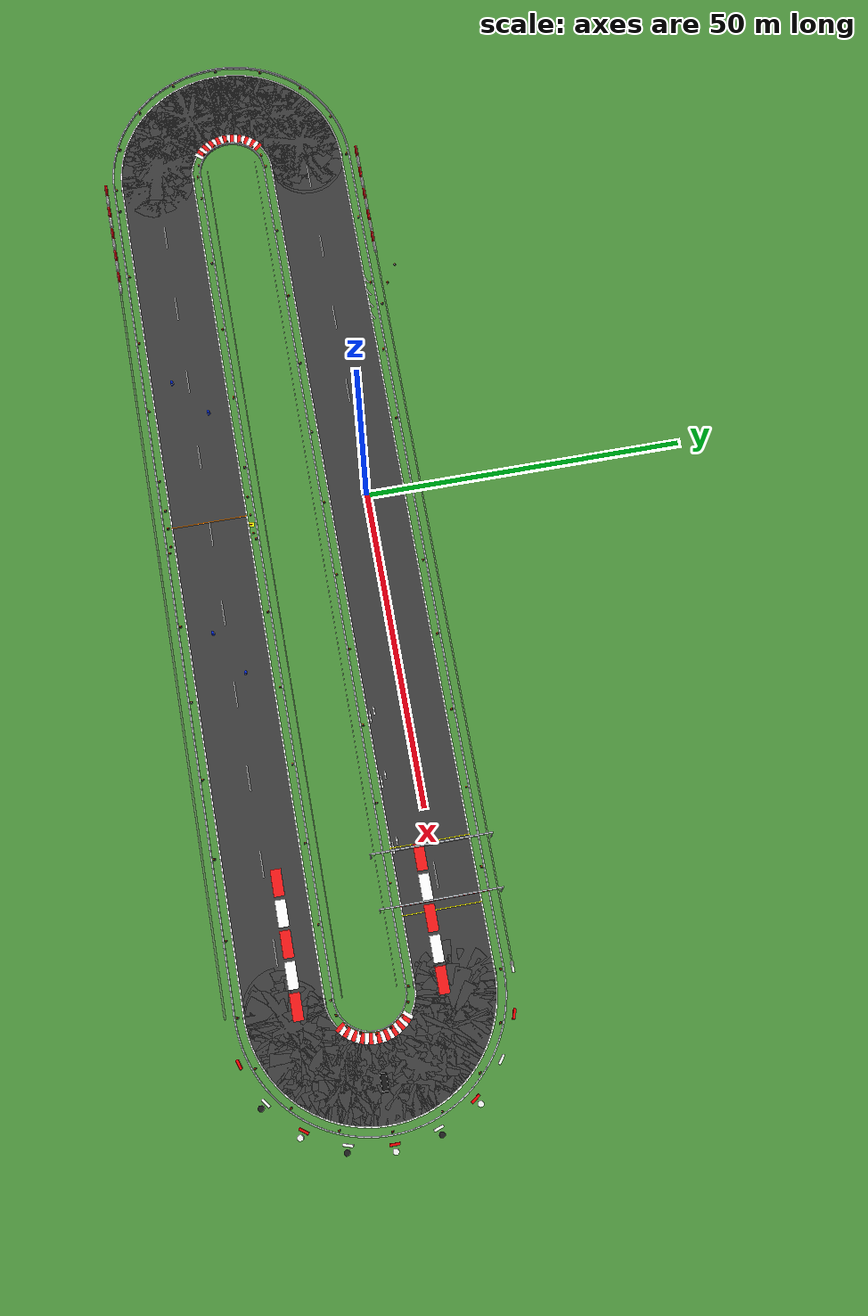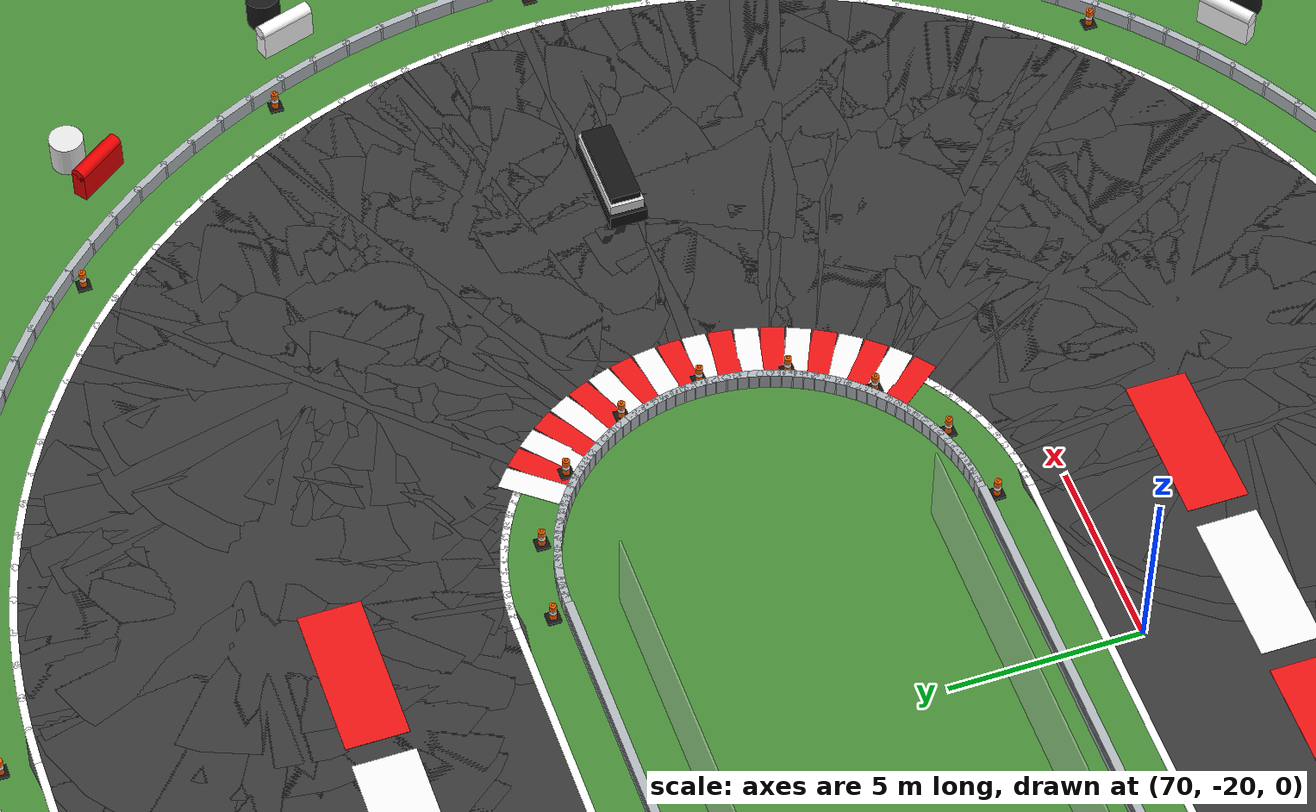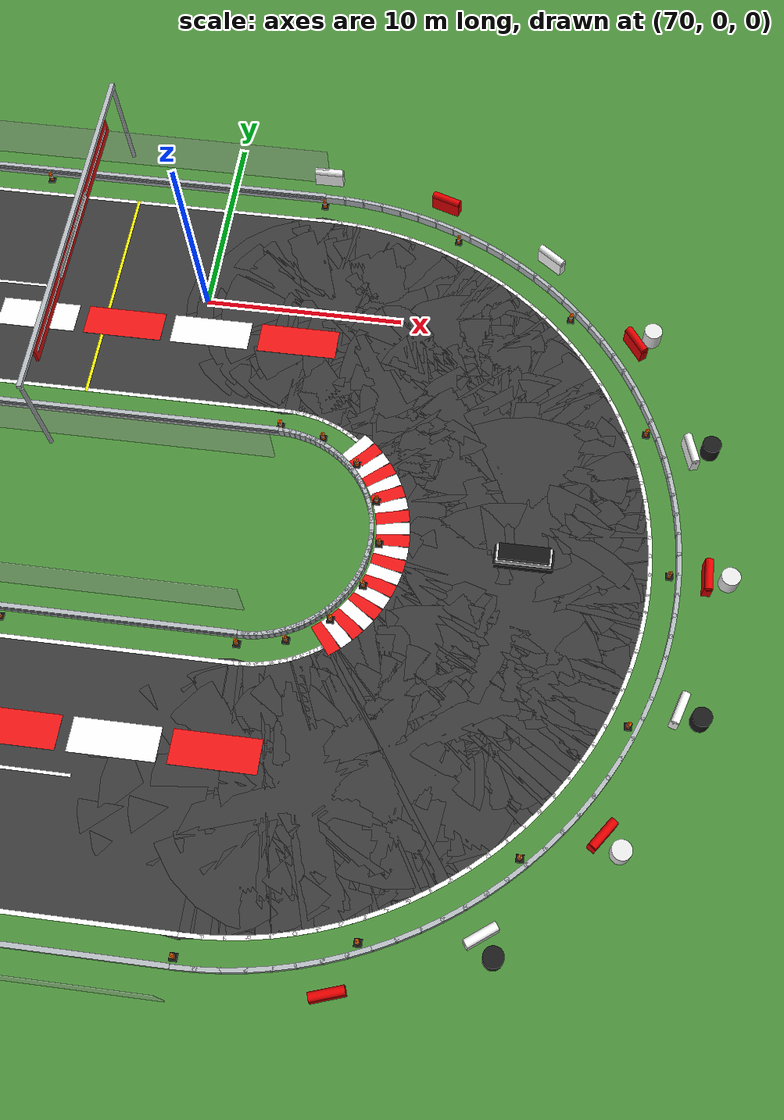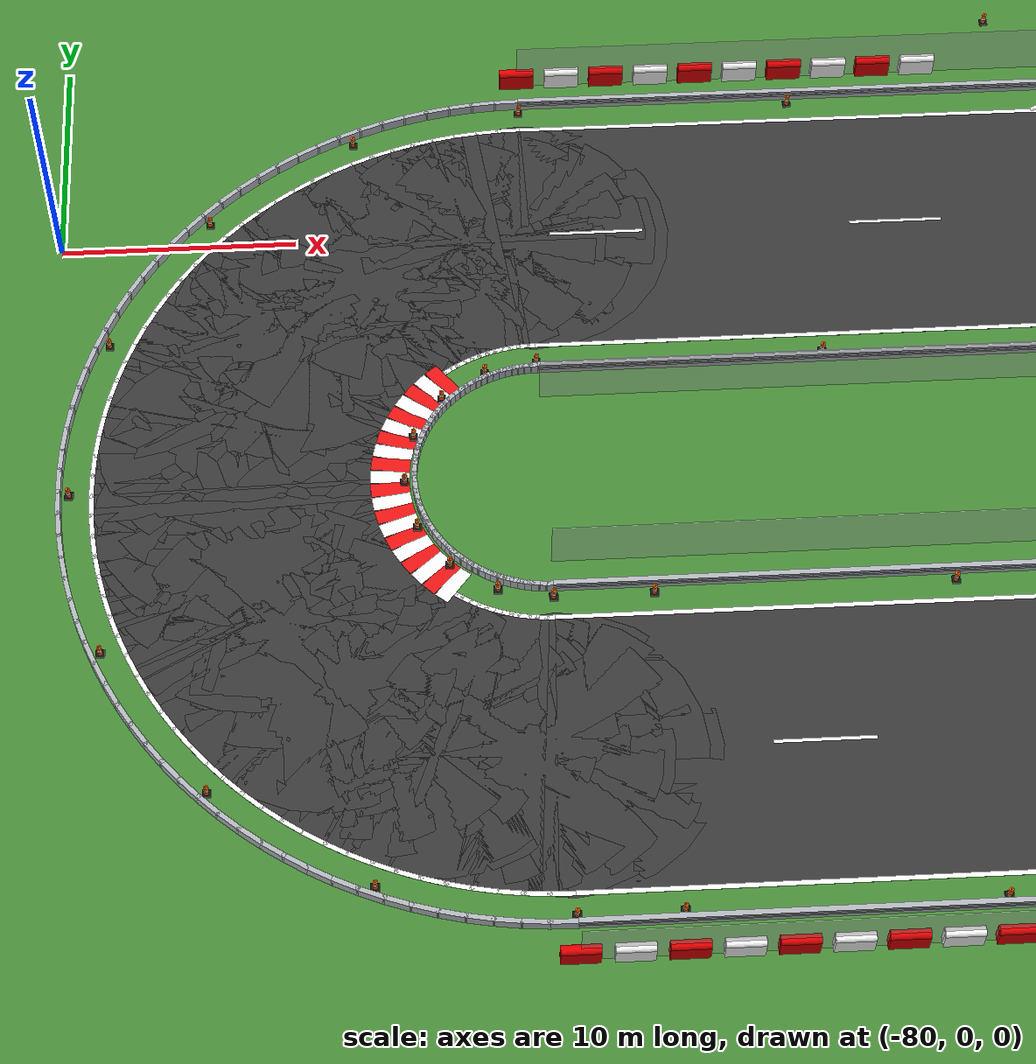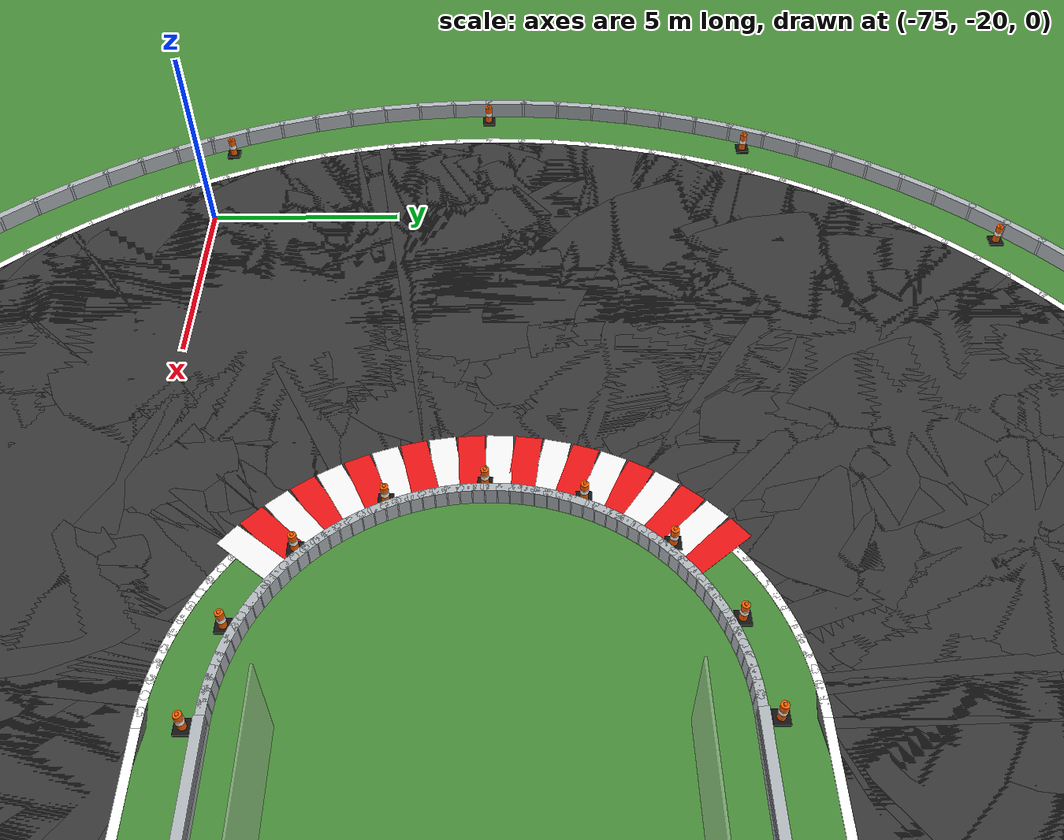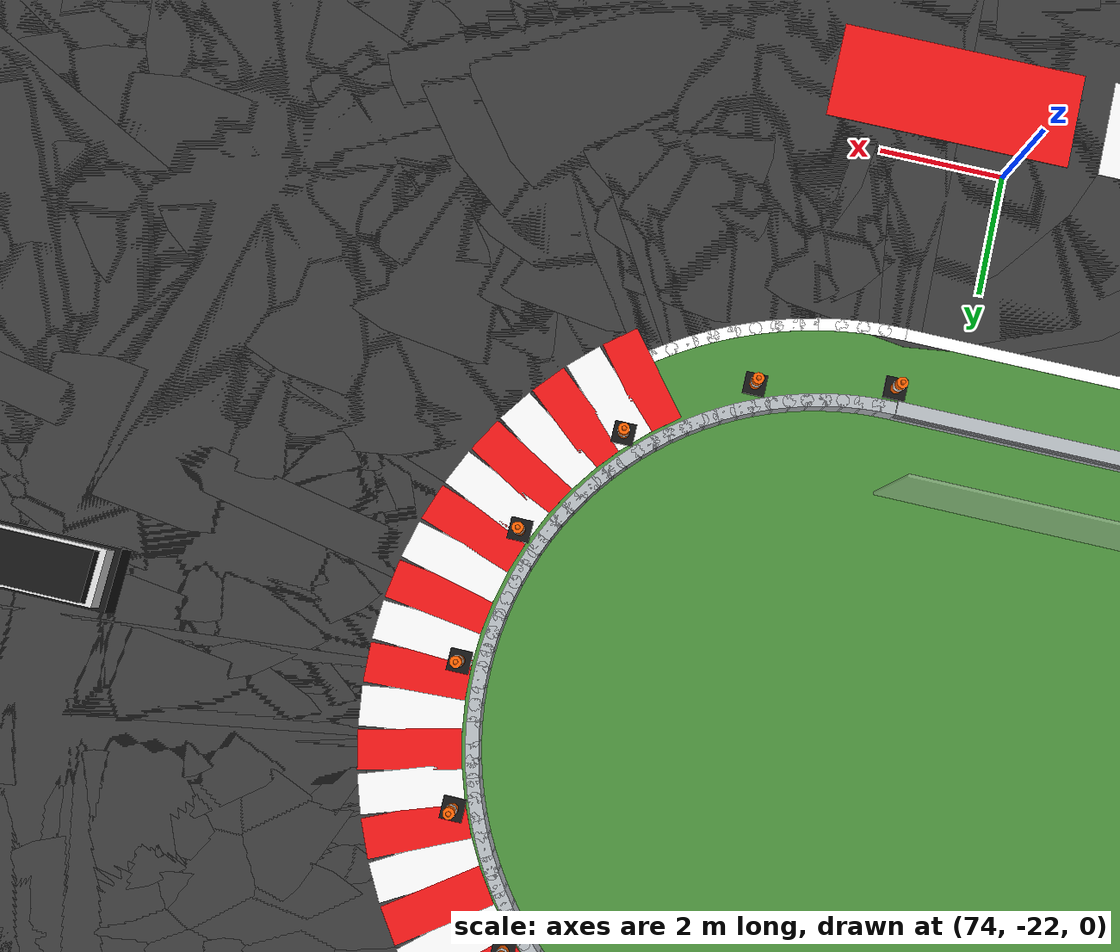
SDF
<?xml version="1.0" ?>
<sdf version="1.6">
  <world name="sem_silesia_ring_2026">

    <physics type="ode">
      <real_time_update_rate>1000</real_time_update_rate>
      <max_step_size>0.001</max_step_size>
      <real_time_factor>1</real_time_factor>
    </physics>
    <gravity>0 0 -9.81</gravity>

    <!-- Lumière réaliste matin (photos Silesia Ring) -->
    <light name="sun" type="directional">
      <cast_shadows>true</cast_shadows>
      <pose>0 0 200 0 0 0</pose>
      <diffuse>0.92 0.90 0.85 1</diffuse>
      <specular>0.12 0.12 0.12 1</specular>
      <direction>-0.4 0.3 -0.85</direction>
    </light>
    <light name="fill" type="directional">
      <cast_shadows>false</cast_shadows>
      <pose>0 0 80 0 0 0</pose>
      <diffuse>0.50 0.53 0.58 1</diffuse>
      <specular>0 0 0 1</specular>
      <direction>0 0 -1</direction>
    </light>

    <!-- Sol vert clair (herbe Silesia Ring) -->
    <model name="ground_plane">
      <static>true</static>
      <link name="link">
        <collision name="collision">
          <geometry><plane><normal>0 0 1</normal><size>600 600</size></plane></geometry>
          <surface><friction><ode><mu>0.6</mu><mu2>0.6</mu2></ode></friction></surface>
        </collision>
        <visual name="visual">
          <geometry><plane><normal>0 0 1</normal><size>600 600</size></plane></geometry>
          <material>
            <ambient>0.28 0.55 0.22 1</ambient>
            <diffuse>0.28 0.55 0.22 1</diffuse>
          </material>
        </visual>
      </link>
    </model>

    <model name="road_s1">
      <static>true</static>
      <pose>7.5000 0.0000 0.0030 0 0 0.0000</pose>
      <link name="link">
        <visual name="v">
          <geometry><box><size>135.0000 12.0000 0.0060</size></box></geometry>
          <material><ambient>0.22 0.22 0.22 1</ambient><diffuse>0.22 0.22 0.22 1</diffuse></material>
        </visual>
        <collision name="c">
          <geometry><box><size>135.0000 12.0000 0.0060</size></box></geometry>
          <surface><friction><ode><mu>0.9</mu><mu2>0.9</mu2></ode></friction></surface>
        </collision>
      </link>
    </model>

    <model name="road_s2">
      <static>true</static>
      <pose>7.5000 -25.0000 0.0030 0 0 0.0000</pose>
      <link name="link">
        <visual name="v">
          <geometry><box><size>135.0000 12.0000 0.0060</size></box></geometry>
          <material><ambient>0.22 0.22 0.22 1</ambient><diffuse>0.22 0.22 0.22 1</diffuse></material>
        </visual>
        <collision name="c">
          <geometry><box><size>135.0000 12.0000 0.0060</size></box></geometry>
          <surface><friction><ode><mu>0.9</mu><mu2>0.9</mu2></ode></friction></surface>
        </collision>
      </link>
    </model>

    <model name="road_L_s0">
      <static>true</static>
      <pose>-60.2182 -0.0019 0.0030 0 0 3.1590</pose>
      <link name="link">
        <visual name="v">
          <geometry><box><size>0.6957 12.0000 0.0060</size></box></geometry>
          <material><ambient>0.22 0.22 0.22 1</ambient><diffuse>0.22 0.22 0.22 1</diffuse></material>
        </visual>
        <collision name="c">
          <geometry><box><size>0.6957 12.0000 0.0060</size></box></geometry>
          <surface><friction><ode><mu>0.9</mu><mu2>0.9</mu2></ode></friction></surface>
        </collision>
      </link>
    </model>

    <model name="road_L_jnt1">
      <static>true</static>
      <pose>-60.4362 -0.0076 0.0030 0 0 0</pose>
      <link name="link">
        <visual name="v">
          <geometry><cylinder><radius>6.0000</radius><length>0.0060</length></cylinder></geometry>
          <material><ambient>0.22 0.22 0.22 1</ambient><diffuse>0.22 0.22 0.22 1</diffuse></material>
        </visual>
        <collision name="c">
          <geometry><cylinder><radius>6.0000</radius><length>0.0060</length></cylinder></geometry>
          <surface><friction><ode><mu>0.9</mu><mu2>0.9</mu2></ode></friction></surface>
        </collision>
      </link>
    </model>

    <model name="road_L_s1">
      <static>true</static>
      <pose>-60.6542 -0.0171 0.0030 0 0 3.1940</pose>
      <link name="link">
        <visual name="v">
          <geometry><box><size>0.6957 12.0000 0.0060</size></box></geometry>
          <material><ambient>0.22 0.22 0.22 1</ambient><diffuse>0.22 0.22 0.22 1</diffuse></material>
        </visual>
        <collision name="c">
          <geometry><box><size>0.6957 12.0000 0.0060</size></box></geometry>
          <surface><friction><ode><mu>0.9</mu><mu2>0.9</mu2></ode></friction></surface>
        </collision>
      </link>
    </model>

    <model name="road_L_jnt2">
      <static>true</static>
      <pose>-60.8720 -0.0304 0.0030 0 0 0</pose>
      <link name="link">
        <visual name="v">
          <geometry><cylinder><radius>6.0000</radius><length>0.0060</length></cylinder></geometry>
          <material><ambient>0.22 0.22 0.22 1</ambient><diffuse>0.22 0.22 0.22 1</diffuse></material>
        </visual>
        <collision name="c">
          <geometry><cylinder><radius>6.0000</radius><length>0.0060</length></cylinder></geometry>
          <surface><friction><ode><mu>0.9</mu><mu2>0.9</mu2></ode></friction></surface>
        </collision>
      </link>
    </model>

    <model name="road_L_s2">
      <static>true</static>
      <pose>-61.0894 -0.0476 0.0030 0 0 3.2289</pose>
      <link name="link">
        <visual name="v">
          <geometry><box><size>0.6957 12.0000 0.0060</size></box></geometry>
          <material><ambient>0.22 0.22 0.22 1</ambient><diffuse>0.22 0.22 0.22 1</diffuse></material>
        </visual>
        <collision name="c">
          <geometry><box><size>0.6957 12.0000 0.0060</size></box></geometry>
          <surface><friction><ode><mu>0.9</mu><mu2>0.9</mu2></ode></friction></surface>
        </collision>
      </link>
    </model>

    <model name="road_L_jnt3">
      <static>true</static>
      <pose>-61.3066 -0.0685 0.0030 0 0 0</pose>
      <link name="link">
        <visual name="v">
          <geometry><cylinder><radius>6.0000</radius><length>0.0060</length></cylinder></geometry>
          <material><ambient>0.22 0.22 0.22 1</ambient><diffuse>0.22 0.22 0.22 1</diffuse></material>
        </visual>
        <collision name="c">
          <geometry><cylinder><radius>6.0000</radius><length>0.0060</length></cylinder></geometry>
          <surface><friction><ode><mu>0.9</mu><mu2>0.9</mu2></ode></friction></surface>
        </collision>
      </link>
    </model>

    <model name="road_L_s3">
      <static>true</static>
      <pose>-61.5234 -0.0932 0.0030 0 0 3.2638</pose>
      <link name="link">
        <visual name="v">
          <geometry><box><size>0.6957 12.0000 0.0060</size></box></geometry>
          <material><ambient>0.22 0.22 0.22 1</ambient><diffuse>0.22 0.22 0.22 1</diffuse></material>
        </visual>
        <collision name="c">
          <geometry><box><size>0.6957 12.0000 0.0060</size></box></geometry>
          <surface><friction><ode><mu>0.9</mu><mu2>0.9</mu2></ode></friction></surface>
        </collision>
      </link>
    </model>

    <model name="road_L_jnt4">
      <static>true</static>
      <pose>-61.7397 -0.1216 0.0030 0 0 0</pose>
      <link name="link">
        <visual name="v">
          <geometry><cylinder><radius>6.0000</radius><length>0.0060</length></cylinder></geometry>
          <material><ambient>0.22 0.22 0.22 1</ambient><diffuse>0.22 0.22 0.22 1</diffuse></material>
        </visual>
        <collision name="c">
          <geometry><cylinder><radius>6.0000</radius><length>0.0060</length></cylinder></geometry>
          <surface><friction><ode><mu>0.9</mu><mu2>0.9</mu2></ode></friction></surface>
        </collision>
      </link>
    </model>

    <model name="road_L_s4">
      <static>true</static>
      <pose>-61.9554 -0.1539 0.0030 0 0 3.2987</pose>
      <link name="link">
        <visual name="v">
          <geometry><box><size>0.6957 12.0000 0.0060</size></box></geometry>
          <material><ambient>0.22 0.22 0.22 1</ambient><diffuse>0.22 0.22 0.22 1</diffuse></material>
        </visual>
        <collision name="c">
          <geometry><box><size>0.6957 12.0000 0.0060</size></box></geometry>
          <surface><friction><ode><mu>0.9</mu><mu2>0.9</mu2></ode></friction></surface>
        </collision>
      </link>
    </model>

    <model name="road_L_jnt5">
      <static>true</static>
      <pose>-62.1706 -0.1899 0.0030 0 0 0</pose>
      <link name="link">
        <visual name="v">
          <geometry><cylinder><radius>6.0000</radius><length>0.0060</length></cylinder></geometry>
          <material><ambient>0.22 0.22 0.22 1</ambient><diffuse>0.22 0.22 0.22 1</diffuse></material>
        </visual>
        <collision name="c">
          <geometry><cylinder><radius>6.0000</radius><length>0.0060</length></cylinder></geometry>
          <surface><friction><ode><mu>0.9</mu><mu2>0.9</mu2></ode></friction></surface>
        </collision>
      </link>
    </model>

    <model name="road_L_s5">
      <static>true</static>
      <pose>-62.3851 -0.2297 0.0030 0 0 3.3336</pose>
      <link name="link">
        <visual name="v">
          <geometry><box><size>0.6957 12.0000 0.0060</size></box></geometry>
          <material><ambient>0.22 0.22 0.22 1</ambient><diffuse>0.22 0.22 0.22 1</diffuse></material>
        </visual>
        <collision name="c">
          <geometry><box><size>0.6957 12.0000 0.0060</size></box></geometry>
          <surface><friction><ode><mu>0.9</mu><mu2>0.9</mu2></ode></friction></surface>
        </collision>
      </link>
    </model>

    <model name="road_L_jnt6">
      <static>true</static>
      <pose>-62.5989 -0.2732 0.0030 0 0 0</pose>
      <link name="link">
        <visual name="v">
          <geometry><cylinder><radius>6.0000</radius><length>0.0060</length></cylinder></geometry>
          <material><ambient>0.22 0.22 0.22 1</ambient><diffuse>0.22 0.22 0.22 1</diffuse></material>
        </visual>
        <collision name="c">
          <geometry><cylinder><radius>6.0000</radius><length>0.0060</length></cylinder></geometry>
          <surface><friction><ode><mu>0.9</mu><mu2>0.9</mu2></ode></friction></surface>
        </collision>
      </link>
    </model>

    <model name="road_L_s6">
      <static>true</static>
      <pose>-62.8119 -0.3204 0.0030 0 0 3.3685</pose>
      <link name="link">
        <visual name="v">
          <geometry><box><size>0.6957 12.0000 0.0060</size></box></geometry>
          <material><ambient>0.22 0.22 0.22 1</ambient><diffuse>0.22 0.22 0.22 1</diffuse></material>
        </visual>
        <collision name="c">
          <geometry><box><size>0.6957 12.0000 0.0060</size></box></geometry>
          <surface><friction><ode><mu>0.9</mu><mu2>0.9</mu2></ode></friction></surface>
        </collision>
      </link>
    </model>

    <model name="road_L_jnt7">
      <static>true</static>
      <pose>-63.0240 -0.3713 0.0030 0 0 0</pose>
      <link name="link">
        <visual name="v">
          <geometry><cylinder><radius>6.0000</radius><length>0.0060</length></cylinder></geometry>
          <material><ambient>0.22 0.22 0.22 1</ambient><diffuse>0.22 0.22 0.22 1</diffuse></material>
        </visual>
        <collision name="c">
          <geometry><cylinder><radius>6.0000</radius><length>0.0060</length></cylinder></geometry>
          <surface><friction><ode><mu>0.9</mu><mu2>0.9</mu2></ode></friction></surface>
        </collision>
      </link>
    </model>

    <model name="road_L_s7">
      <static>true</static>
      <pose>-63.2352 -0.4259 0.0030 0 0 3.4034</pose>
      <link name="link">
        <visual name="v">
          <geometry><box><size>0.6957 12.0000 0.0060</size></box></geometry>
          <material><ambient>0.22 0.22 0.22 1</ambient><diffuse>0.22 0.22 0.22 1</diffuse></material>
        </visual>
        <collision name="c">
          <geometry><box><size>0.6957 12.0000 0.0060</size></box></geometry>
          <surface><friction><ode><mu>0.9</mu><mu2>0.9</mu2></ode></friction></surface>
        </collision>
      </link>
    </model>

    <model name="road_L_jnt8">
      <static>true</static>
      <pose>-63.4455 -0.4842 0.0030 0 0 0</pose>
      <link name="link">
        <visual name="v">
          <geometry><cylinder><radius>6.0000</radius><length>0.0060</length></cylinder></geometry>
          <material><ambient>0.22 0.22 0.22 1</ambient><diffuse>0.22 0.22 0.22 1</diffuse></material>
        </visual>
        <collision name="c">
          <geometry><cylinder><radius>6.0000</radius><length>0.0060</length></cylinder></geometry>
          <surface><friction><ode><mu>0.9</mu><mu2>0.9</mu2></ode></friction></surface>
        </collision>
      </link>
    </model>

    <model name="road_L_s8">
      <static>true</static>
      <pose>-63.6546 -0.5462 0.0030 0 0 3.4383</pose>
      <link name="link">
        <visual name="v">
          <geometry><box><size>0.6957 12.0000 0.0060</size></box></geometry>
          <material><ambient>0.22 0.22 0.22 1</ambient><diffuse>0.22 0.22 0.22 1</diffuse></material>
        </visual>
        <collision name="c">
          <geometry><box><size>0.6957 12.0000 0.0060</size></box></geometry>
          <surface><friction><ode><mu>0.9</mu><mu2>0.9</mu2></ode></friction></surface>
        </collision>
      </link>
    </model>

    <model name="road_L_jnt9">
      <static>true</static>
      <pose>-63.8627 -0.6118 0.0030 0 0 0</pose>
      <link name="link">
        <visual name="v">
          <geometry><cylinder><radius>6.0000</radius><length>0.0060</length></cylinder></geometry>
          <material><ambient>0.22 0.22 0.22 1</ambient><diffuse>0.22 0.22 0.22 1</diffuse></material>
        </visual>
        <collision name="c">
          <geometry><cylinder><radius>6.0000</radius><length>0.0060</length></cylinder></geometry>
          <surface><friction><ode><mu>0.9</mu><mu2>0.9</mu2></ode></friction></surface>
        </collision>
      </link>
    </model>

    <model name="road_L_s9">
      <static>true</static>
      <pose>-64.0696 -0.6810 0.0030 0 0 3.4732</pose>
      <link name="link">
        <visual name="v">
          <geometry><box><size>0.6957 12.0000 0.0060</size></box></geometry>
          <material><ambient>0.22 0.22 0.22 1</ambient><diffuse>0.22 0.22 0.22 1</diffuse></material>
        </visual>
        <collision name="c">
          <geometry><box><size>0.6957 12.0000 0.0060</size></box></geometry>
          <surface><friction><ode><mu>0.9</mu><mu2>0.9</mu2></ode></friction></surface>
        </collision>
      </link>
    </model>

    <model name="road_L_jnt10">
      <static>true</static>
      <pose>-64.2753 -0.7538 0.0030 0 0 0</pose>
      <link name="link">
        <visual name="v">
          <geometry><cylinder><radius>6.0000</radius><length>0.0060</length></cylinder></geometry>
          <material><ambient>0.22 0.22 0.22 1</ambient><diffuse>0.22 0.22 0.22 1</diffuse></material>
        </visual>
        <collision name="c">
          <geometry><cylinder><radius>6.0000</radius><length>0.0060</length></cylinder></geometry>
          <surface><friction><ode><mu>0.9</mu><mu2>0.9</mu2></ode></friction></surface>
        </collision>
      </link>
    </model>

    <model name="road_L_s10">
      <static>true</static>
      <pose>-64.4796 -0.8302 0.0030 0 0 3.5081</pose>
      <link name="link">
        <visual name="v">
          <geometry><box><size>0.6957 12.0000 0.0060</size></box></geometry>
          <material><ambient>0.22 0.22 0.22 1</ambient><diffuse>0.22 0.22 0.22 1</diffuse></material>
        </visual>
        <collision name="c">
          <geometry><box><size>0.6957 12.0000 0.0060</size></box></geometry>
          <surface><friction><ode><mu>0.9</mu><mu2>0.9</mu2></ode></friction></surface>
        </collision>
      </link>
    </model>

    <model name="road_L_jnt11">
      <static>true</static>
      <pose>-64.6826 -0.9102 0.0030 0 0 0</pose>
      <link name="link">
        <visual name="v">
          <geometry><cylinder><radius>6.0000</radius><length>0.0060</length></cylinder></geometry>
          <material><ambient>0.22 0.22 0.22 1</ambient><diffuse>0.22 0.22 0.22 1</diffuse></material>
        </visual>
        <collision name="c">
          <geometry><cylinder><radius>6.0000</radius><length>0.0060</length></cylinder></geometry>
          <surface><friction><ode><mu>0.9</mu><mu2>0.9</mu2></ode></friction></surface>
        </collision>
      </link>
    </model>

    <model name="road_L_s11">
      <static>true</static>
      <pose>-64.8841 -0.9937 0.0030 0 0 3.5430</pose>
      <link name="link">
        <visual name="v">
          <geometry><box><size>0.6957 12.0000 0.0060</size></box></geometry>
          <material><ambient>0.22 0.22 0.22 1</ambient><diffuse>0.22 0.22 0.22 1</diffuse></material>
        </visual>
        <collision name="c">
          <geometry><box><size>0.6957 12.0000 0.0060</size></box></geometry>
          <surface><friction><ode><mu>0.9</mu><mu2>0.9</mu2></ode></friction></surface>
        </collision>
      </link>
    </model>

    <model name="road_L_jnt12">
      <static>true</static>
      <pose>-65.0842 -1.0807 0.0030 0 0 0</pose>
      <link name="link">
        <visual name="v">
          <geometry><cylinder><radius>6.0000</radius><length>0.0060</length></cylinder></geometry>
          <material><ambient>0.22 0.22 0.22 1</ambient><diffuse>0.22 0.22 0.22 1</diffuse></material>
        </visual>
        <collision name="c">
          <geometry><cylinder><radius>6.0000</radius><length>0.0060</length></cylinder></geometry>
          <surface><friction><ode><mu>0.9</mu><mu2>0.9</mu2></ode></friction></surface>
        </collision>
      </link>
    </model>

    <model name="road_L_s12">
      <static>true</static>
      <pose>-65.2827 -1.1712 0.0030 0 0 3.5779</pose>
      <link name="link">
        <visual name="v">
          <geometry><box><size>0.6957 12.0000 0.0060</size></box></geometry>
          <material><ambient>0.22 0.22 0.22 1</ambient><diffuse>0.22 0.22 0.22 1</diffuse></material>
        </visual>
        <collision name="c">
          <geometry><box><size>0.6957 12.0000 0.0060</size></box></geometry>
          <surface><friction><ode><mu>0.9</mu><mu2>0.9</mu2></ode></friction></surface>
        </collision>
      </link>
    </model>

    <model name="road_L_jnt13">
      <static>true</static>
      <pose>-65.4796 -1.2651 0.0030 0 0 0</pose>
      <link name="link">
        <visual name="v">
          <geometry><cylinder><radius>6.0000</radius><length>0.0060</length></cylinder></geometry>
          <material><ambient>0.22 0.22 0.22 1</ambient><diffuse>0.22 0.22 0.22 1</diffuse></material>
        </visual>
        <collision name="c">
          <geometry><cylinder><radius>6.0000</radius><length>0.0060</length></cylinder></geometry>
          <surface><friction><ode><mu>0.9</mu><mu2>0.9</mu2></ode></friction></surface>
        </collision>
      </link>
    </model>

    <model name="road_L_s13">
      <static>true</static>
      <pose>-65.6749 -1.3624 0.0030 0 0 3.6128</pose>
      <link name="link">
        <visual name="v">
          <geometry><box><size>0.6957 12.0000 0.0060</size></box></geometry>
          <material><ambient>0.22 0.22 0.22 1</ambient><diffuse>0.22 0.22 0.22 1</diffuse></material>
        </visual>
        <collision name="c">
          <geometry><box><size>0.6957 12.0000 0.0060</size></box></geometry>
          <surface><friction><ode><mu>0.9</mu><mu2>0.9</mu2></ode></friction></surface>
        </collision>
      </link>
    </model>

    <model name="road_L_jnt14">
      <static>true</static>
      <pose>-65.8684 -1.4632 0.0030 0 0 0</pose>
      <link name="link">
        <visual name="v">
          <geometry><cylinder><radius>6.0000</radius><length>0.0060</length></cylinder></geometry>
          <material><ambient>0.22 0.22 0.22 1</ambient><diffuse>0.22 0.22 0.22 1</diffuse></material>
        </visual>
        <collision name="c">
          <geometry><cylinder><radius>6.0000</radius><length>0.0060</length></cylinder></geometry>
          <surface><friction><ode><mu>0.9</mu><mu2>0.9</mu2></ode></friction></surface>
        </collision>
      </link>
    </model>

    <model name="road_L_s14">
      <static>true</static>
      <pose>-66.0601 -1.5673 0.0030 0 0 3.6477</pose>
      <link name="link">
        <visual name="v">
          <geometry><box><size>0.6957 12.0000 0.0060</size></box></geometry>
          <material><ambient>0.22 0.22 0.22 1</ambient><diffuse>0.22 0.22 0.22 1</diffuse></material>
        </visual>
        <collision name="c">
          <geometry><box><size>0.6957 12.0000 0.0060</size></box></geometry>
          <surface><friction><ode><mu>0.9</mu><mu2>0.9</mu2></ode></friction></surface>
        </collision>
      </link>
    </model>

    <model name="road_L_jnt15">
      <static>true</static>
      <pose>-66.2500 -1.6747 0.0030 0 0 0</pose>
      <link name="link">
        <visual name="v">
          <geometry><cylinder><radius>6.0000</radius><length>0.0060</length></cylinder></geometry>
          <material><ambient>0.22 0.22 0.22 1</ambient><diffuse>0.22 0.22 0.22 1</diffuse></material>
        </visual>
        <collision name="c">
          <geometry><cylinder><radius>6.0000</radius><length>0.0060</length></cylinder></geometry>
          <surface><friction><ode><mu>0.9</mu><mu2>0.9</mu2></ode></friction></surface>
        </collision>
      </link>
    </model>

    <model name="road_L_s15">
      <static>true</static>
      <pose>-66.4380 -1.7854 0.0030 0 0 3.6826</pose>
      <link name="link">
        <visual name="v">
          <geometry><box><size>0.6957 12.0000 0.0060</size></box></geometry>
          <material><ambient>0.22 0.22 0.22 1</ambient><diffuse>0.22 0.22 0.22 1</diffuse></material>
        </visual>
        <collision name="c">
          <geometry><box><size>0.6957 12.0000 0.0060</size></box></geometry>
          <surface><friction><ode><mu>0.9</mu><mu2>0.9</mu2></ode></friction></surface>
        </collision>
      </link>
    </model>

    <model name="road_L_jnt16">
      <static>true</static>
      <pose>-66.6240 -1.8994 0.0030 0 0 0</pose>
      <link name="link">
        <visual name="v">
          <geometry><cylinder><radius>6.0000</radius><length>0.0060</length></cylinder></geometry>
          <material><ambient>0.22 0.22 0.22 1</ambient><diffuse>0.22 0.22 0.22 1</diffuse></material>
        </visual>
        <collision name="c">
          <geometry><cylinder><radius>6.0000</radius><length>0.0060</length></cylinder></geometry>
          <surface><friction><ode><mu>0.9</mu><mu2>0.9</mu2></ode></friction></surface>
        </collision>
      </link>
    </model>

    <model name="road_L_s16">
      <static>true</static>
      <pose>-66.8080 -2.0166 0.0030 0 0 3.7176</pose>
      <link name="link">
        <visual name="v">
          <geometry><box><size>0.6957 12.0000 0.0060</size></box></geometry>
          <material><ambient>0.22 0.22 0.22 1</ambient><diffuse>0.22 0.22 0.22 1</diffuse></material>
        </visual>
        <collision name="c">
          <geometry><box><size>0.6957 12.0000 0.0060</size></box></geometry>
          <surface><friction><ode><mu>0.9</mu><mu2>0.9</mu2></ode></friction></surface>
        </collision>
      </link>
    </model>

    <model name="road_L_jnt17">
      <static>true</static>
      <pose>-66.9899 -2.1370 0.0030 0 0 0</pose>
      <link name="link">
        <visual name="v">
          <geometry><cylinder><radius>6.0000</radius><length>0.0060</length></cylinder></geometry>
          <material><ambient>0.22 0.22 0.22 1</ambient><diffuse>0.22 0.22 0.22 1</diffuse></material>
        </visual>
        <collision name="c">
          <geometry><cylinder><radius>6.0000</radius><length>0.0060</length></cylinder></geometry>
          <surface><friction><ode><mu>0.9</mu><mu2>0.9</mu2></ode></friction></surface>
        </collision>
      </link>
    </model>

    <model name="road_L_s17">
      <static>true</static>
      <pose>-67.1697 -2.2606 0.0030 0 0 3.7525</pose>
      <link name="link">
        <visual name="v">
          <geometry><box><size>0.6957 12.0000 0.0060</size></box></geometry>
          <material><ambient>0.22 0.22 0.22 1</ambient><diffuse>0.22 0.22 0.22 1</diffuse></material>
        </visual>
        <collision name="c">
          <geometry><box><size>0.6957 12.0000 0.0060</size></box></geometry>
          <surface><friction><ode><mu>0.9</mu><mu2>0.9</mu2></ode></friction></surface>
        </collision>
      </link>
    </model>

    <model name="road_L_jnt18">
      <static>true</static>
      <pose>-67.3473 -2.3873 0.0030 0 0 0</pose>
      <link name="link">
        <visual name="v">
          <geometry><cylinder><radius>6.0000</radius><length>0.0060</length></cylinder></geometry>
          <material><ambient>0.22 0.22 0.22 1</ambient><diffuse>0.22 0.22 0.22 1</diffuse></material>
        </visual>
        <collision name="c">
          <geometry><cylinder><radius>6.0000</radius><length>0.0060</length></cylinder></geometry>
          <surface><friction><ode><mu>0.9</mu><mu2>0.9</mu2></ode></friction></surface>
        </collision>
      </link>
    </model>

    <model name="road_L_s18">
      <static>true</static>
      <pose>-67.5227 -2.5171 0.0030 0 0 3.7874</pose>
      <link name="link">
        <visual name="v">
          <geometry><box><size>0.6957 12.0000 0.0060</size></box></geometry>
          <material><ambient>0.22 0.22 0.22 1</ambient><diffuse>0.22 0.22 0.22 1</diffuse></material>
        </visual>
        <collision name="c">
          <geometry><box><size>0.6957 12.0000 0.0060</size></box></geometry>
          <surface><friction><ode><mu>0.9</mu><mu2>0.9</mu2></ode></friction></surface>
        </collision>
      </link>
    </model>

    <model name="road_L_jnt19">
      <static>true</static>
      <pose>-67.6958 -2.6499 0.0030 0 0 0</pose>
      <link name="link">
        <visual name="v">
          <geometry><cylinder><radius>6.0000</radius><length>0.0060</length></cylinder></geometry>
          <material><ambient>0.22 0.22 0.22 1</ambient><diffuse>0.22 0.22 0.22 1</diffuse></material>
        </visual>
        <collision name="c">
          <geometry><cylinder><radius>6.0000</radius><length>0.0060</length></cylinder></geometry>
          <surface><friction><ode><mu>0.9</mu><mu2>0.9</mu2></ode></friction></surface>
        </collision>
      </link>
    </model>

    <model name="road_L_s19">
      <static>true</static>
      <pose>-67.8665 -2.7857 0.0030 0 0 3.8223</pose>
      <link name="link">
        <visual name="v">
          <geometry><box><size>0.6957 12.0000 0.0060</size></box></geometry>
          <material><ambient>0.22 0.22 0.22 1</ambient><diffuse>0.22 0.22 0.22 1</diffuse></material>
        </visual>
        <collision name="c">
          <geometry><box><size>0.6957 12.0000 0.0060</size></box></geometry>
          <surface><friction><ode><mu>0.9</mu><mu2>0.9</mu2></ode></friction></surface>
        </collision>
      </link>
    </model>

    <model name="road_L_jnt20">
      <static>true</static>
      <pose>-68.0348 -2.9244 0.0030 0 0 0</pose>
      <link name="link">
        <visual name="v">
          <geometry><cylinder><radius>6.0000</radius><length>0.0060</length></cylinder></geometry>
          <material><ambient>0.22 0.22 0.22 1</ambient><diffuse>0.22 0.22 0.22 1</diffuse></material>
        </visual>
        <collision name="c">
          <geometry><cylinder><radius>6.0000</radius><length>0.0060</length></cylinder></geometry>
          <surface><friction><ode><mu>0.9</mu><mu2>0.9</mu2></ode></friction></surface>
        </collision>
      </link>
    </model>

    <model name="road_L_s20">
      <static>true</static>
      <pose>-68.2007 -3.0661 0.0030 0 0 3.8572</pose>
      <link name="link">
        <visual name="v">
          <geometry><box><size>0.6957 12.0000 0.0060</size></box></geometry>
          <material><ambient>0.22 0.22 0.22 1</ambient><diffuse>0.22 0.22 0.22 1</diffuse></material>
        </visual>
        <collision name="c">
          <geometry><box><size>0.6957 12.0000 0.0060</size></box></geometry>
          <surface><friction><ode><mu>0.9</mu><mu2>0.9</mu2></ode></friction></surface>
        </collision>
      </link>
    </model>

    <model name="road_L_jnt21">
      <static>true</static>
      <pose>-68.3641 -3.2107 0.0030 0 0 0</pose>
      <link name="link">
        <visual name="v">
          <geometry><cylinder><radius>6.0000</radius><length>0.0060</length></cylinder></geometry>
          <material><ambient>0.22 0.22 0.22 1</ambient><diffuse>0.22 0.22 0.22 1</diffuse></material>
        </visual>
        <collision name="c">
          <geometry><cylinder><radius>6.0000</radius><length>0.0060</length></cylinder></geometry>
          <surface><friction><ode><mu>0.9</mu><mu2>0.9</mu2></ode></friction></surface>
        </collision>
      </link>
    </model>

    <model name="road_L_s21">
      <static>true</static>
      <pose>-68.5250 -3.3581 0.0030 0 0 3.8921</pose>
      <link name="link">
        <visual name="v">
          <geometry><box><size>0.6957 12.0000 0.0060</size></box></geometry>
          <material><ambient>0.22 0.22 0.22 1</ambient><diffuse>0.22 0.22 0.22 1</diffuse></material>
        </visual>
        <collision name="c">
          <geometry><box><size>0.6957 12.0000 0.0060</size></box></geometry>
          <surface><friction><ode><mu>0.9</mu><mu2>0.9</mu2></ode></friction></surface>
        </collision>
      </link>
    </model>

    <model name="road_L_jnt22">
      <static>true</static>
      <pose>-68.6832 -3.5083 0.0030 0 0 0</pose>
      <link name="link">
        <visual name="v">
          <geometry><cylinder><radius>6.0000</radius><length>0.0060</length></cylinder></geometry>
          <material><ambient>0.22 0.22 0.22 1</ambient><diffuse>0.22 0.22 0.22 1</diffuse></material>
        </visual>
        <collision name="c">
          <geometry><cylinder><radius>6.0000</radius><length>0.0060</length></cylinder></geometry>
          <surface><friction><ode><mu>0.9</mu><mu2>0.9</mu2></ode></friction></surface>
        </collision>
      </link>
    </model>

    <model name="road_L_s22">
      <static>true</static>
      <pose>-68.8388 -3.6612 0.0030 0 0 3.9270</pose>
      <link name="link">
        <visual name="v">
          <geometry><box><size>0.6957 12.0000 0.0060</size></box></geometry>
          <material><ambient>0.22 0.22 0.22 1</ambient><diffuse>0.22 0.22 0.22 1</diffuse></material>
        </visual>
        <collision name="c">
          <geometry><box><size>0.6957 12.0000 0.0060</size></box></geometry>
          <surface><friction><ode><mu>0.9</mu><mu2>0.9</mu2></ode></friction></surface>
        </collision>
      </link>
    </model>

    <model name="road_L_jnt23">
      <static>true</static>
      <pose>-68.9917 -3.8168 0.0030 0 0 0</pose>
      <link name="link">
        <visual name="v">
          <geometry><cylinder><radius>6.0000</radius><length>0.0060</length></cylinder></geometry>
          <material><ambient>0.22 0.22 0.22 1</ambient><diffuse>0.22 0.22 0.22 1</diffuse></material>
        </visual>
        <collision name="c">
          <geometry><cylinder><radius>6.0000</radius><length>0.0060</length></cylinder></geometry>
          <surface><friction><ode><mu>0.9</mu><mu2>0.9</mu2></ode></friction></surface>
        </collision>
      </link>
    </model>

    <model name="road_L_s23">
      <static>true</static>
      <pose>-69.1419 -3.9750 0.0030 0 0 3.9619</pose>
      <link name="link">
        <visual name="v">
          <geometry><box><size>0.6957 12.0000 0.0060</size></box></geometry>
          <material><ambient>0.22 0.22 0.22 1</ambient><diffuse>0.22 0.22 0.22 1</diffuse></material>
        </visual>
        <collision name="c">
          <geometry><box><size>0.6957 12.0000 0.0060</size></box></geometry>
          <surface><friction><ode><mu>0.9</mu><mu2>0.9</mu2></ode></friction></surface>
        </collision>
      </link>
    </model>

    <model name="road_L_jnt24">
      <static>true</static>
      <pose>-69.2893 -4.1359 0.0030 0 0 0</pose>
      <link name="link">
        <visual name="v">
          <geometry><cylinder><radius>6.0000</radius><length>0.0060</length></cylinder></geometry>
          <material><ambient>0.22 0.22 0.22 1</ambient><diffuse>0.22 0.22 0.22 1</diffuse></material>
        </visual>
        <collision name="c">
          <geometry><cylinder><radius>6.0000</radius><length>0.0060</length></cylinder></geometry>
          <surface><friction><ode><mu>0.9</mu><mu2>0.9</mu2></ode></friction></surface>
        </collision>
      </link>
    </model>

    <model name="road_L_s24">
      <static>true</static>
      <pose>-69.4339 -4.2993 0.0030 0 0 3.9968</pose>
      <link name="link">
        <visual name="v">
          <geometry><box><size>0.6957 12.0000 0.0060</size></box></geometry>
          <material><ambient>0.22 0.22 0.22 1</ambient><diffuse>0.22 0.22 0.22 1</diffuse></material>
        </visual>
        <collision name="c">
          <geometry><box><size>0.6957 12.0000 0.0060</size></box></geometry>
          <surface><friction><ode><mu>0.9</mu><mu2>0.9</mu2></ode></friction></surface>
        </collision>
      </link>
    </model>

    <model name="road_L_jnt25">
      <static>true</static>
      <pose>-69.5756 -4.4652 0.0030 0 0 0</pose>
      <link name="link">
        <visual name="v">
          <geometry><cylinder><radius>6.0000</radius><length>0.0060</length></cylinder></geometry>
          <material><ambient>0.22 0.22 0.22 1</ambient><diffuse>0.22 0.22 0.22 1</diffuse></material>
        </visual>
        <collision name="c">
          <geometry><cylinder><radius>6.0000</radius><length>0.0060</length></cylinder></geometry>
          <surface><friction><ode><mu>0.9</mu><mu2>0.9</mu2></ode></friction></surface>
        </collision>
      </link>
    </model>

    <model name="road_L_s25">
      <static>true</static>
      <pose>-69.7143 -4.6335 0.0030 0 0 4.0317</pose>
      <link name="link">
        <visual name="v">
          <geometry><box><size>0.6957 12.0000 0.0060</size></box></geometry>
          <material><ambient>0.22 0.22 0.22 1</ambient><diffuse>0.22 0.22 0.22 1</diffuse></material>
        </visual>
        <collision name="c">
          <geometry><box><size>0.6957 12.0000 0.0060</size></box></geometry>
          <surface><friction><ode><mu>0.9</mu><mu2>0.9</mu2></ode></friction></surface>
        </collision>
      </link>
    </model>

    <model name="road_L_jnt26">
      <static>true</static>
      <pose>-69.8501 -4.8042 0.0030 0 0 0</pose>
      <link name="link">
        <visual name="v">
          <geometry><cylinder><radius>6.0000</radius><length>0.0060</length></cylinder></geometry>
          <material><ambient>0.22 0.22 0.22 1</ambient><diffuse>0.22 0.22 0.22 1</diffuse></material>
        </visual>
        <collision name="c">
          <geometry><cylinder><radius>6.0000</radius><length>0.0060</length></cylinder></geometry>
          <surface><friction><ode><mu>0.9</mu><mu2>0.9</mu2></ode></friction></surface>
        </collision>
      </link>
    </model>

    <model name="road_L_s26">
      <static>true</static>
      <pose>-69.9829 -4.9773 0.0030 0 0 4.0666</pose>
      <link name="link">
        <visual name="v">
          <geometry><box><size>0.6957 12.0000 0.0060</size></box></geometry>
          <material><ambient>0.22 0.22 0.22 1</ambient><diffuse>0.22 0.22 0.22 1</diffuse></material>
        </visual>
        <collision name="c">
          <geometry><box><size>0.6957 12.0000 0.0060</size></box></geometry>
          <surface><friction><ode><mu>0.9</mu><mu2>0.9</mu2></ode></friction></surface>
        </collision>
      </link>
    </model>

    <model name="road_L_jnt27">
      <static>true</static>
      <pose>-70.1127 -5.1527 0.0030 0 0 0</pose>
      <link name="link">
        <visual name="v">
          <geometry><cylinder><radius>6.0000</radius><length>0.0060</length></cylinder></geometry>
          <material><ambient>0.22 0.22 0.22 1</ambient><diffuse>0.22 0.22 0.22 1</diffuse></material>
        </visual>
        <collision name="c">
          <geometry><cylinder><radius>6.0000</radius><length>0.0060</length></cylinder></geometry>
          <surface><friction><ode><mu>0.9</mu><mu2>0.9</mu2></ode></friction></surface>
        </collision>
      </link>
    </model>

    <model name="road_L_s27">
      <static>true</static>
      <pose>-70.2394 -5.3303 0.0030 0 0 4.1015</pose>
      <link name="link">
        <visual name="v">
          <geometry><box><size>0.6957 12.0000 0.0060</size></box></geometry>
          <material><ambient>0.22 0.22 0.22 1</ambient><diffuse>0.22 0.22 0.22 1</diffuse></material>
        </visual>
        <collision name="c">
          <geometry><box><size>0.6957 12.0000 0.0060</size></box></geometry>
          <surface><friction><ode><mu>0.9</mu><mu2>0.9</mu2></ode></friction></surface>
        </collision>
      </link>
    </model>

    <model name="road_L_jnt28">
      <static>true</static>
      <pose>-70.3630 -5.5101 0.0030 0 0 0</pose>
      <link name="link">
        <visual name="v">
          <geometry><cylinder><radius>6.0000</radius><length>0.0060</length></cylinder></geometry>
          <material><ambient>0.22 0.22 0.22 1</ambient><diffuse>0.22 0.22 0.22 1</diffuse></material>
        </visual>
        <collision name="c">
          <geometry><cylinder><radius>6.0000</radius><length>0.0060</length></cylinder></geometry>
          <surface><friction><ode><mu>0.9</mu><mu2>0.9</mu2></ode></friction></surface>
        </collision>
      </link>
    </model>

    <model name="road_L_s28">
      <static>true</static>
      <pose>-70.4834 -5.6920 0.0030 0 0 4.1364</pose>
      <link name="link">
        <visual name="v">
          <geometry><box><size>0.6957 12.0000 0.0060</size></box></geometry>
          <material><ambient>0.22 0.22 0.22 1</ambient><diffuse>0.22 0.22 0.22 1</diffuse></material>
        </visual>
        <collision name="c">
          <geometry><box><size>0.6957 12.0000 0.0060</size></box></geometry>
          <surface><friction><ode><mu>0.9</mu><mu2>0.9</mu2></ode></friction></surface>
        </collision>
      </link>
    </model>

    <model name="road_L_jnt29">
      <static>true</static>
      <pose>-70.6006 -5.8760 0.0030 0 0 0</pose>
      <link name="link">
        <visual name="v">
          <geometry><cylinder><radius>6.0000</radius><length>0.0060</length></cylinder></geometry>
          <material><ambient>0.22 0.22 0.22 1</ambient><diffuse>0.22 0.22 0.22 1</diffuse></material>
        </visual>
        <collision name="c">
          <geometry><cylinder><radius>6.0000</radius><length>0.0060</length></cylinder></geometry>
          <surface><friction><ode><mu>0.9</mu><mu2>0.9</mu2></ode></friction></surface>
        </collision>
      </link>
    </model>

    <model name="road_L_s29">
      <static>true</static>
      <pose>-70.7146 -6.0620 0.0030 0 0 4.1713</pose>
      <link name="link">
        <visual name="v">
          <geometry><box><size>0.6957 12.0000 0.0060</size></box></geometry>
          <material><ambient>0.22 0.22 0.22 1</ambient><diffuse>0.22 0.22 0.22 1</diffuse></material>
        </visual>
        <collision name="c">
          <geometry><box><size>0.6957 12.0000 0.0060</size></box></geometry>
          <surface><friction><ode><mu>0.9</mu><mu2>0.9</mu2></ode></friction></surface>
        </collision>
      </link>
    </model>

    <model name="road_L_jnt30">
      <static>true</static>
      <pose>-70.8253 -6.2500 0.0030 0 0 0</pose>
      <link name="link">
        <visual name="v">
          <geometry><cylinder><radius>6.0000</radius><length>0.0060</length></cylinder></geometry>
          <material><ambient>0.22 0.22 0.22 1</ambient><diffuse>0.22 0.22 0.22 1</diffuse></material>
        </visual>
        <collision name="c">
          <geometry><cylinder><radius>6.0000</radius><length>0.0060</length></cylinder></geometry>
          <surface><friction><ode><mu>0.9</mu><mu2>0.9</mu2></ode></friction></surface>
        </collision>
      </link>
    </model>

    <model name="road_L_s30">
      <static>true</static>
      <pose>-70.9327 -6.4399 0.0030 0 0 4.2062</pose>
      <link name="link">
        <visual name="v">
          <geometry><box><size>0.6957 12.0000 0.0060</size></box></geometry>
          <material><ambient>0.22 0.22 0.22 1</ambient><diffuse>0.22 0.22 0.22 1</diffuse></material>
        </visual>
        <collision name="c">
          <geometry><box><size>0.6957 12.0000 0.0060</size></box></geometry>
          <surface><friction><ode><mu>0.9</mu><mu2>0.9</mu2></ode></friction></surface>
        </collision>
      </link>
    </model>

    <model name="road_L_jnt31">
      <static>true</static>
      <pose>-71.0368 -6.6316 0.0030 0 0 0</pose>
      <link name="link">
        <visual name="v">
          <geometry><cylinder><radius>6.0000</radius><length>0.0060</length></cylinder></geometry>
          <material><ambient>0.22 0.22 0.22 1</ambient><diffuse>0.22 0.22 0.22 1</diffuse></material>
        </visual>
        <collision name="c">
          <geometry><cylinder><radius>6.0000</radius><length>0.0060</length></cylinder></geometry>
          <surface><friction><ode><mu>0.9</mu><mu2>0.9</mu2></ode></friction></surface>
        </collision>
      </link>
    </model>

    <model name="road_L_s31">
      <static>true</static>
      <pose>-71.1376 -6.8251 0.0030 0 0 4.2412</pose>
      <link name="link">
        <visual name="v">
          <geometry><box><size>0.6957 12.0000 0.0060</size></box></geometry>
          <material><ambient>0.22 0.22 0.22 1</ambient><diffuse>0.22 0.22 0.22 1</diffuse></material>
        </visual>
        <collision name="c">
          <geometry><box><size>0.6957 12.0000 0.0060</size></box></geometry>
          <surface><friction><ode><mu>0.9</mu><mu2>0.9</mu2></ode></friction></surface>
        </collision>
      </link>
    </model>

    <model name="road_L_jnt32">
      <static>true</static>
      <pose>-71.2349 -7.0204 0.0030 0 0 0</pose>
      <link name="link">
        <visual name="v">
          <geometry><cylinder><radius>6.0000</radius><length>0.0060</length></cylinder></geometry>
          <material><ambient>0.22 0.22 0.22 1</ambient><diffuse>0.22 0.22 0.22 1</diffuse></material>
        </visual>
        <collision name="c">
          <geometry><cylinder><radius>6.0000</radius><length>0.0060</length></cylinder></geometry>
          <surface><friction><ode><mu>0.9</mu><mu2>0.9</mu2></ode></friction></surface>
        </collision>
      </link>
    </model>

    <model name="road_L_s32">
      <static>true</static>
      <pose>-71.3288 -7.2173 0.0030 0 0 4.2761</pose>
      <link name="link">
        <visual name="v">
          <geometry><box><size>0.6957 12.0000 0.0060</size></box></geometry>
          <material><ambient>0.22 0.22 0.22 1</ambient><diffuse>0.22 0.22 0.22 1</diffuse></material>
        </visual>
        <collision name="c">
          <geometry><box><size>0.6957 12.0000 0.0060</size></box></geometry>
          <surface><friction><ode><mu>0.9</mu><mu2>0.9</mu2></ode></friction></surface>
        </collision>
      </link>
    </model>

    <model name="road_L_jnt33">
      <static>true</static>
      <pose>-71.4193 -7.4158 0.0030 0 0 0</pose>
      <link name="link">
        <visual name="v">
          <geometry><cylinder><radius>6.0000</radius><length>0.0060</length></cylinder></geometry>
          <material><ambient>0.22 0.22 0.22 1</ambient><diffuse>0.22 0.22 0.22 1</diffuse></material>
        </visual>
        <collision name="c">
          <geometry><cylinder><radius>6.0000</radius><length>0.0060</length></cylinder></geometry>
          <surface><friction><ode><mu>0.9</mu><mu2>0.9</mu2></ode></friction></surface>
        </collision>
      </link>
    </model>

    <model name="road_L_s33">
      <static>true</static>
      <pose>-71.5063 -7.6159 0.0030 0 0 4.3110</pose>
      <link name="link">
        <visual name="v">
          <geometry><box><size>0.6957 12.0000 0.0060</size></box></geometry>
          <material><ambient>0.22 0.22 0.22 1</ambient><diffuse>0.22 0.22 0.22 1</diffuse></material>
        </visual>
        <collision name="c">
          <geometry><box><size>0.6957 12.0000 0.0060</size></box></geometry>
          <surface><friction><ode><mu>0.9</mu><mu2>0.9</mu2></ode></friction></surface>
        </collision>
      </link>
    </model>

    <model name="road_L_jnt34">
      <static>true</static>
      <pose>-71.5898 -7.8174 0.0030 0 0 0</pose>
      <link name="link">
        <visual name="v">
          <geometry><cylinder><radius>6.0000</radius><length>0.0060</length></cylinder></geometry>
          <material><ambient>0.22 0.22 0.22 1</ambient><diffuse>0.22 0.22 0.22 1</diffuse></material>
        </visual>
        <collision name="c">
          <geometry><cylinder><radius>6.0000</radius><length>0.0060</length></cylinder></geometry>
          <surface><friction><ode><mu>0.9</mu><mu2>0.9</mu2></ode></friction></surface>
        </collision>
      </link>
    </model>

    <model name="road_L_s34">
      <static>true</static>
      <pose>-71.6698 -8.0204 0.0030 0 0 4.3459</pose>
      <link name="link">
        <visual name="v">
          <geometry><box><size>0.6957 12.0000 0.0060</size></box></geometry>
          <material><ambient>0.22 0.22 0.22 1</ambient><diffuse>0.22 0.22 0.22 1</diffuse></material>
        </visual>
        <collision name="c">
          <geometry><box><size>0.6957 12.0000 0.0060</size></box></geometry>
          <surface><friction><ode><mu>0.9</mu><mu2>0.9</mu2></ode></friction></surface>
        </collision>
      </link>
    </model>

    <model name="road_L_jnt35">
      <static>true</static>
      <pose>-71.7462 -8.2247 0.0030 0 0 0</pose>
      <link name="link">
        <visual name="v">
          <geometry><cylinder><radius>6.0000</radius><length>0.0060</length></cylinder></geometry>
          <material><ambient>0.22 0.22 0.22 1</ambient><diffuse>0.22 0.22 0.22 1</diffuse></material>
        </visual>
        <collision name="c">
          <geometry><cylinder><radius>6.0000</radius><length>0.0060</length></cylinder></geometry>
          <surface><friction><ode><mu>0.9</mu><mu2>0.9</mu2></ode></friction></surface>
        </collision>
      </link>
    </model>

    <model name="road_L_s35">
      <static>true</static>
      <pose>-71.8190 -8.4304 0.0030 0 0 4.3808</pose>
      <link name="link">
        <visual name="v">
          <geometry><box><size>0.6957 12.0000 0.0060</size></box></geometry>
          <material><ambient>0.22 0.22 0.22 1</ambient><diffuse>0.22 0.22 0.22 1</diffuse></material>
        </visual>
        <collision name="c">
          <geometry><box><size>0.6957 12.0000 0.0060</size></box></geometry>
          <surface><friction><ode><mu>0.9</mu><mu2>0.9</mu2></ode></friction></surface>
        </collision>
      </link>
    </model>

    <model name="road_L_jnt36">
      <static>true</static>
      <pose>-71.8882 -8.6373 0.0030 0 0 0</pose>
      <link name="link">
        <visual name="v">
          <geometry><cylinder><radius>6.0000</radius><length>0.0060</length></cylinder></geometry>
          <material><ambient>0.22 0.22 0.22 1</ambient><diffuse>0.22 0.22 0.22 1</diffuse></material>
        </visual>
        <collision name="c">
          <geometry><cylinder><radius>6.0000</radius><length>0.0060</length></cylinder></geometry>
          <surface><friction><ode><mu>0.9</mu><mu2>0.9</mu2></ode></friction></surface>
        </collision>
      </link>
    </model>

    <model name="road_L_s36">
      <static>true</static>
      <pose>-71.9538 -8.8454 0.0030 0 0 4.4157</pose>
      <link name="link">
        <visual name="v">
          <geometry><box><size>0.6957 12.0000 0.0060</size></box></geometry>
          <material><ambient>0.22 0.22 0.22 1</ambient><diffuse>0.22 0.22 0.22 1</diffuse></material>
        </visual>
        <collision name="c">
          <geometry><box><size>0.6957 12.0000 0.0060</size></box></geometry>
          <surface><friction><ode><mu>0.9</mu><mu2>0.9</mu2></ode></friction></surface>
        </collision>
      </link>
    </model>

    <model name="road_L_jnt37">
      <static>true</static>
      <pose>-72.0158 -9.0545 0.0030 0 0 0</pose>
      <link name="link">
        <visual name="v">
          <geometry><cylinder><radius>6.0000</radius><length>0.0060</length></cylinder></geometry>
          <material><ambient>0.22 0.22 0.22 1</ambient><diffuse>0.22 0.22 0.22 1</diffuse></material>
        </visual>
        <collision name="c">
          <geometry><cylinder><radius>6.0000</radius><length>0.0060</length></cylinder></geometry>
          <surface><friction><ode><mu>0.9</mu><mu2>0.9</mu2></ode></friction></surface>
        </collision>
      </link>
    </model>

    <model name="road_L_s37">
      <static>true</static>
      <pose>-72.0741 -9.2648 0.0030 0 0 4.4506</pose>
      <link name="link">
        <visual name="v">
          <geometry><box><size>0.6957 12.0000 0.0060</size></box></geometry>
          <material><ambient>0.22 0.22 0.22 1</ambient><diffuse>0.22 0.22 0.22 1</diffuse></material>
        </visual>
        <collision name="c">
          <geometry><box><size>0.6957 12.0000 0.0060</size></box></geometry>
          <surface><friction><ode><mu>0.9</mu><mu2>0.9</mu2></ode></friction></surface>
        </collision>
      </link>
    </model>

    <model name="road_L_jnt38">
      <static>true</static>
      <pose>-72.1287 -9.4760 0.0030 0 0 0</pose>
      <link name="link">
        <visual name="v">
          <geometry><cylinder><radius>6.0000</radius><length>0.0060</length></cylinder></geometry>
          <material><ambient>0.22 0.22 0.22 1</ambient><diffuse>0.22 0.22 0.22 1</diffuse></material>
        </visual>
        <collision name="c">
          <geometry><cylinder><radius>6.0000</radius><length>0.0060</length></cylinder></geometry>
          <surface><friction><ode><mu>0.9</mu><mu2>0.9</mu2></ode></friction></surface>
        </collision>
      </link>
    </model>

    <model name="road_L_s38">
      <static>true</static>
      <pose>-72.1796 -9.6881 0.0030 0 0 4.4855</pose>
      <link name="link">
        <visual name="v">
          <geometry><box><size>0.6957 12.0000 0.0060</size></box></geometry>
          <material><ambient>0.22 0.22 0.22 1</ambient><diffuse>0.22 0.22 0.22 1</diffuse></material>
        </visual>
        <collision name="c">
          <geometry><box><size>0.6957 12.0000 0.0060</size></box></geometry>
          <surface><friction><ode><mu>0.9</mu><mu2>0.9</mu2></ode></friction></surface>
        </collision>
      </link>
    </model>

    <model name="road_L_jnt39">
      <static>true</static>
      <pose>-72.2268 -9.9011 0.0030 0 0 0</pose>
      <link name="link">
        <visual name="v">
          <geometry><cylinder><radius>6.0000</radius><length>0.0060</length></cylinder></geometry>
          <material><ambient>0.22 0.22 0.22 1</ambient><diffuse>0.22 0.22 0.22 1</diffuse></material>
        </visual>
        <collision name="c">
          <geometry><cylinder><radius>6.0000</radius><length>0.0060</length></cylinder></geometry>
          <surface><friction><ode><mu>0.9</mu><mu2>0.9</mu2></ode></friction></surface>
        </collision>
      </link>
    </model>

    <model name="road_L_s39">
      <static>true</static>
      <pose>-72.2703 -10.1149 0.0030 0 0 4.5204</pose>
      <link name="link">
        <visual name="v">
          <geometry><box><size>0.6957 12.0000 0.0060</size></box></geometry>
          <material><ambient>0.22 0.22 0.22 1</ambient><diffuse>0.22 0.22 0.22 1</diffuse></material>
        </visual>
        <collision name="c">
          <geometry><box><size>0.6957 12.0000 0.0060</size></box></geometry>
          <surface><friction><ode><mu>0.9</mu><mu2>0.9</mu2></ode></friction></surface>
        </collision>
      </link>
    </model>

    <model name="road_L_jnt40">
      <static>true</static>
      <pose>-72.3101 -10.3294 0.0030 0 0 0</pose>
      <link name="link">
        <visual name="v">
          <geometry><cylinder><radius>6.0000</radius><length>0.0060</length></cylinder></geometry>
          <material><ambient>0.22 0.22 0.22 1</ambient><diffuse>0.22 0.22 0.22 1</diffuse></material>
        </visual>
        <collision name="c">
          <geometry><cylinder><radius>6.0000</radius><length>0.0060</length></cylinder></geometry>
          <surface><friction><ode><mu>0.9</mu><mu2>0.9</mu2></ode></friction></surface>
        </collision>
      </link>
    </model>

    <model name="road_L_s40">
      <static>true</static>
      <pose>-72.3461 -10.5446 0.0030 0 0 4.5553</pose>
      <link name="link">
        <visual name="v">
          <geometry><box><size>0.6957 12.0000 0.0060</size></box></geometry>
          <material><ambient>0.22 0.22 0.22 1</ambient><diffuse>0.22 0.22 0.22 1</diffuse></material>
        </visual>
        <collision name="c">
          <geometry><box><size>0.6957 12.0000 0.0060</size></box></geometry>
          <surface><friction><ode><mu>0.9</mu><mu2>0.9</mu2></ode></friction></surface>
        </collision>
      </link>
    </model>

    <model name="road_L_jnt41">
      <static>true</static>
      <pose>-72.3784 -10.7603 0.0030 0 0 0</pose>
      <link name="link">
        <visual name="v">
          <geometry><cylinder><radius>6.0000</radius><length>0.0060</length></cylinder></geometry>
          <material><ambient>0.22 0.22 0.22 1</ambient><diffuse>0.22 0.22 0.22 1</diffuse></material>
        </visual>
        <collision name="c">
          <geometry><cylinder><radius>6.0000</radius><length>0.0060</length></cylinder></geometry>
          <surface><friction><ode><mu>0.9</mu><mu2>0.9</mu2></ode></friction></surface>
        </collision>
      </link>
    </model>

    <model name="road_L_s41">
      <static>true</static>
      <pose>-72.4068 -10.9766 0.0030 0 0 4.5902</pose>
      <link name="link">
        <visual name="v">
          <geometry><box><size>0.6957 12.0000 0.0060</size></box></geometry>
          <material><ambient>0.22 0.22 0.22 1</ambient><diffuse>0.22 0.22 0.22 1</diffuse></material>
        </visual>
        <collision name="c">
          <geometry><box><size>0.6957 12.0000 0.0060</size></box></geometry>
          <surface><friction><ode><mu>0.9</mu><mu2>0.9</mu2></ode></friction></surface>
        </collision>
      </link>
    </model>

    <model name="road_L_jnt42">
      <static>true</static>
      <pose>-72.4315 -11.1934 0.0030 0 0 0</pose>
      <link name="link">
        <visual name="v">
          <geometry><cylinder><radius>6.0000</radius><length>0.0060</length></cylinder></geometry>
          <material><ambient>0.22 0.22 0.22 1</ambient><diffuse>0.22 0.22 0.22 1</diffuse></material>
        </visual>
        <collision name="c">
          <geometry><cylinder><radius>6.0000</radius><length>0.0060</length></cylinder></geometry>
          <surface><friction><ode><mu>0.9</mu><mu2>0.9</mu2></ode></friction></surface>
        </collision>
      </link>
    </model>

    <model name="road_L_s42">
      <static>true</static>
      <pose>-72.4524 -11.4106 0.0030 0 0 4.6251</pose>
      <link name="link">
        <visual name="v">
          <geometry><box><size>0.6957 12.0000 0.0060</size></box></geometry>
          <material><ambient>0.22 0.22 0.22 1</ambient><diffuse>0.22 0.22 0.22 1</diffuse></material>
        </visual>
        <collision name="c">
          <geometry><box><size>0.6957 12.0000 0.0060</size></box></geometry>
          <surface><friction><ode><mu>0.9</mu><mu2>0.9</mu2></ode></friction></surface>
        </collision>
      </link>
    </model>

    <model name="road_L_jnt43">
      <static>true</static>
      <pose>-72.4696 -11.6280 0.0030 0 0 0</pose>
      <link name="link">
        <visual name="v">
          <geometry><cylinder><radius>6.0000</radius><length>0.0060</length></cylinder></geometry>
          <material><ambient>0.22 0.22 0.22 1</ambient><diffuse>0.22 0.22 0.22 1</diffuse></material>
        </visual>
        <collision name="c">
          <geometry><cylinder><radius>6.0000</radius><length>0.0060</length></cylinder></geometry>
          <surface><friction><ode><mu>0.9</mu><mu2>0.9</mu2></ode></friction></surface>
        </collision>
      </link>
    </model>

    <model name="road_L_s43">
      <static>true</static>
      <pose>-72.4829 -11.8458 0.0030 0 0 4.6600</pose>
      <link name="link">
        <visual name="v">
          <geometry><box><size>0.6957 12.0000 0.0060</size></box></geometry>
          <material><ambient>0.22 0.22 0.22 1</ambient><diffuse>0.22 0.22 0.22 1</diffuse></material>
        </visual>
        <collision name="c">
          <geometry><box><size>0.6957 12.0000 0.0060</size></box></geometry>
          <surface><friction><ode><mu>0.9</mu><mu2>0.9</mu2></ode></friction></surface>
        </collision>
      </link>
    </model>

    <model name="road_L_jnt44">
      <static>true</static>
      <pose>-72.4924 -12.0638 0.0030 0 0 0</pose>
      <link name="link">
        <visual name="v">
          <geometry><cylinder><radius>6.0000</radius><length>0.0060</length></cylinder></geometry>
          <material><ambient>0.22 0.22 0.22 1</ambient><diffuse>0.22 0.22 0.22 1</diffuse></material>
        </visual>
        <collision name="c">
          <geometry><cylinder><radius>6.0000</radius><length>0.0060</length></cylinder></geometry>
          <surface><friction><ode><mu>0.9</mu><mu2>0.9</mu2></ode></friction></surface>
        </collision>
      </link>
    </model>

    <model name="road_L_s44">
      <static>true</static>
      <pose>-72.4981 -12.2818 0.0030 0 0 4.6949</pose>
      <link name="link">
        <visual name="v">
          <geometry><box><size>0.6957 12.0000 0.0060</size></box></geometry>
          <material><ambient>0.22 0.22 0.22 1</ambient><diffuse>0.22 0.22 0.22 1</diffuse></material>
        </visual>
        <collision name="c">
          <geometry><box><size>0.6957 12.0000 0.0060</size></box></geometry>
          <surface><friction><ode><mu>0.9</mu><mu2>0.9</mu2></ode></friction></surface>
        </collision>
      </link>
    </model>

    <model name="road_L_jnt45">
      <static>true</static>
      <pose>-72.5000 -12.5000 0.0030 0 0 0</pose>
      <link name="link">
        <visual name="v">
          <geometry><cylinder><radius>6.0000</radius><length>0.0060</length></cylinder></geometry>
          <material><ambient>0.22 0.22 0.22 1</ambient><diffuse>0.22 0.22 0.22 1</diffuse></material>
        </visual>
        <collision name="c">
          <geometry><cylinder><radius>6.0000</radius><length>0.0060</length></cylinder></geometry>
          <surface><friction><ode><mu>0.9</mu><mu2>0.9</mu2></ode></friction></surface>
        </collision>
      </link>
    </model>

    <model name="road_L_s45">
      <static>true</static>
      <pose>-72.4981 -12.7182 0.0030 0 0 4.7298</pose>
      <link name="link">
        <visual name="v">
          <geometry><box><size>0.6957 12.0000 0.0060</size></box></geometry>
          <material><ambient>0.22 0.22 0.22 1</ambient><diffuse>0.22 0.22 0.22 1</diffuse></material>
        </visual>
        <collision name="c">
          <geometry><box><size>0.6957 12.0000 0.0060</size></box></geometry>
          <surface><friction><ode><mu>0.9</mu><mu2>0.9</mu2></ode></friction></surface>
        </collision>
      </link>
    </model>

    <model name="road_L_jnt46">
      <static>true</static>
      <pose>-72.4924 -12.9362 0.0030 0 0 0</pose>
      <link name="link">
        <visual name="v">
          <geometry><cylinder><radius>6.0000</radius><length>0.0060</length></cylinder></geometry>
          <material><ambient>0.22 0.22 0.22 1</ambient><diffuse>0.22 0.22 0.22 1</diffuse></material>
        </visual>
        <collision name="c">
          <geometry><cylinder><radius>6.0000</radius><length>0.0060</length></cylinder></geometry>
          <surface><friction><ode><mu>0.9</mu><mu2>0.9</mu2></ode></friction></surface>
        </collision>
      </link>
    </model>

    <model name="road_L_s46">
      <static>true</static>
      <pose>-72.4829 -13.1542 0.0030 0 0 4.7647</pose>
      <link name="link">
        <visual name="v">
          <geometry><box><size>0.6957 12.0000 0.0060</size></box></geometry>
          <material><ambient>0.22 0.22 0.22 1</ambient><diffuse>0.22 0.22 0.22 1</diffuse></material>
        </visual>
        <collision name="c">
          <geometry><box><size>0.6957 12.0000 0.0060</size></box></geometry>
          <surface><friction><ode><mu>0.9</mu><mu2>0.9</mu2></ode></friction></surface>
        </collision>
      </link>
    </model>

    <model name="road_L_jnt47">
      <static>true</static>
      <pose>-72.4696 -13.3720 0.0030 0 0 0</pose>
      <link name="link">
        <visual name="v">
          <geometry><cylinder><radius>6.0000</radius><length>0.0060</length></cylinder></geometry>
          <material><ambient>0.22 0.22 0.22 1</ambient><diffuse>0.22 0.22 0.22 1</diffuse></material>
        </visual>
        <collision name="c">
          <geometry><cylinder><radius>6.0000</radius><length>0.0060</length></cylinder></geometry>
          <surface><friction><ode><mu>0.9</mu><mu2>0.9</mu2></ode></friction></surface>
        </collision>
      </link>
    </model>

    <model name="road_L_s47">
      <static>true</static>
      <pose>-72.4524 -13.5894 0.0030 0 0 4.7997</pose>
      <link name="link">
        <visual name="v">
          <geometry><box><size>0.6957 12.0000 0.0060</size></box></geometry>
          <material><ambient>0.22 0.22 0.22 1</ambient><diffuse>0.22 0.22 0.22 1</diffuse></material>
        </visual>
        <collision name="c">
          <geometry><box><size>0.6957 12.0000 0.0060</size></box></geometry>
          <surface><friction><ode><mu>0.9</mu><mu2>0.9</mu2></ode></friction></surface>
        </collision>
      </link>
    </model>

    <model name="road_L_jnt48">
      <static>true</static>
      <pose>-72.4315 -13.8066 0.0030 0 0 0</pose>
      <link name="link">
        <visual name="v">
          <geometry><cylinder><radius>6.0000</radius><length>0.0060</length></cylinder></geometry>
          <material><ambient>0.22 0.22 0.22 1</ambient><diffuse>0.22 0.22 0.22 1</diffuse></material>
        </visual>
        <collision name="c">
          <geometry><cylinder><radius>6.0000</radius><length>0.0060</length></cylinder></geometry>
          <surface><friction><ode><mu>0.9</mu><mu2>0.9</mu2></ode></friction></surface>
        </collision>
      </link>
    </model>

    <model name="road_L_s48">
      <static>true</static>
      <pose>-72.4068 -14.0234 0.0030 0 0 4.8346</pose>
      <link name="link">
        <visual name="v">
          <geometry><box><size>0.6957 12.0000 0.0060</size></box></geometry>
          <material><ambient>0.22 0.22 0.22 1</ambient><diffuse>0.22 0.22 0.22 1</diffuse></material>
        </visual>
        <collision name="c">
          <geometry><box><size>0.6957 12.0000 0.0060</size></box></geometry>
          <surface><friction><ode><mu>0.9</mu><mu2>0.9</mu2></ode></friction></surface>
        </collision>
      </link>
    </model>

    <model name="road_L_jnt49">
      <static>true</static>
      <pose>-72.3784 -14.2397 0.0030 0 0 0</pose>
      <link name="link">
        <visual name="v">
          <geometry><cylinder><radius>6.0000</radius><length>0.0060</length></cylinder></geometry>
          <material><ambient>0.22 0.22 0.22 1</ambient><diffuse>0.22 0.22 0.22 1</diffuse></material>
        </visual>
        <collision name="c">
          <geometry><cylinder><radius>6.0000</radius><length>0.0060</length></cylinder></geometry>
          <surface><friction><ode><mu>0.9</mu><mu2>0.9</mu2></ode></friction></surface>
        </collision>
      </link>
    </model>

    <model name="road_L_s49">
      <static>true</static>
      <pose>-72.3461 -14.4554 0.0030 0 0 4.8695</pose>
      <link name="link">
        <visual name="v">
          <geometry><box><size>0.6957 12.0000 0.0060</size></box></geometry>
          <material><ambient>0.22 0.22 0.22 1</ambient><diffuse>0.22 0.22 0.22 1</diffuse></material>
        </visual>
        <collision name="c">
          <geometry><box><size>0.6957 12.0000 0.0060</size></box></geometry>
          <surface><friction><ode><mu>0.9</mu><mu2>0.9</mu2></ode></friction></surface>
        </collision>
      </link>
    </model>

    <model name="road_L_jnt50">
      <static>true</static>
      <pose>-72.3101 -14.6706 0.0030 0 0 0</pose>
      <link name="link">
        <visual name="v">
          <geometry><cylinder><radius>6.0000</radius><length>0.0060</length></cylinder></geometry>
          <material><ambient>0.22 0.22 0.22 1</ambient><diffuse>0.22 0.22 0.22 1</diffuse></material>
        </visual>
        <collision name="c">
          <geometry><cylinder><radius>6.0000</radius><length>0.0060</length></cylinder></geometry>
          <surface><friction><ode><mu>0.9</mu><mu2>0.9</mu2></ode></friction></surface>
        </collision>
      </link>
    </model>

    <model name="road_L_s50">
      <static>true</static>
      <pose>-72.2703 -14.8851 0.0030 0 0 4.9044</pose>
      <link name="link">
        <visual name="v">
          <geometry><box><size>0.6957 12.0000 0.0060</size></box></geometry>
          <material><ambient>0.22 0.22 0.22 1</ambient><diffuse>0.22 0.22 0.22 1</diffuse></material>
        </visual>
        <collision name="c">
          <geometry><box><size>0.6957 12.0000 0.0060</size></box></geometry>
          <surface><friction><ode><mu>0.9</mu><mu2>0.9</mu2></ode></friction></surface>
        </collision>
      </link>
    </model>

    <model name="road_L_jnt51">
      <static>true</static>
      <pose>-72.2268 -15.0989 0.0030 0 0 0</pose>
      <link name="link">
        <visual name="v">
          <geometry><cylinder><radius>6.0000</radius><length>0.0060</length></cylinder></geometry>
          <material><ambient>0.22 0.22 0.22 1</ambient><diffuse>0.22 0.22 0.22 1</diffuse></material>
        </visual>
        <collision name="c">
          <geometry><cylinder><radius>6.0000</radius><length>0.0060</length></cylinder></geometry>
          <surface><friction><ode><mu>0.9</mu><mu2>0.9</mu2></ode></friction></surface>
        </collision>
      </link>
    </model>

    <model name="road_L_s51">
      <static>true</static>
      <pose>-72.1796 -15.3119 0.0030 0 0 4.9393</pose>
      <link name="link">
        <visual name="v">
          <geometry><box><size>0.6957 12.0000 0.0060</size></box></geometry>
          <material><ambient>0.22 0.22 0.22 1</ambient><diffuse>0.22 0.22 0.22 1</diffuse></material>
        </visual>
        <collision name="c">
          <geometry><box><size>0.6957 12.0000 0.0060</size></box></geometry>
          <surface><friction><ode><mu>0.9</mu><mu2>0.9</mu2></ode></friction></surface>
        </collision>
      </link>
    </model>

    <model name="road_L_jnt52">
      <static>true</static>
      <pose>-72.1287 -15.5240 0.0030 0 0 0</pose>
      <link name="link">
        <visual name="v">
          <geometry><cylinder><radius>6.0000</radius><length>0.0060</length></cylinder></geometry>
          <material><ambient>0.22 0.22 0.22 1</ambient><diffuse>0.22 0.22 0.22 1</diffuse></material>
        </visual>
        <collision name="c">
          <geometry><cylinder><radius>6.0000</radius><length>0.0060</length></cylinder></geometry>
          <surface><friction><ode><mu>0.9</mu><mu2>0.9</mu2></ode></friction></surface>
        </collision>
      </link>
    </model>

    <model name="road_L_s52">
      <static>true</static>
      <pose>-72.0741 -15.7352 0.0030 0 0 4.9742</pose>
      <link name="link">
        <visual name="v">
          <geometry><box><size>0.6957 12.0000 0.0060</size></box></geometry>
          <material><ambient>0.22 0.22 0.22 1</ambient><diffuse>0.22 0.22 0.22 1</diffuse></material>
        </visual>
        <collision name="c">
          <geometry><box><size>0.6957 12.0000 0.0060</size></box></geometry>
          <surface><friction><ode><mu>0.9</mu><mu2>0.9</mu2></ode></friction></surface>
        </collision>
      </link>
    </model>

    <model name="road_L_jnt53">
      <static>true</static>
      <pose>-72.0158 -15.9455 0.0030 0 0 0</pose>
      <link name="link">
        <visual name="v">
          <geometry><cylinder><radius>6.0000</radius><length>0.0060</length></cylinder></geometry>
          <material><ambient>0.22 0.22 0.22 1</ambient><diffuse>0.22 0.22 0.22 1</diffuse></material>
        </visual>
        <collision name="c">
          <geometry><cylinder><radius>6.0000</radius><length>0.0060</length></cylinder></geometry>
          <surface><friction><ode><mu>0.9</mu><mu2>0.9</mu2></ode></friction></surface>
        </collision>
      </link>
    </model>

    <model name="road_L_s53">
      <static>true</static>
      <pose>-71.9538 -16.1546 0.0030 0 0 5.0091</pose>
      <link name="link">
        <visual name="v">
          <geometry><box><size>0.6957 12.0000 0.0060</size></box></geometry>
          <material><ambient>0.22 0.22 0.22 1</ambient><diffuse>0.22 0.22 0.22 1</diffuse></material>
        </visual>
        <collision name="c">
          <geometry><box><size>0.6957 12.0000 0.0060</size></box></geometry>
          <surface><friction><ode><mu>0.9</mu><mu2>0.9</mu2></ode></friction></surface>
        </collision>
      </link>
    </model>

    <model name="road_L_jnt54">
      <static>true</static>
      <pose>-71.8882 -16.3627 0.0030 0 0 0</pose>
      <link name="link">
        <visual name="v">
          <geometry><cylinder><radius>6.0000</radius><length>0.0060</length></cylinder></geometry>
          <material><ambient>0.22 0.22 0.22 1</ambient><diffuse>0.22 0.22 0.22 1</diffuse></material>
        </visual>
        <collision name="c">
          <geometry><cylinder><radius>6.0000</radius><length>0.0060</length></cylinder></geometry>
          <surface><friction><ode><mu>0.9</mu><mu2>0.9</mu2></ode></friction></surface>
        </collision>
      </link>
    </model>

    <model name="road_L_s54">
      <static>true</static>
      <pose>-71.8190 -16.5696 0.0030 0 0 5.0440</pose>
      <link name="link">
        <visual name="v">
          <geometry><box><size>0.6957 12.0000 0.0060</size></box></geometry>
          <material><ambient>0.22 0.22 0.22 1</ambient><diffuse>0.22 0.22 0.22 1</diffuse></material>
        </visual>
        <collision name="c">
          <geometry><box><size>0.6957 12.0000 0.0060</size></box></geometry>
          <surface><friction><ode><mu>0.9</mu><mu2>0.9</mu2></ode></friction></surface>
        </collision>
      </link>
    </model>

    <model name="road_L_jnt55">
      <static>true</static>
      <pose>-71.7462 -16.7753 0.0030 0 0 0</pose>
      <link name="link">
        <visual name="v">
          <geometry><cylinder><radius>6.0000</radius><length>0.0060</length></cylinder></geometry>
          <material><ambient>0.22 0.22 0.22 1</ambient><diffuse>0.22 0.22 0.22 1</diffuse></material>
        </visual>
        <collision name="c">
          <geometry><cylinder><radius>6.0000</radius><length>0.0060</length></cylinder></geometry>
          <surface><friction><ode><mu>0.9</mu><mu2>0.9</mu2></ode></friction></surface>
        </collision>
      </link>
    </model>

    <model name="road_L_s55">
      <static>true</static>
      <pose>-71.6698 -16.9796 0.0030 0 0 5.0789</pose>
      <link name="link">
        <visual name="v">
          <geometry><box><size>0.6957 12.0000 0.0060</size></box></geometry>
          <material><ambient>0.22 0.22 0.22 1</ambient><diffuse>0.22 0.22 0.22 1</diffuse></material>
        </visual>
        <collision name="c">
          <geometry><box><size>0.6957 12.0000 0.0060</size></box></geometry>
          <surface><friction><ode><mu>0.9</mu><mu2>0.9</mu2></ode></friction></surface>
        </collision>
      </link>
    </model>

    <model name="road_L_jnt56">
      <static>true</static>
      <pose>-71.5898 -17.1826 0.0030 0 0 0</pose>
      <link name="link">
        <visual name="v">
          <geometry><cylinder><radius>6.0000</radius><length>0.0060</length></cylinder></geometry>
          <material><ambient>0.22 0.22 0.22 1</ambient><diffuse>0.22 0.22 0.22 1</diffuse></material>
        </visual>
        <collision name="c">
          <geometry><cylinder><radius>6.0000</radius><length>0.0060</length></cylinder></geometry>
          <surface><friction><ode><mu>0.9</mu><mu2>0.9</mu2></ode></friction></surface>
        </collision>
      </link>
    </model>

    <model name="road_L_s56">
      <static>true</static>
      <pose>-71.5063 -17.3841 0.0030 0 0 5.1138</pose>
      <link name="link">
        <visual name="v">
          <geometry><box><size>0.6957 12.0000 0.0060</size></box></geometry>
          <material><ambient>0.22 0.22 0.22 1</ambient><diffuse>0.22 0.22 0.22 1</diffuse></material>
        </visual>
        <collision name="c">
          <geometry><box><size>0.6957 12.0000 0.0060</size></box></geometry>
          <surface><friction><ode><mu>0.9</mu><mu2>0.9</mu2></ode></friction></surface>
        </collision>
      </link>
    </model>

    <model name="road_L_jnt57">
      <static>true</static>
      <pose>-71.4193 -17.5842 0.0030 0 0 0</pose>
      <link name="link">
        <visual name="v">
          <geometry><cylinder><radius>6.0000</radius><length>0.0060</length></cylinder></geometry>
          <material><ambient>0.22 0.22 0.22 1</ambient><diffuse>0.22 0.22 0.22 1</diffuse></material>
        </visual>
        <collision name="c">
          <geometry><cylinder><radius>6.0000</radius><length>0.0060</length></cylinder></geometry>
          <surface><friction><ode><mu>0.9</mu><mu2>0.9</mu2></ode></friction></surface>
        </collision>
      </link>
    </model>

    <model name="road_L_s57">
      <static>true</static>
      <pose>-71.3288 -17.7827 0.0030 0 0 5.1487</pose>
      <link name="link">
        <visual name="v">
          <geometry><box><size>0.6957 12.0000 0.0060</size></box></geometry>
          <material><ambient>0.22 0.22 0.22 1</ambient><diffuse>0.22 0.22 0.22 1</diffuse></material>
        </visual>
        <collision name="c">
          <geometry><box><size>0.6957 12.0000 0.0060</size></box></geometry>
          <surface><friction><ode><mu>0.9</mu><mu2>0.9</mu2></ode></friction></surface>
        </collision>
      </link>
    </model>

    <model name="road_L_jnt58">
      <static>true</static>
      <pose>-71.2349 -17.9796 0.0030 0 0 0</pose>
      <link name="link">
        <visual name="v">
          <geometry><cylinder><radius>6.0000</radius><length>0.0060</length></cylinder></geometry>
          <material><ambient>0.22 0.22 0.22 1</ambient><diffuse>0.22 0.22 0.22 1</diffuse></material>
        </visual>
        <collision name="c">
          <geometry><cylinder><radius>6.0000</radius><length>0.0060</length></cylinder></geometry>
          <surface><friction><ode><mu>0.9</mu><mu2>0.9</mu2></ode></friction></surface>
        </collision>
      </link>
    </model>

    <model name="road_L_s58">
      <static>true</static>
      <pose>-71.1376 -18.1749 0.0030 0 0 5.1836</pose>
      <link name="link">
        <visual name="v">
          <geometry><box><size>0.6957 12.0000 0.0060</size></box></geometry>
          <material><ambient>0.22 0.22 0.22 1</ambient><diffuse>0.22 0.22 0.22 1</diffuse></material>
        </visual>
        <collision name="c">
          <geometry><box><size>0.6957 12.0000 0.0060</size></box></geometry>
          <surface><friction><ode><mu>0.9</mu><mu2>0.9</mu2></ode></friction></surface>
        </collision>
      </link>
    </model>

    <model name="road_L_jnt59">
      <static>true</static>
      <pose>-71.0368 -18.3684 0.0030 0 0 0</pose>
      <link name="link">
        <visual name="v">
          <geometry><cylinder><radius>6.0000</radius><length>0.0060</length></cylinder></geometry>
          <material><ambient>0.22 0.22 0.22 1</ambient><diffuse>0.22 0.22 0.22 1</diffuse></material>
        </visual>
        <collision name="c">
          <geometry><cylinder><radius>6.0000</radius><length>0.0060</length></cylinder></geometry>
          <surface><friction><ode><mu>0.9</mu><mu2>0.9</mu2></ode></friction></surface>
        </collision>
      </link>
    </model>

    <model name="road_L_s59">
      <static>true</static>
      <pose>-70.9327 -18.5601 0.0030 0 0 5.2185</pose>
      <link name="link">
        <visual name="v">
          <geometry><box><size>0.6957 12.0000 0.0060</size></box></geometry>
          <material><ambient>0.22 0.22 0.22 1</ambient><diffuse>0.22 0.22 0.22 1</diffuse></material>
        </visual>
        <collision name="c">
          <geometry><box><size>0.6957 12.0000 0.0060</size></box></geometry>
          <surface><friction><ode><mu>0.9</mu><mu2>0.9</mu2></ode></friction></surface>
        </collision>
      </link>
    </model>

    <model name="road_L_jnt60">
      <static>true</static>
      <pose>-70.8253 -18.7500 0.0030 0 0 0</pose>
      <link name="link">
        <visual name="v">
          <geometry><cylinder><radius>6.0000</radius><length>0.0060</length></cylinder></geometry>
          <material><ambient>0.22 0.22 0.22 1</ambient><diffuse>0.22 0.22 0.22 1</diffuse></material>
        </visual>
        <collision name="c">
          <geometry><cylinder><radius>6.0000</radius><length>0.0060</length></cylinder></geometry>
          <surface><friction><ode><mu>0.9</mu><mu2>0.9</mu2></ode></friction></surface>
        </collision>
      </link>
    </model>

    <model name="road_L_s60">
      <static>true</static>
      <pose>-70.7146 -18.9380 0.0030 0 0 5.2534</pose>
      <link name="link">
        <visual name="v">
          <geometry><box><size>0.6957 12.0000 0.0060</size></box></geometry>
          <material><ambient>0.22 0.22 0.22 1</ambient><diffuse>0.22 0.22 0.22 1</diffuse></material>
        </visual>
        <collision name="c">
          <geometry><box><size>0.6957 12.0000 0.0060</size></box></geometry>
          <surface><friction><ode><mu>0.9</mu><mu2>0.9</mu2></ode></friction></surface>
        </collision>
      </link>
    </model>

    <model name="road_L_jnt61">
      <static>true</static>
      <pose>-70.6006 -19.1240 0.0030 0 0 0</pose>
      <link name="link">
        <visual name="v">
          <geometry><cylinder><radius>6.0000</radius><length>0.0060</length></cylinder></geometry>
          <material><ambient>0.22 0.22 0.22 1</ambient><diffuse>0.22 0.22 0.22 1</diffuse></material>
        </visual>
        <collision name="c">
          <geometry><cylinder><radius>6.0000</radius><length>0.0060</length></cylinder></geometry>
          <surface><friction><ode><mu>0.9</mu><mu2>0.9</mu2></ode></friction></surface>
        </collision>
      </link>
    </model>

    <model name="road_L_s61">
      <static>true</static>
      <pose>-70.4834 -19.3080 0.0030 0 0 5.2883</pose>
      <link name="link">
        <visual name="v">
          <geometry><box><size>0.6957 12.0000 0.0060</size></box></geometry>
          <material><ambient>0.22 0.22 0.22 1</ambient><diffuse>0.22 0.22 0.22 1</diffuse></material>
        </visual>
        <collision name="c">
          <geometry><box><size>0.6957 12.0000 0.0060</size></box></geometry>
          <surface><friction><ode><mu>0.9</mu><mu2>0.9</mu2></ode></friction></surface>
        </collision>
      </link>
    </model>

    <model name="road_L_jnt62">
      <static>true</static>
      <pose>-70.3630 -19.4899 0.0030 0 0 0</pose>
      <link name="link">
        <visual name="v">
          <geometry><cylinder><radius>6.0000</radius><length>0.0060</length></cylinder></geometry>
          <material><ambient>0.22 0.22 0.22 1</ambient><diffuse>0.22 0.22 0.22 1</diffuse></material>
        </visual>
        <collision name="c">
          <geometry><cylinder><radius>6.0000</radius><length>0.0060</length></cylinder></geometry>
          <surface><friction><ode><mu>0.9</mu><mu2>0.9</mu2></ode></friction></surface>
        </collision>
      </link>
    </model>

    <model name="road_L_s62">
      <static>true</static>
      <pose>-70.2394 -19.6697 0.0030 0 0 5.3233</pose>
      <link name="link">
        <visual name="v">
          <geometry><box><size>0.6957 12.0000 0.0060</size></box></geometry>
          <material><ambient>0.22 0.22 0.22 1</ambient><diffuse>0.22 0.22 0.22 1</diffuse></material>
        </visual>
        <collision name="c">
          <geometry><box><size>0.6957 12.0000 0.0060</size></box></geometry>
          <surface><friction><ode><mu>0.9</mu><mu2>0.9</mu2></ode></friction></surface>
        </collision>
      </link>
    </model>

    <model name="road_L_jnt63">
      <static>true</static>
      <pose>-70.1127 -19.8473 0.0030 0 0 0</pose>
      <link name="link">
        <visual name="v">
          <geometry><cylinder><radius>6.0000</radius><length>0.0060</length></cylinder></geometry>
          <material><ambient>0.22 0.22 0.22 1</ambient><diffuse>0.22 0.22 0.22 1</diffuse></material>
        </visual>
        <collision name="c">
          <geometry><cylinder><radius>6.0000</radius><length>0.0060</length></cylinder></geometry>
          <surface><friction><ode><mu>0.9</mu><mu2>0.9</mu2></ode></friction></surface>
        </collision>
      </link>
    </model>

    <model name="road_L_s63">
      <static>true</static>
      <pose>-69.9829 -20.0227 0.0030 0 0 5.3582</pose>
      <link name="link">
        <visual name="v">
          <geometry><box><size>0.6957 12.0000 0.0060</size></box></geometry>
          <material><ambient>0.22 0.22 0.22 1</ambient><diffuse>0.22 0.22 0.22 1</diffuse></material>
        </visual>
        <collision name="c">
          <geometry><box><size>0.6957 12.0000 0.0060</size></box></geometry>
          <surface><friction><ode><mu>0.9</mu><mu2>0.9</mu2></ode></friction></surface>
        </collision>
      </link>
    </model>

    <model name="road_L_jnt64">
      <static>true</static>
      <pose>-69.8501 -20.1958 0.0030 0 0 0</pose>
      <link name="link">
        <visual name="v">
          <geometry><cylinder><radius>6.0000</radius><length>0.0060</length></cylinder></geometry>
          <material><ambient>0.22 0.22 0.22 1</ambient><diffuse>0.22 0.22 0.22 1</diffuse></material>
        </visual>
        <collision name="c">
          <geometry><cylinder><radius>6.0000</radius><length>0.0060</length></cylinder></geometry>
          <surface><friction><ode><mu>0.9</mu><mu2>0.9</mu2></ode></friction></surface>
        </collision>
      </link>
    </model>

    <model name="road_L_s64">
      <static>true</static>
      <pose>-69.7143 -20.3665 0.0030 0 0 5.3931</pose>
      <link name="link">
        <visual name="v">
          <geometry><box><size>0.6957 12.0000 0.0060</size></box></geometry>
          <material><ambient>0.22 0.22 0.22 1</ambient><diffuse>0.22 0.22 0.22 1</diffuse></material>
        </visual>
        <collision name="c">
          <geometry><box><size>0.6957 12.0000 0.0060</size></box></geometry>
          <surface><friction><ode><mu>0.9</mu><mu2>0.9</mu2></ode></friction></surface>
        </collision>
      </link>
    </model>

    <model name="road_L_jnt65">
      <static>true</static>
      <pose>-69.5756 -20.5348 0.0030 0 0 0</pose>
      <link name="link">
        <visual name="v">
          <geometry><cylinder><radius>6.0000</radius><length>0.0060</length></cylinder></geometry>
          <material><ambient>0.22 0.22 0.22 1</ambient><diffuse>0.22 0.22 0.22 1</diffuse></material>
        </visual>
        <collision name="c">
          <geometry><cylinder><radius>6.0000</radius><length>0.0060</length></cylinder></geometry>
          <surface><friction><ode><mu>0.9</mu><mu2>0.9</mu2></ode></friction></surface>
        </collision>
      </link>
    </model>

    <model name="road_L_s65">
      <static>true</static>
      <pose>-69.4339 -20.7007 0.0030 0 0 5.4280</pose>
      <link name="link">
        <visual name="v">
          <geometry><box><size>0.6957 12.0000 0.0060</size></box></geometry>
          <material><ambient>0.22 0.22 0.22 1</ambient><diffuse>0.22 0.22 0.22 1</diffuse></material>
        </visual>
        <collision name="c">
          <geometry><box><size>0.6957 12.0000 0.0060</size></box></geometry>
          <surface><friction><ode><mu>0.9</mu><mu2>0.9</mu2></ode></friction></surface>
        </collision>
      </link>
    </model>

    <model name="road_L_jnt66">
      <static>true</static>
      <pose>-69.2893 -20.8641 0.0030 0 0 0</pose>
      <link name="link">
        <visual name="v">
          <geometry><cylinder><radius>6.0000</radius><length>0.0060</length></cylinder></geometry>
          <material><ambient>0.22 0.22 0.22 1</ambient><diffuse>0.22 0.22 0.22 1</diffuse></material>
        </visual>
        <collision name="c">
          <geometry><cylinder><radius>6.0000</radius><length>0.0060</length></cylinder></geometry>
          <surface><friction><ode><mu>0.9</mu><mu2>0.9</mu2></ode></friction></surface>
        </collision>
      </link>
    </model>

    <model name="road_L_s66">
      <static>true</static>
      <pose>-69.1419 -21.0250 0.0030 0 0 5.4629</pose>
      <link name="link">
        <visual name="v">
          <geometry><box><size>0.6957 12.0000 0.0060</size></box></geometry>
          <material><ambient>0.22 0.22 0.22 1</ambient><diffuse>0.22 0.22 0.22 1</diffuse></material>
        </visual>
        <collision name="c">
          <geometry><box><size>0.6957 12.0000 0.0060</size></box></geometry>
          <surface><friction><ode><mu>0.9</mu><mu2>0.9</mu2></ode></friction></surface>
        </collision>
      </link>
    </model>

    <model name="road_L_jnt67">
      <static>true</static>
      <pose>-68.9917 -21.1832 0.0030 0 0 0</pose>
      <link name="link">
        <visual name="v">
          <geometry><cylinder><radius>6.0000</radius><length>0.0060</length></cylinder></geometry>
          <material><ambient>0.22 0.22 0.22 1</ambient><diffuse>0.22 0.22 0.22 1</diffuse></material>
        </visual>
        <collision name="c">
          <geometry><cylinder><radius>6.0000</radius><length>0.0060</length></cylinder></geometry>
          <surface><friction><ode><mu>0.9</mu><mu2>0.9</mu2></ode></friction></surface>
        </collision>
      </link>
    </model>

    <model name="road_L_s67">
      <static>true</static>
      <pose>-68.8388 -21.3388 0.0030 0 0 5.4978</pose>
      <link name="link">
        <visual name="v">
          <geometry><box><size>0.6957 12.0000 0.0060</size></box></geometry>
          <material><ambient>0.22 0.22 0.22 1</ambient><diffuse>0.22 0.22 0.22 1</diffuse></material>
        </visual>
        <collision name="c">
          <geometry><box><size>0.6957 12.0000 0.0060</size></box></geometry>
          <surface><friction><ode><mu>0.9</mu><mu2>0.9</mu2></ode></friction></surface>
        </collision>
      </link>
    </model>

    <model name="road_L_jnt68">
      <static>true</static>
      <pose>-68.6832 -21.4917 0.0030 0 0 0</pose>
      <link name="link">
        <visual name="v">
          <geometry><cylinder><radius>6.0000</radius><length>0.0060</length></cylinder></geometry>
          <material><ambient>0.22 0.22 0.22 1</ambient><diffuse>0.22 0.22 0.22 1</diffuse></material>
        </visual>
        <collision name="c">
          <geometry><cylinder><radius>6.0000</radius><length>0.0060</length></cylinder></geometry>
          <surface><friction><ode><mu>0.9</mu><mu2>0.9</mu2></ode></friction></surface>
        </collision>
      </link>
    </model>

    <model name="road_L_s68">
      <static>true</static>
      <pose>-68.5250 -21.6419 0.0030 0 0 5.5327</pose>
      <link name="link">
        <visual name="v">
          <geometry><box><size>0.6957 12.0000 0.0060</size></box></geometry>
          <material><ambient>0.22 0.22 0.22 1</ambient><diffuse>0.22 0.22 0.22 1</diffuse></material>
        </visual>
        <collision name="c">
          <geometry><box><size>0.6957 12.0000 0.0060</size></box></geometry>
          <surface><friction><ode><mu>0.9</mu><mu2>0.9</mu2></ode></friction></surface>
        </collision>
      </link>
    </model>

    <model name="road_L_jnt69">
      <static>true</static>
      <pose>-68.3641 -21.7893 0.0030 0 0 0</pose>
      <link name="link">
        <visual name="v">
          <geometry><cylinder><radius>6.0000</radius><length>0.0060</length></cylinder></geometry>
          <material><ambient>0.22 0.22 0.22 1</ambient><diffuse>0.22 0.22 0.22 1</diffuse></material>
        </visual>
        <collision name="c">
          <geometry><cylinder><radius>6.0000</radius><length>0.0060</length></cylinder></geometry>
          <surface><friction><ode><mu>0.9</mu><mu2>0.9</mu2></ode></friction></surface>
        </collision>
      </link>
    </model>

    <model name="road_L_s69">
      <static>true</static>
      <pose>-68.2007 -21.9339 0.0030 0 0 5.5676</pose>
      <link name="link">
        <visual name="v">
          <geometry><box><size>0.6957 12.0000 0.0060</size></box></geometry>
          <material><ambient>0.22 0.22 0.22 1</ambient><diffuse>0.22 0.22 0.22 1</diffuse></material>
        </visual>
        <collision name="c">
          <geometry><box><size>0.6957 12.0000 0.0060</size></box></geometry>
          <surface><friction><ode><mu>0.9</mu><mu2>0.9</mu2></ode></friction></surface>
        </collision>
      </link>
    </model>

    <model name="road_L_jnt70">
      <static>true</static>
      <pose>-68.0348 -22.0756 0.0030 0 0 0</pose>
      <link name="link">
        <visual name="v">
          <geometry><cylinder><radius>6.0000</radius><length>0.0060</length></cylinder></geometry>
          <material><ambient>0.22 0.22 0.22 1</ambient><diffuse>0.22 0.22 0.22 1</diffuse></material>
        </visual>
        <collision name="c">
          <geometry><cylinder><radius>6.0000</radius><length>0.0060</length></cylinder></geometry>
          <surface><friction><ode><mu>0.9</mu><mu2>0.9</mu2></ode></friction></surface>
        </collision>
      </link>
    </model>

    <model name="road_L_s70">
      <static>true</static>
      <pose>-67.8665 -22.2143 0.0030 0 0 5.6025</pose>
      <link name="link">
        <visual name="v">
          <geometry><box><size>0.6957 12.0000 0.0060</size></box></geometry>
          <material><ambient>0.22 0.22 0.22 1</ambient><diffuse>0.22 0.22 0.22 1</diffuse></material>
        </visual>
        <collision name="c">
          <geometry><box><size>0.6957 12.0000 0.0060</size></box></geometry>
          <surface><friction><ode><mu>0.9</mu><mu2>0.9</mu2></ode></friction></surface>
        </collision>
      </link>
    </model>

    <model name="road_L_jnt71">
      <static>true</static>
      <pose>-67.6958 -22.3501 0.0030 0 0 0</pose>
      <link name="link">
        <visual name="v">
          <geometry><cylinder><radius>6.0000</radius><length>0.0060</length></cylinder></geometry>
          <material><ambient>0.22 0.22 0.22 1</ambient><diffuse>0.22 0.22 0.22 1</diffuse></material>
        </visual>
        <collision name="c">
          <geometry><cylinder><radius>6.0000</radius><length>0.0060</length></cylinder></geometry>
          <surface><friction><ode><mu>0.9</mu><mu2>0.9</mu2></ode></friction></surface>
        </collision>
      </link>
    </model>

    <model name="road_L_s71">
      <static>true</static>
      <pose>-67.5227 -22.4829 0.0030 0 0 5.6374</pose>
      <link name="link">
        <visual name="v">
          <geometry><box><size>0.6957 12.0000 0.0060</size></box></geometry>
          <material><ambient>0.22 0.22 0.22 1</ambient><diffuse>0.22 0.22 0.22 1</diffuse></material>
        </visual>
        <collision name="c">
          <geometry><box><size>0.6957 12.0000 0.0060</size></box></geometry>
          <surface><friction><ode><mu>0.9</mu><mu2>0.9</mu2></ode></friction></surface>
        </collision>
      </link>
    </model>

    <model name="road_L_jnt72">
      <static>true</static>
      <pose>-67.3473 -22.6127 0.0030 0 0 0</pose>
      <link name="link">
        <visual name="v">
          <geometry><cylinder><radius>6.0000</radius><length>0.0060</length></cylinder></geometry>
          <material><ambient>0.22 0.22 0.22 1</ambient><diffuse>0.22 0.22 0.22 1</diffuse></material>
        </visual>
        <collision name="c">
          <geometry><cylinder><radius>6.0000</radius><length>0.0060</length></cylinder></geometry>
          <surface><friction><ode><mu>0.9</mu><mu2>0.9</mu2></ode></friction></surface>
        </collision>
      </link>
    </model>

    <model name="road_L_s72">
      <static>true</static>
      <pose>-67.1697 -22.7394 0.0030 0 0 5.6723</pose>
      <link name="link">
        <visual name="v">
          <geometry><box><size>0.6957 12.0000 0.0060</size></box></geometry>
          <material><ambient>0.22 0.22 0.22 1</ambient><diffuse>0.22 0.22 0.22 1</diffuse></material>
        </visual>
        <collision name="c">
          <geometry><box><size>0.6957 12.0000 0.0060</size></box></geometry>
          <surface><friction><ode><mu>0.9</mu><mu2>0.9</mu2></ode></friction></surface>
        </collision>
      </link>
    </model>

    <model name="road_L_jnt73">
      <static>true</static>
      <pose>-66.9899 -22.8630 0.0030 0 0 0</pose>
      <link name="link">
        <visual name="v">
          <geometry><cylinder><radius>6.0000</radius><length>0.0060</length></cylinder></geometry>
          <material><ambient>0.22 0.22 0.22 1</ambient><diffuse>0.22 0.22 0.22 1</diffuse></material>
        </visual>
        <collision name="c">
          <geometry><cylinder><radius>6.0000</radius><length>0.0060</length></cylinder></geometry>
          <surface><friction><ode><mu>0.9</mu><mu2>0.9</mu2></ode></friction></surface>
        </collision>
      </link>
    </model>

    <model name="road_L_s73">
      <static>true</static>
      <pose>-66.8080 -22.9834 0.0030 0 0 5.7072</pose>
      <link name="link">
        <visual name="v">
          <geometry><box><size>0.6957 12.0000 0.0060</size></box></geometry>
          <material><ambient>0.22 0.22 0.22 1</ambient><diffuse>0.22 0.22 0.22 1</diffuse></material>
        </visual>
        <collision name="c">
          <geometry><box><size>0.6957 12.0000 0.0060</size></box></geometry>
          <surface><friction><ode><mu>0.9</mu><mu2>0.9</mu2></ode></friction></surface>
        </collision>
      </link>
    </model>

    <model name="road_L_jnt74">
      <static>true</static>
      <pose>-66.6240 -23.1006 0.0030 0 0 0</pose>
      <link name="link">
        <visual name="v">
          <geometry><cylinder><radius>6.0000</radius><length>0.0060</length></cylinder></geometry>
          <material><ambient>0.22 0.22 0.22 1</ambient><diffuse>0.22 0.22 0.22 1</diffuse></material>
        </visual>
        <collision name="c">
          <geometry><cylinder><radius>6.0000</radius><length>0.0060</length></cylinder></geometry>
          <surface><friction><ode><mu>0.9</mu><mu2>0.9</mu2></ode></friction></surface>
        </collision>
      </link>
    </model>

    <model name="road_L_s74">
      <static>true</static>
      <pose>-66.4380 -23.2146 0.0030 0 0 5.7421</pose>
      <link name="link">
        <visual name="v">
          <geometry><box><size>0.6957 12.0000 0.0060</size></box></geometry>
          <material><ambient>0.22 0.22 0.22 1</ambient><diffuse>0.22 0.22 0.22 1</diffuse></material>
        </visual>
        <collision name="c">
          <geometry><box><size>0.6957 12.0000 0.0060</size></box></geometry>
          <surface><friction><ode><mu>0.9</mu><mu2>0.9</mu2></ode></friction></surface>
        </collision>
      </link>
    </model>

    <model name="road_L_jnt75">
      <static>true</static>
      <pose>-66.2500 -23.3253 0.0030 0 0 0</pose>
      <link name="link">
        <visual name="v">
          <geometry><cylinder><radius>6.0000</radius><length>0.0060</length></cylinder></geometry>
          <material><ambient>0.22 0.22 0.22 1</ambient><diffuse>0.22 0.22 0.22 1</diffuse></material>
        </visual>
        <collision name="c">
          <geometry><cylinder><radius>6.0000</radius><length>0.0060</length></cylinder></geometry>
          <surface><friction><ode><mu>0.9</mu><mu2>0.9</mu2></ode></friction></surface>
        </collision>
      </link>
    </model>

    <model name="road_L_s75">
      <static>true</static>
      <pose>-66.0601 -23.4327 0.0030 0 0 5.7770</pose>
      <link name="link">
        <visual name="v">
          <geometry><box><size>0.6957 12.0000 0.0060</size></box></geometry>
          <material><ambient>0.22 0.22 0.22 1</ambient><diffuse>0.22 0.22 0.22 1</diffuse></material>
        </visual>
        <collision name="c">
          <geometry><box><size>0.6957 12.0000 0.0060</size></box></geometry>
          <surface><friction><ode><mu>0.9</mu><mu2>0.9</mu2></ode></friction></surface>
        </collision>
      </link>
    </model>

    <model name="road_L_jnt76">
      <static>true</static>
      <pose>-65.8684 -23.5368 0.0030 0 0 0</pose>
      <link name="link">
        <visual name="v">
          <geometry><cylinder><radius>6.0000</radius><length>0.0060</length></cylinder></geometry>
          <material><ambient>0.22 0.22 0.22 1</ambient><diffuse>0.22 0.22 0.22 1</diffuse></material>
        </visual>
        <collision name="c">
          <geometry><cylinder><radius>6.0000</radius><length>0.0060</length></cylinder></geometry>
          <surface><friction><ode><mu>0.9</mu><mu2>0.9</mu2></ode></friction></surface>
        </collision>
      </link>
    </model>

    <model name="road_L_s76">
      <static>true</static>
      <pose>-65.6749 -23.6376 0.0030 0 0 5.8119</pose>
      <link name="link">
        <visual name="v">
          <geometry><box><size>0.6957 12.0000 0.0060</size></box></geometry>
          <material><ambient>0.22 0.22 0.22 1</ambient><diffuse>0.22 0.22 0.22 1</diffuse></material>
        </visual>
        <collision name="c">
          <geometry><box><size>0.6957 12.0000 0.0060</size></box></geometry>
          <surface><friction><ode><mu>0.9</mu><mu2>0.9</mu2></ode></friction></surface>
        </collision>
      </link>
    </model>

    <model name="road_L_jnt77">
      <static>true</static>
      <pose>-65.4796 -23.7349 0.0030 0 0 0</pose>
      <link name="link">
        <visual name="v">
          <geometry><cylinder><radius>6.0000</radius><length>0.0060</length></cylinder></geometry>
          <material><ambient>0.22 0.22 0.22 1</ambient><diffuse>0.22 0.22 0.22 1</diffuse></material>
        </visual>
        <collision name="c">
          <geometry><cylinder><radius>6.0000</radius><length>0.0060</length></cylinder></geometry>
          <surface><friction><ode><mu>0.9</mu><mu2>0.9</mu2></ode></friction></surface>
        </collision>
      </link>
    </model>

    <model name="road_L_s77">
      <static>true</static>
      <pose>-65.2827 -23.8288 0.0030 0 0 5.8469</pose>
      <link name="link">
        <visual name="v">
          <geometry><box><size>0.6957 12.0000 0.0060</size></box></geometry>
          <material><ambient>0.22 0.22 0.22 1</ambient><diffuse>0.22 0.22 0.22 1</diffuse></material>
        </visual>
        <collision name="c">
          <geometry><box><size>0.6957 12.0000 0.0060</size></box></geometry>
          <surface><friction><ode><mu>0.9</mu><mu2>0.9</mu2></ode></friction></surface>
        </collision>
      </link>
    </model>

    <model name="road_L_jnt78">
      <static>true</static>
      <pose>-65.0842 -23.9193 0.0030 0 0 0</pose>
      <link name="link">
        <visual name="v">
          <geometry><cylinder><radius>6.0000</radius><length>0.0060</length></cylinder></geometry>
          <material><ambient>0.22 0.22 0.22 1</ambient><diffuse>0.22 0.22 0.22 1</diffuse></material>
        </visual>
        <collision name="c">
          <geometry><cylinder><radius>6.0000</radius><length>0.0060</length></cylinder></geometry>
          <surface><friction><ode><mu>0.9</mu><mu2>0.9</mu2></ode></friction></surface>
        </collision>
      </link>
    </model>

    <model name="road_L_s78">
      <static>true</static>
      <pose>-64.8841 -24.0063 0.0030 0 0 5.8818</pose>
      <link name="link">
        <visual name="v">
          <geometry><box><size>0.6957 12.0000 0.0060</size></box></geometry>
          <material><ambient>0.22 0.22 0.22 1</ambient><diffuse>0.22 0.22 0.22 1</diffuse></material>
        </visual>
        <collision name="c">
          <geometry><box><size>0.6957 12.0000 0.0060</size></box></geometry>
          <surface><friction><ode><mu>0.9</mu><mu2>0.9</mu2></ode></friction></surface>
        </collision>
      </link>
    </model>

    <model name="road_L_jnt79">
      <static>true</static>
      <pose>-64.6826 -24.0898 0.0030 0 0 0</pose>
      <link name="link">
        <visual name="v">
          <geometry><cylinder><radius>6.0000</radius><length>0.0060</length></cylinder></geometry>
          <material><ambient>0.22 0.22 0.22 1</ambient><diffuse>0.22 0.22 0.22 1</diffuse></material>
        </visual>
        <collision name="c">
          <geometry><cylinder><radius>6.0000</radius><length>0.0060</length></cylinder></geometry>
          <surface><friction><ode><mu>0.9</mu><mu2>0.9</mu2></ode></friction></surface>
        </collision>
      </link>
    </model>

    <model name="road_L_s79">
      <static>true</static>
      <pose>-64.4796 -24.1698 0.0030 0 0 5.9167</pose>
      <link name="link">
        <visual name="v">
          <geometry><box><size>0.6957 12.0000 0.0060</size></box></geometry>
          <material><ambient>0.22 0.22 0.22 1</ambient><diffuse>0.22 0.22 0.22 1</diffuse></material>
        </visual>
        <collision name="c">
          <geometry><box><size>0.6957 12.0000 0.0060</size></box></geometry>
          <surface><friction><ode><mu>0.9</mu><mu2>0.9</mu2></ode></friction></surface>
        </collision>
      </link>
    </model>

    <model name="road_L_jnt80">
      <static>true</static>
      <pose>-64.2753 -24.2462 0.0030 0 0 0</pose>
      <link name="link">
        <visual name="v">
          <geometry><cylinder><radius>6.0000</radius><length>0.0060</length></cylinder></geometry>
          <material><ambient>0.22 0.22 0.22 1</ambient><diffuse>0.22 0.22 0.22 1</diffuse></material>
        </visual>
        <collision name="c">
          <geometry><cylinder><radius>6.0000</radius><length>0.0060</length></cylinder></geometry>
          <surface><friction><ode><mu>0.9</mu><mu2>0.9</mu2></ode></friction></surface>
        </collision>
      </link>
    </model>

    <model name="road_L_s80">
      <static>true</static>
      <pose>-64.0696 -24.3190 0.0030 0 0 5.9516</pose>
      <link name="link">
        <visual name="v">
          <geometry><box><size>0.6957 12.0000 0.0060</size></box></geometry>
          <material><ambient>0.22 0.22 0.22 1</ambient><diffuse>0.22 0.22 0.22 1</diffuse></material>
        </visual>
        <collision name="c">
          <geometry><box><size>0.6957 12.0000 0.0060</size></box></geometry>
          <surface><friction><ode><mu>0.9</mu><mu2>0.9</mu2></ode></friction></surface>
        </collision>
      </link>
    </model>

    <model name="road_L_jnt81">
      <static>true</static>
      <pose>-63.8627 -24.3882 0.0030 0 0 0</pose>
      <link name="link">
        <visual name="v">
          <geometry><cylinder><radius>6.0000</radius><length>0.0060</length></cylinder></geometry>
          <material><ambient>0.22 0.22 0.22 1</ambient><diffuse>0.22 0.22 0.22 1</diffuse></material>
        </visual>
        <collision name="c">
          <geometry><cylinder><radius>6.0000</radius><length>0.0060</length></cylinder></geometry>
          <surface><friction><ode><mu>0.9</mu><mu2>0.9</mu2></ode></friction></surface>
        </collision>
      </link>
    </model>

    <model name="road_L_s81">
      <static>true</static>
      <pose>-63.6546 -24.4538 0.0030 0 0 5.9865</pose>
      <link name="link">
        <visual name="v">
          <geometry><box><size>0.6957 12.0000 0.0060</size></box></geometry>
          <material><ambient>0.22 0.22 0.22 1</ambient><diffuse>0.22 0.22 0.22 1</diffuse></material>
        </visual>
        <collision name="c">
          <geometry><box><size>0.6957 12.0000 0.0060</size></box></geometry>
          <surface><friction><ode><mu>0.9</mu><mu2>0.9</mu2></ode></friction></surface>
        </collision>
      </link>
    </model>

    <model name="road_L_jnt82">
      <static>true</static>
      <pose>-63.4455 -24.5158 0.0030 0 0 0</pose>
      <link name="link">
        <visual name="v">
          <geometry><cylinder><radius>6.0000</radius><length>0.0060</length></cylinder></geometry>
          <material><ambient>0.22 0.22 0.22 1</ambient><diffuse>0.22 0.22 0.22 1</diffuse></material>
        </visual>
        <collision name="c">
          <geometry><cylinder><radius>6.0000</radius><length>0.0060</length></cylinder></geometry>
          <surface><friction><ode><mu>0.9</mu><mu2>0.9</mu2></ode></friction></surface>
        </collision>
      </link>
    </model>

    <model name="road_L_s82">
      <static>true</static>
      <pose>-63.2352 -24.5741 0.0030 0 0 6.0214</pose>
      <link name="link">
        <visual name="v">
          <geometry><box><size>0.6957 12.0000 0.0060</size></box></geometry>
          <material><ambient>0.22 0.22 0.22 1</ambient><diffuse>0.22 0.22 0.22 1</diffuse></material>
        </visual>
        <collision name="c">
          <geometry><box><size>0.6957 12.0000 0.0060</size></box></geometry>
          <surface><friction><ode><mu>0.9</mu><mu2>0.9</mu2></ode></friction></surface>
        </collision>
      </link>
    </model>

    <model name="road_L_jnt83">
      <static>true</static>
      <pose>-63.0240 -24.6287 0.0030 0 0 0</pose>
      <link name="link">
        <visual name="v">
          <geometry><cylinder><radius>6.0000</radius><length>0.0060</length></cylinder></geometry>
          <material><ambient>0.22 0.22 0.22 1</ambient><diffuse>0.22 0.22 0.22 1</diffuse></material>
        </visual>
        <collision name="c">
          <geometry><cylinder><radius>6.0000</radius><length>0.0060</length></cylinder></geometry>
          <surface><friction><ode><mu>0.9</mu><mu2>0.9</mu2></ode></friction></surface>
        </collision>
      </link>
    </model>

    <model name="road_L_s83">
      <static>true</static>
      <pose>-62.8119 -24.6796 0.0030 0 0 6.0563</pose>
      <link name="link">
        <visual name="v">
          <geometry><box><size>0.6957 12.0000 0.0060</size></box></geometry>
          <material><ambient>0.22 0.22 0.22 1</ambient><diffuse>0.22 0.22 0.22 1</diffuse></material>
        </visual>
        <collision name="c">
          <geometry><box><size>0.6957 12.0000 0.0060</size></box></geometry>
          <surface><friction><ode><mu>0.9</mu><mu2>0.9</mu2></ode></friction></surface>
        </collision>
      </link>
    </model>

    <model name="road_L_jnt84">
      <static>true</static>
      <pose>-62.5989 -24.7268 0.0030 0 0 0</pose>
      <link name="link">
        <visual name="v">
          <geometry><cylinder><radius>6.0000</radius><length>0.0060</length></cylinder></geometry>
          <material><ambient>0.22 0.22 0.22 1</ambient><diffuse>0.22 0.22 0.22 1</diffuse></material>
        </visual>
        <collision name="c">
          <geometry><cylinder><radius>6.0000</radius><length>0.0060</length></cylinder></geometry>
          <surface><friction><ode><mu>0.9</mu><mu2>0.9</mu2></ode></friction></surface>
        </collision>
      </link>
    </model>

    <model name="road_L_s84">
      <static>true</static>
      <pose>-62.3851 -24.7703 0.0030 0 0 6.0912</pose>
      <link name="link">
        <visual name="v">
          <geometry><box><size>0.6957 12.0000 0.0060</size></box></geometry>
          <material><ambient>0.22 0.22 0.22 1</ambient><diffuse>0.22 0.22 0.22 1</diffuse></material>
        </visual>
        <collision name="c">
          <geometry><box><size>0.6957 12.0000 0.0060</size></box></geometry>
          <surface><friction><ode><mu>0.9</mu><mu2>0.9</mu2></ode></friction></surface>
        </collision>
      </link>
    </model>

    <model name="road_L_jnt85">
      <static>true</static>
      <pose>-62.1706 -24.8101 0.0030 0 0 0</pose>
      <link name="link">
        <visual name="v">
          <geometry><cylinder><radius>6.0000</radius><length>0.0060</length></cylinder></geometry>
          <material><ambient>0.22 0.22 0.22 1</ambient><diffuse>0.22 0.22 0.22 1</diffuse></material>
        </visual>
        <collision name="c">
          <geometry><cylinder><radius>6.0000</radius><length>0.0060</length></cylinder></geometry>
          <surface><friction><ode><mu>0.9</mu><mu2>0.9</mu2></ode></friction></surface>
        </collision>
      </link>
    </model>

    <model name="road_L_s85">
      <static>true</static>
      <pose>-61.9554 -24.8461 0.0030 0 0 6.1261</pose>
      <link name="link">
        <visual name="v">
          <geometry><box><size>0.6957 12.0000 0.0060</size></box></geometry>
          <material><ambient>0.22 0.22 0.22 1</ambient><diffuse>0.22 0.22 0.22 1</diffuse></material>
        </visual>
        <collision name="c">
          <geometry><box><size>0.6957 12.0000 0.0060</size></box></geometry>
          <surface><friction><ode><mu>0.9</mu><mu2>0.9</mu2></ode></friction></surface>
        </collision>
      </link>
    </model>

    <model name="road_L_jnt86">
      <static>true</static>
      <pose>-61.7397 -24.8784 0.0030 0 0 0</pose>
      <link name="link">
        <visual name="v">
          <geometry><cylinder><radius>6.0000</radius><length>0.0060</length></cylinder></geometry>
          <material><ambient>0.22 0.22 0.22 1</ambient><diffuse>0.22 0.22 0.22 1</diffuse></material>
        </visual>
        <collision name="c">
          <geometry><cylinder><radius>6.0000</radius><length>0.0060</length></cylinder></geometry>
          <surface><friction><ode><mu>0.9</mu><mu2>0.9</mu2></ode></friction></surface>
        </collision>
      </link>
    </model>

    <model name="road_L_s86">
      <static>true</static>
      <pose>-61.5234 -24.9068 0.0030 0 0 6.1610</pose>
      <link name="link">
        <visual name="v">
          <geometry><box><size>0.6957 12.0000 0.0060</size></box></geometry>
          <material><ambient>0.22 0.22 0.22 1</ambient><diffuse>0.22 0.22 0.22 1</diffuse></material>
        </visual>
        <collision name="c">
          <geometry><box><size>0.6957 12.0000 0.0060</size></box></geometry>
          <surface><friction><ode><mu>0.9</mu><mu2>0.9</mu2></ode></friction></surface>
        </collision>
      </link>
    </model>

    <model name="road_L_jnt87">
      <static>true</static>
      <pose>-61.3066 -24.9315 0.0030 0 0 0</pose>
      <link name="link">
        <visual name="v">
          <geometry><cylinder><radius>6.0000</radius><length>0.0060</length></cylinder></geometry>
          <material><ambient>0.22 0.22 0.22 1</ambient><diffuse>0.22 0.22 0.22 1</diffuse></material>
        </visual>
        <collision name="c">
          <geometry><cylinder><radius>6.0000</radius><length>0.0060</length></cylinder></geometry>
          <surface><friction><ode><mu>0.9</mu><mu2>0.9</mu2></ode></friction></surface>
        </collision>
      </link>
    </model>

    <model name="road_L_s87">
      <static>true</static>
      <pose>-61.0894 -24.9524 0.0030 0 0 6.1959</pose>
      <link name="link">
        <visual name="v">
          <geometry><box><size>0.6957 12.0000 0.0060</size></box></geometry>
          <material><ambient>0.22 0.22 0.22 1</ambient><diffuse>0.22 0.22 0.22 1</diffuse></material>
        </visual>
        <collision name="c">
          <geometry><box><size>0.6957 12.0000 0.0060</size></box></geometry>
          <surface><friction><ode><mu>0.9</mu><mu2>0.9</mu2></ode></friction></surface>
        </collision>
      </link>
    </model>

    <model name="road_L_jnt88">
      <static>true</static>
      <pose>-60.8720 -24.9696 0.0030 0 0 0</pose>
      <link name="link">
        <visual name="v">
          <geometry><cylinder><radius>6.0000</radius><length>0.0060</length></cylinder></geometry>
          <material><ambient>0.22 0.22 0.22 1</ambient><diffuse>0.22 0.22 0.22 1</diffuse></material>
        </visual>
        <collision name="c">
          <geometry><cylinder><radius>6.0000</radius><length>0.0060</length></cylinder></geometry>
          <surface><friction><ode><mu>0.9</mu><mu2>0.9</mu2></ode></friction></surface>
        </collision>
      </link>
    </model>

    <model name="road_L_s88">
      <static>true</static>
      <pose>-60.6542 -24.9829 0.0030 0 0 6.2308</pose>
      <link name="link">
        <visual name="v">
          <geometry><box><size>0.6957 12.0000 0.0060</size></box></geometry>
          <material><ambient>0.22 0.22 0.22 1</ambient><diffuse>0.22 0.22 0.22 1</diffuse></material>
        </visual>
        <collision name="c">
          <geometry><box><size>0.6957 12.0000 0.0060</size></box></geometry>
          <surface><friction><ode><mu>0.9</mu><mu2>0.9</mu2></ode></friction></surface>
        </collision>
      </link>
    </model>

    <model name="road_L_jnt89">
      <static>true</static>
      <pose>-60.4362 -24.9924 0.0030 0 0 0</pose>
      <link name="link">
        <visual name="v">
          <geometry><cylinder><radius>6.0000</radius><length>0.0060</length></cylinder></geometry>
          <material><ambient>0.22 0.22 0.22 1</ambient><diffuse>0.22 0.22 0.22 1</diffuse></material>
        </visual>
        <collision name="c">
          <geometry><cylinder><radius>6.0000</radius><length>0.0060</length></cylinder></geometry>
          <surface><friction><ode><mu>0.9</mu><mu2>0.9</mu2></ode></friction></surface>
        </collision>
      </link>
    </model>

    <model name="road_L_s89">
      <static>true</static>
      <pose>-60.2182 -24.9981 0.0030 0 0 6.2657</pose>
      <link name="link">
        <visual name="v">
          <geometry><box><size>0.6957 12.0000 0.0060</size></box></geometry>
          <material><ambient>0.22 0.22 0.22 1</ambient><diffuse>0.22 0.22 0.22 1</diffuse></material>
        </visual>
        <collision name="c">
          <geometry><box><size>0.6957 12.0000 0.0060</size></box></geometry>
          <surface><friction><ode><mu>0.9</mu><mu2>0.9</mu2></ode></friction></surface>
        </collision>
      </link>
    </model>

    <model name="road_R_s0">
      <static>true</static>
      <pose>75.2182 -24.9981 0.0030 0 0 0.0175</pose>
      <link name="link">
        <visual name="v">
          <geometry><box><size>0.6957 12.0000 0.0060</size></box></geometry>
          <material><ambient>0.22 0.22 0.22 1</ambient><diffuse>0.22 0.22 0.22 1</diffuse></material>
        </visual>
        <collision name="c">
          <geometry><box><size>0.6957 12.0000 0.0060</size></box></geometry>
          <surface><friction><ode><mu>0.9</mu><mu2>0.9</mu2></ode></friction></surface>
        </collision>
      </link>
    </model>

    <model name="road_R_jnt1">
      <static>true</static>
      <pose>75.4362 -24.9924 0.0030 0 0 0</pose>
      <link name="link">
        <visual name="v">
          <geometry><cylinder><radius>6.0000</radius><length>0.0060</length></cylinder></geometry>
          <material><ambient>0.22 0.22 0.22 1</ambient><diffuse>0.22 0.22 0.22 1</diffuse></material>
        </visual>
        <collision name="c">
          <geometry><cylinder><radius>6.0000</radius><length>0.0060</length></cylinder></geometry>
          <surface><friction><ode><mu>0.9</mu><mu2>0.9</mu2></ode></friction></surface>
        </collision>
      </link>
    </model>

    <model name="road_R_s1">
      <static>true</static>
      <pose>75.6542 -24.9829 0.0030 0 0 0.0524</pose>
      <link name="link">
        <visual name="v">
          <geometry><box><size>0.6957 12.0000 0.0060</size></box></geometry>
          <material><ambient>0.22 0.22 0.22 1</ambient><diffuse>0.22 0.22 0.22 1</diffuse></material>
        </visual>
        <collision name="c">
          <geometry><box><size>0.6957 12.0000 0.0060</size></box></geometry>
          <surface><friction><ode><mu>0.9</mu><mu2>0.9</mu2></ode></friction></surface>
        </collision>
      </link>
    </model>

    <model name="road_R_jnt2">
      <static>true</static>
      <pose>75.8720 -24.9696 0.0030 0 0 0</pose>
      <link name="link">
        <visual name="v">
          <geometry><cylinder><radius>6.0000</radius><length>0.0060</length></cylinder></geometry>
          <material><ambient>0.22 0.22 0.22 1</ambient><diffuse>0.22 0.22 0.22 1</diffuse></material>
        </visual>
        <collision name="c">
          <geometry><cylinder><radius>6.0000</radius><length>0.0060</length></cylinder></geometry>
          <surface><friction><ode><mu>0.9</mu><mu2>0.9</mu2></ode></friction></surface>
        </collision>
      </link>
    </model>

    <model name="road_R_s2">
      <static>true</static>
      <pose>76.0894 -24.9524 0.0030 0 0 0.0873</pose>
      <link name="link">
        <visual name="v">
          <geometry><box><size>0.6957 12.0000 0.0060</size></box></geometry>
          <material><ambient>0.22 0.22 0.22 1</ambient><diffuse>0.22 0.22 0.22 1</diffuse></material>
        </visual>
        <collision name="c">
          <geometry><box><size>0.6957 12.0000 0.0060</size></box></geometry>
          <surface><friction><ode><mu>0.9</mu><mu2>0.9</mu2></ode></friction></surface>
        </collision>
      </link>
    </model>

    <model name="road_R_jnt3">
      <static>true</static>
      <pose>76.3066 -24.9315 0.0030 0 0 0</pose>
      <link name="link">
        <visual name="v">
          <geometry><cylinder><radius>6.0000</radius><length>0.0060</length></cylinder></geometry>
          <material><ambient>0.22 0.22 0.22 1</ambient><diffuse>0.22 0.22 0.22 1</diffuse></material>
        </visual>
        <collision name="c">
          <geometry><cylinder><radius>6.0000</radius><length>0.0060</length></cylinder></geometry>
          <surface><friction><ode><mu>0.9</mu><mu2>0.9</mu2></ode></friction></surface>
        </collision>
      </link>
    </model>

    <model name="road_R_s3">
      <static>true</static>
      <pose>76.5234 -24.9068 0.0030 0 0 0.1222</pose>
      <link name="link">
        <visual name="v">
          <geometry><box><size>0.6957 12.0000 0.0060</size></box></geometry>
          <material><ambient>0.22 0.22 0.22 1</ambient><diffuse>0.22 0.22 0.22 1</diffuse></material>
        </visual>
        <collision name="c">
          <geometry><box><size>0.6957 12.0000 0.0060</size></box></geometry>
          <surface><friction><ode><mu>0.9</mu><mu2>0.9</mu2></ode></friction></surface>
        </collision>
      </link>
    </model>

    <model name="road_R_jnt4">
      <static>true</static>
      <pose>76.7397 -24.8784 0.0030 0 0 0</pose>
      <link name="link">
        <visual name="v">
          <geometry><cylinder><radius>6.0000</radius><length>0.0060</length></cylinder></geometry>
          <material><ambient>0.22 0.22 0.22 1</ambient><diffuse>0.22 0.22 0.22 1</diffuse></material>
        </visual>
        <collision name="c">
          <geometry><cylinder><radius>6.0000</radius><length>0.0060</length></cylinder></geometry>
          <surface><friction><ode><mu>0.9</mu><mu2>0.9</mu2></ode></friction></surface>
        </collision>
      </link>
    </model>

    <model name="road_R_s4">
      <static>true</static>
      <pose>76.9554 -24.8461 0.0030 0 0 0.1571</pose>
      <link name="link">
        <visual name="v">
          <geometry><box><size>0.6957 12.0000 0.0060</size></box></geometry>
          <material><ambient>0.22 0.22 0.22 1</ambient><diffuse>0.22 0.22 0.22 1</diffuse></material>
        </visual>
        <collision name="c">
          <geometry><box><size>0.6957 12.0000 0.0060</size></box></geometry>
          <surface><friction><ode><mu>0.9</mu><mu2>0.9</mu2></ode></friction></surface>
        </collision>
      </link>
    </model>

    <model name="road_R_jnt5">
      <static>true</static>
      <pose>77.1706 -24.8101 0.0030 0 0 0</pose>
      <link name="link">
        <visual name="v">
          <geometry><cylinder><radius>6.0000</radius><length>0.0060</length></cylinder></geometry>
          <material><ambient>0.22 0.22 0.22 1</ambient><diffuse>0.22 0.22 0.22 1</diffuse></material>
        </visual>
        <collision name="c">
          <geometry><cylinder><radius>6.0000</radius><length>0.0060</length></cylinder></geometry>
          <surface><friction><ode><mu>0.9</mu><mu2>0.9</mu2></ode></friction></surface>
        </collision>
      </link>
    </model>

    <model name="road_R_s5">
      <static>true</static>
      <pose>77.3851 -24.7703 0.0030 0 0 0.1920</pose>
      <link name="link">
        <visual name="v">
          <geometry><box><size>0.6957 12.0000 0.0060</size></box></geometry>
          <material><ambient>0.22 0.22 0.22 1</ambient><diffuse>0.22 0.22 0.22 1</diffuse></material>
        </visual>
        <collision name="c">
          <geometry><box><size>0.6957 12.0000 0.0060</size></box></geometry>
          <surface><friction><ode><mu>0.9</mu><mu2>0.9</mu2></ode></friction></surface>
        </collision>
      </link>
    </model>

    <model name="road_R_jnt6">
      <static>true</static>
      <pose>77.5989 -24.7268 0.0030 0 0 0</pose>
      <link name="link">
        <visual name="v">
          <geometry><cylinder><radius>6.0000</radius><length>0.0060</length></cylinder></geometry>
          <material><ambient>0.22 0.22 0.22 1</ambient><diffuse>0.22 0.22 0.22 1</diffuse></material>
        </visual>
        <collision name="c">
          <geometry><cylinder><radius>6.0000</radius><length>0.0060</length></cylinder></geometry>
          <surface><friction><ode><mu>0.9</mu><mu2>0.9</mu2></ode></friction></surface>
        </collision>
      </link>
    </model>

    <model name="road_R_s6">
      <static>true</static>
      <pose>77.8119 -24.6796 0.0030 0 0 0.2269</pose>
      <link name="link">
        <visual name="v">
          <geometry><box><size>0.6957 12.0000 0.0060</size></box></geometry>
          <material><ambient>0.22 0.22 0.22 1</ambient><diffuse>0.22 0.22 0.22 1</diffuse></material>
        </visual>
        <collision name="c">
          <geometry><box><size>0.6957 12.0000 0.0060</size></box></geometry>
          <surface><friction><ode><mu>0.9</mu><mu2>0.9</mu2></ode></friction></surface>
        </collision>
      </link>
    </model>

    <model name="road_R_jnt7">
      <static>true</static>
      <pose>78.0240 -24.6287 0.0030 0 0 0</pose>
      <link name="link">
        <visual name="v">
          <geometry><cylinder><radius>6.0000</radius><length>0.0060</length></cylinder></geometry>
          <material><ambient>0.22 0.22 0.22 1</ambient><diffuse>0.22 0.22 0.22 1</diffuse></material>
        </visual>
        <collision name="c">
          <geometry><cylinder><radius>6.0000</radius><length>0.0060</length></cylinder></geometry>
          <surface><friction><ode><mu>0.9</mu><mu2>0.9</mu2></ode></friction></surface>
        </collision>
      </link>
    </model>

    <model name="road_R_s7">
      <static>true</static>
      <pose>78.2352 -24.5741 0.0030 0 0 0.2618</pose>
      <link name="link">
        <visual name="v">
          <geometry><box><size>0.6957 12.0000 0.0060</size></box></geometry>
          <material><ambient>0.22 0.22 0.22 1</ambient><diffuse>0.22 0.22 0.22 1</diffuse></material>
        </visual>
        <collision name="c">
          <geometry><box><size>0.6957 12.0000 0.0060</size></box></geometry>
          <surface><friction><ode><mu>0.9</mu><mu2>0.9</mu2></ode></friction></surface>
        </collision>
      </link>
    </model>

    <model name="road_R_jnt8">
      <static>true</static>
      <pose>78.4455 -24.5158 0.0030 0 0 0</pose>
      <link name="link">
        <visual name="v">
          <geometry><cylinder><radius>6.0000</radius><length>0.0060</length></cylinder></geometry>
          <material><ambient>0.22 0.22 0.22 1</ambient><diffuse>0.22 0.22 0.22 1</diffuse></material>
        </visual>
        <collision name="c">
          <geometry><cylinder><radius>6.0000</radius><length>0.0060</length></cylinder></geometry>
          <surface><friction><ode><mu>0.9</mu><mu2>0.9</mu2></ode></friction></surface>
        </collision>
      </link>
    </model>

    <model name="road_R_s8">
      <static>true</static>
      <pose>78.6546 -24.4538 0.0030 0 0 0.2967</pose>
      <link name="link">
        <visual name="v">
          <geometry><box><size>0.6957 12.0000 0.0060</size></box></geometry>
          <material><ambient>0.22 0.22 0.22 1</ambient><diffuse>0.22 0.22 0.22 1</diffuse></material>
        </visual>
        <collision name="c">
          <geometry><box><size>0.6957 12.0000 0.0060</size></box></geometry>
          <surface><friction><ode><mu>0.9</mu><mu2>0.9</mu2></ode></friction></surface>
        </collision>
      </link>
    </model>

    <model name="road_R_jnt9">
      <static>true</static>
      <pose>78.8627 -24.3882 0.0030 0 0 0</pose>
      <link name="link">
        <visual name="v">
          <geometry><cylinder><radius>6.0000</radius><length>0.0060</length></cylinder></geometry>
          <material><ambient>0.22 0.22 0.22 1</ambient><diffuse>0.22 0.22 0.22 1</diffuse></material>
        </visual>
        <collision name="c">
          <geometry><cylinder><radius>6.0000</radius><length>0.0060</length></cylinder></geometry>
          <surface><friction><ode><mu>0.9</mu><mu2>0.9</mu2></ode></friction></surface>
        </collision>
      </link>
    </model>

    <model name="road_R_s9">
      <static>true</static>
      <pose>79.0696 -24.3190 0.0030 0 0 0.3316</pose>
      <link name="link">
        <visual name="v">
          <geometry><box><size>0.6957 12.0000 0.0060</size></box></geometry>
          <material><ambient>0.22 0.22 0.22 1</ambient><diffuse>0.22 0.22 0.22 1</diffuse></material>
        </visual>
        <collision name="c">
          <geometry><box><size>0.6957 12.0000 0.0060</size></box></geometry>
          <surface><friction><ode><mu>0.9</mu><mu2>0.9</mu2></ode></friction></surface>
        </collision>
      </link>
    </model>

    <model name="road_R_jnt10">
      <static>true</static>
      <pose>79.2753 -24.2462 0.0030 0 0 0</pose>
      <link name="link">
        <visual name="v">
          <geometry><cylinder><radius>6.0000</radius><length>0.0060</length></cylinder></geometry>
          <material><ambient>0.22 0.22 0.22 1</ambient><diffuse>0.22 0.22 0.22 1</diffuse></material>
        </visual>
        <collision name="c">
          <geometry><cylinder><radius>6.0000</radius><length>0.0060</length></cylinder></geometry>
          <surface><friction><ode><mu>0.9</mu><mu2>0.9</mu2></ode></friction></surface>
        </collision>
      </link>
    </model>

    <model name="road_R_s10">
      <static>true</static>
      <pose>79.4796 -24.1698 0.0030 0 0 0.3665</pose>
      <link name="link">
        <visual name="v">
          <geometry><box><size>0.6957 12.0000 0.0060</size></box></geometry>
          <material><ambient>0.22 0.22 0.22 1</ambient><diffuse>0.22 0.22 0.22 1</diffuse></material>
        </visual>
        <collision name="c">
          <geometry><box><size>0.6957 12.0000 0.0060</size></box></geometry>
          <surface><friction><ode><mu>0.9</mu><mu2>0.9</mu2></ode></friction></surface>
        </collision>
      </link>
    </model>

    <model name="road_R_jnt11">
      <static>true</static>
      <pose>79.6826 -24.0898 0.0030 0 0 0</pose>
      <link name="link">
        <visual name="v">
          <geometry><cylinder><radius>6.0000</radius><length>0.0060</length></cylinder></geometry>
          <material><ambient>0.22 0.22 0.22 1</ambient><diffuse>0.22 0.22 0.22 1</diffuse></material>
        </visual>
        <collision name="c">
          <geometry><cylinder><radius>6.0000</radius><length>0.0060</length></cylinder></geometry>
          <surface><friction><ode><mu>0.9</mu><mu2>0.9</mu2></ode></friction></surface>
        </collision>
      </link>
    </model>

    <model name="road_R_s11">
      <static>true</static>
      <pose>79.8841 -24.0063 0.0030 0 0 0.4014</pose>
      <link name="link">
        <visual name="v">
          <geometry><box><size>0.6957 12.0000 0.0060</size></box></geometry>
          <material><ambient>0.22 0.22 0.22 1</ambient><diffuse>0.22 0.22 0.22 1</diffuse></material>
        </visual>
        <collision name="c">
          <geometry><box><size>0.6957 12.0000 0.0060</size></box></geometry>
          <surface><friction><ode><mu>0.9</mu><mu2>0.9</mu2></ode></friction></surface>
        </collision>
      </link>
    </model>

    <model name="road_R_jnt12">
      <static>true</static>
      <pose>80.0842 -23.9193 0.0030 0 0 0</pose>
      <link name="link">
        <visual name="v">
          <geometry><cylinder><radius>6.0000</radius><length>0.0060</length></cylinder></geometry>
          <material><ambient>0.22 0.22 0.22 1</ambient><diffuse>0.22 0.22 0.22 1</diffuse></material>
        </visual>
        <collision name="c">
          <geometry><cylinder><radius>6.0000</radius><length>0.0060</length></cylinder></geometry>
          <surface><friction><ode><mu>0.9</mu><mu2>0.9</mu2></ode></friction></surface>
        </collision>
      </link>
    </model>

    <model name="road_R_s12">
      <static>true</static>
      <pose>80.2827 -23.8288 0.0030 0 0 0.4363</pose>
      <link name="link">
        <visual name="v">
          <geometry><box><size>0.6957 12.0000 0.0060</size></box></geometry>
          <material><ambient>0.22 0.22 0.22 1</ambient><diffuse>0.22 0.22 0.22 1</diffuse></material>
        </visual>
        <collision name="c">
          <geometry><box><size>0.6957 12.0000 0.0060</size></box></geometry>
          <surface><friction><ode><mu>0.9</mu><mu2>0.9</mu2></ode></friction></surface>
        </collision>
      </link>
    </model>

    <model name="road_R_jnt13">
      <static>true</static>
      <pose>80.4796 -23.7349 0.0030 0 0 0</pose>
      <link name="link">
        <visual name="v">
          <geometry><cylinder><radius>6.0000</radius><length>0.0060</length></cylinder></geometry>
          <material><ambient>0.22 0.22 0.22 1</ambient><diffuse>0.22 0.22 0.22 1</diffuse></material>
        </visual>
        <collision name="c">
          <geometry><cylinder><radius>6.0000</radius><length>0.0060</length></cylinder></geometry>
          <surface><friction><ode><mu>0.9</mu><mu2>0.9</mu2></ode></friction></surface>
        </collision>
      </link>
    </model>

    <model name="road_R_s13">
      <static>true</static>
      <pose>80.6749 -23.6376 0.0030 0 0 0.4712</pose>
      <link name="link">
        <visual name="v">
          <geometry><box><size>0.6957 12.0000 0.0060</size></box></geometry>
          <material><ambient>0.22 0.22 0.22 1</ambient><diffuse>0.22 0.22 0.22 1</diffuse></material>
        </visual>
        <collision name="c">
          <geometry><box><size>0.6957 12.0000 0.0060</size></box></geometry>
          <surface><friction><ode><mu>0.9</mu><mu2>0.9</mu2></ode></friction></surface>
        </collision>
      </link>
    </model>

    <model name="road_R_jnt14">
      <static>true</static>
      <pose>80.8684 -23.5368 0.0030 0 0 0</pose>
      <link name="link">
        <visual name="v">
          <geometry><cylinder><radius>6.0000</radius><length>0.0060</length></cylinder></geometry>
          <material><ambient>0.22 0.22 0.22 1</ambient><diffuse>0.22 0.22 0.22 1</diffuse></material>
        </visual>
        <collision name="c">
          <geometry><cylinder><radius>6.0000</radius><length>0.0060</length></cylinder></geometry>
          <surface><friction><ode><mu>0.9</mu><mu2>0.9</mu2></ode></friction></surface>
        </collision>
      </link>
    </model>

    <model name="road_R_s14">
      <static>true</static>
      <pose>81.0601 -23.4327 0.0030 0 0 0.5061</pose>
      <link name="link">
        <visual name="v">
          <geometry><box><size>0.6957 12.0000 0.0060</size></box></geometry>
          <material><ambient>0.22 0.22 0.22 1</ambient><diffuse>0.22 0.22 0.22 1</diffuse></material>
        </visual>
        <collision name="c">
          <geometry><box><size>0.6957 12.0000 0.0060</size></box></geometry>
          <surface><friction><ode><mu>0.9</mu><mu2>0.9</mu2></ode></friction></surface>
        </collision>
      </link>
    </model>

    <model name="road_R_jnt15">
      <static>true</static>
      <pose>81.2500 -23.3253 0.0030 0 0 0</pose>
      <link name="link">
        <visual name="v">
          <geometry><cylinder><radius>6.0000</radius><length>0.0060</length></cylinder></geometry>
          <material><ambient>0.22 0.22 0.22 1</ambient><diffuse>0.22 0.22 0.22 1</diffuse></material>
        </visual>
        <collision name="c">
          <geometry><cylinder><radius>6.0000</radius><length>0.0060</length></cylinder></geometry>
          <surface><friction><ode><mu>0.9</mu><mu2>0.9</mu2></ode></friction></surface>
        </collision>
      </link>
    </model>

    <model name="road_R_s15">
      <static>true</static>
      <pose>81.4380 -23.2146 0.0030 0 0 0.5411</pose>
      <link name="link">
        <visual name="v">
          <geometry><box><size>0.6957 12.0000 0.0060</size></box></geometry>
          <material><ambient>0.22 0.22 0.22 1</ambient><diffuse>0.22 0.22 0.22 1</diffuse></material>
        </visual>
        <collision name="c">
          <geometry><box><size>0.6957 12.0000 0.0060</size></box></geometry>
          <surface><friction><ode><mu>0.9</mu><mu2>0.9</mu2></ode></friction></surface>
        </collision>
      </link>
    </model>

    <model name="road_R_jnt16">
      <static>true</static>
      <pose>81.6240 -23.1006 0.0030 0 0 0</pose>
      <link name="link">
        <visual name="v">
          <geometry><cylinder><radius>6.0000</radius><length>0.0060</length></cylinder></geometry>
          <material><ambient>0.22 0.22 0.22 1</ambient><diffuse>0.22 0.22 0.22 1</diffuse></material>
        </visual>
        <collision name="c">
          <geometry><cylinder><radius>6.0000</radius><length>0.0060</length></cylinder></geometry>
          <surface><friction><ode><mu>0.9</mu><mu2>0.9</mu2></ode></friction></surface>
        </collision>
      </link>
    </model>

    <model name="road_R_s16">
      <static>true</static>
      <pose>81.8080 -22.9834 0.0030 0 0 0.5760</pose>
      <link name="link">
        <visual name="v">
          <geometry><box><size>0.6957 12.0000 0.0060</size></box></geometry>
          <material><ambient>0.22 0.22 0.22 1</ambient><diffuse>0.22 0.22 0.22 1</diffuse></material>
        </visual>
        <collision name="c">
          <geometry><box><size>0.6957 12.0000 0.0060</size></box></geometry>
          <surface><friction><ode><mu>0.9</mu><mu2>0.9</mu2></ode></friction></surface>
        </collision>
      </link>
    </model>

    <model name="road_R_jnt17">
      <static>true</static>
      <pose>81.9899 -22.8630 0.0030 0 0 0</pose>
      <link name="link">
        <visual name="v">
          <geometry><cylinder><radius>6.0000</radius><length>0.0060</length></cylinder></geometry>
          <material><ambient>0.22 0.22 0.22 1</ambient><diffuse>0.22 0.22 0.22 1</diffuse></material>
        </visual>
        <collision name="c">
          <geometry><cylinder><radius>6.0000</radius><length>0.0060</length></cylinder></geometry>
          <surface><friction><ode><mu>0.9</mu><mu2>0.9</mu2></ode></friction></surface>
        </collision>
      </link>
    </model>

    <model name="road_R_s17">
      <static>true</static>
      <pose>82.1697 -22.7394 0.0030 0 0 0.6109</pose>
      <link name="link">
        <visual name="v">
          <geometry><box><size>0.6957 12.0000 0.0060</size></box></geometry>
          <material><ambient>0.22 0.22 0.22 1</ambient><diffuse>0.22 0.22 0.22 1</diffuse></material>
        </visual>
        <collision name="c">
          <geometry><box><size>0.6957 12.0000 0.0060</size></box></geometry>
          <surface><friction><ode><mu>0.9</mu><mu2>0.9</mu2></ode></friction></surface>
        </collision>
      </link>
    </model>

    <model name="road_R_jnt18">
      <static>true</static>
      <pose>82.3473 -22.6127 0.0030 0 0 0</pose>
      <link name="link">
        <visual name="v">
          <geometry><cylinder><radius>6.0000</radius><length>0.0060</length></cylinder></geometry>
          <material><ambient>0.22 0.22 0.22 1</ambient><diffuse>0.22 0.22 0.22 1</diffuse></material>
        </visual>
        <collision name="c">
          <geometry><cylinder><radius>6.0000</radius><length>0.0060</length></cylinder></geometry>
          <surface><friction><ode><mu>0.9</mu><mu2>0.9</mu2></ode></friction></surface>
        </collision>
      </link>
    </model>

    <model name="road_R_s18">
      <static>true</static>
      <pose>82.5227 -22.4829 0.0030 0 0 0.6458</pose>
      <link name="link">
        <visual name="v">
          <geometry><box><size>0.6957 12.0000 0.0060</size></box></geometry>
          <material><ambient>0.22 0.22 0.22 1</ambient><diffuse>0.22 0.22 0.22 1</diffuse></material>
        </visual>
        <collision name="c">
          <geometry><box><size>0.6957 12.0000 0.0060</size></box></geometry>
          <surface><friction><ode><mu>0.9</mu><mu2>0.9</mu2></ode></friction></surface>
        </collision>
      </link>
    </model>

    <model name="road_R_jnt19">
      <static>true</static>
      <pose>82.6958 -22.3501 0.0030 0 0 0</pose>
      <link name="link">
        <visual name="v">
          <geometry><cylinder><radius>6.0000</radius><length>0.0060</length></cylinder></geometry>
          <material><ambient>0.22 0.22 0.22 1</ambient><diffuse>0.22 0.22 0.22 1</diffuse></material>
        </visual>
        <collision name="c">
          <geometry><cylinder><radius>6.0000</radius><length>0.0060</length></cylinder></geometry>
          <surface><friction><ode><mu>0.9</mu><mu2>0.9</mu2></ode></friction></surface>
        </collision>
      </link>
    </model>

    <model name="road_R_s19">
      <static>true</static>
      <pose>82.8665 -22.2143 0.0030 0 0 0.6807</pose>
      <link name="link">
        <visual name="v">
          <geometry><box><size>0.6957 12.0000 0.0060</size></box></geometry>
          <material><ambient>0.22 0.22 0.22 1</ambient><diffuse>0.22 0.22 0.22 1</diffuse></material>
        </visual>
        <collision name="c">
          <geometry><box><size>0.6957 12.0000 0.0060</size></box></geometry>
          <surface><friction><ode><mu>0.9</mu><mu2>0.9</mu2></ode></friction></surface>
        </collision>
      </link>
    </model>

    <model name="road_R_jnt20">
      <static>true</static>
      <pose>83.0348 -22.0756 0.0030 0 0 0</pose>
      <link name="link">
        <visual name="v">
          <geometry><cylinder><radius>6.0000</radius><length>0.0060</length></cylinder></geometry>
          <material><ambient>0.22 0.22 0.22 1</ambient><diffuse>0.22 0.22 0.22 1</diffuse></material>
        </visual>
        <collision name="c">
          <geometry><cylinder><radius>6.0000</radius><length>0.0060</length></cylinder></geometry>
          <surface><friction><ode><mu>0.9</mu><mu2>0.9</mu2></ode></friction></surface>
        </collision>
      </link>
    </model>

    <model name="road_R_s20">
      <static>true</static>
      <pose>83.2007 -21.9339 0.0030 0 0 0.7156</pose>
      <link name="link">
        <visual name="v">
          <geometry><box><size>0.6957 12.0000 0.0060</size></box></geometry>
          <material><ambient>0.22 0.22 0.22 1</ambient><diffuse>0.22 0.22 0.22 1</diffuse></material>
        </visual>
        <collision name="c">
          <geometry><box><size>0.6957 12.0000 0.0060</size></box></geometry>
          <surface><friction><ode><mu>0.9</mu><mu2>0.9</mu2></ode></friction></surface>
        </collision>
      </link>
    </model>

    <model name="road_R_jnt21">
      <static>true</static>
      <pose>83.3641 -21.7893 0.0030 0 0 0</pose>
      <link name="link">
        <visual name="v">
          <geometry><cylinder><radius>6.0000</radius><length>0.0060</length></cylinder></geometry>
          <material><ambient>0.22 0.22 0.22 1</ambient><diffuse>0.22 0.22 0.22 1</diffuse></material>
        </visual>
        <collision name="c">
          <geometry><cylinder><radius>6.0000</radius><length>0.0060</length></cylinder></geometry>
          <surface><friction><ode><mu>0.9</mu><mu2>0.9</mu2></ode></friction></surface>
        </collision>
      </link>
    </model>

    <model name="road_R_s21">
      <static>true</static>
      <pose>83.5250 -21.6419 0.0030 0 0 0.7505</pose>
      <link name="link">
        <visual name="v">
          <geometry><box><size>0.6957 12.0000 0.0060</size></box></geometry>
          <material><ambient>0.22 0.22 0.22 1</ambient><diffuse>0.22 0.22 0.22 1</diffuse></material>
        </visual>
        <collision name="c">
          <geometry><box><size>0.6957 12.0000 0.0060</size></box></geometry>
          <surface><friction><ode><mu>0.9</mu><mu2>0.9</mu2></ode></friction></surface>
        </collision>
      </link>
    </model>

    <model name="road_R_jnt22">
      <static>true</static>
      <pose>83.6832 -21.4917 0.0030 0 0 0</pose>
      <link name="link">
        <visual name="v">
          <geometry><cylinder><radius>6.0000</radius><length>0.0060</length></cylinder></geometry>
          <material><ambient>0.22 0.22 0.22 1</ambient><diffuse>0.22 0.22 0.22 1</diffuse></material>
        </visual>
        <collision name="c">
          <geometry><cylinder><radius>6.0000</radius><length>0.0060</length></cylinder></geometry>
          <surface><friction><ode><mu>0.9</mu><mu2>0.9</mu2></ode></friction></surface>
        </collision>
      </link>
    </model>

    <model name="road_R_s22">
      <static>true</static>
      <pose>83.8388 -21.3388 0.0030 0 0 0.7854</pose>
      <link name="link">
        <visual name="v">
          <geometry><box><size>0.6957 12.0000 0.0060</size></box></geometry>
          <material><ambient>0.22 0.22 0.22 1</ambient><diffuse>0.22 0.22 0.22 1</diffuse></material>
        </visual>
        <collision name="c">
          <geometry><box><size>0.6957 12.0000 0.0060</size></box></geometry>
          <surface><friction><ode><mu>0.9</mu><mu2>0.9</mu2></ode></friction></surface>
        </collision>
      </link>
    </model>

    <model name="road_R_jnt23">
      <static>true</static>
      <pose>83.9917 -21.1832 0.0030 0 0 0</pose>
      <link name="link">
        <visual name="v">
          <geometry><cylinder><radius>6.0000</radius><length>0.0060</length></cylinder></geometry>
          <material><ambient>0.22 0.22 0.22 1</ambient><diffuse>0.22 0.22 0.22 1</diffuse></material>
        </visual>
        <collision name="c">
          <geometry><cylinder><radius>6.0000</radius><length>0.0060</length></cylinder></geometry>
          <surface><friction><ode><mu>0.9</mu><mu2>0.9</mu2></ode></friction></surface>
        </collision>
      </link>
    </model>

    <model name="road_R_s23">
      <static>true</static>
      <pose>84.1419 -21.0250 0.0030 0 0 0.8203</pose>
      <link name="link">
        <visual name="v">
          <geometry><box><size>0.6957 12.0000 0.0060</size></box></geometry>
          <material><ambient>0.22 0.22 0.22 1</ambient><diffuse>0.22 0.22 0.22 1</diffuse></material>
        </visual>
        <collision name="c">
          <geometry><box><size>0.6957 12.0000 0.0060</size></box></geometry>
          <surface><friction><ode><mu>0.9</mu><mu2>0.9</mu2></ode></friction></surface>
        </collision>
      </link>
    </model>

    <model name="road_R_jnt24">
      <static>true</static>
      <pose>84.2893 -20.8641 0.0030 0 0 0</pose>
      <link name="link">
        <visual name="v">
          <geometry><cylinder><radius>6.0000</radius><length>0.0060</length></cylinder></geometry>
          <material><ambient>0.22 0.22 0.22 1</ambient><diffuse>0.22 0.22 0.22 1</diffuse></material>
        </visual>
        <collision name="c">
          <geometry><cylinder><radius>6.0000</radius><length>0.0060</length></cylinder></geometry>
          <surface><friction><ode><mu>0.9</mu><mu2>0.9</mu2></ode></friction></surface>
        </collision>
      </link>
    </model>

    <model name="road_R_s24">
      <static>true</static>
      <pose>84.4339 -20.7007 0.0030 0 0 0.8552</pose>
      <link name="link">
        <visual name="v">
          <geometry><box><size>0.6957 12.0000 0.0060</size></box></geometry>
          <material><ambient>0.22 0.22 0.22 1</ambient><diffuse>0.22 0.22 0.22 1</diffuse></material>
        </visual>
        <collision name="c">
          <geometry><box><size>0.6957 12.0000 0.0060</size></box></geometry>
          <surface><friction><ode><mu>0.9</mu><mu2>0.9</mu2></ode></friction></surface>
        </collision>
      </link>
    </model>

    <model name="road_R_jnt25">
      <static>true</static>
      <pose>84.5756 -20.5348 0.0030 0 0 0</pose>
      <link name="link">
        <visual name="v">
          <geometry><cylinder><radius>6.0000</radius><length>0.0060</length></cylinder></geometry>
          <material><ambient>0.22 0.22 0.22 1</ambient><diffuse>0.22 0.22 0.22 1</diffuse></material>
        </visual>
        <collision name="c">
          <geometry><cylinder><radius>6.0000</radius><length>0.0060</length></cylinder></geometry>
          <surface><friction><ode><mu>0.9</mu><mu2>0.9</mu2></ode></friction></surface>
        </collision>
      </link>
    </model>

    <model name="road_R_s25">
      <static>true</static>
      <pose>84.7143 -20.3665 0.0030 0 0 0.8901</pose>
      <link name="link">
        <visual name="v">
          <geometry><box><size>0.6957 12.0000 0.0060</size></box></geometry>
          <material><ambient>0.22 0.22 0.22 1</ambient><diffuse>0.22 0.22 0.22 1</diffuse></material>
        </visual>
        <collision name="c">
          <geometry><box><size>0.6957 12.0000 0.0060</size></box></geometry>
          <surface><friction><ode><mu>0.9</mu><mu2>0.9</mu2></ode></friction></surface>
        </collision>
      </link>
    </model>

    <model name="road_R_jnt26">
      <static>true</static>
      <pose>84.8501 -20.1958 0.0030 0 0 0</pose>
      <link name="link">
        <visual name="v">
          <geometry><cylinder><radius>6.0000</radius><length>0.0060</length></cylinder></geometry>
          <material><ambient>0.22 0.22 0.22 1</ambient><diffuse>0.22 0.22 0.22 1</diffuse></material>
        </visual>
        <collision name="c">
          <geometry><cylinder><radius>6.0000</radius><length>0.0060</length></cylinder></geometry>
          <surface><friction><ode><mu>0.9</mu><mu2>0.9</mu2></ode></friction></surface>
        </collision>
      </link>
    </model>

    <model name="road_R_s26">
      <static>true</static>
      <pose>84.9829 -20.0227 0.0030 0 0 0.9250</pose>
      <link name="link">
        <visual name="v">
          <geometry><box><size>0.6957 12.0000 0.0060</size></box></geometry>
          <material><ambient>0.22 0.22 0.22 1</ambient><diffuse>0.22 0.22 0.22 1</diffuse></material>
        </visual>
        <collision name="c">
          <geometry><box><size>0.6957 12.0000 0.0060</size></box></geometry>
          <surface><friction><ode><mu>0.9</mu><mu2>0.9</mu2></ode></friction></surface>
        </collision>
      </link>
    </model>

    <model name="road_R_jnt27">
      <static>true</static>
      <pose>85.1127 -19.8473 0.0030 0 0 0</pose>
      <link name="link">
        <visual name="v">
          <geometry><cylinder><radius>6.0000</radius><length>0.0060</length></cylinder></geometry>
          <material><ambient>0.22 0.22 0.22 1</ambient><diffuse>0.22 0.22 0.22 1</diffuse></material>
        </visual>
        <collision name="c">
          <geometry><cylinder><radius>6.0000</radius><length>0.0060</length></cylinder></geometry>
          <surface><friction><ode><mu>0.9</mu><mu2>0.9</mu2></ode></friction></surface>
        </collision>
      </link>
    </model>

    <model name="road_R_s27">
      <static>true</static>
      <pose>85.2394 -19.6697 0.0030 0 0 0.9599</pose>
      <link name="link">
        <visual name="v">
          <geometry><box><size>0.6957 12.0000 0.0060</size></box></geometry>
          <material><ambient>0.22 0.22 0.22 1</ambient><diffuse>0.22 0.22 0.22 1</diffuse></material>
        </visual>
        <collision name="c">
          <geometry><box><size>0.6957 12.0000 0.0060</size></box></geometry>
          <surface><friction><ode><mu>0.9</mu><mu2>0.9</mu2></ode></friction></surface>
        </collision>
      </link>
    </model>

    <model name="road_R_jnt28">
      <static>true</static>
      <pose>85.3630 -19.4899 0.0030 0 0 0</pose>
      <link name="link">
        <visual name="v">
          <geometry><cylinder><radius>6.0000</radius><length>0.0060</length></cylinder></geometry>
          <material><ambient>0.22 0.22 0.22 1</ambient><diffuse>0.22 0.22 0.22 1</diffuse></material>
        </visual>
        <collision name="c">
          <geometry><cylinder><radius>6.0000</radius><length>0.0060</length></cylinder></geometry>
          <surface><friction><ode><mu>0.9</mu><mu2>0.9</mu2></ode></friction></surface>
        </collision>
      </link>
    </model>

    <model name="road_R_s28">
      <static>true</static>
      <pose>85.4834 -19.3080 0.0030 0 0 0.9948</pose>
      <link name="link">
        <visual name="v">
          <geometry><box><size>0.6957 12.0000 0.0060</size></box></geometry>
          <material><ambient>0.22 0.22 0.22 1</ambient><diffuse>0.22 0.22 0.22 1</diffuse></material>
        </visual>
        <collision name="c">
          <geometry><box><size>0.6957 12.0000 0.0060</size></box></geometry>
          <surface><friction><ode><mu>0.9</mu><mu2>0.9</mu2></ode></friction></surface>
        </collision>
      </link>
    </model>

    <model name="road_R_jnt29">
      <static>true</static>
      <pose>85.6006 -19.1240 0.0030 0 0 0</pose>
      <link name="link">
        <visual name="v">
          <geometry><cylinder><radius>6.0000</radius><length>0.0060</length></cylinder></geometry>
          <material><ambient>0.22 0.22 0.22 1</ambient><diffuse>0.22 0.22 0.22 1</diffuse></material>
        </visual>
        <collision name="c">
          <geometry><cylinder><radius>6.0000</radius><length>0.0060</length></cylinder></geometry>
          <surface><friction><ode><mu>0.9</mu><mu2>0.9</mu2></ode></friction></surface>
        </collision>
      </link>
    </model>

    <model name="road_R_s29">
      <static>true</static>
      <pose>85.7146 -18.9380 0.0030 0 0 1.0297</pose>
      <link name="link">
        <visual name="v">
          <geometry><box><size>0.6957 12.0000 0.0060</size></box></geometry>
          <material><ambient>0.22 0.22 0.22 1</ambient><diffuse>0.22 0.22 0.22 1</diffuse></material>
        </visual>
        <collision name="c">
          <geometry><box><size>0.6957 12.0000 0.0060</size></box></geometry>
          <surface><friction><ode><mu>0.9</mu><mu2>0.9</mu2></ode></friction></surface>
        </collision>
      </link>
    </model>

    <model name="road_R_jnt30">
      <static>true</static>
      <pose>85.8253 -18.7500 0.0030 0 0 0</pose>
      <link name="link">
        <visual name="v">
          <geometry><cylinder><radius>6.0000</radius><length>0.0060</length></cylinder></geometry>
          <material><ambient>0.22 0.22 0.22 1</ambient><diffuse>0.22 0.22 0.22 1</diffuse></material>
        </visual>
        <collision name="c">
          <geometry><cylinder><radius>6.0000</radius><length>0.0060</length></cylinder></geometry>
          <surface><friction><ode><mu>0.9</mu><mu2>0.9</mu2></ode></friction></surface>
        </collision>
      </link>
    </model>

    <model name="road_R_s30">
      <static>true</static>
      <pose>85.9327 -18.5601 0.0030 0 0 1.0647</pose>
      <link name="link">
        <visual name="v">
          <geometry><box><size>0.6957 12.0000 0.0060</size></box></geometry>
          <material><ambient>0.22 0.22 0.22 1</ambient><diffuse>0.22 0.22 0.22 1</diffuse></material>
        </visual>
        <collision name="c">
          <geometry><box><size>0.6957 12.0000 0.0060</size></box></geometry>
          <surface><friction><ode><mu>0.9</mu><mu2>0.9</mu2></ode></friction></surface>
        </collision>
      </link>
    </model>

    <model name="road_R_jnt31">
      <static>true</static>
      <pose>86.0368 -18.3684 0.0030 0 0 0</pose>
      <link name="link">
        <visual name="v">
          <geometry><cylinder><radius>6.0000</radius><length>0.0060</length></cylinder></geometry>
          <material><ambient>0.22 0.22 0.22 1</ambient><diffuse>0.22 0.22 0.22 1</diffuse></material>
        </visual>
        <collision name="c">
          <geometry><cylinder><radius>6.0000</radius><length>0.0060</length></cylinder></geometry>
          <surface><friction><ode><mu>0.9</mu><mu2>0.9</mu2></ode></friction></surface>
        </collision>
      </link>
    </model>

    <model name="road_R_s31">
      <static>true</static>
      <pose>86.1376 -18.1749 0.0030 0 0 1.0996</pose>
      <link name="link">
        <visual name="v">
          <geometry><box><size>0.6957 12.0000 0.0060</size></box></geometry>
          <material><ambient>0.22 0.22 0.22 1</ambient><diffuse>0.22 0.22 0.22 1</diffuse></material>
        </visual>
        <collision name="c">
          <geometry><box><size>0.6957 12.0000 0.0060</size></box></geometry>
          <surface><friction><ode><mu>0.9</mu><mu2>0.9</mu2></ode></friction></surface>
        </collision>
      </link>
    </model>

    <model name="road_R_jnt32">
      <static>true</static>
      <pose>86.2349 -17.9796 0.0030 0 0 0</pose>
      <link name="link">
        <visual name="v">
          <geometry><cylinder><radius>6.0000</radius><length>0.0060</length></cylinder></geometry>
          <material><ambient>0.22 0.22 0.22 1</ambient><diffuse>0.22 0.22 0.22 1</diffuse></material>
        </visual>
        <collision name="c">
          <geometry><cylinder><radius>6.0000</radius><length>0.0060</length></cylinder></geometry>
          <surface><friction><ode><mu>0.9</mu><mu2>0.9</mu2></ode></friction></surface>
        </collision>
      </link>
    </model>

    <model name="road_R_s32">
      <static>true</static>
      <pose>86.3288 -17.7827 0.0030 0 0 1.1345</pose>
      <link name="link">
        <visual name="v">
          <geometry><box><size>0.6957 12.0000 0.0060</size></box></geometry>
          <material><ambient>0.22 0.22 0.22 1</ambient><diffuse>0.22 0.22 0.22 1</diffuse></material>
        </visual>
        <collision name="c">
          <geometry><box><size>0.6957 12.0000 0.0060</size></box></geometry>
          <surface><friction><ode><mu>0.9</mu><mu2>0.9</mu2></ode></friction></surface>
        </collision>
      </link>
    </model>

    <model name="road_R_jnt33">
      <static>true</static>
      <pose>86.4193 -17.5842 0.0030 0 0 0</pose>
      <link name="link">
        <visual name="v">
          <geometry><cylinder><radius>6.0000</radius><length>0.0060</length></cylinder></geometry>
          <material><ambient>0.22 0.22 0.22 1</ambient><diffuse>0.22 0.22 0.22 1</diffuse></material>
        </visual>
        <collision name="c">
          <geometry><cylinder><radius>6.0000</radius><length>0.0060</length></cylinder></geometry>
          <surface><friction><ode><mu>0.9</mu><mu2>0.9</mu2></ode></friction></surface>
        </collision>
      </link>
    </model>

    <model name="road_R_s33">
      <static>true</static>
      <pose>86.5063 -17.3841 0.0030 0 0 1.1694</pose>
      <link name="link">
        <visual name="v">
          <geometry><box><size>0.6957 12.0000 0.0060</size></box></geometry>
          <material><ambient>0.22 0.22 0.22 1</ambient><diffuse>0.22 0.22 0.22 1</diffuse></material>
        </visual>
        <collision name="c">
          <geometry><box><size>0.6957 12.0000 0.0060</size></box></geometry>
          <surface><friction><ode><mu>0.9</mu><mu2>0.9</mu2></ode></friction></surface>
        </collision>
      </link>
    </model>

    <model name="road_R_jnt34">
      <static>true</static>
      <pose>86.5898 -17.1826 0.0030 0 0 0</pose>
      <link name="link">
        <visual name="v">
          <geometry><cylinder><radius>6.0000</radius><length>0.0060</length></cylinder></geometry>
          <material><ambient>0.22 0.22 0.22 1</ambient><diffuse>0.22 0.22 0.22 1</diffuse></material>
        </visual>
        <collision name="c">
          <geometry><cylinder><radius>6.0000</radius><length>0.0060</length></cylinder></geometry>
          <surface><friction><ode><mu>0.9</mu><mu2>0.9</mu2></ode></friction></surface>
        </collision>
      </link>
    </model>

    <model name="road_R_s34">
      <static>true</static>
      <pose>86.6698 -16.9796 0.0030 0 0 1.2043</pose>
      <link name="link">
        <visual name="v">
          <geometry><box><size>0.6957 12.0000 0.0060</size></box></geometry>
          <material><ambient>0.22 0.22 0.22 1</ambient><diffuse>0.22 0.22 0.22 1</diffuse></material>
        </visual>
        <collision name="c">
          <geometry><box><size>0.6957 12.0000 0.0060</size></box></geometry>
          <surface><friction><ode><mu>0.9</mu><mu2>0.9</mu2></ode></friction></surface>
        </collision>
      </link>
    </model>

    <model name="road_R_jnt35">
      <static>true</static>
      <pose>86.7462 -16.7753 0.0030 0 0 0</pose>
      <link name="link">
        <visual name="v">
          <geometry><cylinder><radius>6.0000</radius><length>0.0060</length></cylinder></geometry>
          <material><ambient>0.22 0.22 0.22 1</ambient><diffuse>0.22 0.22 0.22 1</diffuse></material>
        </visual>
        <collision name="c">
          <geometry><cylinder><radius>6.0000</radius><length>0.0060</length></cylinder></geometry>
          <surface><friction><ode><mu>0.9</mu><mu2>0.9</mu2></ode></friction></surface>
        </collision>
      </link>
    </model>

    <model name="road_R_s35">
      <static>true</static>
      <pose>86.8190 -16.5696 0.0030 0 0 1.2392</pose>
      <link name="link">
        <visual name="v">
          <geometry><box><size>0.6957 12.0000 0.0060</size></box></geometry>
          <material><ambient>0.22 0.22 0.22 1</ambient><diffuse>0.22 0.22 0.22 1</diffuse></material>
        </visual>
        <collision name="c">
          <geometry><box><size>0.6957 12.0000 0.0060</size></box></geometry>
          <surface><friction><ode><mu>0.9</mu><mu2>0.9</mu2></ode></friction></surface>
        </collision>
      </link>
    </model>

    <model name="road_R_jnt36">
      <static>true</static>
      <pose>86.8882 -16.3627 0.0030 0 0 0</pose>
      <link name="link">
        <visual name="v">
          <geometry><cylinder><radius>6.0000</radius><length>0.0060</length></cylinder></geometry>
          <material><ambient>0.22 0.22 0.22 1</ambient><diffuse>0.22 0.22 0.22 1</diffuse></material>
        </visual>
        <collision name="c">
          <geometry><cylinder><radius>6.0000</radius><length>0.0060</length></cylinder></geometry>
          <surface><friction><ode><mu>0.9</mu><mu2>0.9</mu2></ode></friction></surface>
        </collision>
      </link>
    </model>

    <model name="road_R_s36">
      <static>true</static>
      <pose>86.9538 -16.1546 0.0030 0 0 1.2741</pose>
      <link name="link">
        <visual name="v">
          <geometry><box><size>0.6957 12.0000 0.0060</size></box></geometry>
          <material><ambient>0.22 0.22 0.22 1</ambient><diffuse>0.22 0.22 0.22 1</diffuse></material>
        </visual>
        <collision name="c">
          <geometry><box><size>0.6957 12.0000 0.0060</size></box></geometry>
          <surface><friction><ode><mu>0.9</mu><mu2>0.9</mu2></ode></friction></surface>
        </collision>
      </link>
    </model>

    <model name="road_R_jnt37">
      <static>true</static>
      <pose>87.0158 -15.9455 0.0030 0 0 0</pose>
      <link name="link">
        <visual name="v">
          <geometry><cylinder><radius>6.0000</radius><length>0.0060</length></cylinder></geometry>
          <material><ambient>0.22 0.22 0.22 1</ambient><diffuse>0.22 0.22 0.22 1</diffuse></material>
        </visual>
        <collision name="c">
          <geometry><cylinder><radius>6.0000</radius><length>0.0060</length></cylinder></geometry>
          <surface><friction><ode><mu>0.9</mu><mu2>0.9</mu2></ode></friction></surface>
        </collision>
      </link>
    </model>

    <model name="road_R_s37">
      <static>true</static>
      <pose>87.0741 -15.7352 0.0030 0 0 1.3090</pose>
      <link name="link">
        <visual name="v">
          <geometry><box><size>0.6957 12.0000 0.0060</size></box></geometry>
          <material><ambient>0.22 0.22 0.22 1</ambient><diffuse>0.22 0.22 0.22 1</diffuse></material>
        </visual>
        <collision name="c">
          <geometry><box><size>0.6957 12.0000 0.0060</size></box></geometry>
          <surface><friction><ode><mu>0.9</mu><mu2>0.9</mu2></ode></friction></surface>
        </collision>
      </link>
    </model>

    <model name="road_R_jnt38">
      <static>true</static>
      <pose>87.1287 -15.5240 0.0030 0 0 0</pose>
      <link name="link">
        <visual name="v">
          <geometry><cylinder><radius>6.0000</radius><length>0.0060</length></cylinder></geometry>
          <material><ambient>0.22 0.22 0.22 1</ambient><diffuse>0.22 0.22 0.22 1</diffuse></material>
        </visual>
        <collision name="c">
          <geometry><cylinder><radius>6.0000</radius><length>0.0060</length></cylinder></geometry>
          <surface><friction><ode><mu>0.9</mu><mu2>0.9</mu2></ode></friction></surface>
        </collision>
      </link>
    </model>

    <model name="road_R_s38">
      <static>true</static>
      <pose>87.1796 -15.3119 0.0030 0 0 1.3439</pose>
      <link name="link">
        <visual name="v">
          <geometry><box><size>0.6957 12.0000 0.0060</size></box></geometry>
          <material><ambient>0.22 0.22 0.22 1</ambient><diffuse>0.22 0.22 0.22 1</diffuse></material>
        </visual>
        <collision name="c">
          <geometry><box><size>0.6957 12.0000 0.0060</size></box></geometry>
          <surface><friction><ode><mu>0.9</mu><mu2>0.9</mu2></ode></friction></surface>
        </collision>
      </link>
    </model>

    <model name="road_R_jnt39">
      <static>true</static>
      <pose>87.2268 -15.0989 0.0030 0 0 0</pose>
      <link name="link">
        <visual name="v">
          <geometry><cylinder><radius>6.0000</radius><length>0.0060</length></cylinder></geometry>
          <material><ambient>0.22 0.22 0.22 1</ambient><diffuse>0.22 0.22 0.22 1</diffuse></material>
        </visual>
        <collision name="c">
          <geometry><cylinder><radius>6.0000</radius><length>0.0060</length></cylinder></geometry>
          <surface><friction><ode><mu>0.9</mu><mu2>0.9</mu2></ode></friction></surface>
        </collision>
      </link>
    </model>

    <model name="road_R_s39">
      <static>true</static>
      <pose>87.2703 -14.8851 0.0030 0 0 1.3788</pose>
      <link name="link">
        <visual name="v">
          <geometry><box><size>0.6957 12.0000 0.0060</size></box></geometry>
          <material><ambient>0.22 0.22 0.22 1</ambient><diffuse>0.22 0.22 0.22 1</diffuse></material>
        </visual>
        <collision name="c">
          <geometry><box><size>0.6957 12.0000 0.0060</size></box></geometry>
          <surface><friction><ode><mu>0.9</mu><mu2>0.9</mu2></ode></friction></surface>
        </collision>
      </link>
    </model>

    <model name="road_R_jnt40">
      <static>true</static>
      <pose>87.3101 -14.6706 0.0030 0 0 0</pose>
      <link name="link">
        <visual name="v">
          <geometry><cylinder><radius>6.0000</radius><length>0.0060</length></cylinder></geometry>
          <material><ambient>0.22 0.22 0.22 1</ambient><diffuse>0.22 0.22 0.22 1</diffuse></material>
        </visual>
        <collision name="c">
          <geometry><cylinder><radius>6.0000</radius><length>0.0060</length></cylinder></geometry>
          <surface><friction><ode><mu>0.9</mu><mu2>0.9</mu2></ode></friction></surface>
        </collision>
      </link>
    </model>

    <model name="road_R_s40">
      <static>true</static>
      <pose>87.3461 -14.4554 0.0030 0 0 1.4137</pose>
      <link name="link">
        <visual name="v">
          <geometry><box><size>0.6957 12.0000 0.0060</size></box></geometry>
          <material><ambient>0.22 0.22 0.22 1</ambient><diffuse>0.22 0.22 0.22 1</diffuse></material>
        </visual>
        <collision name="c">
          <geometry><box><size>0.6957 12.0000 0.0060</size></box></geometry>
          <surface><friction><ode><mu>0.9</mu><mu2>0.9</mu2></ode></friction></surface>
        </collision>
      </link>
    </model>

    <model name="road_R_jnt41">
      <static>true</static>
      <pose>87.3784 -14.2397 0.0030 0 0 0</pose>
      <link name="link">
        <visual name="v">
          <geometry><cylinder><radius>6.0000</radius><length>0.0060</length></cylinder></geometry>
          <material><ambient>0.22 0.22 0.22 1</ambient><diffuse>0.22 0.22 0.22 1</diffuse></material>
        </visual>
        <collision name="c">
          <geometry><cylinder><radius>6.0000</radius><length>0.0060</length></cylinder></geometry>
          <surface><friction><ode><mu>0.9</mu><mu2>0.9</mu2></ode></friction></surface>
        </collision>
      </link>
    </model>

    <model name="road_R_s41">
      <static>true</static>
      <pose>87.4068 -14.0234 0.0030 0 0 1.4486</pose>
      <link name="link">
        <visual name="v">
          <geometry><box><size>0.6957 12.0000 0.0060</size></box></geometry>
          <material><ambient>0.22 0.22 0.22 1</ambient><diffuse>0.22 0.22 0.22 1</diffuse></material>
        </visual>
        <collision name="c">
          <geometry><box><size>0.6957 12.0000 0.0060</size></box></geometry>
          <surface><friction><ode><mu>0.9</mu><mu2>0.9</mu2></ode></friction></surface>
        </collision>
      </link>
    </model>

    <model name="road_R_jnt42">
      <static>true</static>
      <pose>87.4315 -13.8066 0.0030 0 0 0</pose>
      <link name="link">
        <visual name="v">
          <geometry><cylinder><radius>6.0000</radius><length>0.0060</length></cylinder></geometry>
          <material><ambient>0.22 0.22 0.22 1</ambient><diffuse>0.22 0.22 0.22 1</diffuse></material>
        </visual>
        <collision name="c">
          <geometry><cylinder><radius>6.0000</radius><length>0.0060</length></cylinder></geometry>
          <surface><friction><ode><mu>0.9</mu><mu2>0.9</mu2></ode></friction></surface>
        </collision>
      </link>
    </model>

    <model name="road_R_s42">
      <static>true</static>
      <pose>87.4524 -13.5894 0.0030 0 0 1.4835</pose>
      <link name="link">
        <visual name="v">
          <geometry><box><size>0.6957 12.0000 0.0060</size></box></geometry>
          <material><ambient>0.22 0.22 0.22 1</ambient><diffuse>0.22 0.22 0.22 1</diffuse></material>
        </visual>
        <collision name="c">
          <geometry><box><size>0.6957 12.0000 0.0060</size></box></geometry>
          <surface><friction><ode><mu>0.9</mu><mu2>0.9</mu2></ode></friction></surface>
        </collision>
      </link>
    </model>

    <model name="road_R_jnt43">
      <static>true</static>
      <pose>87.4696 -13.3720 0.0030 0 0 0</pose>
      <link name="link">
        <visual name="v">
          <geometry><cylinder><radius>6.0000</radius><length>0.0060</length></cylinder></geometry>
          <material><ambient>0.22 0.22 0.22 1</ambient><diffuse>0.22 0.22 0.22 1</diffuse></material>
        </visual>
        <collision name="c">
          <geometry><cylinder><radius>6.0000</radius><length>0.0060</length></cylinder></geometry>
          <surface><friction><ode><mu>0.9</mu><mu2>0.9</mu2></ode></friction></surface>
        </collision>
      </link>
    </model>

    <model name="road_R_s43">
      <static>true</static>
      <pose>87.4829 -13.1542 0.0030 0 0 1.5184</pose>
      <link name="link">
        <visual name="v">
          <geometry><box><size>0.6957 12.0000 0.0060</size></box></geometry>
          <material><ambient>0.22 0.22 0.22 1</ambient><diffuse>0.22 0.22 0.22 1</diffuse></material>
        </visual>
        <collision name="c">
          <geometry><box><size>0.6957 12.0000 0.0060</size></box></geometry>
          <surface><friction><ode><mu>0.9</mu><mu2>0.9</mu2></ode></friction></surface>
        </collision>
      </link>
    </model>

    <model name="road_R_jnt44">
      <static>true</static>
      <pose>87.4924 -12.9362 0.0030 0 0 0</pose>
      <link name="link">
        <visual name="v">
          <geometry><cylinder><radius>6.0000</radius><length>0.0060</length></cylinder></geometry>
          <material><ambient>0.22 0.22 0.22 1</ambient><diffuse>0.22 0.22 0.22 1</diffuse></material>
        </visual>
        <collision name="c">
          <geometry><cylinder><radius>6.0000</radius><length>0.0060</length></cylinder></geometry>
          <surface><friction><ode><mu>0.9</mu><mu2>0.9</mu2></ode></friction></surface>
        </collision>
      </link>
    </model>

    <model name="road_R_s44">
      <static>true</static>
      <pose>87.4981 -12.7182 0.0030 0 0 1.5533</pose>
      <link name="link">
        <visual name="v">
          <geometry><box><size>0.6957 12.0000 0.0060</size></box></geometry>
          <material><ambient>0.22 0.22 0.22 1</ambient><diffuse>0.22 0.22 0.22 1</diffuse></material>
        </visual>
        <collision name="c">
          <geometry><box><size>0.6957 12.0000 0.0060</size></box></geometry>
          <surface><friction><ode><mu>0.9</mu><mu2>0.9</mu2></ode></friction></surface>
        </collision>
      </link>
    </model>

    <model name="road_R_jnt45">
      <static>true</static>
      <pose>87.5000 -12.5000 0.0030 0 0 0</pose>
      <link name="link">
        <visual name="v">
          <geometry><cylinder><radius>6.0000</radius><length>0.0060</length></cylinder></geometry>
          <material><ambient>0.22 0.22 0.22 1</ambient><diffuse>0.22 0.22 0.22 1</diffuse></material>
        </visual>
        <collision name="c">
          <geometry><cylinder><radius>6.0000</radius><length>0.0060</length></cylinder></geometry>
          <surface><friction><ode><mu>0.9</mu><mu2>0.9</mu2></ode></friction></surface>
        </collision>
      </link>
    </model>

    <model name="road_R_s45">
      <static>true</static>
      <pose>87.4981 -12.2818 0.0030 0 0 1.5882</pose>
      <link name="link">
        <visual name="v">
          <geometry><box><size>0.6957 12.0000 0.0060</size></box></geometry>
          <material><ambient>0.22 0.22 0.22 1</ambient><diffuse>0.22 0.22 0.22 1</diffuse></material>
        </visual>
        <collision name="c">
          <geometry><box><size>0.6957 12.0000 0.0060</size></box></geometry>
          <surface><friction><ode><mu>0.9</mu><mu2>0.9</mu2></ode></friction></surface>
        </collision>
      </link>
    </model>

    <model name="road_R_jnt46">
      <static>true</static>
      <pose>87.4924 -12.0638 0.0030 0 0 0</pose>
      <link name="link">
        <visual name="v">
          <geometry><cylinder><radius>6.0000</radius><length>0.0060</length></cylinder></geometry>
          <material><ambient>0.22 0.22 0.22 1</ambient><diffuse>0.22 0.22 0.22 1</diffuse></material>
        </visual>
        <collision name="c">
          <geometry><cylinder><radius>6.0000</radius><length>0.0060</length></cylinder></geometry>
          <surface><friction><ode><mu>0.9</mu><mu2>0.9</mu2></ode></friction></surface>
        </collision>
      </link>
    </model>

    <model name="road_R_s46">
      <static>true</static>
      <pose>87.4829 -11.8458 0.0030 0 0 1.6232</pose>
      <link name="link">
        <visual name="v">
          <geometry><box><size>0.6957 12.0000 0.0060</size></box></geometry>
          <material><ambient>0.22 0.22 0.22 1</ambient><diffuse>0.22 0.22 0.22 1</diffuse></material>
        </visual>
        <collision name="c">
          <geometry><box><size>0.6957 12.0000 0.0060</size></box></geometry>
          <surface><friction><ode><mu>0.9</mu><mu2>0.9</mu2></ode></friction></surface>
        </collision>
      </link>
    </model>

    <model name="road_R_jnt47">
      <static>true</static>
      <pose>87.4696 -11.6280 0.0030 0 0 0</pose>
      <link name="link">
        <visual name="v">
          <geometry><cylinder><radius>6.0000</radius><length>0.0060</length></cylinder></geometry>
          <material><ambient>0.22 0.22 0.22 1</ambient><diffuse>0.22 0.22 0.22 1</diffuse></material>
        </visual>
        <collision name="c">
          <geometry><cylinder><radius>6.0000</radius><length>0.0060</length></cylinder></geometry>
          <surface><friction><ode><mu>0.9</mu><mu2>0.9</mu2></ode></friction></surface>
        </collision>
      </link>
    </model>

    <model name="road_R_s47">
      <static>true</static>
      <pose>87.4524 -11.4106 0.0030 0 0 1.6581</pose>
      <link name="link">
        <visual name="v">
          <geometry><box><size>0.6957 12.0000 0.0060</size></box></geometry>
          <material><ambient>0.22 0.22 0.22 1</ambient><diffuse>0.22 0.22 0.22 1</diffuse></material>
        </visual>
        <collision name="c">
          <geometry><box><size>0.6957 12.0000 0.0060</size></box></geometry>
          <surface><friction><ode><mu>0.9</mu><mu2>0.9</mu2></ode></friction></surface>
        </collision>
      </link>
    </model>

    <model name="road_R_jnt48">
      <static>true</static>
      <pose>87.4315 -11.1934 0.0030 0 0 0</pose>
      <link name="link">
        <visual name="v">
          <geometry><cylinder><radius>6.0000</radius><length>0.0060</length></cylinder></geometry>
          <material><ambient>0.22 0.22 0.22 1</ambient><diffuse>0.22 0.22 0.22 1</diffuse></material>
        </visual>
        <collision name="c">
          <geometry><cylinder><radius>6.0000</radius><length>0.0060</length></cylinder></geometry>
          <surface><friction><ode><mu>0.9</mu><mu2>0.9</mu2></ode></friction></surface>
        </collision>
      </link>
    </model>

    <model name="road_R_s48">
      <static>true</static>
      <pose>87.4068 -10.9766 0.0030 0 0 1.6930</pose>
      <link name="link">
        <visual name="v">
          <geometry><box><size>0.6957 12.0000 0.0060</size></box></geometry>
          <material><ambient>0.22 0.22 0.22 1</ambient><diffuse>0.22 0.22 0.22 1</diffuse></material>
        </visual>
        <collision name="c">
          <geometry><box><size>0.6957 12.0000 0.0060</size></box></geometry>
          <surface><friction><ode><mu>0.9</mu><mu2>0.9</mu2></ode></friction></surface>
        </collision>
      </link>
    </model>

    <model name="road_R_jnt49">
      <static>true</static>
      <pose>87.3784 -10.7603 0.0030 0 0 0</pose>
      <link name="link">
        <visual name="v">
          <geometry><cylinder><radius>6.0000</radius><length>0.0060</length></cylinder></geometry>
          <material><ambient>0.22 0.22 0.22 1</ambient><diffuse>0.22 0.22 0.22 1</diffuse></material>
        </visual>
        <collision name="c">
          <geometry><cylinder><radius>6.0000</radius><length>0.0060</length></cylinder></geometry>
          <surface><friction><ode><mu>0.9</mu><mu2>0.9</mu2></ode></friction></surface>
        </collision>
      </link>
    </model>

    <model name="road_R_s49">
      <static>true</static>
      <pose>87.3461 -10.5446 0.0030 0 0 1.7279</pose>
      <link name="link">
        <visual name="v">
          <geometry><box><size>0.6957 12.0000 0.0060</size></box></geometry>
          <material><ambient>0.22 0.22 0.22 1</ambient><diffuse>0.22 0.22 0.22 1</diffuse></material>
        </visual>
        <collision name="c">
          <geometry><box><size>0.6957 12.0000 0.0060</size></box></geometry>
          <surface><friction><ode><mu>0.9</mu><mu2>0.9</mu2></ode></friction></surface>
        </collision>
      </link>
    </model>

    <model name="road_R_jnt50">
      <static>true</static>
      <pose>87.3101 -10.3294 0.0030 0 0 0</pose>
      <link name="link">
        <visual name="v">
          <geometry><cylinder><radius>6.0000</radius><length>0.0060</length></cylinder></geometry>
          <material><ambient>0.22 0.22 0.22 1</ambient><diffuse>0.22 0.22 0.22 1</diffuse></material>
        </visual>
        <collision name="c">
          <geometry><cylinder><radius>6.0000</radius><length>0.0060</length></cylinder></geometry>
          <surface><friction><ode><mu>0.9</mu><mu2>0.9</mu2></ode></friction></surface>
        </collision>
      </link>
    </model>

    <model name="road_R_s50">
      <static>true</static>
      <pose>87.2703 -10.1149 0.0030 0 0 1.7628</pose>
      <link name="link">
        <visual name="v">
          <geometry><box><size>0.6957 12.0000 0.0060</size></box></geometry>
          <material><ambient>0.22 0.22 0.22 1</ambient><diffuse>0.22 0.22 0.22 1</diffuse></material>
        </visual>
        <collision name="c">
          <geometry><box><size>0.6957 12.0000 0.0060</size></box></geometry>
          <surface><friction><ode><mu>0.9</mu><mu2>0.9</mu2></ode></friction></surface>
        </collision>
      </link>
    </model>

    <model name="road_R_jnt51">
      <static>true</static>
      <pose>87.2268 -9.9011 0.0030 0 0 0</pose>
      <link name="link">
        <visual name="v">
          <geometry><cylinder><radius>6.0000</radius><length>0.0060</length></cylinder></geometry>
          <material><ambient>0.22 0.22 0.22 1</ambient><diffuse>0.22 0.22 0.22 1</diffuse></material>
        </visual>
        <collision name="c">
          <geometry><cylinder><radius>6.0000</radius><length>0.0060</length></cylinder></geometry>
          <surface><friction><ode><mu>0.9</mu><mu2>0.9</mu2></ode></friction></surface>
        </collision>
      </link>
    </model>

    <model name="road_R_s51">
      <static>true</static>
      <pose>87.1796 -9.6881 0.0030 0 0 1.7977</pose>
      <link name="link">
        <visual name="v">
          <geometry><box><size>0.6957 12.0000 0.0060</size></box></geometry>
          <material><ambient>0.22 0.22 0.22 1</ambient><diffuse>0.22 0.22 0.22 1</diffuse></material>
        </visual>
        <collision name="c">
          <geometry><box><size>0.6957 12.0000 0.0060</size></box></geometry>
          <surface><friction><ode><mu>0.9</mu><mu2>0.9</mu2></ode></friction></surface>
        </collision>
      </link>
    </model>

    <model name="road_R_jnt52">
      <static>true</static>
      <pose>87.1287 -9.4760 0.0030 0 0 0</pose>
      <link name="link">
        <visual name="v">
          <geometry><cylinder><radius>6.0000</radius><length>0.0060</length></cylinder></geometry>
          <material><ambient>0.22 0.22 0.22 1</ambient><diffuse>0.22 0.22 0.22 1</diffuse></material>
        </visual>
        <collision name="c">
          <geometry><cylinder><radius>6.0000</radius><length>0.0060</length></cylinder></geometry>
          <surface><friction><ode><mu>0.9</mu><mu2>0.9</mu2></ode></friction></surface>
        </collision>
      </link>
    </model>

    <model name="road_R_s52">
      <static>true</static>
      <pose>87.0741 -9.2648 0.0030 0 0 1.8326</pose>
      <link name="link">
        <visual name="v">
          <geometry><box><size>0.6957 12.0000 0.0060</size></box></geometry>
          <material><ambient>0.22 0.22 0.22 1</ambient><diffuse>0.22 0.22 0.22 1</diffuse></material>
        </visual>
        <collision name="c">
          <geometry><box><size>0.6957 12.0000 0.0060</size></box></geometry>
          <surface><friction><ode><mu>0.9</mu><mu2>0.9</mu2></ode></friction></surface>
        </collision>
      </link>
    </model>

    <model name="road_R_jnt53">
      <static>true</static>
      <pose>87.0158 -9.0545 0.0030 0 0 0</pose>
      <link name="link">
        <visual name="v">
          <geometry><cylinder><radius>6.0000</radius><length>0.0060</length></cylinder></geometry>
          <material><ambient>0.22 0.22 0.22 1</ambient><diffuse>0.22 0.22 0.22 1</diffuse></material>
        </visual>
        <collision name="c">
          <geometry><cylinder><radius>6.0000</radius><length>0.0060</length></cylinder></geometry>
          <surface><friction><ode><mu>0.9</mu><mu2>0.9</mu2></ode></friction></surface>
        </collision>
      </link>
    </model>

    <model name="road_R_s53">
      <static>true</static>
      <pose>86.9538 -8.8454 0.0030 0 0 1.8675</pose>
      <link name="link">
        <visual name="v">
          <geometry><box><size>0.6957 12.0000 0.0060</size></box></geometry>
          <material><ambient>0.22 0.22 0.22 1</ambient><diffuse>0.22 0.22 0.22 1</diffuse></material>
        </visual>
        <collision name="c">
          <geometry><box><size>0.6957 12.0000 0.0060</size></box></geometry>
          <surface><friction><ode><mu>0.9</mu><mu2>0.9</mu2></ode></friction></surface>
        </collision>
      </link>
    </model>

    <model name="road_R_jnt54">
      <static>true</static>
      <pose>86.8882 -8.6373 0.0030 0 0 0</pose>
      <link name="link">
        <visual name="v">
          <geometry><cylinder><radius>6.0000</radius><length>0.0060</length></cylinder></geometry>
          <material><ambient>0.22 0.22 0.22 1</ambient><diffuse>0.22 0.22 0.22 1</diffuse></material>
        </visual>
        <collision name="c">
          <geometry><cylinder><radius>6.0000</radius><length>0.0060</length></cylinder></geometry>
          <surface><friction><ode><mu>0.9</mu><mu2>0.9</mu2></ode></friction></surface>
        </collision>
      </link>
    </model>

    <model name="road_R_s54">
      <static>true</static>
      <pose>86.8190 -8.4304 0.0030 0 0 1.9024</pose>
      <link name="link">
        <visual name="v">
          <geometry><box><size>0.6957 12.0000 0.0060</size></box></geometry>
          <material><ambient>0.22 0.22 0.22 1</ambient><diffuse>0.22 0.22 0.22 1</diffuse></material>
        </visual>
        <collision name="c">
          <geometry><box><size>0.6957 12.0000 0.0060</size></box></geometry>
          <surface><friction><ode><mu>0.9</mu><mu2>0.9</mu2></ode></friction></surface>
        </collision>
      </link>
    </model>

    <model name="road_R_jnt55">
      <static>true</static>
      <pose>86.7462 -8.2247 0.0030 0 0 0</pose>
      <link name="link">
        <visual name="v">
          <geometry><cylinder><radius>6.0000</radius><length>0.0060</length></cylinder></geometry>
          <material><ambient>0.22 0.22 0.22 1</ambient><diffuse>0.22 0.22 0.22 1</diffuse></material>
        </visual>
        <collision name="c">
          <geometry><cylinder><radius>6.0000</radius><length>0.0060</length></cylinder></geometry>
          <surface><friction><ode><mu>0.9</mu><mu2>0.9</mu2></ode></friction></surface>
        </collision>
      </link>
    </model>

    <model name="road_R_s55">
      <static>true</static>
      <pose>86.6698 -8.0204 0.0030 0 0 1.9373</pose>
      <link name="link">
        <visual name="v">
          <geometry><box><size>0.6957 12.0000 0.0060</size></box></geometry>
          <material><ambient>0.22 0.22 0.22 1</ambient><diffuse>0.22 0.22 0.22 1</diffuse></material>
        </visual>
        <collision name="c">
          <geometry><box><size>0.6957 12.0000 0.0060</size></box></geometry>
          <surface><friction><ode><mu>0.9</mu><mu2>0.9</mu2></ode></friction></surface>
        </collision>
      </link>
    </model>

    <model name="road_R_jnt56">
      <static>true</static>
      <pose>86.5898 -7.8174 0.0030 0 0 0</pose>
      <link name="link">
        <visual name="v">
          <geometry><cylinder><radius>6.0000</radius><length>0.0060</length></cylinder></geometry>
          <material><ambient>0.22 0.22 0.22 1</ambient><diffuse>0.22 0.22 0.22 1</diffuse></material>
        </visual>
        <collision name="c">
          <geometry><cylinder><radius>6.0000</radius><length>0.0060</length></cylinder></geometry>
          <surface><friction><ode><mu>0.9</mu><mu2>0.9</mu2></ode></friction></surface>
        </collision>
      </link>
    </model>

    <model name="road_R_s56">
      <static>true</static>
      <pose>86.5063 -7.6159 0.0030 0 0 1.9722</pose>
      <link name="link">
        <visual name="v">
          <geometry><box><size>0.6957 12.0000 0.0060</size></box></geometry>
          <material><ambient>0.22 0.22 0.22 1</ambient><diffuse>0.22 0.22 0.22 1</diffuse></material>
        </visual>
        <collision name="c">
          <geometry><box><size>0.6957 12.0000 0.0060</size></box></geometry>
          <surface><friction><ode><mu>0.9</mu><mu2>0.9</mu2></ode></friction></surface>
        </collision>
      </link>
    </model>

    <model name="road_R_jnt57">
      <static>true</static>
      <pose>86.4193 -7.4158 0.0030 0 0 0</pose>
      <link name="link">
        <visual name="v">
          <geometry><cylinder><radius>6.0000</radius><length>0.0060</length></cylinder></geometry>
          <material><ambient>0.22 0.22 0.22 1</ambient><diffuse>0.22 0.22 0.22 1</diffuse></material>
        </visual>
        <collision name="c">
          <geometry><cylinder><radius>6.0000</radius><length>0.0060</length></cylinder></geometry>
          <surface><friction><ode><mu>0.9</mu><mu2>0.9</mu2></ode></friction></surface>
        </collision>
      </link>
    </model>

    <model name="road_R_s57">
      <static>true</static>
      <pose>86.3288 -7.2173 0.0030 0 0 2.0071</pose>
      <link name="link">
        <visual name="v">
          <geometry><box><size>0.6957 12.0000 0.0060</size></box></geometry>
          <material><ambient>0.22 0.22 0.22 1</ambient><diffuse>0.22 0.22 0.22 1</diffuse></material>
        </visual>
        <collision name="c">
          <geometry><box><size>0.6957 12.0000 0.0060</size></box></geometry>
          <surface><friction><ode><mu>0.9</mu><mu2>0.9</mu2></ode></friction></surface>
        </collision>
      </link>
    </model>

    <model name="road_R_jnt58">
      <static>true</static>
      <pose>86.2349 -7.0204 0.0030 0 0 0</pose>
      <link name="link">
        <visual name="v">
          <geometry><cylinder><radius>6.0000</radius><length>0.0060</length></cylinder></geometry>
          <material><ambient>0.22 0.22 0.22 1</ambient><diffuse>0.22 0.22 0.22 1</diffuse></material>
        </visual>
        <collision name="c">
          <geometry><cylinder><radius>6.0000</radius><length>0.0060</length></cylinder></geometry>
          <surface><friction><ode><mu>0.9</mu><mu2>0.9</mu2></ode></friction></surface>
        </collision>
      </link>
    </model>

    <model name="road_R_s58">
      <static>true</static>
      <pose>86.1376 -6.8251 0.0030 0 0 2.0420</pose>
      <link name="link">
        <visual name="v">
          <geometry><box><size>0.6957 12.0000 0.0060</size></box></geometry>
          <material><ambient>0.22 0.22 0.22 1</ambient><diffuse>0.22 0.22 0.22 1</diffuse></material>
        </visual>
        <collision name="c">
          <geometry><box><size>0.6957 12.0000 0.0060</size></box></geometry>
          <surface><friction><ode><mu>0.9</mu><mu2>0.9</mu2></ode></friction></surface>
        </collision>
      </link>
    </model>

    <model name="road_R_jnt59">
      <static>true</static>
      <pose>86.0368 -6.6316 0.0030 0 0 0</pose>
      <link name="link">
        <visual name="v">
          <geometry><cylinder><radius>6.0000</radius><length>0.0060</length></cylinder></geometry>
          <material><ambient>0.22 0.22 0.22 1</ambient><diffuse>0.22 0.22 0.22 1</diffuse></material>
        </visual>
        <collision name="c">
          <geometry><cylinder><radius>6.0000</radius><length>0.0060</length></cylinder></geometry>
          <surface><friction><ode><mu>0.9</mu><mu2>0.9</mu2></ode></friction></surface>
        </collision>
      </link>
    </model>

    <model name="road_R_s59">
      <static>true</static>
      <pose>85.9327 -6.4399 0.0030 0 0 2.0769</pose>
      <link name="link">
        <visual name="v">
          <geometry><box><size>0.6957 12.0000 0.0060</size></box></geometry>
          <material><ambient>0.22 0.22 0.22 1</ambient><diffuse>0.22 0.22 0.22 1</diffuse></material>
        </visual>
        <collision name="c">
          <geometry><box><size>0.6957 12.0000 0.0060</size></box></geometry>
          <surface><friction><ode><mu>0.9</mu><mu2>0.9</mu2></ode></friction></surface>
        </collision>
      </link>
    </model>

    <model name="road_R_jnt60">
      <static>true</static>
      <pose>85.8253 -6.2500 0.0030 0 0 0</pose>
      <link name="link">
        <visual name="v">
          <geometry><cylinder><radius>6.0000</radius><length>0.0060</length></cylinder></geometry>
          <material><ambient>0.22 0.22 0.22 1</ambient><diffuse>0.22 0.22 0.22 1</diffuse></material>
        </visual>
        <collision name="c">
          <geometry><cylinder><radius>6.0000</radius><length>0.0060</length></cylinder></geometry>
          <surface><friction><ode><mu>0.9</mu><mu2>0.9</mu2></ode></friction></surface>
        </collision>
      </link>
    </model>

    <model name="road_R_s60">
      <static>true</static>
      <pose>85.7146 -6.0620 0.0030 0 0 2.1118</pose>
      <link name="link">
        <visual name="v">
          <geometry><box><size>0.6957 12.0000 0.0060</size></box></geometry>
          <material><ambient>0.22 0.22 0.22 1</ambient><diffuse>0.22 0.22 0.22 1</diffuse></material>
        </visual>
        <collision name="c">
          <geometry><box><size>0.6957 12.0000 0.0060</size></box></geometry>
          <surface><friction><ode><mu>0.9</mu><mu2>0.9</mu2></ode></friction></surface>
        </collision>
      </link>
    </model>

    <model name="road_R_jnt61">
      <static>true</static>
      <pose>85.6006 -5.8760 0.0030 0 0 0</pose>
      <link name="link">
        <visual name="v">
          <geometry><cylinder><radius>6.0000</radius><length>0.0060</length></cylinder></geometry>
          <material><ambient>0.22 0.22 0.22 1</ambient><diffuse>0.22 0.22 0.22 1</diffuse></material>
        </visual>
        <collision name="c">
          <geometry><cylinder><radius>6.0000</radius><length>0.0060</length></cylinder></geometry>
          <surface><friction><ode><mu>0.9</mu><mu2>0.9</mu2></ode></friction></surface>
        </collision>
      </link>
    </model>

    <model name="road_R_s61">
      <static>true</static>
      <pose>85.4834 -5.6920 0.0030 0 0 2.1468</pose>
      <link name="link">
        <visual name="v">
          <geometry><box><size>0.6957 12.0000 0.0060</size></box></geometry>
          <material><ambient>0.22 0.22 0.22 1</ambient><diffuse>0.22 0.22 0.22 1</diffuse></material>
        </visual>
        <collision name="c">
          <geometry><box><size>0.6957 12.0000 0.0060</size></box></geometry>
          <surface><friction><ode><mu>0.9</mu><mu2>0.9</mu2></ode></friction></surface>
        </collision>
      </link>
    </model>

    <model name="road_R_jnt62">
      <static>true</static>
      <pose>85.3630 -5.5101 0.0030 0 0 0</pose>
      <link name="link">
        <visual name="v">
          <geometry><cylinder><radius>6.0000</radius><length>0.0060</length></cylinder></geometry>
          <material><ambient>0.22 0.22 0.22 1</ambient><diffuse>0.22 0.22 0.22 1</diffuse></material>
        </visual>
        <collision name="c">
          <geometry><cylinder><radius>6.0000</radius><length>0.0060</length></cylinder></geometry>
          <surface><friction><ode><mu>0.9</mu><mu2>0.9</mu2></ode></friction></surface>
        </collision>
      </link>
    </model>

    <model name="road_R_s62">
      <static>true</static>
      <pose>85.2394 -5.3303 0.0030 0 0 2.1817</pose>
      <link name="link">
        <visual name="v">
          <geometry><box><size>0.6957 12.0000 0.0060</size></box></geometry>
          <material><ambient>0.22 0.22 0.22 1</ambient><diffuse>0.22 0.22 0.22 1</diffuse></material>
        </visual>
        <collision name="c">
          <geometry><box><size>0.6957 12.0000 0.0060</size></box></geometry>
          <surface><friction><ode><mu>0.9</mu><mu2>0.9</mu2></ode></friction></surface>
        </collision>
      </link>
    </model>

    <model name="road_R_jnt63">
      <static>true</static>
      <pose>85.1127 -5.1527 0.0030 0 0 0</pose>
      <link name="link">
        <visual name="v">
          <geometry><cylinder><radius>6.0000</radius><length>0.0060</length></cylinder></geometry>
          <material><ambient>0.22 0.22 0.22 1</ambient><diffuse>0.22 0.22 0.22 1</diffuse></material>
        </visual>
        <collision name="c">
          <geometry><cylinder><radius>6.0000</radius><length>0.0060</length></cylinder></geometry>
          <surface><friction><ode><mu>0.9</mu><mu2>0.9</mu2></ode></friction></surface>
        </collision>
      </link>
    </model>

    <model name="road_R_s63">
      <static>true</static>
      <pose>84.9829 -4.9773 0.0030 0 0 2.2166</pose>
      <link name="link">
        <visual name="v">
          <geometry><box><size>0.6957 12.0000 0.0060</size></box></geometry>
          <material><ambient>0.22 0.22 0.22 1</ambient><diffuse>0.22 0.22 0.22 1</diffuse></material>
        </visual>
        <collision name="c">
          <geometry><box><size>0.6957 12.0000 0.0060</size></box></geometry>
          <surface><friction><ode><mu>0.9</mu><mu2>0.9</mu2></ode></friction></surface>
        </collision>
      </link>
    </model>

    <model name="road_R_jnt64">
      <static>true</static>
      <pose>84.8501 -4.8042 0.0030 0 0 0</pose>
      <link name="link">
        <visual name="v">
          <geometry><cylinder><radius>6.0000</radius><length>0.0060</length></cylinder></geometry>
          <material><ambient>0.22 0.22 0.22 1</ambient><diffuse>0.22 0.22 0.22 1</diffuse></material>
        </visual>
        <collision name="c">
          <geometry><cylinder><radius>6.0000</radius><length>0.0060</length></cylinder></geometry>
          <surface><friction><ode><mu>0.9</mu><mu2>0.9</mu2></ode></friction></surface>
        </collision>
      </link>
    </model>

    <model name="road_R_s64">
      <static>true</static>
      <pose>84.7143 -4.6335 0.0030 0 0 2.2515</pose>
      <link name="link">
        <visual name="v">
          <geometry><box><size>0.6957 12.0000 0.0060</size></box></geometry>
          <material><ambient>0.22 0.22 0.22 1</ambient><diffuse>0.22 0.22 0.22 1</diffuse></material>
        </visual>
        <collision name="c">
          <geometry><box><size>0.6957 12.0000 0.0060</size></box></geometry>
          <surface><friction><ode><mu>0.9</mu><mu2>0.9</mu2></ode></friction></surface>
        </collision>
      </link>
    </model>

    <model name="road_R_jnt65">
      <static>true</static>
      <pose>84.5756 -4.4652 0.0030 0 0 0</pose>
      <link name="link">
        <visual name="v">
          <geometry><cylinder><radius>6.0000</radius><length>0.0060</length></cylinder></geometry>
          <material><ambient>0.22 0.22 0.22 1</ambient><diffuse>0.22 0.22 0.22 1</diffuse></material>
        </visual>
        <collision name="c">
          <geometry><cylinder><radius>6.0000</radius><length>0.0060</length></cylinder></geometry>
          <surface><friction><ode><mu>0.9</mu><mu2>0.9</mu2></ode></friction></surface>
        </collision>
      </link>
    </model>

    <model name="road_R_s65">
      <static>true</static>
      <pose>84.4339 -4.2993 0.0030 0 0 2.2864</pose>
      <link name="link">
        <visual name="v">
          <geometry><box><size>0.6957 12.0000 0.0060</size></box></geometry>
          <material><ambient>0.22 0.22 0.22 1</ambient><diffuse>0.22 0.22 0.22 1</diffuse></material>
        </visual>
        <collision name="c">
          <geometry><box><size>0.6957 12.0000 0.0060</size></box></geometry>
          <surface><friction><ode><mu>0.9</mu><mu2>0.9</mu2></ode></friction></surface>
        </collision>
      </link>
    </model>

    <model name="road_R_jnt66">
      <static>true</static>
      <pose>84.2893 -4.1359 0.0030 0 0 0</pose>
      <link name="link">
        <visual name="v">
          <geometry><cylinder><radius>6.0000</radius><length>0.0060</length></cylinder></geometry>
          <material><ambient>0.22 0.22 0.22 1</ambient><diffuse>0.22 0.22 0.22 1</diffuse></material>
        </visual>
        <collision name="c">
          <geometry><cylinder><radius>6.0000</radius><length>0.0060</length></cylinder></geometry>
          <surface><friction><ode><mu>0.9</mu><mu2>0.9</mu2></ode></friction></surface>
        </collision>
      </link>
    </model>

    <model name="road_R_s66">
      <static>true</static>
      <pose>84.1419 -3.9750 0.0030 0 0 2.3213</pose>
      <link name="link">
        <visual name="v">
          <geometry><box><size>0.6957 12.0000 0.0060</size></box></geometry>
          <material><ambient>0.22 0.22 0.22 1</ambient><diffuse>0.22 0.22 0.22 1</diffuse></material>
        </visual>
        <collision name="c">
          <geometry><box><size>0.6957 12.0000 0.0060</size></box></geometry>
          <surface><friction><ode><mu>0.9</mu><mu2>0.9</mu2></ode></friction></surface>
        </collision>
      </link>
    </model>

    <model name="road_R_jnt67">
      <static>true</static>
      <pose>83.9917 -3.8168 0.0030 0 0 0</pose>
      <link name="link">
        <visual name="v">
          <geometry><cylinder><radius>6.0000</radius><length>0.0060</length></cylinder></geometry>
          <material><ambient>0.22 0.22 0.22 1</ambient><diffuse>0.22 0.22 0.22 1</diffuse></material>
        </visual>
        <collision name="c">
          <geometry><cylinder><radius>6.0000</radius><length>0.0060</length></cylinder></geometry>
          <surface><friction><ode><mu>0.9</mu><mu2>0.9</mu2></ode></friction></surface>
        </collision>
      </link>
    </model>

    <model name="road_R_s67">
      <static>true</static>
      <pose>83.8388 -3.6612 0.0030 0 0 2.3562</pose>
      <link name="link">
        <visual name="v">
          <geometry><box><size>0.6957 12.0000 0.0060</size></box></geometry>
          <material><ambient>0.22 0.22 0.22 1</ambient><diffuse>0.22 0.22 0.22 1</diffuse></material>
        </visual>
        <collision name="c">
          <geometry><box><size>0.6957 12.0000 0.0060</size></box></geometry>
          <surface><friction><ode><mu>0.9</mu><mu2>0.9</mu2></ode></friction></surface>
        </collision>
      </link>
    </model>

    <model name="road_R_jnt68">
      <static>true</static>
      <pose>83.6832 -3.5083 0.0030 0 0 0</pose>
      <link name="link">
        <visual name="v">
          <geometry><cylinder><radius>6.0000</radius><length>0.0060</length></cylinder></geometry>
          <material><ambient>0.22 0.22 0.22 1</ambient><diffuse>0.22 0.22 0.22 1</diffuse></material>
        </visual>
        <collision name="c">
          <geometry><cylinder><radius>6.0000</radius><length>0.0060</length></cylinder></geometry>
          <surface><friction><ode><mu>0.9</mu><mu2>0.9</mu2></ode></friction></surface>
        </collision>
      </link>
    </model>

    <model name="road_R_s68">
      <static>true</static>
      <pose>83.5250 -3.3581 0.0030 0 0 2.3911</pose>
      <link name="link">
        <visual name="v">
          <geometry><box><size>0.6957 12.0000 0.0060</size></box></geometry>
          <material><ambient>0.22 0.22 0.22 1</ambient><diffuse>0.22 0.22 0.22 1</diffuse></material>
        </visual>
        <collision name="c">
          <geometry><box><size>0.6957 12.0000 0.0060</size></box></geometry>
          <surface><friction><ode><mu>0.9</mu><mu2>0.9</mu2></ode></friction></surface>
        </collision>
      </link>
    </model>

    <model name="road_R_jnt69">
      <static>true</static>
      <pose>83.3641 -3.2107 0.0030 0 0 0</pose>
      <link name="link">
        <visual name="v">
          <geometry><cylinder><radius>6.0000</radius><length>0.0060</length></cylinder></geometry>
          <material><ambient>0.22 0.22 0.22 1</ambient><diffuse>0.22 0.22 0.22 1</diffuse></material>
        </visual>
        <collision name="c">
          <geometry><cylinder><radius>6.0000</radius><length>0.0060</length></cylinder></geometry>
          <surface><friction><ode><mu>0.9</mu><mu2>0.9</mu2></ode></friction></surface>
        </collision>
      </link>
    </model>

    <model name="road_R_s69">
      <static>true</static>
      <pose>83.2007 -3.0661 0.0030 0 0 2.4260</pose>
      <link name="link">
        <visual name="v">
          <geometry><box><size>0.6957 12.0000 0.0060</size></box></geometry>
          <material><ambient>0.22 0.22 0.22 1</ambient><diffuse>0.22 0.22 0.22 1</diffuse></material>
        </visual>
        <collision name="c">
          <geometry><box><size>0.6957 12.0000 0.0060</size></box></geometry>
          <surface><friction><ode><mu>0.9</mu><mu2>0.9</mu2></ode></friction></surface>
        </collision>
      </link>
    </model>

    <model name="road_R_jnt70">
      <static>true</static>
      <pose>83.0348 -2.9244 0.0030 0 0 0</pose>
      <link name="link">
        <visual name="v">
          <geometry><cylinder><radius>6.0000</radius><length>0.0060</length></cylinder></geometry>
          <material><ambient>0.22 0.22 0.22 1</ambient><diffuse>0.22 0.22 0.22 1</diffuse></material>
        </visual>
        <collision name="c">
          <geometry><cylinder><radius>6.0000</radius><length>0.0060</length></cylinder></geometry>
          <surface><friction><ode><mu>0.9</mu><mu2>0.9</mu2></ode></friction></surface>
        </collision>
      </link>
    </model>

    <model name="road_R_s70">
      <static>true</static>
      <pose>82.8665 -2.7857 0.0030 0 0 2.4609</pose>
      <link name="link">
        <visual name="v">
          <geometry><box><size>0.6957 12.0000 0.0060</size></box></geometry>
          <material><ambient>0.22 0.22 0.22 1</ambient><diffuse>0.22 0.22 0.22 1</diffuse></material>
        </visual>
        <collision name="c">
          <geometry><box><size>0.6957 12.0000 0.0060</size></box></geometry>
          <surface><friction><ode><mu>0.9</mu><mu2>0.9</mu2></ode></friction></surface>
        </collision>
      </link>
    </model>

    <model name="road_R_jnt71">
      <static>true</static>
      <pose>82.6958 -2.6499 0.0030 0 0 0</pose>
      <link name="link">
        <visual name="v">
          <geometry><cylinder><radius>6.0000</radius><length>0.0060</length></cylinder></geometry>
          <material><ambient>0.22 0.22 0.22 1</ambient><diffuse>0.22 0.22 0.22 1</diffuse></material>
        </visual>
        <collision name="c">
          <geometry><cylinder><radius>6.0000</radius><length>0.0060</length></cylinder></geometry>
          <surface><friction><ode><mu>0.9</mu><mu2>0.9</mu2></ode></friction></surface>
        </collision>
      </link>
    </model>

    <model name="road_R_s71">
      <static>true</static>
      <pose>82.5227 -2.5171 0.0030 0 0 2.4958</pose>
      <link name="link">
        <visual name="v">
          <geometry><box><size>0.6957 12.0000 0.0060</size></box></geometry>
          <material><ambient>0.22 0.22 0.22 1</ambient><diffuse>0.22 0.22 0.22 1</diffuse></material>
        </visual>
        <collision name="c">
          <geometry><box><size>0.6957 12.0000 0.0060</size></box></geometry>
          <surface><friction><ode><mu>0.9</mu><mu2>0.9</mu2></ode></friction></surface>
        </collision>
      </link>
    </model>

    <model name="road_R_jnt72">
      <static>true</static>
      <pose>82.3473 -2.3873 0.0030 0 0 0</pose>
      <link name="link">
        <visual name="v">
          <geometry><cylinder><radius>6.0000</radius><length>0.0060</length></cylinder></geometry>
          <material><ambient>0.22 0.22 0.22 1</ambient><diffuse>0.22 0.22 0.22 1</diffuse></material>
        </visual>
        <collision name="c">
          <geometry><cylinder><radius>6.0000</radius><length>0.0060</length></cylinder></geometry>
          <surface><friction><ode><mu>0.9</mu><mu2>0.9</mu2></ode></friction></surface>
        </collision>
      </link>
    </model>

    <model name="road_R_s72">
      <static>true</static>
      <pose>82.1697 -2.2606 0.0030 0 0 2.5307</pose>
      <link name="link">
        <visual name="v">
          <geometry><box><size>0.6957 12.0000 0.0060</size></box></geometry>
          <material><ambient>0.22 0.22 0.22 1</ambient><diffuse>0.22 0.22 0.22 1</diffuse></material>
        </visual>
        <collision name="c">
          <geometry><box><size>0.6957 12.0000 0.0060</size></box></geometry>
          <surface><friction><ode><mu>0.9</mu><mu2>0.9</mu2></ode></friction></surface>
        </collision>
      </link>
    </model>

    <model name="road_R_jnt73">
      <static>true</static>
      <pose>81.9899 -2.1370 0.0030 0 0 0</pose>
      <link name="link">
        <visual name="v">
          <geometry><cylinder><radius>6.0000</radius><length>0.0060</length></cylinder></geometry>
          <material><ambient>0.22 0.22 0.22 1</ambient><diffuse>0.22 0.22 0.22 1</diffuse></material>
        </visual>
        <collision name="c">
          <geometry><cylinder><radius>6.0000</radius><length>0.0060</length></cylinder></geometry>
          <surface><friction><ode><mu>0.9</mu><mu2>0.9</mu2></ode></friction></surface>
        </collision>
      </link>
    </model>

    <model name="road_R_s73">
      <static>true</static>
      <pose>81.8080 -2.0166 0.0030 0 0 2.5656</pose>
      <link name="link">
        <visual name="v">
          <geometry><box><size>0.6957 12.0000 0.0060</size></box></geometry>
          <material><ambient>0.22 0.22 0.22 1</ambient><diffuse>0.22 0.22 0.22 1</diffuse></material>
        </visual>
        <collision name="c">
          <geometry><box><size>0.6957 12.0000 0.0060</size></box></geometry>
          <surface><friction><ode><mu>0.9</mu><mu2>0.9</mu2></ode></friction></surface>
        </collision>
      </link>
    </model>

    <model name="road_R_jnt74">
      <static>true</static>
      <pose>81.6240 -1.8994 0.0030 0 0 0</pose>
      <link name="link">
        <visual name="v">
          <geometry><cylinder><radius>6.0000</radius><length>0.0060</length></cylinder></geometry>
          <material><ambient>0.22 0.22 0.22 1</ambient><diffuse>0.22 0.22 0.22 1</diffuse></material>
        </visual>
        <collision name="c">
          <geometry><cylinder><radius>6.0000</radius><length>0.0060</length></cylinder></geometry>
          <surface><friction><ode><mu>0.9</mu><mu2>0.9</mu2></ode></friction></surface>
        </collision>
      </link>
    </model>

    <model name="road_R_s74">
      <static>true</static>
      <pose>81.4380 -1.7854 0.0030 0 0 2.6005</pose>
      <link name="link">
        <visual name="v">
          <geometry><box><size>0.6957 12.0000 0.0060</size></box></geometry>
          <material><ambient>0.22 0.22 0.22 1</ambient><diffuse>0.22 0.22 0.22 1</diffuse></material>
        </visual>
        <collision name="c">
          <geometry><box><size>0.6957 12.0000 0.0060</size></box></geometry>
          <surface><friction><ode><mu>0.9</mu><mu2>0.9</mu2></ode></friction></surface>
        </collision>
      </link>
    </model>

    <model name="road_R_jnt75">
      <static>true</static>
      <pose>81.2500 -1.6747 0.0030 0 0 0</pose>
      <link name="link">
        <visual name="v">
          <geometry><cylinder><radius>6.0000</radius><length>0.0060</length></cylinder></geometry>
          <material><ambient>0.22 0.22 0.22 1</ambient><diffuse>0.22 0.22 0.22 1</diffuse></material>
        </visual>
        <collision name="c">
          <geometry><cylinder><radius>6.0000</radius><length>0.0060</length></cylinder></geometry>
          <surface><friction><ode><mu>0.9</mu><mu2>0.9</mu2></ode></friction></surface>
        </collision>
      </link>
    </model>

    <model name="road_R_s75">
      <static>true</static>
      <pose>81.0601 -1.5673 0.0030 0 0 2.6354</pose>
      <link name="link">
        <visual name="v">
          <geometry><box><size>0.6957 12.0000 0.0060</size></box></geometry>
          <material><ambient>0.22 0.22 0.22 1</ambient><diffuse>0.22 0.22 0.22 1</diffuse></material>
        </visual>
        <collision name="c">
          <geometry><box><size>0.6957 12.0000 0.0060</size></box></geometry>
          <surface><friction><ode><mu>0.9</mu><mu2>0.9</mu2></ode></friction></surface>
        </collision>
      </link>
    </model>

    <model name="road_R_jnt76">
      <static>true</static>
      <pose>80.8684 -1.4632 0.0030 0 0 0</pose>
      <link name="link">
        <visual name="v">
          <geometry><cylinder><radius>6.0000</radius><length>0.0060</length></cylinder></geometry>
          <material><ambient>0.22 0.22 0.22 1</ambient><diffuse>0.22 0.22 0.22 1</diffuse></material>
        </visual>
        <collision name="c">
          <geometry><cylinder><radius>6.0000</radius><length>0.0060</length></cylinder></geometry>
          <surface><friction><ode><mu>0.9</mu><mu2>0.9</mu2></ode></friction></surface>
        </collision>
      </link>
    </model>

    <model name="road_R_s76">
      <static>true</static>
      <pose>80.6749 -1.3624 0.0030 0 0 2.6704</pose>
      <link name="link">
        <visual name="v">
          <geometry><box><size>0.6957 12.0000 0.0060</size></box></geometry>
          <material><ambient>0.22 0.22 0.22 1</ambient><diffuse>0.22 0.22 0.22 1</diffuse></material>
        </visual>
        <collision name="c">
          <geometry><box><size>0.6957 12.0000 0.0060</size></box></geometry>
          <surface><friction><ode><mu>0.9</mu><mu2>0.9</mu2></ode></friction></surface>
        </collision>
      </link>
    </model>

    <model name="road_R_jnt77">
      <static>true</static>
      <pose>80.4796 -1.2651 0.0030 0 0 0</pose>
      <link name="link">
        <visual name="v">
          <geometry><cylinder><radius>6.0000</radius><length>0.0060</length></cylinder></geometry>
          <material><ambient>0.22 0.22 0.22 1</ambient><diffuse>0.22 0.22 0.22 1</diffuse></material>
        </visual>
        <collision name="c">
          <geometry><cylinder><radius>6.0000</radius><length>0.0060</length></cylinder></geometry>
          <surface><friction><ode><mu>0.9</mu><mu2>0.9</mu2></ode></friction></surface>
        </collision>
      </link>
    </model>

    <model name="road_R_s77">
      <static>true</static>
      <pose>80.2827 -1.1712 0.0030 0 0 2.7053</pose>
      <link name="link">
        <visual name="v">
          <geometry><box><size>0.6957 12.0000 0.0060</size></box></geometry>
          <material><ambient>0.22 0.22 0.22 1</ambient><diffuse>0.22 0.22 0.22 1</diffuse></material>
        </visual>
        <collision name="c">
          <geometry><box><size>0.6957 12.0000 0.0060</size></box></geometry>
          <surface><friction><ode><mu>0.9</mu><mu2>0.9</mu2></ode></friction></surface>
        </collision>
      </link>
    </model>

    <model name="road_R_jnt78">
      <static>true</static>
      <pose>80.0842 -1.0807 0.0030 0 0 0</pose>
      <link name="link">
        <visual name="v">
          <geometry><cylinder><radius>6.0000</radius><length>0.0060</length></cylinder></geometry>
          <material><ambient>0.22 0.22 0.22 1</ambient><diffuse>0.22 0.22 0.22 1</diffuse></material>
        </visual>
        <collision name="c">
          <geometry><cylinder><radius>6.0000</radius><length>0.0060</length></cylinder></geometry>
          <surface><friction><ode><mu>0.9</mu><mu2>0.9</mu2></ode></friction></surface>
        </collision>
      </link>
    </model>

    <model name="road_R_s78">
      <static>true</static>
      <pose>79.8841 -0.9937 0.0030 0 0 2.7402</pose>
      <link name="link">
        <visual name="v">
          <geometry><box><size>0.6957 12.0000 0.0060</size></box></geometry>
          <material><ambient>0.22 0.22 0.22 1</ambient><diffuse>0.22 0.22 0.22 1</diffuse></material>
        </visual>
        <collision name="c">
          <geometry><box><size>0.6957 12.0000 0.0060</size></box></geometry>
          <surface><friction><ode><mu>0.9</mu><mu2>0.9</mu2></ode></friction></surface>
        </collision>
      </link>
    </model>

    <model name="road_R_jnt79">
      <static>true</static>
      <pose>79.6826 -0.9102 0.0030 0 0 0</pose>
      <link name="link">
        <visual name="v">
          <geometry><cylinder><radius>6.0000</radius><length>0.0060</length></cylinder></geometry>
          <material><ambient>0.22 0.22 0.22 1</ambient><diffuse>0.22 0.22 0.22 1</diffuse></material>
        </visual>
        <collision name="c">
          <geometry><cylinder><radius>6.0000</radius><length>0.0060</length></cylinder></geometry>
          <surface><friction><ode><mu>0.9</mu><mu2>0.9</mu2></ode></friction></surface>
        </collision>
      </link>
    </model>

    <model name="road_R_s79">
      <static>true</static>
      <pose>79.4796 -0.8302 0.0030 0 0 2.7751</pose>
      <link name="link">
        <visual name="v">
          <geometry><box><size>0.6957 12.0000 0.0060</size></box></geometry>
          <material><ambient>0.22 0.22 0.22 1</ambient><diffuse>0.22 0.22 0.22 1</diffuse></material>
        </visual>
        <collision name="c">
          <geometry><box><size>0.6957 12.0000 0.0060</size></box></geometry>
          <surface><friction><ode><mu>0.9</mu><mu2>0.9</mu2></ode></friction></surface>
        </collision>
      </link>
    </model>

    <model name="road_R_jnt80">
      <static>true</static>
      <pose>79.2753 -0.7538 0.0030 0 0 0</pose>
      <link name="link">
        <visual name="v">
          <geometry><cylinder><radius>6.0000</radius><length>0.0060</length></cylinder></geometry>
          <material><ambient>0.22 0.22 0.22 1</ambient><diffuse>0.22 0.22 0.22 1</diffuse></material>
        </visual>
        <collision name="c">
          <geometry><cylinder><radius>6.0000</radius><length>0.0060</length></cylinder></geometry>
          <surface><friction><ode><mu>0.9</mu><mu2>0.9</mu2></ode></friction></surface>
        </collision>
      </link>
    </model>

    <model name="road_R_s80">
      <static>true</static>
      <pose>79.0696 -0.6810 0.0030 0 0 2.8100</pose>
      <link name="link">
        <visual name="v">
          <geometry><box><size>0.6957 12.0000 0.0060</size></box></geometry>
          <material><ambient>0.22 0.22 0.22 1</ambient><diffuse>0.22 0.22 0.22 1</diffuse></material>
        </visual>
        <collision name="c">
          <geometry><box><size>0.6957 12.0000 0.0060</size></box></geometry>
          <surface><friction><ode><mu>0.9</mu><mu2>0.9</mu2></ode></friction></surface>
        </collision>
      </link>
    </model>

    <model name="road_R_jnt81">
      <static>true</static>
      <pose>78.8627 -0.6118 0.0030 0 0 0</pose>
      <link name="link">
        <visual name="v">
          <geometry><cylinder><radius>6.0000</radius><length>0.0060</length></cylinder></geometry>
          <material><ambient>0.22 0.22 0.22 1</ambient><diffuse>0.22 0.22 0.22 1</diffuse></material>
        </visual>
        <collision name="c">
          <geometry><cylinder><radius>6.0000</radius><length>0.0060</length></cylinder></geometry>
          <surface><friction><ode><mu>0.9</mu><mu2>0.9</mu2></ode></friction></surface>
        </collision>
      </link>
    </model>

    <model name="road_R_s81">
      <static>true</static>
      <pose>78.6546 -0.5462 0.0030 0 0 2.8449</pose>
      <link name="link">
        <visual name="v">
          <geometry><box><size>0.6957 12.0000 0.0060</size></box></geometry>
          <material><ambient>0.22 0.22 0.22 1</ambient><diffuse>0.22 0.22 0.22 1</diffuse></material>
        </visual>
        <collision name="c">
          <geometry><box><size>0.6957 12.0000 0.0060</size></box></geometry>
          <surface><friction><ode><mu>0.9</mu><mu2>0.9</mu2></ode></friction></surface>
        </collision>
      </link>
    </model>

    <model name="road_R_jnt82">
      <static>true</static>
      <pose>78.4455 -0.4842 0.0030 0 0 0</pose>
      <link name="link">
        <visual name="v">
          <geometry><cylinder><radius>6.0000</radius><length>0.0060</length></cylinder></geometry>
          <material><ambient>0.22 0.22 0.22 1</ambient><diffuse>0.22 0.22 0.22 1</diffuse></material>
        </visual>
        <collision name="c">
          <geometry><cylinder><radius>6.0000</radius><length>0.0060</length></cylinder></geometry>
          <surface><friction><ode><mu>0.9</mu><mu2>0.9</mu2></ode></friction></surface>
        </collision>
      </link>
    </model>

    <model name="road_R_s82">
      <static>true</static>
      <pose>78.2352 -0.4259 0.0030 0 0 2.8798</pose>
      <link name="link">
        <visual name="v">
          <geometry><box><size>0.6957 12.0000 0.0060</size></box></geometry>
          <material><ambient>0.22 0.22 0.22 1</ambient><diffuse>0.22 0.22 0.22 1</diffuse></material>
        </visual>
        <collision name="c">
          <geometry><box><size>0.6957 12.0000 0.0060</size></box></geometry>
          <surface><friction><ode><mu>0.9</mu><mu2>0.9</mu2></ode></friction></surface>
        </collision>
      </link>
    </model>

    <model name="road_R_jnt83">
      <static>true</static>
      <pose>78.0240 -0.3713 0.0030 0 0 0</pose>
      <link name="link">
        <visual name="v">
          <geometry><cylinder><radius>6.0000</radius><length>0.0060</length></cylinder></geometry>
          <material><ambient>0.22 0.22 0.22 1</ambient><diffuse>0.22 0.22 0.22 1</diffuse></material>
        </visual>
        <collision name="c">
          <geometry><cylinder><radius>6.0000</radius><length>0.0060</length></cylinder></geometry>
          <surface><friction><ode><mu>0.9</mu><mu2>0.9</mu2></ode></friction></surface>
        </collision>
      </link>
    </model>

    <model name="road_R_s83">
      <static>true</static>
      <pose>77.8119 -0.3204 0.0030 0 0 2.9147</pose>
      <link name="link">
        <visual name="v">
          <geometry><box><size>0.6957 12.0000 0.0060</size></box></geometry>
          <material><ambient>0.22 0.22 0.22 1</ambient><diffuse>0.22 0.22 0.22 1</diffuse></material>
        </visual>
        <collision name="c">
          <geometry><box><size>0.6957 12.0000 0.0060</size></box></geometry>
          <surface><friction><ode><mu>0.9</mu><mu2>0.9</mu2></ode></friction></surface>
        </collision>
      </link>
    </model>

    <model name="road_R_jnt84">
      <static>true</static>
      <pose>77.5989 -0.2732 0.0030 0 0 0</pose>
      <link name="link">
        <visual name="v">
          <geometry><cylinder><radius>6.0000</radius><length>0.0060</length></cylinder></geometry>
          <material><ambient>0.22 0.22 0.22 1</ambient><diffuse>0.22 0.22 0.22 1</diffuse></material>
        </visual>
        <collision name="c">
          <geometry><cylinder><radius>6.0000</radius><length>0.0060</length></cylinder></geometry>
          <surface><friction><ode><mu>0.9</mu><mu2>0.9</mu2></ode></friction></surface>
        </collision>
      </link>
    </model>

    <model name="road_R_s84">
      <static>true</static>
      <pose>77.3851 -0.2297 0.0030 0 0 2.9496</pose>
      <link name="link">
        <visual name="v">
          <geometry><box><size>0.6957 12.0000 0.0060</size></box></geometry>
          <material><ambient>0.22 0.22 0.22 1</ambient><diffuse>0.22 0.22 0.22 1</diffuse></material>
        </visual>
        <collision name="c">
          <geometry><box><size>0.6957 12.0000 0.0060</size></box></geometry>
          <surface><friction><ode><mu>0.9</mu><mu2>0.9</mu2></ode></friction></surface>
        </collision>
      </link>
    </model>

    <model name="road_R_jnt85">
      <static>true</static>
      <pose>77.1706 -0.1899 0.0030 0 0 0</pose>
      <link name="link">
        <visual name="v">
          <geometry><cylinder><radius>6.0000</radius><length>0.0060</length></cylinder></geometry>
          <material><ambient>0.22 0.22 0.22 1</ambient><diffuse>0.22 0.22 0.22 1</diffuse></material>
        </visual>
        <collision name="c">
          <geometry><cylinder><radius>6.0000</radius><length>0.0060</length></cylinder></geometry>
          <surface><friction><ode><mu>0.9</mu><mu2>0.9</mu2></ode></friction></surface>
        </collision>
      </link>
    </model>

    <model name="road_R_s85">
      <static>true</static>
      <pose>76.9554 -0.1539 0.0030 0 0 2.9845</pose>
      <link name="link">
        <visual name="v">
          <geometry><box><size>0.6957 12.0000 0.0060</size></box></geometry>
          <material><ambient>0.22 0.22 0.22 1</ambient><diffuse>0.22 0.22 0.22 1</diffuse></material>
        </visual>
        <collision name="c">
          <geometry><box><size>0.6957 12.0000 0.0060</size></box></geometry>
          <surface><friction><ode><mu>0.9</mu><mu2>0.9</mu2></ode></friction></surface>
        </collision>
      </link>
    </model>

    <model name="road_R_jnt86">
      <static>true</static>
      <pose>76.7397 -0.1216 0.0030 0 0 0</pose>
      <link name="link">
        <visual name="v">
          <geometry><cylinder><radius>6.0000</radius><length>0.0060</length></cylinder></geometry>
          <material><ambient>0.22 0.22 0.22 1</ambient><diffuse>0.22 0.22 0.22 1</diffuse></material>
        </visual>
        <collision name="c">
          <geometry><cylinder><radius>6.0000</radius><length>0.0060</length></cylinder></geometry>
          <surface><friction><ode><mu>0.9</mu><mu2>0.9</mu2></ode></friction></surface>
        </collision>
      </link>
    </model>

    <model name="road_R_s86">
      <static>true</static>
      <pose>76.5234 -0.0932 0.0030 0 0 3.0194</pose>
      <link name="link">
        <visual name="v">
          <geometry><box><size>0.6957 12.0000 0.0060</size></box></geometry>
          <material><ambient>0.22 0.22 0.22 1</ambient><diffuse>0.22 0.22 0.22 1</diffuse></material>
        </visual>
        <collision name="c">
          <geometry><box><size>0.6957 12.0000 0.0060</size></box></geometry>
          <surface><friction><ode><mu>0.9</mu><mu2>0.9</mu2></ode></friction></surface>
        </collision>
      </link>
    </model>

    <model name="road_R_jnt87">
      <static>true</static>
      <pose>76.3066 -0.0685 0.0030 0 0 0</pose>
      <link name="link">
        <visual name="v">
          <geometry><cylinder><radius>6.0000</radius><length>0.0060</length></cylinder></geometry>
          <material><ambient>0.22 0.22 0.22 1</ambient><diffuse>0.22 0.22 0.22 1</diffuse></material>
        </visual>
        <collision name="c">
          <geometry><cylinder><radius>6.0000</radius><length>0.0060</length></cylinder></geometry>
          <surface><friction><ode><mu>0.9</mu><mu2>0.9</mu2></ode></friction></surface>
        </collision>
      </link>
    </model>

    <model name="road_R_s87">
      <static>true</static>
      <pose>76.0894 -0.0476 0.0030 0 0 3.0543</pose>
      <link name="link">
        <visual name="v">
          <geometry><box><size>0.6957 12.0000 0.0060</size></box></geometry>
          <material><ambient>0.22 0.22 0.22 1</ambient><diffuse>0.22 0.22 0.22 1</diffuse></material>
        </visual>
        <collision name="c">
          <geometry><box><size>0.6957 12.0000 0.0060</size></box></geometry>
          <surface><friction><ode><mu>0.9</mu><mu2>0.9</mu2></ode></friction></surface>
        </collision>
      </link>
    </model>

    <model name="road_R_jnt88">
      <static>true</static>
      <pose>75.8720 -0.0304 0.0030 0 0 0</pose>
      <link name="link">
        <visual name="v">
          <geometry><cylinder><radius>6.0000</radius><length>0.0060</length></cylinder></geometry>
          <material><ambient>0.22 0.22 0.22 1</ambient><diffuse>0.22 0.22 0.22 1</diffuse></material>
        </visual>
        <collision name="c">
          <geometry><cylinder><radius>6.0000</radius><length>0.0060</length></cylinder></geometry>
          <surface><friction><ode><mu>0.9</mu><mu2>0.9</mu2></ode></friction></surface>
        </collision>
      </link>
    </model>

    <model name="road_R_s88">
      <static>true</static>
      <pose>75.6542 -0.0171 0.0030 0 0 3.0892</pose>
      <link name="link">
        <visual name="v">
          <geometry><box><size>0.6957 12.0000 0.0060</size></box></geometry>
          <material><ambient>0.22 0.22 0.22 1</ambient><diffuse>0.22 0.22 0.22 1</diffuse></material>
        </visual>
        <collision name="c">
          <geometry><box><size>0.6957 12.0000 0.0060</size></box></geometry>
          <surface><friction><ode><mu>0.9</mu><mu2>0.9</mu2></ode></friction></surface>
        </collision>
      </link>
    </model>

    <model name="road_R_jnt89">
      <static>true</static>
      <pose>75.4362 -0.0076 0.0030 0 0 0</pose>
      <link name="link">
        <visual name="v">
          <geometry><cylinder><radius>6.0000</radius><length>0.0060</length></cylinder></geometry>
          <material><ambient>0.22 0.22 0.22 1</ambient><diffuse>0.22 0.22 0.22 1</diffuse></material>
        </visual>
        <collision name="c">
          <geometry><cylinder><radius>6.0000</radius><length>0.0060</length></cylinder></geometry>
          <surface><friction><ode><mu>0.9</mu><mu2>0.9</mu2></ode></friction></surface>
        </collision>
      </link>
    </model>

    <model name="road_R_s89">
      <static>true</static>
      <pose>75.2182 -0.0019 0.0030 0 0 3.1241</pose>
      <link name="link">
        <visual name="v">
          <geometry><box><size>0.6957 12.0000 0.0060</size></box></geometry>
          <material><ambient>0.22 0.22 0.22 1</ambient><diffuse>0.22 0.22 0.22 1</diffuse></material>
        </visual>
        <collision name="c">
          <geometry><box><size>0.6957 12.0000 0.0060</size></box></geometry>
          <surface><friction><ode><mu>0.9</mu><mu2>0.9</mu2></ode></friction></surface>
        </collision>
      </link>
    </model>

    <model name="jnt_tl">
      <static>true</static>
      <pose>-60.0000 0.0000 0.0030 0 0 0</pose>
      <link name="link">
        <visual name="v">
          <geometry><cylinder><radius>6.1000</radius><length>0.0060</length></cylinder></geometry>
          <material><ambient>0.22 0.22 0.22 1</ambient><diffuse>0.22 0.22 0.22 1</diffuse></material>
        </visual>
        <collision name="c">
          <geometry><cylinder><radius>6.1000</radius><length>0.0060</length></cylinder></geometry>
          <surface><friction><ode><mu>0.9</mu><mu2>0.9</mu2></ode></friction></surface>
        </collision>
      </link>
    </model>

    <model name="jnt_bl">
      <static>true</static>
      <pose>-60.0000 -25.0000 0.0030 0 0 0</pose>
      <link name="link">
        <visual name="v">
          <geometry><cylinder><radius>6.1000</radius><length>0.0060</length></cylinder></geometry>
          <material><ambient>0.22 0.22 0.22 1</ambient><diffuse>0.22 0.22 0.22 1</diffuse></material>
        </visual>
        <collision name="c">
          <geometry><cylinder><radius>6.1000</radius><length>0.0060</length></cylinder></geometry>
          <surface><friction><ode><mu>0.9</mu><mu2>0.9</mu2></ode></friction></surface>
        </collision>
      </link>
    </model>

    <model name="jnt_tr">
      <static>true</static>
      <pose>75.0000 0.0000 0.0030 0 0 0</pose>
      <link name="link">
        <visual name="v">
          <geometry><cylinder><radius>6.1000</radius><length>0.0060</length></cylinder></geometry>
          <material><ambient>0.22 0.22 0.22 1</ambient><diffuse>0.22 0.22 0.22 1</diffuse></material>
        </visual>
        <collision name="c">
          <geometry><cylinder><radius>6.1000</radius><length>0.0060</length></cylinder></geometry>
          <surface><friction><ode><mu>0.9</mu><mu2>0.9</mu2></ode></friction></surface>
        </collision>
      </link>
    </model>

    <model name="jnt_br">
      <static>true</static>
      <pose>75.0000 -25.0000 0.0030 0 0 0</pose>
      <link name="link">
        <visual name="v">
          <geometry><cylinder><radius>6.1000</radius><length>0.0060</length></cylinder></geometry>
          <material><ambient>0.22 0.22 0.22 1</ambient><diffuse>0.22 0.22 0.22 1</diffuse></material>
        </visual>
        <collision name="c">
          <geometry><cylinder><radius>6.1000</radius><length>0.0060</length></cylinder></geometry>
          <surface><friction><ode><mu>0.9</mu><mu2>0.9</mu2></ode></friction></surface>
        </collision>
      </link>
    </model>

    <model name="wl_s1_n">
      <static>true</static>
      <pose>7.5000 5.9000 0.0050 0 0 0.0000</pose>
      <link name="link">
        <visual name="v">
          <geometry><box><size>135.0000 0.2000 0.0080</size></box></geometry>
          <material><ambient>1 1 1 1</ambient><diffuse>1 1 1 1</diffuse></material>
        </visual>
        <collision name="c">
          <geometry><box><size>135.0000 0.2000 0.0080</size></box></geometry>
          <surface><friction><ode><mu>0.9</mu><mu2>0.9</mu2></ode></friction></surface>
        </collision>
      </link>
    </model>

    <model name="wl_s1_s">
      <static>true</static>
      <pose>7.5000 -5.9000 0.0050 0 0 0.0000</pose>
      <link name="link">
        <visual name="v">
          <geometry><box><size>135.0000 0.2000 0.0080</size></box></geometry>
          <material><ambient>1 1 1 1</ambient><diffuse>1 1 1 1</diffuse></material>
        </visual>
        <collision name="c">
          <geometry><box><size>135.0000 0.2000 0.0080</size></box></geometry>
          <surface><friction><ode><mu>0.9</mu><mu2>0.9</mu2></ode></friction></surface>
        </collision>
      </link>
    </model>

    <model name="wl_s2_n">
      <static>true</static>
      <pose>7.5000 -19.1000 0.0050 0 0 0.0000</pose>
      <link name="link">
        <visual name="v">
          <geometry><box><size>135.0000 0.2000 0.0080</size></box></geometry>
          <material><ambient>1 1 1 1</ambient><diffuse>1 1 1 1</diffuse></material>
        </visual>
        <collision name="c">
          <geometry><box><size>135.0000 0.2000 0.0080</size></box></geometry>
          <surface><friction><ode><mu>0.9</mu><mu2>0.9</mu2></ode></friction></surface>
        </collision>
      </link>
    </model>

    <model name="wl_s2_s">
      <static>true</static>
      <pose>7.5000 -30.9000 0.0050 0 0 0.0000</pose>
      <link name="link">
        <visual name="v">
          <geometry><box><size>135.0000 0.2000 0.0080</size></box></geometry>
          <material><ambient>1 1 1 1</ambient><diffuse>1 1 1 1</diffuse></material>
        </visual>
        <collision name="c">
          <geometry><box><size>135.0000 0.2000 0.0080</size></box></geometry>
          <surface><friction><ode><mu>0.9</mu><mu2>0.9</mu2></ode></friction></surface>
        </collision>
      </link>
    </model>

    <model name="wl_Lo_s0">
      <static>true</static>
      <pose>-60.4817 5.8937 0.0050 0 0 3.1678</pose>
      <link name="link">
        <visual name="v">
          <geometry><box><size>1.0185 0.2000 0.0040</size></box></geometry>
          <material><ambient>1 1 1 1</ambient><diffuse>1 1 1 1</diffuse></material>
        </visual>
        <collision name="c">
          <geometry><box><size>1.0185 0.2000 0.0040</size></box></geometry>
          <surface><friction><ode><mu>0.9</mu><mu2>0.9</mu2></ode></friction></surface>
        </collision>
      </link>
    </model>

    <model name="wl_Lo_jnt1">
      <static>true</static>
      <pose>-60.9630 5.8748 0.0050 0 0 0</pose>
      <link name="link">
        <visual name="v">
          <geometry><cylinder><radius>0.1000</radius><length>0.0040</length></cylinder></geometry>
          <material><ambient>1 1 1 1</ambient><diffuse>1 1 1 1</diffuse></material>
        </visual>
        <collision name="c">
          <geometry><cylinder><radius>0.1000</radius><length>0.0040</length></cylinder></geometry>
          <surface><friction><ode><mu>0.9</mu><mu2>0.9</mu2></ode></friction></surface>
        </collision>
      </link>
    </model>

    <model name="wl_Lo_s1">
      <static>true</static>
      <pose>-61.4436 5.8433 0.0050 0 0 3.2201</pose>
      <link name="link">
        <visual name="v">
          <geometry><box><size>1.0185 0.2000 0.0040</size></box></geometry>
          <material><ambient>1 1 1 1</ambient><diffuse>1 1 1 1</diffuse></material>
        </visual>
        <collision name="c">
          <geometry><box><size>1.0185 0.2000 0.0040</size></box></geometry>
          <surface><friction><ode><mu>0.9</mu><mu2>0.9</mu2></ode></friction></surface>
        </collision>
      </link>
    </model>

    <model name="wl_Lo_jnt2">
      <static>true</static>
      <pose>-61.9233 5.7992 0.0050 0 0 0</pose>
      <link name="link">
        <visual name="v">
          <geometry><cylinder><radius>0.1000</radius><length>0.0040</length></cylinder></geometry>
          <material><ambient>1 1 1 1</ambient><diffuse>1 1 1 1</diffuse></material>
        </visual>
        <collision name="c">
          <geometry><cylinder><radius>0.1000</radius><length>0.0040</length></cylinder></geometry>
          <surface><friction><ode><mu>0.9</mu><mu2>0.9</mu2></ode></friction></surface>
        </collision>
      </link>
    </model>

    <model name="wl_Lo_s2">
      <static>true</static>
      <pose>-62.4017 5.7426 0.0050 0 0 3.2725</pose>
      <link name="link">
        <visual name="v">
          <geometry><box><size>1.0185 0.2000 0.0040</size></box></geometry>
          <material><ambient>1 1 1 1</ambient><diffuse>1 1 1 1</diffuse></material>
        </visual>
        <collision name="c">
          <geometry><box><size>1.0185 0.2000 0.0040</size></box></geometry>
          <surface><friction><ode><mu>0.9</mu><mu2>0.9</mu2></ode></friction></surface>
        </collision>
      </link>
    </model>

    <model name="wl_Lo_jnt3">
      <static>true</static>
      <pose>-62.8784 5.6735 0.0050 0 0 0</pose>
      <link name="link">
        <visual name="v">
          <geometry><cylinder><radius>0.1000</radius><length>0.0040</length></cylinder></geometry>
          <material><ambient>1 1 1 1</ambient><diffuse>1 1 1 1</diffuse></material>
        </visual>
        <collision name="c">
          <geometry><cylinder><radius>0.1000</radius><length>0.0040</length></cylinder></geometry>
          <surface><friction><ode><mu>0.9</mu><mu2>0.9</mu2></ode></friction></surface>
        </collision>
      </link>
    </model>

    <model name="wl_Lo_s3">
      <static>true</static>
      <pose>-63.3531 5.5919 0.0050 0 0 3.3249</pose>
      <link name="link">
        <visual name="v">
          <geometry><box><size>1.0185 0.2000 0.0040</size></box></geometry>
          <material><ambient>1 1 1 1</ambient><diffuse>1 1 1 1</diffuse></material>
        </visual>
        <collision name="c">
          <geometry><box><size>1.0185 0.2000 0.0040</size></box></geometry>
          <surface><friction><ode><mu>0.9</mu><mu2>0.9</mu2></ode></friction></surface>
        </collision>
      </link>
    </model>

    <model name="wl_Lo_jnt4">
      <static>true</static>
      <pose>-63.8256 5.4979 0.0050 0 0 0</pose>
      <link name="link">
        <visual name="v">
          <geometry><cylinder><radius>0.1000</radius><length>0.0040</length></cylinder></geometry>
          <material><ambient>1 1 1 1</ambient><diffuse>1 1 1 1</diffuse></material>
        </visual>
        <collision name="c">
          <geometry><cylinder><radius>0.1000</radius><length>0.0040</length></cylinder></geometry>
          <surface><friction><ode><mu>0.9</mu><mu2>0.9</mu2></ode></friction></surface>
        </collision>
      </link>
    </model>

    <model name="wl_Lo_s4">
      <static>true</static>
      <pose>-64.2954 5.3916 0.0050 0 0 3.3772</pose>
      <link name="link">
        <visual name="v">
          <geometry><box><size>1.0185 0.2000 0.0040</size></box></geometry>
          <material><ambient>1 1 1 1</ambient><diffuse>1 1 1 1</diffuse></material>
        </visual>
        <collision name="c">
          <geometry><box><size>1.0185 0.2000 0.0040</size></box></geometry>
          <surface><friction><ode><mu>0.9</mu><mu2>0.9</mu2></ode></friction></surface>
        </collision>
      </link>
    </model>

    <model name="wl_Lo_jnt5">
      <static>true</static>
      <pose>-64.7623 5.2730 0.0050 0 0 0</pose>
      <link name="link">
        <visual name="v">
          <geometry><cylinder><radius>0.1000</radius><length>0.0040</length></cylinder></geometry>
          <material><ambient>1 1 1 1</ambient><diffuse>1 1 1 1</diffuse></material>
        </visual>
        <collision name="c">
          <geometry><cylinder><radius>0.1000</radius><length>0.0040</length></cylinder></geometry>
          <surface><friction><ode><mu>0.9</mu><mu2>0.9</mu2></ode></friction></surface>
        </collision>
      </link>
    </model>

    <model name="wl_Lo_s5">
      <static>true</static>
      <pose>-65.2259 5.1423 0.0050 0 0 3.4296</pose>
      <link name="link">
        <visual name="v">
          <geometry><box><size>1.0185 0.2000 0.0040</size></box></geometry>
          <material><ambient>1 1 1 1</ambient><diffuse>1 1 1 1</diffuse></material>
        </visual>
        <collision name="c">
          <geometry><box><size>1.0185 0.2000 0.0040</size></box></geometry>
          <surface><friction><ode><mu>0.9</mu><mu2>0.9</mu2></ode></friction></surface>
        </collision>
      </link>
    </model>

    <model name="wl_Lo_jnt6">
      <static>true</static>
      <pose>-65.6859 4.9994 0.0050 0 0 0</pose>
      <link name="link">
        <visual name="v">
          <geometry><cylinder><radius>0.1000</radius><length>0.0040</length></cylinder></geometry>
          <material><ambient>1 1 1 1</ambient><diffuse>1 1 1 1</diffuse></material>
        </visual>
        <collision name="c">
          <geometry><cylinder><radius>0.1000</radius><length>0.0040</length></cylinder></geometry>
          <surface><friction><ode><mu>0.9</mu><mu2>0.9</mu2></ode></friction></surface>
        </collision>
      </link>
    </model>

    <model name="wl_Lo_s6">
      <static>true</static>
      <pose>-66.1420 4.8446 0.0050 0 0 3.4819</pose>
      <link name="link">
        <visual name="v">
          <geometry><box><size>1.0185 0.2000 0.0040</size></box></geometry>
          <material><ambient>1 1 1 1</ambient><diffuse>1 1 1 1</diffuse></material>
        </visual>
        <collision name="c">
          <geometry><box><size>1.0185 0.2000 0.0040</size></box></geometry>
          <surface><friction><ode><mu>0.9</mu><mu2>0.9</mu2></ode></friction></surface>
        </collision>
      </link>
    </model>

    <model name="wl_Lo_jnt7">
      <static>true</static>
      <pose>-66.5940 4.6779 0.0050 0 0 0</pose>
      <link name="link">
        <visual name="v">
          <geometry><cylinder><radius>0.1000</radius><length>0.0040</length></cylinder></geometry>
          <material><ambient>1 1 1 1</ambient><diffuse>1 1 1 1</diffuse></material>
        </visual>
        <collision name="c">
          <geometry><cylinder><radius>0.1000</radius><length>0.0040</length></cylinder></geometry>
          <surface><friction><ode><mu>0.9</mu><mu2>0.9</mu2></ode></friction></surface>
        </collision>
      </link>
    </model>

    <model name="wl_Lo_s7">
      <static>true</static>
      <pose>-67.0414 4.4994 0.0050 0 0 3.5343</pose>
      <link name="link">
        <visual name="v">
          <geometry><box><size>1.0185 0.2000 0.0040</size></box></geometry>
          <material><ambient>1 1 1 1</ambient><diffuse>1 1 1 1</diffuse></material>
        </visual>
        <collision name="c">
          <geometry><box><size>1.0185 0.2000 0.0040</size></box></geometry>
          <surface><friction><ode><mu>0.9</mu><mu2>0.9</mu2></ode></friction></surface>
        </collision>
      </link>
    </model>

    <model name="wl_Lo_jnt8">
      <static>true</static>
      <pose>-67.4840 4.3092 0.0050 0 0 0</pose>
      <link name="link">
        <visual name="v">
          <geometry><cylinder><radius>0.1000</radius><length>0.0040</length></cylinder></geometry>
          <material><ambient>1 1 1 1</ambient><diffuse>1 1 1 1</diffuse></material>
        </visual>
        <collision name="c">
          <geometry><cylinder><radius>0.1000</radius><length>0.0040</length></cylinder></geometry>
          <surface><friction><ode><mu>0.9</mu><mu2>0.9</mu2></ode></friction></surface>
        </collision>
      </link>
    </model>

    <model name="wl_Lo_s8">
      <static>true</static>
      <pose>-67.9214 4.1076 0.0050 0 0 3.5867</pose>
      <link name="link">
        <visual name="v">
          <geometry><box><size>1.0185 0.2000 0.0040</size></box></geometry>
          <material><ambient>1 1 1 1</ambient><diffuse>1 1 1 1</diffuse></material>
        </visual>
        <collision name="c">
          <geometry><box><size>1.0185 0.2000 0.0040</size></box></geometry>
          <surface><friction><ode><mu>0.9</mu><mu2>0.9</mu2></ode></friction></surface>
        </collision>
      </link>
    </model>

    <model name="wl_Lo_jnt9">
      <static>true</static>
      <pose>-68.3534 3.8945 0.0050 0 0 0</pose>
      <link name="link">
        <visual name="v">
          <geometry><cylinder><radius>0.1000</radius><length>0.0040</length></cylinder></geometry>
          <material><ambient>1 1 1 1</ambient><diffuse>1 1 1 1</diffuse></material>
        </visual>
        <collision name="c">
          <geometry><cylinder><radius>0.1000</radius><length>0.0040</length></cylinder></geometry>
          <surface><friction><ode><mu>0.9</mu><mu2>0.9</mu2></ode></friction></surface>
        </collision>
      </link>
    </model>

    <model name="wl_Lo_s9">
      <static>true</static>
      <pose>-68.7797 3.6702 0.0050 0 0 3.6390</pose>
      <link name="link">
        <visual name="v">
          <geometry><box><size>1.0185 0.2000 0.0040</size></box></geometry>
          <material><ambient>1 1 1 1</ambient><diffuse>1 1 1 1</diffuse></material>
        </visual>
        <collision name="c">
          <geometry><box><size>1.0185 0.2000 0.0040</size></box></geometry>
          <surface><friction><ode><mu>0.9</mu><mu2>0.9</mu2></ode></friction></surface>
        </collision>
      </link>
    </model>

    <model name="wl_Lo_jnt10">
      <static>true</static>
      <pose>-69.2000 3.4349 0.0050 0 0 0</pose>
      <link name="link">
        <visual name="v">
          <geometry><cylinder><radius>0.1000</radius><length>0.0040</length></cylinder></geometry>
          <material><ambient>1 1 1 1</ambient><diffuse>1 1 1 1</diffuse></material>
        </visual>
        <collision name="c">
          <geometry><cylinder><radius>0.1000</radius><length>0.0040</length></cylinder></geometry>
          <surface><friction><ode><mu>0.9</mu><mu2>0.9</mu2></ode></friction></surface>
        </collision>
      </link>
    </model>

    <model name="wl_Lo_s10">
      <static>true</static>
      <pose>-69.6140 3.1886 0.0050 0 0 3.6914</pose>
      <link name="link">
        <visual name="v">
          <geometry><box><size>1.0185 0.2000 0.0040</size></box></geometry>
          <material><ambient>1 1 1 1</ambient><diffuse>1 1 1 1</diffuse></material>
        </visual>
        <collision name="c">
          <geometry><box><size>1.0185 0.2000 0.0040</size></box></geometry>
          <surface><friction><ode><mu>0.9</mu><mu2>0.9</mu2></ode></friction></surface>
        </collision>
      </link>
    </model>

    <model name="wl_Lo_jnt11">
      <static>true</static>
      <pose>-70.0214 2.9315 0.0050 0 0 0</pose>
      <link name="link">
        <visual name="v">
          <geometry><cylinder><radius>0.1000</radius><length>0.0040</length></cylinder></geometry>
          <material><ambient>1 1 1 1</ambient><diffuse>1 1 1 1</diffuse></material>
        </visual>
        <collision name="c">
          <geometry><cylinder><radius>0.1000</radius><length>0.0040</length></cylinder></geometry>
          <surface><friction><ode><mu>0.9</mu><mu2>0.9</mu2></ode></friction></surface>
        </collision>
      </link>
    </model>

    <model name="wl_Lo_s11">
      <static>true</static>
      <pose>-70.4219 2.6639 0.0050 0 0 3.7437</pose>
      <link name="link">
        <visual name="v">
          <geometry><box><size>1.0185 0.2000 0.0040</size></box></geometry>
          <material><ambient>1 1 1 1</ambient><diffuse>1 1 1 1</diffuse></material>
        </visual>
        <collision name="c">
          <geometry><box><size>1.0185 0.2000 0.0040</size></box></geometry>
          <surface><friction><ode><mu>0.9</mu><mu2>0.9</mu2></ode></friction></surface>
        </collision>
      </link>
    </model>

    <model name="wl_Lo_jnt12">
      <static>true</static>
      <pose>-70.8152 2.3859 0.0050 0 0 0</pose>
      <link name="link">
        <visual name="v">
          <geometry><cylinder><radius>0.1000</radius><length>0.0040</length></cylinder></geometry>
          <material><ambient>1 1 1 1</ambient><diffuse>1 1 1 1</diffuse></material>
        </visual>
        <collision name="c">
          <geometry><cylinder><radius>0.1000</radius><length>0.0040</length></cylinder></geometry>
          <surface><friction><ode><mu>0.9</mu><mu2>0.9</mu2></ode></friction></surface>
        </collision>
      </link>
    </model>

    <model name="wl_Lo_s12">
      <static>true</static>
      <pose>-71.2012 2.0977 0.0050 0 0 3.7961</pose>
      <link name="link">
        <visual name="v">
          <geometry><box><size>1.0185 0.2000 0.0040</size></box></geometry>
          <material><ambient>1 1 1 1</ambient><diffuse>1 1 1 1</diffuse></material>
        </visual>
        <collision name="c">
          <geometry><box><size>1.0185 0.2000 0.0040</size></box></geometry>
          <surface><friction><ode><mu>0.9</mu><mu2>0.9</mu2></ode></friction></surface>
        </collision>
      </link>
    </model>

    <model name="wl_Lo_jnt13">
      <static>true</static>
      <pose>-71.5795 1.7995 0.0050 0 0 0</pose>
      <link name="link">
        <visual name="v">
          <geometry><cylinder><radius>0.1000</radius><length>0.0040</length></cylinder></geometry>
          <material><ambient>1 1 1 1</ambient><diffuse>1 1 1 1</diffuse></material>
        </visual>
        <collision name="c">
          <geometry><cylinder><radius>0.1000</radius><length>0.0040</length></cylinder></geometry>
          <surface><friction><ode><mu>0.9</mu><mu2>0.9</mu2></ode></friction></surface>
        </collision>
      </link>
    </model>

    <model name="wl_Lo_s13">
      <static>true</static>
      <pose>-71.9498 1.4915 0.0050 0 0 3.8485</pose>
      <link name="link">
        <visual name="v">
          <geometry><box><size>1.0185 0.2000 0.0040</size></box></geometry>
          <material><ambient>1 1 1 1</ambient><diffuse>1 1 1 1</diffuse></material>
        </visual>
        <collision name="c">
          <geometry><box><size>1.0185 0.2000 0.0040</size></box></geometry>
          <surface><friction><ode><mu>0.9</mu><mu2>0.9</mu2></ode></friction></surface>
        </collision>
      </link>
    </model>

    <model name="wl_Lo_jnt14">
      <static>true</static>
      <pose>-72.3120 1.1739 0.0050 0 0 0</pose>
      <link name="link">
        <visual name="v">
          <geometry><cylinder><radius>0.1000</radius><length>0.0040</length></cylinder></geometry>
          <material><ambient>1 1 1 1</ambient><diffuse>1 1 1 1</diffuse></material>
        </visual>
        <collision name="c">
          <geometry><cylinder><radius>0.1000</radius><length>0.0040</length></cylinder></geometry>
          <surface><friction><ode><mu>0.9</mu><mu2>0.9</mu2></ode></friction></surface>
        </collision>
      </link>
    </model>

    <model name="wl_Lo_s14">
      <static>true</static>
      <pose>-72.6657 0.8469 0.0050 0 0 3.9008</pose>
      <link name="link">
        <visual name="v">
          <geometry><box><size>1.0185 0.2000 0.0040</size></box></geometry>
          <material><ambient>1 1 1 1</ambient><diffuse>1 1 1 1</diffuse></material>
        </visual>
        <collision name="c">
          <geometry><box><size>1.0185 0.2000 0.0040</size></box></geometry>
          <surface><friction><ode><mu>0.9</mu><mu2>0.9</mu2></ode></friction></surface>
        </collision>
      </link>
    </model>

    <model name="wl_Lo_jnt15">
      <static>true</static>
      <pose>-73.0108 0.5108 0.0050 0 0 0</pose>
      <link name="link">
        <visual name="v">
          <geometry><cylinder><radius>0.1000</radius><length>0.0040</length></cylinder></geometry>
          <material><ambient>1 1 1 1</ambient><diffuse>1 1 1 1</diffuse></material>
        </visual>
        <collision name="c">
          <geometry><cylinder><radius>0.1000</radius><length>0.0040</length></cylinder></geometry>
          <surface><friction><ode><mu>0.9</mu><mu2>0.9</mu2></ode></friction></surface>
        </collision>
      </link>
    </model>

    <model name="wl_Lo_s15">
      <static>true</static>
      <pose>-73.3469 0.1657 0.0050 0 0 3.9532</pose>
      <link name="link">
        <visual name="v">
          <geometry><box><size>1.0185 0.2000 0.0040</size></box></geometry>
          <material><ambient>1 1 1 1</ambient><diffuse>1 1 1 1</diffuse></material>
        </visual>
        <collision name="c">
          <geometry><box><size>1.0185 0.2000 0.0040</size></box></geometry>
          <surface><friction><ode><mu>0.9</mu><mu2>0.9</mu2></ode></friction></surface>
        </collision>
      </link>
    </model>

    <model name="wl_Lo_jnt16">
      <static>true</static>
      <pose>-73.6739 -0.1880 0.0050 0 0 0</pose>
      <link name="link">
        <visual name="v">
          <geometry><cylinder><radius>0.1000</radius><length>0.0040</length></cylinder></geometry>
          <material><ambient>1 1 1 1</ambient><diffuse>1 1 1 1</diffuse></material>
        </visual>
        <collision name="c">
          <geometry><cylinder><radius>0.1000</radius><length>0.0040</length></cylinder></geometry>
          <surface><friction><ode><mu>0.9</mu><mu2>0.9</mu2></ode></friction></surface>
        </collision>
      </link>
    </model>

    <model name="wl_Lo_s16">
      <static>true</static>
      <pose>-73.9915 -0.5502 0.0050 0 0 4.0055</pose>
      <link name="link">
        <visual name="v">
          <geometry><box><size>1.0185 0.2000 0.0040</size></box></geometry>
          <material><ambient>1 1 1 1</ambient><diffuse>1 1 1 1</diffuse></material>
        </visual>
        <collision name="c">
          <geometry><box><size>1.0185 0.2000 0.0040</size></box></geometry>
          <surface><friction><ode><mu>0.9</mu><mu2>0.9</mu2></ode></friction></surface>
        </collision>
      </link>
    </model>

    <model name="wl_Lo_jnt17">
      <static>true</static>
      <pose>-74.2995 -0.9205 0.0050 0 0 0</pose>
      <link name="link">
        <visual name="v">
          <geometry><cylinder><radius>0.1000</radius><length>0.0040</length></cylinder></geometry>
          <material><ambient>1 1 1 1</ambient><diffuse>1 1 1 1</diffuse></material>
        </visual>
        <collision name="c">
          <geometry><cylinder><radius>0.1000</radius><length>0.0040</length></cylinder></geometry>
          <surface><friction><ode><mu>0.9</mu><mu2>0.9</mu2></ode></friction></surface>
        </collision>
      </link>
    </model>

    <model name="wl_Lo_s17">
      <static>true</static>
      <pose>-74.5977 -1.2988 0.0050 0 0 4.0579</pose>
      <link name="link">
        <visual name="v">
          <geometry><box><size>1.0185 0.2000 0.0040</size></box></geometry>
          <material><ambient>1 1 1 1</ambient><diffuse>1 1 1 1</diffuse></material>
        </visual>
        <collision name="c">
          <geometry><box><size>1.0185 0.2000 0.0040</size></box></geometry>
          <surface><friction><ode><mu>0.9</mu><mu2>0.9</mu2></ode></friction></surface>
        </collision>
      </link>
    </model>

    <model name="wl_Lo_jnt18">
      <static>true</static>
      <pose>-74.8859 -1.6848 0.0050 0 0 0</pose>
      <link name="link">
        <visual name="v">
          <geometry><cylinder><radius>0.1000</radius><length>0.0040</length></cylinder></geometry>
          <material><ambient>1 1 1 1</ambient><diffuse>1 1 1 1</diffuse></material>
        </visual>
        <collision name="c">
          <geometry><cylinder><radius>0.1000</radius><length>0.0040</length></cylinder></geometry>
          <surface><friction><ode><mu>0.9</mu><mu2>0.9</mu2></ode></friction></surface>
        </collision>
      </link>
    </model>

    <model name="wl_Lo_s18">
      <static>true</static>
      <pose>-75.1639 -2.0781 0.0050 0 0 4.1103</pose>
      <link name="link">
        <visual name="v">
          <geometry><box><size>1.0185 0.2000 0.0040</size></box></geometry>
          <material><ambient>1 1 1 1</ambient><diffuse>1 1 1 1</diffuse></material>
        </visual>
        <collision name="c">
          <geometry><box><size>1.0185 0.2000 0.0040</size></box></geometry>
          <surface><friction><ode><mu>0.9</mu><mu2>0.9</mu2></ode></friction></surface>
        </collision>
      </link>
    </model>

    <model name="wl_Lo_jnt19">
      <static>true</static>
      <pose>-75.4315 -2.4786 0.0050 0 0 0</pose>
      <link name="link">
        <visual name="v">
          <geometry><cylinder><radius>0.1000</radius><length>0.0040</length></cylinder></geometry>
          <material><ambient>1 1 1 1</ambient><diffuse>1 1 1 1</diffuse></material>
        </visual>
        <collision name="c">
          <geometry><cylinder><radius>0.1000</radius><length>0.0040</length></cylinder></geometry>
          <surface><friction><ode><mu>0.9</mu><mu2>0.9</mu2></ode></friction></surface>
        </collision>
      </link>
    </model>

    <model name="wl_Lo_s19">
      <static>true</static>
      <pose>-75.6886 -2.8860 0.0050 0 0 4.1626</pose>
      <link name="link">
        <visual name="v">
          <geometry><box><size>1.0185 0.2000 0.0040</size></box></geometry>
          <material><ambient>1 1 1 1</ambient><diffuse>1 1 1 1</diffuse></material>
        </visual>
        <collision name="c">
          <geometry><box><size>1.0185 0.2000 0.0040</size></box></geometry>
          <surface><friction><ode><mu>0.9</mu><mu2>0.9</mu2></ode></friction></surface>
        </collision>
      </link>
    </model>

    <model name="wl_Lo_jnt20">
      <static>true</static>
      <pose>-75.9349 -3.3000 0.0050 0 0 0</pose>
      <link name="link">
        <visual name="v">
          <geometry><cylinder><radius>0.1000</radius><length>0.0040</length></cylinder></geometry>
          <material><ambient>1 1 1 1</ambient><diffuse>1 1 1 1</diffuse></material>
        </visual>
        <collision name="c">
          <geometry><cylinder><radius>0.1000</radius><length>0.0040</length></cylinder></geometry>
          <surface><friction><ode><mu>0.9</mu><mu2>0.9</mu2></ode></friction></surface>
        </collision>
      </link>
    </model>

    <model name="wl_Lo_s20">
      <static>true</static>
      <pose>-76.1702 -3.7203 0.0050 0 0 4.2150</pose>
      <link name="link">
        <visual name="v">
          <geometry><box><size>1.0185 0.2000 0.0040</size></box></geometry>
          <material><ambient>1 1 1 1</ambient><diffuse>1 1 1 1</diffuse></material>
        </visual>
        <collision name="c">
          <geometry><box><size>1.0185 0.2000 0.0040</size></box></geometry>
          <surface><friction><ode><mu>0.9</mu><mu2>0.9</mu2></ode></friction></surface>
        </collision>
      </link>
    </model>

    <model name="wl_Lo_jnt21">
      <static>true</static>
      <pose>-76.3945 -4.1466 0.0050 0 0 0</pose>
      <link name="link">
        <visual name="v">
          <geometry><cylinder><radius>0.1000</radius><length>0.0040</length></cylinder></geometry>
          <material><ambient>1 1 1 1</ambient><diffuse>1 1 1 1</diffuse></material>
        </visual>
        <collision name="c">
          <geometry><cylinder><radius>0.1000</radius><length>0.0040</length></cylinder></geometry>
          <surface><friction><ode><mu>0.9</mu><mu2>0.9</mu2></ode></friction></surface>
        </collision>
      </link>
    </model>

    <model name="wl_Lo_s21">
      <static>true</static>
      <pose>-76.6076 -4.5786 0.0050 0 0 4.2673</pose>
      <link name="link">
        <visual name="v">
          <geometry><box><size>1.0185 0.2000 0.0040</size></box></geometry>
          <material><ambient>1 1 1 1</ambient><diffuse>1 1 1 1</diffuse></material>
        </visual>
        <collision name="c">
          <geometry><box><size>1.0185 0.2000 0.0040</size></box></geometry>
          <surface><friction><ode><mu>0.9</mu><mu2>0.9</mu2></ode></friction></surface>
        </collision>
      </link>
    </model>

    <model name="wl_Lo_jnt22">
      <static>true</static>
      <pose>-76.8092 -5.0160 0.0050 0 0 0</pose>
      <link name="link">
        <visual name="v">
          <geometry><cylinder><radius>0.1000</radius><length>0.0040</length></cylinder></geometry>
          <material><ambient>1 1 1 1</ambient><diffuse>1 1 1 1</diffuse></material>
        </visual>
        <collision name="c">
          <geometry><cylinder><radius>0.1000</radius><length>0.0040</length></cylinder></geometry>
          <surface><friction><ode><mu>0.9</mu><mu2>0.9</mu2></ode></friction></surface>
        </collision>
      </link>
    </model>

    <model name="wl_Lo_s22">
      <static>true</static>
      <pose>-76.9994 -5.4586 0.0050 0 0 4.3197</pose>
      <link name="link">
        <visual name="v">
          <geometry><box><size>1.0185 0.2000 0.0040</size></box></geometry>
          <material><ambient>1 1 1 1</ambient><diffuse>1 1 1 1</diffuse></material>
        </visual>
        <collision name="c">
          <geometry><box><size>1.0185 0.2000 0.0040</size></box></geometry>
          <surface><friction><ode><mu>0.9</mu><mu2>0.9</mu2></ode></friction></surface>
        </collision>
      </link>
    </model>

    <model name="wl_Lo_jnt23">
      <static>true</static>
      <pose>-77.1779 -5.9060 0.0050 0 0 0</pose>
      <link name="link">
        <visual name="v">
          <geometry><cylinder><radius>0.1000</radius><length>0.0040</length></cylinder></geometry>
          <material><ambient>1 1 1 1</ambient><diffuse>1 1 1 1</diffuse></material>
        </visual>
        <collision name="c">
          <geometry><cylinder><radius>0.1000</radius><length>0.0040</length></cylinder></geometry>
          <surface><friction><ode><mu>0.9</mu><mu2>0.9</mu2></ode></friction></surface>
        </collision>
      </link>
    </model>

    <model name="wl_Lo_s23">
      <static>true</static>
      <pose>-77.3446 -6.3580 0.0050 0 0 4.3720</pose>
      <link name="link">
        <visual name="v">
          <geometry><box><size>1.0185 0.2000 0.0040</size></box></geometry>
          <material><ambient>1 1 1 1</ambient><diffuse>1 1 1 1</diffuse></material>
        </visual>
        <collision name="c">
          <geometry><box><size>1.0185 0.2000 0.0040</size></box></geometry>
          <surface><friction><ode><mu>0.9</mu><mu2>0.9</mu2></ode></friction></surface>
        </collision>
      </link>
    </model>

    <model name="wl_Lo_jnt24">
      <static>true</static>
      <pose>-77.4994 -6.8141 0.0050 0 0 0</pose>
      <link name="link">
        <visual name="v">
          <geometry><cylinder><radius>0.1000</radius><length>0.0040</length></cylinder></geometry>
          <material><ambient>1 1 1 1</ambient><diffuse>1 1 1 1</diffuse></material>
        </visual>
        <collision name="c">
          <geometry><cylinder><radius>0.1000</radius><length>0.0040</length></cylinder></geometry>
          <surface><friction><ode><mu>0.9</mu><mu2>0.9</mu2></ode></friction></surface>
        </collision>
      </link>
    </model>

    <model name="wl_Lo_s24">
      <static>true</static>
      <pose>-77.6423 -7.2741 0.0050 0 0 4.4244</pose>
      <link name="link">
        <visual name="v">
          <geometry><box><size>1.0185 0.2000 0.0040</size></box></geometry>
          <material><ambient>1 1 1 1</ambient><diffuse>1 1 1 1</diffuse></material>
        </visual>
        <collision name="c">
          <geometry><box><size>1.0185 0.2000 0.0040</size></box></geometry>
          <surface><friction><ode><mu>0.9</mu><mu2>0.9</mu2></ode></friction></surface>
        </collision>
      </link>
    </model>

    <model name="wl_Lo_jnt25">
      <static>true</static>
      <pose>-77.7730 -7.7377 0.0050 0 0 0</pose>
      <link name="link">
        <visual name="v">
          <geometry><cylinder><radius>0.1000</radius><length>0.0040</length></cylinder></geometry>
          <material><ambient>1 1 1 1</ambient><diffuse>1 1 1 1</diffuse></material>
        </visual>
        <collision name="c">
          <geometry><cylinder><radius>0.1000</radius><length>0.0040</length></cylinder></geometry>
          <surface><friction><ode><mu>0.9</mu><mu2>0.9</mu2></ode></friction></surface>
        </collision>
      </link>
    </model>

    <model name="wl_Lo_s25">
      <static>true</static>
      <pose>-77.8916 -8.2046 0.0050 0 0 4.4768</pose>
      <link name="link">
        <visual name="v">
          <geometry><box><size>1.0185 0.2000 0.0040</size></box></geometry>
          <material><ambient>1 1 1 1</ambient><diffuse>1 1 1 1</diffuse></material>
        </visual>
        <collision name="c">
          <geometry><box><size>1.0185 0.2000 0.0040</size></box></geometry>
          <surface><friction><ode><mu>0.9</mu><mu2>0.9</mu2></ode></friction></surface>
        </collision>
      </link>
    </model>

    <model name="wl_Lo_jnt26">
      <static>true</static>
      <pose>-77.9979 -8.6744 0.0050 0 0 0</pose>
      <link name="link">
        <visual name="v">
          <geometry><cylinder><radius>0.1000</radius><length>0.0040</length></cylinder></geometry>
          <material><ambient>1 1 1 1</ambient><diffuse>1 1 1 1</diffuse></material>
        </visual>
        <collision name="c">
          <geometry><cylinder><radius>0.1000</radius><length>0.0040</length></cylinder></geometry>
          <surface><friction><ode><mu>0.9</mu><mu2>0.9</mu2></ode></friction></surface>
        </collision>
      </link>
    </model>

    <model name="wl_Lo_s26">
      <static>true</static>
      <pose>-78.0919 -9.1469 0.0050 0 0 4.5291</pose>
      <link name="link">
        <visual name="v">
          <geometry><box><size>1.0185 0.2000 0.0040</size></box></geometry>
          <material><ambient>1 1 1 1</ambient><diffuse>1 1 1 1</diffuse></material>
        </visual>
        <collision name="c">
          <geometry><box><size>1.0185 0.2000 0.0040</size></box></geometry>
          <surface><friction><ode><mu>0.9</mu><mu2>0.9</mu2></ode></friction></surface>
        </collision>
      </link>
    </model>

    <model name="wl_Lo_jnt27">
      <static>true</static>
      <pose>-78.1735 -9.6216 0.0050 0 0 0</pose>
      <link name="link">
        <visual name="v">
          <geometry><cylinder><radius>0.1000</radius><length>0.0040</length></cylinder></geometry>
          <material><ambient>1 1 1 1</ambient><diffuse>1 1 1 1</diffuse></material>
        </visual>
        <collision name="c">
          <geometry><cylinder><radius>0.1000</radius><length>0.0040</length></cylinder></geometry>
          <surface><friction><ode><mu>0.9</mu><mu2>0.9</mu2></ode></friction></surface>
        </collision>
      </link>
    </model>

    <model name="wl_Lo_s27">
      <static>true</static>
      <pose>-78.2426 -10.0983 0.0050 0 0 4.5815</pose>
      <link name="link">
        <visual name="v">
          <geometry><box><size>1.0185 0.2000 0.0040</size></box></geometry>
          <material><ambient>1 1 1 1</ambient><diffuse>1 1 1 1</diffuse></material>
        </visual>
        <collision name="c">
          <geometry><box><size>1.0185 0.2000 0.0040</size></box></geometry>
          <surface><friction><ode><mu>0.9</mu><mu2>0.9</mu2></ode></friction></surface>
        </collision>
      </link>
    </model>

    <model name="wl_Lo_jnt28">
      <static>true</static>
      <pose>-78.2992 -10.5767 0.0050 0 0 0</pose>
      <link name="link">
        <visual name="v">
          <geometry><cylinder><radius>0.1000</radius><length>0.0040</length></cylinder></geometry>
          <material><ambient>1 1 1 1</ambient><diffuse>1 1 1 1</diffuse></material>
        </visual>
        <collision name="c">
          <geometry><cylinder><radius>0.1000</radius><length>0.0040</length></cylinder></geometry>
          <surface><friction><ode><mu>0.9</mu><mu2>0.9</mu2></ode></friction></surface>
        </collision>
      </link>
    </model>

    <model name="wl_Lo_s28">
      <static>true</static>
      <pose>-78.3433 -11.0564 0.0050 0 0 4.6338</pose>
      <link name="link">
        <visual name="v">
          <geometry><box><size>1.0185 0.2000 0.0040</size></box></geometry>
          <material><ambient>1 1 1 1</ambient><diffuse>1 1 1 1</diffuse></material>
        </visual>
        <collision name="c">
          <geometry><box><size>1.0185 0.2000 0.0040</size></box></geometry>
          <surface><friction><ode><mu>0.9</mu><mu2>0.9</mu2></ode></friction></surface>
        </collision>
      </link>
    </model>

    <model name="wl_Lo_jnt29">
      <static>true</static>
      <pose>-78.3748 -11.5370 0.0050 0 0 0</pose>
      <link name="link">
        <visual name="v">
          <geometry><cylinder><radius>0.1000</radius><length>0.0040</length></cylinder></geometry>
          <material><ambient>1 1 1 1</ambient><diffuse>1 1 1 1</diffuse></material>
        </visual>
        <collision name="c">
          <geometry><cylinder><radius>0.1000</radius><length>0.0040</length></cylinder></geometry>
          <surface><friction><ode><mu>0.9</mu><mu2>0.9</mu2></ode></friction></surface>
        </collision>
      </link>
    </model>

    <model name="wl_Lo_s29">
      <static>true</static>
      <pose>-78.3937 -12.0183 0.0050 0 0 4.6862</pose>
      <link name="link">
        <visual name="v">
          <geometry><box><size>1.0185 0.2000 0.0040</size></box></geometry>
          <material><ambient>1 1 1 1</ambient><diffuse>1 1 1 1</diffuse></material>
        </visual>
        <collision name="c">
          <geometry><box><size>1.0185 0.2000 0.0040</size></box></geometry>
          <surface><friction><ode><mu>0.9</mu><mu2>0.9</mu2></ode></friction></surface>
        </collision>
      </link>
    </model>

    <model name="wl_Lo_jnt30">
      <static>true</static>
      <pose>-78.4000 -12.5000 0.0050 0 0 0</pose>
      <link name="link">
        <visual name="v">
          <geometry><cylinder><radius>0.1000</radius><length>0.0040</length></cylinder></geometry>
          <material><ambient>1 1 1 1</ambient><diffuse>1 1 1 1</diffuse></material>
        </visual>
        <collision name="c">
          <geometry><cylinder><radius>0.1000</radius><length>0.0040</length></cylinder></geometry>
          <surface><friction><ode><mu>0.9</mu><mu2>0.9</mu2></ode></friction></surface>
        </collision>
      </link>
    </model>

    <model name="wl_Lo_s30">
      <static>true</static>
      <pose>-78.3937 -12.9817 0.0050 0 0 4.7386</pose>
      <link name="link">
        <visual name="v">
          <geometry><box><size>1.0185 0.2000 0.0040</size></box></geometry>
          <material><ambient>1 1 1 1</ambient><diffuse>1 1 1 1</diffuse></material>
        </visual>
        <collision name="c">
          <geometry><box><size>1.0185 0.2000 0.0040</size></box></geometry>
          <surface><friction><ode><mu>0.9</mu><mu2>0.9</mu2></ode></friction></surface>
        </collision>
      </link>
    </model>

    <model name="wl_Lo_jnt31">
      <static>true</static>
      <pose>-78.3748 -13.4630 0.0050 0 0 0</pose>
      <link name="link">
        <visual name="v">
          <geometry><cylinder><radius>0.1000</radius><length>0.0040</length></cylinder></geometry>
          <material><ambient>1 1 1 1</ambient><diffuse>1 1 1 1</diffuse></material>
        </visual>
        <collision name="c">
          <geometry><cylinder><radius>0.1000</radius><length>0.0040</length></cylinder></geometry>
          <surface><friction><ode><mu>0.9</mu><mu2>0.9</mu2></ode></friction></surface>
        </collision>
      </link>
    </model>

    <model name="wl_Lo_s31">
      <static>true</static>
      <pose>-78.3433 -13.9436 0.0050 0 0 4.7909</pose>
      <link name="link">
        <visual name="v">
          <geometry><box><size>1.0185 0.2000 0.0040</size></box></geometry>
          <material><ambient>1 1 1 1</ambient><diffuse>1 1 1 1</diffuse></material>
        </visual>
        <collision name="c">
          <geometry><box><size>1.0185 0.2000 0.0040</size></box></geometry>
          <surface><friction><ode><mu>0.9</mu><mu2>0.9</mu2></ode></friction></surface>
        </collision>
      </link>
    </model>

    <model name="wl_Lo_jnt32">
      <static>true</static>
      <pose>-78.2992 -14.4233 0.0050 0 0 0</pose>
      <link name="link">
        <visual name="v">
          <geometry><cylinder><radius>0.1000</radius><length>0.0040</length></cylinder></geometry>
          <material><ambient>1 1 1 1</ambient><diffuse>1 1 1 1</diffuse></material>
        </visual>
        <collision name="c">
          <geometry><cylinder><radius>0.1000</radius><length>0.0040</length></cylinder></geometry>
          <surface><friction><ode><mu>0.9</mu><mu2>0.9</mu2></ode></friction></surface>
        </collision>
      </link>
    </model>

    <model name="wl_Lo_s32">
      <static>true</static>
      <pose>-78.2426 -14.9017 0.0050 0 0 4.8433</pose>
      <link name="link">
        <visual name="v">
          <geometry><box><size>1.0185 0.2000 0.0040</size></box></geometry>
          <material><ambient>1 1 1 1</ambient><diffuse>1 1 1 1</diffuse></material>
        </visual>
        <collision name="c">
          <geometry><box><size>1.0185 0.2000 0.0040</size></box></geometry>
          <surface><friction><ode><mu>0.9</mu><mu2>0.9</mu2></ode></friction></surface>
        </collision>
      </link>
    </model>

    <model name="wl_Lo_jnt33">
      <static>true</static>
      <pose>-78.1735 -15.3784 0.0050 0 0 0</pose>
      <link name="link">
        <visual name="v">
          <geometry><cylinder><radius>0.1000</radius><length>0.0040</length></cylinder></geometry>
          <material><ambient>1 1 1 1</ambient><diffuse>1 1 1 1</diffuse></material>
        </visual>
        <collision name="c">
          <geometry><cylinder><radius>0.1000</radius><length>0.0040</length></cylinder></geometry>
          <surface><friction><ode><mu>0.9</mu><mu2>0.9</mu2></ode></friction></surface>
        </collision>
      </link>
    </model>

    <model name="wl_Lo_s33">
      <static>true</static>
      <pose>-78.0919 -15.8531 0.0050 0 0 4.8956</pose>
      <link name="link">
        <visual name="v">
          <geometry><box><size>1.0185 0.2000 0.0040</size></box></geometry>
          <material><ambient>1 1 1 1</ambient><diffuse>1 1 1 1</diffuse></material>
        </visual>
        <collision name="c">
          <geometry><box><size>1.0185 0.2000 0.0040</size></box></geometry>
          <surface><friction><ode><mu>0.9</mu><mu2>0.9</mu2></ode></friction></surface>
        </collision>
      </link>
    </model>

    <model name="wl_Lo_jnt34">
      <static>true</static>
      <pose>-77.9979 -16.3256 0.0050 0 0 0</pose>
      <link name="link">
        <visual name="v">
          <geometry><cylinder><radius>0.1000</radius><length>0.0040</length></cylinder></geometry>
          <material><ambient>1 1 1 1</ambient><diffuse>1 1 1 1</diffuse></material>
        </visual>
        <collision name="c">
          <geometry><cylinder><radius>0.1000</radius><length>0.0040</length></cylinder></geometry>
          <surface><friction><ode><mu>0.9</mu><mu2>0.9</mu2></ode></friction></surface>
        </collision>
      </link>
    </model>

    <model name="wl_Lo_s34">
      <static>true</static>
      <pose>-77.8916 -16.7954 0.0050 0 0 4.9480</pose>
      <link name="link">
        <visual name="v">
          <geometry><box><size>1.0185 0.2000 0.0040</size></box></geometry>
          <material><ambient>1 1 1 1</ambient><diffuse>1 1 1 1</diffuse></material>
        </visual>
        <collision name="c">
          <geometry><box><size>1.0185 0.2000 0.0040</size></box></geometry>
          <surface><friction><ode><mu>0.9</mu><mu2>0.9</mu2></ode></friction></surface>
        </collision>
      </link>
    </model>

    <model name="wl_Lo_jnt35">
      <static>true</static>
      <pose>-77.7730 -17.2623 0.0050 0 0 0</pose>
      <link name="link">
        <visual name="v">
          <geometry><cylinder><radius>0.1000</radius><length>0.0040</length></cylinder></geometry>
          <material><ambient>1 1 1 1</ambient><diffuse>1 1 1 1</diffuse></material>
        </visual>
        <collision name="c">
          <geometry><cylinder><radius>0.1000</radius><length>0.0040</length></cylinder></geometry>
          <surface><friction><ode><mu>0.9</mu><mu2>0.9</mu2></ode></friction></surface>
        </collision>
      </link>
    </model>

    <model name="wl_Lo_s35">
      <static>true</static>
      <pose>-77.6423 -17.7259 0.0050 0 0 5.0004</pose>
      <link name="link">
        <visual name="v">
          <geometry><box><size>1.0185 0.2000 0.0040</size></box></geometry>
          <material><ambient>1 1 1 1</ambient><diffuse>1 1 1 1</diffuse></material>
        </visual>
        <collision name="c">
          <geometry><box><size>1.0185 0.2000 0.0040</size></box></geometry>
          <surface><friction><ode><mu>0.9</mu><mu2>0.9</mu2></ode></friction></surface>
        </collision>
      </link>
    </model>

    <model name="wl_Lo_jnt36">
      <static>true</static>
      <pose>-77.4994 -18.1859 0.0050 0 0 0</pose>
      <link name="link">
        <visual name="v">
          <geometry><cylinder><radius>0.1000</radius><length>0.0040</length></cylinder></geometry>
          <material><ambient>1 1 1 1</ambient><diffuse>1 1 1 1</diffuse></material>
        </visual>
        <collision name="c">
          <geometry><cylinder><radius>0.1000</radius><length>0.0040</length></cylinder></geometry>
          <surface><friction><ode><mu>0.9</mu><mu2>0.9</mu2></ode></friction></surface>
        </collision>
      </link>
    </model>

    <model name="wl_Lo_s36">
      <static>true</static>
      <pose>-77.3446 -18.6420 0.0050 0 0 5.0527</pose>
      <link name="link">
        <visual name="v">
          <geometry><box><size>1.0185 0.2000 0.0040</size></box></geometry>
          <material><ambient>1 1 1 1</ambient><diffuse>1 1 1 1</diffuse></material>
        </visual>
        <collision name="c">
          <geometry><box><size>1.0185 0.2000 0.0040</size></box></geometry>
          <surface><friction><ode><mu>0.9</mu><mu2>0.9</mu2></ode></friction></surface>
        </collision>
      </link>
    </model>

    <model name="wl_Lo_jnt37">
      <static>true</static>
      <pose>-77.1779 -19.0940 0.0050 0 0 0</pose>
      <link name="link">
        <visual name="v">
          <geometry><cylinder><radius>0.1000</radius><length>0.0040</length></cylinder></geometry>
          <material><ambient>1 1 1 1</ambient><diffuse>1 1 1 1</diffuse></material>
        </visual>
        <collision name="c">
          <geometry><cylinder><radius>0.1000</radius><length>0.0040</length></cylinder></geometry>
          <surface><friction><ode><mu>0.9</mu><mu2>0.9</mu2></ode></friction></surface>
        </collision>
      </link>
    </model>

    <model name="wl_Lo_s37">
      <static>true</static>
      <pose>-76.9994 -19.5414 0.0050 0 0 5.1051</pose>
      <link name="link">
        <visual name="v">
          <geometry><box><size>1.0185 0.2000 0.0040</size></box></geometry>
          <material><ambient>1 1 1 1</ambient><diffuse>1 1 1 1</diffuse></material>
        </visual>
        <collision name="c">
          <geometry><box><size>1.0185 0.2000 0.0040</size></box></geometry>
          <surface><friction><ode><mu>0.9</mu><mu2>0.9</mu2></ode></friction></surface>
        </collision>
      </link>
    </model>

    <model name="wl_Lo_jnt38">
      <static>true</static>
      <pose>-76.8092 -19.9840 0.0050 0 0 0</pose>
      <link name="link">
        <visual name="v">
          <geometry><cylinder><radius>0.1000</radius><length>0.0040</length></cylinder></geometry>
          <material><ambient>1 1 1 1</ambient><diffuse>1 1 1 1</diffuse></material>
        </visual>
        <collision name="c">
          <geometry><cylinder><radius>0.1000</radius><length>0.0040</length></cylinder></geometry>
          <surface><friction><ode><mu>0.9</mu><mu2>0.9</mu2></ode></friction></surface>
        </collision>
      </link>
    </model>

    <model name="wl_Lo_s38">
      <static>true</static>
      <pose>-76.6076 -20.4214 0.0050 0 0 5.1574</pose>
      <link name="link">
        <visual name="v">
          <geometry><box><size>1.0185 0.2000 0.0040</size></box></geometry>
          <material><ambient>1 1 1 1</ambient><diffuse>1 1 1 1</diffuse></material>
        </visual>
        <collision name="c">
          <geometry><box><size>1.0185 0.2000 0.0040</size></box></geometry>
          <surface><friction><ode><mu>0.9</mu><mu2>0.9</mu2></ode></friction></surface>
        </collision>
      </link>
    </model>

    <model name="wl_Lo_jnt39">
      <static>true</static>
      <pose>-76.3945 -20.8534 0.0050 0 0 0</pose>
      <link name="link">
        <visual name="v">
          <geometry><cylinder><radius>0.1000</radius><length>0.0040</length></cylinder></geometry>
          <material><ambient>1 1 1 1</ambient><diffuse>1 1 1 1</diffuse></material>
        </visual>
        <collision name="c">
          <geometry><cylinder><radius>0.1000</radius><length>0.0040</length></cylinder></geometry>
          <surface><friction><ode><mu>0.9</mu><mu2>0.9</mu2></ode></friction></surface>
        </collision>
      </link>
    </model>

    <model name="wl_Lo_s39">
      <static>true</static>
      <pose>-76.1702 -21.2797 0.0050 0 0 5.2098</pose>
      <link name="link">
        <visual name="v">
          <geometry><box><size>1.0185 0.2000 0.0040</size></box></geometry>
          <material><ambient>1 1 1 1</ambient><diffuse>1 1 1 1</diffuse></material>
        </visual>
        <collision name="c">
          <geometry><box><size>1.0185 0.2000 0.0040</size></box></geometry>
          <surface><friction><ode><mu>0.9</mu><mu2>0.9</mu2></ode></friction></surface>
        </collision>
      </link>
    </model>

    <model name="wl_Lo_jnt40">
      <static>true</static>
      <pose>-75.9349 -21.7000 0.0050 0 0 0</pose>
      <link name="link">
        <visual name="v">
          <geometry><cylinder><radius>0.1000</radius><length>0.0040</length></cylinder></geometry>
          <material><ambient>1 1 1 1</ambient><diffuse>1 1 1 1</diffuse></material>
        </visual>
        <collision name="c">
          <geometry><cylinder><radius>0.1000</radius><length>0.0040</length></cylinder></geometry>
          <surface><friction><ode><mu>0.9</mu><mu2>0.9</mu2></ode></friction></surface>
        </collision>
      </link>
    </model>

    <model name="wl_Lo_s40">
      <static>true</static>
      <pose>-75.6886 -22.1140 0.0050 0 0 5.2622</pose>
      <link name="link">
        <visual name="v">
          <geometry><box><size>1.0185 0.2000 0.0040</size></box></geometry>
          <material><ambient>1 1 1 1</ambient><diffuse>1 1 1 1</diffuse></material>
        </visual>
        <collision name="c">
          <geometry><box><size>1.0185 0.2000 0.0040</size></box></geometry>
          <surface><friction><ode><mu>0.9</mu><mu2>0.9</mu2></ode></friction></surface>
        </collision>
      </link>
    </model>

    <model name="wl_Lo_jnt41">
      <static>true</static>
      <pose>-75.4315 -22.5214 0.0050 0 0 0</pose>
      <link name="link">
        <visual name="v">
          <geometry><cylinder><radius>0.1000</radius><length>0.0040</length></cylinder></geometry>
          <material><ambient>1 1 1 1</ambient><diffuse>1 1 1 1</diffuse></material>
        </visual>
        <collision name="c">
          <geometry><cylinder><radius>0.1000</radius><length>0.0040</length></cylinder></geometry>
          <surface><friction><ode><mu>0.9</mu><mu2>0.9</mu2></ode></friction></surface>
        </collision>
      </link>
    </model>

    <model name="wl_Lo_s41">
      <static>true</static>
      <pose>-75.1639 -22.9219 0.0050 0 0 5.3145</pose>
      <link name="link">
        <visual name="v">
          <geometry><box><size>1.0185 0.2000 0.0040</size></box></geometry>
          <material><ambient>1 1 1 1</ambient><diffuse>1 1 1 1</diffuse></material>
        </visual>
        <collision name="c">
          <geometry><box><size>1.0185 0.2000 0.0040</size></box></geometry>
          <surface><friction><ode><mu>0.9</mu><mu2>0.9</mu2></ode></friction></surface>
        </collision>
      </link>
    </model>

    <model name="wl_Lo_jnt42">
      <static>true</static>
      <pose>-74.8859 -23.3152 0.0050 0 0 0</pose>
      <link name="link">
        <visual name="v">
          <geometry><cylinder><radius>0.1000</radius><length>0.0040</length></cylinder></geometry>
          <material><ambient>1 1 1 1</ambient><diffuse>1 1 1 1</diffuse></material>
        </visual>
        <collision name="c">
          <geometry><cylinder><radius>0.1000</radius><length>0.0040</length></cylinder></geometry>
          <surface><friction><ode><mu>0.9</mu><mu2>0.9</mu2></ode></friction></surface>
        </collision>
      </link>
    </model>

    <model name="wl_Lo_s42">
      <static>true</static>
      <pose>-74.5977 -23.7012 0.0050 0 0 5.3669</pose>
      <link name="link">
        <visual name="v">
          <geometry><box><size>1.0185 0.2000 0.0040</size></box></geometry>
          <material><ambient>1 1 1 1</ambient><diffuse>1 1 1 1</diffuse></material>
        </visual>
        <collision name="c">
          <geometry><box><size>1.0185 0.2000 0.0040</size></box></geometry>
          <surface><friction><ode><mu>0.9</mu><mu2>0.9</mu2></ode></friction></surface>
        </collision>
      </link>
    </model>

    <model name="wl_Lo_jnt43">
      <static>true</static>
      <pose>-74.2995 -24.0795 0.0050 0 0 0</pose>
      <link name="link">
        <visual name="v">
          <geometry><cylinder><radius>0.1000</radius><length>0.0040</length></cylinder></geometry>
          <material><ambient>1 1 1 1</ambient><diffuse>1 1 1 1</diffuse></material>
        </visual>
        <collision name="c">
          <geometry><cylinder><radius>0.1000</radius><length>0.0040</length></cylinder></geometry>
          <surface><friction><ode><mu>0.9</mu><mu2>0.9</mu2></ode></friction></surface>
        </collision>
      </link>
    </model>

    <model name="wl_Lo_s43">
      <static>true</static>
      <pose>-73.9915 -24.4498 0.0050 0 0 5.4192</pose>
      <link name="link">
        <visual name="v">
          <geometry><box><size>1.0185 0.2000 0.0040</size></box></geometry>
          <material><ambient>1 1 1 1</ambient><diffuse>1 1 1 1</diffuse></material>
        </visual>
        <collision name="c">
          <geometry><box><size>1.0185 0.2000 0.0040</size></box></geometry>
          <surface><friction><ode><mu>0.9</mu><mu2>0.9</mu2></ode></friction></surface>
        </collision>
      </link>
    </model>

    <model name="wl_Lo_jnt44">
      <static>true</static>
      <pose>-73.6739 -24.8120 0.0050 0 0 0</pose>
      <link name="link">
        <visual name="v">
          <geometry><cylinder><radius>0.1000</radius><length>0.0040</length></cylinder></geometry>
          <material><ambient>1 1 1 1</ambient><diffuse>1 1 1 1</diffuse></material>
        </visual>
        <collision name="c">
          <geometry><cylinder><radius>0.1000</radius><length>0.0040</length></cylinder></geometry>
          <surface><friction><ode><mu>0.9</mu><mu2>0.9</mu2></ode></friction></surface>
        </collision>
      </link>
    </model>

    <model name="wl_Lo_s44">
      <static>true</static>
      <pose>-73.3469 -25.1657 0.0050 0 0 5.4716</pose>
      <link name="link">
        <visual name="v">
          <geometry><box><size>1.0185 0.2000 0.0040</size></box></geometry>
          <material><ambient>1 1 1 1</ambient><diffuse>1 1 1 1</diffuse></material>
        </visual>
        <collision name="c">
          <geometry><box><size>1.0185 0.2000 0.0040</size></box></geometry>
          <surface><friction><ode><mu>0.9</mu><mu2>0.9</mu2></ode></friction></surface>
        </collision>
      </link>
    </model>

    <model name="wl_Lo_jnt45">
      <static>true</static>
      <pose>-73.0108 -25.5108 0.0050 0 0 0</pose>
      <link name="link">
        <visual name="v">
          <geometry><cylinder><radius>0.1000</radius><length>0.0040</length></cylinder></geometry>
          <material><ambient>1 1 1 1</ambient><diffuse>1 1 1 1</diffuse></material>
        </visual>
        <collision name="c">
          <geometry><cylinder><radius>0.1000</radius><length>0.0040</length></cylinder></geometry>
          <surface><friction><ode><mu>0.9</mu><mu2>0.9</mu2></ode></friction></surface>
        </collision>
      </link>
    </model>

    <model name="wl_Lo_s45">
      <static>true</static>
      <pose>-72.6657 -25.8469 0.0050 0 0 5.5240</pose>
      <link name="link">
        <visual name="v">
          <geometry><box><size>1.0185 0.2000 0.0040</size></box></geometry>
          <material><ambient>1 1 1 1</ambient><diffuse>1 1 1 1</diffuse></material>
        </visual>
        <collision name="c">
          <geometry><box><size>1.0185 0.2000 0.0040</size></box></geometry>
          <surface><friction><ode><mu>0.9</mu><mu2>0.9</mu2></ode></friction></surface>
        </collision>
      </link>
    </model>

    <model name="wl_Lo_jnt46">
      <static>true</static>
      <pose>-72.3120 -26.1739 0.0050 0 0 0</pose>
      <link name="link">
        <visual name="v">
          <geometry><cylinder><radius>0.1000</radius><length>0.0040</length></cylinder></geometry>
          <material><ambient>1 1 1 1</ambient><diffuse>1 1 1 1</diffuse></material>
        </visual>
        <collision name="c">
          <geometry><cylinder><radius>0.1000</radius><length>0.0040</length></cylinder></geometry>
          <surface><friction><ode><mu>0.9</mu><mu2>0.9</mu2></ode></friction></surface>
        </collision>
      </link>
    </model>

    <model name="wl_Lo_s46">
      <static>true</static>
      <pose>-71.9498 -26.4915 0.0050 0 0 5.5763</pose>
      <link name="link">
        <visual name="v">
          <geometry><box><size>1.0185 0.2000 0.0040</size></box></geometry>
          <material><ambient>1 1 1 1</ambient><diffuse>1 1 1 1</diffuse></material>
        </visual>
        <collision name="c">
          <geometry><box><size>1.0185 0.2000 0.0040</size></box></geometry>
          <surface><friction><ode><mu>0.9</mu><mu2>0.9</mu2></ode></friction></surface>
        </collision>
      </link>
    </model>

    <model name="wl_Lo_jnt47">
      <static>true</static>
      <pose>-71.5795 -26.7995 0.0050 0 0 0</pose>
      <link name="link">
        <visual name="v">
          <geometry><cylinder><radius>0.1000</radius><length>0.0040</length></cylinder></geometry>
          <material><ambient>1 1 1 1</ambient><diffuse>1 1 1 1</diffuse></material>
        </visual>
        <collision name="c">
          <geometry><cylinder><radius>0.1000</radius><length>0.0040</length></cylinder></geometry>
          <surface><friction><ode><mu>0.9</mu><mu2>0.9</mu2></ode></friction></surface>
        </collision>
      </link>
    </model>

    <model name="wl_Lo_s47">
      <static>true</static>
      <pose>-71.2012 -27.0977 0.0050 0 0 5.6287</pose>
      <link name="link">
        <visual name="v">
          <geometry><box><size>1.0185 0.2000 0.0040</size></box></geometry>
          <material><ambient>1 1 1 1</ambient><diffuse>1 1 1 1</diffuse></material>
        </visual>
        <collision name="c">
          <geometry><box><size>1.0185 0.2000 0.0040</size></box></geometry>
          <surface><friction><ode><mu>0.9</mu><mu2>0.9</mu2></ode></friction></surface>
        </collision>
      </link>
    </model>

    <model name="wl_Lo_jnt48">
      <static>true</static>
      <pose>-70.8152 -27.3859 0.0050 0 0 0</pose>
      <link name="link">
        <visual name="v">
          <geometry><cylinder><radius>0.1000</radius><length>0.0040</length></cylinder></geometry>
          <material><ambient>1 1 1 1</ambient><diffuse>1 1 1 1</diffuse></material>
        </visual>
        <collision name="c">
          <geometry><cylinder><radius>0.1000</radius><length>0.0040</length></cylinder></geometry>
          <surface><friction><ode><mu>0.9</mu><mu2>0.9</mu2></ode></friction></surface>
        </collision>
      </link>
    </model>

    <model name="wl_Lo_s48">
      <static>true</static>
      <pose>-70.4219 -27.6639 0.0050 0 0 5.6810</pose>
      <link name="link">
        <visual name="v">
          <geometry><box><size>1.0185 0.2000 0.0040</size></box></geometry>
          <material><ambient>1 1 1 1</ambient><diffuse>1 1 1 1</diffuse></material>
        </visual>
        <collision name="c">
          <geometry><box><size>1.0185 0.2000 0.0040</size></box></geometry>
          <surface><friction><ode><mu>0.9</mu><mu2>0.9</mu2></ode></friction></surface>
        </collision>
      </link>
    </model>

    <model name="wl_Lo_jnt49">
      <static>true</static>
      <pose>-70.0214 -27.9315 0.0050 0 0 0</pose>
      <link name="link">
        <visual name="v">
          <geometry><cylinder><radius>0.1000</radius><length>0.0040</length></cylinder></geometry>
          <material><ambient>1 1 1 1</ambient><diffuse>1 1 1 1</diffuse></material>
        </visual>
        <collision name="c">
          <geometry><cylinder><radius>0.1000</radius><length>0.0040</length></cylinder></geometry>
          <surface><friction><ode><mu>0.9</mu><mu2>0.9</mu2></ode></friction></surface>
        </collision>
      </link>
    </model>

    <model name="wl_Lo_s49">
      <static>true</static>
      <pose>-69.6140 -28.1886 0.0050 0 0 5.7334</pose>
      <link name="link">
        <visual name="v">
          <geometry><box><size>1.0185 0.2000 0.0040</size></box></geometry>
          <material><ambient>1 1 1 1</ambient><diffuse>1 1 1 1</diffuse></material>
        </visual>
        <collision name="c">
          <geometry><box><size>1.0185 0.2000 0.0040</size></box></geometry>
          <surface><friction><ode><mu>0.9</mu><mu2>0.9</mu2></ode></friction></surface>
        </collision>
      </link>
    </model>

    <model name="wl_Lo_jnt50">
      <static>true</static>
      <pose>-69.2000 -28.4349 0.0050 0 0 0</pose>
      <link name="link">
        <visual name="v">
          <geometry><cylinder><radius>0.1000</radius><length>0.0040</length></cylinder></geometry>
          <material><ambient>1 1 1 1</ambient><diffuse>1 1 1 1</diffuse></material>
        </visual>
        <collision name="c">
          <geometry><cylinder><radius>0.1000</radius><length>0.0040</length></cylinder></geometry>
          <surface><friction><ode><mu>0.9</mu><mu2>0.9</mu2></ode></friction></surface>
        </collision>
      </link>
    </model>

    <model name="wl_Lo_s50">
      <static>true</static>
      <pose>-68.7797 -28.6702 0.0050 0 0 5.7858</pose>
      <link name="link">
        <visual name="v">
          <geometry><box><size>1.0185 0.2000 0.0040</size></box></geometry>
          <material><ambient>1 1 1 1</ambient><diffuse>1 1 1 1</diffuse></material>
        </visual>
        <collision name="c">
          <geometry><box><size>1.0185 0.2000 0.0040</size></box></geometry>
          <surface><friction><ode><mu>0.9</mu><mu2>0.9</mu2></ode></friction></surface>
        </collision>
      </link>
    </model>

    <model name="wl_Lo_jnt51">
      <static>true</static>
      <pose>-68.3534 -28.8945 0.0050 0 0 0</pose>
      <link name="link">
        <visual name="v">
          <geometry><cylinder><radius>0.1000</radius><length>0.0040</length></cylinder></geometry>
          <material><ambient>1 1 1 1</ambient><diffuse>1 1 1 1</diffuse></material>
        </visual>
        <collision name="c">
          <geometry><cylinder><radius>0.1000</radius><length>0.0040</length></cylinder></geometry>
          <surface><friction><ode><mu>0.9</mu><mu2>0.9</mu2></ode></friction></surface>
        </collision>
      </link>
    </model>

    <model name="wl_Lo_s51">
      <static>true</static>
      <pose>-67.9214 -29.1076 0.0050 0 0 5.8381</pose>
      <link name="link">
        <visual name="v">
          <geometry><box><size>1.0185 0.2000 0.0040</size></box></geometry>
          <material><ambient>1 1 1 1</ambient><diffuse>1 1 1 1</diffuse></material>
        </visual>
        <collision name="c">
          <geometry><box><size>1.0185 0.2000 0.0040</size></box></geometry>
          <surface><friction><ode><mu>0.9</mu><mu2>0.9</mu2></ode></friction></surface>
        </collision>
      </link>
    </model>

    <model name="wl_Lo_jnt52">
      <static>true</static>
      <pose>-67.4840 -29.3092 0.0050 0 0 0</pose>
      <link name="link">
        <visual name="v">
          <geometry><cylinder><radius>0.1000</radius><length>0.0040</length></cylinder></geometry>
          <material><ambient>1 1 1 1</ambient><diffuse>1 1 1 1</diffuse></material>
        </visual>
        <collision name="c">
          <geometry><cylinder><radius>0.1000</radius><length>0.0040</length></cylinder></geometry>
          <surface><friction><ode><mu>0.9</mu><mu2>0.9</mu2></ode></friction></surface>
        </collision>
      </link>
    </model>

    <model name="wl_Lo_s52">
      <static>true</static>
      <pose>-67.0414 -29.4994 0.0050 0 0 5.8905</pose>
      <link name="link">
        <visual name="v">
          <geometry><box><size>1.0185 0.2000 0.0040</size></box></geometry>
          <material><ambient>1 1 1 1</ambient><diffuse>1 1 1 1</diffuse></material>
        </visual>
        <collision name="c">
          <geometry><box><size>1.0185 0.2000 0.0040</size></box></geometry>
          <surface><friction><ode><mu>0.9</mu><mu2>0.9</mu2></ode></friction></surface>
        </collision>
      </link>
    </model>

    <model name="wl_Lo_jnt53">
      <static>true</static>
      <pose>-66.5940 -29.6779 0.0050 0 0 0</pose>
      <link name="link">
        <visual name="v">
          <geometry><cylinder><radius>0.1000</radius><length>0.0040</length></cylinder></geometry>
          <material><ambient>1 1 1 1</ambient><diffuse>1 1 1 1</diffuse></material>
        </visual>
        <collision name="c">
          <geometry><cylinder><radius>0.1000</radius><length>0.0040</length></cylinder></geometry>
          <surface><friction><ode><mu>0.9</mu><mu2>0.9</mu2></ode></friction></surface>
        </collision>
      </link>
    </model>

    <model name="wl_Lo_s53">
      <static>true</static>
      <pose>-66.1420 -29.8446 0.0050 0 0 5.9428</pose>
      <link name="link">
        <visual name="v">
          <geometry><box><size>1.0185 0.2000 0.0040</size></box></geometry>
          <material><ambient>1 1 1 1</ambient><diffuse>1 1 1 1</diffuse></material>
        </visual>
        <collision name="c">
          <geometry><box><size>1.0185 0.2000 0.0040</size></box></geometry>
          <surface><friction><ode><mu>0.9</mu><mu2>0.9</mu2></ode></friction></surface>
        </collision>
      </link>
    </model>

    <model name="wl_Lo_jnt54">
      <static>true</static>
      <pose>-65.6859 -29.9994 0.0050 0 0 0</pose>
      <link name="link">
        <visual name="v">
          <geometry><cylinder><radius>0.1000</radius><length>0.0040</length></cylinder></geometry>
          <material><ambient>1 1 1 1</ambient><diffuse>1 1 1 1</diffuse></material>
        </visual>
        <collision name="c">
          <geometry><cylinder><radius>0.1000</radius><length>0.0040</length></cylinder></geometry>
          <surface><friction><ode><mu>0.9</mu><mu2>0.9</mu2></ode></friction></surface>
        </collision>
      </link>
    </model>

    <model name="wl_Lo_s54">
      <static>true</static>
      <pose>-65.2259 -30.1423 0.0050 0 0 5.9952</pose>
      <link name="link">
        <visual name="v">
          <geometry><box><size>1.0185 0.2000 0.0040</size></box></geometry>
          <material><ambient>1 1 1 1</ambient><diffuse>1 1 1 1</diffuse></material>
        </visual>
        <collision name="c">
          <geometry><box><size>1.0185 0.2000 0.0040</size></box></geometry>
          <surface><friction><ode><mu>0.9</mu><mu2>0.9</mu2></ode></friction></surface>
        </collision>
      </link>
    </model>

    <model name="wl_Lo_jnt55">
      <static>true</static>
      <pose>-64.7623 -30.2730 0.0050 0 0 0</pose>
      <link name="link">
        <visual name="v">
          <geometry><cylinder><radius>0.1000</radius><length>0.0040</length></cylinder></geometry>
          <material><ambient>1 1 1 1</ambient><diffuse>1 1 1 1</diffuse></material>
        </visual>
        <collision name="c">
          <geometry><cylinder><radius>0.1000</radius><length>0.0040</length></cylinder></geometry>
          <surface><friction><ode><mu>0.9</mu><mu2>0.9</mu2></ode></friction></surface>
        </collision>
      </link>
    </model>

    <model name="wl_Lo_s55">
      <static>true</static>
      <pose>-64.2954 -30.3916 0.0050 0 0 6.0476</pose>
      <link name="link">
        <visual name="v">
          <geometry><box><size>1.0185 0.2000 0.0040</size></box></geometry>
          <material><ambient>1 1 1 1</ambient><diffuse>1 1 1 1</diffuse></material>
        </visual>
        <collision name="c">
          <geometry><box><size>1.0185 0.2000 0.0040</size></box></geometry>
          <surface><friction><ode><mu>0.9</mu><mu2>0.9</mu2></ode></friction></surface>
        </collision>
      </link>
    </model>

    <model name="wl_Lo_jnt56">
      <static>true</static>
      <pose>-63.8256 -30.4979 0.0050 0 0 0</pose>
      <link name="link">
        <visual name="v">
          <geometry><cylinder><radius>0.1000</radius><length>0.0040</length></cylinder></geometry>
          <material><ambient>1 1 1 1</ambient><diffuse>1 1 1 1</diffuse></material>
        </visual>
        <collision name="c">
          <geometry><cylinder><radius>0.1000</radius><length>0.0040</length></cylinder></geometry>
          <surface><friction><ode><mu>0.9</mu><mu2>0.9</mu2></ode></friction></surface>
        </collision>
      </link>
    </model>

    <model name="wl_Lo_s56">
      <static>true</static>
      <pose>-63.3531 -30.5919 0.0050 0 0 6.0999</pose>
      <link name="link">
        <visual name="v">
          <geometry><box><size>1.0185 0.2000 0.0040</size></box></geometry>
          <material><ambient>1 1 1 1</ambient><diffuse>1 1 1 1</diffuse></material>
        </visual>
        <collision name="c">
          <geometry><box><size>1.0185 0.2000 0.0040</size></box></geometry>
          <surface><friction><ode><mu>0.9</mu><mu2>0.9</mu2></ode></friction></surface>
        </collision>
      </link>
    </model>

    <model name="wl_Lo_jnt57">
      <static>true</static>
      <pose>-62.8784 -30.6735 0.0050 0 0 0</pose>
      <link name="link">
        <visual name="v">
          <geometry><cylinder><radius>0.1000</radius><length>0.0040</length></cylinder></geometry>
          <material><ambient>1 1 1 1</ambient><diffuse>1 1 1 1</diffuse></material>
        </visual>
        <collision name="c">
          <geometry><cylinder><radius>0.1000</radius><length>0.0040</length></cylinder></geometry>
          <surface><friction><ode><mu>0.9</mu><mu2>0.9</mu2></ode></friction></surface>
        </collision>
      </link>
    </model>

    <model name="wl_Lo_s57">
      <static>true</static>
      <pose>-62.4017 -30.7426 0.0050 0 0 6.1523</pose>
      <link name="link">
        <visual name="v">
          <geometry><box><size>1.0185 0.2000 0.0040</size></box></geometry>
          <material><ambient>1 1 1 1</ambient><diffuse>1 1 1 1</diffuse></material>
        </visual>
        <collision name="c">
          <geometry><box><size>1.0185 0.2000 0.0040</size></box></geometry>
          <surface><friction><ode><mu>0.9</mu><mu2>0.9</mu2></ode></friction></surface>
        </collision>
      </link>
    </model>

    <model name="wl_Lo_jnt58">
      <static>true</static>
      <pose>-61.9233 -30.7992 0.0050 0 0 0</pose>
      <link name="link">
        <visual name="v">
          <geometry><cylinder><radius>0.1000</radius><length>0.0040</length></cylinder></geometry>
          <material><ambient>1 1 1 1</ambient><diffuse>1 1 1 1</diffuse></material>
        </visual>
        <collision name="c">
          <geometry><cylinder><radius>0.1000</radius><length>0.0040</length></cylinder></geometry>
          <surface><friction><ode><mu>0.9</mu><mu2>0.9</mu2></ode></friction></surface>
        </collision>
      </link>
    </model>

    <model name="wl_Lo_s58">
      <static>true</static>
      <pose>-61.4436 -30.8433 0.0050 0 0 6.2046</pose>
      <link name="link">
        <visual name="v">
          <geometry><box><size>1.0185 0.2000 0.0040</size></box></geometry>
          <material><ambient>1 1 1 1</ambient><diffuse>1 1 1 1</diffuse></material>
        </visual>
        <collision name="c">
          <geometry><box><size>1.0185 0.2000 0.0040</size></box></geometry>
          <surface><friction><ode><mu>0.9</mu><mu2>0.9</mu2></ode></friction></surface>
        </collision>
      </link>
    </model>

    <model name="wl_Lo_jnt59">
      <static>true</static>
      <pose>-60.9630 -30.8748 0.0050 0 0 0</pose>
      <link name="link">
        <visual name="v">
          <geometry><cylinder><radius>0.1000</radius><length>0.0040</length></cylinder></geometry>
          <material><ambient>1 1 1 1</ambient><diffuse>1 1 1 1</diffuse></material>
        </visual>
        <collision name="c">
          <geometry><cylinder><radius>0.1000</radius><length>0.0040</length></cylinder></geometry>
          <surface><friction><ode><mu>0.9</mu><mu2>0.9</mu2></ode></friction></surface>
        </collision>
      </link>
    </model>

    <model name="wl_Lo_s59">
      <static>true</static>
      <pose>-60.4817 -30.8937 0.0050 0 0 6.2570</pose>
      <link name="link">
        <visual name="v">
          <geometry><box><size>1.0185 0.2000 0.0040</size></box></geometry>
          <material><ambient>1 1 1 1</ambient><diffuse>1 1 1 1</diffuse></material>
        </visual>
        <collision name="c">
          <geometry><box><size>1.0185 0.2000 0.0040</size></box></geometry>
          <surface><friction><ode><mu>0.9</mu><mu2>0.9</mu2></ode></friction></surface>
        </collision>
      </link>
    </model>

    <model name="wl_Li_s0">
      <static>true</static>
      <pose>-60.1728 -5.9023 0.0050 0 0 3.1678</pose>
      <link name="link">
        <visual name="v">
          <geometry><box><size>0.4008 0.2000 0.0040</size></box></geometry>
          <material><ambient>1 1 1 1</ambient><diffuse>1 1 1 1</diffuse></material>
        </visual>
        <collision name="c">
          <geometry><box><size>0.4008 0.2000 0.0040</size></box></geometry>
          <surface><friction><ode><mu>0.9</mu><mu2>0.9</mu2></ode></friction></surface>
        </collision>
      </link>
    </model>

    <model name="wl_Li_jnt1">
      <static>true</static>
      <pose>-60.3454 -5.9090 0.0050 0 0 0</pose>
      <link name="link">
        <visual name="v">
          <geometry><cylinder><radius>0.1000</radius><length>0.0040</length></cylinder></geometry>
          <material><ambient>1 1 1 1</ambient><diffuse>1 1 1 1</diffuse></material>
        </visual>
        <collision name="c">
          <geometry><cylinder><radius>0.1000</radius><length>0.0040</length></cylinder></geometry>
          <surface><friction><ode><mu>0.9</mu><mu2>0.9</mu2></ode></friction></surface>
        </collision>
      </link>
    </model>

    <model name="wl_Li_s1">
      <static>true</static>
      <pose>-60.5178 -5.9203 0.0050 0 0 3.2201</pose>
      <link name="link">
        <visual name="v">
          <geometry><box><size>0.4008 0.2000 0.0040</size></box></geometry>
          <material><ambient>1 1 1 1</ambient><diffuse>1 1 1 1</diffuse></material>
        </visual>
        <collision name="c">
          <geometry><box><size>0.4008 0.2000 0.0040</size></box></geometry>
          <surface><friction><ode><mu>0.9</mu><mu2>0.9</mu2></ode></friction></surface>
        </collision>
      </link>
    </model>

    <model name="wl_Li_jnt2">
      <static>true</static>
      <pose>-60.6899 -5.9362 0.0050 0 0 0</pose>
      <link name="link">
        <visual name="v">
          <geometry><cylinder><radius>0.1000</radius><length>0.0040</length></cylinder></geometry>
          <material><ambient>1 1 1 1</ambient><diffuse>1 1 1 1</diffuse></material>
        </visual>
        <collision name="c">
          <geometry><cylinder><radius>0.1000</radius><length>0.0040</length></cylinder></geometry>
          <surface><friction><ode><mu>0.9</mu><mu2>0.9</mu2></ode></friction></surface>
        </collision>
      </link>
    </model>

    <model name="wl_Li_s2">
      <static>true</static>
      <pose>-60.8615 -5.9565 0.0050 0 0 3.2725</pose>
      <link name="link">
        <visual name="v">
          <geometry><box><size>0.4008 0.2000 0.0040</size></box></geometry>
          <material><ambient>1 1 1 1</ambient><diffuse>1 1 1 1</diffuse></material>
        </visual>
        <collision name="c">
          <geometry><box><size>0.4008 0.2000 0.0040</size></box></geometry>
          <surface><friction><ode><mu>0.9</mu><mu2>0.9</mu2></ode></friction></surface>
        </collision>
      </link>
    </model>

    <model name="wl_Li_jnt3">
      <static>true</static>
      <pose>-61.0325 -5.9813 0.0050 0 0 0</pose>
      <link name="link">
        <visual name="v">
          <geometry><cylinder><radius>0.1000</radius><length>0.0040</length></cylinder></geometry>
          <material><ambient>1 1 1 1</ambient><diffuse>1 1 1 1</diffuse></material>
        </visual>
        <collision name="c">
          <geometry><cylinder><radius>0.1000</radius><length>0.0040</length></cylinder></geometry>
          <surface><friction><ode><mu>0.9</mu><mu2>0.9</mu2></ode></friction></surface>
        </collision>
      </link>
    </model>

    <model name="wl_Li_s3">
      <static>true</static>
      <pose>-61.2028 -6.0105 0.0050 0 0 3.3249</pose>
      <link name="link">
        <visual name="v">
          <geometry><box><size>0.4008 0.2000 0.0040</size></box></geometry>
          <material><ambient>1 1 1 1</ambient><diffuse>1 1 1 1</diffuse></material>
        </visual>
        <collision name="c">
          <geometry><box><size>0.4008 0.2000 0.0040</size></box></geometry>
          <surface><friction><ode><mu>0.9</mu><mu2>0.9</mu2></ode></friction></surface>
        </collision>
      </link>
    </model>

    <model name="wl_Li_jnt4">
      <static>true</static>
      <pose>-61.3722 -6.0442 0.0050 0 0 0</pose>
      <link name="link">
        <visual name="v">
          <geometry><cylinder><radius>0.1000</radius><length>0.0040</length></cylinder></geometry>
          <material><ambient>1 1 1 1</ambient><diffuse>1 1 1 1</diffuse></material>
        </visual>
        <collision name="c">
          <geometry><cylinder><radius>0.1000</radius><length>0.0040</length></cylinder></geometry>
          <surface><friction><ode><mu>0.9</mu><mu2>0.9</mu2></ode></friction></surface>
        </collision>
      </link>
    </model>

    <model name="wl_Li_s4">
      <static>true</static>
      <pose>-61.5407 -6.0824 0.0050 0 0 3.3772</pose>
      <link name="link">
        <visual name="v">
          <geometry><box><size>0.4008 0.2000 0.0040</size></box></geometry>
          <material><ambient>1 1 1 1</ambient><diffuse>1 1 1 1</diffuse></material>
        </visual>
        <collision name="c">
          <geometry><box><size>0.4008 0.2000 0.0040</size></box></geometry>
          <surface><friction><ode><mu>0.9</mu><mu2>0.9</mu2></ode></friction></surface>
        </collision>
      </link>
    </model>

    <model name="wl_Li_jnt5">
      <static>true</static>
      <pose>-61.7082 -6.1249 0.0050 0 0 0</pose>
      <link name="link">
        <visual name="v">
          <geometry><cylinder><radius>0.1000</radius><length>0.0040</length></cylinder></geometry>
          <material><ambient>1 1 1 1</ambient><diffuse>1 1 1 1</diffuse></material>
        </visual>
        <collision name="c">
          <geometry><cylinder><radius>0.1000</radius><length>0.0040</length></cylinder></geometry>
          <surface><friction><ode><mu>0.9</mu><mu2>0.9</mu2></ode></friction></surface>
        </collision>
      </link>
    </model>

    <model name="wl_Li_s5">
      <static>true</static>
      <pose>-61.8745 -6.1718 0.0050 0 0 3.4296</pose>
      <link name="link">
        <visual name="v">
          <geometry><box><size>0.4008 0.2000 0.0040</size></box></geometry>
          <material><ambient>1 1 1 1</ambient><diffuse>1 1 1 1</diffuse></material>
        </visual>
        <collision name="c">
          <geometry><box><size>0.4008 0.2000 0.0040</size></box></geometry>
          <surface><friction><ode><mu>0.9</mu><mu2>0.9</mu2></ode></friction></surface>
        </collision>
      </link>
    </model>

    <model name="wl_Li_jnt6">
      <static>true</static>
      <pose>-62.0395 -6.2230 0.0050 0 0 0</pose>
      <link name="link">
        <visual name="v">
          <geometry><cylinder><radius>0.1000</radius><length>0.0040</length></cylinder></geometry>
          <material><ambient>1 1 1 1</ambient><diffuse>1 1 1 1</diffuse></material>
        </visual>
        <collision name="c">
          <geometry><cylinder><radius>0.1000</radius><length>0.0040</length></cylinder></geometry>
          <surface><friction><ode><mu>0.9</mu><mu2>0.9</mu2></ode></friction></surface>
        </collision>
      </link>
    </model>

    <model name="wl_Li_s6">
      <static>true</static>
      <pose>-62.2031 -6.2786 0.0050 0 0 3.4819</pose>
      <link name="link">
        <visual name="v">
          <geometry><box><size>0.4008 0.2000 0.0040</size></box></geometry>
          <material><ambient>1 1 1 1</ambient><diffuse>1 1 1 1</diffuse></material>
        </visual>
        <collision name="c">
          <geometry><box><size>0.4008 0.2000 0.0040</size></box></geometry>
          <surface><friction><ode><mu>0.9</mu><mu2>0.9</mu2></ode></friction></surface>
        </collision>
      </link>
    </model>

    <model name="wl_Li_jnt7">
      <static>true</static>
      <pose>-62.3652 -6.3384 0.0050 0 0 0</pose>
      <link name="link">
        <visual name="v">
          <geometry><cylinder><radius>0.1000</radius><length>0.0040</length></cylinder></geometry>
          <material><ambient>1 1 1 1</ambient><diffuse>1 1 1 1</diffuse></material>
        </visual>
        <collision name="c">
          <geometry><cylinder><radius>0.1000</radius><length>0.0040</length></cylinder></geometry>
          <surface><friction><ode><mu>0.9</mu><mu2>0.9</mu2></ode></friction></surface>
        </collision>
      </link>
    </model>

    <model name="wl_Li_s7">
      <static>true</static>
      <pose>-62.5257 -6.4024 0.0050 0 0 3.5343</pose>
      <link name="link">
        <visual name="v">
          <geometry><box><size>0.4008 0.2000 0.0040</size></box></geometry>
          <material><ambient>1 1 1 1</ambient><diffuse>1 1 1 1</diffuse></material>
        </visual>
        <collision name="c">
          <geometry><box><size>0.4008 0.2000 0.0040</size></box></geometry>
          <surface><friction><ode><mu>0.9</mu><mu2>0.9</mu2></ode></friction></surface>
        </collision>
      </link>
    </model>

    <model name="wl_Li_jnt8">
      <static>true</static>
      <pose>-62.6845 -6.4706 0.0050 0 0 0</pose>
      <link name="link">
        <visual name="v">
          <geometry><cylinder><radius>0.1000</radius><length>0.0040</length></cylinder></geometry>
          <material><ambient>1 1 1 1</ambient><diffuse>1 1 1 1</diffuse></material>
        </visual>
        <collision name="c">
          <geometry><cylinder><radius>0.1000</radius><length>0.0040</length></cylinder></geometry>
          <surface><friction><ode><mu>0.9</mu><mu2>0.9</mu2></ode></friction></surface>
        </collision>
      </link>
    </model>

    <model name="wl_Li_s8">
      <static>true</static>
      <pose>-62.8414 -6.5429 0.0050 0 0 3.5867</pose>
      <link name="link">
        <visual name="v">
          <geometry><box><size>0.4008 0.2000 0.0040</size></box></geometry>
          <material><ambient>1 1 1 1</ambient><diffuse>1 1 1 1</diffuse></material>
        </visual>
        <collision name="c">
          <geometry><box><size>0.4008 0.2000 0.0040</size></box></geometry>
          <surface><friction><ode><mu>0.9</mu><mu2>0.9</mu2></ode></friction></surface>
        </collision>
      </link>
    </model>

    <model name="wl_Li_jnt9">
      <static>true</static>
      <pose>-62.9963 -6.6194 0.0050 0 0 0</pose>
      <link name="link">
        <visual name="v">
          <geometry><cylinder><radius>0.1000</radius><length>0.0040</length></cylinder></geometry>
          <material><ambient>1 1 1 1</ambient><diffuse>1 1 1 1</diffuse></material>
        </visual>
        <collision name="c">
          <geometry><cylinder><radius>0.1000</radius><length>0.0040</length></cylinder></geometry>
          <surface><friction><ode><mu>0.9</mu><mu2>0.9</mu2></ode></friction></surface>
        </collision>
      </link>
    </model>

    <model name="wl_Li_s9">
      <static>true</static>
      <pose>-63.1492 -6.6998 0.0050 0 0 3.6390</pose>
      <link name="link">
        <visual name="v">
          <geometry><box><size>0.4008 0.2000 0.0040</size></box></geometry>
          <material><ambient>1 1 1 1</ambient><diffuse>1 1 1 1</diffuse></material>
        </visual>
        <collision name="c">
          <geometry><box><size>0.4008 0.2000 0.0040</size></box></geometry>
          <surface><friction><ode><mu>0.9</mu><mu2>0.9</mu2></ode></friction></surface>
        </collision>
      </link>
    </model>

    <model name="wl_Li_jnt10">
      <static>true</static>
      <pose>-63.3000 -6.7842 0.0050 0 0 0</pose>
      <link name="link">
        <visual name="v">
          <geometry><cylinder><radius>0.1000</radius><length>0.0040</length></cylinder></geometry>
          <material><ambient>1 1 1 1</ambient><diffuse>1 1 1 1</diffuse></material>
        </visual>
        <collision name="c">
          <geometry><cylinder><radius>0.1000</radius><length>0.0040</length></cylinder></geometry>
          <surface><friction><ode><mu>0.9</mu><mu2>0.9</mu2></ode></friction></surface>
        </collision>
      </link>
    </model>

    <model name="wl_Li_s10">
      <static>true</static>
      <pose>-63.4485 -6.8726 0.0050 0 0 3.6914</pose>
      <link name="link">
        <visual name="v">
          <geometry><box><size>0.4008 0.2000 0.0040</size></box></geometry>
          <material><ambient>1 1 1 1</ambient><diffuse>1 1 1 1</diffuse></material>
        </visual>
        <collision name="c">
          <geometry><box><size>0.4008 0.2000 0.0040</size></box></geometry>
          <surface><friction><ode><mu>0.9</mu><mu2>0.9</mu2></ode></friction></surface>
        </collision>
      </link>
    </model>

    <model name="wl_Li_jnt11">
      <static>true</static>
      <pose>-63.5946 -6.9648 0.0050 0 0 0</pose>
      <link name="link">
        <visual name="v">
          <geometry><cylinder><radius>0.1000</radius><length>0.0040</length></cylinder></geometry>
          <material><ambient>1 1 1 1</ambient><diffuse>1 1 1 1</diffuse></material>
        </visual>
        <collision name="c">
          <geometry><cylinder><radius>0.1000</radius><length>0.0040</length></cylinder></geometry>
          <surface><friction><ode><mu>0.9</mu><mu2>0.9</mu2></ode></friction></surface>
        </collision>
      </link>
    </model>

    <model name="wl_Li_s11">
      <static>true</static>
      <pose>-63.7383 -7.0608 0.0050 0 0 3.7437</pose>
      <link name="link">
        <visual name="v">
          <geometry><box><size>0.4008 0.2000 0.0040</size></box></geometry>
          <material><ambient>1 1 1 1</ambient><diffuse>1 1 1 1</diffuse></material>
        </visual>
        <collision name="c">
          <geometry><box><size>0.4008 0.2000 0.0040</size></box></geometry>
          <surface><friction><ode><mu>0.9</mu><mu2>0.9</mu2></ode></friction></surface>
        </collision>
      </link>
    </model>

    <model name="wl_Li_jnt12">
      <static>true</static>
      <pose>-63.8794 -7.1605 0.0050 0 0 0</pose>
      <link name="link">
        <visual name="v">
          <geometry><cylinder><radius>0.1000</radius><length>0.0040</length></cylinder></geometry>
          <material><ambient>1 1 1 1</ambient><diffuse>1 1 1 1</diffuse></material>
        </visual>
        <collision name="c">
          <geometry><cylinder><radius>0.1000</radius><length>0.0040</length></cylinder></geometry>
          <surface><friction><ode><mu>0.9</mu><mu2>0.9</mu2></ode></friction></surface>
        </collision>
      </link>
    </model>

    <model name="wl_Li_s12">
      <static>true</static>
      <pose>-64.0178 -7.2639 0.0050 0 0 3.7961</pose>
      <link name="link">
        <visual name="v">
          <geometry><box><size>0.4008 0.2000 0.0040</size></box></geometry>
          <material><ambient>1 1 1 1</ambient><diffuse>1 1 1 1</diffuse></material>
        </visual>
        <collision name="c">
          <geometry><box><size>0.4008 0.2000 0.0040</size></box></geometry>
          <surface><friction><ode><mu>0.9</mu><mu2>0.9</mu2></ode></friction></surface>
        </collision>
      </link>
    </model>

    <model name="wl_Li_jnt13">
      <static>true</static>
      <pose>-64.1535 -7.3708 0.0050 0 0 0</pose>
      <link name="link">
        <visual name="v">
          <geometry><cylinder><radius>0.1000</radius><length>0.0040</length></cylinder></geometry>
          <material><ambient>1 1 1 1</ambient><diffuse>1 1 1 1</diffuse></material>
        </visual>
        <collision name="c">
          <geometry><cylinder><radius>0.1000</radius><length>0.0040</length></cylinder></geometry>
          <surface><friction><ode><mu>0.9</mu><mu2>0.9</mu2></ode></friction></surface>
        </collision>
      </link>
    </model>

    <model name="wl_Li_s13">
      <static>true</static>
      <pose>-64.2864 -7.4813 0.0050 0 0 3.8485</pose>
      <link name="link">
        <visual name="v">
          <geometry><box><size>0.4008 0.2000 0.0040</size></box></geometry>
          <material><ambient>1 1 1 1</ambient><diffuse>1 1 1 1</diffuse></material>
        </visual>
        <collision name="c">
          <geometry><box><size>0.4008 0.2000 0.0040</size></box></geometry>
          <surface><friction><ode><mu>0.9</mu><mu2>0.9</mu2></ode></friction></surface>
        </collision>
      </link>
    </model>

    <model name="wl_Li_jnt14">
      <static>true</static>
      <pose>-64.4163 -7.5952 0.0050 0 0 0</pose>
      <link name="link">
        <visual name="v">
          <geometry><cylinder><radius>0.1000</radius><length>0.0040</length></cylinder></geometry>
          <material><ambient>1 1 1 1</ambient><diffuse>1 1 1 1</diffuse></material>
        </visual>
        <collision name="c">
          <geometry><cylinder><radius>0.1000</radius><length>0.0040</length></cylinder></geometry>
          <surface><friction><ode><mu>0.9</mu><mu2>0.9</mu2></ode></friction></surface>
        </collision>
      </link>
    </model>

    <model name="wl_Li_s14">
      <static>true</static>
      <pose>-64.5431 -7.7125 0.0050 0 0 3.9008</pose>
      <link name="link">
        <visual name="v">
          <geometry><box><size>0.4008 0.2000 0.0040</size></box></geometry>
          <material><ambient>1 1 1 1</ambient><diffuse>1 1 1 1</diffuse></material>
        </visual>
        <collision name="c">
          <geometry><box><size>0.4008 0.2000 0.0040</size></box></geometry>
          <surface><friction><ode><mu>0.9</mu><mu2>0.9</mu2></ode></friction></surface>
        </collision>
      </link>
    </model>

    <model name="wl_Li_jnt15">
      <static>true</static>
      <pose>-64.6669 -7.8331 0.0050 0 0 0</pose>
      <link name="link">
        <visual name="v">
          <geometry><cylinder><radius>0.1000</radius><length>0.0040</length></cylinder></geometry>
          <material><ambient>1 1 1 1</ambient><diffuse>1 1 1 1</diffuse></material>
        </visual>
        <collision name="c">
          <geometry><cylinder><radius>0.1000</radius><length>0.0040</length></cylinder></geometry>
          <surface><friction><ode><mu>0.9</mu><mu2>0.9</mu2></ode></friction></surface>
        </collision>
      </link>
    </model>

    <model name="wl_Li_s15">
      <static>true</static>
      <pose>-64.7875 -7.9569 0.0050 0 0 3.9532</pose>
      <link name="link">
        <visual name="v">
          <geometry><box><size>0.4008 0.2000 0.0040</size></box></geometry>
          <material><ambient>1 1 1 1</ambient><diffuse>1 1 1 1</diffuse></material>
        </visual>
        <collision name="c">
          <geometry><box><size>0.4008 0.2000 0.0040</size></box></geometry>
          <surface><friction><ode><mu>0.9</mu><mu2>0.9</mu2></ode></friction></surface>
        </collision>
      </link>
    </model>

    <model name="wl_Li_jnt16">
      <static>true</static>
      <pose>-64.9048 -8.0837 0.0050 0 0 0</pose>
      <link name="link">
        <visual name="v">
          <geometry><cylinder><radius>0.1000</radius><length>0.0040</length></cylinder></geometry>
          <material><ambient>1 1 1 1</ambient><diffuse>1 1 1 1</diffuse></material>
        </visual>
        <collision name="c">
          <geometry><cylinder><radius>0.1000</radius><length>0.0040</length></cylinder></geometry>
          <surface><friction><ode><mu>0.9</mu><mu2>0.9</mu2></ode></friction></surface>
        </collision>
      </link>
    </model>

    <model name="wl_Li_s16">
      <static>true</static>
      <pose>-65.0187 -8.2136 0.0050 0 0 4.0055</pose>
      <link name="link">
        <visual name="v">
          <geometry><box><size>0.4008 0.2000 0.0040</size></box></geometry>
          <material><ambient>1 1 1 1</ambient><diffuse>1 1 1 1</diffuse></material>
        </visual>
        <collision name="c">
          <geometry><box><size>0.4008 0.2000 0.0040</size></box></geometry>
          <surface><friction><ode><mu>0.9</mu><mu2>0.9</mu2></ode></friction></surface>
        </collision>
      </link>
    </model>

    <model name="wl_Li_jnt17">
      <static>true</static>
      <pose>-65.1292 -8.3465 0.0050 0 0 0</pose>
      <link name="link">
        <visual name="v">
          <geometry><cylinder><radius>0.1000</radius><length>0.0040</length></cylinder></geometry>
          <material><ambient>1 1 1 1</ambient><diffuse>1 1 1 1</diffuse></material>
        </visual>
        <collision name="c">
          <geometry><cylinder><radius>0.1000</radius><length>0.0040</length></cylinder></geometry>
          <surface><friction><ode><mu>0.9</mu><mu2>0.9</mu2></ode></friction></surface>
        </collision>
      </link>
    </model>

    <model name="wl_Li_s17">
      <static>true</static>
      <pose>-65.2361 -8.4822 0.0050 0 0 4.0579</pose>
      <link name="link">
        <visual name="v">
          <geometry><box><size>0.4008 0.2000 0.0040</size></box></geometry>
          <material><ambient>1 1 1 1</ambient><diffuse>1 1 1 1</diffuse></material>
        </visual>
        <collision name="c">
          <geometry><box><size>0.4008 0.2000 0.0040</size></box></geometry>
          <surface><friction><ode><mu>0.9</mu><mu2>0.9</mu2></ode></friction></surface>
        </collision>
      </link>
    </model>

    <model name="wl_Li_jnt18">
      <static>true</static>
      <pose>-65.3395 -8.6206 0.0050 0 0 0</pose>
      <link name="link">
        <visual name="v">
          <geometry><cylinder><radius>0.1000</radius><length>0.0040</length></cylinder></geometry>
          <material><ambient>1 1 1 1</ambient><diffuse>1 1 1 1</diffuse></material>
        </visual>
        <collision name="c">
          <geometry><cylinder><radius>0.1000</radius><length>0.0040</length></cylinder></geometry>
          <surface><friction><ode><mu>0.9</mu><mu2>0.9</mu2></ode></friction></surface>
        </collision>
      </link>
    </model>

    <model name="wl_Li_s18">
      <static>true</static>
      <pose>-65.4392 -8.7617 0.0050 0 0 4.1103</pose>
      <link name="link">
        <visual name="v">
          <geometry><box><size>0.4008 0.2000 0.0040</size></box></geometry>
          <material><ambient>1 1 1 1</ambient><diffuse>1 1 1 1</diffuse></material>
        </visual>
        <collision name="c">
          <geometry><box><size>0.4008 0.2000 0.0040</size></box></geometry>
          <surface><friction><ode><mu>0.9</mu><mu2>0.9</mu2></ode></friction></surface>
        </collision>
      </link>
    </model>

    <model name="wl_Li_jnt19">
      <static>true</static>
      <pose>-65.5352 -8.9054 0.0050 0 0 0</pose>
      <link name="link">
        <visual name="v">
          <geometry><cylinder><radius>0.1000</radius><length>0.0040</length></cylinder></geometry>
          <material><ambient>1 1 1 1</ambient><diffuse>1 1 1 1</diffuse></material>
        </visual>
        <collision name="c">
          <geometry><cylinder><radius>0.1000</radius><length>0.0040</length></cylinder></geometry>
          <surface><friction><ode><mu>0.9</mu><mu2>0.9</mu2></ode></friction></surface>
        </collision>
      </link>
    </model>

    <model name="wl_Li_s19">
      <static>true</static>
      <pose>-65.6274 -9.0515 0.0050 0 0 4.1626</pose>
      <link name="link">
        <visual name="v">
          <geometry><box><size>0.4008 0.2000 0.0040</size></box></geometry>
          <material><ambient>1 1 1 1</ambient><diffuse>1 1 1 1</diffuse></material>
        </visual>
        <collision name="c">
          <geometry><box><size>0.4008 0.2000 0.0040</size></box></geometry>
          <surface><friction><ode><mu>0.9</mu><mu2>0.9</mu2></ode></friction></surface>
        </collision>
      </link>
    </model>

    <model name="wl_Li_jnt20">
      <static>true</static>
      <pose>-65.7158 -9.2000 0.0050 0 0 0</pose>
      <link name="link">
        <visual name="v">
          <geometry><cylinder><radius>0.1000</radius><length>0.0040</length></cylinder></geometry>
          <material><ambient>1 1 1 1</ambient><diffuse>1 1 1 1</diffuse></material>
        </visual>
        <collision name="c">
          <geometry><cylinder><radius>0.1000</radius><length>0.0040</length></cylinder></geometry>
          <surface><friction><ode><mu>0.9</mu><mu2>0.9</mu2></ode></friction></surface>
        </collision>
      </link>
    </model>

    <model name="wl_Li_s20">
      <static>true</static>
      <pose>-65.8002 -9.3508 0.0050 0 0 4.2150</pose>
      <link name="link">
        <visual name="v">
          <geometry><box><size>0.4008 0.2000 0.0040</size></box></geometry>
          <material><ambient>1 1 1 1</ambient><diffuse>1 1 1 1</diffuse></material>
        </visual>
        <collision name="c">
          <geometry><box><size>0.4008 0.2000 0.0040</size></box></geometry>
          <surface><friction><ode><mu>0.9</mu><mu2>0.9</mu2></ode></friction></surface>
        </collision>
      </link>
    </model>

    <model name="wl_Li_jnt21">
      <static>true</static>
      <pose>-65.8806 -9.5037 0.0050 0 0 0</pose>
      <link name="link">
        <visual name="v">
          <geometry><cylinder><radius>0.1000</radius><length>0.0040</length></cylinder></geometry>
          <material><ambient>1 1 1 1</ambient><diffuse>1 1 1 1</diffuse></material>
        </visual>
        <collision name="c">
          <geometry><cylinder><radius>0.1000</radius><length>0.0040</length></cylinder></geometry>
          <surface><friction><ode><mu>0.9</mu><mu2>0.9</mu2></ode></friction></surface>
        </collision>
      </link>
    </model>

    <model name="wl_Li_s21">
      <static>true</static>
      <pose>-65.9571 -9.6586 0.0050 0 0 4.2673</pose>
      <link name="link">
        <visual name="v">
          <geometry><box><size>0.4008 0.2000 0.0040</size></box></geometry>
          <material><ambient>1 1 1 1</ambient><diffuse>1 1 1 1</diffuse></material>
        </visual>
        <collision name="c">
          <geometry><box><size>0.4008 0.2000 0.0040</size></box></geometry>
          <surface><friction><ode><mu>0.9</mu><mu2>0.9</mu2></ode></friction></surface>
        </collision>
      </link>
    </model>

    <model name="wl_Li_jnt22">
      <static>true</static>
      <pose>-66.0294 -9.8155 0.0050 0 0 0</pose>
      <link name="link">
        <visual name="v">
          <geometry><cylinder><radius>0.1000</radius><length>0.0040</length></cylinder></geometry>
          <material><ambient>1 1 1 1</ambient><diffuse>1 1 1 1</diffuse></material>
        </visual>
        <collision name="c">
          <geometry><cylinder><radius>0.1000</radius><length>0.0040</length></cylinder></geometry>
          <surface><friction><ode><mu>0.9</mu><mu2>0.9</mu2></ode></friction></surface>
        </collision>
      </link>
    </model>

    <model name="wl_Li_s22">
      <static>true</static>
      <pose>-66.0976 -9.9743 0.0050 0 0 4.3197</pose>
      <link name="link">
        <visual name="v">
          <geometry><box><size>0.4008 0.2000 0.0040</size></box></geometry>
          <material><ambient>1 1 1 1</ambient><diffuse>1 1 1 1</diffuse></material>
        </visual>
        <collision name="c">
          <geometry><box><size>0.4008 0.2000 0.0040</size></box></geometry>
          <surface><friction><ode><mu>0.9</mu><mu2>0.9</mu2></ode></friction></surface>
        </collision>
      </link>
    </model>

    <model name="wl_Li_jnt23">
      <static>true</static>
      <pose>-66.1616 -10.1348 0.0050 0 0 0</pose>
      <link name="link">
        <visual name="v">
          <geometry><cylinder><radius>0.1000</radius><length>0.0040</length></cylinder></geometry>
          <material><ambient>1 1 1 1</ambient><diffuse>1 1 1 1</diffuse></material>
        </visual>
        <collision name="c">
          <geometry><cylinder><radius>0.1000</radius><length>0.0040</length></cylinder></geometry>
          <surface><friction><ode><mu>0.9</mu><mu2>0.9</mu2></ode></friction></surface>
        </collision>
      </link>
    </model>

    <model name="wl_Li_s23">
      <static>true</static>
      <pose>-66.2214 -10.2969 0.0050 0 0 4.3720</pose>
      <link name="link">
        <visual name="v">
          <geometry><box><size>0.4008 0.2000 0.0040</size></box></geometry>
          <material><ambient>1 1 1 1</ambient><diffuse>1 1 1 1</diffuse></material>
        </visual>
        <collision name="c">
          <geometry><box><size>0.4008 0.2000 0.0040</size></box></geometry>
          <surface><friction><ode><mu>0.9</mu><mu2>0.9</mu2></ode></friction></surface>
        </collision>
      </link>
    </model>

    <model name="wl_Li_jnt24">
      <static>true</static>
      <pose>-66.2770 -10.4605 0.0050 0 0 0</pose>
      <link name="link">
        <visual name="v">
          <geometry><cylinder><radius>0.1000</radius><length>0.0040</length></cylinder></geometry>
          <material><ambient>1 1 1 1</ambient><diffuse>1 1 1 1</diffuse></material>
        </visual>
        <collision name="c">
          <geometry><cylinder><radius>0.1000</radius><length>0.0040</length></cylinder></geometry>
          <surface><friction><ode><mu>0.9</mu><mu2>0.9</mu2></ode></friction></surface>
        </collision>
      </link>
    </model>

    <model name="wl_Li_s24">
      <static>true</static>
      <pose>-66.3282 -10.6255 0.0050 0 0 4.4244</pose>
      <link name="link">
        <visual name="v">
          <geometry><box><size>0.4008 0.2000 0.0040</size></box></geometry>
          <material><ambient>1 1 1 1</ambient><diffuse>1 1 1 1</diffuse></material>
        </visual>
        <collision name="c">
          <geometry><box><size>0.4008 0.2000 0.0040</size></box></geometry>
          <surface><friction><ode><mu>0.9</mu><mu2>0.9</mu2></ode></friction></surface>
        </collision>
      </link>
    </model>

    <model name="wl_Li_jnt25">
      <static>true</static>
      <pose>-66.3751 -10.7918 0.0050 0 0 0</pose>
      <link name="link">
        <visual name="v">
          <geometry><cylinder><radius>0.1000</radius><length>0.0040</length></cylinder></geometry>
          <material><ambient>1 1 1 1</ambient><diffuse>1 1 1 1</diffuse></material>
        </visual>
        <collision name="c">
          <geometry><cylinder><radius>0.1000</radius><length>0.0040</length></cylinder></geometry>
          <surface><friction><ode><mu>0.9</mu><mu2>0.9</mu2></ode></friction></surface>
        </collision>
      </link>
    </model>

    <model name="wl_Li_s25">
      <static>true</static>
      <pose>-66.4176 -10.9593 0.0050 0 0 4.4768</pose>
      <link name="link">
        <visual name="v">
          <geometry><box><size>0.4008 0.2000 0.0040</size></box></geometry>
          <material><ambient>1 1 1 1</ambient><diffuse>1 1 1 1</diffuse></material>
        </visual>
        <collision name="c">
          <geometry><box><size>0.4008 0.2000 0.0040</size></box></geometry>
          <surface><friction><ode><mu>0.9</mu><mu2>0.9</mu2></ode></friction></surface>
        </collision>
      </link>
    </model>

    <model name="wl_Li_jnt26">
      <static>true</static>
      <pose>-66.4558 -11.1278 0.0050 0 0 0</pose>
      <link name="link">
        <visual name="v">
          <geometry><cylinder><radius>0.1000</radius><length>0.0040</length></cylinder></geometry>
          <material><ambient>1 1 1 1</ambient><diffuse>1 1 1 1</diffuse></material>
        </visual>
        <collision name="c">
          <geometry><cylinder><radius>0.1000</radius><length>0.0040</length></cylinder></geometry>
          <surface><friction><ode><mu>0.9</mu><mu2>0.9</mu2></ode></friction></surface>
        </collision>
      </link>
    </model>

    <model name="wl_Li_s26">
      <static>true</static>
      <pose>-66.4895 -11.2972 0.0050 0 0 4.5291</pose>
      <link name="link">
        <visual name="v">
          <geometry><box><size>0.4008 0.2000 0.0040</size></box></geometry>
          <material><ambient>1 1 1 1</ambient><diffuse>1 1 1 1</diffuse></material>
        </visual>
        <collision name="c">
          <geometry><box><size>0.4008 0.2000 0.0040</size></box></geometry>
          <surface><friction><ode><mu>0.9</mu><mu2>0.9</mu2></ode></friction></surface>
        </collision>
      </link>
    </model>

    <model name="wl_Li_jnt27">
      <static>true</static>
      <pose>-66.5187 -11.4675 0.0050 0 0 0</pose>
      <link name="link">
        <visual name="v">
          <geometry><cylinder><radius>0.1000</radius><length>0.0040</length></cylinder></geometry>
          <material><ambient>1 1 1 1</ambient><diffuse>1 1 1 1</diffuse></material>
        </visual>
        <collision name="c">
          <geometry><cylinder><radius>0.1000</radius><length>0.0040</length></cylinder></geometry>
          <surface><friction><ode><mu>0.9</mu><mu2>0.9</mu2></ode></friction></surface>
        </collision>
      </link>
    </model>

    <model name="wl_Li_s27">
      <static>true</static>
      <pose>-66.5435 -11.6385 0.0050 0 0 4.5815</pose>
      <link name="link">
        <visual name="v">
          <geometry><box><size>0.4008 0.2000 0.0040</size></box></geometry>
          <material><ambient>1 1 1 1</ambient><diffuse>1 1 1 1</diffuse></material>
        </visual>
        <collision name="c">
          <geometry><box><size>0.4008 0.2000 0.0040</size></box></geometry>
          <surface><friction><ode><mu>0.9</mu><mu2>0.9</mu2></ode></friction></surface>
        </collision>
      </link>
    </model>

    <model name="wl_Li_jnt28">
      <static>true</static>
      <pose>-66.5638 -11.8101 0.0050 0 0 0</pose>
      <link name="link">
        <visual name="v">
          <geometry><cylinder><radius>0.1000</radius><length>0.0040</length></cylinder></geometry>
          <material><ambient>1 1 1 1</ambient><diffuse>1 1 1 1</diffuse></material>
        </visual>
        <collision name="c">
          <geometry><cylinder><radius>0.1000</radius><length>0.0040</length></cylinder></geometry>
          <surface><friction><ode><mu>0.9</mu><mu2>0.9</mu2></ode></friction></surface>
        </collision>
      </link>
    </model>

    <model name="wl_Li_s28">
      <static>true</static>
      <pose>-66.5797 -11.9822 0.0050 0 0 4.6338</pose>
      <link name="link">
        <visual name="v">
          <geometry><box><size>0.4008 0.2000 0.0040</size></box></geometry>
          <material><ambient>1 1 1 1</ambient><diffuse>1 1 1 1</diffuse></material>
        </visual>
        <collision name="c">
          <geometry><box><size>0.4008 0.2000 0.0040</size></box></geometry>
          <surface><friction><ode><mu>0.9</mu><mu2>0.9</mu2></ode></friction></surface>
        </collision>
      </link>
    </model>

    <model name="wl_Li_jnt29">
      <static>true</static>
      <pose>-66.5910 -12.1546 0.0050 0 0 0</pose>
      <link name="link">
        <visual name="v">
          <geometry><cylinder><radius>0.1000</radius><length>0.0040</length></cylinder></geometry>
          <material><ambient>1 1 1 1</ambient><diffuse>1 1 1 1</diffuse></material>
        </visual>
        <collision name="c">
          <geometry><cylinder><radius>0.1000</radius><length>0.0040</length></cylinder></geometry>
          <surface><friction><ode><mu>0.9</mu><mu2>0.9</mu2></ode></friction></surface>
        </collision>
      </link>
    </model>

    <model name="wl_Li_s29">
      <static>true</static>
      <pose>-66.5977 -12.3272 0.0050 0 0 4.6862</pose>
      <link name="link">
        <visual name="v">
          <geometry><box><size>0.4008 0.2000 0.0040</size></box></geometry>
          <material><ambient>1 1 1 1</ambient><diffuse>1 1 1 1</diffuse></material>
        </visual>
        <collision name="c">
          <geometry><box><size>0.4008 0.2000 0.0040</size></box></geometry>
          <surface><friction><ode><mu>0.9</mu><mu2>0.9</mu2></ode></friction></surface>
        </collision>
      </link>
    </model>

    <model name="wl_Li_jnt30">
      <static>true</static>
      <pose>-66.6000 -12.5000 0.0050 0 0 0</pose>
      <link name="link">
        <visual name="v">
          <geometry><cylinder><radius>0.1000</radius><length>0.0040</length></cylinder></geometry>
          <material><ambient>1 1 1 1</ambient><diffuse>1 1 1 1</diffuse></material>
        </visual>
        <collision name="c">
          <geometry><cylinder><radius>0.1000</radius><length>0.0040</length></cylinder></geometry>
          <surface><friction><ode><mu>0.9</mu><mu2>0.9</mu2></ode></friction></surface>
        </collision>
      </link>
    </model>

    <model name="wl_Li_s30">
      <static>true</static>
      <pose>-66.5977 -12.6728 0.0050 0 0 4.7386</pose>
      <link name="link">
        <visual name="v">
          <geometry><box><size>0.4008 0.2000 0.0040</size></box></geometry>
          <material><ambient>1 1 1 1</ambient><diffuse>1 1 1 1</diffuse></material>
        </visual>
        <collision name="c">
          <geometry><box><size>0.4008 0.2000 0.0040</size></box></geometry>
          <surface><friction><ode><mu>0.9</mu><mu2>0.9</mu2></ode></friction></surface>
        </collision>
      </link>
    </model>

    <model name="wl_Li_jnt31">
      <static>true</static>
      <pose>-66.5910 -12.8454 0.0050 0 0 0</pose>
      <link name="link">
        <visual name="v">
          <geometry><cylinder><radius>0.1000</radius><length>0.0040</length></cylinder></geometry>
          <material><ambient>1 1 1 1</ambient><diffuse>1 1 1 1</diffuse></material>
        </visual>
        <collision name="c">
          <geometry><cylinder><radius>0.1000</radius><length>0.0040</length></cylinder></geometry>
          <surface><friction><ode><mu>0.9</mu><mu2>0.9</mu2></ode></friction></surface>
        </collision>
      </link>
    </model>

    <model name="wl_Li_s31">
      <static>true</static>
      <pose>-66.5797 -13.0178 0.0050 0 0 4.7909</pose>
      <link name="link">
        <visual name="v">
          <geometry><box><size>0.4008 0.2000 0.0040</size></box></geometry>
          <material><ambient>1 1 1 1</ambient><diffuse>1 1 1 1</diffuse></material>
        </visual>
        <collision name="c">
          <geometry><box><size>0.4008 0.2000 0.0040</size></box></geometry>
          <surface><friction><ode><mu>0.9</mu><mu2>0.9</mu2></ode></friction></surface>
        </collision>
      </link>
    </model>

    <model name="wl_Li_jnt32">
      <static>true</static>
      <pose>-66.5638 -13.1899 0.0050 0 0 0</pose>
      <link name="link">
        <visual name="v">
          <geometry><cylinder><radius>0.1000</radius><length>0.0040</length></cylinder></geometry>
          <material><ambient>1 1 1 1</ambient><diffuse>1 1 1 1</diffuse></material>
        </visual>
        <collision name="c">
          <geometry><cylinder><radius>0.1000</radius><length>0.0040</length></cylinder></geometry>
          <surface><friction><ode><mu>0.9</mu><mu2>0.9</mu2></ode></friction></surface>
        </collision>
      </link>
    </model>

    <model name="wl_Li_s32">
      <static>true</static>
      <pose>-66.5435 -13.3615 0.0050 0 0 4.8433</pose>
      <link name="link">
        <visual name="v">
          <geometry><box><size>0.4008 0.2000 0.0040</size></box></geometry>
          <material><ambient>1 1 1 1</ambient><diffuse>1 1 1 1</diffuse></material>
        </visual>
        <collision name="c">
          <geometry><box><size>0.4008 0.2000 0.0040</size></box></geometry>
          <surface><friction><ode><mu>0.9</mu><mu2>0.9</mu2></ode></friction></surface>
        </collision>
      </link>
    </model>

    <model name="wl_Li_jnt33">
      <static>true</static>
      <pose>-66.5187 -13.5325 0.0050 0 0 0</pose>
      <link name="link">
        <visual name="v">
          <geometry><cylinder><radius>0.1000</radius><length>0.0040</length></cylinder></geometry>
          <material><ambient>1 1 1 1</ambient><diffuse>1 1 1 1</diffuse></material>
        </visual>
        <collision name="c">
          <geometry><cylinder><radius>0.1000</radius><length>0.0040</length></cylinder></geometry>
          <surface><friction><ode><mu>0.9</mu><mu2>0.9</mu2></ode></friction></surface>
        </collision>
      </link>
    </model>

    <model name="wl_Li_s33">
      <static>true</static>
      <pose>-66.4895 -13.7028 0.0050 0 0 4.8956</pose>
      <link name="link">
        <visual name="v">
          <geometry><box><size>0.4008 0.2000 0.0040</size></box></geometry>
          <material><ambient>1 1 1 1</ambient><diffuse>1 1 1 1</diffuse></material>
        </visual>
        <collision name="c">
          <geometry><box><size>0.4008 0.2000 0.0040</size></box></geometry>
          <surface><friction><ode><mu>0.9</mu><mu2>0.9</mu2></ode></friction></surface>
        </collision>
      </link>
    </model>

    <model name="wl_Li_jnt34">
      <static>true</static>
      <pose>-66.4558 -13.8722 0.0050 0 0 0</pose>
      <link name="link">
        <visual name="v">
          <geometry><cylinder><radius>0.1000</radius><length>0.0040</length></cylinder></geometry>
          <material><ambient>1 1 1 1</ambient><diffuse>1 1 1 1</diffuse></material>
        </visual>
        <collision name="c">
          <geometry><cylinder><radius>0.1000</radius><length>0.0040</length></cylinder></geometry>
          <surface><friction><ode><mu>0.9</mu><mu2>0.9</mu2></ode></friction></surface>
        </collision>
      </link>
    </model>

    <model name="wl_Li_s34">
      <static>true</static>
      <pose>-66.4176 -14.0407 0.0050 0 0 4.9480</pose>
      <link name="link">
        <visual name="v">
          <geometry><box><size>0.4008 0.2000 0.0040</size></box></geometry>
          <material><ambient>1 1 1 1</ambient><diffuse>1 1 1 1</diffuse></material>
        </visual>
        <collision name="c">
          <geometry><box><size>0.4008 0.2000 0.0040</size></box></geometry>
          <surface><friction><ode><mu>0.9</mu><mu2>0.9</mu2></ode></friction></surface>
        </collision>
      </link>
    </model>

    <model name="wl_Li_jnt35">
      <static>true</static>
      <pose>-66.3751 -14.2082 0.0050 0 0 0</pose>
      <link name="link">
        <visual name="v">
          <geometry><cylinder><radius>0.1000</radius><length>0.0040</length></cylinder></geometry>
          <material><ambient>1 1 1 1</ambient><diffuse>1 1 1 1</diffuse></material>
        </visual>
        <collision name="c">
          <geometry><cylinder><radius>0.1000</radius><length>0.0040</length></cylinder></geometry>
          <surface><friction><ode><mu>0.9</mu><mu2>0.9</mu2></ode></friction></surface>
        </collision>
      </link>
    </model>

    <model name="wl_Li_s35">
      <static>true</static>
      <pose>-66.3282 -14.3745 0.0050 0 0 5.0004</pose>
      <link name="link">
        <visual name="v">
          <geometry><box><size>0.4008 0.2000 0.0040</size></box></geometry>
          <material><ambient>1 1 1 1</ambient><diffuse>1 1 1 1</diffuse></material>
        </visual>
        <collision name="c">
          <geometry><box><size>0.4008 0.2000 0.0040</size></box></geometry>
          <surface><friction><ode><mu>0.9</mu><mu2>0.9</mu2></ode></friction></surface>
        </collision>
      </link>
    </model>

    <model name="wl_Li_jnt36">
      <static>true</static>
      <pose>-66.2770 -14.5395 0.0050 0 0 0</pose>
      <link name="link">
        <visual name="v">
          <geometry><cylinder><radius>0.1000</radius><length>0.0040</length></cylinder></geometry>
          <material><ambient>1 1 1 1</ambient><diffuse>1 1 1 1</diffuse></material>
        </visual>
        <collision name="c">
          <geometry><cylinder><radius>0.1000</radius><length>0.0040</length></cylinder></geometry>
          <surface><friction><ode><mu>0.9</mu><mu2>0.9</mu2></ode></friction></surface>
        </collision>
      </link>
    </model>

    <model name="wl_Li_s36">
      <static>true</static>
      <pose>-66.2214 -14.7031 0.0050 0 0 5.0527</pose>
      <link name="link">
        <visual name="v">
          <geometry><box><size>0.4008 0.2000 0.0040</size></box></geometry>
          <material><ambient>1 1 1 1</ambient><diffuse>1 1 1 1</diffuse></material>
        </visual>
        <collision name="c">
          <geometry><box><size>0.4008 0.2000 0.0040</size></box></geometry>
          <surface><friction><ode><mu>0.9</mu><mu2>0.9</mu2></ode></friction></surface>
        </collision>
      </link>
    </model>

    <model name="wl_Li_jnt37">
      <static>true</static>
      <pose>-66.1616 -14.8652 0.0050 0 0 0</pose>
      <link name="link">
        <visual name="v">
          <geometry><cylinder><radius>0.1000</radius><length>0.0040</length></cylinder></geometry>
          <material><ambient>1 1 1 1</ambient><diffuse>1 1 1 1</diffuse></material>
        </visual>
        <collision name="c">
          <geometry><cylinder><radius>0.1000</radius><length>0.0040</length></cylinder></geometry>
          <surface><friction><ode><mu>0.9</mu><mu2>0.9</mu2></ode></friction></surface>
        </collision>
      </link>
    </model>

    <model name="wl_Li_s37">
      <static>true</static>
      <pose>-66.0976 -15.0257 0.0050 0 0 5.1051</pose>
      <link name="link">
        <visual name="v">
          <geometry><box><size>0.4008 0.2000 0.0040</size></box></geometry>
          <material><ambient>1 1 1 1</ambient><diffuse>1 1 1 1</diffuse></material>
        </visual>
        <collision name="c">
          <geometry><box><size>0.4008 0.2000 0.0040</size></box></geometry>
          <surface><friction><ode><mu>0.9</mu><mu2>0.9</mu2></ode></friction></surface>
        </collision>
      </link>
    </model>

    <model name="wl_Li_jnt38">
      <static>true</static>
      <pose>-66.0294 -15.1845 0.0050 0 0 0</pose>
      <link name="link">
        <visual name="v">
          <geometry><cylinder><radius>0.1000</radius><length>0.0040</length></cylinder></geometry>
          <material><ambient>1 1 1 1</ambient><diffuse>1 1 1 1</diffuse></material>
        </visual>
        <collision name="c">
          <geometry><cylinder><radius>0.1000</radius><length>0.0040</length></cylinder></geometry>
          <surface><friction><ode><mu>0.9</mu><mu2>0.9</mu2></ode></friction></surface>
        </collision>
      </link>
    </model>

    <model name="wl_Li_s38">
      <static>true</static>
      <pose>-65.9571 -15.3414 0.0050 0 0 5.1574</pose>
      <link name="link">
        <visual name="v">
          <geometry><box><size>0.4008 0.2000 0.0040</size></box></geometry>
          <material><ambient>1 1 1 1</ambient><diffuse>1 1 1 1</diffuse></material>
        </visual>
        <collision name="c">
          <geometry><box><size>0.4008 0.2000 0.0040</size></box></geometry>
          <surface><friction><ode><mu>0.9</mu><mu2>0.9</mu2></ode></friction></surface>
        </collision>
      </link>
    </model>

    <model name="wl_Li_jnt39">
      <static>true</static>
      <pose>-65.8806 -15.4963 0.0050 0 0 0</pose>
      <link name="link">
        <visual name="v">
          <geometry><cylinder><radius>0.1000</radius><length>0.0040</length></cylinder></geometry>
          <material><ambient>1 1 1 1</ambient><diffuse>1 1 1 1</diffuse></material>
        </visual>
        <collision name="c">
          <geometry><cylinder><radius>0.1000</radius><length>0.0040</length></cylinder></geometry>
          <surface><friction><ode><mu>0.9</mu><mu2>0.9</mu2></ode></friction></surface>
        </collision>
      </link>
    </model>

    <model name="wl_Li_s39">
      <static>true</static>
      <pose>-65.8002 -15.6492 0.0050 0 0 5.2098</pose>
      <link name="link">
        <visual name="v">
          <geometry><box><size>0.4008 0.2000 0.0040</size></box></geometry>
          <material><ambient>1 1 1 1</ambient><diffuse>1 1 1 1</diffuse></material>
        </visual>
        <collision name="c">
          <geometry><box><size>0.4008 0.2000 0.0040</size></box></geometry>
          <surface><friction><ode><mu>0.9</mu><mu2>0.9</mu2></ode></friction></surface>
        </collision>
      </link>
    </model>

    <model name="wl_Li_jnt40">
      <static>true</static>
      <pose>-65.7158 -15.8000 0.0050 0 0 0</pose>
      <link name="link">
        <visual name="v">
          <geometry><cylinder><radius>0.1000</radius><length>0.0040</length></cylinder></geometry>
          <material><ambient>1 1 1 1</ambient><diffuse>1 1 1 1</diffuse></material>
        </visual>
        <collision name="c">
          <geometry><cylinder><radius>0.1000</radius><length>0.0040</length></cylinder></geometry>
          <surface><friction><ode><mu>0.9</mu><mu2>0.9</mu2></ode></friction></surface>
        </collision>
      </link>
    </model>

    <model name="wl_Li_s40">
      <static>true</static>
      <pose>-65.6274 -15.9485 0.0050 0 0 5.2622</pose>
      <link name="link">
        <visual name="v">
          <geometry><box><size>0.4008 0.2000 0.0040</size></box></geometry>
          <material><ambient>1 1 1 1</ambient><diffuse>1 1 1 1</diffuse></material>
        </visual>
        <collision name="c">
          <geometry><box><size>0.4008 0.2000 0.0040</size></box></geometry>
          <surface><friction><ode><mu>0.9</mu><mu2>0.9</mu2></ode></friction></surface>
        </collision>
      </link>
    </model>

    <model name="wl_Li_jnt41">
      <static>true</static>
      <pose>-65.5352 -16.0946 0.0050 0 0 0</pose>
      <link name="link">
        <visual name="v">
          <geometry><cylinder><radius>0.1000</radius><length>0.0040</length></cylinder></geometry>
          <material><ambient>1 1 1 1</ambient><diffuse>1 1 1 1</diffuse></material>
        </visual>
        <collision name="c">
          <geometry><cylinder><radius>0.1000</radius><length>0.0040</length></cylinder></geometry>
          <surface><friction><ode><mu>0.9</mu><mu2>0.9</mu2></ode></friction></surface>
        </collision>
      </link>
    </model>

    <model name="wl_Li_s41">
      <static>true</static>
      <pose>-65.4392 -16.2383 0.0050 0 0 5.3145</pose>
      <link name="link">
        <visual name="v">
          <geometry><box><size>0.4008 0.2000 0.0040</size></box></geometry>
          <material><ambient>1 1 1 1</ambient><diffuse>1 1 1 1</diffuse></material>
        </visual>
        <collision name="c">
          <geometry><box><size>0.4008 0.2000 0.0040</size></box></geometry>
          <surface><friction><ode><mu>0.9</mu><mu2>0.9</mu2></ode></friction></surface>
        </collision>
      </link>
    </model>

    <model name="wl_Li_jnt42">
      <static>true</static>
      <pose>-65.3395 -16.3794 0.0050 0 0 0</pose>
      <link name="link">
        <visual name="v">
          <geometry><cylinder><radius>0.1000</radius><length>0.0040</length></cylinder></geometry>
          <material><ambient>1 1 1 1</ambient><diffuse>1 1 1 1</diffuse></material>
        </visual>
        <collision name="c">
          <geometry><cylinder><radius>0.1000</radius><length>0.0040</length></cylinder></geometry>
          <surface><friction><ode><mu>0.9</mu><mu2>0.9</mu2></ode></friction></surface>
        </collision>
      </link>
    </model>

    <model name="wl_Li_s42">
      <static>true</static>
      <pose>-65.2361 -16.5178 0.0050 0 0 5.3669</pose>
      <link name="link">
        <visual name="v">
          <geometry><box><size>0.4008 0.2000 0.0040</size></box></geometry>
          <material><ambient>1 1 1 1</ambient><diffuse>1 1 1 1</diffuse></material>
        </visual>
        <collision name="c">
          <geometry><box><size>0.4008 0.2000 0.0040</size></box></geometry>
          <surface><friction><ode><mu>0.9</mu><mu2>0.9</mu2></ode></friction></surface>
        </collision>
      </link>
    </model>

    <model name="wl_Li_jnt43">
      <static>true</static>
      <pose>-65.1292 -16.6535 0.0050 0 0 0</pose>
      <link name="link">
        <visual name="v">
          <geometry><cylinder><radius>0.1000</radius><length>0.0040</length></cylinder></geometry>
          <material><ambient>1 1 1 1</ambient><diffuse>1 1 1 1</diffuse></material>
        </visual>
        <collision name="c">
          <geometry><cylinder><radius>0.1000</radius><length>0.0040</length></cylinder></geometry>
          <surface><friction><ode><mu>0.9</mu><mu2>0.9</mu2></ode></friction></surface>
        </collision>
      </link>
    </model>

    <model name="wl_Li_s43">
      <static>true</static>
      <pose>-65.0187 -16.7864 0.0050 0 0 5.4192</pose>
      <link name="link">
        <visual name="v">
          <geometry><box><size>0.4008 0.2000 0.0040</size></box></geometry>
          <material><ambient>1 1 1 1</ambient><diffuse>1 1 1 1</diffuse></material>
        </visual>
        <collision name="c">
          <geometry><box><size>0.4008 0.2000 0.0040</size></box></geometry>
          <surface><friction><ode><mu>0.9</mu><mu2>0.9</mu2></ode></friction></surface>
        </collision>
      </link>
    </model>

    <model name="wl_Li_jnt44">
      <static>true</static>
      <pose>-64.9048 -16.9163 0.0050 0 0 0</pose>
      <link name="link">
        <visual name="v">
          <geometry><cylinder><radius>0.1000</radius><length>0.0040</length></cylinder></geometry>
          <material><ambient>1 1 1 1</ambient><diffuse>1 1 1 1</diffuse></material>
        </visual>
        <collision name="c">
          <geometry><cylinder><radius>0.1000</radius><length>0.0040</length></cylinder></geometry>
          <surface><friction><ode><mu>0.9</mu><mu2>0.9</mu2></ode></friction></surface>
        </collision>
      </link>
    </model>

    <model name="wl_Li_s44">
      <static>true</static>
      <pose>-64.7875 -17.0431 0.0050 0 0 5.4716</pose>
      <link name="link">
        <visual name="v">
          <geometry><box><size>0.4008 0.2000 0.0040</size></box></geometry>
          <material><ambient>1 1 1 1</ambient><diffuse>1 1 1 1</diffuse></material>
        </visual>
        <collision name="c">
          <geometry><box><size>0.4008 0.2000 0.0040</size></box></geometry>
          <surface><friction><ode><mu>0.9</mu><mu2>0.9</mu2></ode></friction></surface>
        </collision>
      </link>
    </model>

    <model name="wl_Li_jnt45">
      <static>true</static>
      <pose>-64.6669 -17.1669 0.0050 0 0 0</pose>
      <link name="link">
        <visual name="v">
          <geometry><cylinder><radius>0.1000</radius><length>0.0040</length></cylinder></geometry>
          <material><ambient>1 1 1 1</ambient><diffuse>1 1 1 1</diffuse></material>
        </visual>
        <collision name="c">
          <geometry><cylinder><radius>0.1000</radius><length>0.0040</length></cylinder></geometry>
          <surface><friction><ode><mu>0.9</mu><mu2>0.9</mu2></ode></friction></surface>
        </collision>
      </link>
    </model>

    <model name="wl_Li_s45">
      <static>true</static>
      <pose>-64.5431 -17.2875 0.0050 0 0 5.5240</pose>
      <link name="link">
        <visual name="v">
          <geometry><box><size>0.4008 0.2000 0.0040</size></box></geometry>
          <material><ambient>1 1 1 1</ambient><diffuse>1 1 1 1</diffuse></material>
        </visual>
        <collision name="c">
          <geometry><box><size>0.4008 0.2000 0.0040</size></box></geometry>
          <surface><friction><ode><mu>0.9</mu><mu2>0.9</mu2></ode></friction></surface>
        </collision>
      </link>
    </model>

    <model name="wl_Li_jnt46">
      <static>true</static>
      <pose>-64.4163 -17.4048 0.0050 0 0 0</pose>
      <link name="link">
        <visual name="v">
          <geometry><cylinder><radius>0.1000</radius><length>0.0040</length></cylinder></geometry>
          <material><ambient>1 1 1 1</ambient><diffuse>1 1 1 1</diffuse></material>
        </visual>
        <collision name="c">
          <geometry><cylinder><radius>0.1000</radius><length>0.0040</length></cylinder></geometry>
          <surface><friction><ode><mu>0.9</mu><mu2>0.9</mu2></ode></friction></surface>
        </collision>
      </link>
    </model>

    <model name="wl_Li_s46">
      <static>true</static>
      <pose>-64.2864 -17.5187 0.0050 0 0 5.5763</pose>
      <link name="link">
        <visual name="v">
          <geometry><box><size>0.4008 0.2000 0.0040</size></box></geometry>
          <material><ambient>1 1 1 1</ambient><diffuse>1 1 1 1</diffuse></material>
        </visual>
        <collision name="c">
          <geometry><box><size>0.4008 0.2000 0.0040</size></box></geometry>
          <surface><friction><ode><mu>0.9</mu><mu2>0.9</mu2></ode></friction></surface>
        </collision>
      </link>
    </model>

    <model name="wl_Li_jnt47">
      <static>true</static>
      <pose>-64.1535 -17.6292 0.0050 0 0 0</pose>
      <link name="link">
        <visual name="v">
          <geometry><cylinder><radius>0.1000</radius><length>0.0040</length></cylinder></geometry>
          <material><ambient>1 1 1 1</ambient><diffuse>1 1 1 1</diffuse></material>
        </visual>
        <collision name="c">
          <geometry><cylinder><radius>0.1000</radius><length>0.0040</length></cylinder></geometry>
          <surface><friction><ode><mu>0.9</mu><mu2>0.9</mu2></ode></friction></surface>
        </collision>
      </link>
    </model>

    <model name="wl_Li_s47">
      <static>true</static>
      <pose>-64.0178 -17.7361 0.0050 0 0 5.6287</pose>
      <link name="link">
        <visual name="v">
          <geometry><box><size>0.4008 0.2000 0.0040</size></box></geometry>
          <material><ambient>1 1 1 1</ambient><diffuse>1 1 1 1</diffuse></material>
        </visual>
        <collision name="c">
          <geometry><box><size>0.4008 0.2000 0.0040</size></box></geometry>
          <surface><friction><ode><mu>0.9</mu><mu2>0.9</mu2></ode></friction></surface>
        </collision>
      </link>
    </model>

    <model name="wl_Li_jnt48">
      <static>true</static>
      <pose>-63.8794 -17.8395 0.0050 0 0 0</pose>
      <link name="link">
        <visual name="v">
          <geometry><cylinder><radius>0.1000</radius><length>0.0040</length></cylinder></geometry>
          <material><ambient>1 1 1 1</ambient><diffuse>1 1 1 1</diffuse></material>
        </visual>
        <collision name="c">
          <geometry><cylinder><radius>0.1000</radius><length>0.0040</length></cylinder></geometry>
          <surface><friction><ode><mu>0.9</mu><mu2>0.9</mu2></ode></friction></surface>
        </collision>
      </link>
    </model>

    <model name="wl_Li_s48">
      <static>true</static>
      <pose>-63.7383 -17.9392 0.0050 0 0 5.6810</pose>
      <link name="link">
        <visual name="v">
          <geometry><box><size>0.4008 0.2000 0.0040</size></box></geometry>
          <material><ambient>1 1 1 1</ambient><diffuse>1 1 1 1</diffuse></material>
        </visual>
        <collision name="c">
          <geometry><box><size>0.4008 0.2000 0.0040</size></box></geometry>
          <surface><friction><ode><mu>0.9</mu><mu2>0.9</mu2></ode></friction></surface>
        </collision>
      </link>
    </model>

    <model name="wl_Li_jnt49">
      <static>true</static>
      <pose>-63.5946 -18.0352 0.0050 0 0 0</pose>
      <link name="link">
        <visual name="v">
          <geometry><cylinder><radius>0.1000</radius><length>0.0040</length></cylinder></geometry>
          <material><ambient>1 1 1 1</ambient><diffuse>1 1 1 1</diffuse></material>
        </visual>
        <collision name="c">
          <geometry><cylinder><radius>0.1000</radius><length>0.0040</length></cylinder></geometry>
          <surface><friction><ode><mu>0.9</mu><mu2>0.9</mu2></ode></friction></surface>
        </collision>
      </link>
    </model>

    <model name="wl_Li_s49">
      <static>true</static>
      <pose>-63.4485 -18.1274 0.0050 0 0 5.7334</pose>
      <link name="link">
        <visual name="v">
          <geometry><box><size>0.4008 0.2000 0.0040</size></box></geometry>
          <material><ambient>1 1 1 1</ambient><diffuse>1 1 1 1</diffuse></material>
        </visual>
        <collision name="c">
          <geometry><box><size>0.4008 0.2000 0.0040</size></box></geometry>
          <surface><friction><ode><mu>0.9</mu><mu2>0.9</mu2></ode></friction></surface>
        </collision>
      </link>
    </model>

    <model name="wl_Li_jnt50">
      <static>true</static>
      <pose>-63.3000 -18.2158 0.0050 0 0 0</pose>
      <link name="link">
        <visual name="v">
          <geometry><cylinder><radius>0.1000</radius><length>0.0040</length></cylinder></geometry>
          <material><ambient>1 1 1 1</ambient><diffuse>1 1 1 1</diffuse></material>
        </visual>
        <collision name="c">
          <geometry><cylinder><radius>0.1000</radius><length>0.0040</length></cylinder></geometry>
          <surface><friction><ode><mu>0.9</mu><mu2>0.9</mu2></ode></friction></surface>
        </collision>
      </link>
    </model>

    <model name="wl_Li_s50">
      <static>true</static>
      <pose>-63.1492 -18.3002 0.0050 0 0 5.7858</pose>
      <link name="link">
        <visual name="v">
          <geometry><box><size>0.4008 0.2000 0.0040</size></box></geometry>
          <material><ambient>1 1 1 1</ambient><diffuse>1 1 1 1</diffuse></material>
        </visual>
        <collision name="c">
          <geometry><box><size>0.4008 0.2000 0.0040</size></box></geometry>
          <surface><friction><ode><mu>0.9</mu><mu2>0.9</mu2></ode></friction></surface>
        </collision>
      </link>
    </model>

    <model name="wl_Li_jnt51">
      <static>true</static>
      <pose>-62.9963 -18.3806 0.0050 0 0 0</pose>
      <link name="link">
        <visual name="v">
          <geometry><cylinder><radius>0.1000</radius><length>0.0040</length></cylinder></geometry>
          <material><ambient>1 1 1 1</ambient><diffuse>1 1 1 1</diffuse></material>
        </visual>
        <collision name="c">
          <geometry><cylinder><radius>0.1000</radius><length>0.0040</length></cylinder></geometry>
          <surface><friction><ode><mu>0.9</mu><mu2>0.9</mu2></ode></friction></surface>
        </collision>
      </link>
    </model>

    <model name="wl_Li_s51">
      <static>true</static>
      <pose>-62.8414 -18.4571 0.0050 0 0 5.8381</pose>
      <link name="link">
        <visual name="v">
          <geometry><box><size>0.4008 0.2000 0.0040</size></box></geometry>
          <material><ambient>1 1 1 1</ambient><diffuse>1 1 1 1</diffuse></material>
        </visual>
        <collision name="c">
          <geometry><box><size>0.4008 0.2000 0.0040</size></box></geometry>
          <surface><friction><ode><mu>0.9</mu><mu2>0.9</mu2></ode></friction></surface>
        </collision>
      </link>
    </model>

    <model name="wl_Li_jnt52">
      <static>true</static>
      <pose>-62.6845 -18.5294 0.0050 0 0 0</pose>
      <link name="link">
        <visual name="v">
          <geometry><cylinder><radius>0.1000</radius><length>0.0040</length></cylinder></geometry>
          <material><ambient>1 1 1 1</ambient><diffuse>1 1 1 1</diffuse></material>
        </visual>
        <collision name="c">
          <geometry><cylinder><radius>0.1000</radius><length>0.0040</length></cylinder></geometry>
          <surface><friction><ode><mu>0.9</mu><mu2>0.9</mu2></ode></friction></surface>
        </collision>
      </link>
    </model>

    <model name="wl_Li_s52">
      <static>true</static>
      <pose>-62.5257 -18.5976 0.0050 0 0 5.8905</pose>
      <link name="link">
        <visual name="v">
          <geometry><box><size>0.4008 0.2000 0.0040</size></box></geometry>
          <material><ambient>1 1 1 1</ambient><diffuse>1 1 1 1</diffuse></material>
        </visual>
        <collision name="c">
          <geometry><box><size>0.4008 0.2000 0.0040</size></box></geometry>
          <surface><friction><ode><mu>0.9</mu><mu2>0.9</mu2></ode></friction></surface>
        </collision>
      </link>
    </model>

    <model name="wl_Li_jnt53">
      <static>true</static>
      <pose>-62.3652 -18.6616 0.0050 0 0 0</pose>
      <link name="link">
        <visual name="v">
          <geometry><cylinder><radius>0.1000</radius><length>0.0040</length></cylinder></geometry>
          <material><ambient>1 1 1 1</ambient><diffuse>1 1 1 1</diffuse></material>
        </visual>
        <collision name="c">
          <geometry><cylinder><radius>0.1000</radius><length>0.0040</length></cylinder></geometry>
          <surface><friction><ode><mu>0.9</mu><mu2>0.9</mu2></ode></friction></surface>
        </collision>
      </link>
    </model>

    <model name="wl_Li_s53">
      <static>true</static>
      <pose>-62.2031 -18.7214 0.0050 0 0 5.9428</pose>
      <link name="link">
        <visual name="v">
          <geometry><box><size>0.4008 0.2000 0.0040</size></box></geometry>
          <material><ambient>1 1 1 1</ambient><diffuse>1 1 1 1</diffuse></material>
        </visual>
        <collision name="c">
          <geometry><box><size>0.4008 0.2000 0.0040</size></box></geometry>
          <surface><friction><ode><mu>0.9</mu><mu2>0.9</mu2></ode></friction></surface>
        </collision>
      </link>
    </model>

    <model name="wl_Li_jnt54">
      <static>true</static>
      <pose>-62.0395 -18.7770 0.0050 0 0 0</pose>
      <link name="link">
        <visual name="v">
          <geometry><cylinder><radius>0.1000</radius><length>0.0040</length></cylinder></geometry>
          <material><ambient>1 1 1 1</ambient><diffuse>1 1 1 1</diffuse></material>
        </visual>
        <collision name="c">
          <geometry><cylinder><radius>0.1000</radius><length>0.0040</length></cylinder></geometry>
          <surface><friction><ode><mu>0.9</mu><mu2>0.9</mu2></ode></friction></surface>
        </collision>
      </link>
    </model>

    <model name="wl_Li_s54">
      <static>true</static>
      <pose>-61.8745 -18.8282 0.0050 0 0 5.9952</pose>
      <link name="link">
        <visual name="v">
          <geometry><box><size>0.4008 0.2000 0.0040</size></box></geometry>
          <material><ambient>1 1 1 1</ambient><diffuse>1 1 1 1</diffuse></material>
        </visual>
        <collision name="c">
          <geometry><box><size>0.4008 0.2000 0.0040</size></box></geometry>
          <surface><friction><ode><mu>0.9</mu><mu2>0.9</mu2></ode></friction></surface>
        </collision>
      </link>
    </model>

    <model name="wl_Li_jnt55">
      <static>true</static>
      <pose>-61.7082 -18.8751 0.0050 0 0 0</pose>
      <link name="link">
        <visual name="v">
          <geometry><cylinder><radius>0.1000</radius><length>0.0040</length></cylinder></geometry>
          <material><ambient>1 1 1 1</ambient><diffuse>1 1 1 1</diffuse></material>
        </visual>
        <collision name="c">
          <geometry><cylinder><radius>0.1000</radius><length>0.0040</length></cylinder></geometry>
          <surface><friction><ode><mu>0.9</mu><mu2>0.9</mu2></ode></friction></surface>
        </collision>
      </link>
    </model>

    <model name="wl_Li_s55">
      <static>true</static>
      <pose>-61.5407 -18.9176 0.0050 0 0 6.0476</pose>
      <link name="link">
        <visual name="v">
          <geometry><box><size>0.4008 0.2000 0.0040</size></box></geometry>
          <material><ambient>1 1 1 1</ambient><diffuse>1 1 1 1</diffuse></material>
        </visual>
        <collision name="c">
          <geometry><box><size>0.4008 0.2000 0.0040</size></box></geometry>
          <surface><friction><ode><mu>0.9</mu><mu2>0.9</mu2></ode></friction></surface>
        </collision>
      </link>
    </model>

    <model name="wl_Li_jnt56">
      <static>true</static>
      <pose>-61.3722 -18.9558 0.0050 0 0 0</pose>
      <link name="link">
        <visual name="v">
          <geometry><cylinder><radius>0.1000</radius><length>0.0040</length></cylinder></geometry>
          <material><ambient>1 1 1 1</ambient><diffuse>1 1 1 1</diffuse></material>
        </visual>
        <collision name="c">
          <geometry><cylinder><radius>0.1000</radius><length>0.0040</length></cylinder></geometry>
          <surface><friction><ode><mu>0.9</mu><mu2>0.9</mu2></ode></friction></surface>
        </collision>
      </link>
    </model>

    <model name="wl_Li_s56">
      <static>true</static>
      <pose>-61.2028 -18.9895 0.0050 0 0 6.0999</pose>
      <link name="link">
        <visual name="v">
          <geometry><box><size>0.4008 0.2000 0.0040</size></box></geometry>
          <material><ambient>1 1 1 1</ambient><diffuse>1 1 1 1</diffuse></material>
        </visual>
        <collision name="c">
          <geometry><box><size>0.4008 0.2000 0.0040</size></box></geometry>
          <surface><friction><ode><mu>0.9</mu><mu2>0.9</mu2></ode></friction></surface>
        </collision>
      </link>
    </model>

    <model name="wl_Li_jnt57">
      <static>true</static>
      <pose>-61.0325 -19.0187 0.0050 0 0 0</pose>
      <link name="link">
        <visual name="v">
          <geometry><cylinder><radius>0.1000</radius><length>0.0040</length></cylinder></geometry>
          <material><ambient>1 1 1 1</ambient><diffuse>1 1 1 1</diffuse></material>
        </visual>
        <collision name="c">
          <geometry><cylinder><radius>0.1000</radius><length>0.0040</length></cylinder></geometry>
          <surface><friction><ode><mu>0.9</mu><mu2>0.9</mu2></ode></friction></surface>
        </collision>
      </link>
    </model>

    <model name="wl_Li_s57">
      <static>true</static>
      <pose>-60.8615 -19.0435 0.0050 0 0 6.1523</pose>
      <link name="link">
        <visual name="v">
          <geometry><box><size>0.4008 0.2000 0.0040</size></box></geometry>
          <material><ambient>1 1 1 1</ambient><diffuse>1 1 1 1</diffuse></material>
        </visual>
        <collision name="c">
          <geometry><box><size>0.4008 0.2000 0.0040</size></box></geometry>
          <surface><friction><ode><mu>0.9</mu><mu2>0.9</mu2></ode></friction></surface>
        </collision>
      </link>
    </model>

    <model name="wl_Li_jnt58">
      <static>true</static>
      <pose>-60.6899 -19.0638 0.0050 0 0 0</pose>
      <link name="link">
        <visual name="v">
          <geometry><cylinder><radius>0.1000</radius><length>0.0040</length></cylinder></geometry>
          <material><ambient>1 1 1 1</ambient><diffuse>1 1 1 1</diffuse></material>
        </visual>
        <collision name="c">
          <geometry><cylinder><radius>0.1000</radius><length>0.0040</length></cylinder></geometry>
          <surface><friction><ode><mu>0.9</mu><mu2>0.9</mu2></ode></friction></surface>
        </collision>
      </link>
    </model>

    <model name="wl_Li_s58">
      <static>true</static>
      <pose>-60.5178 -19.0797 0.0050 0 0 6.2046</pose>
      <link name="link">
        <visual name="v">
          <geometry><box><size>0.4008 0.2000 0.0040</size></box></geometry>
          <material><ambient>1 1 1 1</ambient><diffuse>1 1 1 1</diffuse></material>
        </visual>
        <collision name="c">
          <geometry><box><size>0.4008 0.2000 0.0040</size></box></geometry>
          <surface><friction><ode><mu>0.9</mu><mu2>0.9</mu2></ode></friction></surface>
        </collision>
      </link>
    </model>

    <model name="wl_Li_jnt59">
      <static>true</static>
      <pose>-60.3454 -19.0910 0.0050 0 0 0</pose>
      <link name="link">
        <visual name="v">
          <geometry><cylinder><radius>0.1000</radius><length>0.0040</length></cylinder></geometry>
          <material><ambient>1 1 1 1</ambient><diffuse>1 1 1 1</diffuse></material>
        </visual>
        <collision name="c">
          <geometry><cylinder><radius>0.1000</radius><length>0.0040</length></cylinder></geometry>
          <surface><friction><ode><mu>0.9</mu><mu2>0.9</mu2></ode></friction></surface>
        </collision>
      </link>
    </model>

    <model name="wl_Li_s59">
      <static>true</static>
      <pose>-60.1728 -19.0977 0.0050 0 0 6.2570</pose>
      <link name="link">
        <visual name="v">
          <geometry><box><size>0.4008 0.2000 0.0040</size></box></geometry>
          <material><ambient>1 1 1 1</ambient><diffuse>1 1 1 1</diffuse></material>
        </visual>
        <collision name="c">
          <geometry><box><size>0.4008 0.2000 0.0040</size></box></geometry>
          <surface><friction><ode><mu>0.9</mu><mu2>0.9</mu2></ode></friction></surface>
        </collision>
      </link>
    </model>

    <model name="wl_Ro_s0">
      <static>true</static>
      <pose>75.4817 -30.8937 0.0050 0 0 0.0262</pose>
      <link name="link">
        <visual name="v">
          <geometry><box><size>1.0185 0.2000 0.0040</size></box></geometry>
          <material><ambient>1 1 1 1</ambient><diffuse>1 1 1 1</diffuse></material>
        </visual>
        <collision name="c">
          <geometry><box><size>1.0185 0.2000 0.0040</size></box></geometry>
          <surface><friction><ode><mu>0.9</mu><mu2>0.9</mu2></ode></friction></surface>
        </collision>
      </link>
    </model>

    <model name="wl_Ro_jnt1">
      <static>true</static>
      <pose>75.9630 -30.8748 0.0050 0 0 0</pose>
      <link name="link">
        <visual name="v">
          <geometry><cylinder><radius>0.1000</radius><length>0.0040</length></cylinder></geometry>
          <material><ambient>1 1 1 1</ambient><diffuse>1 1 1 1</diffuse></material>
        </visual>
        <collision name="c">
          <geometry><cylinder><radius>0.1000</radius><length>0.0040</length></cylinder></geometry>
          <surface><friction><ode><mu>0.9</mu><mu2>0.9</mu2></ode></friction></surface>
        </collision>
      </link>
    </model>

    <model name="wl_Ro_s1">
      <static>true</static>
      <pose>76.4436 -30.8433 0.0050 0 0 0.0785</pose>
      <link name="link">
        <visual name="v">
          <geometry><box><size>1.0185 0.2000 0.0040</size></box></geometry>
          <material><ambient>1 1 1 1</ambient><diffuse>1 1 1 1</diffuse></material>
        </visual>
        <collision name="c">
          <geometry><box><size>1.0185 0.2000 0.0040</size></box></geometry>
          <surface><friction><ode><mu>0.9</mu><mu2>0.9</mu2></ode></friction></surface>
        </collision>
      </link>
    </model>

    <model name="wl_Ro_jnt2">
      <static>true</static>
      <pose>76.9233 -30.7992 0.0050 0 0 0</pose>
      <link name="link">
        <visual name="v">
          <geometry><cylinder><radius>0.1000</radius><length>0.0040</length></cylinder></geometry>
          <material><ambient>1 1 1 1</ambient><diffuse>1 1 1 1</diffuse></material>
        </visual>
        <collision name="c">
          <geometry><cylinder><radius>0.1000</radius><length>0.0040</length></cylinder></geometry>
          <surface><friction><ode><mu>0.9</mu><mu2>0.9</mu2></ode></friction></surface>
        </collision>
      </link>
    </model>

    <model name="wl_Ro_s2">
      <static>true</static>
      <pose>77.4017 -30.7426 0.0050 0 0 0.1309</pose>
      <link name="link">
        <visual name="v">
          <geometry><box><size>1.0185 0.2000 0.0040</size></box></geometry>
          <material><ambient>1 1 1 1</ambient><diffuse>1 1 1 1</diffuse></material>
        </visual>
        <collision name="c">
          <geometry><box><size>1.0185 0.2000 0.0040</size></box></geometry>
          <surface><friction><ode><mu>0.9</mu><mu2>0.9</mu2></ode></friction></surface>
        </collision>
      </link>
    </model>

    <model name="wl_Ro_jnt3">
      <static>true</static>
      <pose>77.8784 -30.6735 0.0050 0 0 0</pose>
      <link name="link">
        <visual name="v">
          <geometry><cylinder><radius>0.1000</radius><length>0.0040</length></cylinder></geometry>
          <material><ambient>1 1 1 1</ambient><diffuse>1 1 1 1</diffuse></material>
        </visual>
        <collision name="c">
          <geometry><cylinder><radius>0.1000</radius><length>0.0040</length></cylinder></geometry>
          <surface><friction><ode><mu>0.9</mu><mu2>0.9</mu2></ode></friction></surface>
        </collision>
      </link>
    </model>

    <model name="wl_Ro_s3">
      <static>true</static>
      <pose>78.3531 -30.5919 0.0050 0 0 0.1833</pose>
      <link name="link">
        <visual name="v">
          <geometry><box><size>1.0185 0.2000 0.0040</size></box></geometry>
          <material><ambient>1 1 1 1</ambient><diffuse>1 1 1 1</diffuse></material>
        </visual>
        <collision name="c">
          <geometry><box><size>1.0185 0.2000 0.0040</size></box></geometry>
          <surface><friction><ode><mu>0.9</mu><mu2>0.9</mu2></ode></friction></surface>
        </collision>
      </link>
    </model>

    <model name="wl_Ro_jnt4">
      <static>true</static>
      <pose>78.8256 -30.4979 0.0050 0 0 0</pose>
      <link name="link">
        <visual name="v">
          <geometry><cylinder><radius>0.1000</radius><length>0.0040</length></cylinder></geometry>
          <material><ambient>1 1 1 1</ambient><diffuse>1 1 1 1</diffuse></material>
        </visual>
        <collision name="c">
          <geometry><cylinder><radius>0.1000</radius><length>0.0040</length></cylinder></geometry>
          <surface><friction><ode><mu>0.9</mu><mu2>0.9</mu2></ode></friction></surface>
        </collision>
      </link>
    </model>

    <model name="wl_Ro_s4">
      <static>true</static>
      <pose>79.2954 -30.3916 0.0050 0 0 0.2356</pose>
      <link name="link">
        <visual name="v">
          <geometry><box><size>1.0185 0.2000 0.0040</size></box></geometry>
          <material><ambient>1 1 1 1</ambient><diffuse>1 1 1 1</diffuse></material>
        </visual>
        <collision name="c">
          <geometry><box><size>1.0185 0.2000 0.0040</size></box></geometry>
          <surface><friction><ode><mu>0.9</mu><mu2>0.9</mu2></ode></friction></surface>
        </collision>
      </link>
    </model>

    <model name="wl_Ro_jnt5">
      <static>true</static>
      <pose>79.7623 -30.2730 0.0050 0 0 0</pose>
      <link name="link">
        <visual name="v">
          <geometry><cylinder><radius>0.1000</radius><length>0.0040</length></cylinder></geometry>
          <material><ambient>1 1 1 1</ambient><diffuse>1 1 1 1</diffuse></material>
        </visual>
        <collision name="c">
          <geometry><cylinder><radius>0.1000</radius><length>0.0040</length></cylinder></geometry>
          <surface><friction><ode><mu>0.9</mu><mu2>0.9</mu2></ode></friction></surface>
        </collision>
      </link>
    </model>

    <model name="wl_Ro_s5">
      <static>true</static>
      <pose>80.2259 -30.1423 0.0050 0 0 0.2880</pose>
      <link name="link">
        <visual name="v">
          <geometry><box><size>1.0185 0.2000 0.0040</size></box></geometry>
          <material><ambient>1 1 1 1</ambient><diffuse>1 1 1 1</diffuse></material>
        </visual>
        <collision name="c">
          <geometry><box><size>1.0185 0.2000 0.0040</size></box></geometry>
          <surface><friction><ode><mu>0.9</mu><mu2>0.9</mu2></ode></friction></surface>
        </collision>
      </link>
    </model>

    <model name="wl_Ro_jnt6">
      <static>true</static>
      <pose>80.6859 -29.9994 0.0050 0 0 0</pose>
      <link name="link">
        <visual name="v">
          <geometry><cylinder><radius>0.1000</radius><length>0.0040</length></cylinder></geometry>
          <material><ambient>1 1 1 1</ambient><diffuse>1 1 1 1</diffuse></material>
        </visual>
        <collision name="c">
          <geometry><cylinder><radius>0.1000</radius><length>0.0040</length></cylinder></geometry>
          <surface><friction><ode><mu>0.9</mu><mu2>0.9</mu2></ode></friction></surface>
        </collision>
      </link>
    </model>

    <model name="wl_Ro_s6">
      <static>true</static>
      <pose>81.1420 -29.8446 0.0050 0 0 0.3403</pose>
      <link name="link">
        <visual name="v">
          <geometry><box><size>1.0185 0.2000 0.0040</size></box></geometry>
          <material><ambient>1 1 1 1</ambient><diffuse>1 1 1 1</diffuse></material>
        </visual>
        <collision name="c">
          <geometry><box><size>1.0185 0.2000 0.0040</size></box></geometry>
          <surface><friction><ode><mu>0.9</mu><mu2>0.9</mu2></ode></friction></surface>
        </collision>
      </link>
    </model>

    <model name="wl_Ro_jnt7">
      <static>true</static>
      <pose>81.5940 -29.6779 0.0050 0 0 0</pose>
      <link name="link">
        <visual name="v">
          <geometry><cylinder><radius>0.1000</radius><length>0.0040</length></cylinder></geometry>
          <material><ambient>1 1 1 1</ambient><diffuse>1 1 1 1</diffuse></material>
        </visual>
        <collision name="c">
          <geometry><cylinder><radius>0.1000</radius><length>0.0040</length></cylinder></geometry>
          <surface><friction><ode><mu>0.9</mu><mu2>0.9</mu2></ode></friction></surface>
        </collision>
      </link>
    </model>

    <model name="wl_Ro_s7">
      <static>true</static>
      <pose>82.0414 -29.4994 0.0050 0 0 0.3927</pose>
      <link name="link">
        <visual name="v">
          <geometry><box><size>1.0185 0.2000 0.0040</size></box></geometry>
          <material><ambient>1 1 1 1</ambient><diffuse>1 1 1 1</diffuse></material>
        </visual>
        <collision name="c">
          <geometry><box><size>1.0185 0.2000 0.0040</size></box></geometry>
          <surface><friction><ode><mu>0.9</mu><mu2>0.9</mu2></ode></friction></surface>
        </collision>
      </link>
    </model>

    <model name="wl_Ro_jnt8">
      <static>true</static>
      <pose>82.4840 -29.3092 0.0050 0 0 0</pose>
      <link name="link">
        <visual name="v">
          <geometry><cylinder><radius>0.1000</radius><length>0.0040</length></cylinder></geometry>
          <material><ambient>1 1 1 1</ambient><diffuse>1 1 1 1</diffuse></material>
        </visual>
        <collision name="c">
          <geometry><cylinder><radius>0.1000</radius><length>0.0040</length></cylinder></geometry>
          <surface><friction><ode><mu>0.9</mu><mu2>0.9</mu2></ode></friction></surface>
        </collision>
      </link>
    </model>

    <model name="wl_Ro_s8">
      <static>true</static>
      <pose>82.9214 -29.1076 0.0050 0 0 0.4451</pose>
      <link name="link">
        <visual name="v">
          <geometry><box><size>1.0185 0.2000 0.0040</size></box></geometry>
          <material><ambient>1 1 1 1</ambient><diffuse>1 1 1 1</diffuse></material>
        </visual>
        <collision name="c">
          <geometry><box><size>1.0185 0.2000 0.0040</size></box></geometry>
          <surface><friction><ode><mu>0.9</mu><mu2>0.9</mu2></ode></friction></surface>
        </collision>
      </link>
    </model>

    <model name="wl_Ro_jnt9">
      <static>true</static>
      <pose>83.3534 -28.8945 0.0050 0 0 0</pose>
      <link name="link">
        <visual name="v">
          <geometry><cylinder><radius>0.1000</radius><length>0.0040</length></cylinder></geometry>
          <material><ambient>1 1 1 1</ambient><diffuse>1 1 1 1</diffuse></material>
        </visual>
        <collision name="c">
          <geometry><cylinder><radius>0.1000</radius><length>0.0040</length></cylinder></geometry>
          <surface><friction><ode><mu>0.9</mu><mu2>0.9</mu2></ode></friction></surface>
        </collision>
      </link>
    </model>

    <model name="wl_Ro_s9">
      <static>true</static>
      <pose>83.7797 -28.6702 0.0050 0 0 0.4974</pose>
      <link name="link">
        <visual name="v">
          <geometry><box><size>1.0185 0.2000 0.0040</size></box></geometry>
          <material><ambient>1 1 1 1</ambient><diffuse>1 1 1 1</diffuse></material>
        </visual>
        <collision name="c">
          <geometry><box><size>1.0185 0.2000 0.0040</size></box></geometry>
          <surface><friction><ode><mu>0.9</mu><mu2>0.9</mu2></ode></friction></surface>
        </collision>
      </link>
    </model>

    <model name="wl_Ro_jnt10">
      <static>true</static>
      <pose>84.2000 -28.4349 0.0050 0 0 0</pose>
      <link name="link">
        <visual name="v">
          <geometry><cylinder><radius>0.1000</radius><length>0.0040</length></cylinder></geometry>
          <material><ambient>1 1 1 1</ambient><diffuse>1 1 1 1</diffuse></material>
        </visual>
        <collision name="c">
          <geometry><cylinder><radius>0.1000</radius><length>0.0040</length></cylinder></geometry>
          <surface><friction><ode><mu>0.9</mu><mu2>0.9</mu2></ode></friction></surface>
        </collision>
      </link>
    </model>

    <model name="wl_Ro_s10">
      <static>true</static>
      <pose>84.6140 -28.1886 0.0050 0 0 0.5498</pose>
      <link name="link">
        <visual name="v">
          <geometry><box><size>1.0185 0.2000 0.0040</size></box></geometry>
          <material><ambient>1 1 1 1</ambient><diffuse>1 1 1 1</diffuse></material>
        </visual>
        <collision name="c">
          <geometry><box><size>1.0185 0.2000 0.0040</size></box></geometry>
          <surface><friction><ode><mu>0.9</mu><mu2>0.9</mu2></ode></friction></surface>
        </collision>
      </link>
    </model>

    <model name="wl_Ro_jnt11">
      <static>true</static>
      <pose>85.0214 -27.9315 0.0050 0 0 0</pose>
      <link name="link">
        <visual name="v">
          <geometry><cylinder><radius>0.1000</radius><length>0.0040</length></cylinder></geometry>
          <material><ambient>1 1 1 1</ambient><diffuse>1 1 1 1</diffuse></material>
        </visual>
        <collision name="c">
          <geometry><cylinder><radius>0.1000</radius><length>0.0040</length></cylinder></geometry>
          <surface><friction><ode><mu>0.9</mu><mu2>0.9</mu2></ode></friction></surface>
        </collision>
      </link>
    </model>

    <model name="wl_Ro_s11">
      <static>true</static>
      <pose>85.4219 -27.6639 0.0050 0 0 0.6021</pose>
      <link name="link">
        <visual name="v">
          <geometry><box><size>1.0185 0.2000 0.0040</size></box></geometry>
          <material><ambient>1 1 1 1</ambient><diffuse>1 1 1 1</diffuse></material>
        </visual>
        <collision name="c">
          <geometry><box><size>1.0185 0.2000 0.0040</size></box></geometry>
          <surface><friction><ode><mu>0.9</mu><mu2>0.9</mu2></ode></friction></surface>
        </collision>
      </link>
    </model>

    <model name="wl_Ro_jnt12">
      <static>true</static>
      <pose>85.8152 -27.3859 0.0050 0 0 0</pose>
      <link name="link">
        <visual name="v">
          <geometry><cylinder><radius>0.1000</radius><length>0.0040</length></cylinder></geometry>
          <material><ambient>1 1 1 1</ambient><diffuse>1 1 1 1</diffuse></material>
        </visual>
        <collision name="c">
          <geometry><cylinder><radius>0.1000</radius><length>0.0040</length></cylinder></geometry>
          <surface><friction><ode><mu>0.9</mu><mu2>0.9</mu2></ode></friction></surface>
        </collision>
      </link>
    </model>

    <model name="wl_Ro_s12">
      <static>true</static>
      <pose>86.2012 -27.0977 0.0050 0 0 0.6545</pose>
      <link name="link">
        <visual name="v">
          <geometry><box><size>1.0185 0.2000 0.0040</size></box></geometry>
          <material><ambient>1 1 1 1</ambient><diffuse>1 1 1 1</diffuse></material>
        </visual>
        <collision name="c">
          <geometry><box><size>1.0185 0.2000 0.0040</size></box></geometry>
          <surface><friction><ode><mu>0.9</mu><mu2>0.9</mu2></ode></friction></surface>
        </collision>
      </link>
    </model>

    <model name="wl_Ro_jnt13">
      <static>true</static>
      <pose>86.5795 -26.7995 0.0050 0 0 0</pose>
      <link name="link">
        <visual name="v">
          <geometry><cylinder><radius>0.1000</radius><length>0.0040</length></cylinder></geometry>
          <material><ambient>1 1 1 1</ambient><diffuse>1 1 1 1</diffuse></material>
        </visual>
        <collision name="c">
          <geometry><cylinder><radius>0.1000</radius><length>0.0040</length></cylinder></geometry>
          <surface><friction><ode><mu>0.9</mu><mu2>0.9</mu2></ode></friction></surface>
        </collision>
      </link>
    </model>

    <model name="wl_Ro_s13">
      <static>true</static>
      <pose>86.9498 -26.4915 0.0050 0 0 0.7069</pose>
      <link name="link">
        <visual name="v">
          <geometry><box><size>1.0185 0.2000 0.0040</size></box></geometry>
          <material><ambient>1 1 1 1</ambient><diffuse>1 1 1 1</diffuse></material>
        </visual>
        <collision name="c">
          <geometry><box><size>1.0185 0.2000 0.0040</size></box></geometry>
          <surface><friction><ode><mu>0.9</mu><mu2>0.9</mu2></ode></friction></surface>
        </collision>
      </link>
    </model>

    <model name="wl_Ro_jnt14">
      <static>true</static>
      <pose>87.3120 -26.1739 0.0050 0 0 0</pose>
      <link name="link">
        <visual name="v">
          <geometry><cylinder><radius>0.1000</radius><length>0.0040</length></cylinder></geometry>
          <material><ambient>1 1 1 1</ambient><diffuse>1 1 1 1</diffuse></material>
        </visual>
        <collision name="c">
          <geometry><cylinder><radius>0.1000</radius><length>0.0040</length></cylinder></geometry>
          <surface><friction><ode><mu>0.9</mu><mu2>0.9</mu2></ode></friction></surface>
        </collision>
      </link>
    </model>

    <model name="wl_Ro_s14">
      <static>true</static>
      <pose>87.6657 -25.8469 0.0050 0 0 0.7592</pose>
      <link name="link">
        <visual name="v">
          <geometry><box><size>1.0185 0.2000 0.0040</size></box></geometry>
          <material><ambient>1 1 1 1</ambient><diffuse>1 1 1 1</diffuse></material>
        </visual>
        <collision name="c">
          <geometry><box><size>1.0185 0.2000 0.0040</size></box></geometry>
          <surface><friction><ode><mu>0.9</mu><mu2>0.9</mu2></ode></friction></surface>
        </collision>
      </link>
    </model>

    <model name="wl_Ro_jnt15">
      <static>true</static>
      <pose>88.0108 -25.5108 0.0050 0 0 0</pose>
      <link name="link">
        <visual name="v">
          <geometry><cylinder><radius>0.1000</radius><length>0.0040</length></cylinder></geometry>
          <material><ambient>1 1 1 1</ambient><diffuse>1 1 1 1</diffuse></material>
        </visual>
        <collision name="c">
          <geometry><cylinder><radius>0.1000</radius><length>0.0040</length></cylinder></geometry>
          <surface><friction><ode><mu>0.9</mu><mu2>0.9</mu2></ode></friction></surface>
        </collision>
      </link>
    </model>

    <model name="wl_Ro_s15">
      <static>true</static>
      <pose>88.3469 -25.1657 0.0050 0 0 0.8116</pose>
      <link name="link">
        <visual name="v">
          <geometry><box><size>1.0185 0.2000 0.0040</size></box></geometry>
          <material><ambient>1 1 1 1</ambient><diffuse>1 1 1 1</diffuse></material>
        </visual>
        <collision name="c">
          <geometry><box><size>1.0185 0.2000 0.0040</size></box></geometry>
          <surface><friction><ode><mu>0.9</mu><mu2>0.9</mu2></ode></friction></surface>
        </collision>
      </link>
    </model>

    <model name="wl_Ro_jnt16">
      <static>true</static>
      <pose>88.6739 -24.8120 0.0050 0 0 0</pose>
      <link name="link">
        <visual name="v">
          <geometry><cylinder><radius>0.1000</radius><length>0.0040</length></cylinder></geometry>
          <material><ambient>1 1 1 1</ambient><diffuse>1 1 1 1</diffuse></material>
        </visual>
        <collision name="c">
          <geometry><cylinder><radius>0.1000</radius><length>0.0040</length></cylinder></geometry>
          <surface><friction><ode><mu>0.9</mu><mu2>0.9</mu2></ode></friction></surface>
        </collision>
      </link>
    </model>

    <model name="wl_Ro_s16">
      <static>true</static>
      <pose>88.9915 -24.4498 0.0050 0 0 0.8639</pose>
      <link name="link">
        <visual name="v">
          <geometry><box><size>1.0185 0.2000 0.0040</size></box></geometry>
          <material><ambient>1 1 1 1</ambient><diffuse>1 1 1 1</diffuse></material>
        </visual>
        <collision name="c">
          <geometry><box><size>1.0185 0.2000 0.0040</size></box></geometry>
          <surface><friction><ode><mu>0.9</mu><mu2>0.9</mu2></ode></friction></surface>
        </collision>
      </link>
    </model>

    <model name="wl_Ro_jnt17">
      <static>true</static>
      <pose>89.2995 -24.0795 0.0050 0 0 0</pose>
      <link name="link">
        <visual name="v">
          <geometry><cylinder><radius>0.1000</radius><length>0.0040</length></cylinder></geometry>
          <material><ambient>1 1 1 1</ambient><diffuse>1 1 1 1</diffuse></material>
        </visual>
        <collision name="c">
          <geometry><cylinder><radius>0.1000</radius><length>0.0040</length></cylinder></geometry>
          <surface><friction><ode><mu>0.9</mu><mu2>0.9</mu2></ode></friction></surface>
        </collision>
      </link>
    </model>

    <model name="wl_Ro_s17">
      <static>true</static>
      <pose>89.5977 -23.7012 0.0050 0 0 0.9163</pose>
      <link name="link">
        <visual name="v">
          <geometry><box><size>1.0185 0.2000 0.0040</size></box></geometry>
          <material><ambient>1 1 1 1</ambient><diffuse>1 1 1 1</diffuse></material>
        </visual>
        <collision name="c">
          <geometry><box><size>1.0185 0.2000 0.0040</size></box></geometry>
          <surface><friction><ode><mu>0.9</mu><mu2>0.9</mu2></ode></friction></surface>
        </collision>
      </link>
    </model>

    <model name="wl_Ro_jnt18">
      <static>true</static>
      <pose>89.8859 -23.3152 0.0050 0 0 0</pose>
      <link name="link">
        <visual name="v">
          <geometry><cylinder><radius>0.1000</radius><length>0.0040</length></cylinder></geometry>
          <material><ambient>1 1 1 1</ambient><diffuse>1 1 1 1</diffuse></material>
        </visual>
        <collision name="c">
          <geometry><cylinder><radius>0.1000</radius><length>0.0040</length></cylinder></geometry>
          <surface><friction><ode><mu>0.9</mu><mu2>0.9</mu2></ode></friction></surface>
        </collision>
      </link>
    </model>

    <model name="wl_Ro_s18">
      <static>true</static>
      <pose>90.1639 -22.9219 0.0050 0 0 0.9687</pose>
      <link name="link">
        <visual name="v">
          <geometry><box><size>1.0185 0.2000 0.0040</size></box></geometry>
          <material><ambient>1 1 1 1</ambient><diffuse>1 1 1 1</diffuse></material>
        </visual>
        <collision name="c">
          <geometry><box><size>1.0185 0.2000 0.0040</size></box></geometry>
          <surface><friction><ode><mu>0.9</mu><mu2>0.9</mu2></ode></friction></surface>
        </collision>
      </link>
    </model>

    <model name="wl_Ro_jnt19">
      <static>true</static>
      <pose>90.4315 -22.5214 0.0050 0 0 0</pose>
      <link name="link">
        <visual name="v">
          <geometry><cylinder><radius>0.1000</radius><length>0.0040</length></cylinder></geometry>
          <material><ambient>1 1 1 1</ambient><diffuse>1 1 1 1</diffuse></material>
        </visual>
        <collision name="c">
          <geometry><cylinder><radius>0.1000</radius><length>0.0040</length></cylinder></geometry>
          <surface><friction><ode><mu>0.9</mu><mu2>0.9</mu2></ode></friction></surface>
        </collision>
      </link>
    </model>

    <model name="wl_Ro_s19">
      <static>true</static>
      <pose>90.6886 -22.1140 0.0050 0 0 1.0210</pose>
      <link name="link">
        <visual name="v">
          <geometry><box><size>1.0185 0.2000 0.0040</size></box></geometry>
          <material><ambient>1 1 1 1</ambient><diffuse>1 1 1 1</diffuse></material>
        </visual>
        <collision name="c">
          <geometry><box><size>1.0185 0.2000 0.0040</size></box></geometry>
          <surface><friction><ode><mu>0.9</mu><mu2>0.9</mu2></ode></friction></surface>
        </collision>
      </link>
    </model>

    <model name="wl_Ro_jnt20">
      <static>true</static>
      <pose>90.9349 -21.7000 0.0050 0 0 0</pose>
      <link name="link">
        <visual name="v">
          <geometry><cylinder><radius>0.1000</radius><length>0.0040</length></cylinder></geometry>
          <material><ambient>1 1 1 1</ambient><diffuse>1 1 1 1</diffuse></material>
        </visual>
        <collision name="c">
          <geometry><cylinder><radius>0.1000</radius><length>0.0040</length></cylinder></geometry>
          <surface><friction><ode><mu>0.9</mu><mu2>0.9</mu2></ode></friction></surface>
        </collision>
      </link>
    </model>

    <model name="wl_Ro_s20">
      <static>true</static>
      <pose>91.1702 -21.2797 0.0050 0 0 1.0734</pose>
      <link name="link">
        <visual name="v">
          <geometry><box><size>1.0185 0.2000 0.0040</size></box></geometry>
          <material><ambient>1 1 1 1</ambient><diffuse>1 1 1 1</diffuse></material>
        </visual>
        <collision name="c">
          <geometry><box><size>1.0185 0.2000 0.0040</size></box></geometry>
          <surface><friction><ode><mu>0.9</mu><mu2>0.9</mu2></ode></friction></surface>
        </collision>
      </link>
    </model>

    <model name="wl_Ro_jnt21">
      <static>true</static>
      <pose>91.3945 -20.8534 0.0050 0 0 0</pose>
      <link name="link">
        <visual name="v">
          <geometry><cylinder><radius>0.1000</radius><length>0.0040</length></cylinder></geometry>
          <material><ambient>1 1 1 1</ambient><diffuse>1 1 1 1</diffuse></material>
        </visual>
        <collision name="c">
          <geometry><cylinder><radius>0.1000</radius><length>0.0040</length></cylinder></geometry>
          <surface><friction><ode><mu>0.9</mu><mu2>0.9</mu2></ode></friction></surface>
        </collision>
      </link>
    </model>

    <model name="wl_Ro_s21">
      <static>true</static>
      <pose>91.6076 -20.4214 0.0050 0 0 1.1257</pose>
      <link name="link">
        <visual name="v">
          <geometry><box><size>1.0185 0.2000 0.0040</size></box></geometry>
          <material><ambient>1 1 1 1</ambient><diffuse>1 1 1 1</diffuse></material>
        </visual>
        <collision name="c">
          <geometry><box><size>1.0185 0.2000 0.0040</size></box></geometry>
          <surface><friction><ode><mu>0.9</mu><mu2>0.9</mu2></ode></friction></surface>
        </collision>
      </link>
    </model>

    <model name="wl_Ro_jnt22">
      <static>true</static>
      <pose>91.8092 -19.9840 0.0050 0 0 0</pose>
      <link name="link">
        <visual name="v">
          <geometry><cylinder><radius>0.1000</radius><length>0.0040</length></cylinder></geometry>
          <material><ambient>1 1 1 1</ambient><diffuse>1 1 1 1</diffuse></material>
        </visual>
        <collision name="c">
          <geometry><cylinder><radius>0.1000</radius><length>0.0040</length></cylinder></geometry>
          <surface><friction><ode><mu>0.9</mu><mu2>0.9</mu2></ode></friction></surface>
        </collision>
      </link>
    </model>

    <model name="wl_Ro_s22">
      <static>true</static>
      <pose>91.9994 -19.5414 0.0050 0 0 1.1781</pose>
      <link name="link">
        <visual name="v">
          <geometry><box><size>1.0185 0.2000 0.0040</size></box></geometry>
          <material><ambient>1 1 1 1</ambient><diffuse>1 1 1 1</diffuse></material>
        </visual>
        <collision name="c">
          <geometry><box><size>1.0185 0.2000 0.0040</size></box></geometry>
          <surface><friction><ode><mu>0.9</mu><mu2>0.9</mu2></ode></friction></surface>
        </collision>
      </link>
    </model>

    <model name="wl_Ro_jnt23">
      <static>true</static>
      <pose>92.1779 -19.0940 0.0050 0 0 0</pose>
      <link name="link">
        <visual name="v">
          <geometry><cylinder><radius>0.1000</radius><length>0.0040</length></cylinder></geometry>
          <material><ambient>1 1 1 1</ambient><diffuse>1 1 1 1</diffuse></material>
        </visual>
        <collision name="c">
          <geometry><cylinder><radius>0.1000</radius><length>0.0040</length></cylinder></geometry>
          <surface><friction><ode><mu>0.9</mu><mu2>0.9</mu2></ode></friction></surface>
        </collision>
      </link>
    </model>

    <model name="wl_Ro_s23">
      <static>true</static>
      <pose>92.3446 -18.6420 0.0050 0 0 1.2305</pose>
      <link name="link">
        <visual name="v">
          <geometry><box><size>1.0185 0.2000 0.0040</size></box></geometry>
          <material><ambient>1 1 1 1</ambient><diffuse>1 1 1 1</diffuse></material>
        </visual>
        <collision name="c">
          <geometry><box><size>1.0185 0.2000 0.0040</size></box></geometry>
          <surface><friction><ode><mu>0.9</mu><mu2>0.9</mu2></ode></friction></surface>
        </collision>
      </link>
    </model>

    <model name="wl_Ro_jnt24">
      <static>true</static>
      <pose>92.4994 -18.1859 0.0050 0 0 0</pose>
      <link name="link">
        <visual name="v">
          <geometry><cylinder><radius>0.1000</radius><length>0.0040</length></cylinder></geometry>
          <material><ambient>1 1 1 1</ambient><diffuse>1 1 1 1</diffuse></material>
        </visual>
        <collision name="c">
          <geometry><cylinder><radius>0.1000</radius><length>0.0040</length></cylinder></geometry>
          <surface><friction><ode><mu>0.9</mu><mu2>0.9</mu2></ode></friction></surface>
        </collision>
      </link>
    </model>

    <model name="wl_Ro_s24">
      <static>true</static>
      <pose>92.6423 -17.7259 0.0050 0 0 1.2828</pose>
      <link name="link">
        <visual name="v">
          <geometry><box><size>1.0185 0.2000 0.0040</size></box></geometry>
          <material><ambient>1 1 1 1</ambient><diffuse>1 1 1 1</diffuse></material>
        </visual>
        <collision name="c">
          <geometry><box><size>1.0185 0.2000 0.0040</size></box></geometry>
          <surface><friction><ode><mu>0.9</mu><mu2>0.9</mu2></ode></friction></surface>
        </collision>
      </link>
    </model>

    <model name="wl_Ro_jnt25">
      <static>true</static>
      <pose>92.7730 -17.2623 0.0050 0 0 0</pose>
      <link name="link">
        <visual name="v">
          <geometry><cylinder><radius>0.1000</radius><length>0.0040</length></cylinder></geometry>
          <material><ambient>1 1 1 1</ambient><diffuse>1 1 1 1</diffuse></material>
        </visual>
        <collision name="c">
          <geometry><cylinder><radius>0.1000</radius><length>0.0040</length></cylinder></geometry>
          <surface><friction><ode><mu>0.9</mu><mu2>0.9</mu2></ode></friction></surface>
        </collision>
      </link>
    </model>

    <model name="wl_Ro_s25">
      <static>true</static>
      <pose>92.8916 -16.7954 0.0050 0 0 1.3352</pose>
      <link name="link">
        <visual name="v">
          <geometry><box><size>1.0185 0.2000 0.0040</size></box></geometry>
          <material><ambient>1 1 1 1</ambient><diffuse>1 1 1 1</diffuse></material>
        </visual>
        <collision name="c">
          <geometry><box><size>1.0185 0.2000 0.0040</size></box></geometry>
          <surface><friction><ode><mu>0.9</mu><mu2>0.9</mu2></ode></friction></surface>
        </collision>
      </link>
    </model>

    <model name="wl_Ro_jnt26">
      <static>true</static>
      <pose>92.9979 -16.3256 0.0050 0 0 0</pose>
      <link name="link">
        <visual name="v">
          <geometry><cylinder><radius>0.1000</radius><length>0.0040</length></cylinder></geometry>
          <material><ambient>1 1 1 1</ambient><diffuse>1 1 1 1</diffuse></material>
        </visual>
        <collision name="c">
          <geometry><cylinder><radius>0.1000</radius><length>0.0040</length></cylinder></geometry>
          <surface><friction><ode><mu>0.9</mu><mu2>0.9</mu2></ode></friction></surface>
        </collision>
      </link>
    </model>

    <model name="wl_Ro_s26">
      <static>true</static>
      <pose>93.0919 -15.8531 0.0050 0 0 1.3875</pose>
      <link name="link">
        <visual name="v">
          <geometry><box><size>1.0185 0.2000 0.0040</size></box></geometry>
          <material><ambient>1 1 1 1</ambient><diffuse>1 1 1 1</diffuse></material>
        </visual>
        <collision name="c">
          <geometry><box><size>1.0185 0.2000 0.0040</size></box></geometry>
          <surface><friction><ode><mu>0.9</mu><mu2>0.9</mu2></ode></friction></surface>
        </collision>
      </link>
    </model>

    <model name="wl_Ro_jnt27">
      <static>true</static>
      <pose>93.1735 -15.3784 0.0050 0 0 0</pose>
      <link name="link">
        <visual name="v">
          <geometry><cylinder><radius>0.1000</radius><length>0.0040</length></cylinder></geometry>
          <material><ambient>1 1 1 1</ambient><diffuse>1 1 1 1</diffuse></material>
        </visual>
        <collision name="c">
          <geometry><cylinder><radius>0.1000</radius><length>0.0040</length></cylinder></geometry>
          <surface><friction><ode><mu>0.9</mu><mu2>0.9</mu2></ode></friction></surface>
        </collision>
      </link>
    </model>

    <model name="wl_Ro_s27">
      <static>true</static>
      <pose>93.2426 -14.9017 0.0050 0 0 1.4399</pose>
      <link name="link">
        <visual name="v">
          <geometry><box><size>1.0185 0.2000 0.0040</size></box></geometry>
          <material><ambient>1 1 1 1</ambient><diffuse>1 1 1 1</diffuse></material>
        </visual>
        <collision name="c">
          <geometry><box><size>1.0185 0.2000 0.0040</size></box></geometry>
          <surface><friction><ode><mu>0.9</mu><mu2>0.9</mu2></ode></friction></surface>
        </collision>
      </link>
    </model>

    <model name="wl_Ro_jnt28">
      <static>true</static>
      <pose>93.2992 -14.4233 0.0050 0 0 0</pose>
      <link name="link">
        <visual name="v">
          <geometry><cylinder><radius>0.1000</radius><length>0.0040</length></cylinder></geometry>
          <material><ambient>1 1 1 1</ambient><diffuse>1 1 1 1</diffuse></material>
        </visual>
        <collision name="c">
          <geometry><cylinder><radius>0.1000</radius><length>0.0040</length></cylinder></geometry>
          <surface><friction><ode><mu>0.9</mu><mu2>0.9</mu2></ode></friction></surface>
        </collision>
      </link>
    </model>

    <model name="wl_Ro_s28">
      <static>true</static>
      <pose>93.3433 -13.9436 0.0050 0 0 1.4923</pose>
      <link name="link">
        <visual name="v">
          <geometry><box><size>1.0185 0.2000 0.0040</size></box></geometry>
          <material><ambient>1 1 1 1</ambient><diffuse>1 1 1 1</diffuse></material>
        </visual>
        <collision name="c">
          <geometry><box><size>1.0185 0.2000 0.0040</size></box></geometry>
          <surface><friction><ode><mu>0.9</mu><mu2>0.9</mu2></ode></friction></surface>
        </collision>
      </link>
    </model>

    <model name="wl_Ro_jnt29">
      <static>true</static>
      <pose>93.3748 -13.4630 0.0050 0 0 0</pose>
      <link name="link">
        <visual name="v">
          <geometry><cylinder><radius>0.1000</radius><length>0.0040</length></cylinder></geometry>
          <material><ambient>1 1 1 1</ambient><diffuse>1 1 1 1</diffuse></material>
        </visual>
        <collision name="c">
          <geometry><cylinder><radius>0.1000</radius><length>0.0040</length></cylinder></geometry>
          <surface><friction><ode><mu>0.9</mu><mu2>0.9</mu2></ode></friction></surface>
        </collision>
      </link>
    </model>

    <model name="wl_Ro_s29">
      <static>true</static>
      <pose>93.3937 -12.9817 0.0050 0 0 1.5446</pose>
      <link name="link">
        <visual name="v">
          <geometry><box><size>1.0185 0.2000 0.0040</size></box></geometry>
          <material><ambient>1 1 1 1</ambient><diffuse>1 1 1 1</diffuse></material>
        </visual>
        <collision name="c">
          <geometry><box><size>1.0185 0.2000 0.0040</size></box></geometry>
          <surface><friction><ode><mu>0.9</mu><mu2>0.9</mu2></ode></friction></surface>
        </collision>
      </link>
    </model>

    <model name="wl_Ro_jnt30">
      <static>true</static>
      <pose>93.4000 -12.5000 0.0050 0 0 0</pose>
      <link name="link">
        <visual name="v">
          <geometry><cylinder><radius>0.1000</radius><length>0.0040</length></cylinder></geometry>
          <material><ambient>1 1 1 1</ambient><diffuse>1 1 1 1</diffuse></material>
        </visual>
        <collision name="c">
          <geometry><cylinder><radius>0.1000</radius><length>0.0040</length></cylinder></geometry>
          <surface><friction><ode><mu>0.9</mu><mu2>0.9</mu2></ode></friction></surface>
        </collision>
      </link>
    </model>

    <model name="wl_Ro_s30">
      <static>true</static>
      <pose>93.3937 -12.0183 0.0050 0 0 1.5970</pose>
      <link name="link">
        <visual name="v">
          <geometry><box><size>1.0185 0.2000 0.0040</size></box></geometry>
          <material><ambient>1 1 1 1</ambient><diffuse>1 1 1 1</diffuse></material>
        </visual>
        <collision name="c">
          <geometry><box><size>1.0185 0.2000 0.0040</size></box></geometry>
          <surface><friction><ode><mu>0.9</mu><mu2>0.9</mu2></ode></friction></surface>
        </collision>
      </link>
    </model>

    <model name="wl_Ro_jnt31">
      <static>true</static>
      <pose>93.3748 -11.5370 0.0050 0 0 0</pose>
      <link name="link">
        <visual name="v">
          <geometry><cylinder><radius>0.1000</radius><length>0.0040</length></cylinder></geometry>
          <material><ambient>1 1 1 1</ambient><diffuse>1 1 1 1</diffuse></material>
        </visual>
        <collision name="c">
          <geometry><cylinder><radius>0.1000</radius><length>0.0040</length></cylinder></geometry>
          <surface><friction><ode><mu>0.9</mu><mu2>0.9</mu2></ode></friction></surface>
        </collision>
      </link>
    </model>

    <model name="wl_Ro_s31">
      <static>true</static>
      <pose>93.3433 -11.0564 0.0050 0 0 1.6493</pose>
      <link name="link">
        <visual name="v">
          <geometry><box><size>1.0185 0.2000 0.0040</size></box></geometry>
          <material><ambient>1 1 1 1</ambient><diffuse>1 1 1 1</diffuse></material>
        </visual>
        <collision name="c">
          <geometry><box><size>1.0185 0.2000 0.0040</size></box></geometry>
          <surface><friction><ode><mu>0.9</mu><mu2>0.9</mu2></ode></friction></surface>
        </collision>
      </link>
    </model>

    <model name="wl_Ro_jnt32">
      <static>true</static>
      <pose>93.2992 -10.5767 0.0050 0 0 0</pose>
      <link name="link">
        <visual name="v">
          <geometry><cylinder><radius>0.1000</radius><length>0.0040</length></cylinder></geometry>
          <material><ambient>1 1 1 1</ambient><diffuse>1 1 1 1</diffuse></material>
        </visual>
        <collision name="c">
          <geometry><cylinder><radius>0.1000</radius><length>0.0040</length></cylinder></geometry>
          <surface><friction><ode><mu>0.9</mu><mu2>0.9</mu2></ode></friction></surface>
        </collision>
      </link>
    </model>

    <model name="wl_Ro_s32">
      <static>true</static>
      <pose>93.2426 -10.0983 0.0050 0 0 1.7017</pose>
      <link name="link">
        <visual name="v">
          <geometry><box><size>1.0185 0.2000 0.0040</size></box></geometry>
          <material><ambient>1 1 1 1</ambient><diffuse>1 1 1 1</diffuse></material>
        </visual>
        <collision name="c">
          <geometry><box><size>1.0185 0.2000 0.0040</size></box></geometry>
          <surface><friction><ode><mu>0.9</mu><mu2>0.9</mu2></ode></friction></surface>
        </collision>
      </link>
    </model>

    <model name="wl_Ro_jnt33">
      <static>true</static>
      <pose>93.1735 -9.6216 0.0050 0 0 0</pose>
      <link name="link">
        <visual name="v">
          <geometry><cylinder><radius>0.1000</radius><length>0.0040</length></cylinder></geometry>
          <material><ambient>1 1 1 1</ambient><diffuse>1 1 1 1</diffuse></material>
        </visual>
        <collision name="c">
          <geometry><cylinder><radius>0.1000</radius><length>0.0040</length></cylinder></geometry>
          <surface><friction><ode><mu>0.9</mu><mu2>0.9</mu2></ode></friction></surface>
        </collision>
      </link>
    </model>

    <model name="wl_Ro_s33">
      <static>true</static>
      <pose>93.0919 -9.1469 0.0050 0 0 1.7541</pose>
      <link name="link">
        <visual name="v">
          <geometry><box><size>1.0185 0.2000 0.0040</size></box></geometry>
          <material><ambient>1 1 1 1</ambient><diffuse>1 1 1 1</diffuse></material>
        </visual>
        <collision name="c">
          <geometry><box><size>1.0185 0.2000 0.0040</size></box></geometry>
          <surface><friction><ode><mu>0.9</mu><mu2>0.9</mu2></ode></friction></surface>
        </collision>
      </link>
    </model>

    <model name="wl_Ro_jnt34">
      <static>true</static>
      <pose>92.9979 -8.6744 0.0050 0 0 0</pose>
      <link name="link">
        <visual name="v">
          <geometry><cylinder><radius>0.1000</radius><length>0.0040</length></cylinder></geometry>
          <material><ambient>1 1 1 1</ambient><diffuse>1 1 1 1</diffuse></material>
        </visual>
        <collision name="c">
          <geometry><cylinder><radius>0.1000</radius><length>0.0040</length></cylinder></geometry>
          <surface><friction><ode><mu>0.9</mu><mu2>0.9</mu2></ode></friction></surface>
        </collision>
      </link>
    </model>

    <model name="wl_Ro_s34">
      <static>true</static>
      <pose>92.8916 -8.2046 0.0050 0 0 1.8064</pose>
      <link name="link">
        <visual name="v">
          <geometry><box><size>1.0185 0.2000 0.0040</size></box></geometry>
          <material><ambient>1 1 1 1</ambient><diffuse>1 1 1 1</diffuse></material>
        </visual>
        <collision name="c">
          <geometry><box><size>1.0185 0.2000 0.0040</size></box></geometry>
          <surface><friction><ode><mu>0.9</mu><mu2>0.9</mu2></ode></friction></surface>
        </collision>
      </link>
    </model>

    <model name="wl_Ro_jnt35">
      <static>true</static>
      <pose>92.7730 -7.7377 0.0050 0 0 0</pose>
      <link name="link">
        <visual name="v">
          <geometry><cylinder><radius>0.1000</radius><length>0.0040</length></cylinder></geometry>
          <material><ambient>1 1 1 1</ambient><diffuse>1 1 1 1</diffuse></material>
        </visual>
        <collision name="c">
          <geometry><cylinder><radius>0.1000</radius><length>0.0040</length></cylinder></geometry>
          <surface><friction><ode><mu>0.9</mu><mu2>0.9</mu2></ode></friction></surface>
        </collision>
      </link>
    </model>

    <model name="wl_Ro_s35">
      <static>true</static>
      <pose>92.6423 -7.2741 0.0050 0 0 1.8588</pose>
      <link name="link">
        <visual name="v">
          <geometry><box><size>1.0185 0.2000 0.0040</size></box></geometry>
          <material><ambient>1 1 1 1</ambient><diffuse>1 1 1 1</diffuse></material>
        </visual>
        <collision name="c">
          <geometry><box><size>1.0185 0.2000 0.0040</size></box></geometry>
          <surface><friction><ode><mu>0.9</mu><mu2>0.9</mu2></ode></friction></surface>
        </collision>
      </link>
    </model>

    <model name="wl_Ro_jnt36">
      <static>true</static>
      <pose>92.4994 -6.8141 0.0050 0 0 0</pose>
      <link name="link">
        <visual name="v">
          <geometry><cylinder><radius>0.1000</radius><length>0.0040</length></cylinder></geometry>
          <material><ambient>1 1 1 1</ambient><diffuse>1 1 1 1</diffuse></material>
        </visual>
        <collision name="c">
          <geometry><cylinder><radius>0.1000</radius><length>0.0040</length></cylinder></geometry>
          <surface><friction><ode><mu>0.9</mu><mu2>0.9</mu2></ode></friction></surface>
        </collision>
      </link>
    </model>

    <model name="wl_Ro_s36">
      <static>true</static>
      <pose>92.3446 -6.3580 0.0050 0 0 1.9111</pose>
      <link name="link">
        <visual name="v">
          <geometry><box><size>1.0185 0.2000 0.0040</size></box></geometry>
          <material><ambient>1 1 1 1</ambient><diffuse>1 1 1 1</diffuse></material>
        </visual>
        <collision name="c">
          <geometry><box><size>1.0185 0.2000 0.0040</size></box></geometry>
          <surface><friction><ode><mu>0.9</mu><mu2>0.9</mu2></ode></friction></surface>
        </collision>
      </link>
    </model>

    <model name="wl_Ro_jnt37">
      <static>true</static>
      <pose>92.1779 -5.9060 0.0050 0 0 0</pose>
      <link name="link">
        <visual name="v">
          <geometry><cylinder><radius>0.1000</radius><length>0.0040</length></cylinder></geometry>
          <material><ambient>1 1 1 1</ambient><diffuse>1 1 1 1</diffuse></material>
        </visual>
        <collision name="c">
          <geometry><cylinder><radius>0.1000</radius><length>0.0040</length></cylinder></geometry>
          <surface><friction><ode><mu>0.9</mu><mu2>0.9</mu2></ode></friction></surface>
        </collision>
      </link>
    </model>

    <model name="wl_Ro_s37">
      <static>true</static>
      <pose>91.9994 -5.4586 0.0050 0 0 1.9635</pose>
      <link name="link">
        <visual name="v">
          <geometry><box><size>1.0185 0.2000 0.0040</size></box></geometry>
          <material><ambient>1 1 1 1</ambient><diffuse>1 1 1 1</diffuse></material>
        </visual>
        <collision name="c">
          <geometry><box><size>1.0185 0.2000 0.0040</size></box></geometry>
          <surface><friction><ode><mu>0.9</mu><mu2>0.9</mu2></ode></friction></surface>
        </collision>
      </link>
    </model>

    <model name="wl_Ro_jnt38">
      <static>true</static>
      <pose>91.8092 -5.0160 0.0050 0 0 0</pose>
      <link name="link">
        <visual name="v">
          <geometry><cylinder><radius>0.1000</radius><length>0.0040</length></cylinder></geometry>
          <material><ambient>1 1 1 1</ambient><diffuse>1 1 1 1</diffuse></material>
        </visual>
        <collision name="c">
          <geometry><cylinder><radius>0.1000</radius><length>0.0040</length></cylinder></geometry>
          <surface><friction><ode><mu>0.9</mu><mu2>0.9</mu2></ode></friction></surface>
        </collision>
      </link>
    </model>

    <model name="wl_Ro_s38">
      <static>true</static>
      <pose>91.6076 -4.5786 0.0050 0 0 2.0159</pose>
      <link name="link">
        <visual name="v">
          <geometry><box><size>1.0185 0.2000 0.0040</size></box></geometry>
          <material><ambient>1 1 1 1</ambient><diffuse>1 1 1 1</diffuse></material>
        </visual>
        <collision name="c">
          <geometry><box><size>1.0185 0.2000 0.0040</size></box></geometry>
          <surface><friction><ode><mu>0.9</mu><mu2>0.9</mu2></ode></friction></surface>
        </collision>
      </link>
    </model>

    <model name="wl_Ro_jnt39">
      <static>true</static>
      <pose>91.3945 -4.1466 0.0050 0 0 0</pose>
      <link name="link">
        <visual name="v">
          <geometry><cylinder><radius>0.1000</radius><length>0.0040</length></cylinder></geometry>
          <material><ambient>1 1 1 1</ambient><diffuse>1 1 1 1</diffuse></material>
        </visual>
        <collision name="c">
          <geometry><cylinder><radius>0.1000</radius><length>0.0040</length></cylinder></geometry>
          <surface><friction><ode><mu>0.9</mu><mu2>0.9</mu2></ode></friction></surface>
        </collision>
      </link>
    </model>

    <model name="wl_Ro_s39">
      <static>true</static>
      <pose>91.1702 -3.7203 0.0050 0 0 2.0682</pose>
      <link name="link">
        <visual name="v">
          <geometry><box><size>1.0185 0.2000 0.0040</size></box></geometry>
          <material><ambient>1 1 1 1</ambient><diffuse>1 1 1 1</diffuse></material>
        </visual>
        <collision name="c">
          <geometry><box><size>1.0185 0.2000 0.0040</size></box></geometry>
          <surface><friction><ode><mu>0.9</mu><mu2>0.9</mu2></ode></friction></surface>
        </collision>
      </link>
    </model>

    <model name="wl_Ro_jnt40">
      <static>true</static>
      <pose>90.9349 -3.3000 0.0050 0 0 0</pose>
      <link name="link">
        <visual name="v">
          <geometry><cylinder><radius>0.1000</radius><length>0.0040</length></cylinder></geometry>
          <material><ambient>1 1 1 1</ambient><diffuse>1 1 1 1</diffuse></material>
        </visual>
        <collision name="c">
          <geometry><cylinder><radius>0.1000</radius><length>0.0040</length></cylinder></geometry>
          <surface><friction><ode><mu>0.9</mu><mu2>0.9</mu2></ode></friction></surface>
        </collision>
      </link>
    </model>

    <model name="wl_Ro_s40">
      <static>true</static>
      <pose>90.6886 -2.8860 0.0050 0 0 2.1206</pose>
      <link name="link">
        <visual name="v">
          <geometry><box><size>1.0185 0.2000 0.0040</size></box></geometry>
          <material><ambient>1 1 1 1</ambient><diffuse>1 1 1 1</diffuse></material>
        </visual>
        <collision name="c">
          <geometry><box><size>1.0185 0.2000 0.0040</size></box></geometry>
          <surface><friction><ode><mu>0.9</mu><mu2>0.9</mu2></ode></friction></surface>
        </collision>
      </link>
    </model>

    <model name="wl_Ro_jnt41">
      <static>true</static>
      <pose>90.4315 -2.4786 0.0050 0 0 0</pose>
      <link name="link">
        <visual name="v">
          <geometry><cylinder><radius>0.1000</radius><length>0.0040</length></cylinder></geometry>
          <material><ambient>1 1 1 1</ambient><diffuse>1 1 1 1</diffuse></material>
        </visual>
        <collision name="c">
          <geometry><cylinder><radius>0.1000</radius><length>0.0040</length></cylinder></geometry>
          <surface><friction><ode><mu>0.9</mu><mu2>0.9</mu2></ode></friction></surface>
        </collision>
      </link>
    </model>

    <model name="wl_Ro_s41">
      <static>true</static>
      <pose>90.1639 -2.0781 0.0050 0 0 2.1729</pose>
      <link name="link">
        <visual name="v">
          <geometry><box><size>1.0185 0.2000 0.0040</size></box></geometry>
          <material><ambient>1 1 1 1</ambient><diffuse>1 1 1 1</diffuse></material>
        </visual>
        <collision name="c">
          <geometry><box><size>1.0185 0.2000 0.0040</size></box></geometry>
          <surface><friction><ode><mu>0.9</mu><mu2>0.9</mu2></ode></friction></surface>
        </collision>
      </link>
    </model>

    <model name="wl_Ro_jnt42">
      <static>true</static>
      <pose>89.8859 -1.6848 0.0050 0 0 0</pose>
      <link name="link">
        <visual name="v">
          <geometry><cylinder><radius>0.1000</radius><length>0.0040</length></cylinder></geometry>
          <material><ambient>1 1 1 1</ambient><diffuse>1 1 1 1</diffuse></material>
        </visual>
        <collision name="c">
          <geometry><cylinder><radius>0.1000</radius><length>0.0040</length></cylinder></geometry>
          <surface><friction><ode><mu>0.9</mu><mu2>0.9</mu2></ode></friction></surface>
        </collision>
      </link>
    </model>

    <model name="wl_Ro_s42">
      <static>true</static>
      <pose>89.5977 -1.2988 0.0050 0 0 2.2253</pose>
      <link name="link">
        <visual name="v">
          <geometry><box><size>1.0185 0.2000 0.0040</size></box></geometry>
          <material><ambient>1 1 1 1</ambient><diffuse>1 1 1 1</diffuse></material>
        </visual>
        <collision name="c">
          <geometry><box><size>1.0185 0.2000 0.0040</size></box></geometry>
          <surface><friction><ode><mu>0.9</mu><mu2>0.9</mu2></ode></friction></surface>
        </collision>
      </link>
    </model>

    <model name="wl_Ro_jnt43">
      <static>true</static>
      <pose>89.2995 -0.9205 0.0050 0 0 0</pose>
      <link name="link">
        <visual name="v">
          <geometry><cylinder><radius>0.1000</radius><length>0.0040</length></cylinder></geometry>
          <material><ambient>1 1 1 1</ambient><diffuse>1 1 1 1</diffuse></material>
        </visual>
        <collision name="c">
          <geometry><cylinder><radius>0.1000</radius><length>0.0040</length></cylinder></geometry>
          <surface><friction><ode><mu>0.9</mu><mu2>0.9</mu2></ode></friction></surface>
        </collision>
      </link>
    </model>

    <model name="wl_Ro_s43">
      <static>true</static>
      <pose>88.9915 -0.5502 0.0050 0 0 2.2777</pose>
      <link name="link">
        <visual name="v">
          <geometry><box><size>1.0185 0.2000 0.0040</size></box></geometry>
          <material><ambient>1 1 1 1</ambient><diffuse>1 1 1 1</diffuse></material>
        </visual>
        <collision name="c">
          <geometry><box><size>1.0185 0.2000 0.0040</size></box></geometry>
          <surface><friction><ode><mu>0.9</mu><mu2>0.9</mu2></ode></friction></surface>
        </collision>
      </link>
    </model>

    <model name="wl_Ro_jnt44">
      <static>true</static>
      <pose>88.6739 -0.1880 0.0050 0 0 0</pose>
      <link name="link">
        <visual name="v">
          <geometry><cylinder><radius>0.1000</radius><length>0.0040</length></cylinder></geometry>
          <material><ambient>1 1 1 1</ambient><diffuse>1 1 1 1</diffuse></material>
        </visual>
        <collision name="c">
          <geometry><cylinder><radius>0.1000</radius><length>0.0040</length></cylinder></geometry>
          <surface><friction><ode><mu>0.9</mu><mu2>0.9</mu2></ode></friction></surface>
        </collision>
      </link>
    </model>

    <model name="wl_Ro_s44">
      <static>true</static>
      <pose>88.3469 0.1657 0.0050 0 0 2.3300</pose>
      <link name="link">
        <visual name="v">
          <geometry><box><size>1.0185 0.2000 0.0040</size></box></geometry>
          <material><ambient>1 1 1 1</ambient><diffuse>1 1 1 1</diffuse></material>
        </visual>
        <collision name="c">
          <geometry><box><size>1.0185 0.2000 0.0040</size></box></geometry>
          <surface><friction><ode><mu>0.9</mu><mu2>0.9</mu2></ode></friction></surface>
        </collision>
      </link>
    </model>

    <model name="wl_Ro_jnt45">
      <static>true</static>
      <pose>88.0108 0.5108 0.0050 0 0 0</pose>
      <link name="link">
        <visual name="v">
          <geometry><cylinder><radius>0.1000</radius><length>0.0040</length></cylinder></geometry>
          <material><ambient>1 1 1 1</ambient><diffuse>1 1 1 1</diffuse></material>
        </visual>
        <collision name="c">
          <geometry><cylinder><radius>0.1000</radius><length>0.0040</length></cylinder></geometry>
          <surface><friction><ode><mu>0.9</mu><mu2>0.9</mu2></ode></friction></surface>
        </collision>
      </link>
    </model>

    <model name="wl_Ro_s45">
      <static>true</static>
      <pose>87.6657 0.8469 0.0050 0 0 2.3824</pose>
      <link name="link">
        <visual name="v">
          <geometry><box><size>1.0185 0.2000 0.0040</size></box></geometry>
          <material><ambient>1 1 1 1</ambient><diffuse>1 1 1 1</diffuse></material>
        </visual>
        <collision name="c">
          <geometry><box><size>1.0185 0.2000 0.0040</size></box></geometry>
          <surface><friction><ode><mu>0.9</mu><mu2>0.9</mu2></ode></friction></surface>
        </collision>
      </link>
    </model>

    <model name="wl_Ro_jnt46">
      <static>true</static>
      <pose>87.3120 1.1739 0.0050 0 0 0</pose>
      <link name="link">
        <visual name="v">
          <geometry><cylinder><radius>0.1000</radius><length>0.0040</length></cylinder></geometry>
          <material><ambient>1 1 1 1</ambient><diffuse>1 1 1 1</diffuse></material>
        </visual>
        <collision name="c">
          <geometry><cylinder><radius>0.1000</radius><length>0.0040</length></cylinder></geometry>
          <surface><friction><ode><mu>0.9</mu><mu2>0.9</mu2></ode></friction></surface>
        </collision>
      </link>
    </model>

    <model name="wl_Ro_s46">
      <static>true</static>
      <pose>86.9498 1.4915 0.0050 0 0 2.4347</pose>
      <link name="link">
        <visual name="v">
          <geometry><box><size>1.0185 0.2000 0.0040</size></box></geometry>
          <material><ambient>1 1 1 1</ambient><diffuse>1 1 1 1</diffuse></material>
        </visual>
        <collision name="c">
          <geometry><box><size>1.0185 0.2000 0.0040</size></box></geometry>
          <surface><friction><ode><mu>0.9</mu><mu2>0.9</mu2></ode></friction></surface>
        </collision>
      </link>
    </model>

    <model name="wl_Ro_jnt47">
      <static>true</static>
      <pose>86.5795 1.7995 0.0050 0 0 0</pose>
      <link name="link">
        <visual name="v">
          <geometry><cylinder><radius>0.1000</radius><length>0.0040</length></cylinder></geometry>
          <material><ambient>1 1 1 1</ambient><diffuse>1 1 1 1</diffuse></material>
        </visual>
        <collision name="c">
          <geometry><cylinder><radius>0.1000</radius><length>0.0040</length></cylinder></geometry>
          <surface><friction><ode><mu>0.9</mu><mu2>0.9</mu2></ode></friction></surface>
        </collision>
      </link>
    </model>

    <model name="wl_Ro_s47">
      <static>true</static>
      <pose>86.2012 2.0977 0.0050 0 0 2.4871</pose>
      <link name="link">
        <visual name="v">
          <geometry><box><size>1.0185 0.2000 0.0040</size></box></geometry>
          <material><ambient>1 1 1 1</ambient><diffuse>1 1 1 1</diffuse></material>
        </visual>
        <collision name="c">
          <geometry><box><size>1.0185 0.2000 0.0040</size></box></geometry>
          <surface><friction><ode><mu>0.9</mu><mu2>0.9</mu2></ode></friction></surface>
        </collision>
      </link>
    </model>

    <model name="wl_Ro_jnt48">
      <static>true</static>
      <pose>85.8152 2.3859 0.0050 0 0 0</pose>
      <link name="link">
        <visual name="v">
          <geometry><cylinder><radius>0.1000</radius><length>0.0040</length></cylinder></geometry>
          <material><ambient>1 1 1 1</ambient><diffuse>1 1 1 1</diffuse></material>
        </visual>
        <collision name="c">
          <geometry><cylinder><radius>0.1000</radius><length>0.0040</length></cylinder></geometry>
          <surface><friction><ode><mu>0.9</mu><mu2>0.9</mu2></ode></friction></surface>
        </collision>
      </link>
    </model>

    <model name="wl_Ro_s48">
      <static>true</static>
      <pose>85.4219 2.6639 0.0050 0 0 2.5395</pose>
      <link name="link">
        <visual name="v">
          <geometry><box><size>1.0185 0.2000 0.0040</size></box></geometry>
          <material><ambient>1 1 1 1</ambient><diffuse>1 1 1 1</diffuse></material>
        </visual>
        <collision name="c">
          <geometry><box><size>1.0185 0.2000 0.0040</size></box></geometry>
          <surface><friction><ode><mu>0.9</mu><mu2>0.9</mu2></ode></friction></surface>
        </collision>
      </link>
    </model>

    <model name="wl_Ro_jnt49">
      <static>true</static>
      <pose>85.0214 2.9315 0.0050 0 0 0</pose>
      <link name="link">
        <visual name="v">
          <geometry><cylinder><radius>0.1000</radius><length>0.0040</length></cylinder></geometry>
          <material><ambient>1 1 1 1</ambient><diffuse>1 1 1 1</diffuse></material>
        </visual>
        <collision name="c">
          <geometry><cylinder><radius>0.1000</radius><length>0.0040</length></cylinder></geometry>
          <surface><friction><ode><mu>0.9</mu><mu2>0.9</mu2></ode></friction></surface>
        </collision>
      </link>
    </model>

    <model name="wl_Ro_s49">
      <static>true</static>
      <pose>84.6140 3.1886 0.0050 0 0 2.5918</pose>
      <link name="link">
        <visual name="v">
          <geometry><box><size>1.0185 0.2000 0.0040</size></box></geometry>
          <material><ambient>1 1 1 1</ambient><diffuse>1 1 1 1</diffuse></material>
        </visual>
        <collision name="c">
          <geometry><box><size>1.0185 0.2000 0.0040</size></box></geometry>
          <surface><friction><ode><mu>0.9</mu><mu2>0.9</mu2></ode></friction></surface>
        </collision>
      </link>
    </model>

    <model name="wl_Ro_jnt50">
      <static>true</static>
      <pose>84.2000 3.4349 0.0050 0 0 0</pose>
      <link name="link">
        <visual name="v">
          <geometry><cylinder><radius>0.1000</radius><length>0.0040</length></cylinder></geometry>
          <material><ambient>1 1 1 1</ambient><diffuse>1 1 1 1</diffuse></material>
        </visual>
        <collision name="c">
          <geometry><cylinder><radius>0.1000</radius><length>0.0040</length></cylinder></geometry>
          <surface><friction><ode><mu>0.9</mu><mu2>0.9</mu2></ode></friction></surface>
        </collision>
      </link>
    </model>

    <model name="wl_Ro_s50">
      <static>true</static>
      <pose>83.7797 3.6702 0.0050 0 0 2.6442</pose>
      <link name="link">
        <visual name="v">
          <geometry><box><size>1.0185 0.2000 0.0040</size></box></geometry>
          <material><ambient>1 1 1 1</ambient><diffuse>1 1 1 1</diffuse></material>
        </visual>
        <collision name="c">
          <geometry><box><size>1.0185 0.2000 0.0040</size></box></geometry>
          <surface><friction><ode><mu>0.9</mu><mu2>0.9</mu2></ode></friction></surface>
        </collision>
      </link>
    </model>

    <model name="wl_Ro_jnt51">
      <static>true</static>
      <pose>83.3534 3.8945 0.0050 0 0 0</pose>
      <link name="link">
        <visual name="v">
          <geometry><cylinder><radius>0.1000</radius><length>0.0040</length></cylinder></geometry>
          <material><ambient>1 1 1 1</ambient><diffuse>1 1 1 1</diffuse></material>
        </visual>
        <collision name="c">
          <geometry><cylinder><radius>0.1000</radius><length>0.0040</length></cylinder></geometry>
          <surface><friction><ode><mu>0.9</mu><mu2>0.9</mu2></ode></friction></surface>
        </collision>
      </link>
    </model>

    <model name="wl_Ro_s51">
      <static>true</static>
      <pose>82.9214 4.1076 0.0050 0 0 2.6965</pose>
      <link name="link">
        <visual name="v">
          <geometry><box><size>1.0185 0.2000 0.0040</size></box></geometry>
          <material><ambient>1 1 1 1</ambient><diffuse>1 1 1 1</diffuse></material>
        </visual>
        <collision name="c">
          <geometry><box><size>1.0185 0.2000 0.0040</size></box></geometry>
          <surface><friction><ode><mu>0.9</mu><mu2>0.9</mu2></ode></friction></surface>
        </collision>
      </link>
    </model>

    <model name="wl_Ro_jnt52">
      <static>true</static>
      <pose>82.4840 4.3092 0.0050 0 0 0</pose>
      <link name="link">
        <visual name="v">
          <geometry><cylinder><radius>0.1000</radius><length>0.0040</length></cylinder></geometry>
          <material><ambient>1 1 1 1</ambient><diffuse>1 1 1 1</diffuse></material>
        </visual>
        <collision name="c">
          <geometry><cylinder><radius>0.1000</radius><length>0.0040</length></cylinder></geometry>
          <surface><friction><ode><mu>0.9</mu><mu2>0.9</mu2></ode></friction></surface>
        </collision>
      </link>
    </model>

    <model name="wl_Ro_s52">
      <static>true</static>
      <pose>82.0414 4.4994 0.0050 0 0 2.7489</pose>
      <link name="link">
        <visual name="v">
          <geometry><box><size>1.0185 0.2000 0.0040</size></box></geometry>
          <material><ambient>1 1 1 1</ambient><diffuse>1 1 1 1</diffuse></material>
        </visual>
        <collision name="c">
          <geometry><box><size>1.0185 0.2000 0.0040</size></box></geometry>
          <surface><friction><ode><mu>0.9</mu><mu2>0.9</mu2></ode></friction></surface>
        </collision>
      </link>
    </model>

    <model name="wl_Ro_jnt53">
      <static>true</static>
      <pose>81.5940 4.6779 0.0050 0 0 0</pose>
      <link name="link">
        <visual name="v">
          <geometry><cylinder><radius>0.1000</radius><length>0.0040</length></cylinder></geometry>
          <material><ambient>1 1 1 1</ambient><diffuse>1 1 1 1</diffuse></material>
        </visual>
        <collision name="c">
          <geometry><cylinder><radius>0.1000</radius><length>0.0040</length></cylinder></geometry>
          <surface><friction><ode><mu>0.9</mu><mu2>0.9</mu2></ode></friction></surface>
        </collision>
      </link>
    </model>

    <model name="wl_Ro_s53">
      <static>true</static>
      <pose>81.1420 4.8446 0.0050 0 0 2.8013</pose>
      <link name="link">
        <visual name="v">
          <geometry><box><size>1.0185 0.2000 0.0040</size></box></geometry>
          <material><ambient>1 1 1 1</ambient><diffuse>1 1 1 1</diffuse></material>
        </visual>
        <collision name="c">
          <geometry><box><size>1.0185 0.2000 0.0040</size></box></geometry>
          <surface><friction><ode><mu>0.9</mu><mu2>0.9</mu2></ode></friction></surface>
        </collision>
      </link>
    </model>

    <model name="wl_Ro_jnt54">
      <static>true</static>
      <pose>80.6859 4.9994 0.0050 0 0 0</pose>
      <link name="link">
        <visual name="v">
          <geometry><cylinder><radius>0.1000</radius><length>0.0040</length></cylinder></geometry>
          <material><ambient>1 1 1 1</ambient><diffuse>1 1 1 1</diffuse></material>
        </visual>
        <collision name="c">
          <geometry><cylinder><radius>0.1000</radius><length>0.0040</length></cylinder></geometry>
          <surface><friction><ode><mu>0.9</mu><mu2>0.9</mu2></ode></friction></surface>
        </collision>
      </link>
    </model>

    <model name="wl_Ro_s54">
      <static>true</static>
      <pose>80.2259 5.1423 0.0050 0 0 2.8536</pose>
      <link name="link">
        <visual name="v">
          <geometry><box><size>1.0185 0.2000 0.0040</size></box></geometry>
          <material><ambient>1 1 1 1</ambient><diffuse>1 1 1 1</diffuse></material>
        </visual>
        <collision name="c">
          <geometry><box><size>1.0185 0.2000 0.0040</size></box></geometry>
          <surface><friction><ode><mu>0.9</mu><mu2>0.9</mu2></ode></friction></surface>
        </collision>
      </link>
    </model>

    <model name="wl_Ro_jnt55">
      <static>true</static>
      <pose>79.7623 5.2730 0.0050 0 0 0</pose>
      <link name="link">
        <visual name="v">
          <geometry><cylinder><radius>0.1000</radius><length>0.0040</length></cylinder></geometry>
          <material><ambient>1 1 1 1</ambient><diffuse>1 1 1 1</diffuse></material>
        </visual>
        <collision name="c">
          <geometry><cylinder><radius>0.1000</radius><length>0.0040</length></cylinder></geometry>
          <surface><friction><ode><mu>0.9</mu><mu2>0.9</mu2></ode></friction></surface>
        </collision>
      </link>
    </model>

    <model name="wl_Ro_s55">
      <static>true</static>
      <pose>79.2954 5.3916 0.0050 0 0 2.9060</pose>
      <link name="link">
        <visual name="v">
          <geometry><box><size>1.0185 0.2000 0.0040</size></box></geometry>
          <material><ambient>1 1 1 1</ambient><diffuse>1 1 1 1</diffuse></material>
        </visual>
        <collision name="c">
          <geometry><box><size>1.0185 0.2000 0.0040</size></box></geometry>
          <surface><friction><ode><mu>0.9</mu><mu2>0.9</mu2></ode></friction></surface>
        </collision>
      </link>
    </model>

    <model name="wl_Ro_jnt56">
      <static>true</static>
      <pose>78.8256 5.4979 0.0050 0 0 0</pose>
      <link name="link">
        <visual name="v">
          <geometry><cylinder><radius>0.1000</radius><length>0.0040</length></cylinder></geometry>
          <material><ambient>1 1 1 1</ambient><diffuse>1 1 1 1</diffuse></material>
        </visual>
        <collision name="c">
          <geometry><cylinder><radius>0.1000</radius><length>0.0040</length></cylinder></geometry>
          <surface><friction><ode><mu>0.9</mu><mu2>0.9</mu2></ode></friction></surface>
        </collision>
      </link>
    </model>

    <model name="wl_Ro_s56">
      <static>true</static>
      <pose>78.3531 5.5919 0.0050 0 0 2.9583</pose>
      <link name="link">
        <visual name="v">
          <geometry><box><size>1.0185 0.2000 0.0040</size></box></geometry>
          <material><ambient>1 1 1 1</ambient><diffuse>1 1 1 1</diffuse></material>
        </visual>
        <collision name="c">
          <geometry><box><size>1.0185 0.2000 0.0040</size></box></geometry>
          <surface><friction><ode><mu>0.9</mu><mu2>0.9</mu2></ode></friction></surface>
        </collision>
      </link>
    </model>

    <model name="wl_Ro_jnt57">
      <static>true</static>
      <pose>77.8784 5.6735 0.0050 0 0 0</pose>
      <link name="link">
        <visual name="v">
          <geometry><cylinder><radius>0.1000</radius><length>0.0040</length></cylinder></geometry>
          <material><ambient>1 1 1 1</ambient><diffuse>1 1 1 1</diffuse></material>
        </visual>
        <collision name="c">
          <geometry><cylinder><radius>0.1000</radius><length>0.0040</length></cylinder></geometry>
          <surface><friction><ode><mu>0.9</mu><mu2>0.9</mu2></ode></friction></surface>
        </collision>
      </link>
    </model>

    <model name="wl_Ro_s57">
      <static>true</static>
      <pose>77.4017 5.7426 0.0050 0 0 3.0107</pose>
      <link name="link">
        <visual name="v">
          <geometry><box><size>1.0185 0.2000 0.0040</size></box></geometry>
          <material><ambient>1 1 1 1</ambient><diffuse>1 1 1 1</diffuse></material>
        </visual>
        <collision name="c">
          <geometry><box><size>1.0185 0.2000 0.0040</size></box></geometry>
          <surface><friction><ode><mu>0.9</mu><mu2>0.9</mu2></ode></friction></surface>
        </collision>
      </link>
    </model>

    <model name="wl_Ro_jnt58">
      <static>true</static>
      <pose>76.9233 5.7992 0.0050 0 0 0</pose>
      <link name="link">
        <visual name="v">
          <geometry><cylinder><radius>0.1000</radius><length>0.0040</length></cylinder></geometry>
          <material><ambient>1 1 1 1</ambient><diffuse>1 1 1 1</diffuse></material>
        </visual>
        <collision name="c">
          <geometry><cylinder><radius>0.1000</radius><length>0.0040</length></cylinder></geometry>
          <surface><friction><ode><mu>0.9</mu><mu2>0.9</mu2></ode></friction></surface>
        </collision>
      </link>
    </model>

    <model name="wl_Ro_s58">
      <static>true</static>
      <pose>76.4436 5.8433 0.0050 0 0 3.0631</pose>
      <link name="link">
        <visual name="v">
          <geometry><box><size>1.0185 0.2000 0.0040</size></box></geometry>
          <material><ambient>1 1 1 1</ambient><diffuse>1 1 1 1</diffuse></material>
        </visual>
        <collision name="c">
          <geometry><box><size>1.0185 0.2000 0.0040</size></box></geometry>
          <surface><friction><ode><mu>0.9</mu><mu2>0.9</mu2></ode></friction></surface>
        </collision>
      </link>
    </model>

    <model name="wl_Ro_jnt59">
      <static>true</static>
      <pose>75.9630 5.8748 0.0050 0 0 0</pose>
      <link name="link">
        <visual name="v">
          <geometry><cylinder><radius>0.1000</radius><length>0.0040</length></cylinder></geometry>
          <material><ambient>1 1 1 1</ambient><diffuse>1 1 1 1</diffuse></material>
        </visual>
        <collision name="c">
          <geometry><cylinder><radius>0.1000</radius><length>0.0040</length></cylinder></geometry>
          <surface><friction><ode><mu>0.9</mu><mu2>0.9</mu2></ode></friction></surface>
        </collision>
      </link>
    </model>

    <model name="wl_Ro_s59">
      <static>true</static>
      <pose>75.4817 5.8937 0.0050 0 0 3.1154</pose>
      <link name="link">
        <visual name="v">
          <geometry><box><size>1.0185 0.2000 0.0040</size></box></geometry>
          <material><ambient>1 1 1 1</ambient><diffuse>1 1 1 1</diffuse></material>
        </visual>
        <collision name="c">
          <geometry><box><size>1.0185 0.2000 0.0040</size></box></geometry>
          <surface><friction><ode><mu>0.9</mu><mu2>0.9</mu2></ode></friction></surface>
        </collision>
      </link>
    </model>

    <model name="wl_Ri_s0">
      <static>true</static>
      <pose>75.1728 -19.0977 0.0050 0 0 0.0262</pose>
      <link name="link">
        <visual name="v">
          <geometry><box><size>0.4008 0.2000 0.0040</size></box></geometry>
          <material><ambient>1 1 1 1</ambient><diffuse>1 1 1 1</diffuse></material>
        </visual>
        <collision name="c">
          <geometry><box><size>0.4008 0.2000 0.0040</size></box></geometry>
          <surface><friction><ode><mu>0.9</mu><mu2>0.9</mu2></ode></friction></surface>
        </collision>
      </link>
    </model>

    <model name="wl_Ri_jnt1">
      <static>true</static>
      <pose>75.3454 -19.0910 0.0050 0 0 0</pose>
      <link name="link">
        <visual name="v">
          <geometry><cylinder><radius>0.1000</radius><length>0.0040</length></cylinder></geometry>
          <material><ambient>1 1 1 1</ambient><diffuse>1 1 1 1</diffuse></material>
        </visual>
        <collision name="c">
          <geometry><cylinder><radius>0.1000</radius><length>0.0040</length></cylinder></geometry>
          <surface><friction><ode><mu>0.9</mu><mu2>0.9</mu2></ode></friction></surface>
        </collision>
      </link>
    </model>

    <model name="wl_Ri_s1">
      <static>true</static>
      <pose>75.5178 -19.0797 0.0050 0 0 0.0785</pose>
      <link name="link">
        <visual name="v">
          <geometry><box><size>0.4008 0.2000 0.0040</size></box></geometry>
          <material><ambient>1 1 1 1</ambient><diffuse>1 1 1 1</diffuse></material>
        </visual>
        <collision name="c">
          <geometry><box><size>0.4008 0.2000 0.0040</size></box></geometry>
          <surface><friction><ode><mu>0.9</mu><mu2>0.9</mu2></ode></friction></surface>
        </collision>
      </link>
    </model>

    <model name="wl_Ri_jnt2">
      <static>true</static>
      <pose>75.6899 -19.0638 0.0050 0 0 0</pose>
      <link name="link">
        <visual name="v">
          <geometry><cylinder><radius>0.1000</radius><length>0.0040</length></cylinder></geometry>
          <material><ambient>1 1 1 1</ambient><diffuse>1 1 1 1</diffuse></material>
        </visual>
        <collision name="c">
          <geometry><cylinder><radius>0.1000</radius><length>0.0040</length></cylinder></geometry>
          <surface><friction><ode><mu>0.9</mu><mu2>0.9</mu2></ode></friction></surface>
        </collision>
      </link>
    </model>

    <model name="wl_Ri_s2">
      <static>true</static>
      <pose>75.8615 -19.0435 0.0050 0 0 0.1309</pose>
      <link name="link">
        <visual name="v">
          <geometry><box><size>0.4008 0.2000 0.0040</size></box></geometry>
          <material><ambient>1 1 1 1</ambient><diffuse>1 1 1 1</diffuse></material>
        </visual>
        <collision name="c">
          <geometry><box><size>0.4008 0.2000 0.0040</size></box></geometry>
          <surface><friction><ode><mu>0.9</mu><mu2>0.9</mu2></ode></friction></surface>
        </collision>
      </link>
    </model>

    <model name="wl_Ri_jnt3">
      <static>true</static>
      <pose>76.0325 -19.0187 0.0050 0 0 0</pose>
      <link name="link">
        <visual name="v">
          <geometry><cylinder><radius>0.1000</radius><length>0.0040</length></cylinder></geometry>
          <material><ambient>1 1 1 1</ambient><diffuse>1 1 1 1</diffuse></material>
        </visual>
        <collision name="c">
          <geometry><cylinder><radius>0.1000</radius><length>0.0040</length></cylinder></geometry>
          <surface><friction><ode><mu>0.9</mu><mu2>0.9</mu2></ode></friction></surface>
        </collision>
      </link>
    </model>

    <model name="wl_Ri_s3">
      <static>true</static>
      <pose>76.2028 -18.9895 0.0050 0 0 0.1833</pose>
      <link name="link">
        <visual name="v">
          <geometry><box><size>0.4008 0.2000 0.0040</size></box></geometry>
          <material><ambient>1 1 1 1</ambient><diffuse>1 1 1 1</diffuse></material>
        </visual>
        <collision name="c">
          <geometry><box><size>0.4008 0.2000 0.0040</size></box></geometry>
          <surface><friction><ode><mu>0.9</mu><mu2>0.9</mu2></ode></friction></surface>
        </collision>
      </link>
    </model>

    <model name="wl_Ri_jnt4">
      <static>true</static>
      <pose>76.3722 -18.9558 0.0050 0 0 0</pose>
      <link name="link">
        <visual name="v">
          <geometry><cylinder><radius>0.1000</radius><length>0.0040</length></cylinder></geometry>
          <material><ambient>1 1 1 1</ambient><diffuse>1 1 1 1</diffuse></material>
        </visual>
        <collision name="c">
          <geometry><cylinder><radius>0.1000</radius><length>0.0040</length></cylinder></geometry>
          <surface><friction><ode><mu>0.9</mu><mu2>0.9</mu2></ode></friction></surface>
        </collision>
      </link>
    </model>

    <model name="wl_Ri_s4">
      <static>true</static>
      <pose>76.5407 -18.9176 0.0050 0 0 0.2356</pose>
      <link name="link">
        <visual name="v">
          <geometry><box><size>0.4008 0.2000 0.0040</size></box></geometry>
          <material><ambient>1 1 1 1</ambient><diffuse>1 1 1 1</diffuse></material>
        </visual>
        <collision name="c">
          <geometry><box><size>0.4008 0.2000 0.0040</size></box></geometry>
          <surface><friction><ode><mu>0.9</mu><mu2>0.9</mu2></ode></friction></surface>
        </collision>
      </link>
    </model>

    <model name="wl_Ri_jnt5">
      <static>true</static>
      <pose>76.7082 -18.8751 0.0050 0 0 0</pose>
      <link name="link">
        <visual name="v">
          <geometry><cylinder><radius>0.1000</radius><length>0.0040</length></cylinder></geometry>
          <material><ambient>1 1 1 1</ambient><diffuse>1 1 1 1</diffuse></material>
        </visual>
        <collision name="c">
          <geometry><cylinder><radius>0.1000</radius><length>0.0040</length></cylinder></geometry>
          <surface><friction><ode><mu>0.9</mu><mu2>0.9</mu2></ode></friction></surface>
        </collision>
      </link>
    </model>

    <model name="wl_Ri_s5">
      <static>true</static>
      <pose>76.8745 -18.8282 0.0050 0 0 0.2880</pose>
      <link name="link">
        <visual name="v">
          <geometry><box><size>0.4008 0.2000 0.0040</size></box></geometry>
          <material><ambient>1 1 1 1</ambient><diffuse>1 1 1 1</diffuse></material>
        </visual>
        <collision name="c">
          <geometry><box><size>0.4008 0.2000 0.0040</size></box></geometry>
          <surface><friction><ode><mu>0.9</mu><mu2>0.9</mu2></ode></friction></surface>
        </collision>
      </link>
    </model>

    <model name="wl_Ri_jnt6">
      <static>true</static>
      <pose>77.0395 -18.7770 0.0050 0 0 0</pose>
      <link name="link">
        <visual name="v">
          <geometry><cylinder><radius>0.1000</radius><length>0.0040</length></cylinder></geometry>
          <material><ambient>1 1 1 1</ambient><diffuse>1 1 1 1</diffuse></material>
        </visual>
        <collision name="c">
          <geometry><cylinder><radius>0.1000</radius><length>0.0040</length></cylinder></geometry>
          <surface><friction><ode><mu>0.9</mu><mu2>0.9</mu2></ode></friction></surface>
        </collision>
      </link>
    </model>

    <model name="wl_Ri_s6">
      <static>true</static>
      <pose>77.2031 -18.7214 0.0050 0 0 0.3403</pose>
      <link name="link">
        <visual name="v">
          <geometry><box><size>0.4008 0.2000 0.0040</size></box></geometry>
          <material><ambient>1 1 1 1</ambient><diffuse>1 1 1 1</diffuse></material>
        </visual>
        <collision name="c">
          <geometry><box><size>0.4008 0.2000 0.0040</size></box></geometry>
          <surface><friction><ode><mu>0.9</mu><mu2>0.9</mu2></ode></friction></surface>
        </collision>
      </link>
    </model>

    <model name="wl_Ri_jnt7">
      <static>true</static>
      <pose>77.3652 -18.6616 0.0050 0 0 0</pose>
      <link name="link">
        <visual name="v">
          <geometry><cylinder><radius>0.1000</radius><length>0.0040</length></cylinder></geometry>
          <material><ambient>1 1 1 1</ambient><diffuse>1 1 1 1</diffuse></material>
        </visual>
        <collision name="c">
          <geometry><cylinder><radius>0.1000</radius><length>0.0040</length></cylinder></geometry>
          <surface><friction><ode><mu>0.9</mu><mu2>0.9</mu2></ode></friction></surface>
        </collision>
      </link>
    </model>

    <model name="wl_Ri_s7">
      <static>true</static>
      <pose>77.5257 -18.5976 0.0050 0 0 0.3927</pose>
      <link name="link">
        <visual name="v">
          <geometry><box><size>0.4008 0.2000 0.0040</size></box></geometry>
          <material><ambient>1 1 1 1</ambient><diffuse>1 1 1 1</diffuse></material>
        </visual>
        <collision name="c">
          <geometry><box><size>0.4008 0.2000 0.0040</size></box></geometry>
          <surface><friction><ode><mu>0.9</mu><mu2>0.9</mu2></ode></friction></surface>
        </collision>
      </link>
    </model>

    <model name="wl_Ri_jnt8">
      <static>true</static>
      <pose>77.6845 -18.5294 0.0050 0 0 0</pose>
      <link name="link">
        <visual name="v">
          <geometry><cylinder><radius>0.1000</radius><length>0.0040</length></cylinder></geometry>
          <material><ambient>1 1 1 1</ambient><diffuse>1 1 1 1</diffuse></material>
        </visual>
        <collision name="c">
          <geometry><cylinder><radius>0.1000</radius><length>0.0040</length></cylinder></geometry>
          <surface><friction><ode><mu>0.9</mu><mu2>0.9</mu2></ode></friction></surface>
        </collision>
      </link>
    </model>

    <model name="wl_Ri_s8">
      <static>true</static>
      <pose>77.8414 -18.4571 0.0050 0 0 0.4451</pose>
      <link name="link">
        <visual name="v">
          <geometry><box><size>0.4008 0.2000 0.0040</size></box></geometry>
          <material><ambient>1 1 1 1</ambient><diffuse>1 1 1 1</diffuse></material>
        </visual>
        <collision name="c">
          <geometry><box><size>0.4008 0.2000 0.0040</size></box></geometry>
          <surface><friction><ode><mu>0.9</mu><mu2>0.9</mu2></ode></friction></surface>
        </collision>
      </link>
    </model>

    <model name="wl_Ri_jnt9">
      <static>true</static>
      <pose>77.9963 -18.3806 0.0050 0 0 0</pose>
      <link name="link">
        <visual name="v">
          <geometry><cylinder><radius>0.1000</radius><length>0.0040</length></cylinder></geometry>
          <material><ambient>1 1 1 1</ambient><diffuse>1 1 1 1</diffuse></material>
        </visual>
        <collision name="c">
          <geometry><cylinder><radius>0.1000</radius><length>0.0040</length></cylinder></geometry>
          <surface><friction><ode><mu>0.9</mu><mu2>0.9</mu2></ode></friction></surface>
        </collision>
      </link>
    </model>

    <model name="wl_Ri_s9">
      <static>true</static>
      <pose>78.1492 -18.3002 0.0050 0 0 0.4974</pose>
      <link name="link">
        <visual name="v">
          <geometry><box><size>0.4008 0.2000 0.0040</size></box></geometry>
          <material><ambient>1 1 1 1</ambient><diffuse>1 1 1 1</diffuse></material>
        </visual>
        <collision name="c">
          <geometry><box><size>0.4008 0.2000 0.0040</size></box></geometry>
          <surface><friction><ode><mu>0.9</mu><mu2>0.9</mu2></ode></friction></surface>
        </collision>
      </link>
    </model>

    <model name="wl_Ri_jnt10">
      <static>true</static>
      <pose>78.3000 -18.2158 0.0050 0 0 0</pose>
      <link name="link">
        <visual name="v">
          <geometry><cylinder><radius>0.1000</radius><length>0.0040</length></cylinder></geometry>
          <material><ambient>1 1 1 1</ambient><diffuse>1 1 1 1</diffuse></material>
        </visual>
        <collision name="c">
          <geometry><cylinder><radius>0.1000</radius><length>0.0040</length></cylinder></geometry>
          <surface><friction><ode><mu>0.9</mu><mu2>0.9</mu2></ode></friction></surface>
        </collision>
      </link>
    </model>

    <model name="wl_Ri_s10">
      <static>true</static>
      <pose>78.4485 -18.1274 0.0050 0 0 0.5498</pose>
      <link name="link">
        <visual name="v">
          <geometry><box><size>0.4008 0.2000 0.0040</size></box></geometry>
          <material><ambient>1 1 1 1</ambient><diffuse>1 1 1 1</diffuse></material>
        </visual>
        <collision name="c">
          <geometry><box><size>0.4008 0.2000 0.0040</size></box></geometry>
          <surface><friction><ode><mu>0.9</mu><mu2>0.9</mu2></ode></friction></surface>
        </collision>
      </link>
    </model>

    <model name="wl_Ri_jnt11">
      <static>true</static>
      <pose>78.5946 -18.0352 0.0050 0 0 0</pose>
      <link name="link">
        <visual name="v">
          <geometry><cylinder><radius>0.1000</radius><length>0.0040</length></cylinder></geometry>
          <material><ambient>1 1 1 1</ambient><diffuse>1 1 1 1</diffuse></material>
        </visual>
        <collision name="c">
          <geometry><cylinder><radius>0.1000</radius><length>0.0040</length></cylinder></geometry>
          <surface><friction><ode><mu>0.9</mu><mu2>0.9</mu2></ode></friction></surface>
        </collision>
      </link>
    </model>

    <model name="wl_Ri_s11">
      <static>true</static>
      <pose>78.7383 -17.9392 0.0050 0 0 0.6021</pose>
      <link name="link">
        <visual name="v">
          <geometry><box><size>0.4008 0.2000 0.0040</size></box></geometry>
          <material><ambient>1 1 1 1</ambient><diffuse>1 1 1 1</diffuse></material>
        </visual>
        <collision name="c">
          <geometry><box><size>0.4008 0.2000 0.0040</size></box></geometry>
          <surface><friction><ode><mu>0.9</mu><mu2>0.9</mu2></ode></friction></surface>
        </collision>
      </link>
    </model>

    <model name="wl_Ri_jnt12">
      <static>true</static>
      <pose>78.8794 -17.8395 0.0050 0 0 0</pose>
      <link name="link">
        <visual name="v">
          <geometry><cylinder><radius>0.1000</radius><length>0.0040</length></cylinder></geometry>
          <material><ambient>1 1 1 1</ambient><diffuse>1 1 1 1</diffuse></material>
        </visual>
        <collision name="c">
          <geometry><cylinder><radius>0.1000</radius><length>0.0040</length></cylinder></geometry>
          <surface><friction><ode><mu>0.9</mu><mu2>0.9</mu2></ode></friction></surface>
        </collision>
      </link>
    </model>

    <model name="wl_Ri_s12">
      <static>true</static>
      <pose>79.0178 -17.7361 0.0050 0 0 0.6545</pose>
      <link name="link">
        <visual name="v">
          <geometry><box><size>0.4008 0.2000 0.0040</size></box></geometry>
          <material><ambient>1 1 1 1</ambient><diffuse>1 1 1 1</diffuse></material>
        </visual>
        <collision name="c">
          <geometry><box><size>0.4008 0.2000 0.0040</size></box></geometry>
          <surface><friction><ode><mu>0.9</mu><mu2>0.9</mu2></ode></friction></surface>
        </collision>
      </link>
    </model>

    <model name="wl_Ri_jnt13">
      <static>true</static>
      <pose>79.1535 -17.6292 0.0050 0 0 0</pose>
      <link name="link">
        <visual name="v">
          <geometry><cylinder><radius>0.1000</radius><length>0.0040</length></cylinder></geometry>
          <material><ambient>1 1 1 1</ambient><diffuse>1 1 1 1</diffuse></material>
        </visual>
        <collision name="c">
          <geometry><cylinder><radius>0.1000</radius><length>0.0040</length></cylinder></geometry>
          <surface><friction><ode><mu>0.9</mu><mu2>0.9</mu2></ode></friction></surface>
        </collision>
      </link>
    </model>

    <model name="wl_Ri_s13">
      <static>true</static>
      <pose>79.2864 -17.5187 0.0050 0 0 0.7069</pose>
      <link name="link">
        <visual name="v">
          <geometry><box><size>0.4008 0.2000 0.0040</size></box></geometry>
          <material><ambient>1 1 1 1</ambient><diffuse>1 1 1 1</diffuse></material>
        </visual>
        <collision name="c">
          <geometry><box><size>0.4008 0.2000 0.0040</size></box></geometry>
          <surface><friction><ode><mu>0.9</mu><mu2>0.9</mu2></ode></friction></surface>
        </collision>
      </link>
    </model>

    <model name="wl_Ri_jnt14">
      <static>true</static>
      <pose>79.4163 -17.4048 0.0050 0 0 0</pose>
      <link name="link">
        <visual name="v">
          <geometry><cylinder><radius>0.1000</radius><length>0.0040</length></cylinder></geometry>
          <material><ambient>1 1 1 1</ambient><diffuse>1 1 1 1</diffuse></material>
        </visual>
        <collision name="c">
          <geometry><cylinder><radius>0.1000</radius><length>0.0040</length></cylinder></geometry>
          <surface><friction><ode><mu>0.9</mu><mu2>0.9</mu2></ode></friction></surface>
        </collision>
      </link>
    </model>

    <model name="wl_Ri_s14">
      <static>true</static>
      <pose>79.5431 -17.2875 0.0050 0 0 0.7592</pose>
      <link name="link">
        <visual name="v">
          <geometry><box><size>0.4008 0.2000 0.0040</size></box></geometry>
          <material><ambient>1 1 1 1</ambient><diffuse>1 1 1 1</diffuse></material>
        </visual>
        <collision name="c">
          <geometry><box><size>0.4008 0.2000 0.0040</size></box></geometry>
          <surface><friction><ode><mu>0.9</mu><mu2>0.9</mu2></ode></friction></surface>
        </collision>
      </link>
    </model>

    <model name="wl_Ri_jnt15">
      <static>true</static>
      <pose>79.6669 -17.1669 0.0050 0 0 0</pose>
      <link name="link">
        <visual name="v">
          <geometry><cylinder><radius>0.1000</radius><length>0.0040</length></cylinder></geometry>
          <material><ambient>1 1 1 1</ambient><diffuse>1 1 1 1</diffuse></material>
        </visual>
        <collision name="c">
          <geometry><cylinder><radius>0.1000</radius><length>0.0040</length></cylinder></geometry>
          <surface><friction><ode><mu>0.9</mu><mu2>0.9</mu2></ode></friction></surface>
        </collision>
      </link>
    </model>

    <model name="wl_Ri_s15">
      <static>true</static>
      <pose>79.7875 -17.0431 0.0050 0 0 0.8116</pose>
      <link name="link">
        <visual name="v">
          <geometry><box><size>0.4008 0.2000 0.0040</size></box></geometry>
          <material><ambient>1 1 1 1</ambient><diffuse>1 1 1 1</diffuse></material>
        </visual>
        <collision name="c">
          <geometry><box><size>0.4008 0.2000 0.0040</size></box></geometry>
          <surface><friction><ode><mu>0.9</mu><mu2>0.9</mu2></ode></friction></surface>
        </collision>
      </link>
    </model>

    <model name="wl_Ri_jnt16">
      <static>true</static>
      <pose>79.9048 -16.9163 0.0050 0 0 0</pose>
      <link name="link">
        <visual name="v">
          <geometry><cylinder><radius>0.1000</radius><length>0.0040</length></cylinder></geometry>
          <material><ambient>1 1 1 1</ambient><diffuse>1 1 1 1</diffuse></material>
        </visual>
        <collision name="c">
          <geometry><cylinder><radius>0.1000</radius><length>0.0040</length></cylinder></geometry>
          <surface><friction><ode><mu>0.9</mu><mu2>0.9</mu2></ode></friction></surface>
        </collision>
      </link>
    </model>

    <model name="wl_Ri_s16">
      <static>true</static>
      <pose>80.0187 -16.7864 0.0050 0 0 0.8639</pose>
      <link name="link">
        <visual name="v">
          <geometry><box><size>0.4008 0.2000 0.0040</size></box></geometry>
          <material><ambient>1 1 1 1</ambient><diffuse>1 1 1 1</diffuse></material>
        </visual>
        <collision name="c">
          <geometry><box><size>0.4008 0.2000 0.0040</size></box></geometry>
          <surface><friction><ode><mu>0.9</mu><mu2>0.9</mu2></ode></friction></surface>
        </collision>
      </link>
    </model>

    <model name="wl_Ri_jnt17">
      <static>true</static>
      <pose>80.1292 -16.6535 0.0050 0 0 0</pose>
      <link name="link">
        <visual name="v">
          <geometry><cylinder><radius>0.1000</radius><length>0.0040</length></cylinder></geometry>
          <material><ambient>1 1 1 1</ambient><diffuse>1 1 1 1</diffuse></material>
        </visual>
        <collision name="c">
          <geometry><cylinder><radius>0.1000</radius><length>0.0040</length></cylinder></geometry>
          <surface><friction><ode><mu>0.9</mu><mu2>0.9</mu2></ode></friction></surface>
        </collision>
      </link>
    </model>

    <model name="wl_Ri_s17">
      <static>true</static>
      <pose>80.2361 -16.5178 0.0050 0 0 0.9163</pose>
      <link name="link">
        <visual name="v">
          <geometry><box><size>0.4008 0.2000 0.0040</size></box></geometry>
          <material><ambient>1 1 1 1</ambient><diffuse>1 1 1 1</diffuse></material>
        </visual>
        <collision name="c">
          <geometry><box><size>0.4008 0.2000 0.0040</size></box></geometry>
          <surface><friction><ode><mu>0.9</mu><mu2>0.9</mu2></ode></friction></surface>
        </collision>
      </link>
    </model>

    <model name="wl_Ri_jnt18">
      <static>true</static>
      <pose>80.3395 -16.3794 0.0050 0 0 0</pose>
      <link name="link">
        <visual name="v">
          <geometry><cylinder><radius>0.1000</radius><length>0.0040</length></cylinder></geometry>
          <material><ambient>1 1 1 1</ambient><diffuse>1 1 1 1</diffuse></material>
        </visual>
        <collision name="c">
          <geometry><cylinder><radius>0.1000</radius><length>0.0040</length></cylinder></geometry>
          <surface><friction><ode><mu>0.9</mu><mu2>0.9</mu2></ode></friction></surface>
        </collision>
      </link>
    </model>

    <model name="wl_Ri_s18">
      <static>true</static>
      <pose>80.4392 -16.2383 0.0050 0 0 0.9687</pose>
      <link name="link">
        <visual name="v">
          <geometry><box><size>0.4008 0.2000 0.0040</size></box></geometry>
          <material><ambient>1 1 1 1</ambient><diffuse>1 1 1 1</diffuse></material>
        </visual>
        <collision name="c">
          <geometry><box><size>0.4008 0.2000 0.0040</size></box></geometry>
          <surface><friction><ode><mu>0.9</mu><mu2>0.9</mu2></ode></friction></surface>
        </collision>
      </link>
    </model>

    <model name="wl_Ri_jnt19">
      <static>true</static>
      <pose>80.5352 -16.0946 0.0050 0 0 0</pose>
      <link name="link">
        <visual name="v">
          <geometry><cylinder><radius>0.1000</radius><length>0.0040</length></cylinder></geometry>
          <material><ambient>1 1 1 1</ambient><diffuse>1 1 1 1</diffuse></material>
        </visual>
        <collision name="c">
          <geometry><cylinder><radius>0.1000</radius><length>0.0040</length></cylinder></geometry>
          <surface><friction><ode><mu>0.9</mu><mu2>0.9</mu2></ode></friction></surface>
        </collision>
      </link>
    </model>

    <model name="wl_Ri_s19">
      <static>true</static>
      <pose>80.6274 -15.9485 0.0050 0 0 1.0210</pose>
      <link name="link">
        <visual name="v">
          <geometry><box><size>0.4008 0.2000 0.0040</size></box></geometry>
          <material><ambient>1 1 1 1</ambient><diffuse>1 1 1 1</diffuse></material>
        </visual>
        <collision name="c">
          <geometry><box><size>0.4008 0.2000 0.0040</size></box></geometry>
          <surface><friction><ode><mu>0.9</mu><mu2>0.9</mu2></ode></friction></surface>
        </collision>
      </link>
    </model>

    <model name="wl_Ri_jnt20">
      <static>true</static>
      <pose>80.7158 -15.8000 0.0050 0 0 0</pose>
      <link name="link">
        <visual name="v">
          <geometry><cylinder><radius>0.1000</radius><length>0.0040</length></cylinder></geometry>
          <material><ambient>1 1 1 1</ambient><diffuse>1 1 1 1</diffuse></material>
        </visual>
        <collision name="c">
          <geometry><cylinder><radius>0.1000</radius><length>0.0040</length></cylinder></geometry>
          <surface><friction><ode><mu>0.9</mu><mu2>0.9</mu2></ode></friction></surface>
        </collision>
      </link>
    </model>

    <model name="wl_Ri_s20">
      <static>true</static>
      <pose>80.8002 -15.6492 0.0050 0 0 1.0734</pose>
      <link name="link">
        <visual name="v">
          <geometry><box><size>0.4008 0.2000 0.0040</size></box></geometry>
          <material><ambient>1 1 1 1</ambient><diffuse>1 1 1 1</diffuse></material>
        </visual>
        <collision name="c">
          <geometry><box><size>0.4008 0.2000 0.0040</size></box></geometry>
          <surface><friction><ode><mu>0.9</mu><mu2>0.9</mu2></ode></friction></surface>
        </collision>
      </link>
    </model>

    <model name="wl_Ri_jnt21">
      <static>true</static>
      <pose>80.8806 -15.4963 0.0050 0 0 0</pose>
      <link name="link">
        <visual name="v">
          <geometry><cylinder><radius>0.1000</radius><length>0.0040</length></cylinder></geometry>
          <material><ambient>1 1 1 1</ambient><diffuse>1 1 1 1</diffuse></material>
        </visual>
        <collision name="c">
          <geometry><cylinder><radius>0.1000</radius><length>0.0040</length></cylinder></geometry>
          <surface><friction><ode><mu>0.9</mu><mu2>0.9</mu2></ode></friction></surface>
        </collision>
      </link>
    </model>

    <model name="wl_Ri_s21">
      <static>true</static>
      <pose>80.9571 -15.3414 0.0050 0 0 1.1257</pose>
      <link name="link">
        <visual name="v">
          <geometry><box><size>0.4008 0.2000 0.0040</size></box></geometry>
          <material><ambient>1 1 1 1</ambient><diffuse>1 1 1 1</diffuse></material>
        </visual>
        <collision name="c">
          <geometry><box><size>0.4008 0.2000 0.0040</size></box></geometry>
          <surface><friction><ode><mu>0.9</mu><mu2>0.9</mu2></ode></friction></surface>
        </collision>
      </link>
    </model>

    <model name="wl_Ri_jnt22">
      <static>true</static>
      <pose>81.0294 -15.1845 0.0050 0 0 0</pose>
      <link name="link">
        <visual name="v">
          <geometry><cylinder><radius>0.1000</radius><length>0.0040</length></cylinder></geometry>
          <material><ambient>1 1 1 1</ambient><diffuse>1 1 1 1</diffuse></material>
        </visual>
        <collision name="c">
          <geometry><cylinder><radius>0.1000</radius><length>0.0040</length></cylinder></geometry>
          <surface><friction><ode><mu>0.9</mu><mu2>0.9</mu2></ode></friction></surface>
        </collision>
      </link>
    </model>

    <model name="wl_Ri_s22">
      <static>true</static>
      <pose>81.0976 -15.0257 0.0050 0 0 1.1781</pose>
      <link name="link">
        <visual name="v">
          <geometry><box><size>0.4008 0.2000 0.0040</size></box></geometry>
          <material><ambient>1 1 1 1</ambient><diffuse>1 1 1 1</diffuse></material>
        </visual>
        <collision name="c">
          <geometry><box><size>0.4008 0.2000 0.0040</size></box></geometry>
          <surface><friction><ode><mu>0.9</mu><mu2>0.9</mu2></ode></friction></surface>
        </collision>
      </link>
    </model>

    <model name="wl_Ri_jnt23">
      <static>true</static>
      <pose>81.1616 -14.8652 0.0050 0 0 0</pose>
      <link name="link">
        <visual name="v">
          <geometry><cylinder><radius>0.1000</radius><length>0.0040</length></cylinder></geometry>
          <material><ambient>1 1 1 1</ambient><diffuse>1 1 1 1</diffuse></material>
        </visual>
        <collision name="c">
          <geometry><cylinder><radius>0.1000</radius><length>0.0040</length></cylinder></geometry>
          <surface><friction><ode><mu>0.9</mu><mu2>0.9</mu2></ode></friction></surface>
        </collision>
      </link>
    </model>

    <model name="wl_Ri_s23">
      <static>true</static>
      <pose>81.2214 -14.7031 0.0050 0 0 1.2305</pose>
      <link name="link">
        <visual name="v">
          <geometry><box><size>0.4008 0.2000 0.0040</size></box></geometry>
          <material><ambient>1 1 1 1</ambient><diffuse>1 1 1 1</diffuse></material>
        </visual>
        <collision name="c">
          <geometry><box><size>0.4008 0.2000 0.0040</size></box></geometry>
          <surface><friction><ode><mu>0.9</mu><mu2>0.9</mu2></ode></friction></surface>
        </collision>
      </link>
    </model>

    <model name="wl_Ri_jnt24">
      <static>true</static>
      <pose>81.2770 -14.5395 0.0050 0 0 0</pose>
      <link name="link">
        <visual name="v">
          <geometry><cylinder><radius>0.1000</radius><length>0.0040</length></cylinder></geometry>
          <material><ambient>1 1 1 1</ambient><diffuse>1 1 1 1</diffuse></material>
        </visual>
        <collision name="c">
          <geometry><cylinder><radius>0.1000</radius><length>0.0040</length></cylinder></geometry>
          <surface><friction><ode><mu>0.9</mu><mu2>0.9</mu2></ode></friction></surface>
        </collision>
      </link>
    </model>

    <model name="wl_Ri_s24">
      <static>true</static>
      <pose>81.3282 -14.3745 0.0050 0 0 1.2828</pose>
      <link name="link">
        <visual name="v">
          <geometry><box><size>0.4008 0.2000 0.0040</size></box></geometry>
          <material><ambient>1 1 1 1</ambient><diffuse>1 1 1 1</diffuse></material>
        </visual>
        <collision name="c">
          <geometry><box><size>0.4008 0.2000 0.0040</size></box></geometry>
          <surface><friction><ode><mu>0.9</mu><mu2>0.9</mu2></ode></friction></surface>
        </collision>
      </link>
    </model>

    <model name="wl_Ri_jnt25">
      <static>true</static>
      <pose>81.3751 -14.2082 0.0050 0 0 0</pose>
      <link name="link">
        <visual name="v">
          <geometry><cylinder><radius>0.1000</radius><length>0.0040</length></cylinder></geometry>
          <material><ambient>1 1 1 1</ambient><diffuse>1 1 1 1</diffuse></material>
        </visual>
        <collision name="c">
          <geometry><cylinder><radius>0.1000</radius><length>0.0040</length></cylinder></geometry>
          <surface><friction><ode><mu>0.9</mu><mu2>0.9</mu2></ode></friction></surface>
        </collision>
      </link>
    </model>

    <model name="wl_Ri_s25">
      <static>true</static>
      <pose>81.4176 -14.0407 0.0050 0 0 1.3352</pose>
      <link name="link">
        <visual name="v">
          <geometry><box><size>0.4008 0.2000 0.0040</size></box></geometry>
          <material><ambient>1 1 1 1</ambient><diffuse>1 1 1 1</diffuse></material>
        </visual>
        <collision name="c">
          <geometry><box><size>0.4008 0.2000 0.0040</size></box></geometry>
          <surface><friction><ode><mu>0.9</mu><mu2>0.9</mu2></ode></friction></surface>
        </collision>
      </link>
    </model>

    <model name="wl_Ri_jnt26">
      <static>true</static>
      <pose>81.4558 -13.8722 0.0050 0 0 0</pose>
      <link name="link">
        <visual name="v">
          <geometry><cylinder><radius>0.1000</radius><length>0.0040</length></cylinder></geometry>
          <material><ambient>1 1 1 1</ambient><diffuse>1 1 1 1</diffuse></material>
        </visual>
        <collision name="c">
          <geometry><cylinder><radius>0.1000</radius><length>0.0040</length></cylinder></geometry>
          <surface><friction><ode><mu>0.9</mu><mu2>0.9</mu2></ode></friction></surface>
        </collision>
      </link>
    </model>

    <model name="wl_Ri_s26">
      <static>true</static>
      <pose>81.4895 -13.7028 0.0050 0 0 1.3875</pose>
      <link name="link">
        <visual name="v">
          <geometry><box><size>0.4008 0.2000 0.0040</size></box></geometry>
          <material><ambient>1 1 1 1</ambient><diffuse>1 1 1 1</diffuse></material>
        </visual>
        <collision name="c">
          <geometry><box><size>0.4008 0.2000 0.0040</size></box></geometry>
          <surface><friction><ode><mu>0.9</mu><mu2>0.9</mu2></ode></friction></surface>
        </collision>
      </link>
    </model>

    <model name="wl_Ri_jnt27">
      <static>true</static>
      <pose>81.5187 -13.5325 0.0050 0 0 0</pose>
      <link name="link">
        <visual name="v">
          <geometry><cylinder><radius>0.1000</radius><length>0.0040</length></cylinder></geometry>
          <material><ambient>1 1 1 1</ambient><diffuse>1 1 1 1</diffuse></material>
        </visual>
        <collision name="c">
          <geometry><cylinder><radius>0.1000</radius><length>0.0040</length></cylinder></geometry>
          <surface><friction><ode><mu>0.9</mu><mu2>0.9</mu2></ode></friction></surface>
        </collision>
      </link>
    </model>

    <model name="wl_Ri_s27">
      <static>true</static>
      <pose>81.5435 -13.3615 0.0050 0 0 1.4399</pose>
      <link name="link">
        <visual name="v">
          <geometry><box><size>0.4008 0.2000 0.0040</size></box></geometry>
          <material><ambient>1 1 1 1</ambient><diffuse>1 1 1 1</diffuse></material>
        </visual>
        <collision name="c">
          <geometry><box><size>0.4008 0.2000 0.0040</size></box></geometry>
          <surface><friction><ode><mu>0.9</mu><mu2>0.9</mu2></ode></friction></surface>
        </collision>
      </link>
    </model>

    <model name="wl_Ri_jnt28">
      <static>true</static>
      <pose>81.5638 -13.1899 0.0050 0 0 0</pose>
      <link name="link">
        <visual name="v">
          <geometry><cylinder><radius>0.1000</radius><length>0.0040</length></cylinder></geometry>
          <material><ambient>1 1 1 1</ambient><diffuse>1 1 1 1</diffuse></material>
        </visual>
        <collision name="c">
          <geometry><cylinder><radius>0.1000</radius><length>0.0040</length></cylinder></geometry>
          <surface><friction><ode><mu>0.9</mu><mu2>0.9</mu2></ode></friction></surface>
        </collision>
      </link>
    </model>

    <model name="wl_Ri_s28">
      <static>true</static>
      <pose>81.5797 -13.0178 0.0050 0 0 1.4923</pose>
      <link name="link">
        <visual name="v">
          <geometry><box><size>0.4008 0.2000 0.0040</size></box></geometry>
          <material><ambient>1 1 1 1</ambient><diffuse>1 1 1 1</diffuse></material>
        </visual>
        <collision name="c">
          <geometry><box><size>0.4008 0.2000 0.0040</size></box></geometry>
          <surface><friction><ode><mu>0.9</mu><mu2>0.9</mu2></ode></friction></surface>
        </collision>
      </link>
    </model>

    <model name="wl_Ri_jnt29">
      <static>true</static>
      <pose>81.5910 -12.8454 0.0050 0 0 0</pose>
      <link name="link">
        <visual name="v">
          <geometry><cylinder><radius>0.1000</radius><length>0.0040</length></cylinder></geometry>
          <material><ambient>1 1 1 1</ambient><diffuse>1 1 1 1</diffuse></material>
        </visual>
        <collision name="c">
          <geometry><cylinder><radius>0.1000</radius><length>0.0040</length></cylinder></geometry>
          <surface><friction><ode><mu>0.9</mu><mu2>0.9</mu2></ode></friction></surface>
        </collision>
      </link>
    </model>

    <model name="wl_Ri_s29">
      <static>true</static>
      <pose>81.5977 -12.6728 0.0050 0 0 1.5446</pose>
      <link name="link">
        <visual name="v">
          <geometry><box><size>0.4008 0.2000 0.0040</size></box></geometry>
          <material><ambient>1 1 1 1</ambient><diffuse>1 1 1 1</diffuse></material>
        </visual>
        <collision name="c">
          <geometry><box><size>0.4008 0.2000 0.0040</size></box></geometry>
          <surface><friction><ode><mu>0.9</mu><mu2>0.9</mu2></ode></friction></surface>
        </collision>
      </link>
    </model>

    <model name="wl_Ri_jnt30">
      <static>true</static>
      <pose>81.6000 -12.5000 0.0050 0 0 0</pose>
      <link name="link">
        <visual name="v">
          <geometry><cylinder><radius>0.1000</radius><length>0.0040</length></cylinder></geometry>
          <material><ambient>1 1 1 1</ambient><diffuse>1 1 1 1</diffuse></material>
        </visual>
        <collision name="c">
          <geometry><cylinder><radius>0.1000</radius><length>0.0040</length></cylinder></geometry>
          <surface><friction><ode><mu>0.9</mu><mu2>0.9</mu2></ode></friction></surface>
        </collision>
      </link>
    </model>

    <model name="wl_Ri_s30">
      <static>true</static>
      <pose>81.5977 -12.3272 0.0050 0 0 1.5970</pose>
      <link name="link">
        <visual name="v">
          <geometry><box><size>0.4008 0.2000 0.0040</size></box></geometry>
          <material><ambient>1 1 1 1</ambient><diffuse>1 1 1 1</diffuse></material>
        </visual>
        <collision name="c">
          <geometry><box><size>0.4008 0.2000 0.0040</size></box></geometry>
          <surface><friction><ode><mu>0.9</mu><mu2>0.9</mu2></ode></friction></surface>
        </collision>
      </link>
    </model>

    <model name="wl_Ri_jnt31">
      <static>true</static>
      <pose>81.5910 -12.1546 0.0050 0 0 0</pose>
      <link name="link">
        <visual name="v">
          <geometry><cylinder><radius>0.1000</radius><length>0.0040</length></cylinder></geometry>
          <material><ambient>1 1 1 1</ambient><diffuse>1 1 1 1</diffuse></material>
        </visual>
        <collision name="c">
          <geometry><cylinder><radius>0.1000</radius><length>0.0040</length></cylinder></geometry>
          <surface><friction><ode><mu>0.9</mu><mu2>0.9</mu2></ode></friction></surface>
        </collision>
      </link>
    </model>

    <model name="wl_Ri_s31">
      <static>true</static>
      <pose>81.5797 -11.9822 0.0050 0 0 1.6493</pose>
      <link name="link">
        <visual name="v">
          <geometry><box><size>0.4008 0.2000 0.0040</size></box></geometry>
          <material><ambient>1 1 1 1</ambient><diffuse>1 1 1 1</diffuse></material>
        </visual>
        <collision name="c">
          <geometry><box><size>0.4008 0.2000 0.0040</size></box></geometry>
          <surface><friction><ode><mu>0.9</mu><mu2>0.9</mu2></ode></friction></surface>
        </collision>
      </link>
    </model>

    <model name="wl_Ri_jnt32">
      <static>true</static>
      <pose>81.5638 -11.8101 0.0050 0 0 0</pose>
      <link name="link">
        <visual name="v">
          <geometry><cylinder><radius>0.1000</radius><length>0.0040</length></cylinder></geometry>
          <material><ambient>1 1 1 1</ambient><diffuse>1 1 1 1</diffuse></material>
        </visual>
        <collision name="c">
          <geometry><cylinder><radius>0.1000</radius><length>0.0040</length></cylinder></geometry>
          <surface><friction><ode><mu>0.9</mu><mu2>0.9</mu2></ode></friction></surface>
        </collision>
      </link>
    </model>

    <model name="wl_Ri_s32">
      <static>true</static>
      <pose>81.5435 -11.6385 0.0050 0 0 1.7017</pose>
      <link name="link">
        <visual name="v">
          <geometry><box><size>0.4008 0.2000 0.0040</size></box></geometry>
          <material><ambient>1 1 1 1</ambient><diffuse>1 1 1 1</diffuse></material>
        </visual>
        <collision name="c">
          <geometry><box><size>0.4008 0.2000 0.0040</size></box></geometry>
          <surface><friction><ode><mu>0.9</mu><mu2>0.9</mu2></ode></friction></surface>
        </collision>
      </link>
    </model>

    <model name="wl_Ri_jnt33">
      <static>true</static>
      <pose>81.5187 -11.4675 0.0050 0 0 0</pose>
      <link name="link">
        <visual name="v">
          <geometry><cylinder><radius>0.1000</radius><length>0.0040</length></cylinder></geometry>
          <material><ambient>1 1 1 1</ambient><diffuse>1 1 1 1</diffuse></material>
        </visual>
        <collision name="c">
          <geometry><cylinder><radius>0.1000</radius><length>0.0040</length></cylinder></geometry>
          <surface><friction><ode><mu>0.9</mu><mu2>0.9</mu2></ode></friction></surface>
        </collision>
      </link>
    </model>

    <model name="wl_Ri_s33">
      <static>true</static>
      <pose>81.4895 -11.2972 0.0050 0 0 1.7541</pose>
      <link name="link">
        <visual name="v">
          <geometry><box><size>0.4008 0.2000 0.0040</size></box></geometry>
          <material><ambient>1 1 1 1</ambient><diffuse>1 1 1 1</diffuse></material>
        </visual>
        <collision name="c">
          <geometry><box><size>0.4008 0.2000 0.0040</size></box></geometry>
          <surface><friction><ode><mu>0.9</mu><mu2>0.9</mu2></ode></friction></surface>
        </collision>
      </link>
    </model>

    <model name="wl_Ri_jnt34">
      <static>true</static>
      <pose>81.4558 -11.1278 0.0050 0 0 0</pose>
      <link name="link">
        <visual name="v">
          <geometry><cylinder><radius>0.1000</radius><length>0.0040</length></cylinder></geometry>
          <material><ambient>1 1 1 1</ambient><diffuse>1 1 1 1</diffuse></material>
        </visual>
        <collision name="c">
          <geometry><cylinder><radius>0.1000</radius><length>0.0040</length></cylinder></geometry>
          <surface><friction><ode><mu>0.9</mu><mu2>0.9</mu2></ode></friction></surface>
        </collision>
      </link>
    </model>

    <model name="wl_Ri_s34">
      <static>true</static>
      <pose>81.4176 -10.9593 0.0050 0 0 1.8064</pose>
      <link name="link">
        <visual name="v">
          <geometry><box><size>0.4008 0.2000 0.0040</size></box></geometry>
          <material><ambient>1 1 1 1</ambient><diffuse>1 1 1 1</diffuse></material>
        </visual>
        <collision name="c">
          <geometry><box><size>0.4008 0.2000 0.0040</size></box></geometry>
          <surface><friction><ode><mu>0.9</mu><mu2>0.9</mu2></ode></friction></surface>
        </collision>
      </link>
    </model>

    <model name="wl_Ri_jnt35">
      <static>true</static>
      <pose>81.3751 -10.7918 0.0050 0 0 0</pose>
      <link name="link">
        <visual name="v">
          <geometry><cylinder><radius>0.1000</radius><length>0.0040</length></cylinder></geometry>
          <material><ambient>1 1 1 1</ambient><diffuse>1 1 1 1</diffuse></material>
        </visual>
        <collision name="c">
          <geometry><cylinder><radius>0.1000</radius><length>0.0040</length></cylinder></geometry>
          <surface><friction><ode><mu>0.9</mu><mu2>0.9</mu2></ode></friction></surface>
        </collision>
      </link>
    </model>

    <model name="wl_Ri_s35">
      <static>true</static>
      <pose>81.3282 -10.6255 0.0050 0 0 1.8588</pose>
      <link name="link">
        <visual name="v">
          <geometry><box><size>0.4008 0.2000 0.0040</size></box></geometry>
          <material><ambient>1 1 1 1</ambient><diffuse>1 1 1 1</diffuse></material>
        </visual>
        <collision name="c">
          <geometry><box><size>0.4008 0.2000 0.0040</size></box></geometry>
          <surface><friction><ode><mu>0.9</mu><mu2>0.9</mu2></ode></friction></surface>
        </collision>
      </link>
    </model>

    <model name="wl_Ri_jnt36">
      <static>true</static>
      <pose>81.2770 -10.4605 0.0050 0 0 0</pose>
      <link name="link">
        <visual name="v">
          <geometry><cylinder><radius>0.1000</radius><length>0.0040</length></cylinder></geometry>
          <material><ambient>1 1 1 1</ambient><diffuse>1 1 1 1</diffuse></material>
        </visual>
        <collision name="c">
          <geometry><cylinder><radius>0.1000</radius><length>0.0040</length></cylinder></geometry>
          <surface><friction><ode><mu>0.9</mu><mu2>0.9</mu2></ode></friction></surface>
        </collision>
      </link>
    </model>

    <model name="wl_Ri_s36">
      <static>true</static>
      <pose>81.2214 -10.2969 0.0050 0 0 1.9111</pose>
      <link name="link">
        <visual name="v">
          <geometry><box><size>0.4008 0.2000 0.0040</size></box></geometry>
          <material><ambient>1 1 1 1</ambient><diffuse>1 1 1 1</diffuse></material>
        </visual>
        <collision name="c">
          <geometry><box><size>0.4008 0.2000 0.0040</size></box></geometry>
          <surface><friction><ode><mu>0.9</mu><mu2>0.9</mu2></ode></friction></surface>
        </collision>
      </link>
    </model>

    <model name="wl_Ri_jnt37">
      <static>true</static>
      <pose>81.1616 -10.1348 0.0050 0 0 0</pose>
      <link name="link">
        <visual name="v">
          <geometry><cylinder><radius>0.1000</radius><length>0.0040</length></cylinder></geometry>
          <material><ambient>1 1 1 1</ambient><diffuse>1 1 1 1</diffuse></material>
        </visual>
        <collision name="c">
          <geometry><cylinder><radius>0.1000</radius><length>0.0040</length></cylinder></geometry>
          <surface><friction><ode><mu>0.9</mu><mu2>0.9</mu2></ode></friction></surface>
        </collision>
      </link>
    </model>

    <model name="wl_Ri_s37">
      <static>true</static>
      <pose>81.0976 -9.9743 0.0050 0 0 1.9635</pose>
      <link name="link">
        <visual name="v">
          <geometry><box><size>0.4008 0.2000 0.0040</size></box></geometry>
          <material><ambient>1 1 1 1</ambient><diffuse>1 1 1 1</diffuse></material>
        </visual>
        <collision name="c">
          <geometry><box><size>0.4008 0.2000 0.0040</size></box></geometry>
          <surface><friction><ode><mu>0.9</mu><mu2>0.9</mu2></ode></friction></surface>
        </collision>
      </link>
    </model>

    <model name="wl_Ri_jnt38">
      <static>true</static>
      <pose>81.0294 -9.8155 0.0050 0 0 0</pose>
      <link name="link">
        <visual name="v">
          <geometry><cylinder><radius>0.1000</radius><length>0.0040</length></cylinder></geometry>
          <material><ambient>1 1 1 1</ambient><diffuse>1 1 1 1</diffuse></material>
        </visual>
        <collision name="c">
          <geometry><cylinder><radius>0.1000</radius><length>0.0040</length></cylinder></geometry>
          <surface><friction><ode><mu>0.9</mu><mu2>0.9</mu2></ode></friction></surface>
        </collision>
      </link>
    </model>

    <model name="wl_Ri_s38">
      <static>true</static>
      <pose>80.9571 -9.6586 0.0050 0 0 2.0159</pose>
      <link name="link">
        <visual name="v">
          <geometry><box><size>0.4008 0.2000 0.0040</size></box></geometry>
          <material><ambient>1 1 1 1</ambient><diffuse>1 1 1 1</diffuse></material>
        </visual>
        <collision name="c">
          <geometry><box><size>0.4008 0.2000 0.0040</size></box></geometry>
          <surface><friction><ode><mu>0.9</mu><mu2>0.9</mu2></ode></friction></surface>
        </collision>
      </link>
    </model>

    <model name="wl_Ri_jnt39">
      <static>true</static>
      <pose>80.8806 -9.5037 0.0050 0 0 0</pose>
      <link name="link">
        <visual name="v">
          <geometry><cylinder><radius>0.1000</radius><length>0.0040</length></cylinder></geometry>
          <material><ambient>1 1 1 1</ambient><diffuse>1 1 1 1</diffuse></material>
        </visual>
        <collision name="c">
          <geometry><cylinder><radius>0.1000</radius><length>0.0040</length></cylinder></geometry>
          <surface><friction><ode><mu>0.9</mu><mu2>0.9</mu2></ode></friction></surface>
        </collision>
      </link>
    </model>

    <model name="wl_Ri_s39">
      <static>true</static>
      <pose>80.8002 -9.3508 0.0050 0 0 2.0682</pose>
      <link name="link">
        <visual name="v">
          <geometry><box><size>0.4008 0.2000 0.0040</size></box></geometry>
          <material><ambient>1 1 1 1</ambient><diffuse>1 1 1 1</diffuse></material>
        </visual>
        <collision name="c">
          <geometry><box><size>0.4008 0.2000 0.0040</size></box></geometry>
          <surface><friction><ode><mu>0.9</mu><mu2>0.9</mu2></ode></friction></surface>
        </collision>
      </link>
    </model>

    <model name="wl_Ri_jnt40">
      <static>true</static>
      <pose>80.7158 -9.2000 0.0050 0 0 0</pose>
      <link name="link">
        <visual name="v">
          <geometry><cylinder><radius>0.1000</radius><length>0.0040</length></cylinder></geometry>
          <material><ambient>1 1 1 1</ambient><diffuse>1 1 1 1</diffuse></material>
        </visual>
        <collision name="c">
          <geometry><cylinder><radius>0.1000</radius><length>0.0040</length></cylinder></geometry>
          <surface><friction><ode><mu>0.9</mu><mu2>0.9</mu2></ode></friction></surface>
        </collision>
      </link>
    </model>

    <model name="wl_Ri_s40">
      <static>true</static>
      <pose>80.6274 -9.0515 0.0050 0 0 2.1206</pose>
      <link name="link">
        <visual name="v">
          <geometry><box><size>0.4008 0.2000 0.0040</size></box></geometry>
          <material><ambient>1 1 1 1</ambient><diffuse>1 1 1 1</diffuse></material>
        </visual>
        <collision name="c">
          <geometry><box><size>0.4008 0.2000 0.0040</size></box></geometry>
          <surface><friction><ode><mu>0.9</mu><mu2>0.9</mu2></ode></friction></surface>
        </collision>
      </link>
    </model>

    <model name="wl_Ri_jnt41">
      <static>true</static>
      <pose>80.5352 -8.9054 0.0050 0 0 0</pose>
      <link name="link">
        <visual name="v">
          <geometry><cylinder><radius>0.1000</radius><length>0.0040</length></cylinder></geometry>
          <material><ambient>1 1 1 1</ambient><diffuse>1 1 1 1</diffuse></material>
        </visual>
        <collision name="c">
          <geometry><cylinder><radius>0.1000</radius><length>0.0040</length></cylinder></geometry>
          <surface><friction><ode><mu>0.9</mu><mu2>0.9</mu2></ode></friction></surface>
        </collision>
      </link>
    </model>

    <model name="wl_Ri_s41">
      <static>true</static>
      <pose>80.4392 -8.7617 0.0050 0 0 2.1729</pose>
      <link name="link">
        <visual name="v">
          <geometry><box><size>0.4008 0.2000 0.0040</size></box></geometry>
          <material><ambient>1 1 1 1</ambient><diffuse>1 1 1 1</diffuse></material>
        </visual>
        <collision name="c">
          <geometry><box><size>0.4008 0.2000 0.0040</size></box></geometry>
          <surface><friction><ode><mu>0.9</mu><mu2>0.9</mu2></ode></friction></surface>
        </collision>
      </link>
    </model>

    <model name="wl_Ri_jnt42">
      <static>true</static>
      <pose>80.3395 -8.6206 0.0050 0 0 0</pose>
      <link name="link">
        <visual name="v">
          <geometry><cylinder><radius>0.1000</radius><length>0.0040</length></cylinder></geometry>
          <material><ambient>1 1 1 1</ambient><diffuse>1 1 1 1</diffuse></material>
        </visual>
        <collision name="c">
          <geometry><cylinder><radius>0.1000</radius><length>0.0040</length></cylinder></geometry>
          <surface><friction><ode><mu>0.9</mu><mu2>0.9</mu2></ode></friction></surface>
        </collision>
      </link>
    </model>

    <model name="wl_Ri_s42">
      <static>true</static>
      <pose>80.2361 -8.4822 0.0050 0 0 2.2253</pose>
      <link name="link">
        <visual name="v">
          <geometry><box><size>0.4008 0.2000 0.0040</size></box></geometry>
          <material><ambient>1 1 1 1</ambient><diffuse>1 1 1 1</diffuse></material>
        </visual>
        <collision name="c">
          <geometry><box><size>0.4008 0.2000 0.0040</size></box></geometry>
          <surface><friction><ode><mu>0.9</mu><mu2>0.9</mu2></ode></friction></surface>
        </collision>
      </link>
    </model>

    <model name="wl_Ri_jnt43">
      <static>true</static>
      <pose>80.1292 -8.3465 0.0050 0 0 0</pose>
      <link name="link">
        <visual name="v">
          <geometry><cylinder><radius>0.1000</radius><length>0.0040</length></cylinder></geometry>
          <material><ambient>1 1 1 1</ambient><diffuse>1 1 1 1</diffuse></material>
        </visual>
        <collision name="c">
          <geometry><cylinder><radius>0.1000</radius><length>0.0040</length></cylinder></geometry>
          <surface><friction><ode><mu>0.9</mu><mu2>0.9</mu2></ode></friction></surface>
        </collision>
      </link>
    </model>

    <model name="wl_Ri_s43">
      <static>true</static>
      <pose>80.0187 -8.2136 0.0050 0 0 2.2777</pose>
      <link name="link">
        <visual name="v">
          <geometry><box><size>0.4008 0.2000 0.0040</size></box></geometry>
          <material><ambient>1 1 1 1</ambient><diffuse>1 1 1 1</diffuse></material>
        </visual>
        <collision name="c">
          <geometry><box><size>0.4008 0.2000 0.0040</size></box></geometry>
          <surface><friction><ode><mu>0.9</mu><mu2>0.9</mu2></ode></friction></surface>
        </collision>
      </link>
    </model>

    <model name="wl_Ri_jnt44">
      <static>true</static>
      <pose>79.9048 -8.0837 0.0050 0 0 0</pose>
      <link name="link">
        <visual name="v">
          <geometry><cylinder><radius>0.1000</radius><length>0.0040</length></cylinder></geometry>
          <material><ambient>1 1 1 1</ambient><diffuse>1 1 1 1</diffuse></material>
        </visual>
        <collision name="c">
          <geometry><cylinder><radius>0.1000</radius><length>0.0040</length></cylinder></geometry>
          <surface><friction><ode><mu>0.9</mu><mu2>0.9</mu2></ode></friction></surface>
        </collision>
      </link>
    </model>

    <model name="wl_Ri_s44">
      <static>true</static>
      <pose>79.7875 -7.9569 0.0050 0 0 2.3300</pose>
      <link name="link">
        <visual name="v">
          <geometry><box><size>0.4008 0.2000 0.0040</size></box></geometry>
          <material><ambient>1 1 1 1</ambient><diffuse>1 1 1 1</diffuse></material>
        </visual>
        <collision name="c">
          <geometry><box><size>0.4008 0.2000 0.0040</size></box></geometry>
          <surface><friction><ode><mu>0.9</mu><mu2>0.9</mu2></ode></friction></surface>
        </collision>
      </link>
    </model>

    <model name="wl_Ri_jnt45">
      <static>true</static>
      <pose>79.6669 -7.8331 0.0050 0 0 0</pose>
      <link name="link">
        <visual name="v">
          <geometry><cylinder><radius>0.1000</radius><length>0.0040</length></cylinder></geometry>
          <material><ambient>1 1 1 1</ambient><diffuse>1 1 1 1</diffuse></material>
        </visual>
        <collision name="c">
          <geometry><cylinder><radius>0.1000</radius><length>0.0040</length></cylinder></geometry>
          <surface><friction><ode><mu>0.9</mu><mu2>0.9</mu2></ode></friction></surface>
        </collision>
      </link>
    </model>

    <model name="wl_Ri_s45">
      <static>true</static>
      <pose>79.5431 -7.7125 0.0050 0 0 2.3824</pose>
      <link name="link">
        <visual name="v">
          <geometry><box><size>0.4008 0.2000 0.0040</size></box></geometry>
          <material><ambient>1 1 1 1</ambient><diffuse>1 1 1 1</diffuse></material>
        </visual>
        <collision name="c">
          <geometry><box><size>0.4008 0.2000 0.0040</size></box></geometry>
          <surface><friction><ode><mu>0.9</mu><mu2>0.9</mu2></ode></friction></surface>
        </collision>
      </link>
    </model>

    <model name="wl_Ri_jnt46">
      <static>true</static>
      <pose>79.4163 -7.5952 0.0050 0 0 0</pose>
      <link name="link">
        <visual name="v">
          <geometry><cylinder><radius>0.1000</radius><length>0.0040</length></cylinder></geometry>
          <material><ambient>1 1 1 1</ambient><diffuse>1 1 1 1</diffuse></material>
        </visual>
        <collision name="c">
          <geometry><cylinder><radius>0.1000</radius><length>0.0040</length></cylinder></geometry>
          <surface><friction><ode><mu>0.9</mu><mu2>0.9</mu2></ode></friction></surface>
        </collision>
      </link>
    </model>

    <model name="wl_Ri_s46">
      <static>true</static>
      <pose>79.2864 -7.4813 0.0050 0 0 2.4347</pose>
      <link name="link">
        <visual name="v">
          <geometry><box><size>0.4008 0.2000 0.0040</size></box></geometry>
          <material><ambient>1 1 1 1</ambient><diffuse>1 1 1 1</diffuse></material>
        </visual>
        <collision name="c">
          <geometry><box><size>0.4008 0.2000 0.0040</size></box></geometry>
          <surface><friction><ode><mu>0.9</mu><mu2>0.9</mu2></ode></friction></surface>
        </collision>
      </link>
    </model>

    <model name="wl_Ri_jnt47">
      <static>true</static>
      <pose>79.1535 -7.3708 0.0050 0 0 0</pose>
      <link name="link">
        <visual name="v">
          <geometry><cylinder><radius>0.1000</radius><length>0.0040</length></cylinder></geometry>
          <material><ambient>1 1 1 1</ambient><diffuse>1 1 1 1</diffuse></material>
        </visual>
        <collision name="c">
          <geometry><cylinder><radius>0.1000</radius><length>0.0040</length></cylinder></geometry>
          <surface><friction><ode><mu>0.9</mu><mu2>0.9</mu2></ode></friction></surface>
        </collision>
      </link>
    </model>

    <model name="wl_Ri_s47">
      <static>true</static>
      <pose>79.0178 -7.2639 0.0050 0 0 2.4871</pose>
      <link name="link">
        <visual name="v">
          <geometry><box><size>0.4008 0.2000 0.0040</size></box></geometry>
          <material><ambient>1 1 1 1</ambient><diffuse>1 1 1 1</diffuse></material>
        </visual>
        <collision name="c">
          <geometry><box><size>0.4008 0.2000 0.0040</size></box></geometry>
          <surface><friction><ode><mu>0.9</mu><mu2>0.9</mu2></ode></friction></surface>
        </collision>
      </link>
    </model>

    <model name="wl_Ri_jnt48">
      <static>true</static>
      <pose>78.8794 -7.1605 0.0050 0 0 0</pose>
      <link name="link">
        <visual name="v">
          <geometry><cylinder><radius>0.1000</radius><length>0.0040</length></cylinder></geometry>
          <material><ambient>1 1 1 1</ambient><diffuse>1 1 1 1</diffuse></material>
        </visual>
        <collision name="c">
          <geometry><cylinder><radius>0.1000</radius><length>0.0040</length></cylinder></geometry>
          <surface><friction><ode><mu>0.9</mu><mu2>0.9</mu2></ode></friction></surface>
        </collision>
      </link>
    </model>

    <model name="wl_Ri_s48">
      <static>true</static>
      <pose>78.7383 -7.0608 0.0050 0 0 2.5395</pose>
      <link name="link">
        <visual name="v">
          <geometry><box><size>0.4008 0.2000 0.0040</size></box></geometry>
          <material><ambient>1 1 1 1</ambient><diffuse>1 1 1 1</diffuse></material>
        </visual>
        <collision name="c">
          <geometry><box><size>0.4008 0.2000 0.0040</size></box></geometry>
          <surface><friction><ode><mu>0.9</mu><mu2>0.9</mu2></ode></friction></surface>
        </collision>
      </link>
    </model>

    <model name="wl_Ri_jnt49">
      <static>true</static>
      <pose>78.5946 -6.9648 0.0050 0 0 0</pose>
      <link name="link">
        <visual name="v">
          <geometry><cylinder><radius>0.1000</radius><length>0.0040</length></cylinder></geometry>
          <material><ambient>1 1 1 1</ambient><diffuse>1 1 1 1</diffuse></material>
        </visual>
        <collision name="c">
          <geometry><cylinder><radius>0.1000</radius><length>0.0040</length></cylinder></geometry>
          <surface><friction><ode><mu>0.9</mu><mu2>0.9</mu2></ode></friction></surface>
        </collision>
      </link>
    </model>

    <model name="wl_Ri_s49">
      <static>true</static>
      <pose>78.4485 -6.8726 0.0050 0 0 2.5918</pose>
      <link name="link">
        <visual name="v">
          <geometry><box><size>0.4008 0.2000 0.0040</size></box></geometry>
          <material><ambient>1 1 1 1</ambient><diffuse>1 1 1 1</diffuse></material>
        </visual>
        <collision name="c">
          <geometry><box><size>0.4008 0.2000 0.0040</size></box></geometry>
          <surface><friction><ode><mu>0.9</mu><mu2>0.9</mu2></ode></friction></surface>
        </collision>
      </link>
    </model>

    <model name="wl_Ri_jnt50">
      <static>true</static>
      <pose>78.3000 -6.7842 0.0050 0 0 0</pose>
      <link name="link">
        <visual name="v">
          <geometry><cylinder><radius>0.1000</radius><length>0.0040</length></cylinder></geometry>
          <material><ambient>1 1 1 1</ambient><diffuse>1 1 1 1</diffuse></material>
        </visual>
        <collision name="c">
          <geometry><cylinder><radius>0.1000</radius><length>0.0040</length></cylinder></geometry>
          <surface><friction><ode><mu>0.9</mu><mu2>0.9</mu2></ode></friction></surface>
        </collision>
      </link>
    </model>

    <model name="wl_Ri_s50">
      <static>true</static>
      <pose>78.1492 -6.6998 0.0050 0 0 2.6442</pose>
      <link name="link">
        <visual name="v">
          <geometry><box><size>0.4008 0.2000 0.0040</size></box></geometry>
          <material><ambient>1 1 1 1</ambient><diffuse>1 1 1 1</diffuse></material>
        </visual>
        <collision name="c">
          <geometry><box><size>0.4008 0.2000 0.0040</size></box></geometry>
          <surface><friction><ode><mu>0.9</mu><mu2>0.9</mu2></ode></friction></surface>
        </collision>
      </link>
    </model>

    <model name="wl_Ri_jnt51">
      <static>true</static>
      <pose>77.9963 -6.6194 0.0050 0 0 0</pose>
      <link name="link">
        <visual name="v">
          <geometry><cylinder><radius>0.1000</radius><length>0.0040</length></cylinder></geometry>
          <material><ambient>1 1 1 1</ambient><diffuse>1 1 1 1</diffuse></material>
        </visual>
        <collision name="c">
          <geometry><cylinder><radius>0.1000</radius><length>0.0040</length></cylinder></geometry>
          <surface><friction><ode><mu>0.9</mu><mu2>0.9</mu2></ode></friction></surface>
        </collision>
      </link>
    </model>

    <model name="wl_Ri_s51">
      <static>true</static>
      <pose>77.8414 -6.5429 0.0050 0 0 2.6965</pose>
      <link name="link">
        <visual name="v">
          <geometry><box><size>0.4008 0.2000 0.0040</size></box></geometry>
          <material><ambient>1 1 1 1</ambient><diffuse>1 1 1 1</diffuse></material>
        </visual>
        <collision name="c">
          <geometry><box><size>0.4008 0.2000 0.0040</size></box></geometry>
          <surface><friction><ode><mu>0.9</mu><mu2>0.9</mu2></ode></friction></surface>
        </collision>
      </link>
    </model>

    <model name="wl_Ri_jnt52">
      <static>true</static>
      <pose>77.6845 -6.4706 0.0050 0 0 0</pose>
      <link name="link">
        <visual name="v">
          <geometry><cylinder><radius>0.1000</radius><length>0.0040</length></cylinder></geometry>
          <material><ambient>1 1 1 1</ambient><diffuse>1 1 1 1</diffuse></material>
        </visual>
        <collision name="c">
          <geometry><cylinder><radius>0.1000</radius><length>0.0040</length></cylinder></geometry>
          <surface><friction><ode><mu>0.9</mu><mu2>0.9</mu2></ode></friction></surface>
        </collision>
      </link>
    </model>

    <model name="wl_Ri_s52">
      <static>true</static>
      <pose>77.5257 -6.4024 0.0050 0 0 2.7489</pose>
      <link name="link">
        <visual name="v">
          <geometry><box><size>0.4008 0.2000 0.0040</size></box></geometry>
          <material><ambient>1 1 1 1</ambient><diffuse>1 1 1 1</diffuse></material>
        </visual>
        <collision name="c">
          <geometry><box><size>0.4008 0.2000 0.0040</size></box></geometry>
          <surface><friction><ode><mu>0.9</mu><mu2>0.9</mu2></ode></friction></surface>
        </collision>
      </link>
    </model>

    <model name="wl_Ri_jnt53">
      <static>true</static>
      <pose>77.3652 -6.3384 0.0050 0 0 0</pose>
      <link name="link">
        <visual name="v">
          <geometry><cylinder><radius>0.1000</radius><length>0.0040</length></cylinder></geometry>
          <material><ambient>1 1 1 1</ambient><diffuse>1 1 1 1</diffuse></material>
        </visual>
        <collision name="c">
          <geometry><cylinder><radius>0.1000</radius><length>0.0040</length></cylinder></geometry>
          <surface><friction><ode><mu>0.9</mu><mu2>0.9</mu2></ode></friction></surface>
        </collision>
      </link>
    </model>

    <model name="wl_Ri_s53">
      <static>true</static>
      <pose>77.2031 -6.2786 0.0050 0 0 2.8013</pose>
      <link name="link">
        <visual name="v">
          <geometry><box><size>0.4008 0.2000 0.0040</size></box></geometry>
          <material><ambient>1 1 1 1</ambient><diffuse>1 1 1 1</diffuse></material>
        </visual>
        <collision name="c">
          <geometry><box><size>0.4008 0.2000 0.0040</size></box></geometry>
          <surface><friction><ode><mu>0.9</mu><mu2>0.9</mu2></ode></friction></surface>
        </collision>
      </link>
    </model>

    <model name="wl_Ri_jnt54">
      <static>true</static>
      <pose>77.0395 -6.2230 0.0050 0 0 0</pose>
      <link name="link">
        <visual name="v">
          <geometry><cylinder><radius>0.1000</radius><length>0.0040</length></cylinder></geometry>
          <material><ambient>1 1 1 1</ambient><diffuse>1 1 1 1</diffuse></material>
        </visual>
        <collision name="c">
          <geometry><cylinder><radius>0.1000</radius><length>0.0040</length></cylinder></geometry>
          <surface><friction><ode><mu>0.9</mu><mu2>0.9</mu2></ode></friction></surface>
        </collision>
      </link>
    </model>

    <model name="wl_Ri_s54">
      <static>true</static>
      <pose>76.8745 -6.1718 0.0050 0 0 2.8536</pose>
      <link name="link">
        <visual name="v">
          <geometry><box><size>0.4008 0.2000 0.0040</size></box></geometry>
          <material><ambient>1 1 1 1</ambient><diffuse>1 1 1 1</diffuse></material>
        </visual>
        <collision name="c">
          <geometry><box><size>0.4008 0.2000 0.0040</size></box></geometry>
          <surface><friction><ode><mu>0.9</mu><mu2>0.9</mu2></ode></friction></surface>
        </collision>
      </link>
    </model>

    <model name="wl_Ri_jnt55">
      <static>true</static>
      <pose>76.7082 -6.1249 0.0050 0 0 0</pose>
      <link name="link">
        <visual name="v">
          <geometry><cylinder><radius>0.1000</radius><length>0.0040</length></cylinder></geometry>
          <material><ambient>1 1 1 1</ambient><diffuse>1 1 1 1</diffuse></material>
        </visual>
        <collision name="c">
          <geometry><cylinder><radius>0.1000</radius><length>0.0040</length></cylinder></geometry>
          <surface><friction><ode><mu>0.9</mu><mu2>0.9</mu2></ode></friction></surface>
        </collision>
      </link>
    </model>

    <model name="wl_Ri_s55">
      <static>true</static>
      <pose>76.5407 -6.0824 0.0050 0 0 2.9060</pose>
      <link name="link">
        <visual name="v">
          <geometry><box><size>0.4008 0.2000 0.0040</size></box></geometry>
          <material><ambient>1 1 1 1</ambient><diffuse>1 1 1 1</diffuse></material>
        </visual>
        <collision name="c">
          <geometry><box><size>0.4008 0.2000 0.0040</size></box></geometry>
          <surface><friction><ode><mu>0.9</mu><mu2>0.9</mu2></ode></friction></surface>
        </collision>
      </link>
    </model>

    <model name="wl_Ri_jnt56">
      <static>true</static>
      <pose>76.3722 -6.0442 0.0050 0 0 0</pose>
      <link name="link">
        <visual name="v">
          <geometry><cylinder><radius>0.1000</radius><length>0.0040</length></cylinder></geometry>
          <material><ambient>1 1 1 1</ambient><diffuse>1 1 1 1</diffuse></material>
        </visual>
        <collision name="c">
          <geometry><cylinder><radius>0.1000</radius><length>0.0040</length></cylinder></geometry>
          <surface><friction><ode><mu>0.9</mu><mu2>0.9</mu2></ode></friction></surface>
        </collision>
      </link>
    </model>

    <model name="wl_Ri_s56">
      <static>true</static>
      <pose>76.2028 -6.0105 0.0050 0 0 2.9583</pose>
      <link name="link">
        <visual name="v">
          <geometry><box><size>0.4008 0.2000 0.0040</size></box></geometry>
          <material><ambient>1 1 1 1</ambient><diffuse>1 1 1 1</diffuse></material>
        </visual>
        <collision name="c">
          <geometry><box><size>0.4008 0.2000 0.0040</size></box></geometry>
          <surface><friction><ode><mu>0.9</mu><mu2>0.9</mu2></ode></friction></surface>
        </collision>
      </link>
    </model>

    <model name="wl_Ri_jnt57">
      <static>true</static>
      <pose>76.0325 -5.9813 0.0050 0 0 0</pose>
      <link name="link">
        <visual name="v">
          <geometry><cylinder><radius>0.1000</radius><length>0.0040</length></cylinder></geometry>
          <material><ambient>1 1 1 1</ambient><diffuse>1 1 1 1</diffuse></material>
        </visual>
        <collision name="c">
          <geometry><cylinder><radius>0.1000</radius><length>0.0040</length></cylinder></geometry>
          <surface><friction><ode><mu>0.9</mu><mu2>0.9</mu2></ode></friction></surface>
        </collision>
      </link>
    </model>

    <model name="wl_Ri_s57">
      <static>true</static>
      <pose>75.8615 -5.9565 0.0050 0 0 3.0107</pose>
      <link name="link">
        <visual name="v">
          <geometry><box><size>0.4008 0.2000 0.0040</size></box></geometry>
          <material><ambient>1 1 1 1</ambient><diffuse>1 1 1 1</diffuse></material>
        </visual>
        <collision name="c">
          <geometry><box><size>0.4008 0.2000 0.0040</size></box></geometry>
          <surface><friction><ode><mu>0.9</mu><mu2>0.9</mu2></ode></friction></surface>
        </collision>
      </link>
    </model>

    <model name="wl_Ri_jnt58">
      <static>true</static>
      <pose>75.6899 -5.9362 0.0050 0 0 0</pose>
      <link name="link">
        <visual name="v">
          <geometry><cylinder><radius>0.1000</radius><length>0.0040</length></cylinder></geometry>
          <material><ambient>1 1 1 1</ambient><diffuse>1 1 1 1</diffuse></material>
        </visual>
        <collision name="c">
          <geometry><cylinder><radius>0.1000</radius><length>0.0040</length></cylinder></geometry>
          <surface><friction><ode><mu>0.9</mu><mu2>0.9</mu2></ode></friction></surface>
        </collision>
      </link>
    </model>

    <model name="wl_Ri_s58">
      <static>true</static>
      <pose>75.5178 -5.9203 0.0050 0 0 3.0631</pose>
      <link name="link">
        <visual name="v">
          <geometry><box><size>0.4008 0.2000 0.0040</size></box></geometry>
          <material><ambient>1 1 1 1</ambient><diffuse>1 1 1 1</diffuse></material>
        </visual>
        <collision name="c">
          <geometry><box><size>0.4008 0.2000 0.0040</size></box></geometry>
          <surface><friction><ode><mu>0.9</mu><mu2>0.9</mu2></ode></friction></surface>
        </collision>
      </link>
    </model>

    <model name="wl_Ri_jnt59">
      <static>true</static>
      <pose>75.3454 -5.9090 0.0050 0 0 0</pose>
      <link name="link">
        <visual name="v">
          <geometry><cylinder><radius>0.1000</radius><length>0.0040</length></cylinder></geometry>
          <material><ambient>1 1 1 1</ambient><diffuse>1 1 1 1</diffuse></material>
        </visual>
        <collision name="c">
          <geometry><cylinder><radius>0.1000</radius><length>0.0040</length></cylinder></geometry>
          <surface><friction><ode><mu>0.9</mu><mu2>0.9</mu2></ode></friction></surface>
        </collision>
      </link>
    </model>

    <model name="wl_Ri_s59">
      <static>true</static>
      <pose>75.1728 -5.9023 0.0050 0 0 3.1154</pose>
      <link name="link">
        <visual name="v">
          <geometry><box><size>0.4008 0.2000 0.0040</size></box></geometry>
          <material><ambient>1 1 1 1</ambient><diffuse>1 1 1 1</diffuse></material>
        </visual>
        <collision name="c">
          <geometry><box><size>0.4008 0.2000 0.0040</size></box></geometry>
          <surface><friction><ode><mu>0.9</mu><mu2>0.9</mu2></ode></friction></surface>
        </collision>
      </link>
    </model>

    <model name="cd_s1_0">
      <static>true</static>
      <pose>60.0000 0.0000 0.0050 0 0 0.0000</pose>
      <link name="link">
        <visual name="v">
          <geometry><box><size>4.0000 0.1500 0.0080</size></box></geometry>
          <material><ambient>1 1 1 1</ambient><diffuse>1 1 1 1</diffuse></material>
        </visual>
        <collision name="c">
          <geometry><box><size>4.0000 0.1500 0.0080</size></box></geometry>
          <surface><friction><ode><mu>0.9</mu><mu2>0.9</mu2></ode></friction></surface>
        </collision>
      </link>
    </model>

    <model name="cd_s1_1">
      <static>true</static>
      <pose>47.0000 0.0000 0.0050 0 0 0.0000</pose>
      <link name="link">
        <visual name="v">
          <geometry><box><size>4.0000 0.1500 0.0080</size></box></geometry>
          <material><ambient>1 1 1 1</ambient><diffuse>1 1 1 1</diffuse></material>
        </visual>
        <collision name="c">
          <geometry><box><size>4.0000 0.1500 0.0080</size></box></geometry>
          <surface><friction><ode><mu>0.9</mu><mu2>0.9</mu2></ode></friction></surface>
        </collision>
      </link>
    </model>

    <model name="cd_s1_2">
      <static>true</static>
      <pose>34.0000 0.0000 0.0050 0 0 0.0000</pose>
      <link name="link">
        <visual name="v">
          <geometry><box><size>4.0000 0.1500 0.0080</size></box></geometry>
          <material><ambient>1 1 1 1</ambient><diffuse>1 1 1 1</diffuse></material>
        </visual>
        <collision name="c">
          <geometry><box><size>4.0000 0.1500 0.0080</size></box></geometry>
          <surface><friction><ode><mu>0.9</mu><mu2>0.9</mu2></ode></friction></surface>
        </collision>
      </link>
    </model>

    <model name="cd_s1_3">
      <static>true</static>
      <pose>21.0000 0.0000 0.0050 0 0 0.0000</pose>
      <link name="link">
        <visual name="v">
          <geometry><box><size>4.0000 0.1500 0.0080</size></box></geometry>
          <material><ambient>1 1 1 1</ambient><diffuse>1 1 1 1</diffuse></material>
        </visual>
        <collision name="c">
          <geometry><box><size>4.0000 0.1500 0.0080</size></box></geometry>
          <surface><friction><ode><mu>0.9</mu><mu2>0.9</mu2></ode></friction></surface>
        </collision>
      </link>
    </model>

    <model name="cd_s1_4">
      <static>true</static>
      <pose>8.0000 0.0000 0.0050 0 0 0.0000</pose>
      <link name="link">
        <visual name="v">
          <geometry><box><size>4.0000 0.1500 0.0080</size></box></geometry>
          <material><ambient>1 1 1 1</ambient><diffuse>1 1 1 1</diffuse></material>
        </visual>
        <collision name="c">
          <geometry><box><size>4.0000 0.1500 0.0080</size></box></geometry>
          <surface><friction><ode><mu>0.9</mu><mu2>0.9</mu2></ode></friction></surface>
        </collision>
      </link>
    </model>

    <model name="cd_s1_5">
      <static>true</static>
      <pose>-5.0000 0.0000 0.0050 0 0 0.0000</pose>
      <link name="link">
        <visual name="v">
          <geometry><box><size>4.0000 0.1500 0.0080</size></box></geometry>
          <material><ambient>1 1 1 1</ambient><diffuse>1 1 1 1</diffuse></material>
        </visual>
        <collision name="c">
          <geometry><box><size>4.0000 0.1500 0.0080</size></box></geometry>
          <surface><friction><ode><mu>0.9</mu><mu2>0.9</mu2></ode></friction></surface>
        </collision>
      </link>
    </model>

    <model name="cd_s1_6">
      <static>true</static>
      <pose>-18.0000 0.0000 0.0050 0 0 0.0000</pose>
      <link name="link">
        <visual name="v">
          <geometry><box><size>4.0000 0.1500 0.0080</size></box></geometry>
          <material><ambient>1 1 1 1</ambient><diffuse>1 1 1 1</diffuse></material>
        </visual>
        <collision name="c">
          <geometry><box><size>4.0000 0.1500 0.0080</size></box></geometry>
          <surface><friction><ode><mu>0.9</mu><mu2>0.9</mu2></ode></friction></surface>
        </collision>
      </link>
    </model>

    <model name="cd_s1_7">
      <static>true</static>
      <pose>-31.0000 0.0000 0.0050 0 0 0.0000</pose>
      <link name="link">
        <visual name="v">
          <geometry><box><size>4.0000 0.1500 0.0080</size></box></geometry>
          <material><ambient>1 1 1 1</ambient><diffuse>1 1 1 1</diffuse></material>
        </visual>
        <collision name="c">
          <geometry><box><size>4.0000 0.1500 0.0080</size></box></geometry>
          <surface><friction><ode><mu>0.9</mu><mu2>0.9</mu2></ode></friction></surface>
        </collision>
      </link>
    </model>

    <model name="cd_s1_8">
      <static>true</static>
      <pose>-44.0000 0.0000 0.0050 0 0 0.0000</pose>
      <link name="link">
        <visual name="v">
          <geometry><box><size>4.0000 0.1500 0.0080</size></box></geometry>
          <material><ambient>1 1 1 1</ambient><diffuse>1 1 1 1</diffuse></material>
        </visual>
        <collision name="c">
          <geometry><box><size>4.0000 0.1500 0.0080</size></box></geometry>
          <surface><friction><ode><mu>0.9</mu><mu2>0.9</mu2></ode></friction></surface>
        </collision>
      </link>
    </model>

    <model name="cd_s1_9">
      <static>true</static>
      <pose>-57.0000 0.0000 0.0050 0 0 0.0000</pose>
      <link name="link">
        <visual name="v">
          <geometry><box><size>4.0000 0.1500 0.0080</size></box></geometry>
          <material><ambient>1 1 1 1</ambient><diffuse>1 1 1 1</diffuse></material>
        </visual>
        <collision name="c">
          <geometry><box><size>4.0000 0.1500 0.0080</size></box></geometry>
          <surface><friction><ode><mu>0.9</mu><mu2>0.9</mu2></ode></friction></surface>
        </collision>
      </link>
    </model>

    <model name="cd_s2_0">
      <static>true</static>
      <pose>-50.0000 -25.0000 0.0050 0 0 0.0000</pose>
      <link name="link">
        <visual name="v">
          <geometry><box><size>4.0000 0.1500 0.0080</size></box></geometry>
          <material><ambient>1 1 1 1</ambient><diffuse>1 1 1 1</diffuse></material>
        </visual>
        <collision name="c">
          <geometry><box><size>4.0000 0.1500 0.0080</size></box></geometry>
          <surface><friction><ode><mu>0.9</mu><mu2>0.9</mu2></ode></friction></surface>
        </collision>
      </link>
    </model>

    <model name="cd_s2_1">
      <static>true</static>
      <pose>-37.0000 -25.0000 0.0050 0 0 0.0000</pose>
      <link name="link">
        <visual name="v">
          <geometry><box><size>4.0000 0.1500 0.0080</size></box></geometry>
          <material><ambient>1 1 1 1</ambient><diffuse>1 1 1 1</diffuse></material>
        </visual>
        <collision name="c">
          <geometry><box><size>4.0000 0.1500 0.0080</size></box></geometry>
          <surface><friction><ode><mu>0.9</mu><mu2>0.9</mu2></ode></friction></surface>
        </collision>
      </link>
    </model>

    <model name="cd_s2_2">
      <static>true</static>
      <pose>-24.0000 -25.0000 0.0050 0 0 0.0000</pose>
      <link name="link">
        <visual name="v">
          <geometry><box><size>4.0000 0.1500 0.0080</size></box></geometry>
          <material><ambient>1 1 1 1</ambient><diffuse>1 1 1 1</diffuse></material>
        </visual>
        <collision name="c">
          <geometry><box><size>4.0000 0.1500 0.0080</size></box></geometry>
          <surface><friction><ode><mu>0.9</mu><mu2>0.9</mu2></ode></friction></surface>
        </collision>
      </link>
    </model>

    <model name="cd_s2_3">
      <static>true</static>
      <pose>-11.0000 -25.0000 0.0050 0 0 0.0000</pose>
      <link name="link">
        <visual name="v">
          <geometry><box><size>4.0000 0.1500 0.0080</size></box></geometry>
          <material><ambient>1 1 1 1</ambient><diffuse>1 1 1 1</diffuse></material>
        </visual>
        <collision name="c">
          <geometry><box><size>4.0000 0.1500 0.0080</size></box></geometry>
          <surface><friction><ode><mu>0.9</mu><mu2>0.9</mu2></ode></friction></surface>
        </collision>
      </link>
    </model>

    <model name="cd_s2_4">
      <static>true</static>
      <pose>2.0000 -25.0000 0.0050 0 0 0.0000</pose>
      <link name="link">
        <visual name="v">
          <geometry><box><size>4.0000 0.1500 0.0080</size></box></geometry>
          <material><ambient>1 1 1 1</ambient><diffuse>1 1 1 1</diffuse></material>
        </visual>
        <collision name="c">
          <geometry><box><size>4.0000 0.1500 0.0080</size></box></geometry>
          <surface><friction><ode><mu>0.9</mu><mu2>0.9</mu2></ode></friction></surface>
        </collision>
      </link>
    </model>

    <model name="cd_s2_5">
      <static>true</static>
      <pose>15.0000 -25.0000 0.0050 0 0 0.0000</pose>
      <link name="link">
        <visual name="v">
          <geometry><box><size>4.0000 0.1500 0.0080</size></box></geometry>
          <material><ambient>1 1 1 1</ambient><diffuse>1 1 1 1</diffuse></material>
        </visual>
        <collision name="c">
          <geometry><box><size>4.0000 0.1500 0.0080</size></box></geometry>
          <surface><friction><ode><mu>0.9</mu><mu2>0.9</mu2></ode></friction></surface>
        </collision>
      </link>
    </model>

    <model name="cd_s2_6">
      <static>true</static>
      <pose>28.0000 -25.0000 0.0050 0 0 0.0000</pose>
      <link name="link">
        <visual name="v">
          <geometry><box><size>4.0000 0.1500 0.0080</size></box></geometry>
          <material><ambient>1 1 1 1</ambient><diffuse>1 1 1 1</diffuse></material>
        </visual>
        <collision name="c">
          <geometry><box><size>4.0000 0.1500 0.0080</size></box></geometry>
          <surface><friction><ode><mu>0.9</mu><mu2>0.9</mu2></ode></friction></surface>
        </collision>
      </link>
    </model>

    <model name="cd_s2_7">
      <static>true</static>
      <pose>41.0000 -25.0000 0.0050 0 0 0.0000</pose>
      <link name="link">
        <visual name="v">
          <geometry><box><size>4.0000 0.1500 0.0080</size></box></geometry>
          <material><ambient>1 1 1 1</ambient><diffuse>1 1 1 1</diffuse></material>
        </visual>
        <collision name="c">
          <geometry><box><size>4.0000 0.1500 0.0080</size></box></geometry>
          <surface><friction><ode><mu>0.9</mu><mu2>0.9</mu2></ode></friction></surface>
        </collision>
      </link>
    </model>

    <model name="cd_s2_8">
      <static>true</static>
      <pose>54.0000 -25.0000 0.0050 0 0 0.0000</pose>
      <link name="link">
        <visual name="v">
          <geometry><box><size>4.0000 0.1500 0.0080</size></box></geometry>
          <material><ambient>1 1 1 1</ambient><diffuse>1 1 1 1</diffuse></material>
        </visual>
        <collision name="c">
          <geometry><box><size>4.0000 0.1500 0.0080</size></box></geometry>
          <surface><friction><ode><mu>0.9</mu><mu2>0.9</mu2></ode></friction></surface>
        </collision>
      </link>
    </model>

    <model name="cd_s2_9">
      <static>true</static>
      <pose>67.0000 -25.0000 0.0050 0 0 0.0000</pose>
      <link name="link">
        <visual name="v">
          <geometry><box><size>4.0000 0.1500 0.0080</size></box></geometry>
          <material><ambient>1 1 1 1</ambient><diffuse>1 1 1 1</diffuse></material>
        </visual>
        <collision name="c">
          <geometry><box><size>4.0000 0.1500 0.0080</size></box></geometry>
          <surface><friction><ode><mu>0.9</mu><mu2>0.9</mu2></ode></friction></surface>
        </collision>
      </link>
    </model>

    <model name="lmark_h_0">
      <static>true</static>
      <pose>55.0000 -5.5000 0.0050 0 0 0.0000</pose>
      <link name="link">
        <visual name="v">
          <geometry><box><size>1.8000 0.2000 0.0080</size></box></geometry>
          <material><ambient>1 1 1 1</ambient><diffuse>1 1 1 1</diffuse></material>
        </visual>
        <collision name="c">
          <geometry><box><size>1.8000 0.2000 0.0080</size></box></geometry>
          <surface><friction><ode><mu>0.9</mu><mu2>0.9</mu2></ode></friction></surface>
        </collision>
      </link>
    </model>

    <model name="lmark_v_0">
      <static>true</static>
      <pose>54.1000 -4.8000 0.0050 0 0 1.5708</pose>
      <link name="link">
        <visual name="v">
          <geometry><box><size>0.2000 1.2000 0.0080</size></box></geometry>
          <material><ambient>1 1 1 1</ambient><diffuse>1 1 1 1</diffuse></material>
        </visual>
        <collision name="c">
          <geometry><box><size>0.2000 1.2000 0.0080</size></box></geometry>
          <surface><friction><ode><mu>0.9</mu><mu2>0.9</mu2></ode></friction></surface>
        </collision>
      </link>
    </model>

    <model name="lmark_h_1">
      <static>true</static>
      <pose>45.0000 -5.5000 0.0050 0 0 0.0000</pose>
      <link name="link">
        <visual name="v">
          <geometry><box><size>1.8000 0.2000 0.0080</size></box></geometry>
          <material><ambient>1 1 1 1</ambient><diffuse>1 1 1 1</diffuse></material>
        </visual>
        <collision name="c">
          <geometry><box><size>1.8000 0.2000 0.0080</size></box></geometry>
          <surface><friction><ode><mu>0.9</mu><mu2>0.9</mu2></ode></friction></surface>
        </collision>
      </link>
    </model>

    <model name="lmark_v_1">
      <static>true</static>
      <pose>44.1000 -4.8000 0.0050 0 0 1.5708</pose>
      <link name="link">
        <visual name="v">
          <geometry><box><size>0.2000 1.2000 0.0080</size></box></geometry>
          <material><ambient>1 1 1 1</ambient><diffuse>1 1 1 1</diffuse></material>
        </visual>
        <collision name="c">
          <geometry><box><size>0.2000 1.2000 0.0080</size></box></geometry>
          <surface><friction><ode><mu>0.9</mu><mu2>0.9</mu2></ode></friction></surface>
        </collision>
      </link>
    </model>

    <model name="lmark_h_2">
      <static>true</static>
      <pose>35.0000 -5.5000 0.0050 0 0 0.0000</pose>
      <link name="link">
        <visual name="v">
          <geometry><box><size>1.8000 0.2000 0.0080</size></box></geometry>
          <material><ambient>1 1 1 1</ambient><diffuse>1 1 1 1</diffuse></material>
        </visual>
        <collision name="c">
          <geometry><box><size>1.8000 0.2000 0.0080</size></box></geometry>
          <surface><friction><ode><mu>0.9</mu><mu2>0.9</mu2></ode></friction></surface>
        </collision>
      </link>
    </model>

    <model name="lmark_v_2">
      <static>true</static>
      <pose>34.1000 -4.8000 0.0050 0 0 1.5708</pose>
      <link name="link">
        <visual name="v">
          <geometry><box><size>0.2000 1.2000 0.0080</size></box></geometry>
          <material><ambient>1 1 1 1</ambient><diffuse>1 1 1 1</diffuse></material>
        </visual>
        <collision name="c">
          <geometry><box><size>0.2000 1.2000 0.0080</size></box></geometry>
          <surface><friction><ode><mu>0.9</mu><mu2>0.9</mu2></ode></friction></surface>
        </collision>
      </link>
    </model>

    <model name="start_line">
      <static>true</static>
      <pose>65.0000 0.0000 0.0070 0 0 0.0000</pose>
      <link name="link">
        <visual name="v">
          <geometry><box><size>0.1500 12.0000 0.0080</size></box></geometry>
          <material><ambient>1 0.95 0.0 1</ambient><diffuse>1 0.95 0.0 1</diffuse></material>
        </visual>
        <collision name="c">
          <geometry><box><size>0.1500 12.0000 0.0080</size></box></geometry>
          <surface><friction><ode><mu>0.9</mu><mu2>0.9</mu2></ode></friction></surface>
        </collision>
      </link>
    </model>

    <model name="finish_line">
      <static>true</static>
      <pose>55.0000 0.0000 0.0070 0 0 0.0000</pose>
      <link name="link">
        <visual name="v">
          <geometry><box><size>0.1500 12.0000 0.0080</size></box></geometry>
          <material><ambient>1 0.95 0.0 1</ambient><diffuse>1 0.95 0.0 1</diffuse></material>
        </visual>
        <collision name="c">
          <geometry><box><size>0.1500 12.0000 0.0080</size></box></geometry>
          <surface><friction><ode><mu>0.9</mu><mu2>0.9</mu2></ode></friction></surface>
        </collision>
      </link>
    </model>

    <model name="finish_area_marking">
      <static>true</static>
      <pose>60.0000 0.0000 0.0040 0 0 0.0000</pose>
      <link name="link">
        <visual name="v">
          <geometry><box><size>10.0000 12.0000 0.0030</size></box></geometry>
          <material><ambient>0.20 0.65 0.20 0.5</ambient><diffuse>0.20 0.65 0.20 0.5</diffuse></material>
        </visual>
        <collision name="c">
          <geometry><box><size>10.0000 12.0000 0.0030</size></box></geometry>
          <surface><friction><ode><mu>0.9</mu><mu2>0.9</mu2></ode></friction></surface>
        </collision>
      </link>
    </model>

    <model name="stop_line">
      <static>true</static>
      <pose>0.0000 -25.0000 0.0070 0 0 0.0000</pose>
      <link name="link">
        <visual name="v">
          <geometry><box><size>0.1500 12.0000 0.0080</size></box></geometry>
          <material><ambient>1 0.50 0.0 1</ambient><diffuse>1 0.50 0.0 1</diffuse></material>
        </visual>
        <collision name="c">
          <geometry><box><size>0.1500 12.0000 0.0080</size></box></geometry>
          <surface><friction><ode><mu>0.9</mu><mu2>0.9</mu2></ode></friction></surface>
        </collision>
      </link>
    </model>

    <model name="stop_sign_A">
      <static>true</static>
      <pose>2.0000 -18.5000 0 0 0 0.0000</pose>
      <link name="link">
        <!-- Poteau métallique -->
        <visual name="pole">
          <pose>0 0 0.75 0 0 0</pose>
          <geometry><cylinder><radius>0.045</radius><length>1.5</length></cylinder></geometry>
          <material><ambient>0.60 0.62 0.62 1</ambient><diffuse>0.60 0.62 0.62 1</diffuse></material>
        </visual>
        <collision name="pole_col">
          <pose>0 0 0.75 0 0 0</pose>
          <geometry><cylinder><radius>0.045</radius><length>1.5</length></cylinder></geometry>
        </collision>
        <!-- Panneau fond JAUNE (board) -->
        <visual name="board_yellow">
          <pose>0.05 0 1.55 0 1.5708 0</pose>
          <geometry><box><size>0.02 0.72 0.72</size></box></geometry>
          <material><ambient>1.0 0.93 0.0 1</ambient><diffuse>1.0 0.93 0.0 1</diffuse></material>
        </visual>
        <!-- Octogone ROUGE -->
        <visual name="octagon_red">
          <pose>0.07 0 1.55 0 1.5708 0</pose>
          <geometry><cylinder><radius>0.30</radius><length>0.02</length></cylinder></geometry>
          <material><ambient>0.92 0.04 0.04 1</ambient><diffuse>0.92 0.04 0.04 1</diffuse></material>
        </visual>
        <!-- Barre blanche STOP (texte simulé) -->
        <visual name="stop_text">
          <pose>0.09 0 1.55 0 1.5708 0</pose>
          <geometry><box><size>0.01 0.36 0.10</size></box></geometry>
          <material><ambient>1 1 1 1</ambient><diffuse>1 1 1 1</diffuse></material>
        </visual>
      </link>
    </model>

    <model name="pin_1">
      <static>true</static>
      <pose>25.0000 -23.0000 0 0 0 0</pose>
      <link name="link">
        <!-- Corps cylindrique bleu -->
        <visual name="body">
          <pose>0 0 0.55 0 0 0</pose>
          <geometry><cylinder><radius>0.225</radius><length>1.0</length></cylinder></geometry>
          <material>
            <ambient>0.02 0.18 0.92 1</ambient>
            <diffuse>0.02 0.18 0.92 1</diffuse>
            <specular>0.4 0.4 0.8 1</specular>
          </material>
        </visual>
        <!-- Dôme supérieur -->
        <visual name="dome">
          <pose>0 0 1.05 0 0 0</pose>
          <geometry><sphere><radius>0.225</radius></sphere></geometry>
          <material><ambient>0.02 0.18 0.92 1</ambient><diffuse>0.02 0.18 0.92 1</diffuse></material>
        </visual>
        <!-- Bande blanche au milieu -->
        <visual name="stripe_w">
          <pose>0 0 0.55 0 0 0</pose>
          <geometry><cylinder><radius>0.228</radius><length>0.15</length></cylinder></geometry>
          <material><ambient>1 1 1 1</ambient><diffuse>1 1 1 1</diffuse></material>
        </visual>
        <!-- Collision -->
        <collision name="c">
          <pose>0 0 0.55 0 0 0</pose>
          <geometry><cylinder><radius>0.225</radius><length>1.10</length></cylinder></geometry>
        </collision>
      </link>
    </model>

    <model name="pin_2">
      <static>true</static>
      <pose>18.0000 -27.0000 0 0 0 0</pose>
      <link name="link">
        <!-- Corps cylindrique bleu -->
        <visual name="body">
          <pose>0 0 0.55 0 0 0</pose>
          <geometry><cylinder><radius>0.225</radius><length>1.0</length></cylinder></geometry>
          <material>
            <ambient>0.02 0.18 0.92 1</ambient>
            <diffuse>0.02 0.18 0.92 1</diffuse>
            <specular>0.4 0.4 0.8 1</specular>
          </material>
        </visual>
        <!-- Dôme supérieur -->
        <visual name="dome">
          <pose>0 0 1.05 0 0 0</pose>
          <geometry><sphere><radius>0.225</radius></sphere></geometry>
          <material><ambient>0.02 0.18 0.92 1</ambient><diffuse>0.02 0.18 0.92 1</diffuse></material>
        </visual>
        <!-- Bande blanche au milieu -->
        <visual name="stripe_w">
          <pose>0 0 0.55 0 0 0</pose>
          <geometry><cylinder><radius>0.228</radius><length>0.15</length></cylinder></geometry>
          <material><ambient>1 1 1 1</ambient><diffuse>1 1 1 1</diffuse></material>
        </visual>
        <!-- Collision -->
        <collision name="c">
          <pose>0 0 0.55 0 0 0</pose>
          <geometry><cylinder><radius>0.225</radius><length>1.10</length></cylinder></geometry>
        </collision>
      </link>
    </model>

    <model name="pin_3">
      <static>true</static>
      <pose>-18.0000 -22.5000 0 0 0 0</pose>
      <link name="link">
        <!-- Corps cylindrique bleu -->
        <visual name="body">
          <pose>0 0 0.55 0 0 0</pose>
          <geometry><cylinder><radius>0.225</radius><length>1.0</length></cylinder></geometry>
          <material>
            <ambient>0.02 0.18 0.92 1</ambient>
            <diffuse>0.02 0.18 0.92 1</diffuse>
            <specular>0.4 0.4 0.8 1</specular>
          </material>
        </visual>
        <!-- Dôme supérieur -->
        <visual name="dome">
          <pose>0 0 1.05 0 0 0</pose>
          <geometry><sphere><radius>0.225</radius></sphere></geometry>
          <material><ambient>0.02 0.18 0.92 1</ambient><diffuse>0.02 0.18 0.92 1</diffuse></material>
        </visual>
        <!-- Bande blanche au milieu -->
        <visual name="stripe_w">
          <pose>0 0 0.55 0 0 0</pose>
          <geometry><cylinder><radius>0.228</radius><length>0.15</length></cylinder></geometry>
          <material><ambient>1 1 1 1</ambient><diffuse>1 1 1 1</diffuse></material>
        </visual>
        <!-- Collision -->
        <collision name="c">
          <pose>0 0 0.55 0 0 0</pose>
          <geometry><cylinder><radius>0.225</radius><length>1.10</length></cylinder></geometry>
        </collision>
      </link>
    </model>

    <model name="pin_4">
      <static>true</static>
      <pose>-24.0000 -27.5000 0 0 0 0</pose>
      <link name="link">
        <!-- Corps cylindrique bleu -->
        <visual name="body">
          <pose>0 0 0.55 0 0 0</pose>
          <geometry><cylinder><radius>0.225</radius><length>1.0</length></cylinder></geometry>
          <material>
            <ambient>0.02 0.18 0.92 1</ambient>
            <diffuse>0.02 0.18 0.92 1</diffuse>
            <specular>0.4 0.4 0.8 1</specular>
          </material>
        </visual>
        <!-- Dôme supérieur -->
        <visual name="dome">
          <pose>0 0 1.05 0 0 0</pose>
          <geometry><sphere><radius>0.225</radius></sphere></geometry>
          <material><ambient>0.02 0.18 0.92 1</ambient><diffuse>0.02 0.18 0.92 1</diffuse></material>
        </visual>
        <!-- Bande blanche au milieu -->
        <visual name="stripe_w">
          <pose>0 0 0.55 0 0 0</pose>
          <geometry><cylinder><radius>0.228</radius><length>0.15</length></cylinder></geometry>
          <material><ambient>1 1 1 1</ambient><diffuse>1 1 1 1</diffuse></material>
        </visual>
        <!-- Collision -->
        <collision name="c">
          <pose>0 0 0.55 0 0 0</pose>
          <geometry><cylinder><radius>0.225</radius><length>1.10</length></cylinder></geometry>
        </collision>
      </link>
    </model>

    <model name="kL_in_k0">
      <static>true</static>
      <pose>-63.9390 -7.5833 0.0120 0 0 3.8170</pose>
      <link name="link">
        <visual name="v">
          <geometry><box><size>0.6135 1.6000 0.0120</size></box></geometry>
          <material><ambient>0.92 0.08 0.08 1</ambient><diffuse>0.92 0.08 0.08 1</diffuse></material>
        </visual>
        <collision name="c">
          <geometry><box><size>0.6135 1.6000 0.0120</size></box></geometry>
          <surface><friction><ode><mu>0.9</mu><mu2>0.9</mu2></ode></friction></surface>
        </collision>
      </link>
    </model>

    <model name="kL_in_k1">
      <static>true</static>
      <pose>-64.3843 -7.9758 0.0120 0 0 3.9113</pose>
      <link name="link">
        <visual name="v">
          <geometry><box><size>0.6135 1.6000 0.0120</size></box></geometry>
          <material><ambient>0.96 0.96 0.96 1</ambient><diffuse>0.96 0.96 0.96 1</diffuse></material>
        </visual>
        <collision name="c">
          <geometry><box><size>0.6135 1.6000 0.0120</size></box></geometry>
          <surface><friction><ode><mu>0.9</mu><mu2>0.9</mu2></ode></friction></surface>
        </collision>
      </link>
    </model>

    <model name="kL_in_k2">
      <static>true</static>
      <pose>-64.7906 -8.4085 0.0120 0 0 4.0055</pose>
      <link name="link">
        <visual name="v">
          <geometry><box><size>0.6135 1.6000 0.0120</size></box></geometry>
          <material><ambient>0.92 0.08 0.08 1</ambient><diffuse>0.92 0.08 0.08 1</diffuse></material>
        </visual>
        <collision name="c">
          <geometry><box><size>0.6135 1.6000 0.0120</size></box></geometry>
          <surface><friction><ode><mu>0.9</mu><mu2>0.9</mu2></ode></friction></surface>
        </collision>
      </link>
    </model>

    <model name="kL_in_k3">
      <static>true</static>
      <pose>-65.1543 -8.8775 0.0120 0 0 4.0998</pose>
      <link name="link">
        <visual name="v">
          <geometry><box><size>0.6135 1.6000 0.0120</size></box></geometry>
          <material><ambient>0.96 0.96 0.96 1</ambient><diffuse>0.96 0.96 0.96 1</diffuse></material>
        </visual>
        <collision name="c">
          <geometry><box><size>0.6135 1.6000 0.0120</size></box></geometry>
          <surface><friction><ode><mu>0.9</mu><mu2>0.9</mu2></ode></friction></surface>
        </collision>
      </link>
    </model>

    <model name="kL_in_k4">
      <static>true</static>
      <pose>-65.4724 -9.3786 0.0120 0 0 4.1940</pose>
      <link name="link">
        <visual name="v">
          <geometry><box><size>0.6135 1.6000 0.0120</size></box></geometry>
          <material><ambient>0.92 0.08 0.08 1</ambient><diffuse>0.92 0.08 0.08 1</diffuse></material>
        </visual>
        <collision name="c">
          <geometry><box><size>0.6135 1.6000 0.0120</size></box></geometry>
          <surface><friction><ode><mu>0.9</mu><mu2>0.9</mu2></ode></friction></surface>
        </collision>
      </link>
    </model>

    <model name="kL_in_k5">
      <static>true</static>
      <pose>-65.7418 -9.9075 0.0120 0 0 4.2883</pose>
      <link name="link">
        <visual name="v">
          <geometry><box><size>0.6135 1.6000 0.0120</size></box></geometry>
          <material><ambient>0.96 0.96 0.96 1</ambient><diffuse>0.96 0.96 0.96 1</diffuse></material>
        </visual>
        <collision name="c">
          <geometry><box><size>0.6135 1.6000 0.0120</size></box></geometry>
          <surface><friction><ode><mu>0.9</mu><mu2>0.9</mu2></ode></friction></surface>
        </collision>
      </link>
    </model>

    <model name="kL_in_k6">
      <static>true</static>
      <pose>-65.9603 -10.4593 0.0120 0 0 4.3825</pose>
      <link name="link">
        <visual name="v">
          <geometry><box><size>0.6135 1.6000 0.0120</size></box></geometry>
          <material><ambient>0.92 0.08 0.08 1</ambient><diffuse>0.92 0.08 0.08 1</diffuse></material>
        </visual>
        <collision name="c">
          <geometry><box><size>0.6135 1.6000 0.0120</size></box></geometry>
          <surface><friction><ode><mu>0.9</mu><mu2>0.9</mu2></ode></friction></surface>
        </collision>
      </link>
    </model>

    <model name="kL_in_k7">
      <static>true</static>
      <pose>-66.1259 -11.0293 0.0120 0 0 4.4768</pose>
      <link name="link">
        <visual name="v">
          <geometry><box><size>0.6135 1.6000 0.0120</size></box></geometry>
          <material><ambient>0.96 0.96 0.96 1</ambient><diffuse>0.96 0.96 0.96 1</diffuse></material>
        </visual>
        <collision name="c">
          <geometry><box><size>0.6135 1.6000 0.0120</size></box></geometry>
          <surface><friction><ode><mu>0.9</mu><mu2>0.9</mu2></ode></friction></surface>
        </collision>
      </link>
    </model>

    <model name="kL_in_k8">
      <static>true</static>
      <pose>-66.2371 -11.6123 0.0120 0 0 4.5710</pose>
      <link name="link">
        <visual name="v">
          <geometry><box><size>0.6135 1.6000 0.0120</size></box></geometry>
          <material><ambient>0.92 0.08 0.08 1</ambient><diffuse>0.92 0.08 0.08 1</diffuse></material>
        </visual>
        <collision name="c">
          <geometry><box><size>0.6135 1.6000 0.0120</size></box></geometry>
          <surface><friction><ode><mu>0.9</mu><mu2>0.9</mu2></ode></friction></surface>
        </collision>
      </link>
    </model>

    <model name="kL_in_k9">
      <static>true</static>
      <pose>-66.2930 -12.2032 0.0120 0 0 4.6653</pose>
      <link name="link">
        <visual name="v">
          <geometry><box><size>0.6135 1.6000 0.0120</size></box></geometry>
          <material><ambient>0.96 0.96 0.96 1</ambient><diffuse>0.96 0.96 0.96 1</diffuse></material>
        </visual>
        <collision name="c">
          <geometry><box><size>0.6135 1.6000 0.0120</size></box></geometry>
          <surface><friction><ode><mu>0.9</mu><mu2>0.9</mu2></ode></friction></surface>
        </collision>
      </link>
    </model>

    <model name="kL_in_k10">
      <static>true</static>
      <pose>-66.2930 -12.7968 0.0120 0 0 4.7595</pose>
      <link name="link">
        <visual name="v">
          <geometry><box><size>0.6135 1.6000 0.0120</size></box></geometry>
          <material><ambient>0.92 0.08 0.08 1</ambient><diffuse>0.92 0.08 0.08 1</diffuse></material>
        </visual>
        <collision name="c">
          <geometry><box><size>0.6135 1.6000 0.0120</size></box></geometry>
          <surface><friction><ode><mu>0.9</mu><mu2>0.9</mu2></ode></friction></surface>
        </collision>
      </link>
    </model>

    <model name="kL_in_k11">
      <static>true</static>
      <pose>-66.2371 -13.3877 0.0120 0 0 4.8538</pose>
      <link name="link">
        <visual name="v">
          <geometry><box><size>0.6135 1.6000 0.0120</size></box></geometry>
          <material><ambient>0.96 0.96 0.96 1</ambient><diffuse>0.96 0.96 0.96 1</diffuse></material>
        </visual>
        <collision name="c">
          <geometry><box><size>0.6135 1.6000 0.0120</size></box></geometry>
          <surface><friction><ode><mu>0.9</mu><mu2>0.9</mu2></ode></friction></surface>
        </collision>
      </link>
    </model>

    <model name="kL_in_k12">
      <static>true</static>
      <pose>-66.1259 -13.9707 0.0120 0 0 4.9480</pose>
      <link name="link">
        <visual name="v">
          <geometry><box><size>0.6135 1.6000 0.0120</size></box></geometry>
          <material><ambient>0.92 0.08 0.08 1</ambient><diffuse>0.92 0.08 0.08 1</diffuse></material>
        </visual>
        <collision name="c">
          <geometry><box><size>0.6135 1.6000 0.0120</size></box></geometry>
          <surface><friction><ode><mu>0.9</mu><mu2>0.9</mu2></ode></friction></surface>
        </collision>
      </link>
    </model>

    <model name="kL_in_k13">
      <static>true</static>
      <pose>-65.9603 -14.5407 0.0120 0 0 5.0423</pose>
      <link name="link">
        <visual name="v">
          <geometry><box><size>0.6135 1.6000 0.0120</size></box></geometry>
          <material><ambient>0.96 0.96 0.96 1</ambient><diffuse>0.96 0.96 0.96 1</diffuse></material>
        </visual>
        <collision name="c">
          <geometry><box><size>0.6135 1.6000 0.0120</size></box></geometry>
          <surface><friction><ode><mu>0.9</mu><mu2>0.9</mu2></ode></friction></surface>
        </collision>
      </link>
    </model>

    <model name="kL_in_k14">
      <static>true</static>
      <pose>-65.7418 -15.0925 0.0120 0 0 5.1365</pose>
      <link name="link">
        <visual name="v">
          <geometry><box><size>0.6135 1.6000 0.0120</size></box></geometry>
          <material><ambient>0.92 0.08 0.08 1</ambient><diffuse>0.92 0.08 0.08 1</diffuse></material>
        </visual>
        <collision name="c">
          <geometry><box><size>0.6135 1.6000 0.0120</size></box></geometry>
          <surface><friction><ode><mu>0.9</mu><mu2>0.9</mu2></ode></friction></surface>
        </collision>
      </link>
    </model>

    <model name="kL_in_k15">
      <static>true</static>
      <pose>-65.4724 -15.6214 0.0120 0 0 5.2308</pose>
      <link name="link">
        <visual name="v">
          <geometry><box><size>0.6135 1.6000 0.0120</size></box></geometry>
          <material><ambient>0.96 0.96 0.96 1</ambient><diffuse>0.96 0.96 0.96 1</diffuse></material>
        </visual>
        <collision name="c">
          <geometry><box><size>0.6135 1.6000 0.0120</size></box></geometry>
          <surface><friction><ode><mu>0.9</mu><mu2>0.9</mu2></ode></friction></surface>
        </collision>
      </link>
    </model>

    <model name="kL_in_k16">
      <static>true</static>
      <pose>-65.1543 -16.1225 0.0120 0 0 5.3250</pose>
      <link name="link">
        <visual name="v">
          <geometry><box><size>0.6135 1.6000 0.0120</size></box></geometry>
          <material><ambient>0.92 0.08 0.08 1</ambient><diffuse>0.92 0.08 0.08 1</diffuse></material>
        </visual>
        <collision name="c">
          <geometry><box><size>0.6135 1.6000 0.0120</size></box></geometry>
          <surface><friction><ode><mu>0.9</mu><mu2>0.9</mu2></ode></friction></surface>
        </collision>
      </link>
    </model>

    <model name="kL_in_k17">
      <static>true</static>
      <pose>-64.7906 -16.5915 0.0120 0 0 5.4192</pose>
      <link name="link">
        <visual name="v">
          <geometry><box><size>0.6135 1.6000 0.0120</size></box></geometry>
          <material><ambient>0.96 0.96 0.96 1</ambient><diffuse>0.96 0.96 0.96 1</diffuse></material>
        </visual>
        <collision name="c">
          <geometry><box><size>0.6135 1.6000 0.0120</size></box></geometry>
          <surface><friction><ode><mu>0.9</mu><mu2>0.9</mu2></ode></friction></surface>
        </collision>
      </link>
    </model>

    <model name="kL_in_k18">
      <static>true</static>
      <pose>-64.3843 -17.0242 0.0120 0 0 5.5135</pose>
      <link name="link">
        <visual name="v">
          <geometry><box><size>0.6135 1.6000 0.0120</size></box></geometry>
          <material><ambient>0.92 0.08 0.08 1</ambient><diffuse>0.92 0.08 0.08 1</diffuse></material>
        </visual>
        <collision name="c">
          <geometry><box><size>0.6135 1.6000 0.0120</size></box></geometry>
          <surface><friction><ode><mu>0.9</mu><mu2>0.9</mu2></ode></friction></surface>
        </collision>
      </link>
    </model>

    <model name="kL_in_k19">
      <static>true</static>
      <pose>-63.9390 -17.4167 0.0120 0 0 5.6077</pose>
      <link name="link">
        <visual name="v">
          <geometry><box><size>0.6135 1.6000 0.0120</size></box></geometry>
          <material><ambient>0.96 0.96 0.96 1</ambient><diffuse>0.96 0.96 0.96 1</diffuse></material>
        </visual>
        <collision name="c">
          <geometry><box><size>0.6135 1.6000 0.0120</size></box></geometry>
          <surface><friction><ode><mu>0.9</mu><mu2>0.9</mu2></ode></friction></surface>
        </collision>
      </link>
    </model>

    <model name="kR_in_k0">
      <static>true</static>
      <pose>78.9390 -17.4167 0.0120 0 0 0.6754</pose>
      <link name="link">
        <visual name="v">
          <geometry><box><size>0.6135 1.6000 0.0120</size></box></geometry>
          <material><ambient>0.92 0.08 0.08 1</ambient><diffuse>0.92 0.08 0.08 1</diffuse></material>
        </visual>
        <collision name="c">
          <geometry><box><size>0.6135 1.6000 0.0120</size></box></geometry>
          <surface><friction><ode><mu>0.9</mu><mu2>0.9</mu2></ode></friction></surface>
        </collision>
      </link>
    </model>

    <model name="kR_in_k1">
      <static>true</static>
      <pose>79.3843 -17.0242 0.0120 0 0 0.7697</pose>
      <link name="link">
        <visual name="v">
          <geometry><box><size>0.6135 1.6000 0.0120</size></box></geometry>
          <material><ambient>0.96 0.96 0.96 1</ambient><diffuse>0.96 0.96 0.96 1</diffuse></material>
        </visual>
        <collision name="c">
          <geometry><box><size>0.6135 1.6000 0.0120</size></box></geometry>
          <surface><friction><ode><mu>0.9</mu><mu2>0.9</mu2></ode></friction></surface>
        </collision>
      </link>
    </model>

    <model name="kR_in_k2">
      <static>true</static>
      <pose>79.7906 -16.5915 0.0120 0 0 0.8639</pose>
      <link name="link">
        <visual name="v">
          <geometry><box><size>0.6135 1.6000 0.0120</size></box></geometry>
          <material><ambient>0.92 0.08 0.08 1</ambient><diffuse>0.92 0.08 0.08 1</diffuse></material>
        </visual>
        <collision name="c">
          <geometry><box><size>0.6135 1.6000 0.0120</size></box></geometry>
          <surface><friction><ode><mu>0.9</mu><mu2>0.9</mu2></ode></friction></surface>
        </collision>
      </link>
    </model>

    <model name="kR_in_k3">
      <static>true</static>
      <pose>80.1543 -16.1225 0.0120 0 0 0.9582</pose>
      <link name="link">
        <visual name="v">
          <geometry><box><size>0.6135 1.6000 0.0120</size></box></geometry>
          <material><ambient>0.96 0.96 0.96 1</ambient><diffuse>0.96 0.96 0.96 1</diffuse></material>
        </visual>
        <collision name="c">
          <geometry><box><size>0.6135 1.6000 0.0120</size></box></geometry>
          <surface><friction><ode><mu>0.9</mu><mu2>0.9</mu2></ode></friction></surface>
        </collision>
      </link>
    </model>

    <model name="kR_in_k4">
      <static>true</static>
      <pose>80.4724 -15.6214 0.0120 0 0 1.0524</pose>
      <link name="link">
        <visual name="v">
          <geometry><box><size>0.6135 1.6000 0.0120</size></box></geometry>
          <material><ambient>0.92 0.08 0.08 1</ambient><diffuse>0.92 0.08 0.08 1</diffuse></material>
        </visual>
        <collision name="c">
          <geometry><box><size>0.6135 1.6000 0.0120</size></box></geometry>
          <surface><friction><ode><mu>0.9</mu><mu2>0.9</mu2></ode></friction></surface>
        </collision>
      </link>
    </model>

    <model name="kR_in_k5">
      <static>true</static>
      <pose>80.7418 -15.0925 0.0120 0 0 1.1467</pose>
      <link name="link">
        <visual name="v">
          <geometry><box><size>0.6135 1.6000 0.0120</size></box></geometry>
          <material><ambient>0.96 0.96 0.96 1</ambient><diffuse>0.96 0.96 0.96 1</diffuse></material>
        </visual>
        <collision name="c">
          <geometry><box><size>0.6135 1.6000 0.0120</size></box></geometry>
          <surface><friction><ode><mu>0.9</mu><mu2>0.9</mu2></ode></friction></surface>
        </collision>
      </link>
    </model>

    <model name="kR_in_k6">
      <static>true</static>
      <pose>80.9603 -14.5407 0.0120 0 0 1.2409</pose>
      <link name="link">
        <visual name="v">
          <geometry><box><size>0.6135 1.6000 0.0120</size></box></geometry>
          <material><ambient>0.92 0.08 0.08 1</ambient><diffuse>0.92 0.08 0.08 1</diffuse></material>
        </visual>
        <collision name="c">
          <geometry><box><size>0.6135 1.6000 0.0120</size></box></geometry>
          <surface><friction><ode><mu>0.9</mu><mu2>0.9</mu2></ode></friction></surface>
        </collision>
      </link>
    </model>

    <model name="kR_in_k7">
      <static>true</static>
      <pose>81.1259 -13.9707 0.0120 0 0 1.3352</pose>
      <link name="link">
        <visual name="v">
          <geometry><box><size>0.6135 1.6000 0.0120</size></box></geometry>
          <material><ambient>0.96 0.96 0.96 1</ambient><diffuse>0.96 0.96 0.96 1</diffuse></material>
        </visual>
        <collision name="c">
          <geometry><box><size>0.6135 1.6000 0.0120</size></box></geometry>
          <surface><friction><ode><mu>0.9</mu><mu2>0.9</mu2></ode></friction></surface>
        </collision>
      </link>
    </model>

    <model name="kR_in_k8">
      <static>true</static>
      <pose>81.2371 -13.3877 0.0120 0 0 1.4294</pose>
      <link name="link">
        <visual name="v">
          <geometry><box><size>0.6135 1.6000 0.0120</size></box></geometry>
          <material><ambient>0.92 0.08 0.08 1</ambient><diffuse>0.92 0.08 0.08 1</diffuse></material>
        </visual>
        <collision name="c">
          <geometry><box><size>0.6135 1.6000 0.0120</size></box></geometry>
          <surface><friction><ode><mu>0.9</mu><mu2>0.9</mu2></ode></friction></surface>
        </collision>
      </link>
    </model>

    <model name="kR_in_k9">
      <static>true</static>
      <pose>81.2930 -12.7968 0.0120 0 0 1.5237</pose>
      <link name="link">
        <visual name="v">
          <geometry><box><size>0.6135 1.6000 0.0120</size></box></geometry>
          <material><ambient>0.96 0.96 0.96 1</ambient><diffuse>0.96 0.96 0.96 1</diffuse></material>
        </visual>
        <collision name="c">
          <geometry><box><size>0.6135 1.6000 0.0120</size></box></geometry>
          <surface><friction><ode><mu>0.9</mu><mu2>0.9</mu2></ode></friction></surface>
        </collision>
      </link>
    </model>

    <model name="kR_in_k10">
      <static>true</static>
      <pose>81.2930 -12.2032 0.0120 0 0 1.6179</pose>
      <link name="link">
        <visual name="v">
          <geometry><box><size>0.6135 1.6000 0.0120</size></box></geometry>
          <material><ambient>0.92 0.08 0.08 1</ambient><diffuse>0.92 0.08 0.08 1</diffuse></material>
        </visual>
        <collision name="c">
          <geometry><box><size>0.6135 1.6000 0.0120</size></box></geometry>
          <surface><friction><ode><mu>0.9</mu><mu2>0.9</mu2></ode></friction></surface>
        </collision>
      </link>
    </model>

    <model name="kR_in_k11">
      <static>true</static>
      <pose>81.2371 -11.6123 0.0120 0 0 1.7122</pose>
      <link name="link">
        <visual name="v">
          <geometry><box><size>0.6135 1.6000 0.0120</size></box></geometry>
          <material><ambient>0.96 0.96 0.96 1</ambient><diffuse>0.96 0.96 0.96 1</diffuse></material>
        </visual>
        <collision name="c">
          <geometry><box><size>0.6135 1.6000 0.0120</size></box></geometry>
          <surface><friction><ode><mu>0.9</mu><mu2>0.9</mu2></ode></friction></surface>
        </collision>
      </link>
    </model>

    <model name="kR_in_k12">
      <static>true</static>
      <pose>81.1259 -11.0293 0.0120 0 0 1.8064</pose>
      <link name="link">
        <visual name="v">
          <geometry><box><size>0.6135 1.6000 0.0120</size></box></geometry>
          <material><ambient>0.92 0.08 0.08 1</ambient><diffuse>0.92 0.08 0.08 1</diffuse></material>
        </visual>
        <collision name="c">
          <geometry><box><size>0.6135 1.6000 0.0120</size></box></geometry>
          <surface><friction><ode><mu>0.9</mu><mu2>0.9</mu2></ode></friction></surface>
        </collision>
      </link>
    </model>

    <model name="kR_in_k13">
      <static>true</static>
      <pose>80.9603 -10.4593 0.0120 0 0 1.9007</pose>
      <link name="link">
        <visual name="v">
          <geometry><box><size>0.6135 1.6000 0.0120</size></box></geometry>
          <material><ambient>0.96 0.96 0.96 1</ambient><diffuse>0.96 0.96 0.96 1</diffuse></material>
        </visual>
        <collision name="c">
          <geometry><box><size>0.6135 1.6000 0.0120</size></box></geometry>
          <surface><friction><ode><mu>0.9</mu><mu2>0.9</mu2></ode></friction></surface>
        </collision>
      </link>
    </model>

    <model name="kR_in_k14">
      <static>true</static>
      <pose>80.7418 -9.9075 0.0120 0 0 1.9949</pose>
      <link name="link">
        <visual name="v">
          <geometry><box><size>0.6135 1.6000 0.0120</size></box></geometry>
          <material><ambient>0.92 0.08 0.08 1</ambient><diffuse>0.92 0.08 0.08 1</diffuse></material>
        </visual>
        <collision name="c">
          <geometry><box><size>0.6135 1.6000 0.0120</size></box></geometry>
          <surface><friction><ode><mu>0.9</mu><mu2>0.9</mu2></ode></friction></surface>
        </collision>
      </link>
    </model>

    <model name="kR_in_k15">
      <static>true</static>
      <pose>80.4724 -9.3786 0.0120 0 0 2.0892</pose>
      <link name="link">
        <visual name="v">
          <geometry><box><size>0.6135 1.6000 0.0120</size></box></geometry>
          <material><ambient>0.96 0.96 0.96 1</ambient><diffuse>0.96 0.96 0.96 1</diffuse></material>
        </visual>
        <collision name="c">
          <geometry><box><size>0.6135 1.6000 0.0120</size></box></geometry>
          <surface><friction><ode><mu>0.9</mu><mu2>0.9</mu2></ode></friction></surface>
        </collision>
      </link>
    </model>

    <model name="kR_in_k16">
      <static>true</static>
      <pose>80.1543 -8.8775 0.0120 0 0 2.1834</pose>
      <link name="link">
        <visual name="v">
          <geometry><box><size>0.6135 1.6000 0.0120</size></box></geometry>
          <material><ambient>0.92 0.08 0.08 1</ambient><diffuse>0.92 0.08 0.08 1</diffuse></material>
        </visual>
        <collision name="c">
          <geometry><box><size>0.6135 1.6000 0.0120</size></box></geometry>
          <surface><friction><ode><mu>0.9</mu><mu2>0.9</mu2></ode></friction></surface>
        </collision>
      </link>
    </model>

    <model name="kR_in_k17">
      <static>true</static>
      <pose>79.7906 -8.4085 0.0120 0 0 2.2777</pose>
      <link name="link">
        <visual name="v">
          <geometry><box><size>0.6135 1.6000 0.0120</size></box></geometry>
          <material><ambient>0.96 0.96 0.96 1</ambient><diffuse>0.96 0.96 0.96 1</diffuse></material>
        </visual>
        <collision name="c">
          <geometry><box><size>0.6135 1.6000 0.0120</size></box></geometry>
          <surface><friction><ode><mu>0.9</mu><mu2>0.9</mu2></ode></friction></surface>
        </collision>
      </link>
    </model>

    <model name="kR_in_k18">
      <static>true</static>
      <pose>79.3843 -7.9758 0.0120 0 0 2.3719</pose>
      <link name="link">
        <visual name="v">
          <geometry><box><size>0.6135 1.6000 0.0120</size></box></geometry>
          <material><ambient>0.92 0.08 0.08 1</ambient><diffuse>0.92 0.08 0.08 1</diffuse></material>
        </visual>
        <collision name="c">
          <geometry><box><size>0.6135 1.6000 0.0120</size></box></geometry>
          <surface><friction><ode><mu>0.9</mu><mu2>0.9</mu2></ode></friction></surface>
        </collision>
      </link>
    </model>

    <model name="kR_in_k19">
      <static>true</static>
      <pose>78.9390 -7.5833 0.0120 0 0 2.4662</pose>
      <link name="link">
        <visual name="v">
          <geometry><box><size>0.6135 1.6000 0.0120</size></box></geometry>
          <material><ambient>0.96 0.96 0.96 1</ambient><diffuse>0.96 0.96 0.96 1</diffuse></material>
        </visual>
        <collision name="c">
          <geometry><box><size>0.6135 1.6000 0.0120</size></box></geometry>
          <surface><friction><ode><mu>0.9</mu><mu2>0.9</mu2></ode></friction></surface>
        </collision>
      </link>
    </model>

    <model name="kerb_entry_0">
      <static>true</static>
      <pose>75.0000 -1.8000 0.0120 0 0 0.0000</pose>
      <link name="link">
        <visual name="v">
          <geometry><box><size>4.0000 1.6000 0.0120</size></box></geometry>
          <material><ambient>0.92 0.08 0.08 1</ambient><diffuse>0.92 0.08 0.08 1</diffuse></material>
        </visual>
        <collision name="c">
          <pose>0 0 -0.0060 0 0 0</pose>
          <geometry><box><size>4.0000 1.6000 0.0010</size></box></geometry>
          <surface><friction><ode><mu>0.9</mu><mu2>0.9</mu2></ode></friction></surface>
        </collision>
      </link>
    </model>

    <model name="kerb_exit_0">
      <static>true</static>
      <pose>75.0000 -23.2000 0.0120 0 0 0.0000</pose>
      <link name="link">
        <visual name="v">
          <geometry><box><size>4.0000 1.6000 0.0120</size></box></geometry>
          <material><ambient>0.92 0.08 0.08 1</ambient><diffuse>0.92 0.08 0.08 1</diffuse></material>
        </visual>
        <collision name="c">
          <pose>0 0 -0.0060 0 0 0</pose>
          <geometry><box><size>4.0000 1.6000 0.0010</size></box></geometry>
          <surface><friction><ode><mu>0.9</mu><mu2>0.9</mu2></ode></friction></surface>
        </collision>
      </link>
    </model>

    <model name="kerb_entry_1">
      <static>true</static>
      <pose>70.5000 -1.8000 0.0120 0 0 0.0000</pose>
      <link name="link">
        <visual name="v">
          <geometry><box><size>4.0000 1.6000 0.0120</size></box></geometry>
          <material><ambient>0.96 0.96 0.96 1</ambient><diffuse>0.96 0.96 0.96 1</diffuse></material>
        </visual>
        <collision name="c">
          <pose>0 0 -0.0060 0 0 0</pose>
          <geometry><box><size>4.0000 1.6000 0.0010</size></box></geometry>
          <surface><friction><ode><mu>0.9</mu><mu2>0.9</mu2></ode></friction></surface>
        </collision>
      </link>
    </model>

    <model name="kerb_exit_1">
      <static>true</static>
      <pose>70.5000 -23.2000 0.0120 0 0 0.0000</pose>
      <link name="link">
        <visual name="v">
          <geometry><box><size>4.0000 1.6000 0.0120</size></box></geometry>
          <material><ambient>0.96 0.96 0.96 1</ambient><diffuse>0.96 0.96 0.96 1</diffuse></material>
        </visual>
        <collision name="c">
          <pose>0 0 -0.0060 0 0 0</pose>
          <geometry><box><size>4.0000 1.6000 0.0010</size></box></geometry>
          <surface><friction><ode><mu>0.9</mu><mu2>0.9</mu2></ode></friction></surface>
        </collision>
      </link>
    </model>

    <model name="kerb_entry_2">
      <static>true</static>
      <pose>66.0000 -1.8000 0.0120 0 0 0.0000</pose>
      <link name="link">
        <visual name="v">
          <geometry><box><size>4.0000 1.6000 0.0120</size></box></geometry>
          <material><ambient>0.92 0.08 0.08 1</ambient><diffuse>0.92 0.08 0.08 1</diffuse></material>
        </visual>
        <collision name="c">
          <pose>0 0 -0.0060 0 0 0</pose>
          <geometry><box><size>4.0000 1.6000 0.0010</size></box></geometry>
          <surface><friction><ode><mu>0.9</mu><mu2>0.9</mu2></ode></friction></surface>
        </collision>
      </link>
    </model>

    <model name="kerb_exit_2">
      <static>true</static>
      <pose>66.0000 -23.2000 0.0120 0 0 0.0000</pose>
      <link name="link">
        <visual name="v">
          <geometry><box><size>4.0000 1.6000 0.0120</size></box></geometry>
          <material><ambient>0.92 0.08 0.08 1</ambient><diffuse>0.92 0.08 0.08 1</diffuse></material>
        </visual>
        <collision name="c">
          <pose>0 0 -0.0060 0 0 0</pose>
          <geometry><box><size>4.0000 1.6000 0.0010</size></box></geometry>
          <surface><friction><ode><mu>0.9</mu><mu2>0.9</mu2></ode></friction></surface>
        </collision>
      </link>
    </model>

    <model name="kerb_entry_3">
      <static>true</static>
      <pose>61.5000 -1.8000 0.0120 0 0 0.0000</pose>
      <link name="link">
        <visual name="v">
          <geometry><box><size>4.0000 1.6000 0.0120</size></box></geometry>
          <material><ambient>0.96 0.96 0.96 1</ambient><diffuse>0.96 0.96 0.96 1</diffuse></material>
        </visual>
        <collision name="c">
          <pose>0 0 -0.0060 0 0 0</pose>
          <geometry><box><size>4.0000 1.6000 0.0010</size></box></geometry>
          <surface><friction><ode><mu>0.9</mu><mu2>0.9</mu2></ode></friction></surface>
        </collision>
      </link>
    </model>

    <model name="kerb_exit_3">
      <static>true</static>
      <pose>61.5000 -23.2000 0.0120 0 0 0.0000</pose>
      <link name="link">
        <visual name="v">
          <geometry><box><size>4.0000 1.6000 0.0120</size></box></geometry>
          <material><ambient>0.96 0.96 0.96 1</ambient><diffuse>0.96 0.96 0.96 1</diffuse></material>
        </visual>
        <collision name="c">
          <pose>0 0 -0.0060 0 0 0</pose>
          <geometry><box><size>4.0000 1.6000 0.0010</size></box></geometry>
          <surface><friction><ode><mu>0.9</mu><mu2>0.9</mu2></ode></friction></surface>
        </collision>
      </link>
    </model>

    <model name="kerb_entry_4">
      <static>true</static>
      <pose>57.0000 -1.8000 0.0120 0 0 0.0000</pose>
      <link name="link">
        <visual name="v">
          <geometry><box><size>4.0000 1.6000 0.0120</size></box></geometry>
          <material><ambient>0.92 0.08 0.08 1</ambient><diffuse>0.92 0.08 0.08 1</diffuse></material>
        </visual>
        <collision name="c">
          <pose>0 0 -0.0060 0 0 0</pose>
          <geometry><box><size>4.0000 1.6000 0.0010</size></box></geometry>
          <surface><friction><ode><mu>0.9</mu><mu2>0.9</mu2></ode></friction></surface>
        </collision>
      </link>
    </model>

    <model name="kerb_exit_4">
      <static>true</static>
      <pose>57.0000 -23.2000 0.0120 0 0 0.0000</pose>
      <link name="link">
        <visual name="v">
          <geometry><box><size>4.0000 1.6000 0.0120</size></box></geometry>
          <material><ambient>0.92 0.08 0.08 1</ambient><diffuse>0.92 0.08 0.08 1</diffuse></material>
        </visual>
        <collision name="c">
          <pose>0 0 -0.0060 0 0 0</pose>
          <geometry><box><size>4.0000 1.6000 0.0010</size></box></geometry>
          <surface><friction><ode><mu>0.9</mu><mu2>0.9</mu2></ode></friction></surface>
        </collision>
      </link>
    </model>

    <model name="arm_s1_n_main">
      <static>true</static>
      <pose>7.5000 7.2000 0.2250 0 0 0.0000</pose>
      <link name="link">
        <visual name="v">
          <geometry><box><size>135.0000 0.2000 0.4500</size></box></geometry>
          <material><ambient>0.70 0.72 0.74 1</ambient><diffuse>0.70 0.72 0.74 1</diffuse></material>
        </visual>
        <collision name="c">
          <geometry><box><size>135.0000 0.2000 0.4500</size></box></geometry>
          <surface><friction><ode><mu>0.9</mu><mu2>0.9</mu2></ode></friction></surface>
        </collision>
      </link>
    </model>

    <model name="arm_s1_n_rib1">
      <static>true</static>
      <pose>7.5000 7.2000 0.2750 0 0 0.0000</pose>
      <link name="link">
        <visual name="v">
          <geometry><box><size>135.0000 0.2200 0.0800</size></box></geometry>
          <material><ambient>0.70 0.72 0.74 1</ambient><diffuse>0.70 0.72 0.74 1</diffuse></material>
        </visual>
        <collision name="c">
          <geometry><box><size>135.0000 0.2200 0.0800</size></box></geometry>
          <surface><friction><ode><mu>0.9</mu><mu2>0.9</mu2></ode></friction></surface>
        </collision>
      </link>
    </model>

    <model name="arm_s1_n_rib2">
      <static>true</static>
      <pose>7.5000 7.2000 0.3750 0 0 0.0000</pose>
      <link name="link">
        <visual name="v">
          <geometry><box><size>135.0000 0.2200 0.0800</size></box></geometry>
          <material><ambient>0.70 0.72 0.74 1</ambient><diffuse>0.70 0.72 0.74 1</diffuse></material>
        </visual>
        <collision name="c">
          <geometry><box><size>135.0000 0.2200 0.0800</size></box></geometry>
          <surface><friction><ode><mu>0.9</mu><mu2>0.9</mu2></ode></friction></surface>
        </collision>
      </link>
    </model>

    <model name="arm_s1_n_rib3">
      <static>true</static>
      <pose>7.5000 7.2000 0.4750 0 0 0.0000</pose>
      <link name="link">
        <visual name="v">
          <geometry><box><size>135.0000 0.2200 0.0800</size></box></geometry>
          <material><ambient>0.70 0.72 0.74 1</ambient><diffuse>0.70 0.72 0.74 1</diffuse></material>
        </visual>
        <collision name="c">
          <geometry><box><size>135.0000 0.2200 0.0800</size></box></geometry>
          <surface><friction><ode><mu>0.9</mu><mu2>0.9</mu2></ode></friction></surface>
        </collision>
      </link>
    </model>

    <model name="arm_s1_s_main">
      <static>true</static>
      <pose>7.5000 -7.2000 0.2250 0 0 0.0000</pose>
      <link name="link">
        <visual name="v">
          <geometry><box><size>135.0000 0.2000 0.4500</size></box></geometry>
          <material><ambient>0.70 0.72 0.74 1</ambient><diffuse>0.70 0.72 0.74 1</diffuse></material>
        </visual>
        <collision name="c">
          <geometry><box><size>135.0000 0.2000 0.4500</size></box></geometry>
          <surface><friction><ode><mu>0.9</mu><mu2>0.9</mu2></ode></friction></surface>
        </collision>
      </link>
    </model>

    <model name="arm_s1_s_rib1">
      <static>true</static>
      <pose>7.5000 -7.2000 0.2750 0 0 0.0000</pose>
      <link name="link">
        <visual name="v">
          <geometry><box><size>135.0000 0.2200 0.0800</size></box></geometry>
          <material><ambient>0.70 0.72 0.74 1</ambient><diffuse>0.70 0.72 0.74 1</diffuse></material>
        </visual>
        <collision name="c">
          <geometry><box><size>135.0000 0.2200 0.0800</size></box></geometry>
          <surface><friction><ode><mu>0.9</mu><mu2>0.9</mu2></ode></friction></surface>
        </collision>
      </link>
    </model>

    <model name="arm_s1_s_rib2">
      <static>true</static>
      <pose>7.5000 -7.2000 0.3750 0 0 0.0000</pose>
      <link name="link">
        <visual name="v">
          <geometry><box><size>135.0000 0.2200 0.0800</size></box></geometry>
          <material><ambient>0.70 0.72 0.74 1</ambient><diffuse>0.70 0.72 0.74 1</diffuse></material>
        </visual>
        <collision name="c">
          <geometry><box><size>135.0000 0.2200 0.0800</size></box></geometry>
          <surface><friction><ode><mu>0.9</mu><mu2>0.9</mu2></ode></friction></surface>
        </collision>
      </link>
    </model>

    <model name="arm_s1_s_rib3">
      <static>true</static>
      <pose>7.5000 -7.2000 0.4750 0 0 0.0000</pose>
      <link name="link">
        <visual name="v">
          <geometry><box><size>135.0000 0.2200 0.0800</size></box></geometry>
          <material><ambient>0.70 0.72 0.74 1</ambient><diffuse>0.70 0.72 0.74 1</diffuse></material>
        </visual>
        <collision name="c">
          <geometry><box><size>135.0000 0.2200 0.0800</size></box></geometry>
          <surface><friction><ode><mu>0.9</mu><mu2>0.9</mu2></ode></friction></surface>
        </collision>
      </link>
    </model>

    <model name="arm_s2_n_main">
      <static>true</static>
      <pose>7.5000 -17.8000 0.2250 0 0 0.0000</pose>
      <link name="link">
        <visual name="v">
          <geometry><box><size>135.0000 0.2000 0.4500</size></box></geometry>
          <material><ambient>0.70 0.72 0.74 1</ambient><diffuse>0.70 0.72 0.74 1</diffuse></material>
        </visual>
        <collision name="c">
          <geometry><box><size>135.0000 0.2000 0.4500</size></box></geometry>
          <surface><friction><ode><mu>0.9</mu><mu2>0.9</mu2></ode></friction></surface>
        </collision>
      </link>
    </model>

    <model name="arm_s2_n_rib1">
      <static>true</static>
      <pose>7.5000 -17.8000 0.2750 0 0 0.0000</pose>
      <link name="link">
        <visual name="v">
          <geometry><box><size>135.0000 0.2200 0.0800</size></box></geometry>
          <material><ambient>0.70 0.72 0.74 1</ambient><diffuse>0.70 0.72 0.74 1</diffuse></material>
        </visual>
        <collision name="c">
          <geometry><box><size>135.0000 0.2200 0.0800</size></box></geometry>
          <surface><friction><ode><mu>0.9</mu><mu2>0.9</mu2></ode></friction></surface>
        </collision>
      </link>
    </model>

    <model name="arm_s2_n_rib2">
      <static>true</static>
      <pose>7.5000 -17.8000 0.3750 0 0 0.0000</pose>
      <link name="link">
        <visual name="v">
          <geometry><box><size>135.0000 0.2200 0.0800</size></box></geometry>
          <material><ambient>0.70 0.72 0.74 1</ambient><diffuse>0.70 0.72 0.74 1</diffuse></material>
        </visual>
        <collision name="c">
          <geometry><box><size>135.0000 0.2200 0.0800</size></box></geometry>
          <surface><friction><ode><mu>0.9</mu><mu2>0.9</mu2></ode></friction></surface>
        </collision>
      </link>
    </model>

    <model name="arm_s2_n_rib3">
      <static>true</static>
      <pose>7.5000 -17.8000 0.4750 0 0 0.0000</pose>
      <link name="link">
        <visual name="v">
          <geometry><box><size>135.0000 0.2200 0.0800</size></box></geometry>
          <material><ambient>0.70 0.72 0.74 1</ambient><diffuse>0.70 0.72 0.74 1</diffuse></material>
        </visual>
        <collision name="c">
          <geometry><box><size>135.0000 0.2200 0.0800</size></box></geometry>
          <surface><friction><ode><mu>0.9</mu><mu2>0.9</mu2></ode></friction></surface>
        </collision>
      </link>
    </model>

    <model name="arm_s2_s_main">
      <static>true</static>
      <pose>7.5000 -32.2000 0.2250 0 0 0.0000</pose>
      <link name="link">
        <visual name="v">
          <geometry><box><size>135.0000 0.2000 0.4500</size></box></geometry>
          <material><ambient>0.70 0.72 0.74 1</ambient><diffuse>0.70 0.72 0.74 1</diffuse></material>
        </visual>
        <collision name="c">
          <geometry><box><size>135.0000 0.2000 0.4500</size></box></geometry>
          <surface><friction><ode><mu>0.9</mu><mu2>0.9</mu2></ode></friction></surface>
        </collision>
      </link>
    </model>

    <model name="arm_s2_s_rib1">
      <static>true</static>
      <pose>7.5000 -32.2000 0.2750 0 0 0.0000</pose>
      <link name="link">
        <visual name="v">
          <geometry><box><size>135.0000 0.2200 0.0800</size></box></geometry>
          <material><ambient>0.70 0.72 0.74 1</ambient><diffuse>0.70 0.72 0.74 1</diffuse></material>
        </visual>
        <collision name="c">
          <geometry><box><size>135.0000 0.2200 0.0800</size></box></geometry>
          <surface><friction><ode><mu>0.9</mu><mu2>0.9</mu2></ode></friction></surface>
        </collision>
      </link>
    </model>

    <model name="arm_s2_s_rib2">
      <static>true</static>
      <pose>7.5000 -32.2000 0.3750 0 0 0.0000</pose>
      <link name="link">
        <visual name="v">
          <geometry><box><size>135.0000 0.2200 0.0800</size></box></geometry>
          <material><ambient>0.70 0.72 0.74 1</ambient><diffuse>0.70 0.72 0.74 1</diffuse></material>
        </visual>
        <collision name="c">
          <geometry><box><size>135.0000 0.2200 0.0800</size></box></geometry>
          <surface><friction><ode><mu>0.9</mu><mu2>0.9</mu2></ode></friction></surface>
        </collision>
      </link>
    </model>

    <model name="arm_s2_s_rib3">
      <static>true</static>
      <pose>7.5000 -32.2000 0.4750 0 0 0.0000</pose>
      <link name="link">
        <visual name="v">
          <geometry><box><size>135.0000 0.2200 0.0800</size></box></geometry>
          <material><ambient>0.70 0.72 0.74 1</ambient><diffuse>0.70 0.72 0.74 1</diffuse></material>
        </visual>
        <collision name="c">
          <geometry><box><size>135.0000 0.2200 0.0800</size></box></geometry>
          <surface><friction><ode><mu>0.9</mu><mu2>0.9</mu2></ode></friction></surface>
        </collision>
      </link>
    </model>

    <model name="arm_Lo_s0">
      <static>true</static>
      <pose>-60.5157 7.1932 0.2250 0 0 3.1678</pose>
      <link name="link">
        <visual name="v">
          <geometry><box><size>1.0866 0.2000 0.4500</size></box></geometry>
          <material><ambient>0.70 0.72 0.74 1</ambient><diffuse>0.70 0.72 0.74 1</diffuse></material>
        </visual>
        <collision name="c">
          <geometry><box><size>1.0866 0.2000 0.4500</size></box></geometry>
          <surface><friction><ode><mu>0.9</mu><mu2>0.9</mu2></ode></friction></surface>
        </collision>
      </link>
    </model>

    <model name="arm_Lo_jnt1">
      <static>true</static>
      <pose>-61.0310 7.1730 0.2250 0 0 0</pose>
      <link name="link">
        <visual name="v">
          <geometry><cylinder><radius>0.1000</radius><length>0.4500</length></cylinder></geometry>
          <material><ambient>0.70 0.72 0.74 1</ambient><diffuse>0.70 0.72 0.74 1</diffuse></material>
        </visual>
        <collision name="c">
          <geometry><cylinder><radius>0.1000</radius><length>0.4500</length></cylinder></geometry>
          <surface><friction><ode><mu>0.9</mu><mu2>0.9</mu2></ode></friction></surface>
        </collision>
      </link>
    </model>

    <model name="arm_Lo_s1">
      <static>true</static>
      <pose>-61.5456 7.1393 0.2250 0 0 3.2201</pose>
      <link name="link">
        <visual name="v">
          <geometry><box><size>1.0866 0.2000 0.4500</size></box></geometry>
          <material><ambient>0.70 0.72 0.74 1</ambient><diffuse>0.70 0.72 0.74 1</diffuse></material>
        </visual>
        <collision name="c">
          <geometry><box><size>1.0866 0.2000 0.4500</size></box></geometry>
          <surface><friction><ode><mu>0.9</mu><mu2>0.9</mu2></ode></friction></surface>
        </collision>
      </link>
    </model>

    <model name="arm_Lo_jnt2">
      <static>true</static>
      <pose>-62.0592 7.0921 0.2250 0 0 0</pose>
      <link name="link">
        <visual name="v">
          <geometry><cylinder><radius>0.1000</radius><length>0.4500</length></cylinder></geometry>
          <material><ambient>0.70 0.72 0.74 1</ambient><diffuse>0.70 0.72 0.74 1</diffuse></material>
        </visual>
        <collision name="c">
          <geometry><cylinder><radius>0.1000</radius><length>0.4500</length></cylinder></geometry>
          <surface><friction><ode><mu>0.9</mu><mu2>0.9</mu2></ode></friction></surface>
        </collision>
      </link>
    </model>

    <model name="arm_Lo_s2">
      <static>true</static>
      <pose>-62.5714 7.0315 0.2250 0 0 3.2725</pose>
      <link name="link">
        <visual name="v">
          <geometry><box><size>1.0866 0.2000 0.4500</size></box></geometry>
          <material><ambient>0.70 0.72 0.74 1</ambient><diffuse>0.70 0.72 0.74 1</diffuse></material>
        </visual>
        <collision name="c">
          <geometry><box><size>1.0866 0.2000 0.4500</size></box></geometry>
          <surface><friction><ode><mu>0.9</mu><mu2>0.9</mu2></ode></friction></surface>
        </collision>
      </link>
    </model>

    <model name="arm_Lo_jnt3">
      <static>true</static>
      <pose>-63.0818 6.9575 0.2250 0 0 0</pose>
      <link name="link">
        <visual name="v">
          <geometry><cylinder><radius>0.1000</radius><length>0.4500</length></cylinder></geometry>
          <material><ambient>0.70 0.72 0.74 1</ambient><diffuse>0.70 0.72 0.74 1</diffuse></material>
        </visual>
        <collision name="c">
          <geometry><cylinder><radius>0.1000</radius><length>0.4500</length></cylinder></geometry>
          <surface><friction><ode><mu>0.9</mu><mu2>0.9</mu2></ode></friction></surface>
        </collision>
      </link>
    </model>

    <model name="arm_Lo_s3">
      <static>true</static>
      <pose>-63.5900 6.8701 0.2250 0 0 3.3249</pose>
      <link name="link">
        <visual name="v">
          <geometry><box><size>1.0866 0.2000 0.4500</size></box></geometry>
          <material><ambient>0.70 0.72 0.74 1</ambient><diffuse>0.70 0.72 0.74 1</diffuse></material>
        </visual>
        <collision name="c">
          <geometry><box><size>1.0866 0.2000 0.4500</size></box></geometry>
          <surface><friction><ode><mu>0.9</mu><mu2>0.9</mu2></ode></friction></surface>
        </collision>
      </link>
    </model>

    <model name="arm_Lo_jnt4">
      <static>true</static>
      <pose>-64.0959 6.7695 0.2250 0 0 0</pose>
      <link name="link">
        <visual name="v">
          <geometry><cylinder><radius>0.1000</radius><length>0.4500</length></cylinder></geometry>
          <material><ambient>0.70 0.72 0.74 1</ambient><diffuse>0.70 0.72 0.74 1</diffuse></material>
        </visual>
        <collision name="c">
          <geometry><cylinder><radius>0.1000</radius><length>0.4500</length></cylinder></geometry>
          <surface><friction><ode><mu>0.9</mu><mu2>0.9</mu2></ode></friction></surface>
        </collision>
      </link>
    </model>

    <model name="arm_Lo_s4">
      <static>true</static>
      <pose>-64.5989 6.6557 0.2250 0 0 3.3772</pose>
      <link name="link">
        <visual name="v">
          <geometry><box><size>1.0866 0.2000 0.4500</size></box></geometry>
          <material><ambient>0.70 0.72 0.74 1</ambient><diffuse>0.70 0.72 0.74 1</diffuse></material>
        </visual>
        <collision name="c">
          <geometry><box><size>1.0866 0.2000 0.4500</size></box></geometry>
          <surface><friction><ode><mu>0.9</mu><mu2>0.9</mu2></ode></friction></surface>
        </collision>
      </link>
    </model>

    <model name="arm_Lo_jnt5">
      <static>true</static>
      <pose>-65.0987 6.5287 0.2250 0 0 0</pose>
      <link name="link">
        <visual name="v">
          <geometry><cylinder><radius>0.1000</radius><length>0.4500</length></cylinder></geometry>
          <material><ambient>0.70 0.72 0.74 1</ambient><diffuse>0.70 0.72 0.74 1</diffuse></material>
        </visual>
        <collision name="c">
          <geometry><cylinder><radius>0.1000</radius><length>0.4500</length></cylinder></geometry>
          <surface><friction><ode><mu>0.9</mu><mu2>0.9</mu2></ode></friction></surface>
        </collision>
      </link>
    </model>

    <model name="arm_Lo_s5">
      <static>true</static>
      <pose>-65.5951 6.3887 0.2250 0 0 3.4296</pose>
      <link name="link">
        <visual name="v">
          <geometry><box><size>1.0866 0.2000 0.4500</size></box></geometry>
          <material><ambient>0.70 0.72 0.74 1</ambient><diffuse>0.70 0.72 0.74 1</diffuse></material>
        </visual>
        <collision name="c">
          <geometry><box><size>1.0866 0.2000 0.4500</size></box></geometry>
          <surface><friction><ode><mu>0.9</mu><mu2>0.9</mu2></ode></friction></surface>
        </collision>
      </link>
    </model>

    <model name="arm_Lo_jnt6">
      <static>true</static>
      <pose>-66.0876 6.2358 0.2250 0 0 0</pose>
      <link name="link">
        <visual name="v">
          <geometry><cylinder><radius>0.1000</radius><length>0.4500</length></cylinder></geometry>
          <material><ambient>0.70 0.72 0.74 1</ambient><diffuse>0.70 0.72 0.74 1</diffuse></material>
        </visual>
        <collision name="c">
          <geometry><cylinder><radius>0.1000</radius><length>0.4500</length></cylinder></geometry>
          <surface><friction><ode><mu>0.9</mu><mu2>0.9</mu2></ode></friction></surface>
        </collision>
      </link>
    </model>

    <model name="arm_Lo_s6">
      <static>true</static>
      <pose>-66.5760 6.0700 0.2250 0 0 3.4819</pose>
      <link name="link">
        <visual name="v">
          <geometry><box><size>1.0866 0.2000 0.4500</size></box></geometry>
          <material><ambient>0.70 0.72 0.74 1</ambient><diffuse>0.70 0.72 0.74 1</diffuse></material>
        </visual>
        <collision name="c">
          <geometry><box><size>1.0866 0.2000 0.4500</size></box></geometry>
          <surface><friction><ode><mu>0.9</mu><mu2>0.9</mu2></ode></friction></surface>
        </collision>
      </link>
    </model>

    <model name="arm_Lo_jnt7">
      <static>true</static>
      <pose>-67.0598 5.8915 0.2250 0 0 0</pose>
      <link name="link">
        <visual name="v">
          <geometry><cylinder><radius>0.1000</radius><length>0.4500</length></cylinder></geometry>
          <material><ambient>0.70 0.72 0.74 1</ambient><diffuse>0.70 0.72 0.74 1</diffuse></material>
        </visual>
        <collision name="c">
          <geometry><cylinder><radius>0.1000</radius><length>0.4500</length></cylinder></geometry>
          <surface><friction><ode><mu>0.9</mu><mu2>0.9</mu2></ode></friction></surface>
        </collision>
      </link>
    </model>

    <model name="arm_Lo_s7">
      <static>true</static>
      <pose>-67.5389 5.7004 0.2250 0 0 3.5343</pose>
      <link name="link">
        <visual name="v">
          <geometry><box><size>1.0866 0.2000 0.4500</size></box></geometry>
          <material><ambient>0.70 0.72 0.74 1</ambient><diffuse>0.70 0.72 0.74 1</diffuse></material>
        </visual>
        <collision name="c">
          <geometry><box><size>1.0866 0.2000 0.4500</size></box></geometry>
          <surface><friction><ode><mu>0.9</mu><mu2>0.9</mu2></ode></friction></surface>
        </collision>
      </link>
    </model>

    <model name="arm_Lo_jnt8">
      <static>true</static>
      <pose>-68.0127 5.4968 0.2250 0 0 0</pose>
      <link name="link">
        <visual name="v">
          <geometry><cylinder><radius>0.1000</radius><length>0.4500</length></cylinder></geometry>
          <material><ambient>0.70 0.72 0.74 1</ambient><diffuse>0.70 0.72 0.74 1</diffuse></material>
        </visual>
        <collision name="c">
          <geometry><cylinder><radius>0.1000</radius><length>0.4500</length></cylinder></geometry>
          <surface><friction><ode><mu>0.9</mu><mu2>0.9</mu2></ode></friction></surface>
        </collision>
      </link>
    </model>

    <model name="arm_Lo_s8">
      <static>true</static>
      <pose>-68.4811 5.2809 0.2250 0 0 3.5867</pose>
      <link name="link">
        <visual name="v">
          <geometry><box><size>1.0866 0.2000 0.4500</size></box></geometry>
          <material><ambient>0.70 0.72 0.74 1</ambient><diffuse>0.70 0.72 0.74 1</diffuse></material>
        </visual>
        <collision name="c">
          <geometry><box><size>1.0866 0.2000 0.4500</size></box></geometry>
          <surface><friction><ode><mu>0.9</mu><mu2>0.9</mu2></ode></friction></surface>
        </collision>
      </link>
    </model>

    <model name="arm_Lo_jnt9">
      <static>true</static>
      <pose>-68.9436 5.0528 0.2250 0 0 0</pose>
      <link name="link">
        <visual name="v">
          <geometry><cylinder><radius>0.1000</radius><length>0.4500</length></cylinder></geometry>
          <material><ambient>0.70 0.72 0.74 1</ambient><diffuse>0.70 0.72 0.74 1</diffuse></material>
        </visual>
        <collision name="c">
          <geometry><cylinder><radius>0.1000</radius><length>0.4500</length></cylinder></geometry>
          <surface><friction><ode><mu>0.9</mu><mu2>0.9</mu2></ode></friction></surface>
        </collision>
      </link>
    </model>

    <model name="arm_Lo_s9">
      <static>true</static>
      <pose>-69.4000 4.8127 0.2250 0 0 3.6390</pose>
      <link name="link">
        <visual name="v">
          <geometry><box><size>1.0866 0.2000 0.4500</size></box></geometry>
          <material><ambient>0.70 0.72 0.74 1</ambient><diffuse>0.70 0.72 0.74 1</diffuse></material>
        </visual>
        <collision name="c">
          <geometry><box><size>1.0866 0.2000 0.4500</size></box></geometry>
          <surface><friction><ode><mu>0.9</mu><mu2>0.9</mu2></ode></friction></surface>
        </collision>
      </link>
    </model>

    <model name="arm_Lo_jnt10">
      <static>true</static>
      <pose>-69.8500 4.5607 0.2250 0 0 0</pose>
      <link name="link">
        <visual name="v">
          <geometry><cylinder><radius>0.1000</radius><length>0.4500</length></cylinder></geometry>
          <material><ambient>0.70 0.72 0.74 1</ambient><diffuse>0.70 0.72 0.74 1</diffuse></material>
        </visual>
        <collision name="c">
          <geometry><cylinder><radius>0.1000</radius><length>0.4500</length></cylinder></geometry>
          <surface><friction><ode><mu>0.9</mu><mu2>0.9</mu2></ode></friction></surface>
        </collision>
      </link>
    </model>

    <model name="arm_Lo_s10">
      <static>true</static>
      <pose>-70.2932 4.2970 0.2250 0 0 3.6914</pose>
      <link name="link">
        <visual name="v">
          <geometry><box><size>1.0866 0.2000 0.4500</size></box></geometry>
          <material><ambient>0.70 0.72 0.74 1</ambient><diffuse>0.70 0.72 0.74 1</diffuse></material>
        </visual>
        <collision name="c">
          <geometry><box><size>1.0866 0.2000 0.4500</size></box></geometry>
          <surface><friction><ode><mu>0.9</mu><mu2>0.9</mu2></ode></friction></surface>
        </collision>
      </link>
    </model>

    <model name="arm_Lo_jnt11">
      <static>true</static>
      <pose>-70.7294 4.0218 0.2250 0 0 0</pose>
      <link name="link">
        <visual name="v">
          <geometry><cylinder><radius>0.1000</radius><length>0.4500</length></cylinder></geometry>
          <material><ambient>0.70 0.72 0.74 1</ambient><diffuse>0.70 0.72 0.74 1</diffuse></material>
        </visual>
        <collision name="c">
          <geometry><cylinder><radius>0.1000</radius><length>0.4500</length></cylinder></geometry>
          <surface><friction><ode><mu>0.9</mu><mu2>0.9</mu2></ode></friction></surface>
        </collision>
      </link>
    </model>

    <model name="arm_Lo_s11">
      <static>true</static>
      <pose>-71.1582 3.7353 0.2250 0 0 3.7437</pose>
      <link name="link">
        <visual name="v">
          <geometry><box><size>1.0866 0.2000 0.4500</size></box></geometry>
          <material><ambient>0.70 0.72 0.74 1</ambient><diffuse>0.70 0.72 0.74 1</diffuse></material>
        </visual>
        <collision name="c">
          <geometry><box><size>1.0866 0.2000 0.4500</size></box></geometry>
          <surface><friction><ode><mu>0.9</mu><mu2>0.9</mu2></ode></friction></surface>
        </collision>
      </link>
    </model>

    <model name="arm_Lo_jnt12">
      <static>true</static>
      <pose>-71.5794 3.4376 0.2250 0 0 0</pose>
      <link name="link">
        <visual name="v">
          <geometry><cylinder><radius>0.1000</radius><length>0.4500</length></cylinder></geometry>
          <material><ambient>0.70 0.72 0.74 1</ambient><diffuse>0.70 0.72 0.74 1</diffuse></material>
        </visual>
        <collision name="c">
          <geometry><cylinder><radius>0.1000</radius><length>0.4500</length></cylinder></geometry>
          <surface><friction><ode><mu>0.9</mu><mu2>0.9</mu2></ode></friction></surface>
        </collision>
      </link>
    </model>

    <model name="arm_Lo_s12">
      <static>true</static>
      <pose>-71.9926 3.1291 0.2250 0 0 3.7961</pose>
      <link name="link">
        <visual name="v">
          <geometry><box><size>1.0866 0.2000 0.4500</size></box></geometry>
          <material><ambient>0.70 0.72 0.74 1</ambient><diffuse>0.70 0.72 0.74 1</diffuse></material>
        </visual>
        <collision name="c">
          <geometry><box><size>1.0866 0.2000 0.4500</size></box></geometry>
          <surface><friction><ode><mu>0.9</mu><mu2>0.9</mu2></ode></friction></surface>
        </collision>
      </link>
    </model>

    <model name="arm_Lo_jnt13">
      <static>true</static>
      <pose>-72.3976 2.8098 0.2250 0 0 0</pose>
      <link name="link">
        <visual name="v">
          <geometry><cylinder><radius>0.1000</radius><length>0.4500</length></cylinder></geometry>
          <material><ambient>0.70 0.72 0.74 1</ambient><diffuse>0.70 0.72 0.74 1</diffuse></material>
        </visual>
        <collision name="c">
          <geometry><cylinder><radius>0.1000</radius><length>0.4500</length></cylinder></geometry>
          <surface><friction><ode><mu>0.9</mu><mu2>0.9</mu2></ode></friction></surface>
        </collision>
      </link>
    </model>

    <model name="arm_Lo_s13">
      <static>true</static>
      <pose>-72.7941 2.4800 0.2250 0 0 3.8485</pose>
      <link name="link">
        <visual name="v">
          <geometry><box><size>1.0866 0.2000 0.4500</size></box></geometry>
          <material><ambient>0.70 0.72 0.74 1</ambient><diffuse>0.70 0.72 0.74 1</diffuse></material>
        </visual>
        <collision name="c">
          <geometry><box><size>1.0866 0.2000 0.4500</size></box></geometry>
          <surface><friction><ode><mu>0.9</mu><mu2>0.9</mu2></ode></friction></surface>
        </collision>
      </link>
    </model>

    <model name="arm_Lo_jnt14">
      <static>true</static>
      <pose>-73.1819 2.1400 0.2250 0 0 0</pose>
      <link name="link">
        <visual name="v">
          <geometry><cylinder><radius>0.1000</radius><length>0.4500</length></cylinder></geometry>
          <material><ambient>0.70 0.72 0.74 1</ambient><diffuse>0.70 0.72 0.74 1</diffuse></material>
        </visual>
        <collision name="c">
          <geometry><cylinder><radius>0.1000</radius><length>0.4500</length></cylinder></geometry>
          <surface><friction><ode><mu>0.9</mu><mu2>0.9</mu2></ode></friction></surface>
        </collision>
      </link>
    </model>

    <model name="arm_Lo_s14">
      <static>true</static>
      <pose>-73.5606 1.7899 0.2250 0 0 3.9008</pose>
      <link name="link">
        <visual name="v">
          <geometry><box><size>1.0866 0.2000 0.4500</size></box></geometry>
          <material><ambient>0.70 0.72 0.74 1</ambient><diffuse>0.70 0.72 0.74 1</diffuse></material>
        </visual>
        <collision name="c">
          <geometry><box><size>1.0866 0.2000 0.4500</size></box></geometry>
          <surface><friction><ode><mu>0.9</mu><mu2>0.9</mu2></ode></friction></surface>
        </collision>
      </link>
    </model>

    <model name="arm_Lo_jnt15">
      <static>true</static>
      <pose>-73.9300 1.4300 0.2250 0 0 0</pose>
      <link name="link">
        <visual name="v">
          <geometry><cylinder><radius>0.1000</radius><length>0.4500</length></cylinder></geometry>
          <material><ambient>0.70 0.72 0.74 1</ambient><diffuse>0.70 0.72 0.74 1</diffuse></material>
        </visual>
        <collision name="c">
          <geometry><cylinder><radius>0.1000</radius><length>0.4500</length></cylinder></geometry>
          <surface><friction><ode><mu>0.9</mu><mu2>0.9</mu2></ode></friction></surface>
        </collision>
      </link>
    </model>

    <model name="arm_Lo_s15">
      <static>true</static>
      <pose>-74.2899 1.0606 0.2250 0 0 3.9532</pose>
      <link name="link">
        <visual name="v">
          <geometry><box><size>1.0866 0.2000 0.4500</size></box></geometry>
          <material><ambient>0.70 0.72 0.74 1</ambient><diffuse>0.70 0.72 0.74 1</diffuse></material>
        </visual>
        <collision name="c">
          <geometry><box><size>1.0866 0.2000 0.4500</size></box></geometry>
          <surface><friction><ode><mu>0.9</mu><mu2>0.9</mu2></ode></friction></surface>
        </collision>
      </link>
    </model>

    <model name="arm_Lo_jnt16">
      <static>true</static>
      <pose>-74.6400 0.6819 0.2250 0 0 0</pose>
      <link name="link">
        <visual name="v">
          <geometry><cylinder><radius>0.1000</radius><length>0.4500</length></cylinder></geometry>
          <material><ambient>0.70 0.72 0.74 1</ambient><diffuse>0.70 0.72 0.74 1</diffuse></material>
        </visual>
        <collision name="c">
          <geometry><cylinder><radius>0.1000</radius><length>0.4500</length></cylinder></geometry>
          <surface><friction><ode><mu>0.9</mu><mu2>0.9</mu2></ode></friction></surface>
        </collision>
      </link>
    </model>

    <model name="arm_Lo_s16">
      <static>true</static>
      <pose>-74.9800 0.2941 0.2250 0 0 4.0055</pose>
      <link name="link">
        <visual name="v">
          <geometry><box><size>1.0866 0.2000 0.4500</size></box></geometry>
          <material><ambient>0.70 0.72 0.74 1</ambient><diffuse>0.70 0.72 0.74 1</diffuse></material>
        </visual>
        <collision name="c">
          <geometry><box><size>1.0866 0.2000 0.4500</size></box></geometry>
          <surface><friction><ode><mu>0.9</mu><mu2>0.9</mu2></ode></friction></surface>
        </collision>
      </link>
    </model>

    <model name="arm_Lo_jnt17">
      <static>true</static>
      <pose>-75.3098 -0.1024 0.2250 0 0 0</pose>
      <link name="link">
        <visual name="v">
          <geometry><cylinder><radius>0.1000</radius><length>0.4500</length></cylinder></geometry>
          <material><ambient>0.70 0.72 0.74 1</ambient><diffuse>0.70 0.72 0.74 1</diffuse></material>
        </visual>
        <collision name="c">
          <geometry><cylinder><radius>0.1000</radius><length>0.4500</length></cylinder></geometry>
          <surface><friction><ode><mu>0.9</mu><mu2>0.9</mu2></ode></friction></surface>
        </collision>
      </link>
    </model>

    <model name="arm_Lo_s17">
      <static>true</static>
      <pose>-75.6291 -0.5074 0.2250 0 0 4.0579</pose>
      <link name="link">
        <visual name="v">
          <geometry><box><size>1.0866 0.2000 0.4500</size></box></geometry>
          <material><ambient>0.70 0.72 0.74 1</ambient><diffuse>0.70 0.72 0.74 1</diffuse></material>
        </visual>
        <collision name="c">
          <geometry><box><size>1.0866 0.2000 0.4500</size></box></geometry>
          <surface><friction><ode><mu>0.9</mu><mu2>0.9</mu2></ode></friction></surface>
        </collision>
      </link>
    </model>

    <model name="arm_Lo_jnt18">
      <static>true</static>
      <pose>-75.9376 -0.9206 0.2250 0 0 0</pose>
      <link name="link">
        <visual name="v">
          <geometry><cylinder><radius>0.1000</radius><length>0.4500</length></cylinder></geometry>
          <material><ambient>0.70 0.72 0.74 1</ambient><diffuse>0.70 0.72 0.74 1</diffuse></material>
        </visual>
        <collision name="c">
          <geometry><cylinder><radius>0.1000</radius><length>0.4500</length></cylinder></geometry>
          <surface><friction><ode><mu>0.9</mu><mu2>0.9</mu2></ode></friction></surface>
        </collision>
      </link>
    </model>

    <model name="arm_Lo_s18">
      <static>true</static>
      <pose>-76.2353 -1.3418 0.2250 0 0 4.1103</pose>
      <link name="link">
        <visual name="v">
          <geometry><box><size>1.0866 0.2000 0.4500</size></box></geometry>
          <material><ambient>0.70 0.72 0.74 1</ambient><diffuse>0.70 0.72 0.74 1</diffuse></material>
        </visual>
        <collision name="c">
          <geometry><box><size>1.0866 0.2000 0.4500</size></box></geometry>
          <surface><friction><ode><mu>0.9</mu><mu2>0.9</mu2></ode></friction></surface>
        </collision>
      </link>
    </model>

    <model name="arm_Lo_jnt19">
      <static>true</static>
      <pose>-76.5218 -1.7706 0.2250 0 0 0</pose>
      <link name="link">
        <visual name="v">
          <geometry><cylinder><radius>0.1000</radius><length>0.4500</length></cylinder></geometry>
          <material><ambient>0.70 0.72 0.74 1</ambient><diffuse>0.70 0.72 0.74 1</diffuse></material>
        </visual>
        <collision name="c">
          <geometry><cylinder><radius>0.1000</radius><length>0.4500</length></cylinder></geometry>
          <surface><friction><ode><mu>0.9</mu><mu2>0.9</mu2></ode></friction></surface>
        </collision>
      </link>
    </model>

    <model name="arm_Lo_s19">
      <static>true</static>
      <pose>-76.7970 -2.2068 0.2250 0 0 4.1626</pose>
      <link name="link">
        <visual name="v">
          <geometry><box><size>1.0866 0.2000 0.4500</size></box></geometry>
          <material><ambient>0.70 0.72 0.74 1</ambient><diffuse>0.70 0.72 0.74 1</diffuse></material>
        </visual>
        <collision name="c">
          <geometry><box><size>1.0866 0.2000 0.4500</size></box></geometry>
          <surface><friction><ode><mu>0.9</mu><mu2>0.9</mu2></ode></friction></surface>
        </collision>
      </link>
    </model>

    <model name="arm_Lo_jnt20">
      <static>true</static>
      <pose>-77.0607 -2.6500 0.2250 0 0 0</pose>
      <link name="link">
        <visual name="v">
          <geometry><cylinder><radius>0.1000</radius><length>0.4500</length></cylinder></geometry>
          <material><ambient>0.70 0.72 0.74 1</ambient><diffuse>0.70 0.72 0.74 1</diffuse></material>
        </visual>
        <collision name="c">
          <geometry><cylinder><radius>0.1000</radius><length>0.4500</length></cylinder></geometry>
          <surface><friction><ode><mu>0.9</mu><mu2>0.9</mu2></ode></friction></surface>
        </collision>
      </link>
    </model>

    <model name="arm_Lo_s20">
      <static>true</static>
      <pose>-77.3127 -3.1000 0.2250 0 0 4.2150</pose>
      <link name="link">
        <visual name="v">
          <geometry><box><size>1.0866 0.2000 0.4500</size></box></geometry>
          <material><ambient>0.70 0.72 0.74 1</ambient><diffuse>0.70 0.72 0.74 1</diffuse></material>
        </visual>
        <collision name="c">
          <geometry><box><size>1.0866 0.2000 0.4500</size></box></geometry>
          <surface><friction><ode><mu>0.9</mu><mu2>0.9</mu2></ode></friction></surface>
        </collision>
      </link>
    </model>

    <model name="arm_Lo_jnt21">
      <static>true</static>
      <pose>-77.5528 -3.5564 0.2250 0 0 0</pose>
      <link name="link">
        <visual name="v">
          <geometry><cylinder><radius>0.1000</radius><length>0.4500</length></cylinder></geometry>
          <material><ambient>0.70 0.72 0.74 1</ambient><diffuse>0.70 0.72 0.74 1</diffuse></material>
        </visual>
        <collision name="c">
          <geometry><cylinder><radius>0.1000</radius><length>0.4500</length></cylinder></geometry>
          <surface><friction><ode><mu>0.9</mu><mu2>0.9</mu2></ode></friction></surface>
        </collision>
      </link>
    </model>

    <model name="arm_Lo_s21">
      <static>true</static>
      <pose>-77.7809 -4.0189 0.2250 0 0 4.2673</pose>
      <link name="link">
        <visual name="v">
          <geometry><box><size>1.0866 0.2000 0.4500</size></box></geometry>
          <material><ambient>0.70 0.72 0.74 1</ambient><diffuse>0.70 0.72 0.74 1</diffuse></material>
        </visual>
        <collision name="c">
          <geometry><box><size>1.0866 0.2000 0.4500</size></box></geometry>
          <surface><friction><ode><mu>0.9</mu><mu2>0.9</mu2></ode></friction></surface>
        </collision>
      </link>
    </model>

    <model name="arm_Lo_jnt22">
      <static>true</static>
      <pose>-77.9968 -4.4873 0.2250 0 0 0</pose>
      <link name="link">
        <visual name="v">
          <geometry><cylinder><radius>0.1000</radius><length>0.4500</length></cylinder></geometry>
          <material><ambient>0.70 0.72 0.74 1</ambient><diffuse>0.70 0.72 0.74 1</diffuse></material>
        </visual>
        <collision name="c">
          <geometry><cylinder><radius>0.1000</radius><length>0.4500</length></cylinder></geometry>
          <surface><friction><ode><mu>0.9</mu><mu2>0.9</mu2></ode></friction></surface>
        </collision>
      </link>
    </model>

    <model name="arm_Lo_s22">
      <static>true</static>
      <pose>-78.2004 -4.9611 0.2250 0 0 4.3197</pose>
      <link name="link">
        <visual name="v">
          <geometry><box><size>1.0866 0.2000 0.4500</size></box></geometry>
          <material><ambient>0.70 0.72 0.74 1</ambient><diffuse>0.70 0.72 0.74 1</diffuse></material>
        </visual>
        <collision name="c">
          <geometry><box><size>1.0866 0.2000 0.4500</size></box></geometry>
          <surface><friction><ode><mu>0.9</mu><mu2>0.9</mu2></ode></friction></surface>
        </collision>
      </link>
    </model>

    <model name="arm_Lo_jnt23">
      <static>true</static>
      <pose>-78.3915 -5.4402 0.2250 0 0 0</pose>
      <link name="link">
        <visual name="v">
          <geometry><cylinder><radius>0.1000</radius><length>0.4500</length></cylinder></geometry>
          <material><ambient>0.70 0.72 0.74 1</ambient><diffuse>0.70 0.72 0.74 1</diffuse></material>
        </visual>
        <collision name="c">
          <geometry><cylinder><radius>0.1000</radius><length>0.4500</length></cylinder></geometry>
          <surface><friction><ode><mu>0.9</mu><mu2>0.9</mu2></ode></friction></surface>
        </collision>
      </link>
    </model>

    <model name="arm_Lo_s23">
      <static>true</static>
      <pose>-78.5700 -5.9240 0.2250 0 0 4.3720</pose>
      <link name="link">
        <visual name="v">
          <geometry><box><size>1.0866 0.2000 0.4500</size></box></geometry>
          <material><ambient>0.70 0.72 0.74 1</ambient><diffuse>0.70 0.72 0.74 1</diffuse></material>
        </visual>
        <collision name="c">
          <geometry><box><size>1.0866 0.2000 0.4500</size></box></geometry>
          <surface><friction><ode><mu>0.9</mu><mu2>0.9</mu2></ode></friction></surface>
        </collision>
      </link>
    </model>

    <model name="arm_Lo_jnt24">
      <static>true</static>
      <pose>-78.7358 -6.4124 0.2250 0 0 0</pose>
      <link name="link">
        <visual name="v">
          <geometry><cylinder><radius>0.1000</radius><length>0.4500</length></cylinder></geometry>
          <material><ambient>0.70 0.72 0.74 1</ambient><diffuse>0.70 0.72 0.74 1</diffuse></material>
        </visual>
        <collision name="c">
          <geometry><cylinder><radius>0.1000</radius><length>0.4500</length></cylinder></geometry>
          <surface><friction><ode><mu>0.9</mu><mu2>0.9</mu2></ode></friction></surface>
        </collision>
      </link>
    </model>

    <model name="arm_Lo_s24">
      <static>true</static>
      <pose>-78.8887 -6.9049 0.2250 0 0 4.4244</pose>
      <link name="link">
        <visual name="v">
          <geometry><box><size>1.0866 0.2000 0.4500</size></box></geometry>
          <material><ambient>0.70 0.72 0.74 1</ambient><diffuse>0.70 0.72 0.74 1</diffuse></material>
        </visual>
        <collision name="c">
          <geometry><box><size>1.0866 0.2000 0.4500</size></box></geometry>
          <surface><friction><ode><mu>0.9</mu><mu2>0.9</mu2></ode></friction></surface>
        </collision>
      </link>
    </model>

    <model name="arm_Lo_jnt25">
      <static>true</static>
      <pose>-79.0287 -7.4013 0.2250 0 0 0</pose>
      <link name="link">
        <visual name="v">
          <geometry><cylinder><radius>0.1000</radius><length>0.4500</length></cylinder></geometry>
          <material><ambient>0.70 0.72 0.74 1</ambient><diffuse>0.70 0.72 0.74 1</diffuse></material>
        </visual>
        <collision name="c">
          <geometry><cylinder><radius>0.1000</radius><length>0.4500</length></cylinder></geometry>
          <surface><friction><ode><mu>0.9</mu><mu2>0.9</mu2></ode></friction></surface>
        </collision>
      </link>
    </model>

    <model name="arm_Lo_s25">
      <static>true</static>
      <pose>-79.1557 -7.9011 0.2250 0 0 4.4768</pose>
      <link name="link">
        <visual name="v">
          <geometry><box><size>1.0866 0.2000 0.4500</size></box></geometry>
          <material><ambient>0.70 0.72 0.74 1</ambient><diffuse>0.70 0.72 0.74 1</diffuse></material>
        </visual>
        <collision name="c">
          <geometry><box><size>1.0866 0.2000 0.4500</size></box></geometry>
          <surface><friction><ode><mu>0.9</mu><mu2>0.9</mu2></ode></friction></surface>
        </collision>
      </link>
    </model>

    <model name="arm_Lo_jnt26">
      <static>true</static>
      <pose>-79.2695 -8.4041 0.2250 0 0 0</pose>
      <link name="link">
        <visual name="v">
          <geometry><cylinder><radius>0.1000</radius><length>0.4500</length></cylinder></geometry>
          <material><ambient>0.70 0.72 0.74 1</ambient><diffuse>0.70 0.72 0.74 1</diffuse></material>
        </visual>
        <collision name="c">
          <geometry><cylinder><radius>0.1000</radius><length>0.4500</length></cylinder></geometry>
          <surface><friction><ode><mu>0.9</mu><mu2>0.9</mu2></ode></friction></surface>
        </collision>
      </link>
    </model>

    <model name="arm_Lo_s26">
      <static>true</static>
      <pose>-79.3701 -8.9100 0.2250 0 0 4.5291</pose>
      <link name="link">
        <visual name="v">
          <geometry><box><size>1.0866 0.2000 0.4500</size></box></geometry>
          <material><ambient>0.70 0.72 0.74 1</ambient><diffuse>0.70 0.72 0.74 1</diffuse></material>
        </visual>
        <collision name="c">
          <geometry><box><size>1.0866 0.2000 0.4500</size></box></geometry>
          <surface><friction><ode><mu>0.9</mu><mu2>0.9</mu2></ode></friction></surface>
        </collision>
      </link>
    </model>

    <model name="arm_Lo_jnt27">
      <static>true</static>
      <pose>-79.4575 -9.4182 0.2250 0 0 0</pose>
      <link name="link">
        <visual name="v">
          <geometry><cylinder><radius>0.1000</radius><length>0.4500</length></cylinder></geometry>
          <material><ambient>0.70 0.72 0.74 1</ambient><diffuse>0.70 0.72 0.74 1</diffuse></material>
        </visual>
        <collision name="c">
          <geometry><cylinder><radius>0.1000</radius><length>0.4500</length></cylinder></geometry>
          <surface><friction><ode><mu>0.9</mu><mu2>0.9</mu2></ode></friction></surface>
        </collision>
      </link>
    </model>

    <model name="arm_Lo_s27">
      <static>true</static>
      <pose>-79.5315 -9.9286 0.2250 0 0 4.5815</pose>
      <link name="link">
        <visual name="v">
          <geometry><box><size>1.0866 0.2000 0.4500</size></box></geometry>
          <material><ambient>0.70 0.72 0.74 1</ambient><diffuse>0.70 0.72 0.74 1</diffuse></material>
        </visual>
        <collision name="c">
          <geometry><box><size>1.0866 0.2000 0.4500</size></box></geometry>
          <surface><friction><ode><mu>0.9</mu><mu2>0.9</mu2></ode></friction></surface>
        </collision>
      </link>
    </model>

    <model name="arm_Lo_jnt28">
      <static>true</static>
      <pose>-79.5921 -10.4408 0.2250 0 0 0</pose>
      <link name="link">
        <visual name="v">
          <geometry><cylinder><radius>0.1000</radius><length>0.4500</length></cylinder></geometry>
          <material><ambient>0.70 0.72 0.74 1</ambient><diffuse>0.70 0.72 0.74 1</diffuse></material>
        </visual>
        <collision name="c">
          <geometry><cylinder><radius>0.1000</radius><length>0.4500</length></cylinder></geometry>
          <surface><friction><ode><mu>0.9</mu><mu2>0.9</mu2></ode></friction></surface>
        </collision>
      </link>
    </model>

    <model name="arm_Lo_s28">
      <static>true</static>
      <pose>-79.6393 -10.9544 0.2250 0 0 4.6338</pose>
      <link name="link">
        <visual name="v">
          <geometry><box><size>1.0866 0.2000 0.4500</size></box></geometry>
          <material><ambient>0.70 0.72 0.74 1</ambient><diffuse>0.70 0.72 0.74 1</diffuse></material>
        </visual>
        <collision name="c">
          <geometry><box><size>1.0866 0.2000 0.4500</size></box></geometry>
          <surface><friction><ode><mu>0.9</mu><mu2>0.9</mu2></ode></friction></surface>
        </collision>
      </link>
    </model>

    <model name="arm_Lo_jnt29">
      <static>true</static>
      <pose>-79.6730 -11.4690 0.2250 0 0 0</pose>
      <link name="link">
        <visual name="v">
          <geometry><cylinder><radius>0.1000</radius><length>0.4500</length></cylinder></geometry>
          <material><ambient>0.70 0.72 0.74 1</ambient><diffuse>0.70 0.72 0.74 1</diffuse></material>
        </visual>
        <collision name="c">
          <geometry><cylinder><radius>0.1000</radius><length>0.4500</length></cylinder></geometry>
          <surface><friction><ode><mu>0.9</mu><mu2>0.9</mu2></ode></friction></surface>
        </collision>
      </link>
    </model>

    <model name="arm_Lo_s29">
      <static>true</static>
      <pose>-79.6932 -11.9843 0.2250 0 0 4.6862</pose>
      <link name="link">
        <visual name="v">
          <geometry><box><size>1.0866 0.2000 0.4500</size></box></geometry>
          <material><ambient>0.70 0.72 0.74 1</ambient><diffuse>0.70 0.72 0.74 1</diffuse></material>
        </visual>
        <collision name="c">
          <geometry><box><size>1.0866 0.2000 0.4500</size></box></geometry>
          <surface><friction><ode><mu>0.9</mu><mu2>0.9</mu2></ode></friction></surface>
        </collision>
      </link>
    </model>

    <model name="arm_Lo_jnt30">
      <static>true</static>
      <pose>-79.7000 -12.5000 0.2250 0 0 0</pose>
      <link name="link">
        <visual name="v">
          <geometry><cylinder><radius>0.1000</radius><length>0.4500</length></cylinder></geometry>
          <material><ambient>0.70 0.72 0.74 1</ambient><diffuse>0.70 0.72 0.74 1</diffuse></material>
        </visual>
        <collision name="c">
          <geometry><cylinder><radius>0.1000</radius><length>0.4500</length></cylinder></geometry>
          <surface><friction><ode><mu>0.9</mu><mu2>0.9</mu2></ode></friction></surface>
        </collision>
      </link>
    </model>

    <model name="arm_Lo_s30">
      <static>true</static>
      <pose>-79.6932 -13.0157 0.2250 0 0 4.7386</pose>
      <link name="link">
        <visual name="v">
          <geometry><box><size>1.0866 0.2000 0.4500</size></box></geometry>
          <material><ambient>0.70 0.72 0.74 1</ambient><diffuse>0.70 0.72 0.74 1</diffuse></material>
        </visual>
        <collision name="c">
          <geometry><box><size>1.0866 0.2000 0.4500</size></box></geometry>
          <surface><friction><ode><mu>0.9</mu><mu2>0.9</mu2></ode></friction></surface>
        </collision>
      </link>
    </model>

    <model name="arm_Lo_jnt31">
      <static>true</static>
      <pose>-79.6730 -13.5310 0.2250 0 0 0</pose>
      <link name="link">
        <visual name="v">
          <geometry><cylinder><radius>0.1000</radius><length>0.4500</length></cylinder></geometry>
          <material><ambient>0.70 0.72 0.74 1</ambient><diffuse>0.70 0.72 0.74 1</diffuse></material>
        </visual>
        <collision name="c">
          <geometry><cylinder><radius>0.1000</radius><length>0.4500</length></cylinder></geometry>
          <surface><friction><ode><mu>0.9</mu><mu2>0.9</mu2></ode></friction></surface>
        </collision>
      </link>
    </model>

    <model name="arm_Lo_s31">
      <static>true</static>
      <pose>-79.6393 -14.0456 0.2250 0 0 4.7909</pose>
      <link name="link">
        <visual name="v">
          <geometry><box><size>1.0866 0.2000 0.4500</size></box></geometry>
          <material><ambient>0.70 0.72 0.74 1</ambient><diffuse>0.70 0.72 0.74 1</diffuse></material>
        </visual>
        <collision name="c">
          <geometry><box><size>1.0866 0.2000 0.4500</size></box></geometry>
          <surface><friction><ode><mu>0.9</mu><mu2>0.9</mu2></ode></friction></surface>
        </collision>
      </link>
    </model>

    <model name="arm_Lo_jnt32">
      <static>true</static>
      <pose>-79.5921 -14.5592 0.2250 0 0 0</pose>
      <link name="link">
        <visual name="v">
          <geometry><cylinder><radius>0.1000</radius><length>0.4500</length></cylinder></geometry>
          <material><ambient>0.70 0.72 0.74 1</ambient><diffuse>0.70 0.72 0.74 1</diffuse></material>
        </visual>
        <collision name="c">
          <geometry><cylinder><radius>0.1000</radius><length>0.4500</length></cylinder></geometry>
          <surface><friction><ode><mu>0.9</mu><mu2>0.9</mu2></ode></friction></surface>
        </collision>
      </link>
    </model>

    <model name="arm_Lo_s32">
      <static>true</static>
      <pose>-79.5315 -15.0714 0.2250 0 0 4.8433</pose>
      <link name="link">
        <visual name="v">
          <geometry><box><size>1.0866 0.2000 0.4500</size></box></geometry>
          <material><ambient>0.70 0.72 0.74 1</ambient><diffuse>0.70 0.72 0.74 1</diffuse></material>
        </visual>
        <collision name="c">
          <geometry><box><size>1.0866 0.2000 0.4500</size></box></geometry>
          <surface><friction><ode><mu>0.9</mu><mu2>0.9</mu2></ode></friction></surface>
        </collision>
      </link>
    </model>

    <model name="arm_Lo_jnt33">
      <static>true</static>
      <pose>-79.4575 -15.5818 0.2250 0 0 0</pose>
      <link name="link">
        <visual name="v">
          <geometry><cylinder><radius>0.1000</radius><length>0.4500</length></cylinder></geometry>
          <material><ambient>0.70 0.72 0.74 1</ambient><diffuse>0.70 0.72 0.74 1</diffuse></material>
        </visual>
        <collision name="c">
          <geometry><cylinder><radius>0.1000</radius><length>0.4500</length></cylinder></geometry>
          <surface><friction><ode><mu>0.9</mu><mu2>0.9</mu2></ode></friction></surface>
        </collision>
      </link>
    </model>

    <model name="arm_Lo_s33">
      <static>true</static>
      <pose>-79.3701 -16.0900 0.2250 0 0 4.8956</pose>
      <link name="link">
        <visual name="v">
          <geometry><box><size>1.0866 0.2000 0.4500</size></box></geometry>
          <material><ambient>0.70 0.72 0.74 1</ambient><diffuse>0.70 0.72 0.74 1</diffuse></material>
        </visual>
        <collision name="c">
          <geometry><box><size>1.0866 0.2000 0.4500</size></box></geometry>
          <surface><friction><ode><mu>0.9</mu><mu2>0.9</mu2></ode></friction></surface>
        </collision>
      </link>
    </model>

    <model name="arm_Lo_jnt34">
      <static>true</static>
      <pose>-79.2695 -16.5959 0.2250 0 0 0</pose>
      <link name="link">
        <visual name="v">
          <geometry><cylinder><radius>0.1000</radius><length>0.4500</length></cylinder></geometry>
          <material><ambient>0.70 0.72 0.74 1</ambient><diffuse>0.70 0.72 0.74 1</diffuse></material>
        </visual>
        <collision name="c">
          <geometry><cylinder><radius>0.1000</radius><length>0.4500</length></cylinder></geometry>
          <surface><friction><ode><mu>0.9</mu><mu2>0.9</mu2></ode></friction></surface>
        </collision>
      </link>
    </model>

    <model name="arm_Lo_s34">
      <static>true</static>
      <pose>-79.1557 -17.0989 0.2250 0 0 4.9480</pose>
      <link name="link">
        <visual name="v">
          <geometry><box><size>1.0866 0.2000 0.4500</size></box></geometry>
          <material><ambient>0.70 0.72 0.74 1</ambient><diffuse>0.70 0.72 0.74 1</diffuse></material>
        </visual>
        <collision name="c">
          <geometry><box><size>1.0866 0.2000 0.4500</size></box></geometry>
          <surface><friction><ode><mu>0.9</mu><mu2>0.9</mu2></ode></friction></surface>
        </collision>
      </link>
    </model>

    <model name="arm_Lo_jnt35">
      <static>true</static>
      <pose>-79.0287 -17.5987 0.2250 0 0 0</pose>
      <link name="link">
        <visual name="v">
          <geometry><cylinder><radius>0.1000</radius><length>0.4500</length></cylinder></geometry>
          <material><ambient>0.70 0.72 0.74 1</ambient><diffuse>0.70 0.72 0.74 1</diffuse></material>
        </visual>
        <collision name="c">
          <geometry><cylinder><radius>0.1000</radius><length>0.4500</length></cylinder></geometry>
          <surface><friction><ode><mu>0.9</mu><mu2>0.9</mu2></ode></friction></surface>
        </collision>
      </link>
    </model>

    <model name="arm_Lo_s35">
      <static>true</static>
      <pose>-78.8887 -18.0951 0.2250 0 0 5.0004</pose>
      <link name="link">
        <visual name="v">
          <geometry><box><size>1.0866 0.2000 0.4500</size></box></geometry>
          <material><ambient>0.70 0.72 0.74 1</ambient><diffuse>0.70 0.72 0.74 1</diffuse></material>
        </visual>
        <collision name="c">
          <geometry><box><size>1.0866 0.2000 0.4500</size></box></geometry>
          <surface><friction><ode><mu>0.9</mu><mu2>0.9</mu2></ode></friction></surface>
        </collision>
      </link>
    </model>

    <model name="arm_Lo_jnt36">
      <static>true</static>
      <pose>-78.7358 -18.5876 0.2250 0 0 0</pose>
      <link name="link">
        <visual name="v">
          <geometry><cylinder><radius>0.1000</radius><length>0.4500</length></cylinder></geometry>
          <material><ambient>0.70 0.72 0.74 1</ambient><diffuse>0.70 0.72 0.74 1</diffuse></material>
        </visual>
        <collision name="c">
          <geometry><cylinder><radius>0.1000</radius><length>0.4500</length></cylinder></geometry>
          <surface><friction><ode><mu>0.9</mu><mu2>0.9</mu2></ode></friction></surface>
        </collision>
      </link>
    </model>

    <model name="arm_Lo_s36">
      <static>true</static>
      <pose>-78.5700 -19.0760 0.2250 0 0 5.0527</pose>
      <link name="link">
        <visual name="v">
          <geometry><box><size>1.0866 0.2000 0.4500</size></box></geometry>
          <material><ambient>0.70 0.72 0.74 1</ambient><diffuse>0.70 0.72 0.74 1</diffuse></material>
        </visual>
        <collision name="c">
          <geometry><box><size>1.0866 0.2000 0.4500</size></box></geometry>
          <surface><friction><ode><mu>0.9</mu><mu2>0.9</mu2></ode></friction></surface>
        </collision>
      </link>
    </model>

    <model name="arm_Lo_jnt37">
      <static>true</static>
      <pose>-78.3915 -19.5598 0.2250 0 0 0</pose>
      <link name="link">
        <visual name="v">
          <geometry><cylinder><radius>0.1000</radius><length>0.4500</length></cylinder></geometry>
          <material><ambient>0.70 0.72 0.74 1</ambient><diffuse>0.70 0.72 0.74 1</diffuse></material>
        </visual>
        <collision name="c">
          <geometry><cylinder><radius>0.1000</radius><length>0.4500</length></cylinder></geometry>
          <surface><friction><ode><mu>0.9</mu><mu2>0.9</mu2></ode></friction></surface>
        </collision>
      </link>
    </model>

    <model name="arm_Lo_s37">
      <static>true</static>
      <pose>-78.2004 -20.0389 0.2250 0 0 5.1051</pose>
      <link name="link">
        <visual name="v">
          <geometry><box><size>1.0866 0.2000 0.4500</size></box></geometry>
          <material><ambient>0.70 0.72 0.74 1</ambient><diffuse>0.70 0.72 0.74 1</diffuse></material>
        </visual>
        <collision name="c">
          <geometry><box><size>1.0866 0.2000 0.4500</size></box></geometry>
          <surface><friction><ode><mu>0.9</mu><mu2>0.9</mu2></ode></friction></surface>
        </collision>
      </link>
    </model>

    <model name="arm_Lo_jnt38">
      <static>true</static>
      <pose>-77.9968 -20.5127 0.2250 0 0 0</pose>
      <link name="link">
        <visual name="v">
          <geometry><cylinder><radius>0.1000</radius><length>0.4500</length></cylinder></geometry>
          <material><ambient>0.70 0.72 0.74 1</ambient><diffuse>0.70 0.72 0.74 1</diffuse></material>
        </visual>
        <collision name="c">
          <geometry><cylinder><radius>0.1000</radius><length>0.4500</length></cylinder></geometry>
          <surface><friction><ode><mu>0.9</mu><mu2>0.9</mu2></ode></friction></surface>
        </collision>
      </link>
    </model>

    <model name="arm_Lo_s38">
      <static>true</static>
      <pose>-77.7809 -20.9811 0.2250 0 0 5.1574</pose>
      <link name="link">
        <visual name="v">
          <geometry><box><size>1.0866 0.2000 0.4500</size></box></geometry>
          <material><ambient>0.70 0.72 0.74 1</ambient><diffuse>0.70 0.72 0.74 1</diffuse></material>
        </visual>
        <collision name="c">
          <geometry><box><size>1.0866 0.2000 0.4500</size></box></geometry>
          <surface><friction><ode><mu>0.9</mu><mu2>0.9</mu2></ode></friction></surface>
        </collision>
      </link>
    </model>

    <model name="arm_Lo_jnt39">
      <static>true</static>
      <pose>-77.5528 -21.4436 0.2250 0 0 0</pose>
      <link name="link">
        <visual name="v">
          <geometry><cylinder><radius>0.1000</radius><length>0.4500</length></cylinder></geometry>
          <material><ambient>0.70 0.72 0.74 1</ambient><diffuse>0.70 0.72 0.74 1</diffuse></material>
        </visual>
        <collision name="c">
          <geometry><cylinder><radius>0.1000</radius><length>0.4500</length></cylinder></geometry>
          <surface><friction><ode><mu>0.9</mu><mu2>0.9</mu2></ode></friction></surface>
        </collision>
      </link>
    </model>

    <model name="arm_Lo_s39">
      <static>true</static>
      <pose>-77.3127 -21.9000 0.2250 0 0 5.2098</pose>
      <link name="link">
        <visual name="v">
          <geometry><box><size>1.0866 0.2000 0.4500</size></box></geometry>
          <material><ambient>0.70 0.72 0.74 1</ambient><diffuse>0.70 0.72 0.74 1</diffuse></material>
        </visual>
        <collision name="c">
          <geometry><box><size>1.0866 0.2000 0.4500</size></box></geometry>
          <surface><friction><ode><mu>0.9</mu><mu2>0.9</mu2></ode></friction></surface>
        </collision>
      </link>
    </model>

    <model name="arm_Lo_jnt40">
      <static>true</static>
      <pose>-77.0607 -22.3500 0.2250 0 0 0</pose>
      <link name="link">
        <visual name="v">
          <geometry><cylinder><radius>0.1000</radius><length>0.4500</length></cylinder></geometry>
          <material><ambient>0.70 0.72 0.74 1</ambient><diffuse>0.70 0.72 0.74 1</diffuse></material>
        </visual>
        <collision name="c">
          <geometry><cylinder><radius>0.1000</radius><length>0.4500</length></cylinder></geometry>
          <surface><friction><ode><mu>0.9</mu><mu2>0.9</mu2></ode></friction></surface>
        </collision>
      </link>
    </model>

    <model name="arm_Lo_s40">
      <static>true</static>
      <pose>-76.7970 -22.7932 0.2250 0 0 5.2622</pose>
      <link name="link">
        <visual name="v">
          <geometry><box><size>1.0866 0.2000 0.4500</size></box></geometry>
          <material><ambient>0.70 0.72 0.74 1</ambient><diffuse>0.70 0.72 0.74 1</diffuse></material>
        </visual>
        <collision name="c">
          <geometry><box><size>1.0866 0.2000 0.4500</size></box></geometry>
          <surface><friction><ode><mu>0.9</mu><mu2>0.9</mu2></ode></friction></surface>
        </collision>
      </link>
    </model>

    <model name="arm_Lo_jnt41">
      <static>true</static>
      <pose>-76.5218 -23.2294 0.2250 0 0 0</pose>
      <link name="link">
        <visual name="v">
          <geometry><cylinder><radius>0.1000</radius><length>0.4500</length></cylinder></geometry>
          <material><ambient>0.70 0.72 0.74 1</ambient><diffuse>0.70 0.72 0.74 1</diffuse></material>
        </visual>
        <collision name="c">
          <geometry><cylinder><radius>0.1000</radius><length>0.4500</length></cylinder></geometry>
          <surface><friction><ode><mu>0.9</mu><mu2>0.9</mu2></ode></friction></surface>
        </collision>
      </link>
    </model>

    <model name="arm_Lo_s41">
      <static>true</static>
      <pose>-76.2353 -23.6582 0.2250 0 0 5.3145</pose>
      <link name="link">
        <visual name="v">
          <geometry><box><size>1.0866 0.2000 0.4500</size></box></geometry>
          <material><ambient>0.70 0.72 0.74 1</ambient><diffuse>0.70 0.72 0.74 1</diffuse></material>
        </visual>
        <collision name="c">
          <geometry><box><size>1.0866 0.2000 0.4500</size></box></geometry>
          <surface><friction><ode><mu>0.9</mu><mu2>0.9</mu2></ode></friction></surface>
        </collision>
      </link>
    </model>

    <model name="arm_Lo_jnt42">
      <static>true</static>
      <pose>-75.9376 -24.0794 0.2250 0 0 0</pose>
      <link name="link">
        <visual name="v">
          <geometry><cylinder><radius>0.1000</radius><length>0.4500</length></cylinder></geometry>
          <material><ambient>0.70 0.72 0.74 1</ambient><diffuse>0.70 0.72 0.74 1</diffuse></material>
        </visual>
        <collision name="c">
          <geometry><cylinder><radius>0.1000</radius><length>0.4500</length></cylinder></geometry>
          <surface><friction><ode><mu>0.9</mu><mu2>0.9</mu2></ode></friction></surface>
        </collision>
      </link>
    </model>

    <model name="arm_Lo_s42">
      <static>true</static>
      <pose>-75.6291 -24.4926 0.2250 0 0 5.3669</pose>
      <link name="link">
        <visual name="v">
          <geometry><box><size>1.0866 0.2000 0.4500</size></box></geometry>
          <material><ambient>0.70 0.72 0.74 1</ambient><diffuse>0.70 0.72 0.74 1</diffuse></material>
        </visual>
        <collision name="c">
          <geometry><box><size>1.0866 0.2000 0.4500</size></box></geometry>
          <surface><friction><ode><mu>0.9</mu><mu2>0.9</mu2></ode></friction></surface>
        </collision>
      </link>
    </model>

    <model name="arm_Lo_jnt43">
      <static>true</static>
      <pose>-75.3098 -24.8976 0.2250 0 0 0</pose>
      <link name="link">
        <visual name="v">
          <geometry><cylinder><radius>0.1000</radius><length>0.4500</length></cylinder></geometry>
          <material><ambient>0.70 0.72 0.74 1</ambient><diffuse>0.70 0.72 0.74 1</diffuse></material>
        </visual>
        <collision name="c">
          <geometry><cylinder><radius>0.1000</radius><length>0.4500</length></cylinder></geometry>
          <surface><friction><ode><mu>0.9</mu><mu2>0.9</mu2></ode></friction></surface>
        </collision>
      </link>
    </model>

    <model name="arm_Lo_s43">
      <static>true</static>
      <pose>-74.9800 -25.2941 0.2250 0 0 5.4192</pose>
      <link name="link">
        <visual name="v">
          <geometry><box><size>1.0866 0.2000 0.4500</size></box></geometry>
          <material><ambient>0.70 0.72 0.74 1</ambient><diffuse>0.70 0.72 0.74 1</diffuse></material>
        </visual>
        <collision name="c">
          <geometry><box><size>1.0866 0.2000 0.4500</size></box></geometry>
          <surface><friction><ode><mu>0.9</mu><mu2>0.9</mu2></ode></friction></surface>
        </collision>
      </link>
    </model>

    <model name="arm_Lo_jnt44">
      <static>true</static>
      <pose>-74.6400 -25.6819 0.2250 0 0 0</pose>
      <link name="link">
        <visual name="v">
          <geometry><cylinder><radius>0.1000</radius><length>0.4500</length></cylinder></geometry>
          <material><ambient>0.70 0.72 0.74 1</ambient><diffuse>0.70 0.72 0.74 1</diffuse></material>
        </visual>
        <collision name="c">
          <geometry><cylinder><radius>0.1000</radius><length>0.4500</length></cylinder></geometry>
          <surface><friction><ode><mu>0.9</mu><mu2>0.9</mu2></ode></friction></surface>
        </collision>
      </link>
    </model>

    <model name="arm_Lo_s44">
      <static>true</static>
      <pose>-74.2899 -26.0606 0.2250 0 0 5.4716</pose>
      <link name="link">
        <visual name="v">
          <geometry><box><size>1.0866 0.2000 0.4500</size></box></geometry>
          <material><ambient>0.70 0.72 0.74 1</ambient><diffuse>0.70 0.72 0.74 1</diffuse></material>
        </visual>
        <collision name="c">
          <geometry><box><size>1.0866 0.2000 0.4500</size></box></geometry>
          <surface><friction><ode><mu>0.9</mu><mu2>0.9</mu2></ode></friction></surface>
        </collision>
      </link>
    </model>

    <model name="arm_Lo_jnt45">
      <static>true</static>
      <pose>-73.9300 -26.4300 0.2250 0 0 0</pose>
      <link name="link">
        <visual name="v">
          <geometry><cylinder><radius>0.1000</radius><length>0.4500</length></cylinder></geometry>
          <material><ambient>0.70 0.72 0.74 1</ambient><diffuse>0.70 0.72 0.74 1</diffuse></material>
        </visual>
        <collision name="c">
          <geometry><cylinder><radius>0.1000</radius><length>0.4500</length></cylinder></geometry>
          <surface><friction><ode><mu>0.9</mu><mu2>0.9</mu2></ode></friction></surface>
        </collision>
      </link>
    </model>

    <model name="arm_Lo_s45">
      <static>true</static>
      <pose>-73.5606 -26.7899 0.2250 0 0 5.5240</pose>
      <link name="link">
        <visual name="v">
          <geometry><box><size>1.0866 0.2000 0.4500</size></box></geometry>
          <material><ambient>0.70 0.72 0.74 1</ambient><diffuse>0.70 0.72 0.74 1</diffuse></material>
        </visual>
        <collision name="c">
          <geometry><box><size>1.0866 0.2000 0.4500</size></box></geometry>
          <surface><friction><ode><mu>0.9</mu><mu2>0.9</mu2></ode></friction></surface>
        </collision>
      </link>
    </model>

    <model name="arm_Lo_jnt46">
      <static>true</static>
      <pose>-73.1819 -27.1400 0.2250 0 0 0</pose>
      <link name="link">
        <visual name="v">
          <geometry><cylinder><radius>0.1000</radius><length>0.4500</length></cylinder></geometry>
          <material><ambient>0.70 0.72 0.74 1</ambient><diffuse>0.70 0.72 0.74 1</diffuse></material>
        </visual>
        <collision name="c">
          <geometry><cylinder><radius>0.1000</radius><length>0.4500</length></cylinder></geometry>
          <surface><friction><ode><mu>0.9</mu><mu2>0.9</mu2></ode></friction></surface>
        </collision>
      </link>
    </model>

    <model name="arm_Lo_s46">
      <static>true</static>
      <pose>-72.7941 -27.4800 0.2250 0 0 5.5763</pose>
      <link name="link">
        <visual name="v">
          <geometry><box><size>1.0866 0.2000 0.4500</size></box></geometry>
          <material><ambient>0.70 0.72 0.74 1</ambient><diffuse>0.70 0.72 0.74 1</diffuse></material>
        </visual>
        <collision name="c">
          <geometry><box><size>1.0866 0.2000 0.4500</size></box></geometry>
          <surface><friction><ode><mu>0.9</mu><mu2>0.9</mu2></ode></friction></surface>
        </collision>
      </link>
    </model>

    <model name="arm_Lo_jnt47">
      <static>true</static>
      <pose>-72.3976 -27.8098 0.2250 0 0 0</pose>
      <link name="link">
        <visual name="v">
          <geometry><cylinder><radius>0.1000</radius><length>0.4500</length></cylinder></geometry>
          <material><ambient>0.70 0.72 0.74 1</ambient><diffuse>0.70 0.72 0.74 1</diffuse></material>
        </visual>
        <collision name="c">
          <geometry><cylinder><radius>0.1000</radius><length>0.4500</length></cylinder></geometry>
          <surface><friction><ode><mu>0.9</mu><mu2>0.9</mu2></ode></friction></surface>
        </collision>
      </link>
    </model>

    <model name="arm_Lo_s47">
      <static>true</static>
      <pose>-71.9926 -28.1291 0.2250 0 0 5.6287</pose>
      <link name="link">
        <visual name="v">
          <geometry><box><size>1.0866 0.2000 0.4500</size></box></geometry>
          <material><ambient>0.70 0.72 0.74 1</ambient><diffuse>0.70 0.72 0.74 1</diffuse></material>
        </visual>
        <collision name="c">
          <geometry><box><size>1.0866 0.2000 0.4500</size></box></geometry>
          <surface><friction><ode><mu>0.9</mu><mu2>0.9</mu2></ode></friction></surface>
        </collision>
      </link>
    </model>

    <model name="arm_Lo_jnt48">
      <static>true</static>
      <pose>-71.5794 -28.4376 0.2250 0 0 0</pose>
      <link name="link">
        <visual name="v">
          <geometry><cylinder><radius>0.1000</radius><length>0.4500</length></cylinder></geometry>
          <material><ambient>0.70 0.72 0.74 1</ambient><diffuse>0.70 0.72 0.74 1</diffuse></material>
        </visual>
        <collision name="c">
          <geometry><cylinder><radius>0.1000</radius><length>0.4500</length></cylinder></geometry>
          <surface><friction><ode><mu>0.9</mu><mu2>0.9</mu2></ode></friction></surface>
        </collision>
      </link>
    </model>

    <model name="arm_Lo_s48">
      <static>true</static>
      <pose>-71.1582 -28.7353 0.2250 0 0 5.6810</pose>
      <link name="link">
        <visual name="v">
          <geometry><box><size>1.0866 0.2000 0.4500</size></box></geometry>
          <material><ambient>0.70 0.72 0.74 1</ambient><diffuse>0.70 0.72 0.74 1</diffuse></material>
        </visual>
        <collision name="c">
          <geometry><box><size>1.0866 0.2000 0.4500</size></box></geometry>
          <surface><friction><ode><mu>0.9</mu><mu2>0.9</mu2></ode></friction></surface>
        </collision>
      </link>
    </model>

    <model name="arm_Lo_jnt49">
      <static>true</static>
      <pose>-70.7294 -29.0218 0.2250 0 0 0</pose>
      <link name="link">
        <visual name="v">
          <geometry><cylinder><radius>0.1000</radius><length>0.4500</length></cylinder></geometry>
          <material><ambient>0.70 0.72 0.74 1</ambient><diffuse>0.70 0.72 0.74 1</diffuse></material>
        </visual>
        <collision name="c">
          <geometry><cylinder><radius>0.1000</radius><length>0.4500</length></cylinder></geometry>
          <surface><friction><ode><mu>0.9</mu><mu2>0.9</mu2></ode></friction></surface>
        </collision>
      </link>
    </model>

    <model name="arm_Lo_s49">
      <static>true</static>
      <pose>-70.2932 -29.2970 0.2250 0 0 5.7334</pose>
      <link name="link">
        <visual name="v">
          <geometry><box><size>1.0866 0.2000 0.4500</size></box></geometry>
          <material><ambient>0.70 0.72 0.74 1</ambient><diffuse>0.70 0.72 0.74 1</diffuse></material>
        </visual>
        <collision name="c">
          <geometry><box><size>1.0866 0.2000 0.4500</size></box></geometry>
          <surface><friction><ode><mu>0.9</mu><mu2>0.9</mu2></ode></friction></surface>
        </collision>
      </link>
    </model>

    <model name="arm_Lo_jnt50">
      <static>true</static>
      <pose>-69.8500 -29.5607 0.2250 0 0 0</pose>
      <link name="link">
        <visual name="v">
          <geometry><cylinder><radius>0.1000</radius><length>0.4500</length></cylinder></geometry>
          <material><ambient>0.70 0.72 0.74 1</ambient><diffuse>0.70 0.72 0.74 1</diffuse></material>
        </visual>
        <collision name="c">
          <geometry><cylinder><radius>0.1000</radius><length>0.4500</length></cylinder></geometry>
          <surface><friction><ode><mu>0.9</mu><mu2>0.9</mu2></ode></friction></surface>
        </collision>
      </link>
    </model>

    <model name="arm_Lo_s50">
      <static>true</static>
      <pose>-69.4000 -29.8127 0.2250 0 0 5.7858</pose>
      <link name="link">
        <visual name="v">
          <geometry><box><size>1.0866 0.2000 0.4500</size></box></geometry>
          <material><ambient>0.70 0.72 0.74 1</ambient><diffuse>0.70 0.72 0.74 1</diffuse></material>
        </visual>
        <collision name="c">
          <geometry><box><size>1.0866 0.2000 0.4500</size></box></geometry>
          <surface><friction><ode><mu>0.9</mu><mu2>0.9</mu2></ode></friction></surface>
        </collision>
      </link>
    </model>

    <model name="arm_Lo_jnt51">
      <static>true</static>
      <pose>-68.9436 -30.0528 0.2250 0 0 0</pose>
      <link name="link">
        <visual name="v">
          <geometry><cylinder><radius>0.1000</radius><length>0.4500</length></cylinder></geometry>
          <material><ambient>0.70 0.72 0.74 1</ambient><diffuse>0.70 0.72 0.74 1</diffuse></material>
        </visual>
        <collision name="c">
          <geometry><cylinder><radius>0.1000</radius><length>0.4500</length></cylinder></geometry>
          <surface><friction><ode><mu>0.9</mu><mu2>0.9</mu2></ode></friction></surface>
        </collision>
      </link>
    </model>

    <model name="arm_Lo_s51">
      <static>true</static>
      <pose>-68.4811 -30.2809 0.2250 0 0 5.8381</pose>
      <link name="link">
        <visual name="v">
          <geometry><box><size>1.0866 0.2000 0.4500</size></box></geometry>
          <material><ambient>0.70 0.72 0.74 1</ambient><diffuse>0.70 0.72 0.74 1</diffuse></material>
        </visual>
        <collision name="c">
          <geometry><box><size>1.0866 0.2000 0.4500</size></box></geometry>
          <surface><friction><ode><mu>0.9</mu><mu2>0.9</mu2></ode></friction></surface>
        </collision>
      </link>
    </model>

    <model name="arm_Lo_jnt52">
      <static>true</static>
      <pose>-68.0127 -30.4968 0.2250 0 0 0</pose>
      <link name="link">
        <visual name="v">
          <geometry><cylinder><radius>0.1000</radius><length>0.4500</length></cylinder></geometry>
          <material><ambient>0.70 0.72 0.74 1</ambient><diffuse>0.70 0.72 0.74 1</diffuse></material>
        </visual>
        <collision name="c">
          <geometry><cylinder><radius>0.1000</radius><length>0.4500</length></cylinder></geometry>
          <surface><friction><ode><mu>0.9</mu><mu2>0.9</mu2></ode></friction></surface>
        </collision>
      </link>
    </model>

    <model name="arm_Lo_s52">
      <static>true</static>
      <pose>-67.5389 -30.7004 0.2250 0 0 5.8905</pose>
      <link name="link">
        <visual name="v">
          <geometry><box><size>1.0866 0.2000 0.4500</size></box></geometry>
          <material><ambient>0.70 0.72 0.74 1</ambient><diffuse>0.70 0.72 0.74 1</diffuse></material>
        </visual>
        <collision name="c">
          <geometry><box><size>1.0866 0.2000 0.4500</size></box></geometry>
          <surface><friction><ode><mu>0.9</mu><mu2>0.9</mu2></ode></friction></surface>
        </collision>
      </link>
    </model>

    <model name="arm_Lo_jnt53">
      <static>true</static>
      <pose>-67.0598 -30.8915 0.2250 0 0 0</pose>
      <link name="link">
        <visual name="v">
          <geometry><cylinder><radius>0.1000</radius><length>0.4500</length></cylinder></geometry>
          <material><ambient>0.70 0.72 0.74 1</ambient><diffuse>0.70 0.72 0.74 1</diffuse></material>
        </visual>
        <collision name="c">
          <geometry><cylinder><radius>0.1000</radius><length>0.4500</length></cylinder></geometry>
          <surface><friction><ode><mu>0.9</mu><mu2>0.9</mu2></ode></friction></surface>
        </collision>
      </link>
    </model>

    <model name="arm_Lo_s53">
      <static>true</static>
      <pose>-66.5760 -31.0700 0.2250 0 0 5.9428</pose>
      <link name="link">
        <visual name="v">
          <geometry><box><size>1.0866 0.2000 0.4500</size></box></geometry>
          <material><ambient>0.70 0.72 0.74 1</ambient><diffuse>0.70 0.72 0.74 1</diffuse></material>
        </visual>
        <collision name="c">
          <geometry><box><size>1.0866 0.2000 0.4500</size></box></geometry>
          <surface><friction><ode><mu>0.9</mu><mu2>0.9</mu2></ode></friction></surface>
        </collision>
      </link>
    </model>

    <model name="arm_Lo_jnt54">
      <static>true</static>
      <pose>-66.0876 -31.2358 0.2250 0 0 0</pose>
      <link name="link">
        <visual name="v">
          <geometry><cylinder><radius>0.1000</radius><length>0.4500</length></cylinder></geometry>
          <material><ambient>0.70 0.72 0.74 1</ambient><diffuse>0.70 0.72 0.74 1</diffuse></material>
        </visual>
        <collision name="c">
          <geometry><cylinder><radius>0.1000</radius><length>0.4500</length></cylinder></geometry>
          <surface><friction><ode><mu>0.9</mu><mu2>0.9</mu2></ode></friction></surface>
        </collision>
      </link>
    </model>

    <model name="arm_Lo_s54">
      <static>true</static>
      <pose>-65.5951 -31.3887 0.2250 0 0 5.9952</pose>
      <link name="link">
        <visual name="v">
          <geometry><box><size>1.0866 0.2000 0.4500</size></box></geometry>
          <material><ambient>0.70 0.72 0.74 1</ambient><diffuse>0.70 0.72 0.74 1</diffuse></material>
        </visual>
        <collision name="c">
          <geometry><box><size>1.0866 0.2000 0.4500</size></box></geometry>
          <surface><friction><ode><mu>0.9</mu><mu2>0.9</mu2></ode></friction></surface>
        </collision>
      </link>
    </model>

    <model name="arm_Lo_jnt55">
      <static>true</static>
      <pose>-65.0987 -31.5287 0.2250 0 0 0</pose>
      <link name="link">
        <visual name="v">
          <geometry><cylinder><radius>0.1000</radius><length>0.4500</length></cylinder></geometry>
          <material><ambient>0.70 0.72 0.74 1</ambient><diffuse>0.70 0.72 0.74 1</diffuse></material>
        </visual>
        <collision name="c">
          <geometry><cylinder><radius>0.1000</radius><length>0.4500</length></cylinder></geometry>
          <surface><friction><ode><mu>0.9</mu><mu2>0.9</mu2></ode></friction></surface>
        </collision>
      </link>
    </model>

    <model name="arm_Lo_s55">
      <static>true</static>
      <pose>-64.5989 -31.6557 0.2250 0 0 6.0476</pose>
      <link name="link">
        <visual name="v">
          <geometry><box><size>1.0866 0.2000 0.4500</size></box></geometry>
          <material><ambient>0.70 0.72 0.74 1</ambient><diffuse>0.70 0.72 0.74 1</diffuse></material>
        </visual>
        <collision name="c">
          <geometry><box><size>1.0866 0.2000 0.4500</size></box></geometry>
          <surface><friction><ode><mu>0.9</mu><mu2>0.9</mu2></ode></friction></surface>
        </collision>
      </link>
    </model>

    <model name="arm_Lo_jnt56">
      <static>true</static>
      <pose>-64.0959 -31.7695 0.2250 0 0 0</pose>
      <link name="link">
        <visual name="v">
          <geometry><cylinder><radius>0.1000</radius><length>0.4500</length></cylinder></geometry>
          <material><ambient>0.70 0.72 0.74 1</ambient><diffuse>0.70 0.72 0.74 1</diffuse></material>
        </visual>
        <collision name="c">
          <geometry><cylinder><radius>0.1000</radius><length>0.4500</length></cylinder></geometry>
          <surface><friction><ode><mu>0.9</mu><mu2>0.9</mu2></ode></friction></surface>
        </collision>
      </link>
    </model>

    <model name="arm_Lo_s56">
      <static>true</static>
      <pose>-63.5900 -31.8701 0.2250 0 0 6.0999</pose>
      <link name="link">
        <visual name="v">
          <geometry><box><size>1.0866 0.2000 0.4500</size></box></geometry>
          <material><ambient>0.70 0.72 0.74 1</ambient><diffuse>0.70 0.72 0.74 1</diffuse></material>
        </visual>
        <collision name="c">
          <geometry><box><size>1.0866 0.2000 0.4500</size></box></geometry>
          <surface><friction><ode><mu>0.9</mu><mu2>0.9</mu2></ode></friction></surface>
        </collision>
      </link>
    </model>

    <model name="arm_Lo_jnt57">
      <static>true</static>
      <pose>-63.0818 -31.9575 0.2250 0 0 0</pose>
      <link name="link">
        <visual name="v">
          <geometry><cylinder><radius>0.1000</radius><length>0.4500</length></cylinder></geometry>
          <material><ambient>0.70 0.72 0.74 1</ambient><diffuse>0.70 0.72 0.74 1</diffuse></material>
        </visual>
        <collision name="c">
          <geometry><cylinder><radius>0.1000</radius><length>0.4500</length></cylinder></geometry>
          <surface><friction><ode><mu>0.9</mu><mu2>0.9</mu2></ode></friction></surface>
        </collision>
      </link>
    </model>

    <model name="arm_Lo_s57">
      <static>true</static>
      <pose>-62.5714 -32.0315 0.2250 0 0 6.1523</pose>
      <link name="link">
        <visual name="v">
          <geometry><box><size>1.0866 0.2000 0.4500</size></box></geometry>
          <material><ambient>0.70 0.72 0.74 1</ambient><diffuse>0.70 0.72 0.74 1</diffuse></material>
        </visual>
        <collision name="c">
          <geometry><box><size>1.0866 0.2000 0.4500</size></box></geometry>
          <surface><friction><ode><mu>0.9</mu><mu2>0.9</mu2></ode></friction></surface>
        </collision>
      </link>
    </model>

    <model name="arm_Lo_jnt58">
      <static>true</static>
      <pose>-62.0592 -32.0921 0.2250 0 0 0</pose>
      <link name="link">
        <visual name="v">
          <geometry><cylinder><radius>0.1000</radius><length>0.4500</length></cylinder></geometry>
          <material><ambient>0.70 0.72 0.74 1</ambient><diffuse>0.70 0.72 0.74 1</diffuse></material>
        </visual>
        <collision name="c">
          <geometry><cylinder><radius>0.1000</radius><length>0.4500</length></cylinder></geometry>
          <surface><friction><ode><mu>0.9</mu><mu2>0.9</mu2></ode></friction></surface>
        </collision>
      </link>
    </model>

    <model name="arm_Lo_s58">
      <static>true</static>
      <pose>-61.5456 -32.1393 0.2250 0 0 6.2046</pose>
      <link name="link">
        <visual name="v">
          <geometry><box><size>1.0866 0.2000 0.4500</size></box></geometry>
          <material><ambient>0.70 0.72 0.74 1</ambient><diffuse>0.70 0.72 0.74 1</diffuse></material>
        </visual>
        <collision name="c">
          <geometry><box><size>1.0866 0.2000 0.4500</size></box></geometry>
          <surface><friction><ode><mu>0.9</mu><mu2>0.9</mu2></ode></friction></surface>
        </collision>
      </link>
    </model>

    <model name="arm_Lo_jnt59">
      <static>true</static>
      <pose>-61.0310 -32.1730 0.2250 0 0 0</pose>
      <link name="link">
        <visual name="v">
          <geometry><cylinder><radius>0.1000</radius><length>0.4500</length></cylinder></geometry>
          <material><ambient>0.70 0.72 0.74 1</ambient><diffuse>0.70 0.72 0.74 1</diffuse></material>
        </visual>
        <collision name="c">
          <geometry><cylinder><radius>0.1000</radius><length>0.4500</length></cylinder></geometry>
          <surface><friction><ode><mu>0.9</mu><mu2>0.9</mu2></ode></friction></surface>
        </collision>
      </link>
    </model>

    <model name="arm_Lo_s59">
      <static>true</static>
      <pose>-60.5157 -32.1932 0.2250 0 0 6.2570</pose>
      <link name="link">
        <visual name="v">
          <geometry><box><size>1.0866 0.2000 0.4500</size></box></geometry>
          <material><ambient>0.70 0.72 0.74 1</ambient><diffuse>0.70 0.72 0.74 1</diffuse></material>
        </visual>
        <collision name="c">
          <geometry><box><size>1.0866 0.2000 0.4500</size></box></geometry>
          <surface><friction><ode><mu>0.9</mu><mu2>0.9</mu2></ode></friction></surface>
        </collision>
      </link>
    </model>

    <model name="arm_Li_s0">
      <static>true</static>
      <pose>-60.1387 -7.2018 0.2250 0 0 3.1678</pose>
      <link name="link">
        <visual name="v">
          <geometry><box><size>0.3327 0.2000 0.4500</size></box></geometry>
          <material><ambient>0.70 0.72 0.74 1</ambient><diffuse>0.70 0.72 0.74 1</diffuse></material>
        </visual>
        <collision name="c">
          <geometry><box><size>0.3327 0.2000 0.4500</size></box></geometry>
          <surface><friction><ode><mu>0.9</mu><mu2>0.9</mu2></ode></friction></surface>
        </collision>
      </link>
    </model>

    <model name="arm_Li_jnt1">
      <static>true</static>
      <pose>-60.2774 -7.2073 0.2250 0 0 0</pose>
      <link name="link">
        <visual name="v">
          <geometry><cylinder><radius>0.1000</radius><length>0.4500</length></cylinder></geometry>
          <material><ambient>0.70 0.72 0.74 1</ambient><diffuse>0.70 0.72 0.74 1</diffuse></material>
        </visual>
        <collision name="c">
          <geometry><cylinder><radius>0.1000</radius><length>0.4500</length></cylinder></geometry>
          <surface><friction><ode><mu>0.9</mu><mu2>0.9</mu2></ode></friction></surface>
        </collision>
      </link>
    </model>

    <model name="arm_Li_s1">
      <static>true</static>
      <pose>-60.4158 -7.2163 0.2250 0 0 3.2201</pose>
      <link name="link">
        <visual name="v">
          <geometry><box><size>0.3327 0.2000 0.4500</size></box></geometry>
          <material><ambient>0.70 0.72 0.74 1</ambient><diffuse>0.70 0.72 0.74 1</diffuse></material>
        </visual>
        <collision name="c">
          <geometry><box><size>0.3327 0.2000 0.4500</size></box></geometry>
          <surface><friction><ode><mu>0.9</mu><mu2>0.9</mu2></ode></friction></surface>
        </collision>
      </link>
    </model>

    <model name="arm_Li_jnt2">
      <static>true</static>
      <pose>-60.5540 -7.2290 0.2250 0 0 0</pose>
      <link name="link">
        <visual name="v">
          <geometry><cylinder><radius>0.1000</radius><length>0.4500</length></cylinder></geometry>
          <material><ambient>0.70 0.72 0.74 1</ambient><diffuse>0.70 0.72 0.74 1</diffuse></material>
        </visual>
        <collision name="c">
          <geometry><cylinder><radius>0.1000</radius><length>0.4500</length></cylinder></geometry>
          <surface><friction><ode><mu>0.9</mu><mu2>0.9</mu2></ode></friction></surface>
        </collision>
      </link>
    </model>

    <model name="arm_Li_s2">
      <static>true</static>
      <pose>-60.6918 -7.2453 0.2250 0 0 3.2725</pose>
      <link name="link">
        <visual name="v">
          <geometry><box><size>0.3327 0.2000 0.4500</size></box></geometry>
          <material><ambient>0.70 0.72 0.74 1</ambient><diffuse>0.70 0.72 0.74 1</diffuse></material>
        </visual>
        <collision name="c">
          <geometry><box><size>0.3327 0.2000 0.4500</size></box></geometry>
          <surface><friction><ode><mu>0.9</mu><mu2>0.9</mu2></ode></friction></surface>
        </collision>
      </link>
    </model>

    <model name="arm_Li_jnt3">
      <static>true</static>
      <pose>-60.8291 -7.2653 0.2250 0 0 0</pose>
      <link name="link">
        <visual name="v">
          <geometry><cylinder><radius>0.1000</radius><length>0.4500</length></cylinder></geometry>
          <material><ambient>0.70 0.72 0.74 1</ambient><diffuse>0.70 0.72 0.74 1</diffuse></material>
        </visual>
        <collision name="c">
          <geometry><cylinder><radius>0.1000</radius><length>0.4500</length></cylinder></geometry>
          <surface><friction><ode><mu>0.9</mu><mu2>0.9</mu2></ode></friction></surface>
        </collision>
      </link>
    </model>

    <model name="arm_Li_s3">
      <static>true</static>
      <pose>-60.9658 -7.2887 0.2250 0 0 3.3249</pose>
      <link name="link">
        <visual name="v">
          <geometry><box><size>0.3327 0.2000 0.4500</size></box></geometry>
          <material><ambient>0.70 0.72 0.74 1</ambient><diffuse>0.70 0.72 0.74 1</diffuse></material>
        </visual>
        <collision name="c">
          <geometry><box><size>0.3327 0.2000 0.4500</size></box></geometry>
          <surface><friction><ode><mu>0.9</mu><mu2>0.9</mu2></ode></friction></surface>
        </collision>
      </link>
    </model>

    <model name="arm_Li_jnt4">
      <static>true</static>
      <pose>-61.1019 -7.3158 0.2250 0 0 0</pose>
      <link name="link">
        <visual name="v">
          <geometry><cylinder><radius>0.1000</radius><length>0.4500</length></cylinder></geometry>
          <material><ambient>0.70 0.72 0.74 1</ambient><diffuse>0.70 0.72 0.74 1</diffuse></material>
        </visual>
        <collision name="c">
          <geometry><cylinder><radius>0.1000</radius><length>0.4500</length></cylinder></geometry>
          <surface><friction><ode><mu>0.9</mu><mu2>0.9</mu2></ode></friction></surface>
        </collision>
      </link>
    </model>

    <model name="arm_Li_s4">
      <static>true</static>
      <pose>-61.2373 -7.3464 0.2250 0 0 3.3772</pose>
      <link name="link">
        <visual name="v">
          <geometry><box><size>0.3327 0.2000 0.4500</size></box></geometry>
          <material><ambient>0.70 0.72 0.74 1</ambient><diffuse>0.70 0.72 0.74 1</diffuse></material>
        </visual>
        <collision name="c">
          <geometry><box><size>0.3327 0.2000 0.4500</size></box></geometry>
          <surface><friction><ode><mu>0.9</mu><mu2>0.9</mu2></ode></friction></surface>
        </collision>
      </link>
    </model>

    <model name="arm_Li_jnt5">
      <static>true</static>
      <pose>-61.3717 -7.3806 0.2250 0 0 0</pose>
      <link name="link">
        <visual name="v">
          <geometry><cylinder><radius>0.1000</radius><length>0.4500</length></cylinder></geometry>
          <material><ambient>0.70 0.72 0.74 1</ambient><diffuse>0.70 0.72 0.74 1</diffuse></material>
        </visual>
        <collision name="c">
          <geometry><cylinder><radius>0.1000</radius><length>0.4500</length></cylinder></geometry>
          <surface><friction><ode><mu>0.9</mu><mu2>0.9</mu2></ode></friction></surface>
        </collision>
      </link>
    </model>

    <model name="arm_Li_s5">
      <static>true</static>
      <pose>-61.5053 -7.4183 0.2250 0 0 3.4296</pose>
      <link name="link">
        <visual name="v">
          <geometry><box><size>0.3327 0.2000 0.4500</size></box></geometry>
          <material><ambient>0.70 0.72 0.74 1</ambient><diffuse>0.70 0.72 0.74 1</diffuse></material>
        </visual>
        <collision name="c">
          <geometry><box><size>0.3327 0.2000 0.4500</size></box></geometry>
          <surface><friction><ode><mu>0.9</mu><mu2>0.9</mu2></ode></friction></surface>
        </collision>
      </link>
    </model>

    <model name="arm_Li_jnt6">
      <static>true</static>
      <pose>-61.6378 -7.4594 0.2250 0 0 0</pose>
      <link name="link">
        <visual name="v">
          <geometry><cylinder><radius>0.1000</radius><length>0.4500</length></cylinder></geometry>
          <material><ambient>0.70 0.72 0.74 1</ambient><diffuse>0.70 0.72 0.74 1</diffuse></material>
        </visual>
        <collision name="c">
          <geometry><cylinder><radius>0.1000</radius><length>0.4500</length></cylinder></geometry>
          <surface><friction><ode><mu>0.9</mu><mu2>0.9</mu2></ode></friction></surface>
        </collision>
      </link>
    </model>

    <model name="arm_Li_s6">
      <static>true</static>
      <pose>-61.7692 -7.5040 0.2250 0 0 3.4819</pose>
      <link name="link">
        <visual name="v">
          <geometry><box><size>0.3327 0.2000 0.4500</size></box></geometry>
          <material><ambient>0.70 0.72 0.74 1</ambient><diffuse>0.70 0.72 0.74 1</diffuse></material>
        </visual>
        <collision name="c">
          <geometry><box><size>0.3327 0.2000 0.4500</size></box></geometry>
          <surface><friction><ode><mu>0.9</mu><mu2>0.9</mu2></ode></friction></surface>
        </collision>
      </link>
    </model>

    <model name="arm_Li_jnt7">
      <static>true</static>
      <pose>-61.8994 -7.5520 0.2250 0 0 0</pose>
      <link name="link">
        <visual name="v">
          <geometry><cylinder><radius>0.1000</radius><length>0.4500</length></cylinder></geometry>
          <material><ambient>0.70 0.72 0.74 1</ambient><diffuse>0.70 0.72 0.74 1</diffuse></material>
        </visual>
        <collision name="c">
          <geometry><cylinder><radius>0.1000</radius><length>0.4500</length></cylinder></geometry>
          <surface><friction><ode><mu>0.9</mu><mu2>0.9</mu2></ode></friction></surface>
        </collision>
      </link>
    </model>

    <model name="arm_Li_s7">
      <static>true</static>
      <pose>-62.0282 -7.6034 0.2250 0 0 3.5343</pose>
      <link name="link">
        <visual name="v">
          <geometry><box><size>0.3327 0.2000 0.4500</size></box></geometry>
          <material><ambient>0.70 0.72 0.74 1</ambient><diffuse>0.70 0.72 0.74 1</diffuse></material>
        </visual>
        <collision name="c">
          <geometry><box><size>0.3327 0.2000 0.4500</size></box></geometry>
          <surface><friction><ode><mu>0.9</mu><mu2>0.9</mu2></ode></friction></surface>
        </collision>
      </link>
    </model>

    <model name="arm_Li_jnt8">
      <static>true</static>
      <pose>-62.1557 -7.6582 0.2250 0 0 0</pose>
      <link name="link">
        <visual name="v">
          <geometry><cylinder><radius>0.1000</radius><length>0.4500</length></cylinder></geometry>
          <material><ambient>0.70 0.72 0.74 1</ambient><diffuse>0.70 0.72 0.74 1</diffuse></material>
        </visual>
        <collision name="c">
          <geometry><cylinder><radius>0.1000</radius><length>0.4500</length></cylinder></geometry>
          <surface><friction><ode><mu>0.9</mu><mu2>0.9</mu2></ode></friction></surface>
        </collision>
      </link>
    </model>

    <model name="arm_Li_s8">
      <static>true</static>
      <pose>-62.2817 -7.7163 0.2250 0 0 3.5867</pose>
      <link name="link">
        <visual name="v">
          <geometry><box><size>0.3327 0.2000 0.4500</size></box></geometry>
          <material><ambient>0.70 0.72 0.74 1</ambient><diffuse>0.70 0.72 0.74 1</diffuse></material>
        </visual>
        <collision name="c">
          <geometry><box><size>0.3327 0.2000 0.4500</size></box></geometry>
          <surface><friction><ode><mu>0.9</mu><mu2>0.9</mu2></ode></friction></surface>
        </collision>
      </link>
    </model>

    <model name="arm_Li_jnt9">
      <static>true</static>
      <pose>-62.4061 -7.7777 0.2250 0 0 0</pose>
      <link name="link">
        <visual name="v">
          <geometry><cylinder><radius>0.1000</radius><length>0.4500</length></cylinder></geometry>
          <material><ambient>0.70 0.72 0.74 1</ambient><diffuse>0.70 0.72 0.74 1</diffuse></material>
        </visual>
        <collision name="c">
          <geometry><cylinder><radius>0.1000</radius><length>0.4500</length></cylinder></geometry>
          <surface><friction><ode><mu>0.9</mu><mu2>0.9</mu2></ode></friction></surface>
        </collision>
      </link>
    </model>

    <model name="arm_Li_s9">
      <static>true</static>
      <pose>-62.5289 -7.8423 0.2250 0 0 3.6390</pose>
      <link name="link">
        <visual name="v">
          <geometry><box><size>0.3327 0.2000 0.4500</size></box></geometry>
          <material><ambient>0.70 0.72 0.74 1</ambient><diffuse>0.70 0.72 0.74 1</diffuse></material>
        </visual>
        <collision name="c">
          <geometry><box><size>0.3327 0.2000 0.4500</size></box></geometry>
          <surface><friction><ode><mu>0.9</mu><mu2>0.9</mu2></ode></friction></surface>
        </collision>
      </link>
    </model>

    <model name="arm_Li_jnt10">
      <static>true</static>
      <pose>-62.6500 -7.9101 0.2250 0 0 0</pose>
      <link name="link">
        <visual name="v">
          <geometry><cylinder><radius>0.1000</radius><length>0.4500</length></cylinder></geometry>
          <material><ambient>0.70 0.72 0.74 1</ambient><diffuse>0.70 0.72 0.74 1</diffuse></material>
        </visual>
        <collision name="c">
          <geometry><cylinder><radius>0.1000</radius><length>0.4500</length></cylinder></geometry>
          <surface><friction><ode><mu>0.9</mu><mu2>0.9</mu2></ode></friction></surface>
        </collision>
      </link>
    </model>

    <model name="arm_Li_s10">
      <static>true</static>
      <pose>-62.7692 -7.9810 0.2250 0 0 3.6914</pose>
      <link name="link">
        <visual name="v">
          <geometry><box><size>0.3327 0.2000 0.4500</size></box></geometry>
          <material><ambient>0.70 0.72 0.74 1</ambient><diffuse>0.70 0.72 0.74 1</diffuse></material>
        </visual>
        <collision name="c">
          <geometry><box><size>0.3327 0.2000 0.4500</size></box></geometry>
          <surface><friction><ode><mu>0.9</mu><mu2>0.9</mu2></ode></friction></surface>
        </collision>
      </link>
    </model>

    <model name="arm_Li_jnt11">
      <static>true</static>
      <pose>-62.8866 -8.0550 0.2250 0 0 0</pose>
      <link name="link">
        <visual name="v">
          <geometry><cylinder><radius>0.1000</radius><length>0.4500</length></cylinder></geometry>
          <material><ambient>0.70 0.72 0.74 1</ambient><diffuse>0.70 0.72 0.74 1</diffuse></material>
        </visual>
        <collision name="c">
          <geometry><cylinder><radius>0.1000</radius><length>0.4500</length></cylinder></geometry>
          <surface><friction><ode><mu>0.9</mu><mu2>0.9</mu2></ode></friction></surface>
        </collision>
      </link>
    </model>

    <model name="arm_Li_s11">
      <static>true</static>
      <pose>-63.0020 -8.1321 0.2250 0 0 3.7437</pose>
      <link name="link">
        <visual name="v">
          <geometry><box><size>0.3327 0.2000 0.4500</size></box></geometry>
          <material><ambient>0.70 0.72 0.74 1</ambient><diffuse>0.70 0.72 0.74 1</diffuse></material>
        </visual>
        <collision name="c">
          <geometry><box><size>0.3327 0.2000 0.4500</size></box></geometry>
          <surface><friction><ode><mu>0.9</mu><mu2>0.9</mu2></ode></friction></surface>
        </collision>
      </link>
    </model>

    <model name="arm_Li_jnt12">
      <static>true</static>
      <pose>-63.1153 -8.2122 0.2250 0 0 0</pose>
      <link name="link">
        <visual name="v">
          <geometry><cylinder><radius>0.1000</radius><length>0.4500</length></cylinder></geometry>
          <material><ambient>0.70 0.72 0.74 1</ambient><diffuse>0.70 0.72 0.74 1</diffuse></material>
        </visual>
        <collision name="c">
          <geometry><cylinder><radius>0.1000</radius><length>0.4500</length></cylinder></geometry>
          <surface><friction><ode><mu>0.9</mu><mu2>0.9</mu2></ode></friction></surface>
        </collision>
      </link>
    </model>

    <model name="arm_Li_s12">
      <static>true</static>
      <pose>-63.2264 -8.2952 0.2250 0 0 3.7961</pose>
      <link name="link">
        <visual name="v">
          <geometry><box><size>0.3327 0.2000 0.4500</size></box></geometry>
          <material><ambient>0.70 0.72 0.74 1</ambient><diffuse>0.70 0.72 0.74 1</diffuse></material>
        </visual>
        <collision name="c">
          <geometry><box><size>0.3327 0.2000 0.4500</size></box></geometry>
          <surface><friction><ode><mu>0.9</mu><mu2>0.9</mu2></ode></friction></surface>
        </collision>
      </link>
    </model>

    <model name="arm_Li_jnt13">
      <static>true</static>
      <pose>-63.3354 -8.3811 0.2250 0 0 0</pose>
      <link name="link">
        <visual name="v">
          <geometry><cylinder><radius>0.1000</radius><length>0.4500</length></cylinder></geometry>
          <material><ambient>0.70 0.72 0.74 1</ambient><diffuse>0.70 0.72 0.74 1</diffuse></material>
        </visual>
        <collision name="c">
          <geometry><cylinder><radius>0.1000</radius><length>0.4500</length></cylinder></geometry>
          <surface><friction><ode><mu>0.9</mu><mu2>0.9</mu2></ode></friction></surface>
        </collision>
      </link>
    </model>

    <model name="arm_Li_s13">
      <static>true</static>
      <pose>-63.4421 -8.4698 0.2250 0 0 3.8485</pose>
      <link name="link">
        <visual name="v">
          <geometry><box><size>0.3327 0.2000 0.4500</size></box></geometry>
          <material><ambient>0.70 0.72 0.74 1</ambient><diffuse>0.70 0.72 0.74 1</diffuse></material>
        </visual>
        <collision name="c">
          <geometry><box><size>0.3327 0.2000 0.4500</size></box></geometry>
          <surface><friction><ode><mu>0.9</mu><mu2>0.9</mu2></ode></friction></surface>
        </collision>
      </link>
    </model>

    <model name="arm_Li_jnt14">
      <static>true</static>
      <pose>-63.5464 -8.5613 0.2250 0 0 0</pose>
      <link name="link">
        <visual name="v">
          <geometry><cylinder><radius>0.1000</radius><length>0.4500</length></cylinder></geometry>
          <material><ambient>0.70 0.72 0.74 1</ambient><diffuse>0.70 0.72 0.74 1</diffuse></material>
        </visual>
        <collision name="c">
          <geometry><cylinder><radius>0.1000</radius><length>0.4500</length></cylinder></geometry>
          <surface><friction><ode><mu>0.9</mu><mu2>0.9</mu2></ode></friction></surface>
        </collision>
      </link>
    </model>

    <model name="arm_Li_s14">
      <static>true</static>
      <pose>-63.6483 -8.6555 0.2250 0 0 3.9008</pose>
      <link name="link">
        <visual name="v">
          <geometry><box><size>0.3327 0.2000 0.4500</size></box></geometry>
          <material><ambient>0.70 0.72 0.74 1</ambient><diffuse>0.70 0.72 0.74 1</diffuse></material>
        </visual>
        <collision name="c">
          <geometry><box><size>0.3327 0.2000 0.4500</size></box></geometry>
          <surface><friction><ode><mu>0.9</mu><mu2>0.9</mu2></ode></friction></surface>
        </collision>
      </link>
    </model>

    <model name="arm_Li_jnt15">
      <static>true</static>
      <pose>-63.7477 -8.7523 0.2250 0 0 0</pose>
      <link name="link">
        <visual name="v">
          <geometry><cylinder><radius>0.1000</radius><length>0.4500</length></cylinder></geometry>
          <material><ambient>0.70 0.72 0.74 1</ambient><diffuse>0.70 0.72 0.74 1</diffuse></material>
        </visual>
        <collision name="c">
          <geometry><cylinder><radius>0.1000</radius><length>0.4500</length></cylinder></geometry>
          <surface><friction><ode><mu>0.9</mu><mu2>0.9</mu2></ode></friction></surface>
        </collision>
      </link>
    </model>

    <model name="arm_Li_s15">
      <static>true</static>
      <pose>-63.8445 -8.8517 0.2250 0 0 3.9532</pose>
      <link name="link">
        <visual name="v">
          <geometry><box><size>0.3327 0.2000 0.4500</size></box></geometry>
          <material><ambient>0.70 0.72 0.74 1</ambient><diffuse>0.70 0.72 0.74 1</diffuse></material>
        </visual>
        <collision name="c">
          <geometry><box><size>0.3327 0.2000 0.4500</size></box></geometry>
          <surface><friction><ode><mu>0.9</mu><mu2>0.9</mu2></ode></friction></surface>
        </collision>
      </link>
    </model>

    <model name="arm_Li_jnt16">
      <static>true</static>
      <pose>-63.9387 -8.9536 0.2250 0 0 0</pose>
      <link name="link">
        <visual name="v">
          <geometry><cylinder><radius>0.1000</radius><length>0.4500</length></cylinder></geometry>
          <material><ambient>0.70 0.72 0.74 1</ambient><diffuse>0.70 0.72 0.74 1</diffuse></material>
        </visual>
        <collision name="c">
          <geometry><cylinder><radius>0.1000</radius><length>0.4500</length></cylinder></geometry>
          <surface><friction><ode><mu>0.9</mu><mu2>0.9</mu2></ode></friction></surface>
        </collision>
      </link>
    </model>

    <model name="arm_Li_s16">
      <static>true</static>
      <pose>-64.0302 -9.0579 0.2250 0 0 4.0055</pose>
      <link name="link">
        <visual name="v">
          <geometry><box><size>0.3327 0.2000 0.4500</size></box></geometry>
          <material><ambient>0.70 0.72 0.74 1</ambient><diffuse>0.70 0.72 0.74 1</diffuse></material>
        </visual>
        <collision name="c">
          <geometry><box><size>0.3327 0.2000 0.4500</size></box></geometry>
          <surface><friction><ode><mu>0.9</mu><mu2>0.9</mu2></ode></friction></surface>
        </collision>
      </link>
    </model>

    <model name="arm_Li_jnt17">
      <static>true</static>
      <pose>-64.1189 -9.1646 0.2250 0 0 0</pose>
      <link name="link">
        <visual name="v">
          <geometry><cylinder><radius>0.1000</radius><length>0.4500</length></cylinder></geometry>
          <material><ambient>0.70 0.72 0.74 1</ambient><diffuse>0.70 0.72 0.74 1</diffuse></material>
        </visual>
        <collision name="c">
          <geometry><cylinder><radius>0.1000</radius><length>0.4500</length></cylinder></geometry>
          <surface><friction><ode><mu>0.9</mu><mu2>0.9</mu2></ode></friction></surface>
        </collision>
      </link>
    </model>

    <model name="arm_Li_s17">
      <static>true</static>
      <pose>-64.2048 -9.2736 0.2250 0 0 4.0579</pose>
      <link name="link">
        <visual name="v">
          <geometry><box><size>0.3327 0.2000 0.4500</size></box></geometry>
          <material><ambient>0.70 0.72 0.74 1</ambient><diffuse>0.70 0.72 0.74 1</diffuse></material>
        </visual>
        <collision name="c">
          <geometry><box><size>0.3327 0.2000 0.4500</size></box></geometry>
          <surface><friction><ode><mu>0.9</mu><mu2>0.9</mu2></ode></friction></surface>
        </collision>
      </link>
    </model>

    <model name="arm_Li_jnt18">
      <static>true</static>
      <pose>-64.2878 -9.3847 0.2250 0 0 0</pose>
      <link name="link">
        <visual name="v">
          <geometry><cylinder><radius>0.1000</radius><length>0.4500</length></cylinder></geometry>
          <material><ambient>0.70 0.72 0.74 1</ambient><diffuse>0.70 0.72 0.74 1</diffuse></material>
        </visual>
        <collision name="c">
          <geometry><cylinder><radius>0.1000</radius><length>0.4500</length></cylinder></geometry>
          <surface><friction><ode><mu>0.9</mu><mu2>0.9</mu2></ode></friction></surface>
        </collision>
      </link>
    </model>

    <model name="arm_Li_s18">
      <static>true</static>
      <pose>-64.3679 -9.4980 0.2250 0 0 4.1103</pose>
      <link name="link">
        <visual name="v">
          <geometry><box><size>0.3327 0.2000 0.4500</size></box></geometry>
          <material><ambient>0.70 0.72 0.74 1</ambient><diffuse>0.70 0.72 0.74 1</diffuse></material>
        </visual>
        <collision name="c">
          <geometry><box><size>0.3327 0.2000 0.4500</size></box></geometry>
          <surface><friction><ode><mu>0.9</mu><mu2>0.9</mu2></ode></friction></surface>
        </collision>
      </link>
    </model>

    <model name="arm_Li_jnt19">
      <static>true</static>
      <pose>-64.4450 -9.6134 0.2250 0 0 0</pose>
      <link name="link">
        <visual name="v">
          <geometry><cylinder><radius>0.1000</radius><length>0.4500</length></cylinder></geometry>
          <material><ambient>0.70 0.72 0.74 1</ambient><diffuse>0.70 0.72 0.74 1</diffuse></material>
        </visual>
        <collision name="c">
          <geometry><cylinder><radius>0.1000</radius><length>0.4500</length></cylinder></geometry>
          <surface><friction><ode><mu>0.9</mu><mu2>0.9</mu2></ode></friction></surface>
        </collision>
      </link>
    </model>

    <model name="arm_Li_s19">
      <static>true</static>
      <pose>-64.5190 -9.7308 0.2250 0 0 4.1626</pose>
      <link name="link">
        <visual name="v">
          <geometry><box><size>0.3327 0.2000 0.4500</size></box></geometry>
          <material><ambient>0.70 0.72 0.74 1</ambient><diffuse>0.70 0.72 0.74 1</diffuse></material>
        </visual>
        <collision name="c">
          <geometry><box><size>0.3327 0.2000 0.4500</size></box></geometry>
          <surface><friction><ode><mu>0.9</mu><mu2>0.9</mu2></ode></friction></surface>
        </collision>
      </link>
    </model>

    <model name="arm_Li_jnt20">
      <static>true</static>
      <pose>-64.5899 -9.8500 0.2250 0 0 0</pose>
      <link name="link">
        <visual name="v">
          <geometry><cylinder><radius>0.1000</radius><length>0.4500</length></cylinder></geometry>
          <material><ambient>0.70 0.72 0.74 1</ambient><diffuse>0.70 0.72 0.74 1</diffuse></material>
        </visual>
        <collision name="c">
          <geometry><cylinder><radius>0.1000</radius><length>0.4500</length></cylinder></geometry>
          <surface><friction><ode><mu>0.9</mu><mu2>0.9</mu2></ode></friction></surface>
        </collision>
      </link>
    </model>

    <model name="arm_Li_s20">
      <static>true</static>
      <pose>-64.6577 -9.9711 0.2250 0 0 4.2150</pose>
      <link name="link">
        <visual name="v">
          <geometry><box><size>0.3327 0.2000 0.4500</size></box></geometry>
          <material><ambient>0.70 0.72 0.74 1</ambient><diffuse>0.70 0.72 0.74 1</diffuse></material>
        </visual>
        <collision name="c">
          <geometry><box><size>0.3327 0.2000 0.4500</size></box></geometry>
          <surface><friction><ode><mu>0.9</mu><mu2>0.9</mu2></ode></friction></surface>
        </collision>
      </link>
    </model>

    <model name="arm_Li_jnt21">
      <static>true</static>
      <pose>-64.7223 -10.0939 0.2250 0 0 0</pose>
      <link name="link">
        <visual name="v">
          <geometry><cylinder><radius>0.1000</radius><length>0.4500</length></cylinder></geometry>
          <material><ambient>0.70 0.72 0.74 1</ambient><diffuse>0.70 0.72 0.74 1</diffuse></material>
        </visual>
        <collision name="c">
          <geometry><cylinder><radius>0.1000</radius><length>0.4500</length></cylinder></geometry>
          <surface><friction><ode><mu>0.9</mu><mu2>0.9</mu2></ode></friction></surface>
        </collision>
      </link>
    </model>

    <model name="arm_Li_s21">
      <static>true</static>
      <pose>-64.7837 -10.2183 0.2250 0 0 4.2673</pose>
      <link name="link">
        <visual name="v">
          <geometry><box><size>0.3327 0.2000 0.4500</size></box></geometry>
          <material><ambient>0.70 0.72 0.74 1</ambient><diffuse>0.70 0.72 0.74 1</diffuse></material>
        </visual>
        <collision name="c">
          <geometry><box><size>0.3327 0.2000 0.4500</size></box></geometry>
          <surface><friction><ode><mu>0.9</mu><mu2>0.9</mu2></ode></friction></surface>
        </collision>
      </link>
    </model>

    <model name="arm_Li_jnt22">
      <static>true</static>
      <pose>-64.8418 -10.3443 0.2250 0 0 0</pose>
      <link name="link">
        <visual name="v">
          <geometry><cylinder><radius>0.1000</radius><length>0.4500</length></cylinder></geometry>
          <material><ambient>0.70 0.72 0.74 1</ambient><diffuse>0.70 0.72 0.74 1</diffuse></material>
        </visual>
        <collision name="c">
          <geometry><cylinder><radius>0.1000</radius><length>0.4500</length></cylinder></geometry>
          <surface><friction><ode><mu>0.9</mu><mu2>0.9</mu2></ode></friction></surface>
        </collision>
      </link>
    </model>

    <model name="arm_Li_s22">
      <static>true</static>
      <pose>-64.8966 -10.4718 0.2250 0 0 4.3197</pose>
      <link name="link">
        <visual name="v">
          <geometry><box><size>0.3327 0.2000 0.4500</size></box></geometry>
          <material><ambient>0.70 0.72 0.74 1</ambient><diffuse>0.70 0.72 0.74 1</diffuse></material>
        </visual>
        <collision name="c">
          <geometry><box><size>0.3327 0.2000 0.4500</size></box></geometry>
          <surface><friction><ode><mu>0.9</mu><mu2>0.9</mu2></ode></friction></surface>
        </collision>
      </link>
    </model>

    <model name="arm_Li_jnt23">
      <static>true</static>
      <pose>-64.9480 -10.6006 0.2250 0 0 0</pose>
      <link name="link">
        <visual name="v">
          <geometry><cylinder><radius>0.1000</radius><length>0.4500</length></cylinder></geometry>
          <material><ambient>0.70 0.72 0.74 1</ambient><diffuse>0.70 0.72 0.74 1</diffuse></material>
        </visual>
        <collision name="c">
          <geometry><cylinder><radius>0.1000</radius><length>0.4500</length></cylinder></geometry>
          <surface><friction><ode><mu>0.9</mu><mu2>0.9</mu2></ode></friction></surface>
        </collision>
      </link>
    </model>

    <model name="arm_Li_s23">
      <static>true</static>
      <pose>-64.9960 -10.7308 0.2250 0 0 4.3720</pose>
      <link name="link">
        <visual name="v">
          <geometry><box><size>0.3327 0.2000 0.4500</size></box></geometry>
          <material><ambient>0.70 0.72 0.74 1</ambient><diffuse>0.70 0.72 0.74 1</diffuse></material>
        </visual>
        <collision name="c">
          <geometry><box><size>0.3327 0.2000 0.4500</size></box></geometry>
          <surface><friction><ode><mu>0.9</mu><mu2>0.9</mu2></ode></friction></surface>
        </collision>
      </link>
    </model>

    <model name="arm_Li_jnt24">
      <static>true</static>
      <pose>-65.0406 -10.8622 0.2250 0 0 0</pose>
      <link name="link">
        <visual name="v">
          <geometry><cylinder><radius>0.1000</radius><length>0.4500</length></cylinder></geometry>
          <material><ambient>0.70 0.72 0.74 1</ambient><diffuse>0.70 0.72 0.74 1</diffuse></material>
        </visual>
        <collision name="c">
          <geometry><cylinder><radius>0.1000</radius><length>0.4500</length></cylinder></geometry>
          <surface><friction><ode><mu>0.9</mu><mu2>0.9</mu2></ode></friction></surface>
        </collision>
      </link>
    </model>

    <model name="arm_Li_s24">
      <static>true</static>
      <pose>-65.0817 -10.9947 0.2250 0 0 4.4244</pose>
      <link name="link">
        <visual name="v">
          <geometry><box><size>0.3327 0.2000 0.4500</size></box></geometry>
          <material><ambient>0.70 0.72 0.74 1</ambient><diffuse>0.70 0.72 0.74 1</diffuse></material>
        </visual>
        <collision name="c">
          <geometry><box><size>0.3327 0.2000 0.4500</size></box></geometry>
          <surface><friction><ode><mu>0.9</mu><mu2>0.9</mu2></ode></friction></surface>
        </collision>
      </link>
    </model>

    <model name="arm_Li_jnt25">
      <static>true</static>
      <pose>-65.1194 -11.1283 0.2250 0 0 0</pose>
      <link name="link">
        <visual name="v">
          <geometry><cylinder><radius>0.1000</radius><length>0.4500</length></cylinder></geometry>
          <material><ambient>0.70 0.72 0.74 1</ambient><diffuse>0.70 0.72 0.74 1</diffuse></material>
        </visual>
        <collision name="c">
          <geometry><cylinder><radius>0.1000</radius><length>0.4500</length></cylinder></geometry>
          <surface><friction><ode><mu>0.9</mu><mu2>0.9</mu2></ode></friction></surface>
        </collision>
      </link>
    </model>

    <model name="arm_Li_s25">
      <static>true</static>
      <pose>-65.1536 -11.2627 0.2250 0 0 4.4768</pose>
      <link name="link">
        <visual name="v">
          <geometry><box><size>0.3327 0.2000 0.4500</size></box></geometry>
          <material><ambient>0.70 0.72 0.74 1</ambient><diffuse>0.70 0.72 0.74 1</diffuse></material>
        </visual>
        <collision name="c">
          <geometry><box><size>0.3327 0.2000 0.4500</size></box></geometry>
          <surface><friction><ode><mu>0.9</mu><mu2>0.9</mu2></ode></friction></surface>
        </collision>
      </link>
    </model>

    <model name="arm_Li_jnt26">
      <static>true</static>
      <pose>-65.1842 -11.3981 0.2250 0 0 0</pose>
      <link name="link">
        <visual name="v">
          <geometry><cylinder><radius>0.1000</radius><length>0.4500</length></cylinder></geometry>
          <material><ambient>0.70 0.72 0.74 1</ambient><diffuse>0.70 0.72 0.74 1</diffuse></material>
        </visual>
        <collision name="c">
          <geometry><cylinder><radius>0.1000</radius><length>0.4500</length></cylinder></geometry>
          <surface><friction><ode><mu>0.9</mu><mu2>0.9</mu2></ode></friction></surface>
        </collision>
      </link>
    </model>

    <model name="arm_Li_s26">
      <static>true</static>
      <pose>-65.2113 -11.5342 0.2250 0 0 4.5291</pose>
      <link name="link">
        <visual name="v">
          <geometry><box><size>0.3327 0.2000 0.4500</size></box></geometry>
          <material><ambient>0.70 0.72 0.74 1</ambient><diffuse>0.70 0.72 0.74 1</diffuse></material>
        </visual>
        <collision name="c">
          <geometry><box><size>0.3327 0.2000 0.4500</size></box></geometry>
          <surface><friction><ode><mu>0.9</mu><mu2>0.9</mu2></ode></friction></surface>
        </collision>
      </link>
    </model>

    <model name="arm_Li_jnt27">
      <static>true</static>
      <pose>-65.2347 -11.6709 0.2250 0 0 0</pose>
      <link name="link">
        <visual name="v">
          <geometry><cylinder><radius>0.1000</radius><length>0.4500</length></cylinder></geometry>
          <material><ambient>0.70 0.72 0.74 1</ambient><diffuse>0.70 0.72 0.74 1</diffuse></material>
        </visual>
        <collision name="c">
          <geometry><cylinder><radius>0.1000</radius><length>0.4500</length></cylinder></geometry>
          <surface><friction><ode><mu>0.9</mu><mu2>0.9</mu2></ode></friction></surface>
        </collision>
      </link>
    </model>

    <model name="arm_Li_s27">
      <static>true</static>
      <pose>-65.2547 -11.8082 0.2250 0 0 4.5815</pose>
      <link name="link">
        <visual name="v">
          <geometry><box><size>0.3327 0.2000 0.4500</size></box></geometry>
          <material><ambient>0.70 0.72 0.74 1</ambient><diffuse>0.70 0.72 0.74 1</diffuse></material>
        </visual>
        <collision name="c">
          <geometry><box><size>0.3327 0.2000 0.4500</size></box></geometry>
          <surface><friction><ode><mu>0.9</mu><mu2>0.9</mu2></ode></friction></surface>
        </collision>
      </link>
    </model>

    <model name="arm_Li_jnt28">
      <static>true</static>
      <pose>-65.2710 -11.9460 0.2250 0 0 0</pose>
      <link name="link">
        <visual name="v">
          <geometry><cylinder><radius>0.1000</radius><length>0.4500</length></cylinder></geometry>
          <material><ambient>0.70 0.72 0.74 1</ambient><diffuse>0.70 0.72 0.74 1</diffuse></material>
        </visual>
        <collision name="c">
          <geometry><cylinder><radius>0.1000</radius><length>0.4500</length></cylinder></geometry>
          <surface><friction><ode><mu>0.9</mu><mu2>0.9</mu2></ode></friction></surface>
        </collision>
      </link>
    </model>

    <model name="arm_Li_s28">
      <static>true</static>
      <pose>-65.2837 -12.0842 0.2250 0 0 4.6338</pose>
      <link name="link">
        <visual name="v">
          <geometry><box><size>0.3327 0.2000 0.4500</size></box></geometry>
          <material><ambient>0.70 0.72 0.74 1</ambient><diffuse>0.70 0.72 0.74 1</diffuse></material>
        </visual>
        <collision name="c">
          <geometry><box><size>0.3327 0.2000 0.4500</size></box></geometry>
          <surface><friction><ode><mu>0.9</mu><mu2>0.9</mu2></ode></friction></surface>
        </collision>
      </link>
    </model>

    <model name="arm_Li_jnt29">
      <static>true</static>
      <pose>-65.2927 -12.2226 0.2250 0 0 0</pose>
      <link name="link">
        <visual name="v">
          <geometry><cylinder><radius>0.1000</radius><length>0.4500</length></cylinder></geometry>
          <material><ambient>0.70 0.72 0.74 1</ambient><diffuse>0.70 0.72 0.74 1</diffuse></material>
        </visual>
        <collision name="c">
          <geometry><cylinder><radius>0.1000</radius><length>0.4500</length></cylinder></geometry>
          <surface><friction><ode><mu>0.9</mu><mu2>0.9</mu2></ode></friction></surface>
        </collision>
      </link>
    </model>

    <model name="arm_Li_s29">
      <static>true</static>
      <pose>-65.2982 -12.3613 0.2250 0 0 4.6862</pose>
      <link name="link">
        <visual name="v">
          <geometry><box><size>0.3327 0.2000 0.4500</size></box></geometry>
          <material><ambient>0.70 0.72 0.74 1</ambient><diffuse>0.70 0.72 0.74 1</diffuse></material>
        </visual>
        <collision name="c">
          <geometry><box><size>0.3327 0.2000 0.4500</size></box></geometry>
          <surface><friction><ode><mu>0.9</mu><mu2>0.9</mu2></ode></friction></surface>
        </collision>
      </link>
    </model>

    <model name="arm_Li_jnt30">
      <static>true</static>
      <pose>-65.3000 -12.5000 0.2250 0 0 0</pose>
      <link name="link">
        <visual name="v">
          <geometry><cylinder><radius>0.1000</radius><length>0.4500</length></cylinder></geometry>
          <material><ambient>0.70 0.72 0.74 1</ambient><diffuse>0.70 0.72 0.74 1</diffuse></material>
        </visual>
        <collision name="c">
          <geometry><cylinder><radius>0.1000</radius><length>0.4500</length></cylinder></geometry>
          <surface><friction><ode><mu>0.9</mu><mu2>0.9</mu2></ode></friction></surface>
        </collision>
      </link>
    </model>

    <model name="arm_Li_s30">
      <static>true</static>
      <pose>-65.2982 -12.6387 0.2250 0 0 4.7386</pose>
      <link name="link">
        <visual name="v">
          <geometry><box><size>0.3327 0.2000 0.4500</size></box></geometry>
          <material><ambient>0.70 0.72 0.74 1</ambient><diffuse>0.70 0.72 0.74 1</diffuse></material>
        </visual>
        <collision name="c">
          <geometry><box><size>0.3327 0.2000 0.4500</size></box></geometry>
          <surface><friction><ode><mu>0.9</mu><mu2>0.9</mu2></ode></friction></surface>
        </collision>
      </link>
    </model>

    <model name="arm_Li_jnt31">
      <static>true</static>
      <pose>-65.2927 -12.7774 0.2250 0 0 0</pose>
      <link name="link">
        <visual name="v">
          <geometry><cylinder><radius>0.1000</radius><length>0.4500</length></cylinder></geometry>
          <material><ambient>0.70 0.72 0.74 1</ambient><diffuse>0.70 0.72 0.74 1</diffuse></material>
        </visual>
        <collision name="c">
          <geometry><cylinder><radius>0.1000</radius><length>0.4500</length></cylinder></geometry>
          <surface><friction><ode><mu>0.9</mu><mu2>0.9</mu2></ode></friction></surface>
        </collision>
      </link>
    </model>

    <model name="arm_Li_s31">
      <static>true</static>
      <pose>-65.2837 -12.9158 0.2250 0 0 4.7909</pose>
      <link name="link">
        <visual name="v">
          <geometry><box><size>0.3327 0.2000 0.4500</size></box></geometry>
          <material><ambient>0.70 0.72 0.74 1</ambient><diffuse>0.70 0.72 0.74 1</diffuse></material>
        </visual>
        <collision name="c">
          <geometry><box><size>0.3327 0.2000 0.4500</size></box></geometry>
          <surface><friction><ode><mu>0.9</mu><mu2>0.9</mu2></ode></friction></surface>
        </collision>
      </link>
    </model>

    <model name="arm_Li_jnt32">
      <static>true</static>
      <pose>-65.2710 -13.0540 0.2250 0 0 0</pose>
      <link name="link">
        <visual name="v">
          <geometry><cylinder><radius>0.1000</radius><length>0.4500</length></cylinder></geometry>
          <material><ambient>0.70 0.72 0.74 1</ambient><diffuse>0.70 0.72 0.74 1</diffuse></material>
        </visual>
        <collision name="c">
          <geometry><cylinder><radius>0.1000</radius><length>0.4500</length></cylinder></geometry>
          <surface><friction><ode><mu>0.9</mu><mu2>0.9</mu2></ode></friction></surface>
        </collision>
      </link>
    </model>

    <model name="arm_Li_s32">
      <static>true</static>
      <pose>-65.2547 -13.1918 0.2250 0 0 4.8433</pose>
      <link name="link">
        <visual name="v">
          <geometry><box><size>0.3327 0.2000 0.4500</size></box></geometry>
          <material><ambient>0.70 0.72 0.74 1</ambient><diffuse>0.70 0.72 0.74 1</diffuse></material>
        </visual>
        <collision name="c">
          <geometry><box><size>0.3327 0.2000 0.4500</size></box></geometry>
          <surface><friction><ode><mu>0.9</mu><mu2>0.9</mu2></ode></friction></surface>
        </collision>
      </link>
    </model>

    <model name="arm_Li_jnt33">
      <static>true</static>
      <pose>-65.2347 -13.3291 0.2250 0 0 0</pose>
      <link name="link">
        <visual name="v">
          <geometry><cylinder><radius>0.1000</radius><length>0.4500</length></cylinder></geometry>
          <material><ambient>0.70 0.72 0.74 1</ambient><diffuse>0.70 0.72 0.74 1</diffuse></material>
        </visual>
        <collision name="c">
          <geometry><cylinder><radius>0.1000</radius><length>0.4500</length></cylinder></geometry>
          <surface><friction><ode><mu>0.9</mu><mu2>0.9</mu2></ode></friction></surface>
        </collision>
      </link>
    </model>

    <model name="arm_Li_s33">
      <static>true</static>
      <pose>-65.2113 -13.4658 0.2250 0 0 4.8956</pose>
      <link name="link">
        <visual name="v">
          <geometry><box><size>0.3327 0.2000 0.4500</size></box></geometry>
          <material><ambient>0.70 0.72 0.74 1</ambient><diffuse>0.70 0.72 0.74 1</diffuse></material>
        </visual>
        <collision name="c">
          <geometry><box><size>0.3327 0.2000 0.4500</size></box></geometry>
          <surface><friction><ode><mu>0.9</mu><mu2>0.9</mu2></ode></friction></surface>
        </collision>
      </link>
    </model>

    <model name="arm_Li_jnt34">
      <static>true</static>
      <pose>-65.1842 -13.6019 0.2250 0 0 0</pose>
      <link name="link">
        <visual name="v">
          <geometry><cylinder><radius>0.1000</radius><length>0.4500</length></cylinder></geometry>
          <material><ambient>0.70 0.72 0.74 1</ambient><diffuse>0.70 0.72 0.74 1</diffuse></material>
        </visual>
        <collision name="c">
          <geometry><cylinder><radius>0.1000</radius><length>0.4500</length></cylinder></geometry>
          <surface><friction><ode><mu>0.9</mu><mu2>0.9</mu2></ode></friction></surface>
        </collision>
      </link>
    </model>

    <model name="arm_Li_s34">
      <static>true</static>
      <pose>-65.1536 -13.7373 0.2250 0 0 4.9480</pose>
      <link name="link">
        <visual name="v">
          <geometry><box><size>0.3327 0.2000 0.4500</size></box></geometry>
          <material><ambient>0.70 0.72 0.74 1</ambient><diffuse>0.70 0.72 0.74 1</diffuse></material>
        </visual>
        <collision name="c">
          <geometry><box><size>0.3327 0.2000 0.4500</size></box></geometry>
          <surface><friction><ode><mu>0.9</mu><mu2>0.9</mu2></ode></friction></surface>
        </collision>
      </link>
    </model>

    <model name="arm_Li_jnt35">
      <static>true</static>
      <pose>-65.1194 -13.8717 0.2250 0 0 0</pose>
      <link name="link">
        <visual name="v">
          <geometry><cylinder><radius>0.1000</radius><length>0.4500</length></cylinder></geometry>
          <material><ambient>0.70 0.72 0.74 1</ambient><diffuse>0.70 0.72 0.74 1</diffuse></material>
        </visual>
        <collision name="c">
          <geometry><cylinder><radius>0.1000</radius><length>0.4500</length></cylinder></geometry>
          <surface><friction><ode><mu>0.9</mu><mu2>0.9</mu2></ode></friction></surface>
        </collision>
      </link>
    </model>

    <model name="arm_Li_s35">
      <static>true</static>
      <pose>-65.0817 -14.0053 0.2250 0 0 5.0004</pose>
      <link name="link">
        <visual name="v">
          <geometry><box><size>0.3327 0.2000 0.4500</size></box></geometry>
          <material><ambient>0.70 0.72 0.74 1</ambient><diffuse>0.70 0.72 0.74 1</diffuse></material>
        </visual>
        <collision name="c">
          <geometry><box><size>0.3327 0.2000 0.4500</size></box></geometry>
          <surface><friction><ode><mu>0.9</mu><mu2>0.9</mu2></ode></friction></surface>
        </collision>
      </link>
    </model>

    <model name="arm_Li_jnt36">
      <static>true</static>
      <pose>-65.0406 -14.1378 0.2250 0 0 0</pose>
      <link name="link">
        <visual name="v">
          <geometry><cylinder><radius>0.1000</radius><length>0.4500</length></cylinder></geometry>
          <material><ambient>0.70 0.72 0.74 1</ambient><diffuse>0.70 0.72 0.74 1</diffuse></material>
        </visual>
        <collision name="c">
          <geometry><cylinder><radius>0.1000</radius><length>0.4500</length></cylinder></geometry>
          <surface><friction><ode><mu>0.9</mu><mu2>0.9</mu2></ode></friction></surface>
        </collision>
      </link>
    </model>

    <model name="arm_Li_s36">
      <static>true</static>
      <pose>-64.9960 -14.2692 0.2250 0 0 5.0527</pose>
      <link name="link">
        <visual name="v">
          <geometry><box><size>0.3327 0.2000 0.4500</size></box></geometry>
          <material><ambient>0.70 0.72 0.74 1</ambient><diffuse>0.70 0.72 0.74 1</diffuse></material>
        </visual>
        <collision name="c">
          <geometry><box><size>0.3327 0.2000 0.4500</size></box></geometry>
          <surface><friction><ode><mu>0.9</mu><mu2>0.9</mu2></ode></friction></surface>
        </collision>
      </link>
    </model>

    <model name="arm_Li_jnt37">
      <static>true</static>
      <pose>-64.9480 -14.3994 0.2250 0 0 0</pose>
      <link name="link">
        <visual name="v">
          <geometry><cylinder><radius>0.1000</radius><length>0.4500</length></cylinder></geometry>
          <material><ambient>0.70 0.72 0.74 1</ambient><diffuse>0.70 0.72 0.74 1</diffuse></material>
        </visual>
        <collision name="c">
          <geometry><cylinder><radius>0.1000</radius><length>0.4500</length></cylinder></geometry>
          <surface><friction><ode><mu>0.9</mu><mu2>0.9</mu2></ode></friction></surface>
        </collision>
      </link>
    </model>

    <model name="arm_Li_s37">
      <static>true</static>
      <pose>-64.8966 -14.5282 0.2250 0 0 5.1051</pose>
      <link name="link">
        <visual name="v">
          <geometry><box><size>0.3327 0.2000 0.4500</size></box></geometry>
          <material><ambient>0.70 0.72 0.74 1</ambient><diffuse>0.70 0.72 0.74 1</diffuse></material>
        </visual>
        <collision name="c">
          <geometry><box><size>0.3327 0.2000 0.4500</size></box></geometry>
          <surface><friction><ode><mu>0.9</mu><mu2>0.9</mu2></ode></friction></surface>
        </collision>
      </link>
    </model>

    <model name="arm_Li_jnt38">
      <static>true</static>
      <pose>-64.8418 -14.6557 0.2250 0 0 0</pose>
      <link name="link">
        <visual name="v">
          <geometry><cylinder><radius>0.1000</radius><length>0.4500</length></cylinder></geometry>
          <material><ambient>0.70 0.72 0.74 1</ambient><diffuse>0.70 0.72 0.74 1</diffuse></material>
        </visual>
        <collision name="c">
          <geometry><cylinder><radius>0.1000</radius><length>0.4500</length></cylinder></geometry>
          <surface><friction><ode><mu>0.9</mu><mu2>0.9</mu2></ode></friction></surface>
        </collision>
      </link>
    </model>

    <model name="arm_Li_s38">
      <static>true</static>
      <pose>-64.7837 -14.7817 0.2250 0 0 5.1574</pose>
      <link name="link">
        <visual name="v">
          <geometry><box><size>0.3327 0.2000 0.4500</size></box></geometry>
          <material><ambient>0.70 0.72 0.74 1</ambient><diffuse>0.70 0.72 0.74 1</diffuse></material>
        </visual>
        <collision name="c">
          <geometry><box><size>0.3327 0.2000 0.4500</size></box></geometry>
          <surface><friction><ode><mu>0.9</mu><mu2>0.9</mu2></ode></friction></surface>
        </collision>
      </link>
    </model>

    <model name="arm_Li_jnt39">
      <static>true</static>
      <pose>-64.7223 -14.9061 0.2250 0 0 0</pose>
      <link name="link">
        <visual name="v">
          <geometry><cylinder><radius>0.1000</radius><length>0.4500</length></cylinder></geometry>
          <material><ambient>0.70 0.72 0.74 1</ambient><diffuse>0.70 0.72 0.74 1</diffuse></material>
        </visual>
        <collision name="c">
          <geometry><cylinder><radius>0.1000</radius><length>0.4500</length></cylinder></geometry>
          <surface><friction><ode><mu>0.9</mu><mu2>0.9</mu2></ode></friction></surface>
        </collision>
      </link>
    </model>

    <model name="arm_Li_s39">
      <static>true</static>
      <pose>-64.6577 -15.0289 0.2250 0 0 5.2098</pose>
      <link name="link">
        <visual name="v">
          <geometry><box><size>0.3327 0.2000 0.4500</size></box></geometry>
          <material><ambient>0.70 0.72 0.74 1</ambient><diffuse>0.70 0.72 0.74 1</diffuse></material>
        </visual>
        <collision name="c">
          <geometry><box><size>0.3327 0.2000 0.4500</size></box></geometry>
          <surface><friction><ode><mu>0.9</mu><mu2>0.9</mu2></ode></friction></surface>
        </collision>
      </link>
    </model>

    <model name="arm_Li_jnt40">
      <static>true</static>
      <pose>-64.5899 -15.1500 0.2250 0 0 0</pose>
      <link name="link">
        <visual name="v">
          <geometry><cylinder><radius>0.1000</radius><length>0.4500</length></cylinder></geometry>
          <material><ambient>0.70 0.72 0.74 1</ambient><diffuse>0.70 0.72 0.74 1</diffuse></material>
        </visual>
        <collision name="c">
          <geometry><cylinder><radius>0.1000</radius><length>0.4500</length></cylinder></geometry>
          <surface><friction><ode><mu>0.9</mu><mu2>0.9</mu2></ode></friction></surface>
        </collision>
      </link>
    </model>

    <model name="arm_Li_s40">
      <static>true</static>
      <pose>-64.5190 -15.2692 0.2250 0 0 5.2622</pose>
      <link name="link">
        <visual name="v">
          <geometry><box><size>0.3327 0.2000 0.4500</size></box></geometry>
          <material><ambient>0.70 0.72 0.74 1</ambient><diffuse>0.70 0.72 0.74 1</diffuse></material>
        </visual>
        <collision name="c">
          <geometry><box><size>0.3327 0.2000 0.4500</size></box></geometry>
          <surface><friction><ode><mu>0.9</mu><mu2>0.9</mu2></ode></friction></surface>
        </collision>
      </link>
    </model>

    <model name="arm_Li_jnt41">
      <static>true</static>
      <pose>-64.4450 -15.3866 0.2250 0 0 0</pose>
      <link name="link">
        <visual name="v">
          <geometry><cylinder><radius>0.1000</radius><length>0.4500</length></cylinder></geometry>
          <material><ambient>0.70 0.72 0.74 1</ambient><diffuse>0.70 0.72 0.74 1</diffuse></material>
        </visual>
        <collision name="c">
          <geometry><cylinder><radius>0.1000</radius><length>0.4500</length></cylinder></geometry>
          <surface><friction><ode><mu>0.9</mu><mu2>0.9</mu2></ode></friction></surface>
        </collision>
      </link>
    </model>

    <model name="arm_Li_s41">
      <static>true</static>
      <pose>-64.3679 -15.5020 0.2250 0 0 5.3145</pose>
      <link name="link">
        <visual name="v">
          <geometry><box><size>0.3327 0.2000 0.4500</size></box></geometry>
          <material><ambient>0.70 0.72 0.74 1</ambient><diffuse>0.70 0.72 0.74 1</diffuse></material>
        </visual>
        <collision name="c">
          <geometry><box><size>0.3327 0.2000 0.4500</size></box></geometry>
          <surface><friction><ode><mu>0.9</mu><mu2>0.9</mu2></ode></friction></surface>
        </collision>
      </link>
    </model>

    <model name="arm_Li_jnt42">
      <static>true</static>
      <pose>-64.2878 -15.6153 0.2250 0 0 0</pose>
      <link name="link">
        <visual name="v">
          <geometry><cylinder><radius>0.1000</radius><length>0.4500</length></cylinder></geometry>
          <material><ambient>0.70 0.72 0.74 1</ambient><diffuse>0.70 0.72 0.74 1</diffuse></material>
        </visual>
        <collision name="c">
          <geometry><cylinder><radius>0.1000</radius><length>0.4500</length></cylinder></geometry>
          <surface><friction><ode><mu>0.9</mu><mu2>0.9</mu2></ode></friction></surface>
        </collision>
      </link>
    </model>

    <model name="arm_Li_s42">
      <static>true</static>
      <pose>-64.2048 -15.7264 0.2250 0 0 5.3669</pose>
      <link name="link">
        <visual name="v">
          <geometry><box><size>0.3327 0.2000 0.4500</size></box></geometry>
          <material><ambient>0.70 0.72 0.74 1</ambient><diffuse>0.70 0.72 0.74 1</diffuse></material>
        </visual>
        <collision name="c">
          <geometry><box><size>0.3327 0.2000 0.4500</size></box></geometry>
          <surface><friction><ode><mu>0.9</mu><mu2>0.9</mu2></ode></friction></surface>
        </collision>
      </link>
    </model>

    <model name="arm_Li_jnt43">
      <static>true</static>
      <pose>-64.1189 -15.8354 0.2250 0 0 0</pose>
      <link name="link">
        <visual name="v">
          <geometry><cylinder><radius>0.1000</radius><length>0.4500</length></cylinder></geometry>
          <material><ambient>0.70 0.72 0.74 1</ambient><diffuse>0.70 0.72 0.74 1</diffuse></material>
        </visual>
        <collision name="c">
          <geometry><cylinder><radius>0.1000</radius><length>0.4500</length></cylinder></geometry>
          <surface><friction><ode><mu>0.9</mu><mu2>0.9</mu2></ode></friction></surface>
        </collision>
      </link>
    </model>

    <model name="arm_Li_s43">
      <static>true</static>
      <pose>-64.0302 -15.9421 0.2250 0 0 5.4192</pose>
      <link name="link">
        <visual name="v">
          <geometry><box><size>0.3327 0.2000 0.4500</size></box></geometry>
          <material><ambient>0.70 0.72 0.74 1</ambient><diffuse>0.70 0.72 0.74 1</diffuse></material>
        </visual>
        <collision name="c">
          <geometry><box><size>0.3327 0.2000 0.4500</size></box></geometry>
          <surface><friction><ode><mu>0.9</mu><mu2>0.9</mu2></ode></friction></surface>
        </collision>
      </link>
    </model>

    <model name="arm_Li_jnt44">
      <static>true</static>
      <pose>-63.9387 -16.0464 0.2250 0 0 0</pose>
      <link name="link">
        <visual name="v">
          <geometry><cylinder><radius>0.1000</radius><length>0.4500</length></cylinder></geometry>
          <material><ambient>0.70 0.72 0.74 1</ambient><diffuse>0.70 0.72 0.74 1</diffuse></material>
        </visual>
        <collision name="c">
          <geometry><cylinder><radius>0.1000</radius><length>0.4500</length></cylinder></geometry>
          <surface><friction><ode><mu>0.9</mu><mu2>0.9</mu2></ode></friction></surface>
        </collision>
      </link>
    </model>

    <model name="arm_Li_s44">
      <static>true</static>
      <pose>-63.8445 -16.1483 0.2250 0 0 5.4716</pose>
      <link name="link">
        <visual name="v">
          <geometry><box><size>0.3327 0.2000 0.4500</size></box></geometry>
          <material><ambient>0.70 0.72 0.74 1</ambient><diffuse>0.70 0.72 0.74 1</diffuse></material>
        </visual>
        <collision name="c">
          <geometry><box><size>0.3327 0.2000 0.4500</size></box></geometry>
          <surface><friction><ode><mu>0.9</mu><mu2>0.9</mu2></ode></friction></surface>
        </collision>
      </link>
    </model>

    <model name="arm_Li_jnt45">
      <static>true</static>
      <pose>-63.7477 -16.2477 0.2250 0 0 0</pose>
      <link name="link">
        <visual name="v">
          <geometry><cylinder><radius>0.1000</radius><length>0.4500</length></cylinder></geometry>
          <material><ambient>0.70 0.72 0.74 1</ambient><diffuse>0.70 0.72 0.74 1</diffuse></material>
        </visual>
        <collision name="c">
          <geometry><cylinder><radius>0.1000</radius><length>0.4500</length></cylinder></geometry>
          <surface><friction><ode><mu>0.9</mu><mu2>0.9</mu2></ode></friction></surface>
        </collision>
      </link>
    </model>

    <model name="arm_Li_s45">
      <static>true</static>
      <pose>-63.6483 -16.3445 0.2250 0 0 5.5240</pose>
      <link name="link">
        <visual name="v">
          <geometry><box><size>0.3327 0.2000 0.4500</size></box></geometry>
          <material><ambient>0.70 0.72 0.74 1</ambient><diffuse>0.70 0.72 0.74 1</diffuse></material>
        </visual>
        <collision name="c">
          <geometry><box><size>0.3327 0.2000 0.4500</size></box></geometry>
          <surface><friction><ode><mu>0.9</mu><mu2>0.9</mu2></ode></friction></surface>
        </collision>
      </link>
    </model>

    <model name="arm_Li_jnt46">
      <static>true</static>
      <pose>-63.5464 -16.4387 0.2250 0 0 0</pose>
      <link name="link">
        <visual name="v">
          <geometry><cylinder><radius>0.1000</radius><length>0.4500</length></cylinder></geometry>
          <material><ambient>0.70 0.72 0.74 1</ambient><diffuse>0.70 0.72 0.74 1</diffuse></material>
        </visual>
        <collision name="c">
          <geometry><cylinder><radius>0.1000</radius><length>0.4500</length></cylinder></geometry>
          <surface><friction><ode><mu>0.9</mu><mu2>0.9</mu2></ode></friction></surface>
        </collision>
      </link>
    </model>

    <model name="arm_Li_s46">
      <static>true</static>
      <pose>-63.4421 -16.5302 0.2250 0 0 5.5763</pose>
      <link name="link">
        <visual name="v">
          <geometry><box><size>0.3327 0.2000 0.4500</size></box></geometry>
          <material><ambient>0.70 0.72 0.74 1</ambient><diffuse>0.70 0.72 0.74 1</diffuse></material>
        </visual>
        <collision name="c">
          <geometry><box><size>0.3327 0.2000 0.4500</size></box></geometry>
          <surface><friction><ode><mu>0.9</mu><mu2>0.9</mu2></ode></friction></surface>
        </collision>
      </link>
    </model>

    <model name="arm_Li_jnt47">
      <static>true</static>
      <pose>-63.3354 -16.6189 0.2250 0 0 0</pose>
      <link name="link">
        <visual name="v">
          <geometry><cylinder><radius>0.1000</radius><length>0.4500</length></cylinder></geometry>
          <material><ambient>0.70 0.72 0.74 1</ambient><diffuse>0.70 0.72 0.74 1</diffuse></material>
        </visual>
        <collision name="c">
          <geometry><cylinder><radius>0.1000</radius><length>0.4500</length></cylinder></geometry>
          <surface><friction><ode><mu>0.9</mu><mu2>0.9</mu2></ode></friction></surface>
        </collision>
      </link>
    </model>

    <model name="arm_Li_s47">
      <static>true</static>
      <pose>-63.2264 -16.7048 0.2250 0 0 5.6287</pose>
      <link name="link">
        <visual name="v">
          <geometry><box><size>0.3327 0.2000 0.4500</size></box></geometry>
          <material><ambient>0.70 0.72 0.74 1</ambient><diffuse>0.70 0.72 0.74 1</diffuse></material>
        </visual>
        <collision name="c">
          <geometry><box><size>0.3327 0.2000 0.4500</size></box></geometry>
          <surface><friction><ode><mu>0.9</mu><mu2>0.9</mu2></ode></friction></surface>
        </collision>
      </link>
    </model>

    <model name="arm_Li_jnt48">
      <static>true</static>
      <pose>-63.1153 -16.7878 0.2250 0 0 0</pose>
      <link name="link">
        <visual name="v">
          <geometry><cylinder><radius>0.1000</radius><length>0.4500</length></cylinder></geometry>
          <material><ambient>0.70 0.72 0.74 1</ambient><diffuse>0.70 0.72 0.74 1</diffuse></material>
        </visual>
        <collision name="c">
          <geometry><cylinder><radius>0.1000</radius><length>0.4500</length></cylinder></geometry>
          <surface><friction><ode><mu>0.9</mu><mu2>0.9</mu2></ode></friction></surface>
        </collision>
      </link>
    </model>

    <model name="arm_Li_s48">
      <static>true</static>
      <pose>-63.0020 -16.8679 0.2250 0 0 5.6810</pose>
      <link name="link">
        <visual name="v">
          <geometry><box><size>0.3327 0.2000 0.4500</size></box></geometry>
          <material><ambient>0.70 0.72 0.74 1</ambient><diffuse>0.70 0.72 0.74 1</diffuse></material>
        </visual>
        <collision name="c">
          <geometry><box><size>0.3327 0.2000 0.4500</size></box></geometry>
          <surface><friction><ode><mu>0.9</mu><mu2>0.9</mu2></ode></friction></surface>
        </collision>
      </link>
    </model>

    <model name="arm_Li_jnt49">
      <static>true</static>
      <pose>-62.8866 -16.9450 0.2250 0 0 0</pose>
      <link name="link">
        <visual name="v">
          <geometry><cylinder><radius>0.1000</radius><length>0.4500</length></cylinder></geometry>
          <material><ambient>0.70 0.72 0.74 1</ambient><diffuse>0.70 0.72 0.74 1</diffuse></material>
        </visual>
        <collision name="c">
          <geometry><cylinder><radius>0.1000</radius><length>0.4500</length></cylinder></geometry>
          <surface><friction><ode><mu>0.9</mu><mu2>0.9</mu2></ode></friction></surface>
        </collision>
      </link>
    </model>

    <model name="arm_Li_s49">
      <static>true</static>
      <pose>-62.7692 -17.0190 0.2250 0 0 5.7334</pose>
      <link name="link">
        <visual name="v">
          <geometry><box><size>0.3327 0.2000 0.4500</size></box></geometry>
          <material><ambient>0.70 0.72 0.74 1</ambient><diffuse>0.70 0.72 0.74 1</diffuse></material>
        </visual>
        <collision name="c">
          <geometry><box><size>0.3327 0.2000 0.4500</size></box></geometry>
          <surface><friction><ode><mu>0.9</mu><mu2>0.9</mu2></ode></friction></surface>
        </collision>
      </link>
    </model>

    <model name="arm_Li_jnt50">
      <static>true</static>
      <pose>-62.6500 -17.0899 0.2250 0 0 0</pose>
      <link name="link">
        <visual name="v">
          <geometry><cylinder><radius>0.1000</radius><length>0.4500</length></cylinder></geometry>
          <material><ambient>0.70 0.72 0.74 1</ambient><diffuse>0.70 0.72 0.74 1</diffuse></material>
        </visual>
        <collision name="c">
          <geometry><cylinder><radius>0.1000</radius><length>0.4500</length></cylinder></geometry>
          <surface><friction><ode><mu>0.9</mu><mu2>0.9</mu2></ode></friction></surface>
        </collision>
      </link>
    </model>

    <model name="arm_Li_s50">
      <static>true</static>
      <pose>-62.5289 -17.1577 0.2250 0 0 5.7858</pose>
      <link name="link">
        <visual name="v">
          <geometry><box><size>0.3327 0.2000 0.4500</size></box></geometry>
          <material><ambient>0.70 0.72 0.74 1</ambient><diffuse>0.70 0.72 0.74 1</diffuse></material>
        </visual>
        <collision name="c">
          <geometry><box><size>0.3327 0.2000 0.4500</size></box></geometry>
          <surface><friction><ode><mu>0.9</mu><mu2>0.9</mu2></ode></friction></surface>
        </collision>
      </link>
    </model>

    <model name="arm_Li_jnt51">
      <static>true</static>
      <pose>-62.4061 -17.2223 0.2250 0 0 0</pose>
      <link name="link">
        <visual name="v">
          <geometry><cylinder><radius>0.1000</radius><length>0.4500</length></cylinder></geometry>
          <material><ambient>0.70 0.72 0.74 1</ambient><diffuse>0.70 0.72 0.74 1</diffuse></material>
        </visual>
        <collision name="c">
          <geometry><cylinder><radius>0.1000</radius><length>0.4500</length></cylinder></geometry>
          <surface><friction><ode><mu>0.9</mu><mu2>0.9</mu2></ode></friction></surface>
        </collision>
      </link>
    </model>

    <model name="arm_Li_s51">
      <static>true</static>
      <pose>-62.2817 -17.2837 0.2250 0 0 5.8381</pose>
      <link name="link">
        <visual name="v">
          <geometry><box><size>0.3327 0.2000 0.4500</size></box></geometry>
          <material><ambient>0.70 0.72 0.74 1</ambient><diffuse>0.70 0.72 0.74 1</diffuse></material>
        </visual>
        <collision name="c">
          <geometry><box><size>0.3327 0.2000 0.4500</size></box></geometry>
          <surface><friction><ode><mu>0.9</mu><mu2>0.9</mu2></ode></friction></surface>
        </collision>
      </link>
    </model>

    <model name="arm_Li_jnt52">
      <static>true</static>
      <pose>-62.1557 -17.3418 0.2250 0 0 0</pose>
      <link name="link">
        <visual name="v">
          <geometry><cylinder><radius>0.1000</radius><length>0.4500</length></cylinder></geometry>
          <material><ambient>0.70 0.72 0.74 1</ambient><diffuse>0.70 0.72 0.74 1</diffuse></material>
        </visual>
        <collision name="c">
          <geometry><cylinder><radius>0.1000</radius><length>0.4500</length></cylinder></geometry>
          <surface><friction><ode><mu>0.9</mu><mu2>0.9</mu2></ode></friction></surface>
        </collision>
      </link>
    </model>

    <model name="arm_Li_s52">
      <static>true</static>
      <pose>-62.0282 -17.3966 0.2250 0 0 5.8905</pose>
      <link name="link">
        <visual name="v">
          <geometry><box><size>0.3327 0.2000 0.4500</size></box></geometry>
          <material><ambient>0.70 0.72 0.74 1</ambient><diffuse>0.70 0.72 0.74 1</diffuse></material>
        </visual>
        <collision name="c">
          <geometry><box><size>0.3327 0.2000 0.4500</size></box></geometry>
          <surface><friction><ode><mu>0.9</mu><mu2>0.9</mu2></ode></friction></surface>
        </collision>
      </link>
    </model>

    <model name="arm_Li_jnt53">
      <static>true</static>
      <pose>-61.8994 -17.4480 0.2250 0 0 0</pose>
      <link name="link">
        <visual name="v">
          <geometry><cylinder><radius>0.1000</radius><length>0.4500</length></cylinder></geometry>
          <material><ambient>0.70 0.72 0.74 1</ambient><diffuse>0.70 0.72 0.74 1</diffuse></material>
        </visual>
        <collision name="c">
          <geometry><cylinder><radius>0.1000</radius><length>0.4500</length></cylinder></geometry>
          <surface><friction><ode><mu>0.9</mu><mu2>0.9</mu2></ode></friction></surface>
        </collision>
      </link>
    </model>

    <model name="arm_Li_s53">
      <static>true</static>
      <pose>-61.7692 -17.4960 0.2250 0 0 5.9428</pose>
      <link name="link">
        <visual name="v">
          <geometry><box><size>0.3327 0.2000 0.4500</size></box></geometry>
          <material><ambient>0.70 0.72 0.74 1</ambient><diffuse>0.70 0.72 0.74 1</diffuse></material>
        </visual>
        <collision name="c">
          <geometry><box><size>0.3327 0.2000 0.4500</size></box></geometry>
          <surface><friction><ode><mu>0.9</mu><mu2>0.9</mu2></ode></friction></surface>
        </collision>
      </link>
    </model>

    <model name="arm_Li_jnt54">
      <static>true</static>
      <pose>-61.6378 -17.5406 0.2250 0 0 0</pose>
      <link name="link">
        <visual name="v">
          <geometry><cylinder><radius>0.1000</radius><length>0.4500</length></cylinder></geometry>
          <material><ambient>0.70 0.72 0.74 1</ambient><diffuse>0.70 0.72 0.74 1</diffuse></material>
        </visual>
        <collision name="c">
          <geometry><cylinder><radius>0.1000</radius><length>0.4500</length></cylinder></geometry>
          <surface><friction><ode><mu>0.9</mu><mu2>0.9</mu2></ode></friction></surface>
        </collision>
      </link>
    </model>

    <model name="arm_Li_s54">
      <static>true</static>
      <pose>-61.5053 -17.5817 0.2250 0 0 5.9952</pose>
      <link name="link">
        <visual name="v">
          <geometry><box><size>0.3327 0.2000 0.4500</size></box></geometry>
          <material><ambient>0.70 0.72 0.74 1</ambient><diffuse>0.70 0.72 0.74 1</diffuse></material>
        </visual>
        <collision name="c">
          <geometry><box><size>0.3327 0.2000 0.4500</size></box></geometry>
          <surface><friction><ode><mu>0.9</mu><mu2>0.9</mu2></ode></friction></surface>
        </collision>
      </link>
    </model>

    <model name="arm_Li_jnt55">
      <static>true</static>
      <pose>-61.3717 -17.6194 0.2250 0 0 0</pose>
      <link name="link">
        <visual name="v">
          <geometry><cylinder><radius>0.1000</radius><length>0.4500</length></cylinder></geometry>
          <material><ambient>0.70 0.72 0.74 1</ambient><diffuse>0.70 0.72 0.74 1</diffuse></material>
        </visual>
        <collision name="c">
          <geometry><cylinder><radius>0.1000</radius><length>0.4500</length></cylinder></geometry>
          <surface><friction><ode><mu>0.9</mu><mu2>0.9</mu2></ode></friction></surface>
        </collision>
      </link>
    </model>

    <model name="arm_Li_s55">
      <static>true</static>
      <pose>-61.2373 -17.6536 0.2250 0 0 6.0476</pose>
      <link name="link">
        <visual name="v">
          <geometry><box><size>0.3327 0.2000 0.4500</size></box></geometry>
          <material><ambient>0.70 0.72 0.74 1</ambient><diffuse>0.70 0.72 0.74 1</diffuse></material>
        </visual>
        <collision name="c">
          <geometry><box><size>0.3327 0.2000 0.4500</size></box></geometry>
          <surface><friction><ode><mu>0.9</mu><mu2>0.9</mu2></ode></friction></surface>
        </collision>
      </link>
    </model>

    <model name="arm_Li_jnt56">
      <static>true</static>
      <pose>-61.1019 -17.6842 0.2250 0 0 0</pose>
      <link name="link">
        <visual name="v">
          <geometry><cylinder><radius>0.1000</radius><length>0.4500</length></cylinder></geometry>
          <material><ambient>0.70 0.72 0.74 1</ambient><diffuse>0.70 0.72 0.74 1</diffuse></material>
        </visual>
        <collision name="c">
          <geometry><cylinder><radius>0.1000</radius><length>0.4500</length></cylinder></geometry>
          <surface><friction><ode><mu>0.9</mu><mu2>0.9</mu2></ode></friction></surface>
        </collision>
      </link>
    </model>

    <model name="arm_Li_s56">
      <static>true</static>
      <pose>-60.9658 -17.7113 0.2250 0 0 6.0999</pose>
      <link name="link">
        <visual name="v">
          <geometry><box><size>0.3327 0.2000 0.4500</size></box></geometry>
          <material><ambient>0.70 0.72 0.74 1</ambient><diffuse>0.70 0.72 0.74 1</diffuse></material>
        </visual>
        <collision name="c">
          <geometry><box><size>0.3327 0.2000 0.4500</size></box></geometry>
          <surface><friction><ode><mu>0.9</mu><mu2>0.9</mu2></ode></friction></surface>
        </collision>
      </link>
    </model>

    <model name="arm_Li_jnt57">
      <static>true</static>
      <pose>-60.8291 -17.7347 0.2250 0 0 0</pose>
      <link name="link">
        <visual name="v">
          <geometry><cylinder><radius>0.1000</radius><length>0.4500</length></cylinder></geometry>
          <material><ambient>0.70 0.72 0.74 1</ambient><diffuse>0.70 0.72 0.74 1</diffuse></material>
        </visual>
        <collision name="c">
          <geometry><cylinder><radius>0.1000</radius><length>0.4500</length></cylinder></geometry>
          <surface><friction><ode><mu>0.9</mu><mu2>0.9</mu2></ode></friction></surface>
        </collision>
      </link>
    </model>

    <model name="arm_Li_s57">
      <static>true</static>
      <pose>-60.6918 -17.7547 0.2250 0 0 6.1523</pose>
      <link name="link">
        <visual name="v">
          <geometry><box><size>0.3327 0.2000 0.4500</size></box></geometry>
          <material><ambient>0.70 0.72 0.74 1</ambient><diffuse>0.70 0.72 0.74 1</diffuse></material>
        </visual>
        <collision name="c">
          <geometry><box><size>0.3327 0.2000 0.4500</size></box></geometry>
          <surface><friction><ode><mu>0.9</mu><mu2>0.9</mu2></ode></friction></surface>
        </collision>
      </link>
    </model>

    <model name="arm_Li_jnt58">
      <static>true</static>
      <pose>-60.5540 -17.7710 0.2250 0 0 0</pose>
      <link name="link">
        <visual name="v">
          <geometry><cylinder><radius>0.1000</radius><length>0.4500</length></cylinder></geometry>
          <material><ambient>0.70 0.72 0.74 1</ambient><diffuse>0.70 0.72 0.74 1</diffuse></material>
        </visual>
        <collision name="c">
          <geometry><cylinder><radius>0.1000</radius><length>0.4500</length></cylinder></geometry>
          <surface><friction><ode><mu>0.9</mu><mu2>0.9</mu2></ode></friction></surface>
        </collision>
      </link>
    </model>

    <model name="arm_Li_s58">
      <static>true</static>
      <pose>-60.4158 -17.7837 0.2250 0 0 6.2046</pose>
      <link name="link">
        <visual name="v">
          <geometry><box><size>0.3327 0.2000 0.4500</size></box></geometry>
          <material><ambient>0.70 0.72 0.74 1</ambient><diffuse>0.70 0.72 0.74 1</diffuse></material>
        </visual>
        <collision name="c">
          <geometry><box><size>0.3327 0.2000 0.4500</size></box></geometry>
          <surface><friction><ode><mu>0.9</mu><mu2>0.9</mu2></ode></friction></surface>
        </collision>
      </link>
    </model>

    <model name="arm_Li_jnt59">
      <static>true</static>
      <pose>-60.2774 -17.7927 0.2250 0 0 0</pose>
      <link name="link">
        <visual name="v">
          <geometry><cylinder><radius>0.1000</radius><length>0.4500</length></cylinder></geometry>
          <material><ambient>0.70 0.72 0.74 1</ambient><diffuse>0.70 0.72 0.74 1</diffuse></material>
        </visual>
        <collision name="c">
          <geometry><cylinder><radius>0.1000</radius><length>0.4500</length></cylinder></geometry>
          <surface><friction><ode><mu>0.9</mu><mu2>0.9</mu2></ode></friction></surface>
        </collision>
      </link>
    </model>

    <model name="arm_Li_s59">
      <static>true</static>
      <pose>-60.1387 -17.7982 0.2250 0 0 6.2570</pose>
      <link name="link">
        <visual name="v">
          <geometry><box><size>0.3327 0.2000 0.4500</size></box></geometry>
          <material><ambient>0.70 0.72 0.74 1</ambient><diffuse>0.70 0.72 0.74 1</diffuse></material>
        </visual>
        <collision name="c">
          <geometry><box><size>0.3327 0.2000 0.4500</size></box></geometry>
          <surface><friction><ode><mu>0.9</mu><mu2>0.9</mu2></ode></friction></surface>
        </collision>
      </link>
    </model>

    <model name="arm_Ro_s0">
      <static>true</static>
      <pose>75.5157 -32.1932 0.2250 0 0 0.0262</pose>
      <link name="link">
        <visual name="v">
          <geometry><box><size>1.0866 0.2000 0.4500</size></box></geometry>
          <material><ambient>0.70 0.72 0.74 1</ambient><diffuse>0.70 0.72 0.74 1</diffuse></material>
        </visual>
        <collision name="c">
          <geometry><box><size>1.0866 0.2000 0.4500</size></box></geometry>
          <surface><friction><ode><mu>0.9</mu><mu2>0.9</mu2></ode></friction></surface>
        </collision>
      </link>
    </model>

    <model name="arm_Ro_jnt1">
      <static>true</static>
      <pose>76.0310 -32.1730 0.2250 0 0 0</pose>
      <link name="link">
        <visual name="v">
          <geometry><cylinder><radius>0.1000</radius><length>0.4500</length></cylinder></geometry>
          <material><ambient>0.70 0.72 0.74 1</ambient><diffuse>0.70 0.72 0.74 1</diffuse></material>
        </visual>
        <collision name="c">
          <geometry><cylinder><radius>0.1000</radius><length>0.4500</length></cylinder></geometry>
          <surface><friction><ode><mu>0.9</mu><mu2>0.9</mu2></ode></friction></surface>
        </collision>
      </link>
    </model>

    <model name="arm_Ro_s1">
      <static>true</static>
      <pose>76.5456 -32.1393 0.2250 0 0 0.0785</pose>
      <link name="link">
        <visual name="v">
          <geometry><box><size>1.0866 0.2000 0.4500</size></box></geometry>
          <material><ambient>0.70 0.72 0.74 1</ambient><diffuse>0.70 0.72 0.74 1</diffuse></material>
        </visual>
        <collision name="c">
          <geometry><box><size>1.0866 0.2000 0.4500</size></box></geometry>
          <surface><friction><ode><mu>0.9</mu><mu2>0.9</mu2></ode></friction></surface>
        </collision>
      </link>
    </model>

    <model name="arm_Ro_jnt2">
      <static>true</static>
      <pose>77.0592 -32.0921 0.2250 0 0 0</pose>
      <link name="link">
        <visual name="v">
          <geometry><cylinder><radius>0.1000</radius><length>0.4500</length></cylinder></geometry>
          <material><ambient>0.70 0.72 0.74 1</ambient><diffuse>0.70 0.72 0.74 1</diffuse></material>
        </visual>
        <collision name="c">
          <geometry><cylinder><radius>0.1000</radius><length>0.4500</length></cylinder></geometry>
          <surface><friction><ode><mu>0.9</mu><mu2>0.9</mu2></ode></friction></surface>
        </collision>
      </link>
    </model>

    <model name="arm_Ro_s2">
      <static>true</static>
      <pose>77.5714 -32.0315 0.2250 0 0 0.1309</pose>
      <link name="link">
        <visual name="v">
          <geometry><box><size>1.0866 0.2000 0.4500</size></box></geometry>
          <material><ambient>0.70 0.72 0.74 1</ambient><diffuse>0.70 0.72 0.74 1</diffuse></material>
        </visual>
        <collision name="c">
          <geometry><box><size>1.0866 0.2000 0.4500</size></box></geometry>
          <surface><friction><ode><mu>0.9</mu><mu2>0.9</mu2></ode></friction></surface>
        </collision>
      </link>
    </model>

    <model name="arm_Ro_jnt3">
      <static>true</static>
      <pose>78.0818 -31.9575 0.2250 0 0 0</pose>
      <link name="link">
        <visual name="v">
          <geometry><cylinder><radius>0.1000</radius><length>0.4500</length></cylinder></geometry>
          <material><ambient>0.70 0.72 0.74 1</ambient><diffuse>0.70 0.72 0.74 1</diffuse></material>
        </visual>
        <collision name="c">
          <geometry><cylinder><radius>0.1000</radius><length>0.4500</length></cylinder></geometry>
          <surface><friction><ode><mu>0.9</mu><mu2>0.9</mu2></ode></friction></surface>
        </collision>
      </link>
    </model>

    <model name="arm_Ro_s3">
      <static>true</static>
      <pose>78.5900 -31.8701 0.2250 0 0 0.1833</pose>
      <link name="link">
        <visual name="v">
          <geometry><box><size>1.0866 0.2000 0.4500</size></box></geometry>
          <material><ambient>0.70 0.72 0.74 1</ambient><diffuse>0.70 0.72 0.74 1</diffuse></material>
        </visual>
        <collision name="c">
          <geometry><box><size>1.0866 0.2000 0.4500</size></box></geometry>
          <surface><friction><ode><mu>0.9</mu><mu2>0.9</mu2></ode></friction></surface>
        </collision>
      </link>
    </model>

    <model name="arm_Ro_jnt4">
      <static>true</static>
      <pose>79.0959 -31.7695 0.2250 0 0 0</pose>
      <link name="link">
        <visual name="v">
          <geometry><cylinder><radius>0.1000</radius><length>0.4500</length></cylinder></geometry>
          <material><ambient>0.70 0.72 0.74 1</ambient><diffuse>0.70 0.72 0.74 1</diffuse></material>
        </visual>
        <collision name="c">
          <geometry><cylinder><radius>0.1000</radius><length>0.4500</length></cylinder></geometry>
          <surface><friction><ode><mu>0.9</mu><mu2>0.9</mu2></ode></friction></surface>
        </collision>
      </link>
    </model>

    <model name="arm_Ro_s4">
      <static>true</static>
      <pose>79.5989 -31.6557 0.2250 0 0 0.2356</pose>
      <link name="link">
        <visual name="v">
          <geometry><box><size>1.0866 0.2000 0.4500</size></box></geometry>
          <material><ambient>0.70 0.72 0.74 1</ambient><diffuse>0.70 0.72 0.74 1</diffuse></material>
        </visual>
        <collision name="c">
          <geometry><box><size>1.0866 0.2000 0.4500</size></box></geometry>
          <surface><friction><ode><mu>0.9</mu><mu2>0.9</mu2></ode></friction></surface>
        </collision>
      </link>
    </model>

    <model name="arm_Ro_jnt5">
      <static>true</static>
      <pose>80.0987 -31.5287 0.2250 0 0 0</pose>
      <link name="link">
        <visual name="v">
          <geometry><cylinder><radius>0.1000</radius><length>0.4500</length></cylinder></geometry>
          <material><ambient>0.70 0.72 0.74 1</ambient><diffuse>0.70 0.72 0.74 1</diffuse></material>
        </visual>
        <collision name="c">
          <geometry><cylinder><radius>0.1000</radius><length>0.4500</length></cylinder></geometry>
          <surface><friction><ode><mu>0.9</mu><mu2>0.9</mu2></ode></friction></surface>
        </collision>
      </link>
    </model>

    <model name="arm_Ro_s5">
      <static>true</static>
      <pose>80.5951 -31.3887 0.2250 0 0 0.2880</pose>
      <link name="link">
        <visual name="v">
          <geometry><box><size>1.0866 0.2000 0.4500</size></box></geometry>
          <material><ambient>0.70 0.72 0.74 1</ambient><diffuse>0.70 0.72 0.74 1</diffuse></material>
        </visual>
        <collision name="c">
          <geometry><box><size>1.0866 0.2000 0.4500</size></box></geometry>
          <surface><friction><ode><mu>0.9</mu><mu2>0.9</mu2></ode></friction></surface>
        </collision>
      </link>
    </model>

    <model name="arm_Ro_jnt6">
      <static>true</static>
      <pose>81.0876 -31.2358 0.2250 0 0 0</pose>
      <link name="link">
        <visual name="v">
          <geometry><cylinder><radius>0.1000</radius><length>0.4500</length></cylinder></geometry>
          <material><ambient>0.70 0.72 0.74 1</ambient><diffuse>0.70 0.72 0.74 1</diffuse></material>
        </visual>
        <collision name="c">
          <geometry><cylinder><radius>0.1000</radius><length>0.4500</length></cylinder></geometry>
          <surface><friction><ode><mu>0.9</mu><mu2>0.9</mu2></ode></friction></surface>
        </collision>
      </link>
    </model>

    <model name="arm_Ro_s6">
      <static>true</static>
      <pose>81.5760 -31.0700 0.2250 0 0 0.3403</pose>
      <link name="link">
        <visual name="v">
          <geometry><box><size>1.0866 0.2000 0.4500</size></box></geometry>
          <material><ambient>0.70 0.72 0.74 1</ambient><diffuse>0.70 0.72 0.74 1</diffuse></material>
        </visual>
        <collision name="c">
          <geometry><box><size>1.0866 0.2000 0.4500</size></box></geometry>
          <surface><friction><ode><mu>0.9</mu><mu2>0.9</mu2></ode></friction></surface>
        </collision>
      </link>
    </model>

    <model name="arm_Ro_jnt7">
      <static>true</static>
      <pose>82.0598 -30.8915 0.2250 0 0 0</pose>
      <link name="link">
        <visual name="v">
          <geometry><cylinder><radius>0.1000</radius><length>0.4500</length></cylinder></geometry>
          <material><ambient>0.70 0.72 0.74 1</ambient><diffuse>0.70 0.72 0.74 1</diffuse></material>
        </visual>
        <collision name="c">
          <geometry><cylinder><radius>0.1000</radius><length>0.4500</length></cylinder></geometry>
          <surface><friction><ode><mu>0.9</mu><mu2>0.9</mu2></ode></friction></surface>
        </collision>
      </link>
    </model>

    <model name="arm_Ro_s7">
      <static>true</static>
      <pose>82.5389 -30.7004 0.2250 0 0 0.3927</pose>
      <link name="link">
        <visual name="v">
          <geometry><box><size>1.0866 0.2000 0.4500</size></box></geometry>
          <material><ambient>0.70 0.72 0.74 1</ambient><diffuse>0.70 0.72 0.74 1</diffuse></material>
        </visual>
        <collision name="c">
          <geometry><box><size>1.0866 0.2000 0.4500</size></box></geometry>
          <surface><friction><ode><mu>0.9</mu><mu2>0.9</mu2></ode></friction></surface>
        </collision>
      </link>
    </model>

    <model name="arm_Ro_jnt8">
      <static>true</static>
      <pose>83.0127 -30.4968 0.2250 0 0 0</pose>
      <link name="link">
        <visual name="v">
          <geometry><cylinder><radius>0.1000</radius><length>0.4500</length></cylinder></geometry>
          <material><ambient>0.70 0.72 0.74 1</ambient><diffuse>0.70 0.72 0.74 1</diffuse></material>
        </visual>
        <collision name="c">
          <geometry><cylinder><radius>0.1000</radius><length>0.4500</length></cylinder></geometry>
          <surface><friction><ode><mu>0.9</mu><mu2>0.9</mu2></ode></friction></surface>
        </collision>
      </link>
    </model>

    <model name="arm_Ro_s8">
      <static>true</static>
      <pose>83.4811 -30.2809 0.2250 0 0 0.4451</pose>
      <link name="link">
        <visual name="v">
          <geometry><box><size>1.0866 0.2000 0.4500</size></box></geometry>
          <material><ambient>0.70 0.72 0.74 1</ambient><diffuse>0.70 0.72 0.74 1</diffuse></material>
        </visual>
        <collision name="c">
          <geometry><box><size>1.0866 0.2000 0.4500</size></box></geometry>
          <surface><friction><ode><mu>0.9</mu><mu2>0.9</mu2></ode></friction></surface>
        </collision>
      </link>
    </model>

    <model name="arm_Ro_jnt9">
      <static>true</static>
      <pose>83.9436 -30.0528 0.2250 0 0 0</pose>
      <link name="link">
        <visual name="v">
          <geometry><cylinder><radius>0.1000</radius><length>0.4500</length></cylinder></geometry>
          <material><ambient>0.70 0.72 0.74 1</ambient><diffuse>0.70 0.72 0.74 1</diffuse></material>
        </visual>
        <collision name="c">
          <geometry><cylinder><radius>0.1000</radius><length>0.4500</length></cylinder></geometry>
          <surface><friction><ode><mu>0.9</mu><mu2>0.9</mu2></ode></friction></surface>
        </collision>
      </link>
    </model>

    <model name="arm_Ro_s9">
      <static>true</static>
      <pose>84.4000 -29.8127 0.2250 0 0 0.4974</pose>
      <link name="link">
        <visual name="v">
          <geometry><box><size>1.0866 0.2000 0.4500</size></box></geometry>
          <material><ambient>0.70 0.72 0.74 1</ambient><diffuse>0.70 0.72 0.74 1</diffuse></material>
        </visual>
        <collision name="c">
          <geometry><box><size>1.0866 0.2000 0.4500</size></box></geometry>
          <surface><friction><ode><mu>0.9</mu><mu2>0.9</mu2></ode></friction></surface>
        </collision>
      </link>
    </model>

    <model name="arm_Ro_jnt10">
      <static>true</static>
      <pose>84.8500 -29.5607 0.2250 0 0 0</pose>
      <link name="link">
        <visual name="v">
          <geometry><cylinder><radius>0.1000</radius><length>0.4500</length></cylinder></geometry>
          <material><ambient>0.70 0.72 0.74 1</ambient><diffuse>0.70 0.72 0.74 1</diffuse></material>
        </visual>
        <collision name="c">
          <geometry><cylinder><radius>0.1000</radius><length>0.4500</length></cylinder></geometry>
          <surface><friction><ode><mu>0.9</mu><mu2>0.9</mu2></ode></friction></surface>
        </collision>
      </link>
    </model>

    <model name="arm_Ro_s10">
      <static>true</static>
      <pose>85.2932 -29.2970 0.2250 0 0 0.5498</pose>
      <link name="link">
        <visual name="v">
          <geometry><box><size>1.0866 0.2000 0.4500</size></box></geometry>
          <material><ambient>0.70 0.72 0.74 1</ambient><diffuse>0.70 0.72 0.74 1</diffuse></material>
        </visual>
        <collision name="c">
          <geometry><box><size>1.0866 0.2000 0.4500</size></box></geometry>
          <surface><friction><ode><mu>0.9</mu><mu2>0.9</mu2></ode></friction></surface>
        </collision>
      </link>
    </model>

    <model name="arm_Ro_jnt11">
      <static>true</static>
      <pose>85.7294 -29.0218 0.2250 0 0 0</pose>
      <link name="link">
        <visual name="v">
          <geometry><cylinder><radius>0.1000</radius><length>0.4500</length></cylinder></geometry>
          <material><ambient>0.70 0.72 0.74 1</ambient><diffuse>0.70 0.72 0.74 1</diffuse></material>
        </visual>
        <collision name="c">
          <geometry><cylinder><radius>0.1000</radius><length>0.4500</length></cylinder></geometry>
          <surface><friction><ode><mu>0.9</mu><mu2>0.9</mu2></ode></friction></surface>
        </collision>
      </link>
    </model>

    <model name="arm_Ro_s11">
      <static>true</static>
      <pose>86.1582 -28.7353 0.2250 0 0 0.6021</pose>
      <link name="link">
        <visual name="v">
          <geometry><box><size>1.0866 0.2000 0.4500</size></box></geometry>
          <material><ambient>0.70 0.72 0.74 1</ambient><diffuse>0.70 0.72 0.74 1</diffuse></material>
        </visual>
        <collision name="c">
          <geometry><box><size>1.0866 0.2000 0.4500</size></box></geometry>
          <surface><friction><ode><mu>0.9</mu><mu2>0.9</mu2></ode></friction></surface>
        </collision>
      </link>
    </model>

    <model name="arm_Ro_jnt12">
      <static>true</static>
      <pose>86.5794 -28.4376 0.2250 0 0 0</pose>
      <link name="link">
        <visual name="v">
          <geometry><cylinder><radius>0.1000</radius><length>0.4500</length></cylinder></geometry>
          <material><ambient>0.70 0.72 0.74 1</ambient><diffuse>0.70 0.72 0.74 1</diffuse></material>
        </visual>
        <collision name="c">
          <geometry><cylinder><radius>0.1000</radius><length>0.4500</length></cylinder></geometry>
          <surface><friction><ode><mu>0.9</mu><mu2>0.9</mu2></ode></friction></surface>
        </collision>
      </link>
    </model>

    <model name="arm_Ro_s12">
      <static>true</static>
      <pose>86.9926 -28.1291 0.2250 0 0 0.6545</pose>
      <link name="link">
        <visual name="v">
          <geometry><box><size>1.0866 0.2000 0.4500</size></box></geometry>
          <material><ambient>0.70 0.72 0.74 1</ambient><diffuse>0.70 0.72 0.74 1</diffuse></material>
        </visual>
        <collision name="c">
          <geometry><box><size>1.0866 0.2000 0.4500</size></box></geometry>
          <surface><friction><ode><mu>0.9</mu><mu2>0.9</mu2></ode></friction></surface>
        </collision>
      </link>
    </model>

    <model name="arm_Ro_jnt13">
      <static>true</static>
      <pose>87.3976 -27.8098 0.2250 0 0 0</pose>
      <link name="link">
        <visual name="v">
          <geometry><cylinder><radius>0.1000</radius><length>0.4500</length></cylinder></geometry>
          <material><ambient>0.70 0.72 0.74 1</ambient><diffuse>0.70 0.72 0.74 1</diffuse></material>
        </visual>
        <collision name="c">
          <geometry><cylinder><radius>0.1000</radius><length>0.4500</length></cylinder></geometry>
          <surface><friction><ode><mu>0.9</mu><mu2>0.9</mu2></ode></friction></surface>
        </collision>
      </link>
    </model>

    <model name="arm_Ro_s13">
      <static>true</static>
      <pose>87.7941 -27.4800 0.2250 0 0 0.7069</pose>
      <link name="link">
        <visual name="v">
          <geometry><box><size>1.0866 0.2000 0.4500</size></box></geometry>
          <material><ambient>0.70 0.72 0.74 1</ambient><diffuse>0.70 0.72 0.74 1</diffuse></material>
        </visual>
        <collision name="c">
          <geometry><box><size>1.0866 0.2000 0.4500</size></box></geometry>
          <surface><friction><ode><mu>0.9</mu><mu2>0.9</mu2></ode></friction></surface>
        </collision>
      </link>
    </model>

    <model name="arm_Ro_jnt14">
      <static>true</static>
      <pose>88.1819 -27.1400 0.2250 0 0 0</pose>
      <link name="link">
        <visual name="v">
          <geometry><cylinder><radius>0.1000</radius><length>0.4500</length></cylinder></geometry>
          <material><ambient>0.70 0.72 0.74 1</ambient><diffuse>0.70 0.72 0.74 1</diffuse></material>
        </visual>
        <collision name="c">
          <geometry><cylinder><radius>0.1000</radius><length>0.4500</length></cylinder></geometry>
          <surface><friction><ode><mu>0.9</mu><mu2>0.9</mu2></ode></friction></surface>
        </collision>
      </link>
    </model>

    <model name="arm_Ro_s14">
      <static>true</static>
      <pose>88.5606 -26.7899 0.2250 0 0 0.7592</pose>
      <link name="link">
        <visual name="v">
          <geometry><box><size>1.0866 0.2000 0.4500</size></box></geometry>
          <material><ambient>0.70 0.72 0.74 1</ambient><diffuse>0.70 0.72 0.74 1</diffuse></material>
        </visual>
        <collision name="c">
          <geometry><box><size>1.0866 0.2000 0.4500</size></box></geometry>
          <surface><friction><ode><mu>0.9</mu><mu2>0.9</mu2></ode></friction></surface>
        </collision>
      </link>
    </model>

    <model name="arm_Ro_jnt15">
      <static>true</static>
      <pose>88.9300 -26.4300 0.2250 0 0 0</pose>
      <link name="link">
        <visual name="v">
          <geometry><cylinder><radius>0.1000</radius><length>0.4500</length></cylinder></geometry>
          <material><ambient>0.70 0.72 0.74 1</ambient><diffuse>0.70 0.72 0.74 1</diffuse></material>
        </visual>
        <collision name="c">
          <geometry><cylinder><radius>0.1000</radius><length>0.4500</length></cylinder></geometry>
          <surface><friction><ode><mu>0.9</mu><mu2>0.9</mu2></ode></friction></surface>
        </collision>
      </link>
    </model>

    <model name="arm_Ro_s15">
      <static>true</static>
      <pose>89.2899 -26.0606 0.2250 0 0 0.8116</pose>
      <link name="link">
        <visual name="v">
          <geometry><box><size>1.0866 0.2000 0.4500</size></box></geometry>
          <material><ambient>0.70 0.72 0.74 1</ambient><diffuse>0.70 0.72 0.74 1</diffuse></material>
        </visual>
        <collision name="c">
          <geometry><box><size>1.0866 0.2000 0.4500</size></box></geometry>
          <surface><friction><ode><mu>0.9</mu><mu2>0.9</mu2></ode></friction></surface>
        </collision>
      </link>
    </model>

    <model name="arm_Ro_jnt16">
      <static>true</static>
      <pose>89.6400 -25.6819 0.2250 0 0 0</pose>
      <link name="link">
        <visual name="v">
          <geometry><cylinder><radius>0.1000</radius><length>0.4500</length></cylinder></geometry>
          <material><ambient>0.70 0.72 0.74 1</ambient><diffuse>0.70 0.72 0.74 1</diffuse></material>
        </visual>
        <collision name="c">
          <geometry><cylinder><radius>0.1000</radius><length>0.4500</length></cylinder></geometry>
          <surface><friction><ode><mu>0.9</mu><mu2>0.9</mu2></ode></friction></surface>
        </collision>
      </link>
    </model>

    <model name="arm_Ro_s16">
      <static>true</static>
      <pose>89.9800 -25.2941 0.2250 0 0 0.8639</pose>
      <link name="link">
        <visual name="v">
          <geometry><box><size>1.0866 0.2000 0.4500</size></box></geometry>
          <material><ambient>0.70 0.72 0.74 1</ambient><diffuse>0.70 0.72 0.74 1</diffuse></material>
        </visual>
        <collision name="c">
          <geometry><box><size>1.0866 0.2000 0.4500</size></box></geometry>
          <surface><friction><ode><mu>0.9</mu><mu2>0.9</mu2></ode></friction></surface>
        </collision>
      </link>
    </model>

    <model name="arm_Ro_jnt17">
      <static>true</static>
      <pose>90.3098 -24.8976 0.2250 0 0 0</pose>
      <link name="link">
        <visual name="v">
          <geometry><cylinder><radius>0.1000</radius><length>0.4500</length></cylinder></geometry>
          <material><ambient>0.70 0.72 0.74 1</ambient><diffuse>0.70 0.72 0.74 1</diffuse></material>
        </visual>
        <collision name="c">
          <geometry><cylinder><radius>0.1000</radius><length>0.4500</length></cylinder></geometry>
          <surface><friction><ode><mu>0.9</mu><mu2>0.9</mu2></ode></friction></surface>
        </collision>
      </link>
    </model>

    <model name="arm_Ro_s17">
      <static>true</static>
      <pose>90.6291 -24.4926 0.2250 0 0 0.9163</pose>
      <link name="link">
        <visual name="v">
          <geometry><box><size>1.0866 0.2000 0.4500</size></box></geometry>
          <material><ambient>0.70 0.72 0.74 1</ambient><diffuse>0.70 0.72 0.74 1</diffuse></material>
        </visual>
        <collision name="c">
          <geometry><box><size>1.0866 0.2000 0.4500</size></box></geometry>
          <surface><friction><ode><mu>0.9</mu><mu2>0.9</mu2></ode></friction></surface>
        </collision>
      </link>
    </model>

    <model name="arm_Ro_jnt18">
      <static>true</static>
      <pose>90.9376 -24.0794 0.2250 0 0 0</pose>
      <link name="link">
        <visual name="v">
          <geometry><cylinder><radius>0.1000</radius><length>0.4500</length></cylinder></geometry>
          <material><ambient>0.70 0.72 0.74 1</ambient><diffuse>0.70 0.72 0.74 1</diffuse></material>
        </visual>
        <collision name="c">
          <geometry><cylinder><radius>0.1000</radius><length>0.4500</length></cylinder></geometry>
          <surface><friction><ode><mu>0.9</mu><mu2>0.9</mu2></ode></friction></surface>
        </collision>
      </link>
    </model>

    <model name="arm_Ro_s18">
      <static>true</static>
      <pose>91.2353 -23.6582 0.2250 0 0 0.9687</pose>
      <link name="link">
        <visual name="v">
          <geometry><box><size>1.0866 0.2000 0.4500</size></box></geometry>
          <material><ambient>0.70 0.72 0.74 1</ambient><diffuse>0.70 0.72 0.74 1</diffuse></material>
        </visual>
        <collision name="c">
          <geometry><box><size>1.0866 0.2000 0.4500</size></box></geometry>
          <surface><friction><ode><mu>0.9</mu><mu2>0.9</mu2></ode></friction></surface>
        </collision>
      </link>
    </model>

    <model name="arm_Ro_jnt19">
      <static>true</static>
      <pose>91.5218 -23.2294 0.2250 0 0 0</pose>
      <link name="link">
        <visual name="v">
          <geometry><cylinder><radius>0.1000</radius><length>0.4500</length></cylinder></geometry>
          <material><ambient>0.70 0.72 0.74 1</ambient><diffuse>0.70 0.72 0.74 1</diffuse></material>
        </visual>
        <collision name="c">
          <geometry><cylinder><radius>0.1000</radius><length>0.4500</length></cylinder></geometry>
          <surface><friction><ode><mu>0.9</mu><mu2>0.9</mu2></ode></friction></surface>
        </collision>
      </link>
    </model>

    <model name="arm_Ro_s19">
      <static>true</static>
      <pose>91.7970 -22.7932 0.2250 0 0 1.0210</pose>
      <link name="link">
        <visual name="v">
          <geometry><box><size>1.0866 0.2000 0.4500</size></box></geometry>
          <material><ambient>0.70 0.72 0.74 1</ambient><diffuse>0.70 0.72 0.74 1</diffuse></material>
        </visual>
        <collision name="c">
          <geometry><box><size>1.0866 0.2000 0.4500</size></box></geometry>
          <surface><friction><ode><mu>0.9</mu><mu2>0.9</mu2></ode></friction></surface>
        </collision>
      </link>
    </model>

    <model name="arm_Ro_jnt20">
      <static>true</static>
      <pose>92.0607 -22.3500 0.2250 0 0 0</pose>
      <link name="link">
        <visual name="v">
          <geometry><cylinder><radius>0.1000</radius><length>0.4500</length></cylinder></geometry>
          <material><ambient>0.70 0.72 0.74 1</ambient><diffuse>0.70 0.72 0.74 1</diffuse></material>
        </visual>
        <collision name="c">
          <geometry><cylinder><radius>0.1000</radius><length>0.4500</length></cylinder></geometry>
          <surface><friction><ode><mu>0.9</mu><mu2>0.9</mu2></ode></friction></surface>
        </collision>
      </link>
    </model>

    <model name="arm_Ro_s20">
      <static>true</static>
      <pose>92.3127 -21.9000 0.2250 0 0 1.0734</pose>
      <link name="link">
        <visual name="v">
          <geometry><box><size>1.0866 0.2000 0.4500</size></box></geometry>
          <material><ambient>0.70 0.72 0.74 1</ambient><diffuse>0.70 0.72 0.74 1</diffuse></material>
        </visual>
        <collision name="c">
          <geometry><box><size>1.0866 0.2000 0.4500</size></box></geometry>
          <surface><friction><ode><mu>0.9</mu><mu2>0.9</mu2></ode></friction></surface>
        </collision>
      </link>
    </model>

    <model name="arm_Ro_jnt21">
      <static>true</static>
      <pose>92.5528 -21.4436 0.2250 0 0 0</pose>
      <link name="link">
        <visual name="v">
          <geometry><cylinder><radius>0.1000</radius><length>0.4500</length></cylinder></geometry>
          <material><ambient>0.70 0.72 0.74 1</ambient><diffuse>0.70 0.72 0.74 1</diffuse></material>
        </visual>
        <collision name="c">
          <geometry><cylinder><radius>0.1000</radius><length>0.4500</length></cylinder></geometry>
          <surface><friction><ode><mu>0.9</mu><mu2>0.9</mu2></ode></friction></surface>
        </collision>
      </link>
    </model>

    <model name="arm_Ro_s21">
      <static>true</static>
      <pose>92.7809 -20.9811 0.2250 0 0 1.1257</pose>
      <link name="link">
        <visual name="v">
          <geometry><box><size>1.0866 0.2000 0.4500</size></box></geometry>
          <material><ambient>0.70 0.72 0.74 1</ambient><diffuse>0.70 0.72 0.74 1</diffuse></material>
        </visual>
        <collision name="c">
          <geometry><box><size>1.0866 0.2000 0.4500</size></box></geometry>
          <surface><friction><ode><mu>0.9</mu><mu2>0.9</mu2></ode></friction></surface>
        </collision>
      </link>
    </model>

    <model name="arm_Ro_jnt22">
      <static>true</static>
      <pose>92.9968 -20.5127 0.2250 0 0 0</pose>
      <link name="link">
        <visual name="v">
          <geometry><cylinder><radius>0.1000</radius><length>0.4500</length></cylinder></geometry>
          <material><ambient>0.70 0.72 0.74 1</ambient><diffuse>0.70 0.72 0.74 1</diffuse></material>
        </visual>
        <collision name="c">
          <geometry><cylinder><radius>0.1000</radius><length>0.4500</length></cylinder></geometry>
          <surface><friction><ode><mu>0.9</mu><mu2>0.9</mu2></ode></friction></surface>
        </collision>
      </link>
    </model>

    <model name="arm_Ro_s22">
      <static>true</static>
      <pose>93.2004 -20.0389 0.2250 0 0 1.1781</pose>
      <link name="link">
        <visual name="v">
          <geometry><box><size>1.0866 0.2000 0.4500</size></box></geometry>
          <material><ambient>0.70 0.72 0.74 1</ambient><diffuse>0.70 0.72 0.74 1</diffuse></material>
        </visual>
        <collision name="c">
          <geometry><box><size>1.0866 0.2000 0.4500</size></box></geometry>
          <surface><friction><ode><mu>0.9</mu><mu2>0.9</mu2></ode></friction></surface>
        </collision>
      </link>
    </model>

    <model name="arm_Ro_jnt23">
      <static>true</static>
      <pose>93.3915 -19.5598 0.2250 0 0 0</pose>
      <link name="link">
        <visual name="v">
          <geometry><cylinder><radius>0.1000</radius><length>0.4500</length></cylinder></geometry>
          <material><ambient>0.70 0.72 0.74 1</ambient><diffuse>0.70 0.72 0.74 1</diffuse></material>
        </visual>
        <collision name="c">
          <geometry><cylinder><radius>0.1000</radius><length>0.4500</length></cylinder></geometry>
          <surface><friction><ode><mu>0.9</mu><mu2>0.9</mu2></ode></friction></surface>
        </collision>
      </link>
    </model>

    <model name="arm_Ro_s23">
      <static>true</static>
      <pose>93.5700 -19.0760 0.2250 0 0 1.2305</pose>
      <link name="link">
        <visual name="v">
          <geometry><box><size>1.0866 0.2000 0.4500</size></box></geometry>
          <material><ambient>0.70 0.72 0.74 1</ambient><diffuse>0.70 0.72 0.74 1</diffuse></material>
        </visual>
        <collision name="c">
          <geometry><box><size>1.0866 0.2000 0.4500</size></box></geometry>
          <surface><friction><ode><mu>0.9</mu><mu2>0.9</mu2></ode></friction></surface>
        </collision>
      </link>
    </model>

    <model name="arm_Ro_jnt24">
      <static>true</static>
      <pose>93.7358 -18.5876 0.2250 0 0 0</pose>
      <link name="link">
        <visual name="v">
          <geometry><cylinder><radius>0.1000</radius><length>0.4500</length></cylinder></geometry>
          <material><ambient>0.70 0.72 0.74 1</ambient><diffuse>0.70 0.72 0.74 1</diffuse></material>
        </visual>
        <collision name="c">
          <geometry><cylinder><radius>0.1000</radius><length>0.4500</length></cylinder></geometry>
          <surface><friction><ode><mu>0.9</mu><mu2>0.9</mu2></ode></friction></surface>
        </collision>
      </link>
    </model>

    <model name="arm_Ro_s24">
      <static>true</static>
      <pose>93.8887 -18.0951 0.2250 0 0 1.2828</pose>
      <link name="link">
        <visual name="v">
          <geometry><box><size>1.0866 0.2000 0.4500</size></box></geometry>
          <material><ambient>0.70 0.72 0.74 1</ambient><diffuse>0.70 0.72 0.74 1</diffuse></material>
        </visual>
        <collision name="c">
          <geometry><box><size>1.0866 0.2000 0.4500</size></box></geometry>
          <surface><friction><ode><mu>0.9</mu><mu2>0.9</mu2></ode></friction></surface>
        </collision>
      </link>
    </model>

    <model name="arm_Ro_jnt25">
      <static>true</static>
      <pose>94.0287 -17.5987 0.2250 0 0 0</pose>
      <link name="link">
        <visual name="v">
          <geometry><cylinder><radius>0.1000</radius><length>0.4500</length></cylinder></geometry>
          <material><ambient>0.70 0.72 0.74 1</ambient><diffuse>0.70 0.72 0.74 1</diffuse></material>
        </visual>
        <collision name="c">
          <geometry><cylinder><radius>0.1000</radius><length>0.4500</length></cylinder></geometry>
          <surface><friction><ode><mu>0.9</mu><mu2>0.9</mu2></ode></friction></surface>
        </collision>
      </link>
    </model>

    <model name="arm_Ro_s25">
      <static>true</static>
      <pose>94.1557 -17.0989 0.2250 0 0 1.3352</pose>
      <link name="link">
        <visual name="v">
          <geometry><box><size>1.0866 0.2000 0.4500</size></box></geometry>
          <material><ambient>0.70 0.72 0.74 1</ambient><diffuse>0.70 0.72 0.74 1</diffuse></material>
        </visual>
        <collision name="c">
          <geometry><box><size>1.0866 0.2000 0.4500</size></box></geometry>
          <surface><friction><ode><mu>0.9</mu><mu2>0.9</mu2></ode></friction></surface>
        </collision>
      </link>
    </model>

    <model name="arm_Ro_jnt26">
      <static>true</static>
      <pose>94.2695 -16.5959 0.2250 0 0 0</pose>
      <link name="link">
        <visual name="v">
          <geometry><cylinder><radius>0.1000</radius><length>0.4500</length></cylinder></geometry>
          <material><ambient>0.70 0.72 0.74 1</ambient><diffuse>0.70 0.72 0.74 1</diffuse></material>
        </visual>
        <collision name="c">
          <geometry><cylinder><radius>0.1000</radius><length>0.4500</length></cylinder></geometry>
          <surface><friction><ode><mu>0.9</mu><mu2>0.9</mu2></ode></friction></surface>
        </collision>
      </link>
    </model>

    <model name="arm_Ro_s26">
      <static>true</static>
      <pose>94.3701 -16.0900 0.2250 0 0 1.3875</pose>
      <link name="link">
        <visual name="v">
          <geometry><box><size>1.0866 0.2000 0.4500</size></box></geometry>
          <material><ambient>0.70 0.72 0.74 1</ambient><diffuse>0.70 0.72 0.74 1</diffuse></material>
        </visual>
        <collision name="c">
          <geometry><box><size>1.0866 0.2000 0.4500</size></box></geometry>
          <surface><friction><ode><mu>0.9</mu><mu2>0.9</mu2></ode></friction></surface>
        </collision>
      </link>
    </model>

    <model name="arm_Ro_jnt27">
      <static>true</static>
      <pose>94.4575 -15.5818 0.2250 0 0 0</pose>
      <link name="link">
        <visual name="v">
          <geometry><cylinder><radius>0.1000</radius><length>0.4500</length></cylinder></geometry>
          <material><ambient>0.70 0.72 0.74 1</ambient><diffuse>0.70 0.72 0.74 1</diffuse></material>
        </visual>
        <collision name="c">
          <geometry><cylinder><radius>0.1000</radius><length>0.4500</length></cylinder></geometry>
          <surface><friction><ode><mu>0.9</mu><mu2>0.9</mu2></ode></friction></surface>
        </collision>
      </link>
    </model>

    <model name="arm_Ro_s27">
      <static>true</static>
      <pose>94.5315 -15.0714 0.2250 0 0 1.4399</pose>
      <link name="link">
        <visual name="v">
          <geometry><box><size>1.0866 0.2000 0.4500</size></box></geometry>
          <material><ambient>0.70 0.72 0.74 1</ambient><diffuse>0.70 0.72 0.74 1</diffuse></material>
        </visual>
        <collision name="c">
          <geometry><box><size>1.0866 0.2000 0.4500</size></box></geometry>
          <surface><friction><ode><mu>0.9</mu><mu2>0.9</mu2></ode></friction></surface>
        </collision>
      </link>
    </model>

    <model name="arm_Ro_jnt28">
      <static>true</static>
      <pose>94.5921 -14.5592 0.2250 0 0 0</pose>
      <link name="link">
        <visual name="v">
          <geometry><cylinder><radius>0.1000</radius><length>0.4500</length></cylinder></geometry>
          <material><ambient>0.70 0.72 0.74 1</ambient><diffuse>0.70 0.72 0.74 1</diffuse></material>
        </visual>
        <collision name="c">
          <geometry><cylinder><radius>0.1000</radius><length>0.4500</length></cylinder></geometry>
          <surface><friction><ode><mu>0.9</mu><mu2>0.9</mu2></ode></friction></surface>
        </collision>
      </link>
    </model>

    <model name="arm_Ro_s28">
      <static>true</static>
      <pose>94.6393 -14.0456 0.2250 0 0 1.4923</pose>
      <link name="link">
        <visual name="v">
          <geometry><box><size>1.0866 0.2000 0.4500</size></box></geometry>
          <material><ambient>0.70 0.72 0.74 1</ambient><diffuse>0.70 0.72 0.74 1</diffuse></material>
        </visual>
        <collision name="c">
          <geometry><box><size>1.0866 0.2000 0.4500</size></box></geometry>
          <surface><friction><ode><mu>0.9</mu><mu2>0.9</mu2></ode></friction></surface>
        </collision>
      </link>
    </model>

    <model name="arm_Ro_jnt29">
      <static>true</static>
      <pose>94.6730 -13.5310 0.2250 0 0 0</pose>
      <link name="link">
        <visual name="v">
          <geometry><cylinder><radius>0.1000</radius><length>0.4500</length></cylinder></geometry>
          <material><ambient>0.70 0.72 0.74 1</ambient><diffuse>0.70 0.72 0.74 1</diffuse></material>
        </visual>
        <collision name="c">
          <geometry><cylinder><radius>0.1000</radius><length>0.4500</length></cylinder></geometry>
          <surface><friction><ode><mu>0.9</mu><mu2>0.9</mu2></ode></friction></surface>
        </collision>
      </link>
    </model>

    <model name="arm_Ro_s29">
      <static>true</static>
      <pose>94.6932 -13.0157 0.2250 0 0 1.5446</pose>
      <link name="link">
        <visual name="v">
          <geometry><box><size>1.0866 0.2000 0.4500</size></box></geometry>
          <material><ambient>0.70 0.72 0.74 1</ambient><diffuse>0.70 0.72 0.74 1</diffuse></material>
        </visual>
        <collision name="c">
          <geometry><box><size>1.0866 0.2000 0.4500</size></box></geometry>
          <surface><friction><ode><mu>0.9</mu><mu2>0.9</mu2></ode></friction></surface>
        </collision>
      </link>
    </model>

    <model name="arm_Ro_jnt30">
      <static>true</static>
      <pose>94.7000 -12.5000 0.2250 0 0 0</pose>
      <link name="link">
        <visual name="v">
          <geometry><cylinder><radius>0.1000</radius><length>0.4500</length></cylinder></geometry>
          <material><ambient>0.70 0.72 0.74 1</ambient><diffuse>0.70 0.72 0.74 1</diffuse></material>
        </visual>
        <collision name="c">
          <geometry><cylinder><radius>0.1000</radius><length>0.4500</length></cylinder></geometry>
          <surface><friction><ode><mu>0.9</mu><mu2>0.9</mu2></ode></friction></surface>
        </collision>
      </link>
    </model>

    <model name="arm_Ro_s30">
      <static>true</static>
      <pose>94.6932 -11.9843 0.2250 0 0 1.5970</pose>
      <link name="link">
        <visual name="v">
          <geometry><box><size>1.0866 0.2000 0.4500</size></box></geometry>
          <material><ambient>0.70 0.72 0.74 1</ambient><diffuse>0.70 0.72 0.74 1</diffuse></material>
        </visual>
        <collision name="c">
          <geometry><box><size>1.0866 0.2000 0.4500</size></box></geometry>
          <surface><friction><ode><mu>0.9</mu><mu2>0.9</mu2></ode></friction></surface>
        </collision>
      </link>
    </model>

    <model name="arm_Ro_jnt31">
      <static>true</static>
      <pose>94.6730 -11.4690 0.2250 0 0 0</pose>
      <link name="link">
        <visual name="v">
          <geometry><cylinder><radius>0.1000</radius><length>0.4500</length></cylinder></geometry>
          <material><ambient>0.70 0.72 0.74 1</ambient><diffuse>0.70 0.72 0.74 1</diffuse></material>
        </visual>
        <collision name="c">
          <geometry><cylinder><radius>0.1000</radius><length>0.4500</length></cylinder></geometry>
          <surface><friction><ode><mu>0.9</mu><mu2>0.9</mu2></ode></friction></surface>
        </collision>
      </link>
    </model>

    <model name="arm_Ro_s31">
      <static>true</static>
      <pose>94.6393 -10.9544 0.2250 0 0 1.6493</pose>
      <link name="link">
        <visual name="v">
          <geometry><box><size>1.0866 0.2000 0.4500</size></box></geometry>
          <material><ambient>0.70 0.72 0.74 1</ambient><diffuse>0.70 0.72 0.74 1</diffuse></material>
        </visual>
        <collision name="c">
          <geometry><box><size>1.0866 0.2000 0.4500</size></box></geometry>
          <surface><friction><ode><mu>0.9</mu><mu2>0.9</mu2></ode></friction></surface>
        </collision>
      </link>
    </model>

    <model name="arm_Ro_jnt32">
      <static>true</static>
      <pose>94.5921 -10.4408 0.2250 0 0 0</pose>
      <link name="link">
        <visual name="v">
          <geometry><cylinder><radius>0.1000</radius><length>0.4500</length></cylinder></geometry>
          <material><ambient>0.70 0.72 0.74 1</ambient><diffuse>0.70 0.72 0.74 1</diffuse></material>
        </visual>
        <collision name="c">
          <geometry><cylinder><radius>0.1000</radius><length>0.4500</length></cylinder></geometry>
          <surface><friction><ode><mu>0.9</mu><mu2>0.9</mu2></ode></friction></surface>
        </collision>
      </link>
    </model>

    <model name="arm_Ro_s32">
      <static>true</static>
      <pose>94.5315 -9.9286 0.2250 0 0 1.7017</pose>
      <link name="link">
        <visual name="v">
          <geometry><box><size>1.0866 0.2000 0.4500</size></box></geometry>
          <material><ambient>0.70 0.72 0.74 1</ambient><diffuse>0.70 0.72 0.74 1</diffuse></material>
        </visual>
        <collision name="c">
          <geometry><box><size>1.0866 0.2000 0.4500</size></box></geometry>
          <surface><friction><ode><mu>0.9</mu><mu2>0.9</mu2></ode></friction></surface>
        </collision>
      </link>
    </model>

    <model name="arm_Ro_jnt33">
      <static>true</static>
      <pose>94.4575 -9.4182 0.2250 0 0 0</pose>
      <link name="link">
        <visual name="v">
          <geometry><cylinder><radius>0.1000</radius><length>0.4500</length></cylinder></geometry>
          <material><ambient>0.70 0.72 0.74 1</ambient><diffuse>0.70 0.72 0.74 1</diffuse></material>
        </visual>
        <collision name="c">
          <geometry><cylinder><radius>0.1000</radius><length>0.4500</length></cylinder></geometry>
          <surface><friction><ode><mu>0.9</mu><mu2>0.9</mu2></ode></friction></surface>
        </collision>
      </link>
    </model>

    <model name="arm_Ro_s33">
      <static>true</static>
      <pose>94.3701 -8.9100 0.2250 0 0 1.7541</pose>
      <link name="link">
        <visual name="v">
          <geometry><box><size>1.0866 0.2000 0.4500</size></box></geometry>
          <material><ambient>0.70 0.72 0.74 1</ambient><diffuse>0.70 0.72 0.74 1</diffuse></material>
        </visual>
        <collision name="c">
          <geometry><box><size>1.0866 0.2000 0.4500</size></box></geometry>
          <surface><friction><ode><mu>0.9</mu><mu2>0.9</mu2></ode></friction></surface>
        </collision>
      </link>
    </model>

    <model name="arm_Ro_jnt34">
      <static>true</static>
      <pose>94.2695 -8.4041 0.2250 0 0 0</pose>
      <link name="link">
        <visual name="v">
          <geometry><cylinder><radius>0.1000</radius><length>0.4500</length></cylinder></geometry>
          <material><ambient>0.70 0.72 0.74 1</ambient><diffuse>0.70 0.72 0.74 1</diffuse></material>
        </visual>
        <collision name="c">
          <geometry><cylinder><radius>0.1000</radius><length>0.4500</length></cylinder></geometry>
          <surface><friction><ode><mu>0.9</mu><mu2>0.9</mu2></ode></friction></surface>
        </collision>
      </link>
    </model>

    <model name="arm_Ro_s34">
      <static>true</static>
      <pose>94.1557 -7.9011 0.2250 0 0 1.8064</pose>
      <link name="link">
        <visual name="v">
          <geometry><box><size>1.0866 0.2000 0.4500</size></box></geometry>
          <material><ambient>0.70 0.72 0.74 1</ambient><diffuse>0.70 0.72 0.74 1</diffuse></material>
        </visual>
        <collision name="c">
          <geometry><box><size>1.0866 0.2000 0.4500</size></box></geometry>
          <surface><friction><ode><mu>0.9</mu><mu2>0.9</mu2></ode></friction></surface>
        </collision>
      </link>
    </model>

    <model name="arm_Ro_jnt35">
      <static>true</static>
      <pose>94.0287 -7.4013 0.2250 0 0 0</pose>
      <link name="link">
        <visual name="v">
          <geometry><cylinder><radius>0.1000</radius><length>0.4500</length></cylinder></geometry>
          <material><ambient>0.70 0.72 0.74 1</ambient><diffuse>0.70 0.72 0.74 1</diffuse></material>
        </visual>
        <collision name="c">
          <geometry><cylinder><radius>0.1000</radius><length>0.4500</length></cylinder></geometry>
          <surface><friction><ode><mu>0.9</mu><mu2>0.9</mu2></ode></friction></surface>
        </collision>
      </link>
    </model>

    <model name="arm_Ro_s35">
      <static>true</static>
      <pose>93.8887 -6.9049 0.2250 0 0 1.8588</pose>
      <link name="link">
        <visual name="v">
          <geometry><box><size>1.0866 0.2000 0.4500</size></box></geometry>
          <material><ambient>0.70 0.72 0.74 1</ambient><diffuse>0.70 0.72 0.74 1</diffuse></material>
        </visual>
        <collision name="c">
          <geometry><box><size>1.0866 0.2000 0.4500</size></box></geometry>
          <surface><friction><ode><mu>0.9</mu><mu2>0.9</mu2></ode></friction></surface>
        </collision>
      </link>
    </model>

    <model name="arm_Ro_jnt36">
      <static>true</static>
      <pose>93.7358 -6.4124 0.2250 0 0 0</pose>
      <link name="link">
        <visual name="v">
          <geometry><cylinder><radius>0.1000</radius><length>0.4500</length></cylinder></geometry>
          <material><ambient>0.70 0.72 0.74 1</ambient><diffuse>0.70 0.72 0.74 1</diffuse></material>
        </visual>
        <collision name="c">
          <geometry><cylinder><radius>0.1000</radius><length>0.4500</length></cylinder></geometry>
          <surface><friction><ode><mu>0.9</mu><mu2>0.9</mu2></ode></friction></surface>
        </collision>
      </link>
    </model>

    <model name="arm_Ro_s36">
      <static>true</static>
      <pose>93.5700 -5.9240 0.2250 0 0 1.9111</pose>
      <link name="link">
        <visual name="v">
          <geometry><box><size>1.0866 0.2000 0.4500</size></box></geometry>
          <material><ambient>0.70 0.72 0.74 1</ambient><diffuse>0.70 0.72 0.74 1</diffuse></material>
        </visual>
        <collision name="c">
          <geometry><box><size>1.0866 0.2000 0.4500</size></box></geometry>
          <surface><friction><ode><mu>0.9</mu><mu2>0.9</mu2></ode></friction></surface>
        </collision>
      </link>
    </model>

    <model name="arm_Ro_jnt37">
      <static>true</static>
      <pose>93.3915 -5.4402 0.2250 0 0 0</pose>
      <link name="link">
        <visual name="v">
          <geometry><cylinder><radius>0.1000</radius><length>0.4500</length></cylinder></geometry>
          <material><ambient>0.70 0.72 0.74 1</ambient><diffuse>0.70 0.72 0.74 1</diffuse></material>
        </visual>
        <collision name="c">
          <geometry><cylinder><radius>0.1000</radius><length>0.4500</length></cylinder></geometry>
          <surface><friction><ode><mu>0.9</mu><mu2>0.9</mu2></ode></friction></surface>
        </collision>
      </link>
    </model>

    <model name="arm_Ro_s37">
      <static>true</static>
      <pose>93.2004 -4.9611 0.2250 0 0 1.9635</pose>
      <link name="link">
        <visual name="v">
          <geometry><box><size>1.0866 0.2000 0.4500</size></box></geometry>
          <material><ambient>0.70 0.72 0.74 1</ambient><diffuse>0.70 0.72 0.74 1</diffuse></material>
        </visual>
        <collision name="c">
          <geometry><box><size>1.0866 0.2000 0.4500</size></box></geometry>
          <surface><friction><ode><mu>0.9</mu><mu2>0.9</mu2></ode></friction></surface>
        </collision>
      </link>
    </model>

    <model name="arm_Ro_jnt38">
      <static>true</static>
      <pose>92.9968 -4.4873 0.2250 0 0 0</pose>
      <link name="link">
        <visual name="v">
          <geometry><cylinder><radius>0.1000</radius><length>0.4500</length></cylinder></geometry>
          <material><ambient>0.70 0.72 0.74 1</ambient><diffuse>0.70 0.72 0.74 1</diffuse></material>
        </visual>
        <collision name="c">
          <geometry><cylinder><radius>0.1000</radius><length>0.4500</length></cylinder></geometry>
          <surface><friction><ode><mu>0.9</mu><mu2>0.9</mu2></ode></friction></surface>
        </collision>
      </link>
    </model>

    <model name="arm_Ro_s38">
      <static>true</static>
      <pose>92.7809 -4.0189 0.2250 0 0 2.0159</pose>
      <link name="link">
        <visual name="v">
          <geometry><box><size>1.0866 0.2000 0.4500</size></box></geometry>
          <material><ambient>0.70 0.72 0.74 1</ambient><diffuse>0.70 0.72 0.74 1</diffuse></material>
        </visual>
        <collision name="c">
          <geometry><box><size>1.0866 0.2000 0.4500</size></box></geometry>
          <surface><friction><ode><mu>0.9</mu><mu2>0.9</mu2></ode></friction></surface>
        </collision>
      </link>
    </model>

    <model name="arm_Ro_jnt39">
      <static>true</static>
      <pose>92.5528 -3.5564 0.2250 0 0 0</pose>
      <link name="link">
        <visual name="v">
          <geometry><cylinder><radius>0.1000</radius><length>0.4500</length></cylinder></geometry>
          <material><ambient>0.70 0.72 0.74 1</ambient><diffuse>0.70 0.72 0.74 1</diffuse></material>
        </visual>
        <collision name="c">
          <geometry><cylinder><radius>0.1000</radius><length>0.4500</length></cylinder></geometry>
          <surface><friction><ode><mu>0.9</mu><mu2>0.9</mu2></ode></friction></surface>
        </collision>
      </link>
    </model>

    <model name="arm_Ro_s39">
      <static>true</static>
      <pose>92.3127 -3.1000 0.2250 0 0 2.0682</pose>
      <link name="link">
        <visual name="v">
          <geometry><box><size>1.0866 0.2000 0.4500</size></box></geometry>
          <material><ambient>0.70 0.72 0.74 1</ambient><diffuse>0.70 0.72 0.74 1</diffuse></material>
        </visual>
        <collision name="c">
          <geometry><box><size>1.0866 0.2000 0.4500</size></box></geometry>
          <surface><friction><ode><mu>0.9</mu><mu2>0.9</mu2></ode></friction></surface>
        </collision>
      </link>
    </model>

    <model name="arm_Ro_jnt40">
      <static>true</static>
      <pose>92.0607 -2.6500 0.2250 0 0 0</pose>
      <link name="link">
        <visual name="v">
          <geometry><cylinder><radius>0.1000</radius><length>0.4500</length></cylinder></geometry>
          <material><ambient>0.70 0.72 0.74 1</ambient><diffuse>0.70 0.72 0.74 1</diffuse></material>
        </visual>
        <collision name="c">
          <geometry><cylinder><radius>0.1000</radius><length>0.4500</length></cylinder></geometry>
          <surface><friction><ode><mu>0.9</mu><mu2>0.9</mu2></ode></friction></surface>
        </collision>
      </link>
    </model>

    <model name="arm_Ro_s40">
      <static>true</static>
      <pose>91.7970 -2.2068 0.2250 0 0 2.1206</pose>
      <link name="link">
        <visual name="v">
          <geometry><box><size>1.0866 0.2000 0.4500</size></box></geometry>
          <material><ambient>0.70 0.72 0.74 1</ambient><diffuse>0.70 0.72 0.74 1</diffuse></material>
        </visual>
        <collision name="c">
          <geometry><box><size>1.0866 0.2000 0.4500</size></box></geometry>
          <surface><friction><ode><mu>0.9</mu><mu2>0.9</mu2></ode></friction></surface>
        </collision>
      </link>
    </model>

    <model name="arm_Ro_jnt41">
      <static>true</static>
      <pose>91.5218 -1.7706 0.2250 0 0 0</pose>
      <link name="link">
        <visual name="v">
          <geometry><cylinder><radius>0.1000</radius><length>0.4500</length></cylinder></geometry>
          <material><ambient>0.70 0.72 0.74 1</ambient><diffuse>0.70 0.72 0.74 1</diffuse></material>
        </visual>
        <collision name="c">
          <geometry><cylinder><radius>0.1000</radius><length>0.4500</length></cylinder></geometry>
          <surface><friction><ode><mu>0.9</mu><mu2>0.9</mu2></ode></friction></surface>
        </collision>
      </link>
    </model>

    <model name="arm_Ro_s41">
      <static>true</static>
      <pose>91.2353 -1.3418 0.2250 0 0 2.1729</pose>
      <link name="link">
        <visual name="v">
          <geometry><box><size>1.0866 0.2000 0.4500</size></box></geometry>
          <material><ambient>0.70 0.72 0.74 1</ambient><diffuse>0.70 0.72 0.74 1</diffuse></material>
        </visual>
        <collision name="c">
          <geometry><box><size>1.0866 0.2000 0.4500</size></box></geometry>
          <surface><friction><ode><mu>0.9</mu><mu2>0.9</mu2></ode></friction></surface>
        </collision>
      </link>
    </model>

    <model name="arm_Ro_jnt42">
      <static>true</static>
      <pose>90.9376 -0.9206 0.2250 0 0 0</pose>
      <link name="link">
        <visual name="v">
          <geometry><cylinder><radius>0.1000</radius><length>0.4500</length></cylinder></geometry>
          <material><ambient>0.70 0.72 0.74 1</ambient><diffuse>0.70 0.72 0.74 1</diffuse></material>
        </visual>
        <collision name="c">
          <geometry><cylinder><radius>0.1000</radius><length>0.4500</length></cylinder></geometry>
          <surface><friction><ode><mu>0.9</mu><mu2>0.9</mu2></ode></friction></surface>
        </collision>
      </link>
    </model>

    <model name="arm_Ro_s42">
      <static>true</static>
      <pose>90.6291 -0.5074 0.2250 0 0 2.2253</pose>
      <link name="link">
        <visual name="v">
          <geometry><box><size>1.0866 0.2000 0.4500</size></box></geometry>
          <material><ambient>0.70 0.72 0.74 1</ambient><diffuse>0.70 0.72 0.74 1</diffuse></material>
        </visual>
        <collision name="c">
          <geometry><box><size>1.0866 0.2000 0.4500</size></box></geometry>
          <surface><friction><ode><mu>0.9</mu><mu2>0.9</mu2></ode></friction></surface>
        </collision>
      </link>
    </model>

    <model name="arm_Ro_jnt43">
      <static>true</static>
      <pose>90.3098 -0.1024 0.2250 0 0 0</pose>
      <link name="link">
        <visual name="v">
          <geometry><cylinder><radius>0.1000</radius><length>0.4500</length></cylinder></geometry>
          <material><ambient>0.70 0.72 0.74 1</ambient><diffuse>0.70 0.72 0.74 1</diffuse></material>
        </visual>
        <collision name="c">
          <geometry><cylinder><radius>0.1000</radius><length>0.4500</length></cylinder></geometry>
          <surface><friction><ode><mu>0.9</mu><mu2>0.9</mu2></ode></friction></surface>
        </collision>
      </link>
    </model>

    <model name="arm_Ro_s43">
      <static>true</static>
      <pose>89.9800 0.2941 0.2250 0 0 2.2777</pose>
      <link name="link">
        <visual name="v">
          <geometry><box><size>1.0866 0.2000 0.4500</size></box></geometry>
          <material><ambient>0.70 0.72 0.74 1</ambient><diffuse>0.70 0.72 0.74 1</diffuse></material>
        </visual>
        <collision name="c">
          <geometry><box><size>1.0866 0.2000 0.4500</size></box></geometry>
          <surface><friction><ode><mu>0.9</mu><mu2>0.9</mu2></ode></friction></surface>
        </collision>
      </link>
    </model>

    <model name="arm_Ro_jnt44">
      <static>true</static>
      <pose>89.6400 0.6819 0.2250 0 0 0</pose>
      <link name="link">
        <visual name="v">
          <geometry><cylinder><radius>0.1000</radius><length>0.4500</length></cylinder></geometry>
          <material><ambient>0.70 0.72 0.74 1</ambient><diffuse>0.70 0.72 0.74 1</diffuse></material>
        </visual>
        <collision name="c">
          <geometry><cylinder><radius>0.1000</radius><length>0.4500</length></cylinder></geometry>
          <surface><friction><ode><mu>0.9</mu><mu2>0.9</mu2></ode></friction></surface>
        </collision>
      </link>
    </model>

    <model name="arm_Ro_s44">
      <static>true</static>
      <pose>89.2899 1.0606 0.2250 0 0 2.3300</pose>
      <link name="link">
        <visual name="v">
          <geometry><box><size>1.0866 0.2000 0.4500</size></box></geometry>
          <material><ambient>0.70 0.72 0.74 1</ambient><diffuse>0.70 0.72 0.74 1</diffuse></material>
        </visual>
        <collision name="c">
          <geometry><box><size>1.0866 0.2000 0.4500</size></box></geometry>
          <surface><friction><ode><mu>0.9</mu><mu2>0.9</mu2></ode></friction></surface>
        </collision>
      </link>
    </model>

    <model name="arm_Ro_jnt45">
      <static>true</static>
      <pose>88.9300 1.4300 0.2250 0 0 0</pose>
      <link name="link">
        <visual name="v">
          <geometry><cylinder><radius>0.1000</radius><length>0.4500</length></cylinder></geometry>
          <material><ambient>0.70 0.72 0.74 1</ambient><diffuse>0.70 0.72 0.74 1</diffuse></material>
        </visual>
        <collision name="c">
          <geometry><cylinder><radius>0.1000</radius><length>0.4500</length></cylinder></geometry>
          <surface><friction><ode><mu>0.9</mu><mu2>0.9</mu2></ode></friction></surface>
        </collision>
      </link>
    </model>

    <model name="arm_Ro_s45">
      <static>true</static>
      <pose>88.5606 1.7899 0.2250 0 0 2.3824</pose>
      <link name="link">
        <visual name="v">
          <geometry><box><size>1.0866 0.2000 0.4500</size></box></geometry>
          <material><ambient>0.70 0.72 0.74 1</ambient><diffuse>0.70 0.72 0.74 1</diffuse></material>
        </visual>
        <collision name="c">
          <geometry><box><size>1.0866 0.2000 0.4500</size></box></geometry>
          <surface><friction><ode><mu>0.9</mu><mu2>0.9</mu2></ode></friction></surface>
        </collision>
      </link>
    </model>

    <model name="arm_Ro_jnt46">
      <static>true</static>
      <pose>88.1819 2.1400 0.2250 0 0 0</pose>
      <link name="link">
        <visual name="v">
          <geometry><cylinder><radius>0.1000</radius><length>0.4500</length></cylinder></geometry>
          <material><ambient>0.70 0.72 0.74 1</ambient><diffuse>0.70 0.72 0.74 1</diffuse></material>
        </visual>
        <collision name="c">
          <geometry><cylinder><radius>0.1000</radius><length>0.4500</length></cylinder></geometry>
          <surface><friction><ode><mu>0.9</mu><mu2>0.9</mu2></ode></friction></surface>
        </collision>
      </link>
    </model>

    <model name="arm_Ro_s46">
      <static>true</static>
      <pose>87.7941 2.4800 0.2250 0 0 2.4347</pose>
      <link name="link">
        <visual name="v">
          <geometry><box><size>1.0866 0.2000 0.4500</size></box></geometry>
          <material><ambient>0.70 0.72 0.74 1</ambient><diffuse>0.70 0.72 0.74 1</diffuse></material>
        </visual>
        <collision name="c">
          <geometry><box><size>1.0866 0.2000 0.4500</size></box></geometry>
          <surface><friction><ode><mu>0.9</mu><mu2>0.9</mu2></ode></friction></surface>
        </collision>
      </link>
    </model>

    <model name="arm_Ro_jnt47">
      <static>true</static>
      <pose>87.3976 2.8098 0.2250 0 0 0</pose>
      <link name="link">
        <visual name="v">
          <geometry><cylinder><radius>0.1000</radius><length>0.4500</length></cylinder></geometry>
          <material><ambient>0.70 0.72 0.74 1</ambient><diffuse>0.70 0.72 0.74 1</diffuse></material>
        </visual>
        <collision name="c">
          <geometry><cylinder><radius>0.1000</radius><length>0.4500</length></cylinder></geometry>
          <surface><friction><ode><mu>0.9</mu><mu2>0.9</mu2></ode></friction></surface>
        </collision>
      </link>
    </model>

    <model name="arm_Ro_s47">
      <static>true</static>
      <pose>86.9926 3.1291 0.2250 0 0 2.4871</pose>
      <link name="link">
        <visual name="v">
          <geometry><box><size>1.0866 0.2000 0.4500</size></box></geometry>
          <material><ambient>0.70 0.72 0.74 1</ambient><diffuse>0.70 0.72 0.74 1</diffuse></material>
        </visual>
        <collision name="c">
          <geometry><box><size>1.0866 0.2000 0.4500</size></box></geometry>
          <surface><friction><ode><mu>0.9</mu><mu2>0.9</mu2></ode></friction></surface>
        </collision>
      </link>
    </model>

    <model name="arm_Ro_jnt48">
      <static>true</static>
      <pose>86.5794 3.4376 0.2250 0 0 0</pose>
      <link name="link">
        <visual name="v">
          <geometry><cylinder><radius>0.1000</radius><length>0.4500</length></cylinder></geometry>
          <material><ambient>0.70 0.72 0.74 1</ambient><diffuse>0.70 0.72 0.74 1</diffuse></material>
        </visual>
        <collision name="c">
          <geometry><cylinder><radius>0.1000</radius><length>0.4500</length></cylinder></geometry>
          <surface><friction><ode><mu>0.9</mu><mu2>0.9</mu2></ode></friction></surface>
        </collision>
      </link>
    </model>

    <model name="arm_Ro_s48">
      <static>true</static>
      <pose>86.1582 3.7353 0.2250 0 0 2.5395</pose>
      <link name="link">
        <visual name="v">
          <geometry><box><size>1.0866 0.2000 0.4500</size></box></geometry>
          <material><ambient>0.70 0.72 0.74 1</ambient><diffuse>0.70 0.72 0.74 1</diffuse></material>
        </visual>
        <collision name="c">
          <geometry><box><size>1.0866 0.2000 0.4500</size></box></geometry>
          <surface><friction><ode><mu>0.9</mu><mu2>0.9</mu2></ode></friction></surface>
        </collision>
      </link>
    </model>

    <model name="arm_Ro_jnt49">
      <static>true</static>
      <pose>85.7294 4.0218 0.2250 0 0 0</pose>
      <link name="link">
        <visual name="v">
          <geometry><cylinder><radius>0.1000</radius><length>0.4500</length></cylinder></geometry>
          <material><ambient>0.70 0.72 0.74 1</ambient><diffuse>0.70 0.72 0.74 1</diffuse></material>
        </visual>
        <collision name="c">
          <geometry><cylinder><radius>0.1000</radius><length>0.4500</length></cylinder></geometry>
          <surface><friction><ode><mu>0.9</mu><mu2>0.9</mu2></ode></friction></surface>
        </collision>
      </link>
    </model>

    <model name="arm_Ro_s49">
      <static>true</static>
      <pose>85.2932 4.2970 0.2250 0 0 2.5918</pose>
      <link name="link">
        <visual name="v">
          <geometry><box><size>1.0866 0.2000 0.4500</size></box></geometry>
          <material><ambient>0.70 0.72 0.74 1</ambient><diffuse>0.70 0.72 0.74 1</diffuse></material>
        </visual>
        <collision name="c">
          <geometry><box><size>1.0866 0.2000 0.4500</size></box></geometry>
          <surface><friction><ode><mu>0.9</mu><mu2>0.9</mu2></ode></friction></surface>
        </collision>
      </link>
    </model>

    <model name="arm_Ro_jnt50">
      <static>true</static>
      <pose>84.8500 4.5607 0.2250 0 0 0</pose>
      <link name="link">
        <visual name="v">
          <geometry><cylinder><radius>0.1000</radius><length>0.4500</length></cylinder></geometry>
          <material><ambient>0.70 0.72 0.74 1</ambient><diffuse>0.70 0.72 0.74 1</diffuse></material>
        </visual>
        <collision name="c">
          <geometry><cylinder><radius>0.1000</radius><length>0.4500</length></cylinder></geometry>
          <surface><friction><ode><mu>0.9</mu><mu2>0.9</mu2></ode></friction></surface>
        </collision>
      </link>
    </model>

    <model name="arm_Ro_s50">
      <static>true</static>
      <pose>84.4000 4.8127 0.2250 0 0 2.6442</pose>
      <link name="link">
        <visual name="v">
          <geometry><box><size>1.0866 0.2000 0.4500</size></box></geometry>
          <material><ambient>0.70 0.72 0.74 1</ambient><diffuse>0.70 0.72 0.74 1</diffuse></material>
        </visual>
        <collision name="c">
          <geometry><box><size>1.0866 0.2000 0.4500</size></box></geometry>
          <surface><friction><ode><mu>0.9</mu><mu2>0.9</mu2></ode></friction></surface>
        </collision>
      </link>
    </model>

    <model name="arm_Ro_jnt51">
      <static>true</static>
      <pose>83.9436 5.0528 0.2250 0 0 0</pose>
      <link name="link">
        <visual name="v">
          <geometry><cylinder><radius>0.1000</radius><length>0.4500</length></cylinder></geometry>
          <material><ambient>0.70 0.72 0.74 1</ambient><diffuse>0.70 0.72 0.74 1</diffuse></material>
        </visual>
        <collision name="c">
          <geometry><cylinder><radius>0.1000</radius><length>0.4500</length></cylinder></geometry>
          <surface><friction><ode><mu>0.9</mu><mu2>0.9</mu2></ode></friction></surface>
        </collision>
      </link>
    </model>

    <model name="arm_Ro_s51">
      <static>true</static>
      <pose>83.4811 5.2809 0.2250 0 0 2.6965</pose>
      <link name="link">
        <visual name="v">
          <geometry><box><size>1.0866 0.2000 0.4500</size></box></geometry>
          <material><ambient>0.70 0.72 0.74 1</ambient><diffuse>0.70 0.72 0.74 1</diffuse></material>
        </visual>
        <collision name="c">
          <geometry><box><size>1.0866 0.2000 0.4500</size></box></geometry>
          <surface><friction><ode><mu>0.9</mu><mu2>0.9</mu2></ode></friction></surface>
        </collision>
      </link>
    </model>

    <model name="arm_Ro_jnt52">
      <static>true</static>
      <pose>83.0127 5.4968 0.2250 0 0 0</pose>
      <link name="link">
        <visual name="v">
          <geometry><cylinder><radius>0.1000</radius><length>0.4500</length></cylinder></geometry>
          <material><ambient>0.70 0.72 0.74 1</ambient><diffuse>0.70 0.72 0.74 1</diffuse></material>
        </visual>
        <collision name="c">
          <geometry><cylinder><radius>0.1000</radius><length>0.4500</length></cylinder></geometry>
          <surface><friction><ode><mu>0.9</mu><mu2>0.9</mu2></ode></friction></surface>
        </collision>
      </link>
    </model>

    <model name="arm_Ro_s52">
      <static>true</static>
      <pose>82.5389 5.7004 0.2250 0 0 2.7489</pose>
      <link name="link">
        <visual name="v">
          <geometry><box><size>1.0866 0.2000 0.4500</size></box></geometry>
          <material><ambient>0.70 0.72 0.74 1</ambient><diffuse>0.70 0.72 0.74 1</diffuse></material>
        </visual>
        <collision name="c">
          <geometry><box><size>1.0866 0.2000 0.4500</size></box></geometry>
          <surface><friction><ode><mu>0.9</mu><mu2>0.9</mu2></ode></friction></surface>
        </collision>
      </link>
    </model>

    <model name="arm_Ro_jnt53">
      <static>true</static>
      <pose>82.0598 5.8915 0.2250 0 0 0</pose>
      <link name="link">
        <visual name="v">
          <geometry><cylinder><radius>0.1000</radius><length>0.4500</length></cylinder></geometry>
          <material><ambient>0.70 0.72 0.74 1</ambient><diffuse>0.70 0.72 0.74 1</diffuse></material>
        </visual>
        <collision name="c">
          <geometry><cylinder><radius>0.1000</radius><length>0.4500</length></cylinder></geometry>
          <surface><friction><ode><mu>0.9</mu><mu2>0.9</mu2></ode></friction></surface>
        </collision>
      </link>
    </model>

    <model name="arm_Ro_s53">
      <static>true</static>
      <pose>81.5760 6.0700 0.2250 0 0 2.8013</pose>
      <link name="link">
        <visual name="v">
          <geometry><box><size>1.0866 0.2000 0.4500</size></box></geometry>
          <material><ambient>0.70 0.72 0.74 1</ambient><diffuse>0.70 0.72 0.74 1</diffuse></material>
        </visual>
        <collision name="c">
          <geometry><box><size>1.0866 0.2000 0.4500</size></box></geometry>
          <surface><friction><ode><mu>0.9</mu><mu2>0.9</mu2></ode></friction></surface>
        </collision>
      </link>
    </model>

    <model name="arm_Ro_jnt54">
      <static>true</static>
      <pose>81.0876 6.2358 0.2250 0 0 0</pose>
      <link name="link">
        <visual name="v">
          <geometry><cylinder><radius>0.1000</radius><length>0.4500</length></cylinder></geometry>
          <material><ambient>0.70 0.72 0.74 1</ambient><diffuse>0.70 0.72 0.74 1</diffuse></material>
        </visual>
        <collision name="c">
          <geometry><cylinder><radius>0.1000</radius><length>0.4500</length></cylinder></geometry>
          <surface><friction><ode><mu>0.9</mu><mu2>0.9</mu2></ode></friction></surface>
        </collision>
      </link>
    </model>

    <model name="arm_Ro_s54">
      <static>true</static>
      <pose>80.5951 6.3887 0.2250 0 0 2.8536</pose>
      <link name="link">
        <visual name="v">
          <geometry><box><size>1.0866 0.2000 0.4500</size></box></geometry>
          <material><ambient>0.70 0.72 0.74 1</ambient><diffuse>0.70 0.72 0.74 1</diffuse></material>
        </visual>
        <collision name="c">
          <geometry><box><size>1.0866 0.2000 0.4500</size></box></geometry>
          <surface><friction><ode><mu>0.9</mu><mu2>0.9</mu2></ode></friction></surface>
        </collision>
      </link>
    </model>

    <model name="arm_Ro_jnt55">
      <static>true</static>
      <pose>80.0987 6.5287 0.2250 0 0 0</pose>
      <link name="link">
        <visual name="v">
          <geometry><cylinder><radius>0.1000</radius><length>0.4500</length></cylinder></geometry>
          <material><ambient>0.70 0.72 0.74 1</ambient><diffuse>0.70 0.72 0.74 1</diffuse></material>
        </visual>
        <collision name="c">
          <geometry><cylinder><radius>0.1000</radius><length>0.4500</length></cylinder></geometry>
          <surface><friction><ode><mu>0.9</mu><mu2>0.9</mu2></ode></friction></surface>
        </collision>
      </link>
    </model>

    <model name="arm_Ro_s55">
      <static>true</static>
      <pose>79.5989 6.6557 0.2250 0 0 2.9060</pose>
      <link name="link">
        <visual name="v">
          <geometry><box><size>1.0866 0.2000 0.4500</size></box></geometry>
          <material><ambient>0.70 0.72 0.74 1</ambient><diffuse>0.70 0.72 0.74 1</diffuse></material>
        </visual>
        <collision name="c">
          <geometry><box><size>1.0866 0.2000 0.4500</size></box></geometry>
          <surface><friction><ode><mu>0.9</mu><mu2>0.9</mu2></ode></friction></surface>
        </collision>
      </link>
    </model>

    <model name="arm_Ro_jnt56">
      <static>true</static>
      <pose>79.0959 6.7695 0.2250 0 0 0</pose>
      <link name="link">
        <visual name="v">
          <geometry><cylinder><radius>0.1000</radius><length>0.4500</length></cylinder></geometry>
          <material><ambient>0.70 0.72 0.74 1</ambient><diffuse>0.70 0.72 0.74 1</diffuse></material>
        </visual>
        <collision name="c">
          <geometry><cylinder><radius>0.1000</radius><length>0.4500</length></cylinder></geometry>
          <surface><friction><ode><mu>0.9</mu><mu2>0.9</mu2></ode></friction></surface>
        </collision>
      </link>
    </model>

    <model name="arm_Ro_s56">
      <static>true</static>
      <pose>78.5900 6.8701 0.2250 0 0 2.9583</pose>
      <link name="link">
        <visual name="v">
          <geometry><box><size>1.0866 0.2000 0.4500</size></box></geometry>
          <material><ambient>0.70 0.72 0.74 1</ambient><diffuse>0.70 0.72 0.74 1</diffuse></material>
        </visual>
        <collision name="c">
          <geometry><box><size>1.0866 0.2000 0.4500</size></box></geometry>
          <surface><friction><ode><mu>0.9</mu><mu2>0.9</mu2></ode></friction></surface>
        </collision>
      </link>
    </model>

    <model name="arm_Ro_jnt57">
      <static>true</static>
      <pose>78.0818 6.9575 0.2250 0 0 0</pose>
      <link name="link">
        <visual name="v">
          <geometry><cylinder><radius>0.1000</radius><length>0.4500</length></cylinder></geometry>
          <material><ambient>0.70 0.72 0.74 1</ambient><diffuse>0.70 0.72 0.74 1</diffuse></material>
        </visual>
        <collision name="c">
          <geometry><cylinder><radius>0.1000</radius><length>0.4500</length></cylinder></geometry>
          <surface><friction><ode><mu>0.9</mu><mu2>0.9</mu2></ode></friction></surface>
        </collision>
      </link>
    </model>

    <model name="arm_Ro_s57">
      <static>true</static>
      <pose>77.5714 7.0315 0.2250 0 0 3.0107</pose>
      <link name="link">
        <visual name="v">
          <geometry><box><size>1.0866 0.2000 0.4500</size></box></geometry>
          <material><ambient>0.70 0.72 0.74 1</ambient><diffuse>0.70 0.72 0.74 1</diffuse></material>
        </visual>
        <collision name="c">
          <geometry><box><size>1.0866 0.2000 0.4500</size></box></geometry>
          <surface><friction><ode><mu>0.9</mu><mu2>0.9</mu2></ode></friction></surface>
        </collision>
      </link>
    </model>

    <model name="arm_Ro_jnt58">
      <static>true</static>
      <pose>77.0592 7.0921 0.2250 0 0 0</pose>
      <link name="link">
        <visual name="v">
          <geometry><cylinder><radius>0.1000</radius><length>0.4500</length></cylinder></geometry>
          <material><ambient>0.70 0.72 0.74 1</ambient><diffuse>0.70 0.72 0.74 1</diffuse></material>
        </visual>
        <collision name="c">
          <geometry><cylinder><radius>0.1000</radius><length>0.4500</length></cylinder></geometry>
          <surface><friction><ode><mu>0.9</mu><mu2>0.9</mu2></ode></friction></surface>
        </collision>
      </link>
    </model>

    <model name="arm_Ro_s58">
      <static>true</static>
      <pose>76.5456 7.1393 0.2250 0 0 3.0631</pose>
      <link name="link">
        <visual name="v">
          <geometry><box><size>1.0866 0.2000 0.4500</size></box></geometry>
          <material><ambient>0.70 0.72 0.74 1</ambient><diffuse>0.70 0.72 0.74 1</diffuse></material>
        </visual>
        <collision name="c">
          <geometry><box><size>1.0866 0.2000 0.4500</size></box></geometry>
          <surface><friction><ode><mu>0.9</mu><mu2>0.9</mu2></ode></friction></surface>
        </collision>
      </link>
    </model>

    <model name="arm_Ro_jnt59">
      <static>true</static>
      <pose>76.0310 7.1730 0.2250 0 0 0</pose>
      <link name="link">
        <visual name="v">
          <geometry><cylinder><radius>0.1000</radius><length>0.4500</length></cylinder></geometry>
          <material><ambient>0.70 0.72 0.74 1</ambient><diffuse>0.70 0.72 0.74 1</diffuse></material>
        </visual>
        <collision name="c">
          <geometry><cylinder><radius>0.1000</radius><length>0.4500</length></cylinder></geometry>
          <surface><friction><ode><mu>0.9</mu><mu2>0.9</mu2></ode></friction></surface>
        </collision>
      </link>
    </model>

    <model name="arm_Ro_s59">
      <static>true</static>
      <pose>75.5157 7.1932 0.2250 0 0 3.1154</pose>
      <link name="link">
        <visual name="v">
          <geometry><box><size>1.0866 0.2000 0.4500</size></box></geometry>
          <material><ambient>0.70 0.72 0.74 1</ambient><diffuse>0.70 0.72 0.74 1</diffuse></material>
        </visual>
        <collision name="c">
          <geometry><box><size>1.0866 0.2000 0.4500</size></box></geometry>
          <surface><friction><ode><mu>0.9</mu><mu2>0.9</mu2></ode></friction></surface>
        </collision>
      </link>
    </model>

    <model name="arm_Ri_s0">
      <static>true</static>
      <pose>75.1387 -17.7982 0.2250 0 0 0.0262</pose>
      <link name="link">
        <visual name="v">
          <geometry><box><size>0.3327 0.2000 0.4500</size></box></geometry>
          <material><ambient>0.70 0.72 0.74 1</ambient><diffuse>0.70 0.72 0.74 1</diffuse></material>
        </visual>
        <collision name="c">
          <geometry><box><size>0.3327 0.2000 0.4500</size></box></geometry>
          <surface><friction><ode><mu>0.9</mu><mu2>0.9</mu2></ode></friction></surface>
        </collision>
      </link>
    </model>

    <model name="arm_Ri_jnt1">
      <static>true</static>
      <pose>75.2774 -17.7927 0.2250 0 0 0</pose>
      <link name="link">
        <visual name="v">
          <geometry><cylinder><radius>0.1000</radius><length>0.4500</length></cylinder></geometry>
          <material><ambient>0.70 0.72 0.74 1</ambient><diffuse>0.70 0.72 0.74 1</diffuse></material>
        </visual>
        <collision name="c">
          <geometry><cylinder><radius>0.1000</radius><length>0.4500</length></cylinder></geometry>
          <surface><friction><ode><mu>0.9</mu><mu2>0.9</mu2></ode></friction></surface>
        </collision>
      </link>
    </model>

    <model name="arm_Ri_s1">
      <static>true</static>
      <pose>75.4158 -17.7837 0.2250 0 0 0.0785</pose>
      <link name="link">
        <visual name="v">
          <geometry><box><size>0.3327 0.2000 0.4500</size></box></geometry>
          <material><ambient>0.70 0.72 0.74 1</ambient><diffuse>0.70 0.72 0.74 1</diffuse></material>
        </visual>
        <collision name="c">
          <geometry><box><size>0.3327 0.2000 0.4500</size></box></geometry>
          <surface><friction><ode><mu>0.9</mu><mu2>0.9</mu2></ode></friction></surface>
        </collision>
      </link>
    </model>

    <model name="arm_Ri_jnt2">
      <static>true</static>
      <pose>75.5540 -17.7710 0.2250 0 0 0</pose>
      <link name="link">
        <visual name="v">
          <geometry><cylinder><radius>0.1000</radius><length>0.4500</length></cylinder></geometry>
          <material><ambient>0.70 0.72 0.74 1</ambient><diffuse>0.70 0.72 0.74 1</diffuse></material>
        </visual>
        <collision name="c">
          <geometry><cylinder><radius>0.1000</radius><length>0.4500</length></cylinder></geometry>
          <surface><friction><ode><mu>0.9</mu><mu2>0.9</mu2></ode></friction></surface>
        </collision>
      </link>
    </model>

    <model name="arm_Ri_s2">
      <static>true</static>
      <pose>75.6918 -17.7547 0.2250 0 0 0.1309</pose>
      <link name="link">
        <visual name="v">
          <geometry><box><size>0.3327 0.2000 0.4500</size></box></geometry>
          <material><ambient>0.70 0.72 0.74 1</ambient><diffuse>0.70 0.72 0.74 1</diffuse></material>
        </visual>
        <collision name="c">
          <geometry><box><size>0.3327 0.2000 0.4500</size></box></geometry>
          <surface><friction><ode><mu>0.9</mu><mu2>0.9</mu2></ode></friction></surface>
        </collision>
      </link>
    </model>

    <model name="arm_Ri_jnt3">
      <static>true</static>
      <pose>75.8291 -17.7347 0.2250 0 0 0</pose>
      <link name="link">
        <visual name="v">
          <geometry><cylinder><radius>0.1000</radius><length>0.4500</length></cylinder></geometry>
          <material><ambient>0.70 0.72 0.74 1</ambient><diffuse>0.70 0.72 0.74 1</diffuse></material>
        </visual>
        <collision name="c">
          <geometry><cylinder><radius>0.1000</radius><length>0.4500</length></cylinder></geometry>
          <surface><friction><ode><mu>0.9</mu><mu2>0.9</mu2></ode></friction></surface>
        </collision>
      </link>
    </model>

    <model name="arm_Ri_s3">
      <static>true</static>
      <pose>75.9658 -17.7113 0.2250 0 0 0.1833</pose>
      <link name="link">
        <visual name="v">
          <geometry><box><size>0.3327 0.2000 0.4500</size></box></geometry>
          <material><ambient>0.70 0.72 0.74 1</ambient><diffuse>0.70 0.72 0.74 1</diffuse></material>
        </visual>
        <collision name="c">
          <geometry><box><size>0.3327 0.2000 0.4500</size></box></geometry>
          <surface><friction><ode><mu>0.9</mu><mu2>0.9</mu2></ode></friction></surface>
        </collision>
      </link>
    </model>

    <model name="arm_Ri_jnt4">
      <static>true</static>
      <pose>76.1019 -17.6842 0.2250 0 0 0</pose>
      <link name="link">
        <visual name="v">
          <geometry><cylinder><radius>0.1000</radius><length>0.4500</length></cylinder></geometry>
          <material><ambient>0.70 0.72 0.74 1</ambient><diffuse>0.70 0.72 0.74 1</diffuse></material>
        </visual>
        <collision name="c">
          <geometry><cylinder><radius>0.1000</radius><length>0.4500</length></cylinder></geometry>
          <surface><friction><ode><mu>0.9</mu><mu2>0.9</mu2></ode></friction></surface>
        </collision>
      </link>
    </model>

    <model name="arm_Ri_s4">
      <static>true</static>
      <pose>76.2373 -17.6536 0.2250 0 0 0.2356</pose>
      <link name="link">
        <visual name="v">
          <geometry><box><size>0.3327 0.2000 0.4500</size></box></geometry>
          <material><ambient>0.70 0.72 0.74 1</ambient><diffuse>0.70 0.72 0.74 1</diffuse></material>
        </visual>
        <collision name="c">
          <geometry><box><size>0.3327 0.2000 0.4500</size></box></geometry>
          <surface><friction><ode><mu>0.9</mu><mu2>0.9</mu2></ode></friction></surface>
        </collision>
      </link>
    </model>

    <model name="arm_Ri_jnt5">
      <static>true</static>
      <pose>76.3717 -17.6194 0.2250 0 0 0</pose>
      <link name="link">
        <visual name="v">
          <geometry><cylinder><radius>0.1000</radius><length>0.4500</length></cylinder></geometry>
          <material><ambient>0.70 0.72 0.74 1</ambient><diffuse>0.70 0.72 0.74 1</diffuse></material>
        </visual>
        <collision name="c">
          <geometry><cylinder><radius>0.1000</radius><length>0.4500</length></cylinder></geometry>
          <surface><friction><ode><mu>0.9</mu><mu2>0.9</mu2></ode></friction></surface>
        </collision>
      </link>
    </model>

    <model name="arm_Ri_s5">
      <static>true</static>
      <pose>76.5053 -17.5817 0.2250 0 0 0.2880</pose>
      <link name="link">
        <visual name="v">
          <geometry><box><size>0.3327 0.2000 0.4500</size></box></geometry>
          <material><ambient>0.70 0.72 0.74 1</ambient><diffuse>0.70 0.72 0.74 1</diffuse></material>
        </visual>
        <collision name="c">
          <geometry><box><size>0.3327 0.2000 0.4500</size></box></geometry>
          <surface><friction><ode><mu>0.9</mu><mu2>0.9</mu2></ode></friction></surface>
        </collision>
      </link>
    </model>

    <model name="arm_Ri_jnt6">
      <static>true</static>
      <pose>76.6378 -17.5406 0.2250 0 0 0</pose>
      <link name="link">
        <visual name="v">
          <geometry><cylinder><radius>0.1000</radius><length>0.4500</length></cylinder></geometry>
          <material><ambient>0.70 0.72 0.74 1</ambient><diffuse>0.70 0.72 0.74 1</diffuse></material>
        </visual>
        <collision name="c">
          <geometry><cylinder><radius>0.1000</radius><length>0.4500</length></cylinder></geometry>
          <surface><friction><ode><mu>0.9</mu><mu2>0.9</mu2></ode></friction></surface>
        </collision>
      </link>
    </model>

    <model name="arm_Ri_s6">
      <static>true</static>
      <pose>76.7692 -17.4960 0.2250 0 0 0.3403</pose>
      <link name="link">
        <visual name="v">
          <geometry><box><size>0.3327 0.2000 0.4500</size></box></geometry>
          <material><ambient>0.70 0.72 0.74 1</ambient><diffuse>0.70 0.72 0.74 1</diffuse></material>
        </visual>
        <collision name="c">
          <geometry><box><size>0.3327 0.2000 0.4500</size></box></geometry>
          <surface><friction><ode><mu>0.9</mu><mu2>0.9</mu2></ode></friction></surface>
        </collision>
      </link>
    </model>

    <model name="arm_Ri_jnt7">
      <static>true</static>
      <pose>76.8994 -17.4480 0.2250 0 0 0</pose>
      <link name="link">
        <visual name="v">
          <geometry><cylinder><radius>0.1000</radius><length>0.4500</length></cylinder></geometry>
          <material><ambient>0.70 0.72 0.74 1</ambient><diffuse>0.70 0.72 0.74 1</diffuse></material>
        </visual>
        <collision name="c">
          <geometry><cylinder><radius>0.1000</radius><length>0.4500</length></cylinder></geometry>
          <surface><friction><ode><mu>0.9</mu><mu2>0.9</mu2></ode></friction></surface>
        </collision>
      </link>
    </model>

    <model name="arm_Ri_s7">
      <static>true</static>
      <pose>77.0282 -17.3966 0.2250 0 0 0.3927</pose>
      <link name="link">
        <visual name="v">
          <geometry><box><size>0.3327 0.2000 0.4500</size></box></geometry>
          <material><ambient>0.70 0.72 0.74 1</ambient><diffuse>0.70 0.72 0.74 1</diffuse></material>
        </visual>
        <collision name="c">
          <geometry><box><size>0.3327 0.2000 0.4500</size></box></geometry>
          <surface><friction><ode><mu>0.9</mu><mu2>0.9</mu2></ode></friction></surface>
        </collision>
      </link>
    </model>

    <model name="arm_Ri_jnt8">
      <static>true</static>
      <pose>77.1557 -17.3418 0.2250 0 0 0</pose>
      <link name="link">
        <visual name="v">
          <geometry><cylinder><radius>0.1000</radius><length>0.4500</length></cylinder></geometry>
          <material><ambient>0.70 0.72 0.74 1</ambient><diffuse>0.70 0.72 0.74 1</diffuse></material>
        </visual>
        <collision name="c">
          <geometry><cylinder><radius>0.1000</radius><length>0.4500</length></cylinder></geometry>
          <surface><friction><ode><mu>0.9</mu><mu2>0.9</mu2></ode></friction></surface>
        </collision>
      </link>
    </model>

    <model name="arm_Ri_s8">
      <static>true</static>
      <pose>77.2817 -17.2837 0.2250 0 0 0.4451</pose>
      <link name="link">
        <visual name="v">
          <geometry><box><size>0.3327 0.2000 0.4500</size></box></geometry>
          <material><ambient>0.70 0.72 0.74 1</ambient><diffuse>0.70 0.72 0.74 1</diffuse></material>
        </visual>
        <collision name="c">
          <geometry><box><size>0.3327 0.2000 0.4500</size></box></geometry>
          <surface><friction><ode><mu>0.9</mu><mu2>0.9</mu2></ode></friction></surface>
        </collision>
      </link>
    </model>

    <model name="arm_Ri_jnt9">
      <static>true</static>
      <pose>77.4061 -17.2223 0.2250 0 0 0</pose>
      <link name="link">
        <visual name="v">
          <geometry><cylinder><radius>0.1000</radius><length>0.4500</length></cylinder></geometry>
          <material><ambient>0.70 0.72 0.74 1</ambient><diffuse>0.70 0.72 0.74 1</diffuse></material>
        </visual>
        <collision name="c">
          <geometry><cylinder><radius>0.1000</radius><length>0.4500</length></cylinder></geometry>
          <surface><friction><ode><mu>0.9</mu><mu2>0.9</mu2></ode></friction></surface>
        </collision>
      </link>
    </model>

    <model name="arm_Ri_s9">
      <static>true</static>
      <pose>77.5289 -17.1577 0.2250 0 0 0.4974</pose>
      <link name="link">
        <visual name="v">
          <geometry><box><size>0.3327 0.2000 0.4500</size></box></geometry>
          <material><ambient>0.70 0.72 0.74 1</ambient><diffuse>0.70 0.72 0.74 1</diffuse></material>
        </visual>
        <collision name="c">
          <geometry><box><size>0.3327 0.2000 0.4500</size></box></geometry>
          <surface><friction><ode><mu>0.9</mu><mu2>0.9</mu2></ode></friction></surface>
        </collision>
      </link>
    </model>

    <model name="arm_Ri_jnt10">
      <static>true</static>
      <pose>77.6500 -17.0899 0.2250 0 0 0</pose>
      <link name="link">
        <visual name="v">
          <geometry><cylinder><radius>0.1000</radius><length>0.4500</length></cylinder></geometry>
          <material><ambient>0.70 0.72 0.74 1</ambient><diffuse>0.70 0.72 0.74 1</diffuse></material>
        </visual>
        <collision name="c">
          <geometry><cylinder><radius>0.1000</radius><length>0.4500</length></cylinder></geometry>
          <surface><friction><ode><mu>0.9</mu><mu2>0.9</mu2></ode></friction></surface>
        </collision>
      </link>
    </model>

    <model name="arm_Ri_s10">
      <static>true</static>
      <pose>77.7692 -17.0190 0.2250 0 0 0.5498</pose>
      <link name="link">
        <visual name="v">
          <geometry><box><size>0.3327 0.2000 0.4500</size></box></geometry>
          <material><ambient>0.70 0.72 0.74 1</ambient><diffuse>0.70 0.72 0.74 1</diffuse></material>
        </visual>
        <collision name="c">
          <geometry><box><size>0.3327 0.2000 0.4500</size></box></geometry>
          <surface><friction><ode><mu>0.9</mu><mu2>0.9</mu2></ode></friction></surface>
        </collision>
      </link>
    </model>

    <model name="arm_Ri_jnt11">
      <static>true</static>
      <pose>77.8866 -16.9450 0.2250 0 0 0</pose>
      <link name="link">
        <visual name="v">
          <geometry><cylinder><radius>0.1000</radius><length>0.4500</length></cylinder></geometry>
          <material><ambient>0.70 0.72 0.74 1</ambient><diffuse>0.70 0.72 0.74 1</diffuse></material>
        </visual>
        <collision name="c">
          <geometry><cylinder><radius>0.1000</radius><length>0.4500</length></cylinder></geometry>
          <surface><friction><ode><mu>0.9</mu><mu2>0.9</mu2></ode></friction></surface>
        </collision>
      </link>
    </model>

    <model name="arm_Ri_s11">
      <static>true</static>
      <pose>78.0020 -16.8679 0.2250 0 0 0.6021</pose>
      <link name="link">
        <visual name="v">
          <geometry><box><size>0.3327 0.2000 0.4500</size></box></geometry>
          <material><ambient>0.70 0.72 0.74 1</ambient><diffuse>0.70 0.72 0.74 1</diffuse></material>
        </visual>
        <collision name="c">
          <geometry><box><size>0.3327 0.2000 0.4500</size></box></geometry>
          <surface><friction><ode><mu>0.9</mu><mu2>0.9</mu2></ode></friction></surface>
        </collision>
      </link>
    </model>

    <model name="arm_Ri_jnt12">
      <static>true</static>
      <pose>78.1153 -16.7878 0.2250 0 0 0</pose>
      <link name="link">
        <visual name="v">
          <geometry><cylinder><radius>0.1000</radius><length>0.4500</length></cylinder></geometry>
          <material><ambient>0.70 0.72 0.74 1</ambient><diffuse>0.70 0.72 0.74 1</diffuse></material>
        </visual>
        <collision name="c">
          <geometry><cylinder><radius>0.1000</radius><length>0.4500</length></cylinder></geometry>
          <surface><friction><ode><mu>0.9</mu><mu2>0.9</mu2></ode></friction></surface>
        </collision>
      </link>
    </model>

    <model name="arm_Ri_s12">
      <static>true</static>
      <pose>78.2264 -16.7048 0.2250 0 0 0.6545</pose>
      <link name="link">
        <visual name="v">
          <geometry><box><size>0.3327 0.2000 0.4500</size></box></geometry>
          <material><ambient>0.70 0.72 0.74 1</ambient><diffuse>0.70 0.72 0.74 1</diffuse></material>
        </visual>
        <collision name="c">
          <geometry><box><size>0.3327 0.2000 0.4500</size></box></geometry>
          <surface><friction><ode><mu>0.9</mu><mu2>0.9</mu2></ode></friction></surface>
        </collision>
      </link>
    </model>

    <model name="arm_Ri_jnt13">
      <static>true</static>
      <pose>78.3354 -16.6189 0.2250 0 0 0</pose>
      <link name="link">
        <visual name="v">
          <geometry><cylinder><radius>0.1000</radius><length>0.4500</length></cylinder></geometry>
          <material><ambient>0.70 0.72 0.74 1</ambient><diffuse>0.70 0.72 0.74 1</diffuse></material>
        </visual>
        <collision name="c">
          <geometry><cylinder><radius>0.1000</radius><length>0.4500</length></cylinder></geometry>
          <surface><friction><ode><mu>0.9</mu><mu2>0.9</mu2></ode></friction></surface>
        </collision>
      </link>
    </model>

    <model name="arm_Ri_s13">
      <static>true</static>
      <pose>78.4421 -16.5302 0.2250 0 0 0.7069</pose>
      <link name="link">
        <visual name="v">
          <geometry><box><size>0.3327 0.2000 0.4500</size></box></geometry>
          <material><ambient>0.70 0.72 0.74 1</ambient><diffuse>0.70 0.72 0.74 1</diffuse></material>
        </visual>
        <collision name="c">
          <geometry><box><size>0.3327 0.2000 0.4500</size></box></geometry>
          <surface><friction><ode><mu>0.9</mu><mu2>0.9</mu2></ode></friction></surface>
        </collision>
      </link>
    </model>

    <model name="arm_Ri_jnt14">
      <static>true</static>
      <pose>78.5464 -16.4387 0.2250 0 0 0</pose>
      <link name="link">
        <visual name="v">
          <geometry><cylinder><radius>0.1000</radius><length>0.4500</length></cylinder></geometry>
          <material><ambient>0.70 0.72 0.74 1</ambient><diffuse>0.70 0.72 0.74 1</diffuse></material>
        </visual>
        <collision name="c">
          <geometry><cylinder><radius>0.1000</radius><length>0.4500</length></cylinder></geometry>
          <surface><friction><ode><mu>0.9</mu><mu2>0.9</mu2></ode></friction></surface>
        </collision>
      </link>
    </model>

    <model name="arm_Ri_s14">
      <static>true</static>
      <pose>78.6483 -16.3445 0.2250 0 0 0.7592</pose>
      <link name="link">
        <visual name="v">
          <geometry><box><size>0.3327 0.2000 0.4500</size></box></geometry>
          <material><ambient>0.70 0.72 0.74 1</ambient><diffuse>0.70 0.72 0.74 1</diffuse></material>
        </visual>
        <collision name="c">
          <geometry><box><size>0.3327 0.2000 0.4500</size></box></geometry>
          <surface><friction><ode><mu>0.9</mu><mu2>0.9</mu2></ode></friction></surface>
        </collision>
      </link>
    </model>

    <model name="arm_Ri_jnt15">
      <static>true</static>
      <pose>78.7477 -16.2477 0.2250 0 0 0</pose>
      <link name="link">
        <visual name="v">
          <geometry><cylinder><radius>0.1000</radius><length>0.4500</length></cylinder></geometry>
          <material><ambient>0.70 0.72 0.74 1</ambient><diffuse>0.70 0.72 0.74 1</diffuse></material>
        </visual>
        <collision name="c">
          <geometry><cylinder><radius>0.1000</radius><length>0.4500</length></cylinder></geometry>
          <surface><friction><ode><mu>0.9</mu><mu2>0.9</mu2></ode></friction></surface>
        </collision>
      </link>
    </model>

    <model name="arm_Ri_s15">
      <static>true</static>
      <pose>78.8445 -16.1483 0.2250 0 0 0.8116</pose>
      <link name="link">
        <visual name="v">
          <geometry><box><size>0.3327 0.2000 0.4500</size></box></geometry>
          <material><ambient>0.70 0.72 0.74 1</ambient><diffuse>0.70 0.72 0.74 1</diffuse></material>
        </visual>
        <collision name="c">
          <geometry><box><size>0.3327 0.2000 0.4500</size></box></geometry>
          <surface><friction><ode><mu>0.9</mu><mu2>0.9</mu2></ode></friction></surface>
        </collision>
      </link>
    </model>

    <model name="arm_Ri_jnt16">
      <static>true</static>
      <pose>78.9387 -16.0464 0.2250 0 0 0</pose>
      <link name="link">
        <visual name="v">
          <geometry><cylinder><radius>0.1000</radius><length>0.4500</length></cylinder></geometry>
          <material><ambient>0.70 0.72 0.74 1</ambient><diffuse>0.70 0.72 0.74 1</diffuse></material>
        </visual>
        <collision name="c">
          <geometry><cylinder><radius>0.1000</radius><length>0.4500</length></cylinder></geometry>
          <surface><friction><ode><mu>0.9</mu><mu2>0.9</mu2></ode></friction></surface>
        </collision>
      </link>
    </model>

    <model name="arm_Ri_s16">
      <static>true</static>
      <pose>79.0302 -15.9421 0.2250 0 0 0.8639</pose>
      <link name="link">
        <visual name="v">
          <geometry><box><size>0.3327 0.2000 0.4500</size></box></geometry>
          <material><ambient>0.70 0.72 0.74 1</ambient><diffuse>0.70 0.72 0.74 1</diffuse></material>
        </visual>
        <collision name="c">
          <geometry><box><size>0.3327 0.2000 0.4500</size></box></geometry>
          <surface><friction><ode><mu>0.9</mu><mu2>0.9</mu2></ode></friction></surface>
        </collision>
      </link>
    </model>

    <model name="arm_Ri_jnt17">
      <static>true</static>
      <pose>79.1189 -15.8354 0.2250 0 0 0</pose>
      <link name="link">
        <visual name="v">
          <geometry><cylinder><radius>0.1000</radius><length>0.4500</length></cylinder></geometry>
          <material><ambient>0.70 0.72 0.74 1</ambient><diffuse>0.70 0.72 0.74 1</diffuse></material>
        </visual>
        <collision name="c">
          <geometry><cylinder><radius>0.1000</radius><length>0.4500</length></cylinder></geometry>
          <surface><friction><ode><mu>0.9</mu><mu2>0.9</mu2></ode></friction></surface>
        </collision>
      </link>
    </model>

    <model name="arm_Ri_s17">
      <static>true</static>
      <pose>79.2048 -15.7264 0.2250 0 0 0.9163</pose>
      <link name="link">
        <visual name="v">
          <geometry><box><size>0.3327 0.2000 0.4500</size></box></geometry>
          <material><ambient>0.70 0.72 0.74 1</ambient><diffuse>0.70 0.72 0.74 1</diffuse></material>
        </visual>
        <collision name="c">
          <geometry><box><size>0.3327 0.2000 0.4500</size></box></geometry>
          <surface><friction><ode><mu>0.9</mu><mu2>0.9</mu2></ode></friction></surface>
        </collision>
      </link>
    </model>

    <model name="arm_Ri_jnt18">
      <static>true</static>
      <pose>79.2878 -15.6153 0.2250 0 0 0</pose>
      <link name="link">
        <visual name="v">
          <geometry><cylinder><radius>0.1000</radius><length>0.4500</length></cylinder></geometry>
          <material><ambient>0.70 0.72 0.74 1</ambient><diffuse>0.70 0.72 0.74 1</diffuse></material>
        </visual>
        <collision name="c">
          <geometry><cylinder><radius>0.1000</radius><length>0.4500</length></cylinder></geometry>
          <surface><friction><ode><mu>0.9</mu><mu2>0.9</mu2></ode></friction></surface>
        </collision>
      </link>
    </model>

    <model name="arm_Ri_s18">
      <static>true</static>
      <pose>79.3679 -15.5020 0.2250 0 0 0.9687</pose>
      <link name="link">
        <visual name="v">
          <geometry><box><size>0.3327 0.2000 0.4500</size></box></geometry>
          <material><ambient>0.70 0.72 0.74 1</ambient><diffuse>0.70 0.72 0.74 1</diffuse></material>
        </visual>
        <collision name="c">
          <geometry><box><size>0.3327 0.2000 0.4500</size></box></geometry>
          <surface><friction><ode><mu>0.9</mu><mu2>0.9</mu2></ode></friction></surface>
        </collision>
      </link>
    </model>

    <model name="arm_Ri_jnt19">
      <static>true</static>
      <pose>79.4450 -15.3866 0.2250 0 0 0</pose>
      <link name="link">
        <visual name="v">
          <geometry><cylinder><radius>0.1000</radius><length>0.4500</length></cylinder></geometry>
          <material><ambient>0.70 0.72 0.74 1</ambient><diffuse>0.70 0.72 0.74 1</diffuse></material>
        </visual>
        <collision name="c">
          <geometry><cylinder><radius>0.1000</radius><length>0.4500</length></cylinder></geometry>
          <surface><friction><ode><mu>0.9</mu><mu2>0.9</mu2></ode></friction></surface>
        </collision>
      </link>
    </model>

    <model name="arm_Ri_s19">
      <static>true</static>
      <pose>79.5190 -15.2692 0.2250 0 0 1.0210</pose>
      <link name="link">
        <visual name="v">
          <geometry><box><size>0.3327 0.2000 0.4500</size></box></geometry>
          <material><ambient>0.70 0.72 0.74 1</ambient><diffuse>0.70 0.72 0.74 1</diffuse></material>
        </visual>
        <collision name="c">
          <geometry><box><size>0.3327 0.2000 0.4500</size></box></geometry>
          <surface><friction><ode><mu>0.9</mu><mu2>0.9</mu2></ode></friction></surface>
        </collision>
      </link>
    </model>

    <model name="arm_Ri_jnt20">
      <static>true</static>
      <pose>79.5899 -15.1500 0.2250 0 0 0</pose>
      <link name="link">
        <visual name="v">
          <geometry><cylinder><radius>0.1000</radius><length>0.4500</length></cylinder></geometry>
          <material><ambient>0.70 0.72 0.74 1</ambient><diffuse>0.70 0.72 0.74 1</diffuse></material>
        </visual>
        <collision name="c">
          <geometry><cylinder><radius>0.1000</radius><length>0.4500</length></cylinder></geometry>
          <surface><friction><ode><mu>0.9</mu><mu2>0.9</mu2></ode></friction></surface>
        </collision>
      </link>
    </model>

    <model name="arm_Ri_s20">
      <static>true</static>
      <pose>79.6577 -15.0289 0.2250 0 0 1.0734</pose>
      <link name="link">
        <visual name="v">
          <geometry><box><size>0.3327 0.2000 0.4500</size></box></geometry>
          <material><ambient>0.70 0.72 0.74 1</ambient><diffuse>0.70 0.72 0.74 1</diffuse></material>
        </visual>
        <collision name="c">
          <geometry><box><size>0.3327 0.2000 0.4500</size></box></geometry>
          <surface><friction><ode><mu>0.9</mu><mu2>0.9</mu2></ode></friction></surface>
        </collision>
      </link>
    </model>

    <model name="arm_Ri_jnt21">
      <static>true</static>
      <pose>79.7223 -14.9061 0.2250 0 0 0</pose>
      <link name="link">
        <visual name="v">
          <geometry><cylinder><radius>0.1000</radius><length>0.4500</length></cylinder></geometry>
          <material><ambient>0.70 0.72 0.74 1</ambient><diffuse>0.70 0.72 0.74 1</diffuse></material>
        </visual>
        <collision name="c">
          <geometry><cylinder><radius>0.1000</radius><length>0.4500</length></cylinder></geometry>
          <surface><friction><ode><mu>0.9</mu><mu2>0.9</mu2></ode></friction></surface>
        </collision>
      </link>
    </model>

    <model name="arm_Ri_s21">
      <static>true</static>
      <pose>79.7837 -14.7817 0.2250 0 0 1.1257</pose>
      <link name="link">
        <visual name="v">
          <geometry><box><size>0.3327 0.2000 0.4500</size></box></geometry>
          <material><ambient>0.70 0.72 0.74 1</ambient><diffuse>0.70 0.72 0.74 1</diffuse></material>
        </visual>
        <collision name="c">
          <geometry><box><size>0.3327 0.2000 0.4500</size></box></geometry>
          <surface><friction><ode><mu>0.9</mu><mu2>0.9</mu2></ode></friction></surface>
        </collision>
      </link>
    </model>

    <model name="arm_Ri_jnt22">
      <static>true</static>
      <pose>79.8418 -14.6557 0.2250 0 0 0</pose>
      <link name="link">
        <visual name="v">
          <geometry><cylinder><radius>0.1000</radius><length>0.4500</length></cylinder></geometry>
          <material><ambient>0.70 0.72 0.74 1</ambient><diffuse>0.70 0.72 0.74 1</diffuse></material>
        </visual>
        <collision name="c">
          <geometry><cylinder><radius>0.1000</radius><length>0.4500</length></cylinder></geometry>
          <surface><friction><ode><mu>0.9</mu><mu2>0.9</mu2></ode></friction></surface>
        </collision>
      </link>
    </model>

    <model name="arm_Ri_s22">
      <static>true</static>
      <pose>79.8966 -14.5282 0.2250 0 0 1.1781</pose>
      <link name="link">
        <visual name="v">
          <geometry><box><size>0.3327 0.2000 0.4500</size></box></geometry>
          <material><ambient>0.70 0.72 0.74 1</ambient><diffuse>0.70 0.72 0.74 1</diffuse></material>
        </visual>
        <collision name="c">
          <geometry><box><size>0.3327 0.2000 0.4500</size></box></geometry>
          <surface><friction><ode><mu>0.9</mu><mu2>0.9</mu2></ode></friction></surface>
        </collision>
      </link>
    </model>

    <model name="arm_Ri_jnt23">
      <static>true</static>
      <pose>79.9480 -14.3994 0.2250 0 0 0</pose>
      <link name="link">
        <visual name="v">
          <geometry><cylinder><radius>0.1000</radius><length>0.4500</length></cylinder></geometry>
          <material><ambient>0.70 0.72 0.74 1</ambient><diffuse>0.70 0.72 0.74 1</diffuse></material>
        </visual>
        <collision name="c">
          <geometry><cylinder><radius>0.1000</radius><length>0.4500</length></cylinder></geometry>
          <surface><friction><ode><mu>0.9</mu><mu2>0.9</mu2></ode></friction></surface>
        </collision>
      </link>
    </model>

    <model name="arm_Ri_s23">
      <static>true</static>
      <pose>79.9960 -14.2692 0.2250 0 0 1.2305</pose>
      <link name="link">
        <visual name="v">
          <geometry><box><size>0.3327 0.2000 0.4500</size></box></geometry>
          <material><ambient>0.70 0.72 0.74 1</ambient><diffuse>0.70 0.72 0.74 1</diffuse></material>
        </visual>
        <collision name="c">
          <geometry><box><size>0.3327 0.2000 0.4500</size></box></geometry>
          <surface><friction><ode><mu>0.9</mu><mu2>0.9</mu2></ode></friction></surface>
        </collision>
      </link>
    </model>

    <model name="arm_Ri_jnt24">
      <static>true</static>
      <pose>80.0406 -14.1378 0.2250 0 0 0</pose>
      <link name="link">
        <visual name="v">
          <geometry><cylinder><radius>0.1000</radius><length>0.4500</length></cylinder></geometry>
          <material><ambient>0.70 0.72 0.74 1</ambient><diffuse>0.70 0.72 0.74 1</diffuse></material>
        </visual>
        <collision name="c">
          <geometry><cylinder><radius>0.1000</radius><length>0.4500</length></cylinder></geometry>
          <surface><friction><ode><mu>0.9</mu><mu2>0.9</mu2></ode></friction></surface>
        </collision>
      </link>
    </model>

    <model name="arm_Ri_s24">
      <static>true</static>
      <pose>80.0817 -14.0053 0.2250 0 0 1.2828</pose>
      <link name="link">
        <visual name="v">
          <geometry><box><size>0.3327 0.2000 0.4500</size></box></geometry>
          <material><ambient>0.70 0.72 0.74 1</ambient><diffuse>0.70 0.72 0.74 1</diffuse></material>
        </visual>
        <collision name="c">
          <geometry><box><size>0.3327 0.2000 0.4500</size></box></geometry>
          <surface><friction><ode><mu>0.9</mu><mu2>0.9</mu2></ode></friction></surface>
        </collision>
      </link>
    </model>

    <model name="arm_Ri_jnt25">
      <static>true</static>
      <pose>80.1194 -13.8717 0.2250 0 0 0</pose>
      <link name="link">
        <visual name="v">
          <geometry><cylinder><radius>0.1000</radius><length>0.4500</length></cylinder></geometry>
          <material><ambient>0.70 0.72 0.74 1</ambient><diffuse>0.70 0.72 0.74 1</diffuse></material>
        </visual>
        <collision name="c">
          <geometry><cylinder><radius>0.1000</radius><length>0.4500</length></cylinder></geometry>
          <surface><friction><ode><mu>0.9</mu><mu2>0.9</mu2></ode></friction></surface>
        </collision>
      </link>
    </model>

    <model name="arm_Ri_s25">
      <static>true</static>
      <pose>80.1536 -13.7373 0.2250 0 0 1.3352</pose>
      <link name="link">
        <visual name="v">
          <geometry><box><size>0.3327 0.2000 0.4500</size></box></geometry>
          <material><ambient>0.70 0.72 0.74 1</ambient><diffuse>0.70 0.72 0.74 1</diffuse></material>
        </visual>
        <collision name="c">
          <geometry><box><size>0.3327 0.2000 0.4500</size></box></geometry>
          <surface><friction><ode><mu>0.9</mu><mu2>0.9</mu2></ode></friction></surface>
        </collision>
      </link>
    </model>

    <model name="arm_Ri_jnt26">
      <static>true</static>
      <pose>80.1842 -13.6019 0.2250 0 0 0</pose>
      <link name="link">
        <visual name="v">
          <geometry><cylinder><radius>0.1000</radius><length>0.4500</length></cylinder></geometry>
          <material><ambient>0.70 0.72 0.74 1</ambient><diffuse>0.70 0.72 0.74 1</diffuse></material>
        </visual>
        <collision name="c">
          <geometry><cylinder><radius>0.1000</radius><length>0.4500</length></cylinder></geometry>
          <surface><friction><ode><mu>0.9</mu><mu2>0.9</mu2></ode></friction></surface>
        </collision>
      </link>
    </model>

    <model name="arm_Ri_s26">
      <static>true</static>
      <pose>80.2113 -13.4658 0.2250 0 0 1.3875</pose>
      <link name="link">
        <visual name="v">
          <geometry><box><size>0.3327 0.2000 0.4500</size></box></geometry>
          <material><ambient>0.70 0.72 0.74 1</ambient><diffuse>0.70 0.72 0.74 1</diffuse></material>
        </visual>
        <collision name="c">
          <geometry><box><size>0.3327 0.2000 0.4500</size></box></geometry>
          <surface><friction><ode><mu>0.9</mu><mu2>0.9</mu2></ode></friction></surface>
        </collision>
      </link>
    </model>

    <model name="arm_Ri_jnt27">
      <static>true</static>
      <pose>80.2347 -13.3291 0.2250 0 0 0</pose>
      <link name="link">
        <visual name="v">
          <geometry><cylinder><radius>0.1000</radius><length>0.4500</length></cylinder></geometry>
          <material><ambient>0.70 0.72 0.74 1</ambient><diffuse>0.70 0.72 0.74 1</diffuse></material>
        </visual>
        <collision name="c">
          <geometry><cylinder><radius>0.1000</radius><length>0.4500</length></cylinder></geometry>
          <surface><friction><ode><mu>0.9</mu><mu2>0.9</mu2></ode></friction></surface>
        </collision>
      </link>
    </model>

    <model name="arm_Ri_s27">
      <static>true</static>
      <pose>80.2547 -13.1918 0.2250 0 0 1.4399</pose>
      <link name="link">
        <visual name="v">
          <geometry><box><size>0.3327 0.2000 0.4500</size></box></geometry>
          <material><ambient>0.70 0.72 0.74 1</ambient><diffuse>0.70 0.72 0.74 1</diffuse></material>
        </visual>
        <collision name="c">
          <geometry><box><size>0.3327 0.2000 0.4500</size></box></geometry>
          <surface><friction><ode><mu>0.9</mu><mu2>0.9</mu2></ode></friction></surface>
        </collision>
      </link>
    </model>

    <model name="arm_Ri_jnt28">
      <static>true</static>
      <pose>80.2710 -13.0540 0.2250 0 0 0</pose>
      <link name="link">
        <visual name="v">
          <geometry><cylinder><radius>0.1000</radius><length>0.4500</length></cylinder></geometry>
          <material><ambient>0.70 0.72 0.74 1</ambient><diffuse>0.70 0.72 0.74 1</diffuse></material>
        </visual>
        <collision name="c">
          <geometry><cylinder><radius>0.1000</radius><length>0.4500</length></cylinder></geometry>
          <surface><friction><ode><mu>0.9</mu><mu2>0.9</mu2></ode></friction></surface>
        </collision>
      </link>
    </model>

    <model name="arm_Ri_s28">
      <static>true</static>
      <pose>80.2837 -12.9158 0.2250 0 0 1.4923</pose>
      <link name="link">
        <visual name="v">
          <geometry><box><size>0.3327 0.2000 0.4500</size></box></geometry>
          <material><ambient>0.70 0.72 0.74 1</ambient><diffuse>0.70 0.72 0.74 1</diffuse></material>
        </visual>
        <collision name="c">
          <geometry><box><size>0.3327 0.2000 0.4500</size></box></geometry>
          <surface><friction><ode><mu>0.9</mu><mu2>0.9</mu2></ode></friction></surface>
        </collision>
      </link>
    </model>

    <model name="arm_Ri_jnt29">
      <static>true</static>
      <pose>80.2927 -12.7774 0.2250 0 0 0</pose>
      <link name="link">
        <visual name="v">
          <geometry><cylinder><radius>0.1000</radius><length>0.4500</length></cylinder></geometry>
          <material><ambient>0.70 0.72 0.74 1</ambient><diffuse>0.70 0.72 0.74 1</diffuse></material>
        </visual>
        <collision name="c">
          <geometry><cylinder><radius>0.1000</radius><length>0.4500</length></cylinder></geometry>
          <surface><friction><ode><mu>0.9</mu><mu2>0.9</mu2></ode></friction></surface>
        </collision>
      </link>
    </model>

    <model name="arm_Ri_s29">
      <static>true</static>
      <pose>80.2982 -12.6387 0.2250 0 0 1.5446</pose>
      <link name="link">
        <visual name="v">
          <geometry><box><size>0.3327 0.2000 0.4500</size></box></geometry>
          <material><ambient>0.70 0.72 0.74 1</ambient><diffuse>0.70 0.72 0.74 1</diffuse></material>
        </visual>
        <collision name="c">
          <geometry><box><size>0.3327 0.2000 0.4500</size></box></geometry>
          <surface><friction><ode><mu>0.9</mu><mu2>0.9</mu2></ode></friction></surface>
        </collision>
      </link>
    </model>

    <model name="arm_Ri_jnt30">
      <static>true</static>
      <pose>80.3000 -12.5000 0.2250 0 0 0</pose>
      <link name="link">
        <visual name="v">
          <geometry><cylinder><radius>0.1000</radius><length>0.4500</length></cylinder></geometry>
          <material><ambient>0.70 0.72 0.74 1</ambient><diffuse>0.70 0.72 0.74 1</diffuse></material>
        </visual>
        <collision name="c">
          <geometry><cylinder><radius>0.1000</radius><length>0.4500</length></cylinder></geometry>
          <surface><friction><ode><mu>0.9</mu><mu2>0.9</mu2></ode></friction></surface>
        </collision>
      </link>
    </model>

    <model name="arm_Ri_s30">
      <static>true</static>
      <pose>80.2982 -12.3613 0.2250 0 0 1.5970</pose>
      <link name="link">
        <visual name="v">
          <geometry><box><size>0.3327 0.2000 0.4500</size></box></geometry>
          <material><ambient>0.70 0.72 0.74 1</ambient><diffuse>0.70 0.72 0.74 1</diffuse></material>
        </visual>
        <collision name="c">
          <geometry><box><size>0.3327 0.2000 0.4500</size></box></geometry>
          <surface><friction><ode><mu>0.9</mu><mu2>0.9</mu2></ode></friction></surface>
        </collision>
      </link>
    </model>

    <model name="arm_Ri_jnt31">
      <static>true</static>
      <pose>80.2927 -12.2226 0.2250 0 0 0</pose>
      <link name="link">
        <visual name="v">
          <geometry><cylinder><radius>0.1000</radius><length>0.4500</length></cylinder></geometry>
          <material><ambient>0.70 0.72 0.74 1</ambient><diffuse>0.70 0.72 0.74 1</diffuse></material>
        </visual>
        <collision name="c">
          <geometry><cylinder><radius>0.1000</radius><length>0.4500</length></cylinder></geometry>
          <surface><friction><ode><mu>0.9</mu><mu2>0.9</mu2></ode></friction></surface>
        </collision>
      </link>
    </model>

    <model name="arm_Ri_s31">
      <static>true</static>
      <pose>80.2837 -12.0842 0.2250 0 0 1.6493</pose>
      <link name="link">
        <visual name="v">
          <geometry><box><size>0.3327 0.2000 0.4500</size></box></geometry>
          <material><ambient>0.70 0.72 0.74 1</ambient><diffuse>0.70 0.72 0.74 1</diffuse></material>
        </visual>
        <collision name="c">
          <geometry><box><size>0.3327 0.2000 0.4500</size></box></geometry>
          <surface><friction><ode><mu>0.9</mu><mu2>0.9</mu2></ode></friction></surface>
        </collision>
      </link>
    </model>

    <model name="arm_Ri_jnt32">
      <static>true</static>
      <pose>80.2710 -11.9460 0.2250 0 0 0</pose>
      <link name="link">
        <visual name="v">
          <geometry><cylinder><radius>0.1000</radius><length>0.4500</length></cylinder></geometry>
          <material><ambient>0.70 0.72 0.74 1</ambient><diffuse>0.70 0.72 0.74 1</diffuse></material>
        </visual>
        <collision name="c">
          <geometry><cylinder><radius>0.1000</radius><length>0.4500</length></cylinder></geometry>
          <surface><friction><ode><mu>0.9</mu><mu2>0.9</mu2></ode></friction></surface>
        </collision>
      </link>
    </model>

    <model name="arm_Ri_s32">
      <static>true</static>
      <pose>80.2547 -11.8082 0.2250 0 0 1.7017</pose>
      <link name="link">
        <visual name="v">
          <geometry><box><size>0.3327 0.2000 0.4500</size></box></geometry>
          <material><ambient>0.70 0.72 0.74 1</ambient><diffuse>0.70 0.72 0.74 1</diffuse></material>
        </visual>
        <collision name="c">
          <geometry><box><size>0.3327 0.2000 0.4500</size></box></geometry>
          <surface><friction><ode><mu>0.9</mu><mu2>0.9</mu2></ode></friction></surface>
        </collision>
      </link>
    </model>

    <model name="arm_Ri_jnt33">
      <static>true</static>
      <pose>80.2347 -11.6709 0.2250 0 0 0</pose>
      <link name="link">
        <visual name="v">
          <geometry><cylinder><radius>0.1000</radius><length>0.4500</length></cylinder></geometry>
          <material><ambient>0.70 0.72 0.74 1</ambient><diffuse>0.70 0.72 0.74 1</diffuse></material>
        </visual>
        <collision name="c">
          <geometry><cylinder><radius>0.1000</radius><length>0.4500</length></cylinder></geometry>
          <surface><friction><ode><mu>0.9</mu><mu2>0.9</mu2></ode></friction></surface>
        </collision>
      </link>
    </model>

    <model name="arm_Ri_s33">
      <static>true</static>
      <pose>80.2113 -11.5342 0.2250 0 0 1.7541</pose>
      <link name="link">
        <visual name="v">
          <geometry><box><size>0.3327 0.2000 0.4500</size></box></geometry>
          <material><ambient>0.70 0.72 0.74 1</ambient><diffuse>0.70 0.72 0.74 1</diffuse></material>
        </visual>
        <collision name="c">
          <geometry><box><size>0.3327 0.2000 0.4500</size></box></geometry>
          <surface><friction><ode><mu>0.9</mu><mu2>0.9</mu2></ode></friction></surface>
        </collision>
      </link>
    </model>

    <model name="arm_Ri_jnt34">
      <static>true</static>
      <pose>80.1842 -11.3981 0.2250 0 0 0</pose>
      <link name="link">
        <visual name="v">
          <geometry><cylinder><radius>0.1000</radius><length>0.4500</length></cylinder></geometry>
          <material><ambient>0.70 0.72 0.74 1</ambient><diffuse>0.70 0.72 0.74 1</diffuse></material>
        </visual>
        <collision name="c">
          <geometry><cylinder><radius>0.1000</radius><length>0.4500</length></cylinder></geometry>
          <surface><friction><ode><mu>0.9</mu><mu2>0.9</mu2></ode></friction></surface>
        </collision>
      </link>
    </model>

    <model name="arm_Ri_s34">
      <static>true</static>
      <pose>80.1536 -11.2627 0.2250 0 0 1.8064</pose>
      <link name="link">
        <visual name="v">
          <geometry><box><size>0.3327 0.2000 0.4500</size></box></geometry>
          <material><ambient>0.70 0.72 0.74 1</ambient><diffuse>0.70 0.72 0.74 1</diffuse></material>
        </visual>
        <collision name="c">
          <geometry><box><size>0.3327 0.2000 0.4500</size></box></geometry>
          <surface><friction><ode><mu>0.9</mu><mu2>0.9</mu2></ode></friction></surface>
        </collision>
      </link>
    </model>

    <model name="arm_Ri_jnt35">
      <static>true</static>
      <pose>80.1194 -11.1283 0.2250 0 0 0</pose>
      <link name="link">
        <visual name="v">
          <geometry><cylinder><radius>0.1000</radius><length>0.4500</length></cylinder></geometry>
          <material><ambient>0.70 0.72 0.74 1</ambient><diffuse>0.70 0.72 0.74 1</diffuse></material>
        </visual>
        <collision name="c">
          <geometry><cylinder><radius>0.1000</radius><length>0.4500</length></cylinder></geometry>
          <surface><friction><ode><mu>0.9</mu><mu2>0.9</mu2></ode></friction></surface>
        </collision>
      </link>
    </model>

    <model name="arm_Ri_s35">
      <static>true</static>
      <pose>80.0817 -10.9947 0.2250 0 0 1.8588</pose>
      <link name="link">
        <visual name="v">
          <geometry><box><size>0.3327 0.2000 0.4500</size></box></geometry>
          <material><ambient>0.70 0.72 0.74 1</ambient><diffuse>0.70 0.72 0.74 1</diffuse></material>
        </visual>
        <collision name="c">
          <geometry><box><size>0.3327 0.2000 0.4500</size></box></geometry>
          <surface><friction><ode><mu>0.9</mu><mu2>0.9</mu2></ode></friction></surface>
        </collision>
      </link>
    </model>

    <model name="arm_Ri_jnt36">
      <static>true</static>
      <pose>80.0406 -10.8622 0.2250 0 0 0</pose>
      <link name="link">
        <visual name="v">
          <geometry><cylinder><radius>0.1000</radius><length>0.4500</length></cylinder></geometry>
          <material><ambient>0.70 0.72 0.74 1</ambient><diffuse>0.70 0.72 0.74 1</diffuse></material>
        </visual>
        <collision name="c">
          <geometry><cylinder><radius>0.1000</radius><length>0.4500</length></cylinder></geometry>
          <surface><friction><ode><mu>0.9</mu><mu2>0.9</mu2></ode></friction></surface>
        </collision>
      </link>
    </model>

    <model name="arm_Ri_s36">
      <static>true</static>
      <pose>79.9960 -10.7308 0.2250 0 0 1.9111</pose>
      <link name="link">
        <visual name="v">
          <geometry><box><size>0.3327 0.2000 0.4500</size></box></geometry>
          <material><ambient>0.70 0.72 0.74 1</ambient><diffuse>0.70 0.72 0.74 1</diffuse></material>
        </visual>
        <collision name="c">
          <geometry><box><size>0.3327 0.2000 0.4500</size></box></geometry>
          <surface><friction><ode><mu>0.9</mu><mu2>0.9</mu2></ode></friction></surface>
        </collision>
      </link>
    </model>

    <model name="arm_Ri_jnt37">
      <static>true</static>
      <pose>79.9480 -10.6006 0.2250 0 0 0</pose>
      <link name="link">
        <visual name="v">
          <geometry><cylinder><radius>0.1000</radius><length>0.4500</length></cylinder></geometry>
          <material><ambient>0.70 0.72 0.74 1</ambient><diffuse>0.70 0.72 0.74 1</diffuse></material>
        </visual>
        <collision name="c">
          <geometry><cylinder><radius>0.1000</radius><length>0.4500</length></cylinder></geometry>
          <surface><friction><ode><mu>0.9</mu><mu2>0.9</mu2></ode></friction></surface>
        </collision>
      </link>
    </model>

    <model name="arm_Ri_s37">
      <static>true</static>
      <pose>79.8966 -10.4718 0.2250 0 0 1.9635</pose>
      <link name="link">
        <visual name="v">
          <geometry><box><size>0.3327 0.2000 0.4500</size></box></geometry>
          <material><ambient>0.70 0.72 0.74 1</ambient><diffuse>0.70 0.72 0.74 1</diffuse></material>
        </visual>
        <collision name="c">
          <geometry><box><size>0.3327 0.2000 0.4500</size></box></geometry>
          <surface><friction><ode><mu>0.9</mu><mu2>0.9</mu2></ode></friction></surface>
        </collision>
      </link>
    </model>

    <model name="arm_Ri_jnt38">
      <static>true</static>
      <pose>79.8418 -10.3443 0.2250 0 0 0</pose>
      <link name="link">
        <visual name="v">
          <geometry><cylinder><radius>0.1000</radius><length>0.4500</length></cylinder></geometry>
          <material><ambient>0.70 0.72 0.74 1</ambient><diffuse>0.70 0.72 0.74 1</diffuse></material>
        </visual>
        <collision name="c">
          <geometry><cylinder><radius>0.1000</radius><length>0.4500</length></cylinder></geometry>
          <surface><friction><ode><mu>0.9</mu><mu2>0.9</mu2></ode></friction></surface>
        </collision>
      </link>
    </model>

    <model name="arm_Ri_s38">
      <static>true</static>
      <pose>79.7837 -10.2183 0.2250 0 0 2.0159</pose>
      <link name="link">
        <visual name="v">
          <geometry><box><size>0.3327 0.2000 0.4500</size></box></geometry>
          <material><ambient>0.70 0.72 0.74 1</ambient><diffuse>0.70 0.72 0.74 1</diffuse></material>
        </visual>
        <collision name="c">
          <geometry><box><size>0.3327 0.2000 0.4500</size></box></geometry>
          <surface><friction><ode><mu>0.9</mu><mu2>0.9</mu2></ode></friction></surface>
        </collision>
      </link>
    </model>

    <model name="arm_Ri_jnt39">
      <static>true</static>
      <pose>79.7223 -10.0939 0.2250 0 0 0</pose>
      <link name="link">
        <visual name="v">
          <geometry><cylinder><radius>0.1000</radius><length>0.4500</length></cylinder></geometry>
          <material><ambient>0.70 0.72 0.74 1</ambient><diffuse>0.70 0.72 0.74 1</diffuse></material>
        </visual>
        <collision name="c">
          <geometry><cylinder><radius>0.1000</radius><length>0.4500</length></cylinder></geometry>
          <surface><friction><ode><mu>0.9</mu><mu2>0.9</mu2></ode></friction></surface>
        </collision>
      </link>
    </model>

    <model name="arm_Ri_s39">
      <static>true</static>
      <pose>79.6577 -9.9711 0.2250 0 0 2.0682</pose>
      <link name="link">
        <visual name="v">
          <geometry><box><size>0.3327 0.2000 0.4500</size></box></geometry>
          <material><ambient>0.70 0.72 0.74 1</ambient><diffuse>0.70 0.72 0.74 1</diffuse></material>
        </visual>
        <collision name="c">
          <geometry><box><size>0.3327 0.2000 0.4500</size></box></geometry>
          <surface><friction><ode><mu>0.9</mu><mu2>0.9</mu2></ode></friction></surface>
        </collision>
      </link>
    </model>

    <model name="arm_Ri_jnt40">
      <static>true</static>
      <pose>79.5899 -9.8500 0.2250 0 0 0</pose>
      <link name="link">
        <visual name="v">
          <geometry><cylinder><radius>0.1000</radius><length>0.4500</length></cylinder></geometry>
          <material><ambient>0.70 0.72 0.74 1</ambient><diffuse>0.70 0.72 0.74 1</diffuse></material>
        </visual>
        <collision name="c">
          <geometry><cylinder><radius>0.1000</radius><length>0.4500</length></cylinder></geometry>
          <surface><friction><ode><mu>0.9</mu><mu2>0.9</mu2></ode></friction></surface>
        </collision>
      </link>
    </model>

    <model name="arm_Ri_s40">
      <static>true</static>
      <pose>79.5190 -9.7308 0.2250 0 0 2.1206</pose>
      <link name="link">
        <visual name="v">
          <geometry><box><size>0.3327 0.2000 0.4500</size></box></geometry>
          <material><ambient>0.70 0.72 0.74 1</ambient><diffuse>0.70 0.72 0.74 1</diffuse></material>
        </visual>
        <collision name="c">
          <geometry><box><size>0.3327 0.2000 0.4500</size></box></geometry>
          <surface><friction><ode><mu>0.9</mu><mu2>0.9</mu2></ode></friction></surface>
        </collision>
      </link>
    </model>

    <model name="arm_Ri_jnt41">
      <static>true</static>
      <pose>79.4450 -9.6134 0.2250 0 0 0</pose>
      <link name="link">
        <visual name="v">
          <geometry><cylinder><radius>0.1000</radius><length>0.4500</length></cylinder></geometry>
          <material><ambient>0.70 0.72 0.74 1</ambient><diffuse>0.70 0.72 0.74 1</diffuse></material>
        </visual>
        <collision name="c">
          <geometry><cylinder><radius>0.1000</radius><length>0.4500</length></cylinder></geometry>
          <surface><friction><ode><mu>0.9</mu><mu2>0.9</mu2></ode></friction></surface>
        </collision>
      </link>
    </model>

    <model name="arm_Ri_s41">
      <static>true</static>
      <pose>79.3679 -9.4980 0.2250 0 0 2.1729</pose>
      <link name="link">
        <visual name="v">
          <geometry><box><size>0.3327 0.2000 0.4500</size></box></geometry>
          <material><ambient>0.70 0.72 0.74 1</ambient><diffuse>0.70 0.72 0.74 1</diffuse></material>
        </visual>
        <collision name="c">
          <geometry><box><size>0.3327 0.2000 0.4500</size></box></geometry>
          <surface><friction><ode><mu>0.9</mu><mu2>0.9</mu2></ode></friction></surface>
        </collision>
      </link>
    </model>

    <model name="arm_Ri_jnt42">
      <static>true</static>
      <pose>79.2878 -9.3847 0.2250 0 0 0</pose>
      <link name="link">
        <visual name="v">
          <geometry><cylinder><radius>0.1000</radius><length>0.4500</length></cylinder></geometry>
          <material><ambient>0.70 0.72 0.74 1</ambient><diffuse>0.70 0.72 0.74 1</diffuse></material>
        </visual>
        <collision name="c">
          <geometry><cylinder><radius>0.1000</radius><length>0.4500</length></cylinder></geometry>
          <surface><friction><ode><mu>0.9</mu><mu2>0.9</mu2></ode></friction></surface>
        </collision>
      </link>
    </model>

    <model name="arm_Ri_s42">
      <static>true</static>
      <pose>79.2048 -9.2736 0.2250 0 0 2.2253</pose>
      <link name="link">
        <visual name="v">
          <geometry><box><size>0.3327 0.2000 0.4500</size></box></geometry>
          <material><ambient>0.70 0.72 0.74 1</ambient><diffuse>0.70 0.72 0.74 1</diffuse></material>
        </visual>
        <collision name="c">
          <geometry><box><size>0.3327 0.2000 0.4500</size></box></geometry>
          <surface><friction><ode><mu>0.9</mu><mu2>0.9</mu2></ode></friction></surface>
        </collision>
      </link>
    </model>

    <model name="arm_Ri_jnt43">
      <static>true</static>
      <pose>79.1189 -9.1646 0.2250 0 0 0</pose>
      <link name="link">
        <visual name="v">
          <geometry><cylinder><radius>0.1000</radius><length>0.4500</length></cylinder></geometry>
          <material><ambient>0.70 0.72 0.74 1</ambient><diffuse>0.70 0.72 0.74 1</diffuse></material>
        </visual>
        <collision name="c">
          <geometry><cylinder><radius>0.1000</radius><length>0.4500</length></cylinder></geometry>
          <surface><friction><ode><mu>0.9</mu><mu2>0.9</mu2></ode></friction></surface>
        </collision>
      </link>
    </model>

    <model name="arm_Ri_s43">
      <static>true</static>
      <pose>79.0302 -9.0579 0.2250 0 0 2.2777</pose>
      <link name="link">
        <visual name="v">
          <geometry><box><size>0.3327 0.2000 0.4500</size></box></geometry>
          <material><ambient>0.70 0.72 0.74 1</ambient><diffuse>0.70 0.72 0.74 1</diffuse></material>
        </visual>
        <collision name="c">
          <geometry><box><size>0.3327 0.2000 0.4500</size></box></geometry>
          <surface><friction><ode><mu>0.9</mu><mu2>0.9</mu2></ode></friction></surface>
        </collision>
      </link>
    </model>

    <model name="arm_Ri_jnt44">
      <static>true</static>
      <pose>78.9387 -8.9536 0.2250 0 0 0</pose>
      <link name="link">
        <visual name="v">
          <geometry><cylinder><radius>0.1000</radius><length>0.4500</length></cylinder></geometry>
          <material><ambient>0.70 0.72 0.74 1</ambient><diffuse>0.70 0.72 0.74 1</diffuse></material>
        </visual>
        <collision name="c">
          <geometry><cylinder><radius>0.1000</radius><length>0.4500</length></cylinder></geometry>
          <surface><friction><ode><mu>0.9</mu><mu2>0.9</mu2></ode></friction></surface>
        </collision>
      </link>
    </model>

    <model name="arm_Ri_s44">
      <static>true</static>
      <pose>78.8445 -8.8517 0.2250 0 0 2.3300</pose>
      <link name="link">
        <visual name="v">
          <geometry><box><size>0.3327 0.2000 0.4500</size></box></geometry>
          <material><ambient>0.70 0.72 0.74 1</ambient><diffuse>0.70 0.72 0.74 1</diffuse></material>
        </visual>
        <collision name="c">
          <geometry><box><size>0.3327 0.2000 0.4500</size></box></geometry>
          <surface><friction><ode><mu>0.9</mu><mu2>0.9</mu2></ode></friction></surface>
        </collision>
      </link>
    </model>

    <model name="arm_Ri_jnt45">
      <static>true</static>
      <pose>78.7477 -8.7523 0.2250 0 0 0</pose>
      <link name="link">
        <visual name="v">
          <geometry><cylinder><radius>0.1000</radius><length>0.4500</length></cylinder></geometry>
          <material><ambient>0.70 0.72 0.74 1</ambient><diffuse>0.70 0.72 0.74 1</diffuse></material>
        </visual>
        <collision name="c">
          <geometry><cylinder><radius>0.1000</radius><length>0.4500</length></cylinder></geometry>
          <surface><friction><ode><mu>0.9</mu><mu2>0.9</mu2></ode></friction></surface>
        </collision>
      </link>
    </model>

    <model name="arm_Ri_s45">
      <static>true</static>
      <pose>78.6483 -8.6555 0.2250 0 0 2.3824</pose>
      <link name="link">
        <visual name="v">
          <geometry><box><size>0.3327 0.2000 0.4500</size></box></geometry>
          <material><ambient>0.70 0.72 0.74 1</ambient><diffuse>0.70 0.72 0.74 1</diffuse></material>
        </visual>
        <collision name="c">
          <geometry><box><size>0.3327 0.2000 0.4500</size></box></geometry>
          <surface><friction><ode><mu>0.9</mu><mu2>0.9</mu2></ode></friction></surface>
        </collision>
      </link>
    </model>

    <model name="arm_Ri_jnt46">
      <static>true</static>
      <pose>78.5464 -8.5613 0.2250 0 0 0</pose>
      <link name="link">
        <visual name="v">
          <geometry><cylinder><radius>0.1000</radius><length>0.4500</length></cylinder></geometry>
          <material><ambient>0.70 0.72 0.74 1</ambient><diffuse>0.70 0.72 0.74 1</diffuse></material>
        </visual>
        <collision name="c">
          <geometry><cylinder><radius>0.1000</radius><length>0.4500</length></cylinder></geometry>
          <surface><friction><ode><mu>0.9</mu><mu2>0.9</mu2></ode></friction></surface>
        </collision>
      </link>
    </model>

    <model name="arm_Ri_s46">
      <static>true</static>
      <pose>78.4421 -8.4698 0.2250 0 0 2.4347</pose>
      <link name="link">
        <visual name="v">
          <geometry><box><size>0.3327 0.2000 0.4500</size></box></geometry>
          <material><ambient>0.70 0.72 0.74 1</ambient><diffuse>0.70 0.72 0.74 1</diffuse></material>
        </visual>
        <collision name="c">
          <geometry><box><size>0.3327 0.2000 0.4500</size></box></geometry>
          <surface><friction><ode><mu>0.9</mu><mu2>0.9</mu2></ode></friction></surface>
        </collision>
      </link>
    </model>

    <model name="arm_Ri_jnt47">
      <static>true</static>
      <pose>78.3354 -8.3811 0.2250 0 0 0</pose>
      <link name="link">
        <visual name="v">
          <geometry><cylinder><radius>0.1000</radius><length>0.4500</length></cylinder></geometry>
          <material><ambient>0.70 0.72 0.74 1</ambient><diffuse>0.70 0.72 0.74 1</diffuse></material>
        </visual>
        <collision name="c">
          <geometry><cylinder><radius>0.1000</radius><length>0.4500</length></cylinder></geometry>
          <surface><friction><ode><mu>0.9</mu><mu2>0.9</mu2></ode></friction></surface>
        </collision>
      </link>
    </model>

    <model name="arm_Ri_s47">
      <static>true</static>
      <pose>78.2264 -8.2952 0.2250 0 0 2.4871</pose>
      <link name="link">
        <visual name="v">
          <geometry><box><size>0.3327 0.2000 0.4500</size></box></geometry>
          <material><ambient>0.70 0.72 0.74 1</ambient><diffuse>0.70 0.72 0.74 1</diffuse></material>
        </visual>
        <collision name="c">
          <geometry><box><size>0.3327 0.2000 0.4500</size></box></geometry>
          <surface><friction><ode><mu>0.9</mu><mu2>0.9</mu2></ode></friction></surface>
        </collision>
      </link>
    </model>

    <model name="arm_Ri_jnt48">
      <static>true</static>
      <pose>78.1153 -8.2122 0.2250 0 0 0</pose>
      <link name="link">
        <visual name="v">
          <geometry><cylinder><radius>0.1000</radius><length>0.4500</length></cylinder></geometry>
          <material><ambient>0.70 0.72 0.74 1</ambient><diffuse>0.70 0.72 0.74 1</diffuse></material>
        </visual>
        <collision name="c">
          <geometry><cylinder><radius>0.1000</radius><length>0.4500</length></cylinder></geometry>
          <surface><friction><ode><mu>0.9</mu><mu2>0.9</mu2></ode></friction></surface>
        </collision>
      </link>
    </model>

    <model name="arm_Ri_s48">
      <static>true</static>
      <pose>78.0020 -8.1321 0.2250 0 0 2.5395</pose>
      <link name="link">
        <visual name="v">
          <geometry><box><size>0.3327 0.2000 0.4500</size></box></geometry>
          <material><ambient>0.70 0.72 0.74 1</ambient><diffuse>0.70 0.72 0.74 1</diffuse></material>
        </visual>
        <collision name="c">
          <geometry><box><size>0.3327 0.2000 0.4500</size></box></geometry>
          <surface><friction><ode><mu>0.9</mu><mu2>0.9</mu2></ode></friction></surface>
        </collision>
      </link>
    </model>

    <model name="arm_Ri_jnt49">
      <static>true</static>
      <pose>77.8866 -8.0550 0.2250 0 0 0</pose>
      <link name="link">
        <visual name="v">
          <geometry><cylinder><radius>0.1000</radius><length>0.4500</length></cylinder></geometry>
          <material><ambient>0.70 0.72 0.74 1</ambient><diffuse>0.70 0.72 0.74 1</diffuse></material>
        </visual>
        <collision name="c">
          <geometry><cylinder><radius>0.1000</radius><length>0.4500</length></cylinder></geometry>
          <surface><friction><ode><mu>0.9</mu><mu2>0.9</mu2></ode></friction></surface>
        </collision>
      </link>
    </model>

    <model name="arm_Ri_s49">
      <static>true</static>
      <pose>77.7692 -7.9810 0.2250 0 0 2.5918</pose>
      <link name="link">
        <visual name="v">
          <geometry><box><size>0.3327 0.2000 0.4500</size></box></geometry>
          <material><ambient>0.70 0.72 0.74 1</ambient><diffuse>0.70 0.72 0.74 1</diffuse></material>
        </visual>
        <collision name="c">
          <geometry><box><size>0.3327 0.2000 0.4500</size></box></geometry>
          <surface><friction><ode><mu>0.9</mu><mu2>0.9</mu2></ode></friction></surface>
        </collision>
      </link>
    </model>

    <model name="arm_Ri_jnt50">
      <static>true</static>
      <pose>77.6500 -7.9101 0.2250 0 0 0</pose>
      <link name="link">
        <visual name="v">
          <geometry><cylinder><radius>0.1000</radius><length>0.4500</length></cylinder></geometry>
          <material><ambient>0.70 0.72 0.74 1</ambient><diffuse>0.70 0.72 0.74 1</diffuse></material>
        </visual>
        <collision name="c">
          <geometry><cylinder><radius>0.1000</radius><length>0.4500</length></cylinder></geometry>
          <surface><friction><ode><mu>0.9</mu><mu2>0.9</mu2></ode></friction></surface>
        </collision>
      </link>
    </model>

    <model name="arm_Ri_s50">
      <static>true</static>
      <pose>77.5289 -7.8423 0.2250 0 0 2.6442</pose>
      <link name="link">
        <visual name="v">
          <geometry><box><size>0.3327 0.2000 0.4500</size></box></geometry>
          <material><ambient>0.70 0.72 0.74 1</ambient><diffuse>0.70 0.72 0.74 1</diffuse></material>
        </visual>
        <collision name="c">
          <geometry><box><size>0.3327 0.2000 0.4500</size></box></geometry>
          <surface><friction><ode><mu>0.9</mu><mu2>0.9</mu2></ode></friction></surface>
        </collision>
      </link>
    </model>

    <model name="arm_Ri_jnt51">
      <static>true</static>
      <pose>77.4061 -7.7777 0.2250 0 0 0</pose>
      <link name="link">
        <visual name="v">
          <geometry><cylinder><radius>0.1000</radius><length>0.4500</length></cylinder></geometry>
          <material><ambient>0.70 0.72 0.74 1</ambient><diffuse>0.70 0.72 0.74 1</diffuse></material>
        </visual>
        <collision name="c">
          <geometry><cylinder><radius>0.1000</radius><length>0.4500</length></cylinder></geometry>
          <surface><friction><ode><mu>0.9</mu><mu2>0.9</mu2></ode></friction></surface>
        </collision>
      </link>
    </model>

    <model name="arm_Ri_s51">
      <static>true</static>
      <pose>77.2817 -7.7163 0.2250 0 0 2.6965</pose>
      <link name="link">
        <visual name="v">
          <geometry><box><size>0.3327 0.2000 0.4500</size></box></geometry>
          <material><ambient>0.70 0.72 0.74 1</ambient><diffuse>0.70 0.72 0.74 1</diffuse></material>
        </visual>
        <collision name="c">
          <geometry><box><size>0.3327 0.2000 0.4500</size></box></geometry>
          <surface><friction><ode><mu>0.9</mu><mu2>0.9</mu2></ode></friction></surface>
        </collision>
      </link>
    </model>

    <model name="arm_Ri_jnt52">
      <static>true</static>
      <pose>77.1557 -7.6582 0.2250 0 0 0</pose>
      <link name="link">
        <visual name="v">
          <geometry><cylinder><radius>0.1000</radius><length>0.4500</length></cylinder></geometry>
          <material><ambient>0.70 0.72 0.74 1</ambient><diffuse>0.70 0.72 0.74 1</diffuse></material>
        </visual>
        <collision name="c">
          <geometry><cylinder><radius>0.1000</radius><length>0.4500</length></cylinder></geometry>
          <surface><friction><ode><mu>0.9</mu><mu2>0.9</mu2></ode></friction></surface>
        </collision>
      </link>
    </model>

    <model name="arm_Ri_s52">
      <static>true</static>
      <pose>77.0282 -7.6034 0.2250 0 0 2.7489</pose>
      <link name="link">
        <visual name="v">
          <geometry><box><size>0.3327 0.2000 0.4500</size></box></geometry>
          <material><ambient>0.70 0.72 0.74 1</ambient><diffuse>0.70 0.72 0.74 1</diffuse></material>
        </visual>
        <collision name="c">
          <geometry><box><size>0.3327 0.2000 0.4500</size></box></geometry>
          <surface><friction><ode><mu>0.9</mu><mu2>0.9</mu2></ode></friction></surface>
        </collision>
      </link>
    </model>

    <model name="arm_Ri_jnt53">
      <static>true</static>
      <pose>76.8994 -7.5520 0.2250 0 0 0</pose>
      <link name="link">
        <visual name="v">
          <geometry><cylinder><radius>0.1000</radius><length>0.4500</length></cylinder></geometry>
          <material><ambient>0.70 0.72 0.74 1</ambient><diffuse>0.70 0.72 0.74 1</diffuse></material>
        </visual>
        <collision name="c">
          <geometry><cylinder><radius>0.1000</radius><length>0.4500</length></cylinder></geometry>
          <surface><friction><ode><mu>0.9</mu><mu2>0.9</mu2></ode></friction></surface>
        </collision>
      </link>
    </model>

    <model name="arm_Ri_s53">
      <static>true</static>
      <pose>76.7692 -7.5040 0.2250 0 0 2.8013</pose>
      <link name="link">
        <visual name="v">
          <geometry><box><size>0.3327 0.2000 0.4500</size></box></geometry>
          <material><ambient>0.70 0.72 0.74 1</ambient><diffuse>0.70 0.72 0.74 1</diffuse></material>
        </visual>
        <collision name="c">
          <geometry><box><size>0.3327 0.2000 0.4500</size></box></geometry>
          <surface><friction><ode><mu>0.9</mu><mu2>0.9</mu2></ode></friction></surface>
        </collision>
      </link>
    </model>

    <model name="arm_Ri_jnt54">
      <static>true</static>
      <pose>76.6378 -7.4594 0.2250 0 0 0</pose>
      <link name="link">
        <visual name="v">
          <geometry><cylinder><radius>0.1000</radius><length>0.4500</length></cylinder></geometry>
          <material><ambient>0.70 0.72 0.74 1</ambient><diffuse>0.70 0.72 0.74 1</diffuse></material>
        </visual>
        <collision name="c">
          <geometry><cylinder><radius>0.1000</radius><length>0.4500</length></cylinder></geometry>
          <surface><friction><ode><mu>0.9</mu><mu2>0.9</mu2></ode></friction></surface>
        </collision>
      </link>
    </model>

    <model name="arm_Ri_s54">
      <static>true</static>
      <pose>76.5053 -7.4183 0.2250 0 0 2.8536</pose>
      <link name="link">
        <visual name="v">
          <geometry><box><size>0.3327 0.2000 0.4500</size></box></geometry>
          <material><ambient>0.70 0.72 0.74 1</ambient><diffuse>0.70 0.72 0.74 1</diffuse></material>
        </visual>
        <collision name="c">
          <geometry><box><size>0.3327 0.2000 0.4500</size></box></geometry>
          <surface><friction><ode><mu>0.9</mu><mu2>0.9</mu2></ode></friction></surface>
        </collision>
      </link>
    </model>

    <model name="arm_Ri_jnt55">
      <static>true</static>
      <pose>76.3717 -7.3806 0.2250 0 0 0</pose>
      <link name="link">
        <visual name="v">
          <geometry><cylinder><radius>0.1000</radius><length>0.4500</length></cylinder></geometry>
          <material><ambient>0.70 0.72 0.74 1</ambient><diffuse>0.70 0.72 0.74 1</diffuse></material>
        </visual>
        <collision name="c">
          <geometry><cylinder><radius>0.1000</radius><length>0.4500</length></cylinder></geometry>
          <surface><friction><ode><mu>0.9</mu><mu2>0.9</mu2></ode></friction></surface>
        </collision>
      </link>
    </model>

    <model name="arm_Ri_s55">
      <static>true</static>
      <pose>76.2373 -7.3464 0.2250 0 0 2.9060</pose>
      <link name="link">
        <visual name="v">
          <geometry><box><size>0.3327 0.2000 0.4500</size></box></geometry>
          <material><ambient>0.70 0.72 0.74 1</ambient><diffuse>0.70 0.72 0.74 1</diffuse></material>
        </visual>
        <collision name="c">
          <geometry><box><size>0.3327 0.2000 0.4500</size></box></geometry>
          <surface><friction><ode><mu>0.9</mu><mu2>0.9</mu2></ode></friction></surface>
        </collision>
      </link>
    </model>

    <model name="arm_Ri_jnt56">
      <static>true</static>
      <pose>76.1019 -7.3158 0.2250 0 0 0</pose>
      <link name="link">
        <visual name="v">
          <geometry><cylinder><radius>0.1000</radius><length>0.4500</length></cylinder></geometry>
          <material><ambient>0.70 0.72 0.74 1</ambient><diffuse>0.70 0.72 0.74 1</diffuse></material>
        </visual>
        <collision name="c">
          <geometry><cylinder><radius>0.1000</radius><length>0.4500</length></cylinder></geometry>
          <surface><friction><ode><mu>0.9</mu><mu2>0.9</mu2></ode></friction></surface>
        </collision>
      </link>
    </model>

    <model name="arm_Ri_s56">
      <static>true</static>
      <pose>75.9658 -7.2887 0.2250 0 0 2.9583</pose>
      <link name="link">
        <visual name="v">
          <geometry><box><size>0.3327 0.2000 0.4500</size></box></geometry>
          <material><ambient>0.70 0.72 0.74 1</ambient><diffuse>0.70 0.72 0.74 1</diffuse></material>
        </visual>
        <collision name="c">
          <geometry><box><size>0.3327 0.2000 0.4500</size></box></geometry>
          <surface><friction><ode><mu>0.9</mu><mu2>0.9</mu2></ode></friction></surface>
        </collision>
      </link>
    </model>

    <model name="arm_Ri_jnt57">
      <static>true</static>
      <pose>75.8291 -7.2653 0.2250 0 0 0</pose>
      <link name="link">
        <visual name="v">
          <geometry><cylinder><radius>0.1000</radius><length>0.4500</length></cylinder></geometry>
          <material><ambient>0.70 0.72 0.74 1</ambient><diffuse>0.70 0.72 0.74 1</diffuse></material>
        </visual>
        <collision name="c">
          <geometry><cylinder><radius>0.1000</radius><length>0.4500</length></cylinder></geometry>
          <surface><friction><ode><mu>0.9</mu><mu2>0.9</mu2></ode></friction></surface>
        </collision>
      </link>
    </model>

    <model name="arm_Ri_s57">
      <static>true</static>
      <pose>75.6918 -7.2453 0.2250 0 0 3.0107</pose>
      <link name="link">
        <visual name="v">
          <geometry><box><size>0.3327 0.2000 0.4500</size></box></geometry>
          <material><ambient>0.70 0.72 0.74 1</ambient><diffuse>0.70 0.72 0.74 1</diffuse></material>
        </visual>
        <collision name="c">
          <geometry><box><size>0.3327 0.2000 0.4500</size></box></geometry>
          <surface><friction><ode><mu>0.9</mu><mu2>0.9</mu2></ode></friction></surface>
        </collision>
      </link>
    </model>

    <model name="arm_Ri_jnt58">
      <static>true</static>
      <pose>75.5540 -7.2290 0.2250 0 0 0</pose>
      <link name="link">
        <visual name="v">
          <geometry><cylinder><radius>0.1000</radius><length>0.4500</length></cylinder></geometry>
          <material><ambient>0.70 0.72 0.74 1</ambient><diffuse>0.70 0.72 0.74 1</diffuse></material>
        </visual>
        <collision name="c">
          <geometry><cylinder><radius>0.1000</radius><length>0.4500</length></cylinder></geometry>
          <surface><friction><ode><mu>0.9</mu><mu2>0.9</mu2></ode></friction></surface>
        </collision>
      </link>
    </model>

    <model name="arm_Ri_s58">
      <static>true</static>
      <pose>75.4158 -7.2163 0.2250 0 0 3.0631</pose>
      <link name="link">
        <visual name="v">
          <geometry><box><size>0.3327 0.2000 0.4500</size></box></geometry>
          <material><ambient>0.70 0.72 0.74 1</ambient><diffuse>0.70 0.72 0.74 1</diffuse></material>
        </visual>
        <collision name="c">
          <geometry><box><size>0.3327 0.2000 0.4500</size></box></geometry>
          <surface><friction><ode><mu>0.9</mu><mu2>0.9</mu2></ode></friction></surface>
        </collision>
      </link>
    </model>

    <model name="arm_Ri_jnt59">
      <static>true</static>
      <pose>75.2774 -7.2073 0.2250 0 0 0</pose>
      <link name="link">
        <visual name="v">
          <geometry><cylinder><radius>0.1000</radius><length>0.4500</length></cylinder></geometry>
          <material><ambient>0.70 0.72 0.74 1</ambient><diffuse>0.70 0.72 0.74 1</diffuse></material>
        </visual>
        <collision name="c">
          <geometry><cylinder><radius>0.1000</radius><length>0.4500</length></cylinder></geometry>
          <surface><friction><ode><mu>0.9</mu><mu2>0.9</mu2></ode></friction></surface>
        </collision>
      </link>
    </model>

    <model name="arm_Ri_s59">
      <static>true</static>
      <pose>75.1387 -7.2018 0.2250 0 0 3.1154</pose>
      <link name="link">
        <visual name="v">
          <geometry><box><size>0.3327 0.2000 0.4500</size></box></geometry>
          <material><ambient>0.70 0.72 0.74 1</ambient><diffuse>0.70 0.72 0.74 1</diffuse></material>
        </visual>
        <collision name="c">
          <geometry><box><size>0.3327 0.2000 0.4500</size></box></geometry>
          <surface><friction><ode><mu>0.9</mu><mu2>0.9</mu2></ode></friction></surface>
        </collision>
      </link>
    </model>

    <model name="p_bar_L_in_0">
      <static>true</static>
      <pose>-60.0000 8.5000 0.4 0 0 0.0000</pose>
      <link name="link">
        <visual name="v">
          <geometry><box><size>1.5 0.4 0.8</size></box></geometry>
          <material><ambient>0.9 0 0 1</ambient><diffuse>0.9 0 0 1</diffuse></material>
        </visual>
        <visual name="top_round">
          <pose>0 0 0.4 0 1.5708 0</pose>
          <geometry><cylinder><radius>0.2</radius><length>1.5</length></cylinder></geometry>
          <material><ambient>0.9 0 0 1</ambient><diffuse>0.9 0 0 1</diffuse></material>
        </visual>
        <collision name="c">
          <geometry><box><size>1.5 0.4 0.8</size></box></geometry>
        </collision>
      </link>
    </model>

    <model name="p_bar_L_out_0">
      <static>true</static>
      <pose>-60.0000 -33.5000 0.4 0 0 0.0000</pose>
      <link name="link">
        <visual name="v">
          <geometry><box><size>1.5 0.4 0.8</size></box></geometry>
          <material><ambient>0.9 0 0 1</ambient><diffuse>0.9 0 0 1</diffuse></material>
        </visual>
        <visual name="top_round">
          <pose>0 0 0.4 0 1.5708 0</pose>
          <geometry><cylinder><radius>0.2</radius><length>1.5</length></cylinder></geometry>
          <material><ambient>0.9 0 0 1</ambient><diffuse>0.9 0 0 1</diffuse></material>
        </visual>
        <collision name="c">
          <geometry><box><size>1.5 0.4 0.8</size></box></geometry>
        </collision>
      </link>
    </model>

    <model name="p_bar_R_arc_0">
      <static>true</static>
      <pose>81.4894 -32.4722 0.4 0 0 0.3142</pose>
      <link name="link">
        <visual name="v">
          <geometry><box><size>1.5 0.4 0.8</size></box></geometry>
          <material><ambient>0.9 0 0 1</ambient><diffuse>0.9 0 0 1</diffuse></material>
        </visual>
        <visual name="top_round">
          <pose>0 0 0.4 0 1.5708 0</pose>
          <geometry><cylinder><radius>0.2</radius><length>1.5</length></cylinder></geometry>
          <material><ambient>0.9 0 0 1</ambient><diffuse>0.9 0 0 1</diffuse></material>
        </visual>
        <collision name="c">
          <geometry><box><size>1.5 0.4 0.8</size></box></geometry>
        </collision>
      </link>
    </model>

    <model name="p_bar_L_in_1">
      <static>true</static>
      <pose>-58.0000 8.5000 0.4 0 0 0.0000</pose>
      <link name="link">
        <visual name="v">
          <geometry><box><size>1.5 0.4 0.8</size></box></geometry>
          <material><ambient>1 1 1 1</ambient><diffuse>1 1 1 1</diffuse></material>
        </visual>
        <visual name="top_round">
          <pose>0 0 0.4 0 1.5708 0</pose>
          <geometry><cylinder><radius>0.2</radius><length>1.5</length></cylinder></geometry>
          <material><ambient>1 1 1 1</ambient><diffuse>1 1 1 1</diffuse></material>
        </visual>
        <collision name="c">
          <geometry><box><size>1.5 0.4 0.8</size></box></geometry>
        </collision>
      </link>
    </model>

    <model name="p_bar_L_out_1">
      <static>true</static>
      <pose>-58.0000 -33.5000 0.4 0 0 0.0000</pose>
      <link name="link">
        <visual name="v">
          <geometry><box><size>1.5 0.4 0.8</size></box></geometry>
          <material><ambient>1 1 1 1</ambient><diffuse>1 1 1 1</diffuse></material>
        </visual>
        <visual name="top_round">
          <pose>0 0 0.4 0 1.5708 0</pose>
          <geometry><cylinder><radius>0.2</radius><length>1.5</length></cylinder></geometry>
          <material><ambient>1 1 1 1</ambient><diffuse>1 1 1 1</diffuse></material>
        </visual>
        <collision name="c">
          <geometry><box><size>1.5 0.4 0.8</size></box></geometry>
        </collision>
      </link>
    </model>

    <model name="p_bar_R_arc_1">
      <static>true</static>
      <pose>87.3435 -29.4894 0.4 0 0 0.6283</pose>
      <link name="link">
        <visual name="v">
          <geometry><box><size>1.5 0.4 0.8</size></box></geometry>
          <material><ambient>1 1 1 1</ambient><diffuse>1 1 1 1</diffuse></material>
        </visual>
        <visual name="top_round">
          <pose>0 0 0.4 0 1.5708 0</pose>
          <geometry><cylinder><radius>0.2</radius><length>1.5</length></cylinder></geometry>
          <material><ambient>1 1 1 1</ambient><diffuse>1 1 1 1</diffuse></material>
        </visual>
        <collision name="c">
          <geometry><box><size>1.5 0.4 0.8</size></box></geometry>
        </collision>
      </link>
    </model>

    <model name="p_bar_L_in_2">
      <static>true</static>
      <pose>-56.0000 8.5000 0.4 0 0 0.0000</pose>
      <link name="link">
        <visual name="v">
          <geometry><box><size>1.5 0.4 0.8</size></box></geometry>
          <material><ambient>0.9 0 0 1</ambient><diffuse>0.9 0 0 1</diffuse></material>
        </visual>
        <visual name="top_round">
          <pose>0 0 0.4 0 1.5708 0</pose>
          <geometry><cylinder><radius>0.2</radius><length>1.5</length></cylinder></geometry>
          <material><ambient>0.9 0 0 1</ambient><diffuse>0.9 0 0 1</diffuse></material>
        </visual>
        <collision name="c">
          <geometry><box><size>1.5 0.4 0.8</size></box></geometry>
        </collision>
      </link>
    </model>

    <model name="p_bar_L_out_2">
      <static>true</static>
      <pose>-56.0000 -33.5000 0.4 0 0 0.0000</pose>
      <link name="link">
        <visual name="v">
          <geometry><box><size>1.5 0.4 0.8</size></box></geometry>
          <material><ambient>0.9 0 0 1</ambient><diffuse>0.9 0 0 1</diffuse></material>
        </visual>
        <visual name="top_round">
          <pose>0 0 0.4 0 1.5708 0</pose>
          <geometry><cylinder><radius>0.2</radius><length>1.5</length></cylinder></geometry>
          <material><ambient>0.9 0 0 1</ambient><diffuse>0.9 0 0 1</diffuse></material>
        </visual>
        <collision name="c">
          <geometry><box><size>1.5 0.4 0.8</size></box></geometry>
        </collision>
      </link>
    </model>

    <model name="p_bar_R_arc_2">
      <static>true</static>
      <pose>91.9894 -24.8435 0.4 0 0 0.9425</pose>
      <link name="link">
        <visual name="v">
          <geometry><box><size>1.5 0.4 0.8</size></box></geometry>
          <material><ambient>0.9 0 0 1</ambient><diffuse>0.9 0 0 1</diffuse></material>
        </visual>
        <visual name="top_round">
          <pose>0 0 0.4 0 1.5708 0</pose>
          <geometry><cylinder><radius>0.2</radius><length>1.5</length></cylinder></geometry>
          <material><ambient>0.9 0 0 1</ambient><diffuse>0.9 0 0 1</diffuse></material>
        </visual>
        <collision name="c">
          <geometry><box><size>1.5 0.4 0.8</size></box></geometry>
        </collision>
      </link>
    </model>

    <model name="p_bar_L_in_3">
      <static>true</static>
      <pose>-54.0000 8.5000 0.4 0 0 0.0000</pose>
      <link name="link">
        <visual name="v">
          <geometry><box><size>1.5 0.4 0.8</size></box></geometry>
          <material><ambient>1 1 1 1</ambient><diffuse>1 1 1 1</diffuse></material>
        </visual>
        <visual name="top_round">
          <pose>0 0 0.4 0 1.5708 0</pose>
          <geometry><cylinder><radius>0.2</radius><length>1.5</length></cylinder></geometry>
          <material><ambient>1 1 1 1</ambient><diffuse>1 1 1 1</diffuse></material>
        </visual>
        <collision name="c">
          <geometry><box><size>1.5 0.4 0.8</size></box></geometry>
        </collision>
      </link>
    </model>

    <model name="p_bar_L_out_3">
      <static>true</static>
      <pose>-54.0000 -33.5000 0.4 0 0 0.0000</pose>
      <link name="link">
        <visual name="v">
          <geometry><box><size>1.5 0.4 0.8</size></box></geometry>
          <material><ambient>1 1 1 1</ambient><diffuse>1 1 1 1</diffuse></material>
        </visual>
        <visual name="top_round">
          <pose>0 0 0.4 0 1.5708 0</pose>
          <geometry><cylinder><radius>0.2</radius><length>1.5</length></cylinder></geometry>
          <material><ambient>1 1 1 1</ambient><diffuse>1 1 1 1</diffuse></material>
        </visual>
        <collision name="c">
          <geometry><box><size>1.5 0.4 0.8</size></box></geometry>
        </collision>
      </link>
    </model>

    <model name="p_bar_R_arc_3">
      <static>true</static>
      <pose>94.9722 -18.9894 0.4 0 0 1.2566</pose>
      <link name="link">
        <visual name="v">
          <geometry><box><size>1.5 0.4 0.8</size></box></geometry>
          <material><ambient>1 1 1 1</ambient><diffuse>1 1 1 1</diffuse></material>
        </visual>
        <visual name="top_round">
          <pose>0 0 0.4 0 1.5708 0</pose>
          <geometry><cylinder><radius>0.2</radius><length>1.5</length></cylinder></geometry>
          <material><ambient>1 1 1 1</ambient><diffuse>1 1 1 1</diffuse></material>
        </visual>
        <collision name="c">
          <geometry><box><size>1.5 0.4 0.8</size></box></geometry>
        </collision>
      </link>
    </model>

    <model name="p_bar_L_in_4">
      <static>true</static>
      <pose>-52.0000 8.5000 0.4 0 0 0.0000</pose>
      <link name="link">
        <visual name="v">
          <geometry><box><size>1.5 0.4 0.8</size></box></geometry>
          <material><ambient>0.9 0 0 1</ambient><diffuse>0.9 0 0 1</diffuse></material>
        </visual>
        <visual name="top_round">
          <pose>0 0 0.4 0 1.5708 0</pose>
          <geometry><cylinder><radius>0.2</radius><length>1.5</length></cylinder></geometry>
          <material><ambient>0.9 0 0 1</ambient><diffuse>0.9 0 0 1</diffuse></material>
        </visual>
        <collision name="c">
          <geometry><box><size>1.5 0.4 0.8</size></box></geometry>
        </collision>
      </link>
    </model>

    <model name="p_bar_L_out_4">
      <static>true</static>
      <pose>-52.0000 -33.5000 0.4 0 0 0.0000</pose>
      <link name="link">
        <visual name="v">
          <geometry><box><size>1.5 0.4 0.8</size></box></geometry>
          <material><ambient>0.9 0 0 1</ambient><diffuse>0.9 0 0 1</diffuse></material>
        </visual>
        <visual name="top_round">
          <pose>0 0 0.4 0 1.5708 0</pose>
          <geometry><cylinder><radius>0.2</radius><length>1.5</length></cylinder></geometry>
          <material><ambient>0.9 0 0 1</ambient><diffuse>0.9 0 0 1</diffuse></material>
        </visual>
        <collision name="c">
          <geometry><box><size>1.5 0.4 0.8</size></box></geometry>
        </collision>
      </link>
    </model>

    <model name="p_bar_R_arc_4">
      <static>true</static>
      <pose>96.0000 -12.5000 0.4 0 0 1.5708</pose>
      <link name="link">
        <visual name="v">
          <geometry><box><size>1.5 0.4 0.8</size></box></geometry>
          <material><ambient>0.9 0 0 1</ambient><diffuse>0.9 0 0 1</diffuse></material>
        </visual>
        <visual name="top_round">
          <pose>0 0 0.4 0 1.5708 0</pose>
          <geometry><cylinder><radius>0.2</radius><length>1.5</length></cylinder></geometry>
          <material><ambient>0.9 0 0 1</ambient><diffuse>0.9 0 0 1</diffuse></material>
        </visual>
        <collision name="c">
          <geometry><box><size>1.5 0.4 0.8</size></box></geometry>
        </collision>
      </link>
    </model>

    <model name="p_bar_L_in_5">
      <static>true</static>
      <pose>-50.0000 8.5000 0.4 0 0 0.0000</pose>
      <link name="link">
        <visual name="v">
          <geometry><box><size>1.5 0.4 0.8</size></box></geometry>
          <material><ambient>1 1 1 1</ambient><diffuse>1 1 1 1</diffuse></material>
        </visual>
        <visual name="top_round">
          <pose>0 0 0.4 0 1.5708 0</pose>
          <geometry><cylinder><radius>0.2</radius><length>1.5</length></cylinder></geometry>
          <material><ambient>1 1 1 1</ambient><diffuse>1 1 1 1</diffuse></material>
        </visual>
        <collision name="c">
          <geometry><box><size>1.5 0.4 0.8</size></box></geometry>
        </collision>
      </link>
    </model>

    <model name="p_bar_L_out_5">
      <static>true</static>
      <pose>-50.0000 -33.5000 0.4 0 0 0.0000</pose>
      <link name="link">
        <visual name="v">
          <geometry><box><size>1.5 0.4 0.8</size></box></geometry>
          <material><ambient>1 1 1 1</ambient><diffuse>1 1 1 1</diffuse></material>
        </visual>
        <visual name="top_round">
          <pose>0 0 0.4 0 1.5708 0</pose>
          <geometry><cylinder><radius>0.2</radius><length>1.5</length></cylinder></geometry>
          <material><ambient>1 1 1 1</ambient><diffuse>1 1 1 1</diffuse></material>
        </visual>
        <collision name="c">
          <geometry><box><size>1.5 0.4 0.8</size></box></geometry>
        </collision>
      </link>
    </model>

    <model name="p_bar_R_arc_5">
      <static>true</static>
      <pose>94.9722 -6.0106 0.4 0 0 1.8850</pose>
      <link name="link">
        <visual name="v">
          <geometry><box><size>1.5 0.4 0.8</size></box></geometry>
          <material><ambient>1 1 1 1</ambient><diffuse>1 1 1 1</diffuse></material>
        </visual>
        <visual name="top_round">
          <pose>0 0 0.4 0 1.5708 0</pose>
          <geometry><cylinder><radius>0.2</radius><length>1.5</length></cylinder></geometry>
          <material><ambient>1 1 1 1</ambient><diffuse>1 1 1 1</diffuse></material>
        </visual>
        <collision name="c">
          <geometry><box><size>1.5 0.4 0.8</size></box></geometry>
        </collision>
      </link>
    </model>

    <model name="p_bar_L_in_6">
      <static>true</static>
      <pose>-48.0000 8.5000 0.4 0 0 0.0000</pose>
      <link name="link">
        <visual name="v">
          <geometry><box><size>1.5 0.4 0.8</size></box></geometry>
          <material><ambient>0.9 0 0 1</ambient><diffuse>0.9 0 0 1</diffuse></material>
        </visual>
        <visual name="top_round">
          <pose>0 0 0.4 0 1.5708 0</pose>
          <geometry><cylinder><radius>0.2</radius><length>1.5</length></cylinder></geometry>
          <material><ambient>0.9 0 0 1</ambient><diffuse>0.9 0 0 1</diffuse></material>
        </visual>
        <collision name="c">
          <geometry><box><size>1.5 0.4 0.8</size></box></geometry>
        </collision>
      </link>
    </model>

    <model name="p_bar_L_out_6">
      <static>true</static>
      <pose>-48.0000 -33.5000 0.4 0 0 0.0000</pose>
      <link name="link">
        <visual name="v">
          <geometry><box><size>1.5 0.4 0.8</size></box></geometry>
          <material><ambient>0.9 0 0 1</ambient><diffuse>0.9 0 0 1</diffuse></material>
        </visual>
        <visual name="top_round">
          <pose>0 0 0.4 0 1.5708 0</pose>
          <geometry><cylinder><radius>0.2</radius><length>1.5</length></cylinder></geometry>
          <material><ambient>0.9 0 0 1</ambient><diffuse>0.9 0 0 1</diffuse></material>
        </visual>
        <collision name="c">
          <geometry><box><size>1.5 0.4 0.8</size></box></geometry>
        </collision>
      </link>
    </model>

    <model name="p_bar_R_arc_6">
      <static>true</static>
      <pose>91.9894 -0.1565 0.4 0 0 2.1991</pose>
      <link name="link">
        <visual name="v">
          <geometry><box><size>1.5 0.4 0.8</size></box></geometry>
          <material><ambient>0.9 0 0 1</ambient><diffuse>0.9 0 0 1</diffuse></material>
        </visual>
        <visual name="top_round">
          <pose>0 0 0.4 0 1.5708 0</pose>
          <geometry><cylinder><radius>0.2</radius><length>1.5</length></cylinder></geometry>
          <material><ambient>0.9 0 0 1</ambient><diffuse>0.9 0 0 1</diffuse></material>
        </visual>
        <collision name="c">
          <geometry><box><size>1.5 0.4 0.8</size></box></geometry>
        </collision>
      </link>
    </model>

    <model name="p_bar_L_in_7">
      <static>true</static>
      <pose>-46.0000 8.5000 0.4 0 0 0.0000</pose>
      <link name="link">
        <visual name="v">
          <geometry><box><size>1.5 0.4 0.8</size></box></geometry>
          <material><ambient>1 1 1 1</ambient><diffuse>1 1 1 1</diffuse></material>
        </visual>
        <visual name="top_round">
          <pose>0 0 0.4 0 1.5708 0</pose>
          <geometry><cylinder><radius>0.2</radius><length>1.5</length></cylinder></geometry>
          <material><ambient>1 1 1 1</ambient><diffuse>1 1 1 1</diffuse></material>
        </visual>
        <collision name="c">
          <geometry><box><size>1.5 0.4 0.8</size></box></geometry>
        </collision>
      </link>
    </model>

    <model name="p_bar_L_out_7">
      <static>true</static>
      <pose>-46.0000 -33.5000 0.4 0 0 0.0000</pose>
      <link name="link">
        <visual name="v">
          <geometry><box><size>1.5 0.4 0.8</size></box></geometry>
          <material><ambient>1 1 1 1</ambient><diffuse>1 1 1 1</diffuse></material>
        </visual>
        <visual name="top_round">
          <pose>0 0 0.4 0 1.5708 0</pose>
          <geometry><cylinder><radius>0.2</radius><length>1.5</length></cylinder></geometry>
          <material><ambient>1 1 1 1</ambient><diffuse>1 1 1 1</diffuse></material>
        </visual>
        <collision name="c">
          <geometry><box><size>1.5 0.4 0.8</size></box></geometry>
        </collision>
      </link>
    </model>

    <model name="p_bar_R_arc_7">
      <static>true</static>
      <pose>87.3435 4.4894 0.4 0 0 2.5133</pose>
      <link name="link">
        <visual name="v">
          <geometry><box><size>1.5 0.4 0.8</size></box></geometry>
          <material><ambient>1 1 1 1</ambient><diffuse>1 1 1 1</diffuse></material>
        </visual>
        <visual name="top_round">
          <pose>0 0 0.4 0 1.5708 0</pose>
          <geometry><cylinder><radius>0.2</radius><length>1.5</length></cylinder></geometry>
          <material><ambient>1 1 1 1</ambient><diffuse>1 1 1 1</diffuse></material>
        </visual>
        <collision name="c">
          <geometry><box><size>1.5 0.4 0.8</size></box></geometry>
        </collision>
      </link>
    </model>

    <model name="p_bar_L_in_8">
      <static>true</static>
      <pose>-44.0000 8.5000 0.4 0 0 0.0000</pose>
      <link name="link">
        <visual name="v">
          <geometry><box><size>1.5 0.4 0.8</size></box></geometry>
          <material><ambient>0.9 0 0 1</ambient><diffuse>0.9 0 0 1</diffuse></material>
        </visual>
        <visual name="top_round">
          <pose>0 0 0.4 0 1.5708 0</pose>
          <geometry><cylinder><radius>0.2</radius><length>1.5</length></cylinder></geometry>
          <material><ambient>0.9 0 0 1</ambient><diffuse>0.9 0 0 1</diffuse></material>
        </visual>
        <collision name="c">
          <geometry><box><size>1.5 0.4 0.8</size></box></geometry>
        </collision>
      </link>
    </model>

    <model name="p_bar_L_out_8">
      <static>true</static>
      <pose>-44.0000 -33.5000 0.4 0 0 0.0000</pose>
      <link name="link">
        <visual name="v">
          <geometry><box><size>1.5 0.4 0.8</size></box></geometry>
          <material><ambient>0.9 0 0 1</ambient><diffuse>0.9 0 0 1</diffuse></material>
        </visual>
        <visual name="top_round">
          <pose>0 0 0.4 0 1.5708 0</pose>
          <geometry><cylinder><radius>0.2</radius><length>1.5</length></cylinder></geometry>
          <material><ambient>0.9 0 0 1</ambient><diffuse>0.9 0 0 1</diffuse></material>
        </visual>
        <collision name="c">
          <geometry><box><size>1.5 0.4 0.8</size></box></geometry>
        </collision>
      </link>
    </model>

    <model name="p_bar_R_arc_8">
      <static>true</static>
      <pose>81.4894 7.4722 0.4 0 0 2.8274</pose>
      <link name="link">
        <visual name="v">
          <geometry><box><size>1.5 0.4 0.8</size></box></geometry>
          <material><ambient>0.9 0 0 1</ambient><diffuse>0.9 0 0 1</diffuse></material>
        </visual>
        <visual name="top_round">
          <pose>0 0 0.4 0 1.5708 0</pose>
          <geometry><cylinder><radius>0.2</radius><length>1.5</length></cylinder></geometry>
          <material><ambient>0.9 0 0 1</ambient><diffuse>0.9 0 0 1</diffuse></material>
        </visual>
        <collision name="c">
          <geometry><box><size>1.5 0.4 0.8</size></box></geometry>
        </collision>
      </link>
    </model>

    <model name="p_bar_L_in_9">
      <static>true</static>
      <pose>-42.0000 8.5000 0.4 0 0 0.0000</pose>
      <link name="link">
        <visual name="v">
          <geometry><box><size>1.5 0.4 0.8</size></box></geometry>
          <material><ambient>1 1 1 1</ambient><diffuse>1 1 1 1</diffuse></material>
        </visual>
        <visual name="top_round">
          <pose>0 0 0.4 0 1.5708 0</pose>
          <geometry><cylinder><radius>0.2</radius><length>1.5</length></cylinder></geometry>
          <material><ambient>1 1 1 1</ambient><diffuse>1 1 1 1</diffuse></material>
        </visual>
        <collision name="c">
          <geometry><box><size>1.5 0.4 0.8</size></box></geometry>
        </collision>
      </link>
    </model>

    <model name="p_bar_L_out_9">
      <static>true</static>
      <pose>-42.0000 -33.5000 0.4 0 0 0.0000</pose>
      <link name="link">
        <visual name="v">
          <geometry><box><size>1.5 0.4 0.8</size></box></geometry>
          <material><ambient>1 1 1 1</ambient><diffuse>1 1 1 1</diffuse></material>
        </visual>
        <visual name="top_round">
          <pose>0 0 0.4 0 1.5708 0</pose>
          <geometry><cylinder><radius>0.2</radius><length>1.5</length></cylinder></geometry>
          <material><ambient>1 1 1 1</ambient><diffuse>1 1 1 1</diffuse></material>
        </visual>
        <collision name="c">
          <geometry><box><size>1.5 0.4 0.8</size></box></geometry>
        </collision>
      </link>
    </model>

    <model name="p_bar_R_arc_9">
      <static>true</static>
      <pose>75.0000 8.5000 0.4 0 0 3.1416</pose>
      <link name="link">
        <visual name="v">
          <geometry><box><size>1.5 0.4 0.8</size></box></geometry>
          <material><ambient>1 1 1 1</ambient><diffuse>1 1 1 1</diffuse></material>
        </visual>
        <visual name="top_round">
          <pose>0 0 0.4 0 1.5708 0</pose>
          <geometry><cylinder><radius>0.2</radius><length>1.5</length></cylinder></geometry>
          <material><ambient>1 1 1 1</ambient><diffuse>1 1 1 1</diffuse></material>
        </visual>
        <collision name="c">
          <geometry><box><size>1.5 0.4 0.8</size></box></geometry>
        </collision>
      </link>
    </model>

    <model name="fence_s1_n">
      <static>true</static>
      <pose>7.5000 8.5000 1.2000 0 0 0.0000</pose>
      <link name="link">
        <visual name="v">
          <geometry><box><size>135.0000 0.0500 2.4000</size></box></geometry>
          <material><ambient>0.78 0.78 0.78 0.4</ambient><diffuse>0.78 0.78 0.78 0.4</diffuse></material>
        </visual>
        <collision name="c">
          <geometry><box><size>135.0000 0.0500 2.4000</size></box></geometry>
          <surface><friction><ode><mu>0.9</mu><mu2>0.9</mu2></ode></friction></surface>
        </collision>
      </link>
    </model>

    <model name="fence_s1_s">
      <static>true</static>
      <pose>7.5000 -8.5000 1.2000 0 0 0.0000</pose>
      <link name="link">
        <visual name="v">
          <geometry><box><size>135.0000 0.0500 2.4000</size></box></geometry>
          <material><ambient>0.78 0.78 0.78 0.4</ambient><diffuse>0.78 0.78 0.78 0.4</diffuse></material>
        </visual>
        <collision name="c">
          <geometry><box><size>135.0000 0.0500 2.4000</size></box></geometry>
          <surface><friction><ode><mu>0.9</mu><mu2>0.9</mu2></ode></friction></surface>
        </collision>
      </link>
    </model>

    <model name="fence_s2_n">
      <static>true</static>
      <pose>7.5000 -16.5000 1.2000 0 0 0.0000</pose>
      <link name="link">
        <visual name="v">
          <geometry><box><size>135.0000 0.0500 2.4000</size></box></geometry>
          <material><ambient>0.78 0.78 0.78 0.4</ambient><diffuse>0.78 0.78 0.78 0.4</diffuse></material>
        </visual>
        <collision name="c">
          <geometry><box><size>135.0000 0.0500 2.4000</size></box></geometry>
          <surface><friction><ode><mu>0.9</mu><mu2>0.9</mu2></ode></friction></surface>
        </collision>
      </link>
    </model>

    <model name="fence_s2_s">
      <static>true</static>
      <pose>7.5000 -33.5000 1.2000 0 0 0.0000</pose>
      <link name="link">
        <visual name="v">
          <geometry><box><size>135.0000 0.0500 2.4000</size></box></geometry>
          <material><ambient>0.78 0.78 0.78 0.4</ambient><diffuse>0.78 0.78 0.78 0.4</diffuse></material>
        </visual>
        <collision name="c">
          <geometry><box><size>135.0000 0.0500 2.4000</size></box></geometry>
          <surface><friction><ode><mu>0.9</mu><mu2>0.9</mu2></ode></friction></surface>
        </collision>
      </link>
    </model>

    <model name="cn_s1n_60">
      <static>true</static>
      <pose>60.0000 6.8000 0 0 0 0</pose>
      <link name="link">
        <!-- Base noire -->
        <visual name="base">
          <pose>0 0 0.03 0 0 0</pose>
          <geometry><box><size>0.35 0.35 0.06</size></box></geometry>
          <material><ambient>0.08 0.08 0.08 1</ambient><diffuse>0.08 0.08 0.08 1</diffuse></material>
        </visual>
        <!-- Corps orange -->
        <visual name="body">
          <pose>0 0 0.30 0 0 0</pose>
          <geometry><cylinder><radius>0.09</radius><length>0.50</length></cylinder></geometry>
          <material><ambient>1.0 0.38 0.0 1</ambient><diffuse>1.0 0.38 0.0 1</diffuse></material>
        </visual>
        <!-- Bande blanche réfléchissante -->
        <visual name="stripe">
          <pose>0 0 0.32 0 0 0</pose>
          <geometry><cylinder><radius>0.095</radius><length>0.12</length></cylinder></geometry>
          <material><ambient>1 1 1 1</ambient><diffuse>1 1 1 1</diffuse></material>
        </visual>
        <!-- Sommet pointu -->
        <visual name="tip">
          <pose>0 0 0.57 0 0 0</pose>
          <geometry><sphere><radius>0.04</radius></sphere></geometry>
          <material><ambient>1.0 0.38 0.0 1</ambient><diffuse>1.0 0.38 0.0 1</diffuse></material>
        </visual>
        <collision name="c">
          <pose>0 0 0.28 0 0 0</pose>
          <geometry><cylinder><radius>0.09</radius><length>0.56</length></cylinder></geometry>
        </collision>
      </link>
    </model>

    <model name="cn_s1n_48">
      <static>true</static>
      <pose>48.0000 6.8000 0 0 0 0</pose>
      <link name="link">
        <!-- Base noire -->
        <visual name="base">
          <pose>0 0 0.03 0 0 0</pose>
          <geometry><box><size>0.35 0.35 0.06</size></box></geometry>
          <material><ambient>0.08 0.08 0.08 1</ambient><diffuse>0.08 0.08 0.08 1</diffuse></material>
        </visual>
        <!-- Corps orange -->
        <visual name="body">
          <pose>0 0 0.30 0 0 0</pose>
          <geometry><cylinder><radius>0.09</radius><length>0.50</length></cylinder></geometry>
          <material><ambient>1.0 0.38 0.0 1</ambient><diffuse>1.0 0.38 0.0 1</diffuse></material>
        </visual>
        <!-- Bande blanche réfléchissante -->
        <visual name="stripe">
          <pose>0 0 0.32 0 0 0</pose>
          <geometry><cylinder><radius>0.095</radius><length>0.12</length></cylinder></geometry>
          <material><ambient>1 1 1 1</ambient><diffuse>1 1 1 1</diffuse></material>
        </visual>
        <!-- Sommet pointu -->
        <visual name="tip">
          <pose>0 0 0.57 0 0 0</pose>
          <geometry><sphere><radius>0.04</radius></sphere></geometry>
          <material><ambient>1.0 0.38 0.0 1</ambient><diffuse>1.0 0.38 0.0 1</diffuse></material>
        </visual>
        <collision name="c">
          <pose>0 0 0.28 0 0 0</pose>
          <geometry><cylinder><radius>0.09</radius><length>0.56</length></cylinder></geometry>
        </collision>
      </link>
    </model>

    <model name="cn_s1n_36">
      <static>true</static>
      <pose>36.0000 6.8000 0 0 0 0</pose>
      <link name="link">
        <!-- Base noire -->
        <visual name="base">
          <pose>0 0 0.03 0 0 0</pose>
          <geometry><box><size>0.35 0.35 0.06</size></box></geometry>
          <material><ambient>0.08 0.08 0.08 1</ambient><diffuse>0.08 0.08 0.08 1</diffuse></material>
        </visual>
        <!-- Corps orange -->
        <visual name="body">
          <pose>0 0 0.30 0 0 0</pose>
          <geometry><cylinder><radius>0.09</radius><length>0.50</length></cylinder></geometry>
          <material><ambient>1.0 0.38 0.0 1</ambient><diffuse>1.0 0.38 0.0 1</diffuse></material>
        </visual>
        <!-- Bande blanche réfléchissante -->
        <visual name="stripe">
          <pose>0 0 0.32 0 0 0</pose>
          <geometry><cylinder><radius>0.095</radius><length>0.12</length></cylinder></geometry>
          <material><ambient>1 1 1 1</ambient><diffuse>1 1 1 1</diffuse></material>
        </visual>
        <!-- Sommet pointu -->
        <visual name="tip">
          <pose>0 0 0.57 0 0 0</pose>
          <geometry><sphere><radius>0.04</radius></sphere></geometry>
          <material><ambient>1.0 0.38 0.0 1</ambient><diffuse>1.0 0.38 0.0 1</diffuse></material>
        </visual>
        <collision name="c">
          <pose>0 0 0.28 0 0 0</pose>
          <geometry><cylinder><radius>0.09</radius><length>0.56</length></cylinder></geometry>
        </collision>
      </link>
    </model>

    <model name="cn_s1n_24">
      <static>true</static>
      <pose>24.0000 6.8000 0 0 0 0</pose>
      <link name="link">
        <!-- Base noire -->
        <visual name="base">
          <pose>0 0 0.03 0 0 0</pose>
          <geometry><box><size>0.35 0.35 0.06</size></box></geometry>
          <material><ambient>0.08 0.08 0.08 1</ambient><diffuse>0.08 0.08 0.08 1</diffuse></material>
        </visual>
        <!-- Corps orange -->
        <visual name="body">
          <pose>0 0 0.30 0 0 0</pose>
          <geometry><cylinder><radius>0.09</radius><length>0.50</length></cylinder></geometry>
          <material><ambient>1.0 0.38 0.0 1</ambient><diffuse>1.0 0.38 0.0 1</diffuse></material>
        </visual>
        <!-- Bande blanche réfléchissante -->
        <visual name="stripe">
          <pose>0 0 0.32 0 0 0</pose>
          <geometry><cylinder><radius>0.095</radius><length>0.12</length></cylinder></geometry>
          <material><ambient>1 1 1 1</ambient><diffuse>1 1 1 1</diffuse></material>
        </visual>
        <!-- Sommet pointu -->
        <visual name="tip">
          <pose>0 0 0.57 0 0 0</pose>
          <geometry><sphere><radius>0.04</radius></sphere></geometry>
          <material><ambient>1.0 0.38 0.0 1</ambient><diffuse>1.0 0.38 0.0 1</diffuse></material>
        </visual>
        <collision name="c">
          <pose>0 0 0.28 0 0 0</pose>
          <geometry><cylinder><radius>0.09</radius><length>0.56</length></cylinder></geometry>
        </collision>
      </link>
    </model>

    <model name="cn_s1n_12">
      <static>true</static>
      <pose>12.0000 6.8000 0 0 0 0</pose>
      <link name="link">
        <!-- Base noire -->
        <visual name="base">
          <pose>0 0 0.03 0 0 0</pose>
          <geometry><box><size>0.35 0.35 0.06</size></box></geometry>
          <material><ambient>0.08 0.08 0.08 1</ambient><diffuse>0.08 0.08 0.08 1</diffuse></material>
        </visual>
        <!-- Corps orange -->
        <visual name="body">
          <pose>0 0 0.30 0 0 0</pose>
          <geometry><cylinder><radius>0.09</radius><length>0.50</length></cylinder></geometry>
          <material><ambient>1.0 0.38 0.0 1</ambient><diffuse>1.0 0.38 0.0 1</diffuse></material>
        </visual>
        <!-- Bande blanche réfléchissante -->
        <visual name="stripe">
          <pose>0 0 0.32 0 0 0</pose>
          <geometry><cylinder><radius>0.095</radius><length>0.12</length></cylinder></geometry>
          <material><ambient>1 1 1 1</ambient><diffuse>1 1 1 1</diffuse></material>
        </visual>
        <!-- Sommet pointu -->
        <visual name="tip">
          <pose>0 0 0.57 0 0 0</pose>
          <geometry><sphere><radius>0.04</radius></sphere></geometry>
          <material><ambient>1.0 0.38 0.0 1</ambient><diffuse>1.0 0.38 0.0 1</diffuse></material>
        </visual>
        <collision name="c">
          <pose>0 0 0.28 0 0 0</pose>
          <geometry><cylinder><radius>0.09</radius><length>0.56</length></cylinder></geometry>
        </collision>
      </link>
    </model>

    <model name="cn_s1n_0">
      <static>true</static>
      <pose>0.0000 6.8000 0 0 0 0</pose>
      <link name="link">
        <!-- Base noire -->
        <visual name="base">
          <pose>0 0 0.03 0 0 0</pose>
          <geometry><box><size>0.35 0.35 0.06</size></box></geometry>
          <material><ambient>0.08 0.08 0.08 1</ambient><diffuse>0.08 0.08 0.08 1</diffuse></material>
        </visual>
        <!-- Corps orange -->
        <visual name="body">
          <pose>0 0 0.30 0 0 0</pose>
          <geometry><cylinder><radius>0.09</radius><length>0.50</length></cylinder></geometry>
          <material><ambient>1.0 0.38 0.0 1</ambient><diffuse>1.0 0.38 0.0 1</diffuse></material>
        </visual>
        <!-- Bande blanche réfléchissante -->
        <visual name="stripe">
          <pose>0 0 0.32 0 0 0</pose>
          <geometry><cylinder><radius>0.095</radius><length>0.12</length></cylinder></geometry>
          <material><ambient>1 1 1 1</ambient><diffuse>1 1 1 1</diffuse></material>
        </visual>
        <!-- Sommet pointu -->
        <visual name="tip">
          <pose>0 0 0.57 0 0 0</pose>
          <geometry><sphere><radius>0.04</radius></sphere></geometry>
          <material><ambient>1.0 0.38 0.0 1</ambient><diffuse>1.0 0.38 0.0 1</diffuse></material>
        </visual>
        <collision name="c">
          <pose>0 0 0.28 0 0 0</pose>
          <geometry><cylinder><radius>0.09</radius><length>0.56</length></cylinder></geometry>
        </collision>
      </link>
    </model>

    <model name="cn_s1n_-12">
      <static>true</static>
      <pose>-12.0000 6.8000 0 0 0 0</pose>
      <link name="link">
        <!-- Base noire -->
        <visual name="base">
          <pose>0 0 0.03 0 0 0</pose>
          <geometry><box><size>0.35 0.35 0.06</size></box></geometry>
          <material><ambient>0.08 0.08 0.08 1</ambient><diffuse>0.08 0.08 0.08 1</diffuse></material>
        </visual>
        <!-- Corps orange -->
        <visual name="body">
          <pose>0 0 0.30 0 0 0</pose>
          <geometry><cylinder><radius>0.09</radius><length>0.50</length></cylinder></geometry>
          <material><ambient>1.0 0.38 0.0 1</ambient><diffuse>1.0 0.38 0.0 1</diffuse></material>
        </visual>
        <!-- Bande blanche réfléchissante -->
        <visual name="stripe">
          <pose>0 0 0.32 0 0 0</pose>
          <geometry><cylinder><radius>0.095</radius><length>0.12</length></cylinder></geometry>
          <material><ambient>1 1 1 1</ambient><diffuse>1 1 1 1</diffuse></material>
        </visual>
        <!-- Sommet pointu -->
        <visual name="tip">
          <pose>0 0 0.57 0 0 0</pose>
          <geometry><sphere><radius>0.04</radius></sphere></geometry>
          <material><ambient>1.0 0.38 0.0 1</ambient><diffuse>1.0 0.38 0.0 1</diffuse></material>
        </visual>
        <collision name="c">
          <pose>0 0 0.28 0 0 0</pose>
          <geometry><cylinder><radius>0.09</radius><length>0.56</length></cylinder></geometry>
        </collision>
      </link>
    </model>

    <model name="cn_s1n_-24">
      <static>true</static>
      <pose>-24.0000 6.8000 0 0 0 0</pose>
      <link name="link">
        <!-- Base noire -->
        <visual name="base">
          <pose>0 0 0.03 0 0 0</pose>
          <geometry><box><size>0.35 0.35 0.06</size></box></geometry>
          <material><ambient>0.08 0.08 0.08 1</ambient><diffuse>0.08 0.08 0.08 1</diffuse></material>
        </visual>
        <!-- Corps orange -->
        <visual name="body">
          <pose>0 0 0.30 0 0 0</pose>
          <geometry><cylinder><radius>0.09</radius><length>0.50</length></cylinder></geometry>
          <material><ambient>1.0 0.38 0.0 1</ambient><diffuse>1.0 0.38 0.0 1</diffuse></material>
        </visual>
        <!-- Bande blanche réfléchissante -->
        <visual name="stripe">
          <pose>0 0 0.32 0 0 0</pose>
          <geometry><cylinder><radius>0.095</radius><length>0.12</length></cylinder></geometry>
          <material><ambient>1 1 1 1</ambient><diffuse>1 1 1 1</diffuse></material>
        </visual>
        <!-- Sommet pointu -->
        <visual name="tip">
          <pose>0 0 0.57 0 0 0</pose>
          <geometry><sphere><radius>0.04</radius></sphere></geometry>
          <material><ambient>1.0 0.38 0.0 1</ambient><diffuse>1.0 0.38 0.0 1</diffuse></material>
        </visual>
        <collision name="c">
          <pose>0 0 0.28 0 0 0</pose>
          <geometry><cylinder><radius>0.09</radius><length>0.56</length></cylinder></geometry>
        </collision>
      </link>
    </model>

    <model name="cn_s1n_-36">
      <static>true</static>
      <pose>-36.0000 6.8000 0 0 0 0</pose>
      <link name="link">
        <!-- Base noire -->
        <visual name="base">
          <pose>0 0 0.03 0 0 0</pose>
          <geometry><box><size>0.35 0.35 0.06</size></box></geometry>
          <material><ambient>0.08 0.08 0.08 1</ambient><diffuse>0.08 0.08 0.08 1</diffuse></material>
        </visual>
        <!-- Corps orange -->
        <visual name="body">
          <pose>0 0 0.30 0 0 0</pose>
          <geometry><cylinder><radius>0.09</radius><length>0.50</length></cylinder></geometry>
          <material><ambient>1.0 0.38 0.0 1</ambient><diffuse>1.0 0.38 0.0 1</diffuse></material>
        </visual>
        <!-- Bande blanche réfléchissante -->
        <visual name="stripe">
          <pose>0 0 0.32 0 0 0</pose>
          <geometry><cylinder><radius>0.095</radius><length>0.12</length></cylinder></geometry>
          <material><ambient>1 1 1 1</ambient><diffuse>1 1 1 1</diffuse></material>
        </visual>
        <!-- Sommet pointu -->
        <visual name="tip">
          <pose>0 0 0.57 0 0 0</pose>
          <geometry><sphere><radius>0.04</radius></sphere></geometry>
          <material><ambient>1.0 0.38 0.0 1</ambient><diffuse>1.0 0.38 0.0 1</diffuse></material>
        </visual>
        <collision name="c">
          <pose>0 0 0.28 0 0 0</pose>
          <geometry><cylinder><radius>0.09</radius><length>0.56</length></cylinder></geometry>
        </collision>
      </link>
    </model>

    <model name="cn_s1n_-48">
      <static>true</static>
      <pose>-48.0000 6.8000 0 0 0 0</pose>
      <link name="link">
        <!-- Base noire -->
        <visual name="base">
          <pose>0 0 0.03 0 0 0</pose>
          <geometry><box><size>0.35 0.35 0.06</size></box></geometry>
          <material><ambient>0.08 0.08 0.08 1</ambient><diffuse>0.08 0.08 0.08 1</diffuse></material>
        </visual>
        <!-- Corps orange -->
        <visual name="body">
          <pose>0 0 0.30 0 0 0</pose>
          <geometry><cylinder><radius>0.09</radius><length>0.50</length></cylinder></geometry>
          <material><ambient>1.0 0.38 0.0 1</ambient><diffuse>1.0 0.38 0.0 1</diffuse></material>
        </visual>
        <!-- Bande blanche réfléchissante -->
        <visual name="stripe">
          <pose>0 0 0.32 0 0 0</pose>
          <geometry><cylinder><radius>0.095</radius><length>0.12</length></cylinder></geometry>
          <material><ambient>1 1 1 1</ambient><diffuse>1 1 1 1</diffuse></material>
        </visual>
        <!-- Sommet pointu -->
        <visual name="tip">
          <pose>0 0 0.57 0 0 0</pose>
          <geometry><sphere><radius>0.04</radius></sphere></geometry>
          <material><ambient>1.0 0.38 0.0 1</ambient><diffuse>1.0 0.38 0.0 1</diffuse></material>
        </visual>
        <collision name="c">
          <pose>0 0 0.28 0 0 0</pose>
          <geometry><cylinder><radius>0.09</radius><length>0.56</length></cylinder></geometry>
        </collision>
      </link>
    </model>

    <model name="cn_s1n_-60">
      <static>true</static>
      <pose>-60.0000 6.8000 0 0 0 0</pose>
      <link name="link">
        <!-- Base noire -->
        <visual name="base">
          <pose>0 0 0.03 0 0 0</pose>
          <geometry><box><size>0.35 0.35 0.06</size></box></geometry>
          <material><ambient>0.08 0.08 0.08 1</ambient><diffuse>0.08 0.08 0.08 1</diffuse></material>
        </visual>
        <!-- Corps orange -->
        <visual name="body">
          <pose>0 0 0.30 0 0 0</pose>
          <geometry><cylinder><radius>0.09</radius><length>0.50</length></cylinder></geometry>
          <material><ambient>1.0 0.38 0.0 1</ambient><diffuse>1.0 0.38 0.0 1</diffuse></material>
        </visual>
        <!-- Bande blanche réfléchissante -->
        <visual name="stripe">
          <pose>0 0 0.32 0 0 0</pose>
          <geometry><cylinder><radius>0.095</radius><length>0.12</length></cylinder></geometry>
          <material><ambient>1 1 1 1</ambient><diffuse>1 1 1 1</diffuse></material>
        </visual>
        <!-- Sommet pointu -->
        <visual name="tip">
          <pose>0 0 0.57 0 0 0</pose>
          <geometry><sphere><radius>0.04</radius></sphere></geometry>
          <material><ambient>1.0 0.38 0.0 1</ambient><diffuse>1.0 0.38 0.0 1</diffuse></material>
        </visual>
        <collision name="c">
          <pose>0 0 0.28 0 0 0</pose>
          <geometry><cylinder><radius>0.09</radius><length>0.56</length></cylinder></geometry>
        </collision>
      </link>
    </model>

    <model name="cn_s1s_60">
      <static>true</static>
      <pose>60.0000 -6.8000 0 0 0 0</pose>
      <link name="link">
        <!-- Base noire -->
        <visual name="base">
          <pose>0 0 0.03 0 0 0</pose>
          <geometry><box><size>0.35 0.35 0.06</size></box></geometry>
          <material><ambient>0.08 0.08 0.08 1</ambient><diffuse>0.08 0.08 0.08 1</diffuse></material>
        </visual>
        <!-- Corps orange -->
        <visual name="body">
          <pose>0 0 0.30 0 0 0</pose>
          <geometry><cylinder><radius>0.09</radius><length>0.50</length></cylinder></geometry>
          <material><ambient>1.0 0.38 0.0 1</ambient><diffuse>1.0 0.38 0.0 1</diffuse></material>
        </visual>
        <!-- Bande blanche réfléchissante -->
        <visual name="stripe">
          <pose>0 0 0.32 0 0 0</pose>
          <geometry><cylinder><radius>0.095</radius><length>0.12</length></cylinder></geometry>
          <material><ambient>1 1 1 1</ambient><diffuse>1 1 1 1</diffuse></material>
        </visual>
        <!-- Sommet pointu -->
        <visual name="tip">
          <pose>0 0 0.57 0 0 0</pose>
          <geometry><sphere><radius>0.04</radius></sphere></geometry>
          <material><ambient>1.0 0.38 0.0 1</ambient><diffuse>1.0 0.38 0.0 1</diffuse></material>
        </visual>
        <collision name="c">
          <pose>0 0 0.28 0 0 0</pose>
          <geometry><cylinder><radius>0.09</radius><length>0.56</length></cylinder></geometry>
        </collision>
      </link>
    </model>

    <model name="cn_s1s_48">
      <static>true</static>
      <pose>48.0000 -6.8000 0 0 0 0</pose>
      <link name="link">
        <!-- Base noire -->
        <visual name="base">
          <pose>0 0 0.03 0 0 0</pose>
          <geometry><box><size>0.35 0.35 0.06</size></box></geometry>
          <material><ambient>0.08 0.08 0.08 1</ambient><diffuse>0.08 0.08 0.08 1</diffuse></material>
        </visual>
        <!-- Corps orange -->
        <visual name="body">
          <pose>0 0 0.30 0 0 0</pose>
          <geometry><cylinder><radius>0.09</radius><length>0.50</length></cylinder></geometry>
          <material><ambient>1.0 0.38 0.0 1</ambient><diffuse>1.0 0.38 0.0 1</diffuse></material>
        </visual>
        <!-- Bande blanche réfléchissante -->
        <visual name="stripe">
          <pose>0 0 0.32 0 0 0</pose>
          <geometry><cylinder><radius>0.095</radius><length>0.12</length></cylinder></geometry>
          <material><ambient>1 1 1 1</ambient><diffuse>1 1 1 1</diffuse></material>
        </visual>
        <!-- Sommet pointu -->
        <visual name="tip">
          <pose>0 0 0.57 0 0 0</pose>
          <geometry><sphere><radius>0.04</radius></sphere></geometry>
          <material><ambient>1.0 0.38 0.0 1</ambient><diffuse>1.0 0.38 0.0 1</diffuse></material>
        </visual>
        <collision name="c">
          <pose>0 0 0.28 0 0 0</pose>
          <geometry><cylinder><radius>0.09</radius><length>0.56</length></cylinder></geometry>
        </collision>
      </link>
    </model>

    <model name="cn_s1s_36">
      <static>true</static>
      <pose>36.0000 -6.8000 0 0 0 0</pose>
      <link name="link">
        <!-- Base noire -->
        <visual name="base">
          <pose>0 0 0.03 0 0 0</pose>
          <geometry><box><size>0.35 0.35 0.06</size></box></geometry>
          <material><ambient>0.08 0.08 0.08 1</ambient><diffuse>0.08 0.08 0.08 1</diffuse></material>
        </visual>
        <!-- Corps orange -->
        <visual name="body">
          <pose>0 0 0.30 0 0 0</pose>
          <geometry><cylinder><radius>0.09</radius><length>0.50</length></cylinder></geometry>
          <material><ambient>1.0 0.38 0.0 1</ambient><diffuse>1.0 0.38 0.0 1</diffuse></material>
        </visual>
        <!-- Bande blanche réfléchissante -->
        <visual name="stripe">
          <pose>0 0 0.32 0 0 0</pose>
          <geometry><cylinder><radius>0.095</radius><length>0.12</length></cylinder></geometry>
          <material><ambient>1 1 1 1</ambient><diffuse>1 1 1 1</diffuse></material>
        </visual>
        <!-- Sommet pointu -->
        <visual name="tip">
          <pose>0 0 0.57 0 0 0</pose>
          <geometry><sphere><radius>0.04</radius></sphere></geometry>
          <material><ambient>1.0 0.38 0.0 1</ambient><diffuse>1.0 0.38 0.0 1</diffuse></material>
        </visual>
        <collision name="c">
          <pose>0 0 0.28 0 0 0</pose>
          <geometry><cylinder><radius>0.09</radius><length>0.56</length></cylinder></geometry>
        </collision>
      </link>
    </model>

    <model name="cn_s1s_24">
      <static>true</static>
      <pose>24.0000 -6.8000 0 0 0 0</pose>
      <link name="link">
        <!-- Base noire -->
        <visual name="base">
          <pose>0 0 0.03 0 0 0</pose>
          <geometry><box><size>0.35 0.35 0.06</size></box></geometry>
          <material><ambient>0.08 0.08 0.08 1</ambient><diffuse>0.08 0.08 0.08 1</diffuse></material>
        </visual>
        <!-- Corps orange -->
        <visual name="body">
          <pose>0 0 0.30 0 0 0</pose>
          <geometry><cylinder><radius>0.09</radius><length>0.50</length></cylinder></geometry>
          <material><ambient>1.0 0.38 0.0 1</ambient><diffuse>1.0 0.38 0.0 1</diffuse></material>
        </visual>
        <!-- Bande blanche réfléchissante -->
        <visual name="stripe">
          <pose>0 0 0.32 0 0 0</pose>
          <geometry><cylinder><radius>0.095</radius><length>0.12</length></cylinder></geometry>
          <material><ambient>1 1 1 1</ambient><diffuse>1 1 1 1</diffuse></material>
        </visual>
        <!-- Sommet pointu -->
        <visual name="tip">
          <pose>0 0 0.57 0 0 0</pose>
          <geometry><sphere><radius>0.04</radius></sphere></geometry>
          <material><ambient>1.0 0.38 0.0 1</ambient><diffuse>1.0 0.38 0.0 1</diffuse></material>
        </visual>
        <collision name="c">
          <pose>0 0 0.28 0 0 0</pose>
          <geometry><cylinder><radius>0.09</radius><length>0.56</length></cylinder></geometry>
        </collision>
      </link>
    </model>

    <model name="cn_s1s_12">
      <static>true</static>
      <pose>12.0000 -6.8000 0 0 0 0</pose>
      <link name="link">
        <!-- Base noire -->
        <visual name="base">
          <pose>0 0 0.03 0 0 0</pose>
          <geometry><box><size>0.35 0.35 0.06</size></box></geometry>
          <material><ambient>0.08 0.08 0.08 1</ambient><diffuse>0.08 0.08 0.08 1</diffuse></material>
        </visual>
        <!-- Corps orange -->
        <visual name="body">
          <pose>0 0 0.30 0 0 0</pose>
          <geometry><cylinder><radius>0.09</radius><length>0.50</length></cylinder></geometry>
          <material><ambient>1.0 0.38 0.0 1</ambient><diffuse>1.0 0.38 0.0 1</diffuse></material>
        </visual>
        <!-- Bande blanche réfléchissante -->
        <visual name="stripe">
          <pose>0 0 0.32 0 0 0</pose>
          <geometry><cylinder><radius>0.095</radius><length>0.12</length></cylinder></geometry>
          <material><ambient>1 1 1 1</ambient><diffuse>1 1 1 1</diffuse></material>
        </visual>
        <!-- Sommet pointu -->
        <visual name="tip">
          <pose>0 0 0.57 0 0 0</pose>
          <geometry><sphere><radius>0.04</radius></sphere></geometry>
          <material><ambient>1.0 0.38 0.0 1</ambient><diffuse>1.0 0.38 0.0 1</diffuse></material>
        </visual>
        <collision name="c">
          <pose>0 0 0.28 0 0 0</pose>
          <geometry><cylinder><radius>0.09</radius><length>0.56</length></cylinder></geometry>
        </collision>
      </link>
    </model>

    <model name="cn_s1s_0">
      <static>true</static>
      <pose>0.0000 -6.8000 0 0 0 0</pose>
      <link name="link">
        <!-- Base noire -->
        <visual name="base">
          <pose>0 0 0.03 0 0 0</pose>
          <geometry><box><size>0.35 0.35 0.06</size></box></geometry>
          <material><ambient>0.08 0.08 0.08 1</ambient><diffuse>0.08 0.08 0.08 1</diffuse></material>
        </visual>
        <!-- Corps orange -->
        <visual name="body">
          <pose>0 0 0.30 0 0 0</pose>
          <geometry><cylinder><radius>0.09</radius><length>0.50</length></cylinder></geometry>
          <material><ambient>1.0 0.38 0.0 1</ambient><diffuse>1.0 0.38 0.0 1</diffuse></material>
        </visual>
        <!-- Bande blanche réfléchissante -->
        <visual name="stripe">
          <pose>0 0 0.32 0 0 0</pose>
          <geometry><cylinder><radius>0.095</radius><length>0.12</length></cylinder></geometry>
          <material><ambient>1 1 1 1</ambient><diffuse>1 1 1 1</diffuse></material>
        </visual>
        <!-- Sommet pointu -->
        <visual name="tip">
          <pose>0 0 0.57 0 0 0</pose>
          <geometry><sphere><radius>0.04</radius></sphere></geometry>
          <material><ambient>1.0 0.38 0.0 1</ambient><diffuse>1.0 0.38 0.0 1</diffuse></material>
        </visual>
        <collision name="c">
          <pose>0 0 0.28 0 0 0</pose>
          <geometry><cylinder><radius>0.09</radius><length>0.56</length></cylinder></geometry>
        </collision>
      </link>
    </model>

    <model name="cn_s1s_-12">
      <static>true</static>
      <pose>-12.0000 -6.8000 0 0 0 0</pose>
      <link name="link">
        <!-- Base noire -->
        <visual name="base">
          <pose>0 0 0.03 0 0 0</pose>
          <geometry><box><size>0.35 0.35 0.06</size></box></geometry>
          <material><ambient>0.08 0.08 0.08 1</ambient><diffuse>0.08 0.08 0.08 1</diffuse></material>
        </visual>
        <!-- Corps orange -->
        <visual name="body">
          <pose>0 0 0.30 0 0 0</pose>
          <geometry><cylinder><radius>0.09</radius><length>0.50</length></cylinder></geometry>
          <material><ambient>1.0 0.38 0.0 1</ambient><diffuse>1.0 0.38 0.0 1</diffuse></material>
        </visual>
        <!-- Bande blanche réfléchissante -->
        <visual name="stripe">
          <pose>0 0 0.32 0 0 0</pose>
          <geometry><cylinder><radius>0.095</radius><length>0.12</length></cylinder></geometry>
          <material><ambient>1 1 1 1</ambient><diffuse>1 1 1 1</diffuse></material>
        </visual>
        <!-- Sommet pointu -->
        <visual name="tip">
          <pose>0 0 0.57 0 0 0</pose>
          <geometry><sphere><radius>0.04</radius></sphere></geometry>
          <material><ambient>1.0 0.38 0.0 1</ambient><diffuse>1.0 0.38 0.0 1</diffuse></material>
        </visual>
        <collision name="c">
          <pose>0 0 0.28 0 0 0</pose>
          <geometry><cylinder><radius>0.09</radius><length>0.56</length></cylinder></geometry>
        </collision>
      </link>
    </model>

    <model name="cn_s1s_-24">
      <static>true</static>
      <pose>-24.0000 -6.8000 0 0 0 0</pose>
      <link name="link">
        <!-- Base noire -->
        <visual name="base">
          <pose>0 0 0.03 0 0 0</pose>
          <geometry><box><size>0.35 0.35 0.06</size></box></geometry>
          <material><ambient>0.08 0.08 0.08 1</ambient><diffuse>0.08 0.08 0.08 1</diffuse></material>
        </visual>
        <!-- Corps orange -->
        <visual name="body">
          <pose>0 0 0.30 0 0 0</pose>
          <geometry><cylinder><radius>0.09</radius><length>0.50</length></cylinder></geometry>
          <material><ambient>1.0 0.38 0.0 1</ambient><diffuse>1.0 0.38 0.0 1</diffuse></material>
        </visual>
        <!-- Bande blanche réfléchissante -->
        <visual name="stripe">
          <pose>0 0 0.32 0 0 0</pose>
          <geometry><cylinder><radius>0.095</radius><length>0.12</length></cylinder></geometry>
          <material><ambient>1 1 1 1</ambient><diffuse>1 1 1 1</diffuse></material>
        </visual>
        <!-- Sommet pointu -->
        <visual name="tip">
          <pose>0 0 0.57 0 0 0</pose>
          <geometry><sphere><radius>0.04</radius></sphere></geometry>
          <material><ambient>1.0 0.38 0.0 1</ambient><diffuse>1.0 0.38 0.0 1</diffuse></material>
        </visual>
        <collision name="c">
          <pose>0 0 0.28 0 0 0</pose>
          <geometry><cylinder><radius>0.09</radius><length>0.56</length></cylinder></geometry>
        </collision>
      </link>
    </model>

    <model name="cn_s1s_-36">
      <static>true</static>
      <pose>-36.0000 -6.8000 0 0 0 0</pose>
      <link name="link">
        <!-- Base noire -->
        <visual name="base">
          <pose>0 0 0.03 0 0 0</pose>
          <geometry><box><size>0.35 0.35 0.06</size></box></geometry>
          <material><ambient>0.08 0.08 0.08 1</ambient><diffuse>0.08 0.08 0.08 1</diffuse></material>
        </visual>
        <!-- Corps orange -->
        <visual name="body">
          <pose>0 0 0.30 0 0 0</pose>
          <geometry><cylinder><radius>0.09</radius><length>0.50</length></cylinder></geometry>
          <material><ambient>1.0 0.38 0.0 1</ambient><diffuse>1.0 0.38 0.0 1</diffuse></material>
        </visual>
        <!-- Bande blanche réfléchissante -->
        <visual name="stripe">
          <pose>0 0 0.32 0 0 0</pose>
          <geometry><cylinder><radius>0.095</radius><length>0.12</length></cylinder></geometry>
          <material><ambient>1 1 1 1</ambient><diffuse>1 1 1 1</diffuse></material>
        </visual>
        <!-- Sommet pointu -->
        <visual name="tip">
          <pose>0 0 0.57 0 0 0</pose>
          <geometry><sphere><radius>0.04</radius></sphere></geometry>
          <material><ambient>1.0 0.38 0.0 1</ambient><diffuse>1.0 0.38 0.0 1</diffuse></material>
        </visual>
        <collision name="c">
          <pose>0 0 0.28 0 0 0</pose>
          <geometry><cylinder><radius>0.09</radius><length>0.56</length></cylinder></geometry>
        </collision>
      </link>
    </model>

    <model name="cn_s1s_-48">
      <static>true</static>
      <pose>-48.0000 -6.8000 0 0 0 0</pose>
      <link name="link">
        <!-- Base noire -->
        <visual name="base">
          <pose>0 0 0.03 0 0 0</pose>
          <geometry><box><size>0.35 0.35 0.06</size></box></geometry>
          <material><ambient>0.08 0.08 0.08 1</ambient><diffuse>0.08 0.08 0.08 1</diffuse></material>
        </visual>
        <!-- Corps orange -->
        <visual name="body">
          <pose>0 0 0.30 0 0 0</pose>
          <geometry><cylinder><radius>0.09</radius><length>0.50</length></cylinder></geometry>
          <material><ambient>1.0 0.38 0.0 1</ambient><diffuse>1.0 0.38 0.0 1</diffuse></material>
        </visual>
        <!-- Bande blanche réfléchissante -->
        <visual name="stripe">
          <pose>0 0 0.32 0 0 0</pose>
          <geometry><cylinder><radius>0.095</radius><length>0.12</length></cylinder></geometry>
          <material><ambient>1 1 1 1</ambient><diffuse>1 1 1 1</diffuse></material>
        </visual>
        <!-- Sommet pointu -->
        <visual name="tip">
          <pose>0 0 0.57 0 0 0</pose>
          <geometry><sphere><radius>0.04</radius></sphere></geometry>
          <material><ambient>1.0 0.38 0.0 1</ambient><diffuse>1.0 0.38 0.0 1</diffuse></material>
        </visual>
        <collision name="c">
          <pose>0 0 0.28 0 0 0</pose>
          <geometry><cylinder><radius>0.09</radius><length>0.56</length></cylinder></geometry>
        </collision>
      </link>
    </model>

    <model name="cn_s1s_-60">
      <static>true</static>
      <pose>-60.0000 -6.8000 0 0 0 0</pose>
      <link name="link">
        <!-- Base noire -->
        <visual name="base">
          <pose>0 0 0.03 0 0 0</pose>
          <geometry><box><size>0.35 0.35 0.06</size></box></geometry>
          <material><ambient>0.08 0.08 0.08 1</ambient><diffuse>0.08 0.08 0.08 1</diffuse></material>
        </visual>
        <!-- Corps orange -->
        <visual name="body">
          <pose>0 0 0.30 0 0 0</pose>
          <geometry><cylinder><radius>0.09</radius><length>0.50</length></cylinder></geometry>
          <material><ambient>1.0 0.38 0.0 1</ambient><diffuse>1.0 0.38 0.0 1</diffuse></material>
        </visual>
        <!-- Bande blanche réfléchissante -->
        <visual name="stripe">
          <pose>0 0 0.32 0 0 0</pose>
          <geometry><cylinder><radius>0.095</radius><length>0.12</length></cylinder></geometry>
          <material><ambient>1 1 1 1</ambient><diffuse>1 1 1 1</diffuse></material>
        </visual>
        <!-- Sommet pointu -->
        <visual name="tip">
          <pose>0 0 0.57 0 0 0</pose>
          <geometry><sphere><radius>0.04</radius></sphere></geometry>
          <material><ambient>1.0 0.38 0.0 1</ambient><diffuse>1.0 0.38 0.0 1</diffuse></material>
        </visual>
        <collision name="c">
          <pose>0 0 0.28 0 0 0</pose>
          <geometry><cylinder><radius>0.09</radius><length>0.56</length></cylinder></geometry>
        </collision>
      </link>
    </model>

    <model name="cn_s2n_-56">
      <static>true</static>
      <pose>-56.0000 -18.2000 0 0 0 0</pose>
      <link name="link">
        <!-- Base noire -->
        <visual name="base">
          <pose>0 0 0.03 0 0 0</pose>
          <geometry><box><size>0.35 0.35 0.06</size></box></geometry>
          <material><ambient>0.08 0.08 0.08 1</ambient><diffuse>0.08 0.08 0.08 1</diffuse></material>
        </visual>
        <!-- Corps orange -->
        <visual name="body">
          <pose>0 0 0.30 0 0 0</pose>
          <geometry><cylinder><radius>0.09</radius><length>0.50</length></cylinder></geometry>
          <material><ambient>1.0 0.38 0.0 1</ambient><diffuse>1.0 0.38 0.0 1</diffuse></material>
        </visual>
        <!-- Bande blanche réfléchissante -->
        <visual name="stripe">
          <pose>0 0 0.32 0 0 0</pose>
          <geometry><cylinder><radius>0.095</radius><length>0.12</length></cylinder></geometry>
          <material><ambient>1 1 1 1</ambient><diffuse>1 1 1 1</diffuse></material>
        </visual>
        <!-- Sommet pointu -->
        <visual name="tip">
          <pose>0 0 0.57 0 0 0</pose>
          <geometry><sphere><radius>0.04</radius></sphere></geometry>
          <material><ambient>1.0 0.38 0.0 1</ambient><diffuse>1.0 0.38 0.0 1</diffuse></material>
        </visual>
        <collision name="c">
          <pose>0 0 0.28 0 0 0</pose>
          <geometry><cylinder><radius>0.09</radius><length>0.56</length></cylinder></geometry>
        </collision>
      </link>
    </model>

    <model name="cn_s2n_-44">
      <static>true</static>
      <pose>-44.0000 -18.2000 0 0 0 0</pose>
      <link name="link">
        <!-- Base noire -->
        <visual name="base">
          <pose>0 0 0.03 0 0 0</pose>
          <geometry><box><size>0.35 0.35 0.06</size></box></geometry>
          <material><ambient>0.08 0.08 0.08 1</ambient><diffuse>0.08 0.08 0.08 1</diffuse></material>
        </visual>
        <!-- Corps orange -->
        <visual name="body">
          <pose>0 0 0.30 0 0 0</pose>
          <geometry><cylinder><radius>0.09</radius><length>0.50</length></cylinder></geometry>
          <material><ambient>1.0 0.38 0.0 1</ambient><diffuse>1.0 0.38 0.0 1</diffuse></material>
        </visual>
        <!-- Bande blanche réfléchissante -->
        <visual name="stripe">
          <pose>0 0 0.32 0 0 0</pose>
          <geometry><cylinder><radius>0.095</radius><length>0.12</length></cylinder></geometry>
          <material><ambient>1 1 1 1</ambient><diffuse>1 1 1 1</diffuse></material>
        </visual>
        <!-- Sommet pointu -->
        <visual name="tip">
          <pose>0 0 0.57 0 0 0</pose>
          <geometry><sphere><radius>0.04</radius></sphere></geometry>
          <material><ambient>1.0 0.38 0.0 1</ambient><diffuse>1.0 0.38 0.0 1</diffuse></material>
        </visual>
        <collision name="c">
          <pose>0 0 0.28 0 0 0</pose>
          <geometry><cylinder><radius>0.09</radius><length>0.56</length></cylinder></geometry>
        </collision>
      </link>
    </model>

    <model name="cn_s2n_-32">
      <static>true</static>
      <pose>-32.0000 -18.2000 0 0 0 0</pose>
      <link name="link">
        <!-- Base noire -->
        <visual name="base">
          <pose>0 0 0.03 0 0 0</pose>
          <geometry><box><size>0.35 0.35 0.06</size></box></geometry>
          <material><ambient>0.08 0.08 0.08 1</ambient><diffuse>0.08 0.08 0.08 1</diffuse></material>
        </visual>
        <!-- Corps orange -->
        <visual name="body">
          <pose>0 0 0.30 0 0 0</pose>
          <geometry><cylinder><radius>0.09</radius><length>0.50</length></cylinder></geometry>
          <material><ambient>1.0 0.38 0.0 1</ambient><diffuse>1.0 0.38 0.0 1</diffuse></material>
        </visual>
        <!-- Bande blanche réfléchissante -->
        <visual name="stripe">
          <pose>0 0 0.32 0 0 0</pose>
          <geometry><cylinder><radius>0.095</radius><length>0.12</length></cylinder></geometry>
          <material><ambient>1 1 1 1</ambient><diffuse>1 1 1 1</diffuse></material>
        </visual>
        <!-- Sommet pointu -->
        <visual name="tip">
          <pose>0 0 0.57 0 0 0</pose>
          <geometry><sphere><radius>0.04</radius></sphere></geometry>
          <material><ambient>1.0 0.38 0.0 1</ambient><diffuse>1.0 0.38 0.0 1</diffuse></material>
        </visual>
        <collision name="c">
          <pose>0 0 0.28 0 0 0</pose>
          <geometry><cylinder><radius>0.09</radius><length>0.56</length></cylinder></geometry>
        </collision>
      </link>
    </model>

    <model name="cn_s2n_-20">
      <static>true</static>
      <pose>-20.0000 -18.2000 0 0 0 0</pose>
      <link name="link">
        <!-- Base noire -->
        <visual name="base">
          <pose>0 0 0.03 0 0 0</pose>
          <geometry><box><size>0.35 0.35 0.06</size></box></geometry>
          <material><ambient>0.08 0.08 0.08 1</ambient><diffuse>0.08 0.08 0.08 1</diffuse></material>
        </visual>
        <!-- Corps orange -->
        <visual name="body">
          <pose>0 0 0.30 0 0 0</pose>
          <geometry><cylinder><radius>0.09</radius><length>0.50</length></cylinder></geometry>
          <material><ambient>1.0 0.38 0.0 1</ambient><diffuse>1.0 0.38 0.0 1</diffuse></material>
        </visual>
        <!-- Bande blanche réfléchissante -->
        <visual name="stripe">
          <pose>0 0 0.32 0 0 0</pose>
          <geometry><cylinder><radius>0.095</radius><length>0.12</length></cylinder></geometry>
          <material><ambient>1 1 1 1</ambient><diffuse>1 1 1 1</diffuse></material>
        </visual>
        <!-- Sommet pointu -->
        <visual name="tip">
          <pose>0 0 0.57 0 0 0</pose>
          <geometry><sphere><radius>0.04</radius></sphere></geometry>
          <material><ambient>1.0 0.38 0.0 1</ambient><diffuse>1.0 0.38 0.0 1</diffuse></material>
        </visual>
        <collision name="c">
          <pose>0 0 0.28 0 0 0</pose>
          <geometry><cylinder><radius>0.09</radius><length>0.56</length></cylinder></geometry>
        </collision>
      </link>
    </model>

    <model name="cn_s2n_-8">
      <static>true</static>
      <pose>-8.0000 -18.2000 0 0 0 0</pose>
      <link name="link">
        <!-- Base noire -->
        <visual name="base">
          <pose>0 0 0.03 0 0 0</pose>
          <geometry><box><size>0.35 0.35 0.06</size></box></geometry>
          <material><ambient>0.08 0.08 0.08 1</ambient><diffuse>0.08 0.08 0.08 1</diffuse></material>
        </visual>
        <!-- Corps orange -->
        <visual name="body">
          <pose>0 0 0.30 0 0 0</pose>
          <geometry><cylinder><radius>0.09</radius><length>0.50</length></cylinder></geometry>
          <material><ambient>1.0 0.38 0.0 1</ambient><diffuse>1.0 0.38 0.0 1</diffuse></material>
        </visual>
        <!-- Bande blanche réfléchissante -->
        <visual name="stripe">
          <pose>0 0 0.32 0 0 0</pose>
          <geometry><cylinder><radius>0.095</radius><length>0.12</length></cylinder></geometry>
          <material><ambient>1 1 1 1</ambient><diffuse>1 1 1 1</diffuse></material>
        </visual>
        <!-- Sommet pointu -->
        <visual name="tip">
          <pose>0 0 0.57 0 0 0</pose>
          <geometry><sphere><radius>0.04</radius></sphere></geometry>
          <material><ambient>1.0 0.38 0.0 1</ambient><diffuse>1.0 0.38 0.0 1</diffuse></material>
        </visual>
        <collision name="c">
          <pose>0 0 0.28 0 0 0</pose>
          <geometry><cylinder><radius>0.09</radius><length>0.56</length></cylinder></geometry>
        </collision>
      </link>
    </model>

    <model name="cn_s2n_4">
      <static>true</static>
      <pose>4.0000 -18.2000 0 0 0 0</pose>
      <link name="link">
        <!-- Base noire -->
        <visual name="base">
          <pose>0 0 0.03 0 0 0</pose>
          <geometry><box><size>0.35 0.35 0.06</size></box></geometry>
          <material><ambient>0.08 0.08 0.08 1</ambient><diffuse>0.08 0.08 0.08 1</diffuse></material>
        </visual>
        <!-- Corps orange -->
        <visual name="body">
          <pose>0 0 0.30 0 0 0</pose>
          <geometry><cylinder><radius>0.09</radius><length>0.50</length></cylinder></geometry>
          <material><ambient>1.0 0.38 0.0 1</ambient><diffuse>1.0 0.38 0.0 1</diffuse></material>
        </visual>
        <!-- Bande blanche réfléchissante -->
        <visual name="stripe">
          <pose>0 0 0.32 0 0 0</pose>
          <geometry><cylinder><radius>0.095</radius><length>0.12</length></cylinder></geometry>
          <material><ambient>1 1 1 1</ambient><diffuse>1 1 1 1</diffuse></material>
        </visual>
        <!-- Sommet pointu -->
        <visual name="tip">
          <pose>0 0 0.57 0 0 0</pose>
          <geometry><sphere><radius>0.04</radius></sphere></geometry>
          <material><ambient>1.0 0.38 0.0 1</ambient><diffuse>1.0 0.38 0.0 1</diffuse></material>
        </visual>
        <collision name="c">
          <pose>0 0 0.28 0 0 0</pose>
          <geometry><cylinder><radius>0.09</radius><length>0.56</length></cylinder></geometry>
        </collision>
      </link>
    </model>

    <model name="cn_s2n_16">
      <static>true</static>
      <pose>16.0000 -18.2000 0 0 0 0</pose>
      <link name="link">
        <!-- Base noire -->
        <visual name="base">
          <pose>0 0 0.03 0 0 0</pose>
          <geometry><box><size>0.35 0.35 0.06</size></box></geometry>
          <material><ambient>0.08 0.08 0.08 1</ambient><diffuse>0.08 0.08 0.08 1</diffuse></material>
        </visual>
        <!-- Corps orange -->
        <visual name="body">
          <pose>0 0 0.30 0 0 0</pose>
          <geometry><cylinder><radius>0.09</radius><length>0.50</length></cylinder></geometry>
          <material><ambient>1.0 0.38 0.0 1</ambient><diffuse>1.0 0.38 0.0 1</diffuse></material>
        </visual>
        <!-- Bande blanche réfléchissante -->
        <visual name="stripe">
          <pose>0 0 0.32 0 0 0</pose>
          <geometry><cylinder><radius>0.095</radius><length>0.12</length></cylinder></geometry>
          <material><ambient>1 1 1 1</ambient><diffuse>1 1 1 1</diffuse></material>
        </visual>
        <!-- Sommet pointu -->
        <visual name="tip">
          <pose>0 0 0.57 0 0 0</pose>
          <geometry><sphere><radius>0.04</radius></sphere></geometry>
          <material><ambient>1.0 0.38 0.0 1</ambient><diffuse>1.0 0.38 0.0 1</diffuse></material>
        </visual>
        <collision name="c">
          <pose>0 0 0.28 0 0 0</pose>
          <geometry><cylinder><radius>0.09</radius><length>0.56</length></cylinder></geometry>
        </collision>
      </link>
    </model>

    <model name="cn_s2n_28">
      <static>true</static>
      <pose>28.0000 -18.2000 0 0 0 0</pose>
      <link name="link">
        <!-- Base noire -->
        <visual name="base">
          <pose>0 0 0.03 0 0 0</pose>
          <geometry><box><size>0.35 0.35 0.06</size></box></geometry>
          <material><ambient>0.08 0.08 0.08 1</ambient><diffuse>0.08 0.08 0.08 1</diffuse></material>
        </visual>
        <!-- Corps orange -->
        <visual name="body">
          <pose>0 0 0.30 0 0 0</pose>
          <geometry><cylinder><radius>0.09</radius><length>0.50</length></cylinder></geometry>
          <material><ambient>1.0 0.38 0.0 1</ambient><diffuse>1.0 0.38 0.0 1</diffuse></material>
        </visual>
        <!-- Bande blanche réfléchissante -->
        <visual name="stripe">
          <pose>0 0 0.32 0 0 0</pose>
          <geometry><cylinder><radius>0.095</radius><length>0.12</length></cylinder></geometry>
          <material><ambient>1 1 1 1</ambient><diffuse>1 1 1 1</diffuse></material>
        </visual>
        <!-- Sommet pointu -->
        <visual name="tip">
          <pose>0 0 0.57 0 0 0</pose>
          <geometry><sphere><radius>0.04</radius></sphere></geometry>
          <material><ambient>1.0 0.38 0.0 1</ambient><diffuse>1.0 0.38 0.0 1</diffuse></material>
        </visual>
        <collision name="c">
          <pose>0 0 0.28 0 0 0</pose>
          <geometry><cylinder><radius>0.09</radius><length>0.56</length></cylinder></geometry>
        </collision>
      </link>
    </model>

    <model name="cn_s2n_40">
      <static>true</static>
      <pose>40.0000 -18.2000 0 0 0 0</pose>
      <link name="link">
        <!-- Base noire -->
        <visual name="base">
          <pose>0 0 0.03 0 0 0</pose>
          <geometry><box><size>0.35 0.35 0.06</size></box></geometry>
          <material><ambient>0.08 0.08 0.08 1</ambient><diffuse>0.08 0.08 0.08 1</diffuse></material>
        </visual>
        <!-- Corps orange -->
        <visual name="body">
          <pose>0 0 0.30 0 0 0</pose>
          <geometry><cylinder><radius>0.09</radius><length>0.50</length></cylinder></geometry>
          <material><ambient>1.0 0.38 0.0 1</ambient><diffuse>1.0 0.38 0.0 1</diffuse></material>
        </visual>
        <!-- Bande blanche réfléchissante -->
        <visual name="stripe">
          <pose>0 0 0.32 0 0 0</pose>
          <geometry><cylinder><radius>0.095</radius><length>0.12</length></cylinder></geometry>
          <material><ambient>1 1 1 1</ambient><diffuse>1 1 1 1</diffuse></material>
        </visual>
        <!-- Sommet pointu -->
        <visual name="tip">
          <pose>0 0 0.57 0 0 0</pose>
          <geometry><sphere><radius>0.04</radius></sphere></geometry>
          <material><ambient>1.0 0.38 0.0 1</ambient><diffuse>1.0 0.38 0.0 1</diffuse></material>
        </visual>
        <collision name="c">
          <pose>0 0 0.28 0 0 0</pose>
          <geometry><cylinder><radius>0.09</radius><length>0.56</length></cylinder></geometry>
        </collision>
      </link>
    </model>

    <model name="cn_s2n_52">
      <static>true</static>
      <pose>52.0000 -18.2000 0 0 0 0</pose>
      <link name="link">
        <!-- Base noire -->
        <visual name="base">
          <pose>0 0 0.03 0 0 0</pose>
          <geometry><box><size>0.35 0.35 0.06</size></box></geometry>
          <material><ambient>0.08 0.08 0.08 1</ambient><diffuse>0.08 0.08 0.08 1</diffuse></material>
        </visual>
        <!-- Corps orange -->
        <visual name="body">
          <pose>0 0 0.30 0 0 0</pose>
          <geometry><cylinder><radius>0.09</radius><length>0.50</length></cylinder></geometry>
          <material><ambient>1.0 0.38 0.0 1</ambient><diffuse>1.0 0.38 0.0 1</diffuse></material>
        </visual>
        <!-- Bande blanche réfléchissante -->
        <visual name="stripe">
          <pose>0 0 0.32 0 0 0</pose>
          <geometry><cylinder><radius>0.095</radius><length>0.12</length></cylinder></geometry>
          <material><ambient>1 1 1 1</ambient><diffuse>1 1 1 1</diffuse></material>
        </visual>
        <!-- Sommet pointu -->
        <visual name="tip">
          <pose>0 0 0.57 0 0 0</pose>
          <geometry><sphere><radius>0.04</radius></sphere></geometry>
          <material><ambient>1.0 0.38 0.0 1</ambient><diffuse>1.0 0.38 0.0 1</diffuse></material>
        </visual>
        <collision name="c">
          <pose>0 0 0.28 0 0 0</pose>
          <geometry><cylinder><radius>0.09</radius><length>0.56</length></cylinder></geometry>
        </collision>
      </link>
    </model>

    <model name="cn_s2n_64">
      <static>true</static>
      <pose>64.0000 -18.2000 0 0 0 0</pose>
      <link name="link">
        <!-- Base noire -->
        <visual name="base">
          <pose>0 0 0.03 0 0 0</pose>
          <geometry><box><size>0.35 0.35 0.06</size></box></geometry>
          <material><ambient>0.08 0.08 0.08 1</ambient><diffuse>0.08 0.08 0.08 1</diffuse></material>
        </visual>
        <!-- Corps orange -->
        <visual name="body">
          <pose>0 0 0.30 0 0 0</pose>
          <geometry><cylinder><radius>0.09</radius><length>0.50</length></cylinder></geometry>
          <material><ambient>1.0 0.38 0.0 1</ambient><diffuse>1.0 0.38 0.0 1</diffuse></material>
        </visual>
        <!-- Bande blanche réfléchissante -->
        <visual name="stripe">
          <pose>0 0 0.32 0 0 0</pose>
          <geometry><cylinder><radius>0.095</radius><length>0.12</length></cylinder></geometry>
          <material><ambient>1 1 1 1</ambient><diffuse>1 1 1 1</diffuse></material>
        </visual>
        <!-- Sommet pointu -->
        <visual name="tip">
          <pose>0 0 0.57 0 0 0</pose>
          <geometry><sphere><radius>0.04</radius></sphere></geometry>
          <material><ambient>1.0 0.38 0.0 1</ambient><diffuse>1.0 0.38 0.0 1</diffuse></material>
        </visual>
        <collision name="c">
          <pose>0 0 0.28 0 0 0</pose>
          <geometry><cylinder><radius>0.09</radius><length>0.56</length></cylinder></geometry>
        </collision>
      </link>
    </model>

    <model name="cn_s2s_-56">
      <static>true</static>
      <pose>-56.0000 -31.8000 0 0 0 0</pose>
      <link name="link">
        <!-- Base noire -->
        <visual name="base">
          <pose>0 0 0.03 0 0 0</pose>
          <geometry><box><size>0.35 0.35 0.06</size></box></geometry>
          <material><ambient>0.08 0.08 0.08 1</ambient><diffuse>0.08 0.08 0.08 1</diffuse></material>
        </visual>
        <!-- Corps orange -->
        <visual name="body">
          <pose>0 0 0.30 0 0 0</pose>
          <geometry><cylinder><radius>0.09</radius><length>0.50</length></cylinder></geometry>
          <material><ambient>1.0 0.38 0.0 1</ambient><diffuse>1.0 0.38 0.0 1</diffuse></material>
        </visual>
        <!-- Bande blanche réfléchissante -->
        <visual name="stripe">
          <pose>0 0 0.32 0 0 0</pose>
          <geometry><cylinder><radius>0.095</radius><length>0.12</length></cylinder></geometry>
          <material><ambient>1 1 1 1</ambient><diffuse>1 1 1 1</diffuse></material>
        </visual>
        <!-- Sommet pointu -->
        <visual name="tip">
          <pose>0 0 0.57 0 0 0</pose>
          <geometry><sphere><radius>0.04</radius></sphere></geometry>
          <material><ambient>1.0 0.38 0.0 1</ambient><diffuse>1.0 0.38 0.0 1</diffuse></material>
        </visual>
        <collision name="c">
          <pose>0 0 0.28 0 0 0</pose>
          <geometry><cylinder><radius>0.09</radius><length>0.56</length></cylinder></geometry>
        </collision>
      </link>
    </model>

    <model name="cn_s2s_-44">
      <static>true</static>
      <pose>-44.0000 -31.8000 0 0 0 0</pose>
      <link name="link">
        <!-- Base noire -->
        <visual name="base">
          <pose>0 0 0.03 0 0 0</pose>
          <geometry><box><size>0.35 0.35 0.06</size></box></geometry>
          <material><ambient>0.08 0.08 0.08 1</ambient><diffuse>0.08 0.08 0.08 1</diffuse></material>
        </visual>
        <!-- Corps orange -->
        <visual name="body">
          <pose>0 0 0.30 0 0 0</pose>
          <geometry><cylinder><radius>0.09</radius><length>0.50</length></cylinder></geometry>
          <material><ambient>1.0 0.38 0.0 1</ambient><diffuse>1.0 0.38 0.0 1</diffuse></material>
        </visual>
        <!-- Bande blanche réfléchissante -->
        <visual name="stripe">
          <pose>0 0 0.32 0 0 0</pose>
          <geometry><cylinder><radius>0.095</radius><length>0.12</length></cylinder></geometry>
          <material><ambient>1 1 1 1</ambient><diffuse>1 1 1 1</diffuse></material>
        </visual>
        <!-- Sommet pointu -->
        <visual name="tip">
          <pose>0 0 0.57 0 0 0</pose>
          <geometry><sphere><radius>0.04</radius></sphere></geometry>
          <material><ambient>1.0 0.38 0.0 1</ambient><diffuse>1.0 0.38 0.0 1</diffuse></material>
        </visual>
        <collision name="c">
          <pose>0 0 0.28 0 0 0</pose>
          <geometry><cylinder><radius>0.09</radius><length>0.56</length></cylinder></geometry>
        </collision>
      </link>
    </model>

    <model name="cn_s2s_-32">
      <static>true</static>
      <pose>-32.0000 -31.8000 0 0 0 0</pose>
      <link name="link">
        <!-- Base noire -->
        <visual name="base">
          <pose>0 0 0.03 0 0 0</pose>
          <geometry><box><size>0.35 0.35 0.06</size></box></geometry>
          <material><ambient>0.08 0.08 0.08 1</ambient><diffuse>0.08 0.08 0.08 1</diffuse></material>
        </visual>
        <!-- Corps orange -->
        <visual name="body">
          <pose>0 0 0.30 0 0 0</pose>
          <geometry><cylinder><radius>0.09</radius><length>0.50</length></cylinder></geometry>
          <material><ambient>1.0 0.38 0.0 1</ambient><diffuse>1.0 0.38 0.0 1</diffuse></material>
        </visual>
        <!-- Bande blanche réfléchissante -->
        <visual name="stripe">
          <pose>0 0 0.32 0 0 0</pose>
          <geometry><cylinder><radius>0.095</radius><length>0.12</length></cylinder></geometry>
          <material><ambient>1 1 1 1</ambient><diffuse>1 1 1 1</diffuse></material>
        </visual>
        <!-- Sommet pointu -->
        <visual name="tip">
          <pose>0 0 0.57 0 0 0</pose>
          <geometry><sphere><radius>0.04</radius></sphere></geometry>
          <material><ambient>1.0 0.38 0.0 1</ambient><diffuse>1.0 0.38 0.0 1</diffuse></material>
        </visual>
        <collision name="c">
          <pose>0 0 0.28 0 0 0</pose>
          <geometry><cylinder><radius>0.09</radius><length>0.56</length></cylinder></geometry>
        </collision>
      </link>
    </model>

    <model name="cn_s2s_-20">
      <static>true</static>
      <pose>-20.0000 -31.8000 0 0 0 0</pose>
      <link name="link">
        <!-- Base noire -->
        <visual name="base">
          <pose>0 0 0.03 0 0 0</pose>
          <geometry><box><size>0.35 0.35 0.06</size></box></geometry>
          <material><ambient>0.08 0.08 0.08 1</ambient><diffuse>0.08 0.08 0.08 1</diffuse></material>
        </visual>
        <!-- Corps orange -->
        <visual name="body">
          <pose>0 0 0.30 0 0 0</pose>
          <geometry><cylinder><radius>0.09</radius><length>0.50</length></cylinder></geometry>
          <material><ambient>1.0 0.38 0.0 1</ambient><diffuse>1.0 0.38 0.0 1</diffuse></material>
        </visual>
        <!-- Bande blanche réfléchissante -->
        <visual name="stripe">
          <pose>0 0 0.32 0 0 0</pose>
          <geometry><cylinder><radius>0.095</radius><length>0.12</length></cylinder></geometry>
          <material><ambient>1 1 1 1</ambient><diffuse>1 1 1 1</diffuse></material>
        </visual>
        <!-- Sommet pointu -->
        <visual name="tip">
          <pose>0 0 0.57 0 0 0</pose>
          <geometry><sphere><radius>0.04</radius></sphere></geometry>
          <material><ambient>1.0 0.38 0.0 1</ambient><diffuse>1.0 0.38 0.0 1</diffuse></material>
        </visual>
        <collision name="c">
          <pose>0 0 0.28 0 0 0</pose>
          <geometry><cylinder><radius>0.09</radius><length>0.56</length></cylinder></geometry>
        </collision>
      </link>
    </model>

    <model name="cn_s2s_-8">
      <static>true</static>
      <pose>-8.0000 -31.8000 0 0 0 0</pose>
      <link name="link">
        <!-- Base noire -->
        <visual name="base">
          <pose>0 0 0.03 0 0 0</pose>
          <geometry><box><size>0.35 0.35 0.06</size></box></geometry>
          <material><ambient>0.08 0.08 0.08 1</ambient><diffuse>0.08 0.08 0.08 1</diffuse></material>
        </visual>
        <!-- Corps orange -->
        <visual name="body">
          <pose>0 0 0.30 0 0 0</pose>
          <geometry><cylinder><radius>0.09</radius><length>0.50</length></cylinder></geometry>
          <material><ambient>1.0 0.38 0.0 1</ambient><diffuse>1.0 0.38 0.0 1</diffuse></material>
        </visual>
        <!-- Bande blanche réfléchissante -->
        <visual name="stripe">
          <pose>0 0 0.32 0 0 0</pose>
          <geometry><cylinder><radius>0.095</radius><length>0.12</length></cylinder></geometry>
          <material><ambient>1 1 1 1</ambient><diffuse>1 1 1 1</diffuse></material>
        </visual>
        <!-- Sommet pointu -->
        <visual name="tip">
          <pose>0 0 0.57 0 0 0</pose>
          <geometry><sphere><radius>0.04</radius></sphere></geometry>
          <material><ambient>1.0 0.38 0.0 1</ambient><diffuse>1.0 0.38 0.0 1</diffuse></material>
        </visual>
        <collision name="c">
          <pose>0 0 0.28 0 0 0</pose>
          <geometry><cylinder><radius>0.09</radius><length>0.56</length></cylinder></geometry>
        </collision>
      </link>
    </model>

    <model name="cn_s2s_4">
      <static>true</static>
      <pose>4.0000 -31.8000 0 0 0 0</pose>
      <link name="link">
        <!-- Base noire -->
        <visual name="base">
          <pose>0 0 0.03 0 0 0</pose>
          <geometry><box><size>0.35 0.35 0.06</size></box></geometry>
          <material><ambient>0.08 0.08 0.08 1</ambient><diffuse>0.08 0.08 0.08 1</diffuse></material>
        </visual>
        <!-- Corps orange -->
        <visual name="body">
          <pose>0 0 0.30 0 0 0</pose>
          <geometry><cylinder><radius>0.09</radius><length>0.50</length></cylinder></geometry>
          <material><ambient>1.0 0.38 0.0 1</ambient><diffuse>1.0 0.38 0.0 1</diffuse></material>
        </visual>
        <!-- Bande blanche réfléchissante -->
        <visual name="stripe">
          <pose>0 0 0.32 0 0 0</pose>
          <geometry><cylinder><radius>0.095</radius><length>0.12</length></cylinder></geometry>
          <material><ambient>1 1 1 1</ambient><diffuse>1 1 1 1</diffuse></material>
        </visual>
        <!-- Sommet pointu -->
        <visual name="tip">
          <pose>0 0 0.57 0 0 0</pose>
          <geometry><sphere><radius>0.04</radius></sphere></geometry>
          <material><ambient>1.0 0.38 0.0 1</ambient><diffuse>1.0 0.38 0.0 1</diffuse></material>
        </visual>
        <collision name="c">
          <pose>0 0 0.28 0 0 0</pose>
          <geometry><cylinder><radius>0.09</radius><length>0.56</length></cylinder></geometry>
        </collision>
      </link>
    </model>

    <model name="cn_s2s_16">
      <static>true</static>
      <pose>16.0000 -31.8000 0 0 0 0</pose>
      <link name="link">
        <!-- Base noire -->
        <visual name="base">
          <pose>0 0 0.03 0 0 0</pose>
          <geometry><box><size>0.35 0.35 0.06</size></box></geometry>
          <material><ambient>0.08 0.08 0.08 1</ambient><diffuse>0.08 0.08 0.08 1</diffuse></material>
        </visual>
        <!-- Corps orange -->
        <visual name="body">
          <pose>0 0 0.30 0 0 0</pose>
          <geometry><cylinder><radius>0.09</radius><length>0.50</length></cylinder></geometry>
          <material><ambient>1.0 0.38 0.0 1</ambient><diffuse>1.0 0.38 0.0 1</diffuse></material>
        </visual>
        <!-- Bande blanche réfléchissante -->
        <visual name="stripe">
          <pose>0 0 0.32 0 0 0</pose>
          <geometry><cylinder><radius>0.095</radius><length>0.12</length></cylinder></geometry>
          <material><ambient>1 1 1 1</ambient><diffuse>1 1 1 1</diffuse></material>
        </visual>
        <!-- Sommet pointu -->
        <visual name="tip">
          <pose>0 0 0.57 0 0 0</pose>
          <geometry><sphere><radius>0.04</radius></sphere></geometry>
          <material><ambient>1.0 0.38 0.0 1</ambient><diffuse>1.0 0.38 0.0 1</diffuse></material>
        </visual>
        <collision name="c">
          <pose>0 0 0.28 0 0 0</pose>
          <geometry><cylinder><radius>0.09</radius><length>0.56</length></cylinder></geometry>
        </collision>
      </link>
    </model>

    <model name="cn_s2s_28">
      <static>true</static>
      <pose>28.0000 -31.8000 0 0 0 0</pose>
      <link name="link">
        <!-- Base noire -->
        <visual name="base">
          <pose>0 0 0.03 0 0 0</pose>
          <geometry><box><size>0.35 0.35 0.06</size></box></geometry>
          <material><ambient>0.08 0.08 0.08 1</ambient><diffuse>0.08 0.08 0.08 1</diffuse></material>
        </visual>
        <!-- Corps orange -->
        <visual name="body">
          <pose>0 0 0.30 0 0 0</pose>
          <geometry><cylinder><radius>0.09</radius><length>0.50</length></cylinder></geometry>
          <material><ambient>1.0 0.38 0.0 1</ambient><diffuse>1.0 0.38 0.0 1</diffuse></material>
        </visual>
        <!-- Bande blanche réfléchissante -->
        <visual name="stripe">
          <pose>0 0 0.32 0 0 0</pose>
          <geometry><cylinder><radius>0.095</radius><length>0.12</length></cylinder></geometry>
          <material><ambient>1 1 1 1</ambient><diffuse>1 1 1 1</diffuse></material>
        </visual>
        <!-- Sommet pointu -->
        <visual name="tip">
          <pose>0 0 0.57 0 0 0</pose>
          <geometry><sphere><radius>0.04</radius></sphere></geometry>
          <material><ambient>1.0 0.38 0.0 1</ambient><diffuse>1.0 0.38 0.0 1</diffuse></material>
        </visual>
        <collision name="c">
          <pose>0 0 0.28 0 0 0</pose>
          <geometry><cylinder><radius>0.09</radius><length>0.56</length></cylinder></geometry>
        </collision>
      </link>
    </model>

    <model name="cn_s2s_40">
      <static>true</static>
      <pose>40.0000 -31.8000 0 0 0 0</pose>
      <link name="link">
        <!-- Base noire -->
        <visual name="base">
          <pose>0 0 0.03 0 0 0</pose>
          <geometry><box><size>0.35 0.35 0.06</size></box></geometry>
          <material><ambient>0.08 0.08 0.08 1</ambient><diffuse>0.08 0.08 0.08 1</diffuse></material>
        </visual>
        <!-- Corps orange -->
        <visual name="body">
          <pose>0 0 0.30 0 0 0</pose>
          <geometry><cylinder><radius>0.09</radius><length>0.50</length></cylinder></geometry>
          <material><ambient>1.0 0.38 0.0 1</ambient><diffuse>1.0 0.38 0.0 1</diffuse></material>
        </visual>
        <!-- Bande blanche réfléchissante -->
        <visual name="stripe">
          <pose>0 0 0.32 0 0 0</pose>
          <geometry><cylinder><radius>0.095</radius><length>0.12</length></cylinder></geometry>
          <material><ambient>1 1 1 1</ambient><diffuse>1 1 1 1</diffuse></material>
        </visual>
        <!-- Sommet pointu -->
        <visual name="tip">
          <pose>0 0 0.57 0 0 0</pose>
          <geometry><sphere><radius>0.04</radius></sphere></geometry>
          <material><ambient>1.0 0.38 0.0 1</ambient><diffuse>1.0 0.38 0.0 1</diffuse></material>
        </visual>
        <collision name="c">
          <pose>0 0 0.28 0 0 0</pose>
          <geometry><cylinder><radius>0.09</radius><length>0.56</length></cylinder></geometry>
        </collision>
      </link>
    </model>

    <model name="cn_s2s_52">
      <static>true</static>
      <pose>52.0000 -31.8000 0 0 0 0</pose>
      <link name="link">
        <!-- Base noire -->
        <visual name="base">
          <pose>0 0 0.03 0 0 0</pose>
          <geometry><box><size>0.35 0.35 0.06</size></box></geometry>
          <material><ambient>0.08 0.08 0.08 1</ambient><diffuse>0.08 0.08 0.08 1</diffuse></material>
        </visual>
        <!-- Corps orange -->
        <visual name="body">
          <pose>0 0 0.30 0 0 0</pose>
          <geometry><cylinder><radius>0.09</radius><length>0.50</length></cylinder></geometry>
          <material><ambient>1.0 0.38 0.0 1</ambient><diffuse>1.0 0.38 0.0 1</diffuse></material>
        </visual>
        <!-- Bande blanche réfléchissante -->
        <visual name="stripe">
          <pose>0 0 0.32 0 0 0</pose>
          <geometry><cylinder><radius>0.095</radius><length>0.12</length></cylinder></geometry>
          <material><ambient>1 1 1 1</ambient><diffuse>1 1 1 1</diffuse></material>
        </visual>
        <!-- Sommet pointu -->
        <visual name="tip">
          <pose>0 0 0.57 0 0 0</pose>
          <geometry><sphere><radius>0.04</radius></sphere></geometry>
          <material><ambient>1.0 0.38 0.0 1</ambient><diffuse>1.0 0.38 0.0 1</diffuse></material>
        </visual>
        <collision name="c">
          <pose>0 0 0.28 0 0 0</pose>
          <geometry><cylinder><radius>0.09</radius><length>0.56</length></cylinder></geometry>
        </collision>
      </link>
    </model>

    <model name="cn_s2s_64">
      <static>true</static>
      <pose>64.0000 -31.8000 0 0 0 0</pose>
      <link name="link">
        <!-- Base noire -->
        <visual name="base">
          <pose>0 0 0.03 0 0 0</pose>
          <geometry><box><size>0.35 0.35 0.06</size></box></geometry>
          <material><ambient>0.08 0.08 0.08 1</ambient><diffuse>0.08 0.08 0.08 1</diffuse></material>
        </visual>
        <!-- Corps orange -->
        <visual name="body">
          <pose>0 0 0.30 0 0 0</pose>
          <geometry><cylinder><radius>0.09</radius><length>0.50</length></cylinder></geometry>
          <material><ambient>1.0 0.38 0.0 1</ambient><diffuse>1.0 0.38 0.0 1</diffuse></material>
        </visual>
        <!-- Bande blanche réfléchissante -->
        <visual name="stripe">
          <pose>0 0 0.32 0 0 0</pose>
          <geometry><cylinder><radius>0.095</radius><length>0.12</length></cylinder></geometry>
          <material><ambient>1 1 1 1</ambient><diffuse>1 1 1 1</diffuse></material>
        </visual>
        <!-- Sommet pointu -->
        <visual name="tip">
          <pose>0 0 0.57 0 0 0</pose>
          <geometry><sphere><radius>0.04</radius></sphere></geometry>
          <material><ambient>1.0 0.38 0.0 1</ambient><diffuse>1.0 0.38 0.0 1</diffuse></material>
        </visual>
        <collision name="c">
          <pose>0 0 0.28 0 0 0</pose>
          <geometry><cylinder><radius>0.09</radius><length>0.56</length></cylinder></geometry>
        </collision>
      </link>
    </model>

    <model name="cn_Lo_0">
      <static>true</static>
      <pose>-60.0000 6.8000 0 0 0 0</pose>
      <link name="link">
        <!-- Base noire -->
        <visual name="base">
          <pose>0 0 0.03 0 0 0</pose>
          <geometry><box><size>0.35 0.35 0.06</size></box></geometry>
          <material><ambient>0.08 0.08 0.08 1</ambient><diffuse>0.08 0.08 0.08 1</diffuse></material>
        </visual>
        <!-- Corps orange -->
        <visual name="body">
          <pose>0 0 0.30 0 0 0</pose>
          <geometry><cylinder><radius>0.09</radius><length>0.50</length></cylinder></geometry>
          <material><ambient>1.0 0.38 0.0 1</ambient><diffuse>1.0 0.38 0.0 1</diffuse></material>
        </visual>
        <!-- Bande blanche réfléchissante -->
        <visual name="stripe">
          <pose>0 0 0.32 0 0 0</pose>
          <geometry><cylinder><radius>0.095</radius><length>0.12</length></cylinder></geometry>
          <material><ambient>1 1 1 1</ambient><diffuse>1 1 1 1</diffuse></material>
        </visual>
        <!-- Sommet pointu -->
        <visual name="tip">
          <pose>0 0 0.57 0 0 0</pose>
          <geometry><sphere><radius>0.04</radius></sphere></geometry>
          <material><ambient>1.0 0.38 0.0 1</ambient><diffuse>1.0 0.38 0.0 1</diffuse></material>
        </visual>
        <collision name="c">
          <pose>0 0 0.28 0 0 0</pose>
          <geometry><cylinder><radius>0.09</radius><length>0.56</length></cylinder></geometry>
        </collision>
      </link>
    </model>

    <model name="cn_Li_0">
      <static>true</static>
      <pose>-60.0000 -6.8000 0 0 0 0</pose>
      <link name="link">
        <!-- Base noire -->
        <visual name="base">
          <pose>0 0 0.03 0 0 0</pose>
          <geometry><box><size>0.35 0.35 0.06</size></box></geometry>
          <material><ambient>0.08 0.08 0.08 1</ambient><diffuse>0.08 0.08 0.08 1</diffuse></material>
        </visual>
        <!-- Corps orange -->
        <visual name="body">
          <pose>0 0 0.30 0 0 0</pose>
          <geometry><cylinder><radius>0.09</radius><length>0.50</length></cylinder></geometry>
          <material><ambient>1.0 0.38 0.0 1</ambient><diffuse>1.0 0.38 0.0 1</diffuse></material>
        </visual>
        <!-- Bande blanche réfléchissante -->
        <visual name="stripe">
          <pose>0 0 0.32 0 0 0</pose>
          <geometry><cylinder><radius>0.095</radius><length>0.12</length></cylinder></geometry>
          <material><ambient>1 1 1 1</ambient><diffuse>1 1 1 1</diffuse></material>
        </visual>
        <!-- Sommet pointu -->
        <visual name="tip">
          <pose>0 0 0.57 0 0 0</pose>
          <geometry><sphere><radius>0.04</radius></sphere></geometry>
          <material><ambient>1.0 0.38 0.0 1</ambient><diffuse>1.0 0.38 0.0 1</diffuse></material>
        </visual>
        <collision name="c">
          <pose>0 0 0.28 0 0 0</pose>
          <geometry><cylinder><radius>0.09</radius><length>0.56</length></cylinder></geometry>
        </collision>
      </link>
    </model>

    <model name="cn_Lo_1">
      <static>true</static>
      <pose>-67.3858 5.3309 0 0 0 0</pose>
      <link name="link">
        <!-- Base noire -->
        <visual name="base">
          <pose>0 0 0.03 0 0 0</pose>
          <geometry><box><size>0.35 0.35 0.06</size></box></geometry>
          <material><ambient>0.08 0.08 0.08 1</ambient><diffuse>0.08 0.08 0.08 1</diffuse></material>
        </visual>
        <!-- Corps orange -->
        <visual name="body">
          <pose>0 0 0.30 0 0 0</pose>
          <geometry><cylinder><radius>0.09</radius><length>0.50</length></cylinder></geometry>
          <material><ambient>1.0 0.38 0.0 1</ambient><diffuse>1.0 0.38 0.0 1</diffuse></material>
        </visual>
        <!-- Bande blanche réfléchissante -->
        <visual name="stripe">
          <pose>0 0 0.32 0 0 0</pose>
          <geometry><cylinder><radius>0.095</radius><length>0.12</length></cylinder></geometry>
          <material><ambient>1 1 1 1</ambient><diffuse>1 1 1 1</diffuse></material>
        </visual>
        <!-- Sommet pointu -->
        <visual name="tip">
          <pose>0 0 0.57 0 0 0</pose>
          <geometry><sphere><radius>0.04</radius></sphere></geometry>
          <material><ambient>1.0 0.38 0.0 1</ambient><diffuse>1.0 0.38 0.0 1</diffuse></material>
        </visual>
        <collision name="c">
          <pose>0 0 0.28 0 0 0</pose>
          <geometry><cylinder><radius>0.09</radius><length>0.56</length></cylinder></geometry>
        </collision>
      </link>
    </model>

    <model name="cn_Li_1">
      <static>true</static>
      <pose>-62.1813 -7.2339 0 0 0 0</pose>
      <link name="link">
        <!-- Base noire -->
        <visual name="base">
          <pose>0 0 0.03 0 0 0</pose>
          <geometry><box><size>0.35 0.35 0.06</size></box></geometry>
          <material><ambient>0.08 0.08 0.08 1</ambient><diffuse>0.08 0.08 0.08 1</diffuse></material>
        </visual>
        <!-- Corps orange -->
        <visual name="body">
          <pose>0 0 0.30 0 0 0</pose>
          <geometry><cylinder><radius>0.09</radius><length>0.50</length></cylinder></geometry>
          <material><ambient>1.0 0.38 0.0 1</ambient><diffuse>1.0 0.38 0.0 1</diffuse></material>
        </visual>
        <!-- Bande blanche réfléchissante -->
        <visual name="stripe">
          <pose>0 0 0.32 0 0 0</pose>
          <geometry><cylinder><radius>0.095</radius><length>0.12</length></cylinder></geometry>
          <material><ambient>1 1 1 1</ambient><diffuse>1 1 1 1</diffuse></material>
        </visual>
        <!-- Sommet pointu -->
        <visual name="tip">
          <pose>0 0 0.57 0 0 0</pose>
          <geometry><sphere><radius>0.04</radius></sphere></geometry>
          <material><ambient>1.0 0.38 0.0 1</ambient><diffuse>1.0 0.38 0.0 1</diffuse></material>
        </visual>
        <collision name="c">
          <pose>0 0 0.28 0 0 0</pose>
          <geometry><cylinder><radius>0.09</radius><length>0.56</length></cylinder></geometry>
        </collision>
      </link>
    </model>

    <model name="cn_Lo_2">
      <static>true</static>
      <pose>-73.6472 1.1472 0 0 0 0</pose>
      <link name="link">
        <!-- Base noire -->
        <visual name="base">
          <pose>0 0 0.03 0 0 0</pose>
          <geometry><box><size>0.35 0.35 0.06</size></box></geometry>
          <material><ambient>0.08 0.08 0.08 1</ambient><diffuse>0.08 0.08 0.08 1</diffuse></material>
        </visual>
        <!-- Corps orange -->
        <visual name="body">
          <pose>0 0 0.30 0 0 0</pose>
          <geometry><cylinder><radius>0.09</radius><length>0.50</length></cylinder></geometry>
          <material><ambient>1.0 0.38 0.0 1</ambient><diffuse>1.0 0.38 0.0 1</diffuse></material>
        </visual>
        <!-- Bande blanche réfléchissante -->
        <visual name="stripe">
          <pose>0 0 0.32 0 0 0</pose>
          <geometry><cylinder><radius>0.095</radius><length>0.12</length></cylinder></geometry>
          <material><ambient>1 1 1 1</ambient><diffuse>1 1 1 1</diffuse></material>
        </visual>
        <!-- Sommet pointu -->
        <visual name="tip">
          <pose>0 0 0.57 0 0 0</pose>
          <geometry><sphere><radius>0.04</radius></sphere></geometry>
          <material><ambient>1.0 0.38 0.0 1</ambient><diffuse>1.0 0.38 0.0 1</diffuse></material>
        </visual>
        <collision name="c">
          <pose>0 0 0.28 0 0 0</pose>
          <geometry><cylinder><radius>0.09</radius><length>0.56</length></cylinder></geometry>
        </collision>
      </link>
    </model>

    <model name="cn_Li_2">
      <static>true</static>
      <pose>-64.0305 -8.4695 0 0 0 0</pose>
      <link name="link">
        <!-- Base noire -->
        <visual name="base">
          <pose>0 0 0.03 0 0 0</pose>
          <geometry><box><size>0.35 0.35 0.06</size></box></geometry>
          <material><ambient>0.08 0.08 0.08 1</ambient><diffuse>0.08 0.08 0.08 1</diffuse></material>
        </visual>
        <!-- Corps orange -->
        <visual name="body">
          <pose>0 0 0.30 0 0 0</pose>
          <geometry><cylinder><radius>0.09</radius><length>0.50</length></cylinder></geometry>
          <material><ambient>1.0 0.38 0.0 1</ambient><diffuse>1.0 0.38 0.0 1</diffuse></material>
        </visual>
        <!-- Bande blanche réfléchissante -->
        <visual name="stripe">
          <pose>0 0 0.32 0 0 0</pose>
          <geometry><cylinder><radius>0.095</radius><length>0.12</length></cylinder></geometry>
          <material><ambient>1 1 1 1</ambient><diffuse>1 1 1 1</diffuse></material>
        </visual>
        <!-- Sommet pointu -->
        <visual name="tip">
          <pose>0 0 0.57 0 0 0</pose>
          <geometry><sphere><radius>0.04</radius></sphere></geometry>
          <material><ambient>1.0 0.38 0.0 1</ambient><diffuse>1.0 0.38 0.0 1</diffuse></material>
        </visual>
        <collision name="c">
          <pose>0 0 0.28 0 0 0</pose>
          <geometry><cylinder><radius>0.09</radius><length>0.56</length></cylinder></geometry>
        </collision>
      </link>
    </model>

    <model name="cn_Lo_3">
      <static>true</static>
      <pose>-77.8309 -5.1142 0 0 0 0</pose>
      <link name="link">
        <!-- Base noire -->
        <visual name="base">
          <pose>0 0 0.03 0 0 0</pose>
          <geometry><box><size>0.35 0.35 0.06</size></box></geometry>
          <material><ambient>0.08 0.08 0.08 1</ambient><diffuse>0.08 0.08 0.08 1</diffuse></material>
        </visual>
        <!-- Corps orange -->
        <visual name="body">
          <pose>0 0 0.30 0 0 0</pose>
          <geometry><cylinder><radius>0.09</radius><length>0.50</length></cylinder></geometry>
          <material><ambient>1.0 0.38 0.0 1</ambient><diffuse>1.0 0.38 0.0 1</diffuse></material>
        </visual>
        <!-- Bande blanche réfléchissante -->
        <visual name="stripe">
          <pose>0 0 0.32 0 0 0</pose>
          <geometry><cylinder><radius>0.095</radius><length>0.12</length></cylinder></geometry>
          <material><ambient>1 1 1 1</ambient><diffuse>1 1 1 1</diffuse></material>
        </visual>
        <!-- Sommet pointu -->
        <visual name="tip">
          <pose>0 0 0.57 0 0 0</pose>
          <geometry><sphere><radius>0.04</radius></sphere></geometry>
          <material><ambient>1.0 0.38 0.0 1</ambient><diffuse>1.0 0.38 0.0 1</diffuse></material>
        </visual>
        <collision name="c">
          <pose>0 0 0.28 0 0 0</pose>
          <geometry><cylinder><radius>0.09</radius><length>0.56</length></cylinder></geometry>
        </collision>
      </link>
    </model>

    <model name="cn_Li_3">
      <static>true</static>
      <pose>-65.2661 -10.3187 0 0 0 0</pose>
      <link name="link">
        <!-- Base noire -->
        <visual name="base">
          <pose>0 0 0.03 0 0 0</pose>
          <geometry><box><size>0.35 0.35 0.06</size></box></geometry>
          <material><ambient>0.08 0.08 0.08 1</ambient><diffuse>0.08 0.08 0.08 1</diffuse></material>
        </visual>
        <!-- Corps orange -->
        <visual name="body">
          <pose>0 0 0.30 0 0 0</pose>
          <geometry><cylinder><radius>0.09</radius><length>0.50</length></cylinder></geometry>
          <material><ambient>1.0 0.38 0.0 1</ambient><diffuse>1.0 0.38 0.0 1</diffuse></material>
        </visual>
        <!-- Bande blanche réfléchissante -->
        <visual name="stripe">
          <pose>0 0 0.32 0 0 0</pose>
          <geometry><cylinder><radius>0.095</radius><length>0.12</length></cylinder></geometry>
          <material><ambient>1 1 1 1</ambient><diffuse>1 1 1 1</diffuse></material>
        </visual>
        <!-- Sommet pointu -->
        <visual name="tip">
          <pose>0 0 0.57 0 0 0</pose>
          <geometry><sphere><radius>0.04</radius></sphere></geometry>
          <material><ambient>1.0 0.38 0.0 1</ambient><diffuse>1.0 0.38 0.0 1</diffuse></material>
        </visual>
        <collision name="c">
          <pose>0 0 0.28 0 0 0</pose>
          <geometry><cylinder><radius>0.09</radius><length>0.56</length></cylinder></geometry>
        </collision>
      </link>
    </model>

    <model name="cn_Lo_4">
      <static>true</static>
      <pose>-79.3000 -12.5000 0 0 0 0</pose>
      <link name="link">
        <!-- Base noire -->
        <visual name="base">
          <pose>0 0 0.03 0 0 0</pose>
          <geometry><box><size>0.35 0.35 0.06</size></box></geometry>
          <material><ambient>0.08 0.08 0.08 1</ambient><diffuse>0.08 0.08 0.08 1</diffuse></material>
        </visual>
        <!-- Corps orange -->
        <visual name="body">
          <pose>0 0 0.30 0 0 0</pose>
          <geometry><cylinder><radius>0.09</radius><length>0.50</length></cylinder></geometry>
          <material><ambient>1.0 0.38 0.0 1</ambient><diffuse>1.0 0.38 0.0 1</diffuse></material>
        </visual>
        <!-- Bande blanche réfléchissante -->
        <visual name="stripe">
          <pose>0 0 0.32 0 0 0</pose>
          <geometry><cylinder><radius>0.095</radius><length>0.12</length></cylinder></geometry>
          <material><ambient>1 1 1 1</ambient><diffuse>1 1 1 1</diffuse></material>
        </visual>
        <!-- Sommet pointu -->
        <visual name="tip">
          <pose>0 0 0.57 0 0 0</pose>
          <geometry><sphere><radius>0.04</radius></sphere></geometry>
          <material><ambient>1.0 0.38 0.0 1</ambient><diffuse>1.0 0.38 0.0 1</diffuse></material>
        </visual>
        <collision name="c">
          <pose>0 0 0.28 0 0 0</pose>
          <geometry><cylinder><radius>0.09</radius><length>0.56</length></cylinder></geometry>
        </collision>
      </link>
    </model>

    <model name="cn_Li_4">
      <static>true</static>
      <pose>-65.7000 -12.5000 0 0 0 0</pose>
      <link name="link">
        <!-- Base noire -->
        <visual name="base">
          <pose>0 0 0.03 0 0 0</pose>
          <geometry><box><size>0.35 0.35 0.06</size></box></geometry>
          <material><ambient>0.08 0.08 0.08 1</ambient><diffuse>0.08 0.08 0.08 1</diffuse></material>
        </visual>
        <!-- Corps orange -->
        <visual name="body">
          <pose>0 0 0.30 0 0 0</pose>
          <geometry><cylinder><radius>0.09</radius><length>0.50</length></cylinder></geometry>
          <material><ambient>1.0 0.38 0.0 1</ambient><diffuse>1.0 0.38 0.0 1</diffuse></material>
        </visual>
        <!-- Bande blanche réfléchissante -->
        <visual name="stripe">
          <pose>0 0 0.32 0 0 0</pose>
          <geometry><cylinder><radius>0.095</radius><length>0.12</length></cylinder></geometry>
          <material><ambient>1 1 1 1</ambient><diffuse>1 1 1 1</diffuse></material>
        </visual>
        <!-- Sommet pointu -->
        <visual name="tip">
          <pose>0 0 0.57 0 0 0</pose>
          <geometry><sphere><radius>0.04</radius></sphere></geometry>
          <material><ambient>1.0 0.38 0.0 1</ambient><diffuse>1.0 0.38 0.0 1</diffuse></material>
        </visual>
        <collision name="c">
          <pose>0 0 0.28 0 0 0</pose>
          <geometry><cylinder><radius>0.09</radius><length>0.56</length></cylinder></geometry>
        </collision>
      </link>
    </model>

    <model name="cn_Lo_5">
      <static>true</static>
      <pose>-77.8309 -19.8858 0 0 0 0</pose>
      <link name="link">
        <!-- Base noire -->
        <visual name="base">
          <pose>0 0 0.03 0 0 0</pose>
          <geometry><box><size>0.35 0.35 0.06</size></box></geometry>
          <material><ambient>0.08 0.08 0.08 1</ambient><diffuse>0.08 0.08 0.08 1</diffuse></material>
        </visual>
        <!-- Corps orange -->
        <visual name="body">
          <pose>0 0 0.30 0 0 0</pose>
          <geometry><cylinder><radius>0.09</radius><length>0.50</length></cylinder></geometry>
          <material><ambient>1.0 0.38 0.0 1</ambient><diffuse>1.0 0.38 0.0 1</diffuse></material>
        </visual>
        <!-- Bande blanche réfléchissante -->
        <visual name="stripe">
          <pose>0 0 0.32 0 0 0</pose>
          <geometry><cylinder><radius>0.095</radius><length>0.12</length></cylinder></geometry>
          <material><ambient>1 1 1 1</ambient><diffuse>1 1 1 1</diffuse></material>
        </visual>
        <!-- Sommet pointu -->
        <visual name="tip">
          <pose>0 0 0.57 0 0 0</pose>
          <geometry><sphere><radius>0.04</radius></sphere></geometry>
          <material><ambient>1.0 0.38 0.0 1</ambient><diffuse>1.0 0.38 0.0 1</diffuse></material>
        </visual>
        <collision name="c">
          <pose>0 0 0.28 0 0 0</pose>
          <geometry><cylinder><radius>0.09</radius><length>0.56</length></cylinder></geometry>
        </collision>
      </link>
    </model>

    <model name="cn_Li_5">
      <static>true</static>
      <pose>-65.2661 -14.6813 0 0 0 0</pose>
      <link name="link">
        <!-- Base noire -->
        <visual name="base">
          <pose>0 0 0.03 0 0 0</pose>
          <geometry><box><size>0.35 0.35 0.06</size></box></geometry>
          <material><ambient>0.08 0.08 0.08 1</ambient><diffuse>0.08 0.08 0.08 1</diffuse></material>
        </visual>
        <!-- Corps orange -->
        <visual name="body">
          <pose>0 0 0.30 0 0 0</pose>
          <geometry><cylinder><radius>0.09</radius><length>0.50</length></cylinder></geometry>
          <material><ambient>1.0 0.38 0.0 1</ambient><diffuse>1.0 0.38 0.0 1</diffuse></material>
        </visual>
        <!-- Bande blanche réfléchissante -->
        <visual name="stripe">
          <pose>0 0 0.32 0 0 0</pose>
          <geometry><cylinder><radius>0.095</radius><length>0.12</length></cylinder></geometry>
          <material><ambient>1 1 1 1</ambient><diffuse>1 1 1 1</diffuse></material>
        </visual>
        <!-- Sommet pointu -->
        <visual name="tip">
          <pose>0 0 0.57 0 0 0</pose>
          <geometry><sphere><radius>0.04</radius></sphere></geometry>
          <material><ambient>1.0 0.38 0.0 1</ambient><diffuse>1.0 0.38 0.0 1</diffuse></material>
        </visual>
        <collision name="c">
          <pose>0 0 0.28 0 0 0</pose>
          <geometry><cylinder><radius>0.09</radius><length>0.56</length></cylinder></geometry>
        </collision>
      </link>
    </model>

    <model name="cn_Lo_6">
      <static>true</static>
      <pose>-73.6472 -26.1472 0 0 0 0</pose>
      <link name="link">
        <!-- Base noire -->
        <visual name="base">
          <pose>0 0 0.03 0 0 0</pose>
          <geometry><box><size>0.35 0.35 0.06</size></box></geometry>
          <material><ambient>0.08 0.08 0.08 1</ambient><diffuse>0.08 0.08 0.08 1</diffuse></material>
        </visual>
        <!-- Corps orange -->
        <visual name="body">
          <pose>0 0 0.30 0 0 0</pose>
          <geometry><cylinder><radius>0.09</radius><length>0.50</length></cylinder></geometry>
          <material><ambient>1.0 0.38 0.0 1</ambient><diffuse>1.0 0.38 0.0 1</diffuse></material>
        </visual>
        <!-- Bande blanche réfléchissante -->
        <visual name="stripe">
          <pose>0 0 0.32 0 0 0</pose>
          <geometry><cylinder><radius>0.095</radius><length>0.12</length></cylinder></geometry>
          <material><ambient>1 1 1 1</ambient><diffuse>1 1 1 1</diffuse></material>
        </visual>
        <!-- Sommet pointu -->
        <visual name="tip">
          <pose>0 0 0.57 0 0 0</pose>
          <geometry><sphere><radius>0.04</radius></sphere></geometry>
          <material><ambient>1.0 0.38 0.0 1</ambient><diffuse>1.0 0.38 0.0 1</diffuse></material>
        </visual>
        <collision name="c">
          <pose>0 0 0.28 0 0 0</pose>
          <geometry><cylinder><radius>0.09</radius><length>0.56</length></cylinder></geometry>
        </collision>
      </link>
    </model>

    <model name="cn_Li_6">
      <static>true</static>
      <pose>-64.0305 -16.5305 0 0 0 0</pose>
      <link name="link">
        <!-- Base noire -->
        <visual name="base">
          <pose>0 0 0.03 0 0 0</pose>
          <geometry><box><size>0.35 0.35 0.06</size></box></geometry>
          <material><ambient>0.08 0.08 0.08 1</ambient><diffuse>0.08 0.08 0.08 1</diffuse></material>
        </visual>
        <!-- Corps orange -->
        <visual name="body">
          <pose>0 0 0.30 0 0 0</pose>
          <geometry><cylinder><radius>0.09</radius><length>0.50</length></cylinder></geometry>
          <material><ambient>1.0 0.38 0.0 1</ambient><diffuse>1.0 0.38 0.0 1</diffuse></material>
        </visual>
        <!-- Bande blanche réfléchissante -->
        <visual name="stripe">
          <pose>0 0 0.32 0 0 0</pose>
          <geometry><cylinder><radius>0.095</radius><length>0.12</length></cylinder></geometry>
          <material><ambient>1 1 1 1</ambient><diffuse>1 1 1 1</diffuse></material>
        </visual>
        <!-- Sommet pointu -->
        <visual name="tip">
          <pose>0 0 0.57 0 0 0</pose>
          <geometry><sphere><radius>0.04</radius></sphere></geometry>
          <material><ambient>1.0 0.38 0.0 1</ambient><diffuse>1.0 0.38 0.0 1</diffuse></material>
        </visual>
        <collision name="c">
          <pose>0 0 0.28 0 0 0</pose>
          <geometry><cylinder><radius>0.09</radius><length>0.56</length></cylinder></geometry>
        </collision>
      </link>
    </model>

    <model name="cn_Lo_7">
      <static>true</static>
      <pose>-67.3858 -30.3309 0 0 0 0</pose>
      <link name="link">
        <!-- Base noire -->
        <visual name="base">
          <pose>0 0 0.03 0 0 0</pose>
          <geometry><box><size>0.35 0.35 0.06</size></box></geometry>
          <material><ambient>0.08 0.08 0.08 1</ambient><diffuse>0.08 0.08 0.08 1</diffuse></material>
        </visual>
        <!-- Corps orange -->
        <visual name="body">
          <pose>0 0 0.30 0 0 0</pose>
          <geometry><cylinder><radius>0.09</radius><length>0.50</length></cylinder></geometry>
          <material><ambient>1.0 0.38 0.0 1</ambient><diffuse>1.0 0.38 0.0 1</diffuse></material>
        </visual>
        <!-- Bande blanche réfléchissante -->
        <visual name="stripe">
          <pose>0 0 0.32 0 0 0</pose>
          <geometry><cylinder><radius>0.095</radius><length>0.12</length></cylinder></geometry>
          <material><ambient>1 1 1 1</ambient><diffuse>1 1 1 1</diffuse></material>
        </visual>
        <!-- Sommet pointu -->
        <visual name="tip">
          <pose>0 0 0.57 0 0 0</pose>
          <geometry><sphere><radius>0.04</radius></sphere></geometry>
          <material><ambient>1.0 0.38 0.0 1</ambient><diffuse>1.0 0.38 0.0 1</diffuse></material>
        </visual>
        <collision name="c">
          <pose>0 0 0.28 0 0 0</pose>
          <geometry><cylinder><radius>0.09</radius><length>0.56</length></cylinder></geometry>
        </collision>
      </link>
    </model>

    <model name="cn_Li_7">
      <static>true</static>
      <pose>-62.1813 -17.7661 0 0 0 0</pose>
      <link name="link">
        <!-- Base noire -->
        <visual name="base">
          <pose>0 0 0.03 0 0 0</pose>
          <geometry><box><size>0.35 0.35 0.06</size></box></geometry>
          <material><ambient>0.08 0.08 0.08 1</ambient><diffuse>0.08 0.08 0.08 1</diffuse></material>
        </visual>
        <!-- Corps orange -->
        <visual name="body">
          <pose>0 0 0.30 0 0 0</pose>
          <geometry><cylinder><radius>0.09</radius><length>0.50</length></cylinder></geometry>
          <material><ambient>1.0 0.38 0.0 1</ambient><diffuse>1.0 0.38 0.0 1</diffuse></material>
        </visual>
        <!-- Bande blanche réfléchissante -->
        <visual name="stripe">
          <pose>0 0 0.32 0 0 0</pose>
          <geometry><cylinder><radius>0.095</radius><length>0.12</length></cylinder></geometry>
          <material><ambient>1 1 1 1</ambient><diffuse>1 1 1 1</diffuse></material>
        </visual>
        <!-- Sommet pointu -->
        <visual name="tip">
          <pose>0 0 0.57 0 0 0</pose>
          <geometry><sphere><radius>0.04</radius></sphere></geometry>
          <material><ambient>1.0 0.38 0.0 1</ambient><diffuse>1.0 0.38 0.0 1</diffuse></material>
        </visual>
        <collision name="c">
          <pose>0 0 0.28 0 0 0</pose>
          <geometry><cylinder><radius>0.09</radius><length>0.56</length></cylinder></geometry>
        </collision>
      </link>
    </model>

    <model name="cn_Lo_8">
      <static>true</static>
      <pose>-60.0000 -31.8000 0 0 0 0</pose>
      <link name="link">
        <!-- Base noire -->
        <visual name="base">
          <pose>0 0 0.03 0 0 0</pose>
          <geometry><box><size>0.35 0.35 0.06</size></box></geometry>
          <material><ambient>0.08 0.08 0.08 1</ambient><diffuse>0.08 0.08 0.08 1</diffuse></material>
        </visual>
        <!-- Corps orange -->
        <visual name="body">
          <pose>0 0 0.30 0 0 0</pose>
          <geometry><cylinder><radius>0.09</radius><length>0.50</length></cylinder></geometry>
          <material><ambient>1.0 0.38 0.0 1</ambient><diffuse>1.0 0.38 0.0 1</diffuse></material>
        </visual>
        <!-- Bande blanche réfléchissante -->
        <visual name="stripe">
          <pose>0 0 0.32 0 0 0</pose>
          <geometry><cylinder><radius>0.095</radius><length>0.12</length></cylinder></geometry>
          <material><ambient>1 1 1 1</ambient><diffuse>1 1 1 1</diffuse></material>
        </visual>
        <!-- Sommet pointu -->
        <visual name="tip">
          <pose>0 0 0.57 0 0 0</pose>
          <geometry><sphere><radius>0.04</radius></sphere></geometry>
          <material><ambient>1.0 0.38 0.0 1</ambient><diffuse>1.0 0.38 0.0 1</diffuse></material>
        </visual>
        <collision name="c">
          <pose>0 0 0.28 0 0 0</pose>
          <geometry><cylinder><radius>0.09</radius><length>0.56</length></cylinder></geometry>
        </collision>
      </link>
    </model>

    <model name="cn_Li_8">
      <static>true</static>
      <pose>-60.0000 -18.2000 0 0 0 0</pose>
      <link name="link">
        <!-- Base noire -->
        <visual name="base">
          <pose>0 0 0.03 0 0 0</pose>
          <geometry><box><size>0.35 0.35 0.06</size></box></geometry>
          <material><ambient>0.08 0.08 0.08 1</ambient><diffuse>0.08 0.08 0.08 1</diffuse></material>
        </visual>
        <!-- Corps orange -->
        <visual name="body">
          <pose>0 0 0.30 0 0 0</pose>
          <geometry><cylinder><radius>0.09</radius><length>0.50</length></cylinder></geometry>
          <material><ambient>1.0 0.38 0.0 1</ambient><diffuse>1.0 0.38 0.0 1</diffuse></material>
        </visual>
        <!-- Bande blanche réfléchissante -->
        <visual name="stripe">
          <pose>0 0 0.32 0 0 0</pose>
          <geometry><cylinder><radius>0.095</radius><length>0.12</length></cylinder></geometry>
          <material><ambient>1 1 1 1</ambient><diffuse>1 1 1 1</diffuse></material>
        </visual>
        <!-- Sommet pointu -->
        <visual name="tip">
          <pose>0 0 0.57 0 0 0</pose>
          <geometry><sphere><radius>0.04</radius></sphere></geometry>
          <material><ambient>1.0 0.38 0.0 1</ambient><diffuse>1.0 0.38 0.0 1</diffuse></material>
        </visual>
        <collision name="c">
          <pose>0 0 0.28 0 0 0</pose>
          <geometry><cylinder><radius>0.09</radius><length>0.56</length></cylinder></geometry>
        </collision>
      </link>
    </model>

    <model name="cn_Ro_0">
      <static>true</static>
      <pose>75.0000 -31.8000 0 0 0 0</pose>
      <link name="link">
        <!-- Base noire -->
        <visual name="base">
          <pose>0 0 0.03 0 0 0</pose>
          <geometry><box><size>0.35 0.35 0.06</size></box></geometry>
          <material><ambient>0.08 0.08 0.08 1</ambient><diffuse>0.08 0.08 0.08 1</diffuse></material>
        </visual>
        <!-- Corps orange -->
        <visual name="body">
          <pose>0 0 0.30 0 0 0</pose>
          <geometry><cylinder><radius>0.09</radius><length>0.50</length></cylinder></geometry>
          <material><ambient>1.0 0.38 0.0 1</ambient><diffuse>1.0 0.38 0.0 1</diffuse></material>
        </visual>
        <!-- Bande blanche réfléchissante -->
        <visual name="stripe">
          <pose>0 0 0.32 0 0 0</pose>
          <geometry><cylinder><radius>0.095</radius><length>0.12</length></cylinder></geometry>
          <material><ambient>1 1 1 1</ambient><diffuse>1 1 1 1</diffuse></material>
        </visual>
        <!-- Sommet pointu -->
        <visual name="tip">
          <pose>0 0 0.57 0 0 0</pose>
          <geometry><sphere><radius>0.04</radius></sphere></geometry>
          <material><ambient>1.0 0.38 0.0 1</ambient><diffuse>1.0 0.38 0.0 1</diffuse></material>
        </visual>
        <collision name="c">
          <pose>0 0 0.28 0 0 0</pose>
          <geometry><cylinder><radius>0.09</radius><length>0.56</length></cylinder></geometry>
        </collision>
      </link>
    </model>

    <model name="cn_Ri_0">
      <static>true</static>
      <pose>75.0000 -18.2000 0 0 0 0</pose>
      <link name="link">
        <!-- Base noire -->
        <visual name="base">
          <pose>0 0 0.03 0 0 0</pose>
          <geometry><box><size>0.35 0.35 0.06</size></box></geometry>
          <material><ambient>0.08 0.08 0.08 1</ambient><diffuse>0.08 0.08 0.08 1</diffuse></material>
        </visual>
        <!-- Corps orange -->
        <visual name="body">
          <pose>0 0 0.30 0 0 0</pose>
          <geometry><cylinder><radius>0.09</radius><length>0.50</length></cylinder></geometry>
          <material><ambient>1.0 0.38 0.0 1</ambient><diffuse>1.0 0.38 0.0 1</diffuse></material>
        </visual>
        <!-- Bande blanche réfléchissante -->
        <visual name="stripe">
          <pose>0 0 0.32 0 0 0</pose>
          <geometry><cylinder><radius>0.095</radius><length>0.12</length></cylinder></geometry>
          <material><ambient>1 1 1 1</ambient><diffuse>1 1 1 1</diffuse></material>
        </visual>
        <!-- Sommet pointu -->
        <visual name="tip">
          <pose>0 0 0.57 0 0 0</pose>
          <geometry><sphere><radius>0.04</radius></sphere></geometry>
          <material><ambient>1.0 0.38 0.0 1</ambient><diffuse>1.0 0.38 0.0 1</diffuse></material>
        </visual>
        <collision name="c">
          <pose>0 0 0.28 0 0 0</pose>
          <geometry><cylinder><radius>0.09</radius><length>0.56</length></cylinder></geometry>
        </collision>
      </link>
    </model>

    <model name="cn_Ro_1">
      <static>true</static>
      <pose>82.3858 -30.3309 0 0 0 0</pose>
      <link name="link">
        <!-- Base noire -->
        <visual name="base">
          <pose>0 0 0.03 0 0 0</pose>
          <geometry><box><size>0.35 0.35 0.06</size></box></geometry>
          <material><ambient>0.08 0.08 0.08 1</ambient><diffuse>0.08 0.08 0.08 1</diffuse></material>
        </visual>
        <!-- Corps orange -->
        <visual name="body">
          <pose>0 0 0.30 0 0 0</pose>
          <geometry><cylinder><radius>0.09</radius><length>0.50</length></cylinder></geometry>
          <material><ambient>1.0 0.38 0.0 1</ambient><diffuse>1.0 0.38 0.0 1</diffuse></material>
        </visual>
        <!-- Bande blanche réfléchissante -->
        <visual name="stripe">
          <pose>0 0 0.32 0 0 0</pose>
          <geometry><cylinder><radius>0.095</radius><length>0.12</length></cylinder></geometry>
          <material><ambient>1 1 1 1</ambient><diffuse>1 1 1 1</diffuse></material>
        </visual>
        <!-- Sommet pointu -->
        <visual name="tip">
          <pose>0 0 0.57 0 0 0</pose>
          <geometry><sphere><radius>0.04</radius></sphere></geometry>
          <material><ambient>1.0 0.38 0.0 1</ambient><diffuse>1.0 0.38 0.0 1</diffuse></material>
        </visual>
        <collision name="c">
          <pose>0 0 0.28 0 0 0</pose>
          <geometry><cylinder><radius>0.09</radius><length>0.56</length></cylinder></geometry>
        </collision>
      </link>
    </model>

    <model name="cn_Ri_1">
      <static>true</static>
      <pose>77.1813 -17.7661 0 0 0 0</pose>
      <link name="link">
        <!-- Base noire -->
        <visual name="base">
          <pose>0 0 0.03 0 0 0</pose>
          <geometry><box><size>0.35 0.35 0.06</size></box></geometry>
          <material><ambient>0.08 0.08 0.08 1</ambient><diffuse>0.08 0.08 0.08 1</diffuse></material>
        </visual>
        <!-- Corps orange -->
        <visual name="body">
          <pose>0 0 0.30 0 0 0</pose>
          <geometry><cylinder><radius>0.09</radius><length>0.50</length></cylinder></geometry>
          <material><ambient>1.0 0.38 0.0 1</ambient><diffuse>1.0 0.38 0.0 1</diffuse></material>
        </visual>
        <!-- Bande blanche réfléchissante -->
        <visual name="stripe">
          <pose>0 0 0.32 0 0 0</pose>
          <geometry><cylinder><radius>0.095</radius><length>0.12</length></cylinder></geometry>
          <material><ambient>1 1 1 1</ambient><diffuse>1 1 1 1</diffuse></material>
        </visual>
        <!-- Sommet pointu -->
        <visual name="tip">
          <pose>0 0 0.57 0 0 0</pose>
          <geometry><sphere><radius>0.04</radius></sphere></geometry>
          <material><ambient>1.0 0.38 0.0 1</ambient><diffuse>1.0 0.38 0.0 1</diffuse></material>
        </visual>
        <collision name="c">
          <pose>0 0 0.28 0 0 0</pose>
          <geometry><cylinder><radius>0.09</radius><length>0.56</length></cylinder></geometry>
        </collision>
      </link>
    </model>

    <model name="cn_Ro_2">
      <static>true</static>
      <pose>88.6472 -26.1472 0 0 0 0</pose>
      <link name="link">
        <!-- Base noire -->
        <visual name="base">
          <pose>0 0 0.03 0 0 0</pose>
          <geometry><box><size>0.35 0.35 0.06</size></box></geometry>
          <material><ambient>0.08 0.08 0.08 1</ambient><diffuse>0.08 0.08 0.08 1</diffuse></material>
        </visual>
        <!-- Corps orange -->
        <visual name="body">
          <pose>0 0 0.30 0 0 0</pose>
          <geometry><cylinder><radius>0.09</radius><length>0.50</length></cylinder></geometry>
          <material><ambient>1.0 0.38 0.0 1</ambient><diffuse>1.0 0.38 0.0 1</diffuse></material>
        </visual>
        <!-- Bande blanche réfléchissante -->
        <visual name="stripe">
          <pose>0 0 0.32 0 0 0</pose>
          <geometry><cylinder><radius>0.095</radius><length>0.12</length></cylinder></geometry>
          <material><ambient>1 1 1 1</ambient><diffuse>1 1 1 1</diffuse></material>
        </visual>
        <!-- Sommet pointu -->
        <visual name="tip">
          <pose>0 0 0.57 0 0 0</pose>
          <geometry><sphere><radius>0.04</radius></sphere></geometry>
          <material><ambient>1.0 0.38 0.0 1</ambient><diffuse>1.0 0.38 0.0 1</diffuse></material>
        </visual>
        <collision name="c">
          <pose>0 0 0.28 0 0 0</pose>
          <geometry><cylinder><radius>0.09</radius><length>0.56</length></cylinder></geometry>
        </collision>
      </link>
    </model>

    <model name="cn_Ri_2">
      <static>true</static>
      <pose>79.0305 -16.5305 0 0 0 0</pose>
      <link name="link">
        <!-- Base noire -->
        <visual name="base">
          <pose>0 0 0.03 0 0 0</pose>
          <geometry><box><size>0.35 0.35 0.06</size></box></geometry>
          <material><ambient>0.08 0.08 0.08 1</ambient><diffuse>0.08 0.08 0.08 1</diffuse></material>
        </visual>
        <!-- Corps orange -->
        <visual name="body">
          <pose>0 0 0.30 0 0 0</pose>
          <geometry><cylinder><radius>0.09</radius><length>0.50</length></cylinder></geometry>
          <material><ambient>1.0 0.38 0.0 1</ambient><diffuse>1.0 0.38 0.0 1</diffuse></material>
        </visual>
        <!-- Bande blanche réfléchissante -->
        <visual name="stripe">
          <pose>0 0 0.32 0 0 0</pose>
          <geometry><cylinder><radius>0.095</radius><length>0.12</length></cylinder></geometry>
          <material><ambient>1 1 1 1</ambient><diffuse>1 1 1 1</diffuse></material>
        </visual>
        <!-- Sommet pointu -->
        <visual name="tip">
          <pose>0 0 0.57 0 0 0</pose>
          <geometry><sphere><radius>0.04</radius></sphere></geometry>
          <material><ambient>1.0 0.38 0.0 1</ambient><diffuse>1.0 0.38 0.0 1</diffuse></material>
        </visual>
        <collision name="c">
          <pose>0 0 0.28 0 0 0</pose>
          <geometry><cylinder><radius>0.09</radius><length>0.56</length></cylinder></geometry>
        </collision>
      </link>
    </model>

    <model name="cn_Ro_3">
      <static>true</static>
      <pose>92.8309 -19.8858 0 0 0 0</pose>
      <link name="link">
        <!-- Base noire -->
        <visual name="base">
          <pose>0 0 0.03 0 0 0</pose>
          <geometry><box><size>0.35 0.35 0.06</size></box></geometry>
          <material><ambient>0.08 0.08 0.08 1</ambient><diffuse>0.08 0.08 0.08 1</diffuse></material>
        </visual>
        <!-- Corps orange -->
        <visual name="body">
          <pose>0 0 0.30 0 0 0</pose>
          <geometry><cylinder><radius>0.09</radius><length>0.50</length></cylinder></geometry>
          <material><ambient>1.0 0.38 0.0 1</ambient><diffuse>1.0 0.38 0.0 1</diffuse></material>
        </visual>
        <!-- Bande blanche réfléchissante -->
        <visual name="stripe">
          <pose>0 0 0.32 0 0 0</pose>
          <geometry><cylinder><radius>0.095</radius><length>0.12</length></cylinder></geometry>
          <material><ambient>1 1 1 1</ambient><diffuse>1 1 1 1</diffuse></material>
        </visual>
        <!-- Sommet pointu -->
        <visual name="tip">
          <pose>0 0 0.57 0 0 0</pose>
          <geometry><sphere><radius>0.04</radius></sphere></geometry>
          <material><ambient>1.0 0.38 0.0 1</ambient><diffuse>1.0 0.38 0.0 1</diffuse></material>
        </visual>
        <collision name="c">
          <pose>0 0 0.28 0 0 0</pose>
          <geometry><cylinder><radius>0.09</radius><length>0.56</length></cylinder></geometry>
        </collision>
      </link>
    </model>

    <model name="cn_Ri_3">
      <static>true</static>
      <pose>80.2661 -14.6813 0 0 0 0</pose>
      <link name="link">
        <!-- Base noire -->
        <visual name="base">
          <pose>0 0 0.03 0 0 0</pose>
          <geometry><box><size>0.35 0.35 0.06</size></box></geometry>
          <material><ambient>0.08 0.08 0.08 1</ambient><diffuse>0.08 0.08 0.08 1</diffuse></material>
        </visual>
        <!-- Corps orange -->
        <visual name="body">
          <pose>0 0 0.30 0 0 0</pose>
          <geometry><cylinder><radius>0.09</radius><length>0.50</length></cylinder></geometry>
          <material><ambient>1.0 0.38 0.0 1</ambient><diffuse>1.0 0.38 0.0 1</diffuse></material>
        </visual>
        <!-- Bande blanche réfléchissante -->
        <visual name="stripe">
          <pose>0 0 0.32 0 0 0</pose>
          <geometry><cylinder><radius>0.095</radius><length>0.12</length></cylinder></geometry>
          <material><ambient>1 1 1 1</ambient><diffuse>1 1 1 1</diffuse></material>
        </visual>
        <!-- Sommet pointu -->
        <visual name="tip">
          <pose>0 0 0.57 0 0 0</pose>
          <geometry><sphere><radius>0.04</radius></sphere></geometry>
          <material><ambient>1.0 0.38 0.0 1</ambient><diffuse>1.0 0.38 0.0 1</diffuse></material>
        </visual>
        <collision name="c">
          <pose>0 0 0.28 0 0 0</pose>
          <geometry><cylinder><radius>0.09</radius><length>0.56</length></cylinder></geometry>
        </collision>
      </link>
    </model>

    <model name="cn_Ro_4">
      <static>true</static>
      <pose>94.3000 -12.5000 0 0 0 0</pose>
      <link name="link">
        <!-- Base noire -->
        <visual name="base">
          <pose>0 0 0.03 0 0 0</pose>
          <geometry><box><size>0.35 0.35 0.06</size></box></geometry>
          <material><ambient>0.08 0.08 0.08 1</ambient><diffuse>0.08 0.08 0.08 1</diffuse></material>
        </visual>
        <!-- Corps orange -->
        <visual name="body">
          <pose>0 0 0.30 0 0 0</pose>
          <geometry><cylinder><radius>0.09</radius><length>0.50</length></cylinder></geometry>
          <material><ambient>1.0 0.38 0.0 1</ambient><diffuse>1.0 0.38 0.0 1</diffuse></material>
        </visual>
        <!-- Bande blanche réfléchissante -->
        <visual name="stripe">
          <pose>0 0 0.32 0 0 0</pose>
          <geometry><cylinder><radius>0.095</radius><length>0.12</length></cylinder></geometry>
          <material><ambient>1 1 1 1</ambient><diffuse>1 1 1 1</diffuse></material>
        </visual>
        <!-- Sommet pointu -->
        <visual name="tip">
          <pose>0 0 0.57 0 0 0</pose>
          <geometry><sphere><radius>0.04</radius></sphere></geometry>
          <material><ambient>1.0 0.38 0.0 1</ambient><diffuse>1.0 0.38 0.0 1</diffuse></material>
        </visual>
        <collision name="c">
          <pose>0 0 0.28 0 0 0</pose>
          <geometry><cylinder><radius>0.09</radius><length>0.56</length></cylinder></geometry>
        </collision>
      </link>
    </model>

    <model name="cn_Ri_4">
      <static>true</static>
      <pose>80.7000 -12.5000 0 0 0 0</pose>
      <link name="link">
        <!-- Base noire -->
        <visual name="base">
          <pose>0 0 0.03 0 0 0</pose>
          <geometry><box><size>0.35 0.35 0.06</size></box></geometry>
          <material><ambient>0.08 0.08 0.08 1</ambient><diffuse>0.08 0.08 0.08 1</diffuse></material>
        </visual>
        <!-- Corps orange -->
        <visual name="body">
          <pose>0 0 0.30 0 0 0</pose>
          <geometry><cylinder><radius>0.09</radius><length>0.50</length></cylinder></geometry>
          <material><ambient>1.0 0.38 0.0 1</ambient><diffuse>1.0 0.38 0.0 1</diffuse></material>
        </visual>
        <!-- Bande blanche réfléchissante -->
        <visual name="stripe">
          <pose>0 0 0.32 0 0 0</pose>
          <geometry><cylinder><radius>0.095</radius><length>0.12</length></cylinder></geometry>
          <material><ambient>1 1 1 1</ambient><diffuse>1 1 1 1</diffuse></material>
        </visual>
        <!-- Sommet pointu -->
        <visual name="tip">
          <pose>0 0 0.57 0 0 0</pose>
          <geometry><sphere><radius>0.04</radius></sphere></geometry>
          <material><ambient>1.0 0.38 0.0 1</ambient><diffuse>1.0 0.38 0.0 1</diffuse></material>
        </visual>
        <collision name="c">
          <pose>0 0 0.28 0 0 0</pose>
          <geometry><cylinder><radius>0.09</radius><length>0.56</length></cylinder></geometry>
        </collision>
      </link>
    </model>

    <model name="cn_Ro_5">
      <static>true</static>
      <pose>92.8309 -5.1142 0 0 0 0</pose>
      <link name="link">
        <!-- Base noire -->
        <visual name="base">
          <pose>0 0 0.03 0 0 0</pose>
          <geometry><box><size>0.35 0.35 0.06</size></box></geometry>
          <material><ambient>0.08 0.08 0.08 1</ambient><diffuse>0.08 0.08 0.08 1</diffuse></material>
        </visual>
        <!-- Corps orange -->
        <visual name="body">
          <pose>0 0 0.30 0 0 0</pose>
          <geometry><cylinder><radius>0.09</radius><length>0.50</length></cylinder></geometry>
          <material><ambient>1.0 0.38 0.0 1</ambient><diffuse>1.0 0.38 0.0 1</diffuse></material>
        </visual>
        <!-- Bande blanche réfléchissante -->
        <visual name="stripe">
          <pose>0 0 0.32 0 0 0</pose>
          <geometry><cylinder><radius>0.095</radius><length>0.12</length></cylinder></geometry>
          <material><ambient>1 1 1 1</ambient><diffuse>1 1 1 1</diffuse></material>
        </visual>
        <!-- Sommet pointu -->
        <visual name="tip">
          <pose>0 0 0.57 0 0 0</pose>
          <geometry><sphere><radius>0.04</radius></sphere></geometry>
          <material><ambient>1.0 0.38 0.0 1</ambient><diffuse>1.0 0.38 0.0 1</diffuse></material>
        </visual>
        <collision name="c">
          <pose>0 0 0.28 0 0 0</pose>
          <geometry><cylinder><radius>0.09</radius><length>0.56</length></cylinder></geometry>
        </collision>
      </link>
    </model>

    <model name="cn_Ri_5">
      <static>true</static>
      <pose>80.2661 -10.3187 0 0 0 0</pose>
      <link name="link">
        <!-- Base noire -->
        <visual name="base">
          <pose>0 0 0.03 0 0 0</pose>
          <geometry><box><size>0.35 0.35 0.06</size></box></geometry>
          <material><ambient>0.08 0.08 0.08 1</ambient><diffuse>0.08 0.08 0.08 1</diffuse></material>
        </visual>
        <!-- Corps orange -->
        <visual name="body">
          <pose>0 0 0.30 0 0 0</pose>
          <geometry><cylinder><radius>0.09</radius><length>0.50</length></cylinder></geometry>
          <material><ambient>1.0 0.38 0.0 1</ambient><diffuse>1.0 0.38 0.0 1</diffuse></material>
        </visual>
        <!-- Bande blanche réfléchissante -->
        <visual name="stripe">
          <pose>0 0 0.32 0 0 0</pose>
          <geometry><cylinder><radius>0.095</radius><length>0.12</length></cylinder></geometry>
          <material><ambient>1 1 1 1</ambient><diffuse>1 1 1 1</diffuse></material>
        </visual>
        <!-- Sommet pointu -->
        <visual name="tip">
          <pose>0 0 0.57 0 0 0</pose>
          <geometry><sphere><radius>0.04</radius></sphere></geometry>
          <material><ambient>1.0 0.38 0.0 1</ambient><diffuse>1.0 0.38 0.0 1</diffuse></material>
        </visual>
        <collision name="c">
          <pose>0 0 0.28 0 0 0</pose>
          <geometry><cylinder><radius>0.09</radius><length>0.56</length></cylinder></geometry>
        </collision>
      </link>
    </model>

    <model name="cn_Ro_6">
      <static>true</static>
      <pose>88.6472 1.1472 0 0 0 0</pose>
      <link name="link">
        <!-- Base noire -->
        <visual name="base">
          <pose>0 0 0.03 0 0 0</pose>
          <geometry><box><size>0.35 0.35 0.06</size></box></geometry>
          <material><ambient>0.08 0.08 0.08 1</ambient><diffuse>0.08 0.08 0.08 1</diffuse></material>
        </visual>
        <!-- Corps orange -->
        <visual name="body">
          <pose>0 0 0.30 0 0 0</pose>
          <geometry><cylinder><radius>0.09</radius><length>0.50</length></cylinder></geometry>
          <material><ambient>1.0 0.38 0.0 1</ambient><diffuse>1.0 0.38 0.0 1</diffuse></material>
        </visual>
        <!-- Bande blanche réfléchissante -->
        <visual name="stripe">
          <pose>0 0 0.32 0 0 0</pose>
          <geometry><cylinder><radius>0.095</radius><length>0.12</length></cylinder></geometry>
          <material><ambient>1 1 1 1</ambient><diffuse>1 1 1 1</diffuse></material>
        </visual>
        <!-- Sommet pointu -->
        <visual name="tip">
          <pose>0 0 0.57 0 0 0</pose>
          <geometry><sphere><radius>0.04</radius></sphere></geometry>
          <material><ambient>1.0 0.38 0.0 1</ambient><diffuse>1.0 0.38 0.0 1</diffuse></material>
        </visual>
        <collision name="c">
          <pose>0 0 0.28 0 0 0</pose>
          <geometry><cylinder><radius>0.09</radius><length>0.56</length></cylinder></geometry>
        </collision>
      </link>
    </model>

    <model name="cn_Ri_6">
      <static>true</static>
      <pose>79.0305 -8.4695 0 0 0 0</pose>
      <link name="link">
        <!-- Base noire -->
        <visual name="base">
          <pose>0 0 0.03 0 0 0</pose>
          <geometry><box><size>0.35 0.35 0.06</size></box></geometry>
          <material><ambient>0.08 0.08 0.08 1</ambient><diffuse>0.08 0.08 0.08 1</diffuse></material>
        </visual>
        <!-- Corps orange -->
        <visual name="body">
          <pose>0 0 0.30 0 0 0</pose>
          <geometry><cylinder><radius>0.09</radius><length>0.50</length></cylinder></geometry>
          <material><ambient>1.0 0.38 0.0 1</ambient><diffuse>1.0 0.38 0.0 1</diffuse></material>
        </visual>
        <!-- Bande blanche réfléchissante -->
        <visual name="stripe">
          <pose>0 0 0.32 0 0 0</pose>
          <geometry><cylinder><radius>0.095</radius><length>0.12</length></cylinder></geometry>
          <material><ambient>1 1 1 1</ambient><diffuse>1 1 1 1</diffuse></material>
        </visual>
        <!-- Sommet pointu -->
        <visual name="tip">
          <pose>0 0 0.57 0 0 0</pose>
          <geometry><sphere><radius>0.04</radius></sphere></geometry>
          <material><ambient>1.0 0.38 0.0 1</ambient><diffuse>1.0 0.38 0.0 1</diffuse></material>
        </visual>
        <collision name="c">
          <pose>0 0 0.28 0 0 0</pose>
          <geometry><cylinder><radius>0.09</radius><length>0.56</length></cylinder></geometry>
        </collision>
      </link>
    </model>

    <model name="cn_Ro_7">
      <static>true</static>
      <pose>82.3858 5.3309 0 0 0 0</pose>
      <link name="link">
        <!-- Base noire -->
        <visual name="base">
          <pose>0 0 0.03 0 0 0</pose>
          <geometry><box><size>0.35 0.35 0.06</size></box></geometry>
          <material><ambient>0.08 0.08 0.08 1</ambient><diffuse>0.08 0.08 0.08 1</diffuse></material>
        </visual>
        <!-- Corps orange -->
        <visual name="body">
          <pose>0 0 0.30 0 0 0</pose>
          <geometry><cylinder><radius>0.09</radius><length>0.50</length></cylinder></geometry>
          <material><ambient>1.0 0.38 0.0 1</ambient><diffuse>1.0 0.38 0.0 1</diffuse></material>
        </visual>
        <!-- Bande blanche réfléchissante -->
        <visual name="stripe">
          <pose>0 0 0.32 0 0 0</pose>
          <geometry><cylinder><radius>0.095</radius><length>0.12</length></cylinder></geometry>
          <material><ambient>1 1 1 1</ambient><diffuse>1 1 1 1</diffuse></material>
        </visual>
        <!-- Sommet pointu -->
        <visual name="tip">
          <pose>0 0 0.57 0 0 0</pose>
          <geometry><sphere><radius>0.04</radius></sphere></geometry>
          <material><ambient>1.0 0.38 0.0 1</ambient><diffuse>1.0 0.38 0.0 1</diffuse></material>
        </visual>
        <collision name="c">
          <pose>0 0 0.28 0 0 0</pose>
          <geometry><cylinder><radius>0.09</radius><length>0.56</length></cylinder></geometry>
        </collision>
      </link>
    </model>

    <model name="cn_Ri_7">
      <static>true</static>
      <pose>77.1813 -7.2339 0 0 0 0</pose>
      <link name="link">
        <!-- Base noire -->
        <visual name="base">
          <pose>0 0 0.03 0 0 0</pose>
          <geometry><box><size>0.35 0.35 0.06</size></box></geometry>
          <material><ambient>0.08 0.08 0.08 1</ambient><diffuse>0.08 0.08 0.08 1</diffuse></material>
        </visual>
        <!-- Corps orange -->
        <visual name="body">
          <pose>0 0 0.30 0 0 0</pose>
          <geometry><cylinder><radius>0.09</radius><length>0.50</length></cylinder></geometry>
          <material><ambient>1.0 0.38 0.0 1</ambient><diffuse>1.0 0.38 0.0 1</diffuse></material>
        </visual>
        <!-- Bande blanche réfléchissante -->
        <visual name="stripe">
          <pose>0 0 0.32 0 0 0</pose>
          <geometry><cylinder><radius>0.095</radius><length>0.12</length></cylinder></geometry>
          <material><ambient>1 1 1 1</ambient><diffuse>1 1 1 1</diffuse></material>
        </visual>
        <!-- Sommet pointu -->
        <visual name="tip">
          <pose>0 0 0.57 0 0 0</pose>
          <geometry><sphere><radius>0.04</radius></sphere></geometry>
          <material><ambient>1.0 0.38 0.0 1</ambient><diffuse>1.0 0.38 0.0 1</diffuse></material>
        </visual>
        <collision name="c">
          <pose>0 0 0.28 0 0 0</pose>
          <geometry><cylinder><radius>0.09</radius><length>0.56</length></cylinder></geometry>
        </collision>
      </link>
    </model>

    <model name="cn_Ro_8">
      <static>true</static>
      <pose>75.0000 6.8000 0 0 0 0</pose>
      <link name="link">
        <!-- Base noire -->
        <visual name="base">
          <pose>0 0 0.03 0 0 0</pose>
          <geometry><box><size>0.35 0.35 0.06</size></box></geometry>
          <material><ambient>0.08 0.08 0.08 1</ambient><diffuse>0.08 0.08 0.08 1</diffuse></material>
        </visual>
        <!-- Corps orange -->
        <visual name="body">
          <pose>0 0 0.30 0 0 0</pose>
          <geometry><cylinder><radius>0.09</radius><length>0.50</length></cylinder></geometry>
          <material><ambient>1.0 0.38 0.0 1</ambient><diffuse>1.0 0.38 0.0 1</diffuse></material>
        </visual>
        <!-- Bande blanche réfléchissante -->
        <visual name="stripe">
          <pose>0 0 0.32 0 0 0</pose>
          <geometry><cylinder><radius>0.095</radius><length>0.12</length></cylinder></geometry>
          <material><ambient>1 1 1 1</ambient><diffuse>1 1 1 1</diffuse></material>
        </visual>
        <!-- Sommet pointu -->
        <visual name="tip">
          <pose>0 0 0.57 0 0 0</pose>
          <geometry><sphere><radius>0.04</radius></sphere></geometry>
          <material><ambient>1.0 0.38 0.0 1</ambient><diffuse>1.0 0.38 0.0 1</diffuse></material>
        </visual>
        <collision name="c">
          <pose>0 0 0.28 0 0 0</pose>
          <geometry><cylinder><radius>0.09</radius><length>0.56</length></cylinder></geometry>
        </collision>
      </link>
    </model>

    <model name="cn_Ri_8">
      <static>true</static>
      <pose>75.0000 -6.8000 0 0 0 0</pose>
      <link name="link">
        <!-- Base noire -->
        <visual name="base">
          <pose>0 0 0.03 0 0 0</pose>
          <geometry><box><size>0.35 0.35 0.06</size></box></geometry>
          <material><ambient>0.08 0.08 0.08 1</ambient><diffuse>0.08 0.08 0.08 1</diffuse></material>
        </visual>
        <!-- Corps orange -->
        <visual name="body">
          <pose>0 0 0.30 0 0 0</pose>
          <geometry><cylinder><radius>0.09</radius><length>0.50</length></cylinder></geometry>
          <material><ambient>1.0 0.38 0.0 1</ambient><diffuse>1.0 0.38 0.0 1</diffuse></material>
        </visual>
        <!-- Bande blanche réfléchissante -->
        <visual name="stripe">
          <pose>0 0 0.32 0 0 0</pose>
          <geometry><cylinder><radius>0.095</radius><length>0.12</length></cylinder></geometry>
          <material><ambient>1 1 1 1</ambient><diffuse>1 1 1 1</diffuse></material>
        </visual>
        <!-- Sommet pointu -->
        <visual name="tip">
          <pose>0 0 0.57 0 0 0</pose>
          <geometry><sphere><radius>0.04</radius></sphere></geometry>
          <material><ambient>1.0 0.38 0.0 1</ambient><diffuse>1.0 0.38 0.0 1</diffuse></material>
        </visual>
        <collision name="c">
          <pose>0 0 0.28 0 0 0</pose>
          <geometry><cylinder><radius>0.09</radius><length>0.56</length></cylinder></geometry>
        </collision>
      </link>
    </model>

    <model name="exit_dash_0">
      <static>true</static>
      <pose>-30.0000 6.2000 0.0050 0 0 0.4500</pose>
      <link name="link">
        <visual name="v">
          <geometry><box><size>1.2000 0.2000 0.0080</size></box></geometry>
          <material><ambient>1 1 1 1</ambient><diffuse>1 1 1 1</diffuse></material>
        </visual>
        <collision name="c">
          <geometry><box><size>1.2000 0.2000 0.0080</size></box></geometry>
          <surface><friction><ode><mu>0.9</mu><mu2>0.9</mu2></ode></friction></surface>
        </collision>
      </link>
    </model>

    <model name="exit_dash_1">
      <static>true</static>
      <pose>-32.2000 6.2000 0.0050 0 0 0.4500</pose>
      <link name="link">
        <visual name="v">
          <geometry><box><size>1.2000 0.2000 0.0080</size></box></geometry>
          <material><ambient>1 1 1 1</ambient><diffuse>1 1 1 1</diffuse></material>
        </visual>
        <collision name="c">
          <geometry><box><size>1.2000 0.2000 0.0080</size></box></geometry>
          <surface><friction><ode><mu>0.9</mu><mu2>0.9</mu2></ode></friction></surface>
        </collision>
      </link>
    </model>

    <model name="exit_dash_2">
      <static>true</static>
      <pose>-34.4000 6.2000 0.0050 0 0 0.4500</pose>
      <link name="link">
        <visual name="v">
          <geometry><box><size>1.2000 0.2000 0.0080</size></box></geometry>
          <material><ambient>1 1 1 1</ambient><diffuse>1 1 1 1</diffuse></material>
        </visual>
        <collision name="c">
          <geometry><box><size>1.2000 0.2000 0.0080</size></box></geometry>
          <surface><friction><ode><mu>0.9</mu><mu2>0.9</mu2></ode></friction></surface>
        </collision>
      </link>
    </model>

    <model name="exit_dash_3">
      <static>true</static>
      <pose>-36.6000 6.2000 0.0050 0 0 0.4500</pose>
      <link name="link">
        <visual name="v">
          <geometry><box><size>1.2000 0.2000 0.0080</size></box></geometry>
          <material><ambient>1 1 1 1</ambient><diffuse>1 1 1 1</diffuse></material>
        </visual>
        <collision name="c">
          <geometry><box><size>1.2000 0.2000 0.0080</size></box></geometry>
          <surface><friction><ode><mu>0.9</mu><mu2>0.9</mu2></ode></friction></surface>
        </collision>
      </link>
    </model>

    <model name="exit_cone_1">
      <static>true</static>
      <pose>-32.0000 8.0000 0 0 0 0</pose>
      <link name="link">
        <!-- Base noire -->
        <visual name="base">
          <pose>0 0 0.03 0 0 0</pose>
          <geometry><box><size>0.35 0.35 0.06</size></box></geometry>
          <material><ambient>0.08 0.08 0.08 1</ambient><diffuse>0.08 0.08 0.08 1</diffuse></material>
        </visual>
        <!-- Corps orange -->
        <visual name="body">
          <pose>0 0 0.30 0 0 0</pose>
          <geometry><cylinder><radius>0.09</radius><length>0.50</length></cylinder></geometry>
          <material><ambient>1.0 0.38 0.0 1</ambient><diffuse>1.0 0.38 0.0 1</diffuse></material>
        </visual>
        <!-- Bande blanche réfléchissante -->
        <visual name="stripe">
          <pose>0 0 0.32 0 0 0</pose>
          <geometry><cylinder><radius>0.095</radius><length>0.12</length></cylinder></geometry>
          <material><ambient>1 1 1 1</ambient><diffuse>1 1 1 1</diffuse></material>
        </visual>
        <!-- Sommet pointu -->
        <visual name="tip">
          <pose>0 0 0.57 0 0 0</pose>
          <geometry><sphere><radius>0.04</radius></sphere></geometry>
          <material><ambient>1.0 0.38 0.0 1</ambient><diffuse>1.0 0.38 0.0 1</diffuse></material>
        </visual>
        <collision name="c">
          <pose>0 0 0.28 0 0 0</pose>
          <geometry><cylinder><radius>0.09</radius><length>0.56</length></cylinder></geometry>
        </collision>
      </link>
    </model>

    <model name="exit_cone_2">
      <static>true</static>
      <pose>-35.5000 9.5000 0 0 0 0</pose>
      <link name="link">
        <!-- Base noire -->
        <visual name="base">
          <pose>0 0 0.03 0 0 0</pose>
          <geometry><box><size>0.35 0.35 0.06</size></box></geometry>
          <material><ambient>0.08 0.08 0.08 1</ambient><diffuse>0.08 0.08 0.08 1</diffuse></material>
        </visual>
        <!-- Corps orange -->
        <visual name="body">
          <pose>0 0 0.30 0 0 0</pose>
          <geometry><cylinder><radius>0.09</radius><length>0.50</length></cylinder></geometry>
          <material><ambient>1.0 0.38 0.0 1</ambient><diffuse>1.0 0.38 0.0 1</diffuse></material>
        </visual>
        <!-- Bande blanche réfléchissante -->
        <visual name="stripe">
          <pose>0 0 0.32 0 0 0</pose>
          <geometry><cylinder><radius>0.095</radius><length>0.12</length></cylinder></geometry>
          <material><ambient>1 1 1 1</ambient><diffuse>1 1 1 1</diffuse></material>
        </visual>
        <!-- Sommet pointu -->
        <visual name="tip">
          <pose>0 0 0.57 0 0 0</pose>
          <geometry><sphere><radius>0.04</radius></sphere></geometry>
          <material><ambient>1.0 0.38 0.0 1</ambient><diffuse>1.0 0.38 0.0 1</diffuse></material>
        </visual>
        <collision name="c">
          <pose>0 0 0.28 0 0 0</pose>
          <geometry><cylinder><radius>0.09</radius><length>0.56</length></cylinder></geometry>
        </collision>
      </link>
    </model>

    <model name="exit_cone_3">
      <static>true</static>
      <pose>-38.5000 11.2000 0 0 0 0</pose>
      <link name="link">
        <!-- Base noire -->
        <visual name="base">
          <pose>0 0 0.03 0 0 0</pose>
          <geometry><box><size>0.35 0.35 0.06</size></box></geometry>
          <material><ambient>0.08 0.08 0.08 1</ambient><diffuse>0.08 0.08 0.08 1</diffuse></material>
        </visual>
        <!-- Corps orange -->
        <visual name="body">
          <pose>0 0 0.30 0 0 0</pose>
          <geometry><cylinder><radius>0.09</radius><length>0.50</length></cylinder></geometry>
          <material><ambient>1.0 0.38 0.0 1</ambient><diffuse>1.0 0.38 0.0 1</diffuse></material>
        </visual>
        <!-- Bande blanche réfléchissante -->
        <visual name="stripe">
          <pose>0 0 0.32 0 0 0</pose>
          <geometry><cylinder><radius>0.095</radius><length>0.12</length></cylinder></geometry>
          <material><ambient>1 1 1 1</ambient><diffuse>1 1 1 1</diffuse></material>
        </visual>
        <!-- Sommet pointu -->
        <visual name="tip">
          <pose>0 0 0.57 0 0 0</pose>
          <geometry><sphere><radius>0.04</radius></sphere></geometry>
          <material><ambient>1.0 0.38 0.0 1</ambient><diffuse>1.0 0.38 0.0 1</diffuse></material>
        </visual>
        <collision name="c">
          <pose>0 0 0.28 0 0 0</pose>
          <geometry><cylinder><radius>0.09</radius><length>0.56</length></cylinder></geometry>
        </collision>
      </link>
    </model>

    <model name="gantry_start_pL">
      <static>true</static>
      <pose>64.0000 9.0000 2.5000 0 0 0</pose>
      <link name="link">
        <visual name="v">
          <geometry><cylinder><radius>0.1000</radius><length>5.0000</length></cylinder></geometry>
          <material><ambient>0.70 0.72 0.74 1</ambient><diffuse>0.70 0.72 0.74 1</diffuse></material>
        </visual>
        <collision name="c">
          <geometry><cylinder><radius>0.1000</radius><length>5.0000</length></cylinder></geometry>
          <surface><friction><ode><mu>0.9</mu><mu2>0.9</mu2></ode></friction></surface>
        </collision>
      </link>
    </model>

    <model name="gantry_start_pR">
      <static>true</static>
      <pose>64.0000 -9.0000 2.5000 0 0 0</pose>
      <link name="link">
        <visual name="v">
          <geometry><cylinder><radius>0.1000</radius><length>5.0000</length></cylinder></geometry>
          <material><ambient>0.70 0.72 0.74 1</ambient><diffuse>0.70 0.72 0.74 1</diffuse></material>
        </visual>
        <collision name="c">
          <geometry><cylinder><radius>0.1000</radius><length>5.0000</length></cylinder></geometry>
          <surface><friction><ode><mu>0.9</mu><mu2>0.9</mu2></ode></friction></surface>
        </collision>
      </link>
    </model>

    <model name="gantry_start_bar">
      <static>true</static>
      <pose>64.0000 0.0000 5.2500 0 0 0.0000</pose>
      <link name="link">
        <visual name="v">
          <geometry><box><size>0.2200 18.2000 0.2200</size></box></geometry>
          <material><ambient>0.70 0.72 0.74 1</ambient><diffuse>0.70 0.72 0.74 1</diffuse></material>
        </visual>
        <collision name="c">
          <geometry><box><size>0.2200 18.2000 0.2200</size></box></geometry>
          <surface><friction><ode><mu>0.9</mu><mu2>0.9</mu2></ode></friction></surface>
        </collision>
      </link>
    </model>

    <model name="gantry_start_banner">
      <static>true</static>
      <pose>64.0000 0.0000 4.6000 0 0 0.0000</pose>
      <link name="link">
        <visual name="v">
          <geometry><box><size>0.1200 14.0000 0.9000</size></box></geometry>
          <material><ambient>0.90 0.05 0.05 1</ambient><diffuse>0.90 0.05 0.05 1</diffuse></material>
        </visual>
        <collision name="c">
          <geometry><box><size>0.1200 14.0000 0.9000</size></box></geometry>
          <surface><friction><ode><mu>0.9</mu><mu2>0.9</mu2></ode></friction></surface>
        </collision>
      </link>
    </model>

    <model name="gantry_start_stripe">
      <static>true</static>
      <pose>64.0000 0.0000 4.6200 0 0 0.0000</pose>
      <link name="link">
        <visual name="v">
          <geometry><box><size>0.1300 13.5000 0.1500</size></box></geometry>
          <material><ambient>1 1 1 1</ambient><diffuse>1 1 1 1</diffuse></material>
        </visual>
        <collision name="c">
          <geometry><box><size>0.1300 13.5000 0.1500</size></box></geometry>
          <surface><friction><ode><mu>0.9</mu><mu2>0.9</mu2></ode></friction></surface>
        </collision>
      </link>
    </model>

    <model name="gantry_finish_pL">
      <static>true</static>
      <pose>56.0000 9.0000 2.5000 0 0 0</pose>
      <link name="link">
        <visual name="v">
          <geometry><cylinder><radius>0.1000</radius><length>5.0000</length></cylinder></geometry>
          <material><ambient>0.70 0.72 0.74 1</ambient><diffuse>0.70 0.72 0.74 1</diffuse></material>
        </visual>
        <collision name="c">
          <geometry><cylinder><radius>0.1000</radius><length>5.0000</length></cylinder></geometry>
          <surface><friction><ode><mu>0.9</mu><mu2>0.9</mu2></ode></friction></surface>
        </collision>
      </link>
    </model>

    <model name="gantry_finish_pR">
      <static>true</static>
      <pose>56.0000 -9.0000 2.5000 0 0 0</pose>
      <link name="link">
        <visual name="v">
          <geometry><cylinder><radius>0.1000</radius><length>5.0000</length></cylinder></geometry>
          <material><ambient>0.70 0.72 0.74 1</ambient><diffuse>0.70 0.72 0.74 1</diffuse></material>
        </visual>
        <collision name="c">
          <geometry><cylinder><radius>0.1000</radius><length>5.0000</length></cylinder></geometry>
          <surface><friction><ode><mu>0.9</mu><mu2>0.9</mu2></ode></friction></surface>
        </collision>
      </link>
    </model>

    <model name="gantry_finish_bar">
      <static>true</static>
      <pose>56.0000 0.0000 5.2500 0 0 0.0000</pose>
      <link name="link">
        <visual name="v">
          <geometry><box><size>0.2200 18.2000 0.2200</size></box></geometry>
          <material><ambient>0.70 0.72 0.74 1</ambient><diffuse>0.70 0.72 0.74 1</diffuse></material>
        </visual>
        <collision name="c">
          <geometry><box><size>0.2200 18.2000 0.2200</size></box></geometry>
          <surface><friction><ode><mu>0.9</mu><mu2>0.9</mu2></ode></friction></surface>
        </collision>
      </link>
    </model>

    <model name="gantry_finish_banner">
      <static>true</static>
      <pose>56.0000 0.0000 4.6000 0 0 0.0000</pose>
      <link name="link">
        <visual name="v">
          <geometry><box><size>0.1200 14.0000 0.9000</size></box></geometry>
          <material><ambient>0.1 0.1 0.1 1</ambient><diffuse>0.1 0.1 0.1 1</diffuse></material>
        </visual>
        <collision name="c">
          <geometry><box><size>0.1200 14.0000 0.9000</size></box></geometry>
          <surface><friction><ode><mu>0.9</mu><mu2>0.9</mu2></ode></friction></surface>
        </collision>
      </link>
    </model>

    <model name="gantry_finish_stripe">
      <static>true</static>
      <pose>56.0000 0.0000 4.6200 0 0 0.0000</pose>
      <link name="link">
        <visual name="v">
          <geometry><box><size>0.1300 13.5000 0.1500</size></box></geometry>
          <material><ambient>1 1 1 1</ambient><diffuse>1 1 1 1</diffuse></material>
        </visual>
        <collision name="c">
          <geometry><box><size>0.1300 13.5000 0.1500</size></box></geometry>
          <surface><friction><ode><mu>0.9</mu><mu2>0.9</mu2></ode></friction></surface>
        </collision>
      </link>
    </model>

    <model name="meta_text">
      <static>true</static>
      <pose>64.0000 0.0000 4.6200 0 0 0.0000</pose>
      <link name="link">
        <visual name="v">
          <geometry><box><size>0.1300 5.0000 0.4500</size></box></geometry>
          <material><ambient>1 1 1 1</ambient><diffuse>1 1 1 1</diffuse></material>
        </visual>
        <collision name="c">
          <geometry><box><size>0.1300 5.0000 0.4500</size></box></geometry>
          <surface><friction><ode><mu>0.9</mu><mu2>0.9</mu2></ode></friction></surface>
        </collision>
      </link>
    </model>

    <model name="tires_R_apex_base">
      <static>true</static>
      <pose>87.5000 -12.5000 0.2000 0 0 0.0000</pose>
      <link name="link">
        <visual name="v">
          <geometry><box><size>2.8000 1.0000 0.4000</size></box></geometry>
          <material><ambient>0.08 0.08 0.08 1</ambient><diffuse>0.08 0.08 0.08 1</diffuse></material>
        </visual>
        <collision name="c">
          <geometry><box><size>2.8000 1.0000 0.4000</size></box></geometry>
          <surface><friction><ode><mu>0.9</mu><mu2>0.9</mu2></ode></friction></surface>
        </collision>
      </link>
    </model>

    <model name="tires_R_apex_mid">
      <static>true</static>
      <pose>87.5000 -12.5000 0.5500 0 0 0.0000</pose>
      <link name="link">
        <visual name="v">
          <geometry><box><size>2.6000 0.9000 0.3000</size></box></geometry>
          <material><ambient>0.85 0.85 0.85 1</ambient><diffuse>0.85 0.85 0.85 1</diffuse></material>
        </visual>
        <collision name="c">
          <geometry><box><size>2.6000 0.9000 0.3000</size></box></geometry>
          <surface><friction><ode><mu>0.9</mu><mu2>0.9</mu2></ode></friction></surface>
        </collision>
      </link>
    </model>

    <model name="tires_R_apex_top">
      <static>true</static>
      <pose>87.5000 -12.5000 0.8000 0 0 0.0000</pose>
      <link name="link">
        <visual name="v">
          <geometry><box><size>2.4000 0.8000 0.2000</size></box></geometry>
          <material><ambient>0.08 0.08 0.08 1</ambient><diffuse>0.08 0.08 0.08 1</diffuse></material>
        </visual>
        <collision name="c">
          <geometry><box><size>2.4000 0.8000 0.2000</size></box></geometry>
          <surface><friction><ode><mu>0.9</mu><mu2>0.9</mu2></ode></friction></surface>
        </collision>
      </link>
    </model>

    <model name="tire_ring_0">
      <static>true</static>
      <pose>87.9313 -30.2984 0.4500 0 0 0</pose>
      <link name="link">
        <visual name="v">
          <geometry><cylinder><radius>0.4500</radius><length>0.9000</length></cylinder></geometry>
          <material><ambient>0.10 0.10 0.10 1</ambient><diffuse>0.10 0.10 0.10 1</diffuse></material>
        </visual>
        <collision name="c">
          <geometry><cylinder><radius>0.4500</radius><length>0.9000</length></cylinder></geometry>
          <surface><friction><ode><mu>0.9</mu><mu2>0.9</mu2></ode></friction></surface>
        </collision>
      </link>
    </model>

    <model name="tire_ring_1">
      <static>true</static>
      <pose>92.7984 -25.4313 0.4500 0 0 0</pose>
      <link name="link">
        <visual name="v">
          <geometry><cylinder><radius>0.4500</radius><length>0.9000</length></cylinder></geometry>
          <material><ambient>0.90 0.90 0.90 1</ambient><diffuse>0.90 0.90 0.90 1</diffuse></material>
        </visual>
        <collision name="c">
          <geometry><cylinder><radius>0.4500</radius><length>0.9000</length></cylinder></geometry>
          <surface><friction><ode><mu>0.9</mu><mu2>0.9</mu2></ode></friction></surface>
        </collision>
      </link>
    </model>

    <model name="tire_ring_2">
      <static>true</static>
      <pose>95.9232 -19.2984 0.4500 0 0 0</pose>
      <link name="link">
        <visual name="v">
          <geometry><cylinder><radius>0.4500</radius><length>0.9000</length></cylinder></geometry>
          <material><ambient>0.10 0.10 0.10 1</ambient><diffuse>0.10 0.10 0.10 1</diffuse></material>
        </visual>
        <collision name="c">
          <geometry><cylinder><radius>0.4500</radius><length>0.9000</length></cylinder></geometry>
          <surface><friction><ode><mu>0.9</mu><mu2>0.9</mu2></ode></friction></surface>
        </collision>
      </link>
    </model>

    <model name="tire_ring_3">
      <static>true</static>
      <pose>97.0000 -12.5000 0.4500 0 0 0</pose>
      <link name="link">
        <visual name="v">
          <geometry><cylinder><radius>0.4500</radius><length>0.9000</length></cylinder></geometry>
          <material><ambient>0.90 0.90 0.90 1</ambient><diffuse>0.90 0.90 0.90 1</diffuse></material>
        </visual>
        <collision name="c">
          <geometry><cylinder><radius>0.4500</radius><length>0.9000</length></cylinder></geometry>
          <surface><friction><ode><mu>0.9</mu><mu2>0.9</mu2></ode></friction></surface>
        </collision>
      </link>
    </model>

    <model name="tire_ring_4">
      <static>true</static>
      <pose>95.9232 -5.7016 0.4500 0 0 0</pose>
      <link name="link">
        <visual name="v">
          <geometry><cylinder><radius>0.4500</radius><length>0.9000</length></cylinder></geometry>
          <material><ambient>0.10 0.10 0.10 1</ambient><diffuse>0.10 0.10 0.10 1</diffuse></material>
        </visual>
        <collision name="c">
          <geometry><cylinder><radius>0.4500</radius><length>0.9000</length></cylinder></geometry>
          <surface><friction><ode><mu>0.9</mu><mu2>0.9</mu2></ode></friction></surface>
        </collision>
      </link>
    </model>

    <model name="tire_ring_5">
      <static>true</static>
      <pose>92.7984 0.4313 0.4500 0 0 0</pose>
      <link name="link">
        <visual name="v">
          <geometry><cylinder><radius>0.4500</radius><length>0.9000</length></cylinder></geometry>
          <material><ambient>0.90 0.90 0.90 1</ambient><diffuse>0.90 0.90 0.90 1</diffuse></material>
        </visual>
        <collision name="c">
          <geometry><cylinder><radius>0.4500</radius><length>0.9000</length></cylinder></geometry>
          <surface><friction><ode><mu>0.9</mu><mu2>0.9</mu2></ode></friction></surface>
        </collision>
      </link>
    </model>

    <model name="stop_cone_1">
      <static>true</static>
      <pose>-3.0000 -18.5000 0 0 0 0</pose>
      <link name="link">
        <!-- Base noire -->
        <visual name="base">
          <pose>0 0 0.03 0 0 0</pose>
          <geometry><box><size>0.35 0.35 0.06</size></box></geometry>
          <material><ambient>0.08 0.08 0.08 1</ambient><diffuse>0.08 0.08 0.08 1</diffuse></material>
        </visual>
        <!-- Corps orange -->
        <visual name="body">
          <pose>0 0 0.30 0 0 0</pose>
          <geometry><cylinder><radius>0.09</radius><length>0.50</length></cylinder></geometry>
          <material><ambient>1.0 0.38 0.0 1</ambient><diffuse>1.0 0.38 0.0 1</diffuse></material>
        </visual>
        <!-- Bande blanche réfléchissante -->
        <visual name="stripe">
          <pose>0 0 0.32 0 0 0</pose>
          <geometry><cylinder><radius>0.095</radius><length>0.12</length></cylinder></geometry>
          <material><ambient>1 1 1 1</ambient><diffuse>1 1 1 1</diffuse></material>
        </visual>
        <!-- Sommet pointu -->
        <visual name="tip">
          <pose>0 0 0.57 0 0 0</pose>
          <geometry><sphere><radius>0.04</radius></sphere></geometry>
          <material><ambient>1.0 0.38 0.0 1</ambient><diffuse>1.0 0.38 0.0 1</diffuse></material>
        </visual>
        <collision name="c">
          <pose>0 0 0.28 0 0 0</pose>
          <geometry><cylinder><radius>0.09</radius><length>0.56</length></cylinder></geometry>
        </collision>
      </link>
    </model>

    <model name="stop_cone_2">
      <static>true</static>
      <pose>0.0000 -18.5000 0 0 0 0</pose>
      <link name="link">
        <!-- Base noire -->
        <visual name="base">
          <pose>0 0 0.03 0 0 0</pose>
          <geometry><box><size>0.35 0.35 0.06</size></box></geometry>
          <material><ambient>0.08 0.08 0.08 1</ambient><diffuse>0.08 0.08 0.08 1</diffuse></material>
        </visual>
        <!-- Corps orange -->
        <visual name="body">
          <pose>0 0 0.30 0 0 0</pose>
          <geometry><cylinder><radius>0.09</radius><length>0.50</length></cylinder></geometry>
          <material><ambient>1.0 0.38 0.0 1</ambient><diffuse>1.0 0.38 0.0 1</diffuse></material>
        </visual>
        <!-- Bande blanche réfléchissante -->
        <visual name="stripe">
          <pose>0 0 0.32 0 0 0</pose>
          <geometry><cylinder><radius>0.095</radius><length>0.12</length></cylinder></geometry>
          <material><ambient>1 1 1 1</ambient><diffuse>1 1 1 1</diffuse></material>
        </visual>
        <!-- Sommet pointu -->
        <visual name="tip">
          <pose>0 0 0.57 0 0 0</pose>
          <geometry><sphere><radius>0.04</radius></sphere></geometry>
          <material><ambient>1.0 0.38 0.0 1</ambient><diffuse>1.0 0.38 0.0 1</diffuse></material>
        </visual>
        <collision name="c">
          <pose>0 0 0.28 0 0 0</pose>
          <geometry><cylinder><radius>0.09</radius><length>0.56</length></cylinder></geometry>
        </collision>
      </link>
    </model>

    <model name="stop_cone_3">
      <static>true</static>
      <pose>3.0000 -18.5000 0 0 0 0</pose>
      <link name="link">
        <!-- Base noire -->
        <visual name="base">
          <pose>0 0 0.03 0 0 0</pose>
          <geometry><box><size>0.35 0.35 0.06</size></box></geometry>
          <material><ambient>0.08 0.08 0.08 1</ambient><diffuse>0.08 0.08 0.08 1</diffuse></material>
        </visual>
        <!-- Corps orange -->
        <visual name="body">
          <pose>0 0 0.30 0 0 0</pose>
          <geometry><cylinder><radius>0.09</radius><length>0.50</length></cylinder></geometry>
          <material><ambient>1.0 0.38 0.0 1</ambient><diffuse>1.0 0.38 0.0 1</diffuse></material>
        </visual>
        <!-- Bande blanche réfléchissante -->
        <visual name="stripe">
          <pose>0 0 0.32 0 0 0</pose>
          <geometry><cylinder><radius>0.095</radius><length>0.12</length></cylinder></geometry>
          <material><ambient>1 1 1 1</ambient><diffuse>1 1 1 1</diffuse></material>
        </visual>
        <!-- Sommet pointu -->
        <visual name="tip">
          <pose>0 0 0.57 0 0 0</pose>
          <geometry><sphere><radius>0.04</radius></sphere></geometry>
          <material><ambient>1.0 0.38 0.0 1</ambient><diffuse>1.0 0.38 0.0 1</diffuse></material>
        </visual>
        <collision name="c">
          <pose>0 0 0.28 0 0 0</pose>
          <geometry><cylinder><radius>0.09</radius><length>0.56</length></cylinder></geometry>
        </collision>
      </link>
    </model>

    <model name="stop_cone_4">
      <static>true</static>
      <pose>-3.0000 -31.5000 0 0 0 0</pose>
      <link name="link">
        <!-- Base noire -->
        <visual name="base">
          <pose>0 0 0.03 0 0 0</pose>
          <geometry><box><size>0.35 0.35 0.06</size></box></geometry>
          <material><ambient>0.08 0.08 0.08 1</ambient><diffuse>0.08 0.08 0.08 1</diffuse></material>
        </visual>
        <!-- Corps orange -->
        <visual name="body">
          <pose>0 0 0.30 0 0 0</pose>
          <geometry><cylinder><radius>0.09</radius><length>0.50</length></cylinder></geometry>
          <material><ambient>1.0 0.38 0.0 1</ambient><diffuse>1.0 0.38 0.0 1</diffuse></material>
        </visual>
        <!-- Bande blanche réfléchissante -->
        <visual name="stripe">
          <pose>0 0 0.32 0 0 0</pose>
          <geometry><cylinder><radius>0.095</radius><length>0.12</length></cylinder></geometry>
          <material><ambient>1 1 1 1</ambient><diffuse>1 1 1 1</diffuse></material>
        </visual>
        <!-- Sommet pointu -->
        <visual name="tip">
          <pose>0 0 0.57 0 0 0</pose>
          <geometry><sphere><radius>0.04</radius></sphere></geometry>
          <material><ambient>1.0 0.38 0.0 1</ambient><diffuse>1.0 0.38 0.0 1</diffuse></material>
        </visual>
        <collision name="c">
          <pose>0 0 0.28 0 0 0</pose>
          <geometry><cylinder><radius>0.09</radius><length>0.56</length></cylinder></geometry>
        </collision>
      </link>
    </model>

    <model name="stop_cone_5">
      <static>true</static>
      <pose>0.0000 -31.5000 0 0 0 0</pose>
      <link name="link">
        <!-- Base noire -->
        <visual name="base">
          <pose>0 0 0.03 0 0 0</pose>
          <geometry><box><size>0.35 0.35 0.06</size></box></geometry>
          <material><ambient>0.08 0.08 0.08 1</ambient><diffuse>0.08 0.08 0.08 1</diffuse></material>
        </visual>
        <!-- Corps orange -->
        <visual name="body">
          <pose>0 0 0.30 0 0 0</pose>
          <geometry><cylinder><radius>0.09</radius><length>0.50</length></cylinder></geometry>
          <material><ambient>1.0 0.38 0.0 1</ambient><diffuse>1.0 0.38 0.0 1</diffuse></material>
        </visual>
        <!-- Bande blanche réfléchissante -->
        <visual name="stripe">
          <pose>0 0 0.32 0 0 0</pose>
          <geometry><cylinder><radius>0.095</radius><length>0.12</length></cylinder></geometry>
          <material><ambient>1 1 1 1</ambient><diffuse>1 1 1 1</diffuse></material>
        </visual>
        <!-- Sommet pointu -->
        <visual name="tip">
          <pose>0 0 0.57 0 0 0</pose>
          <geometry><sphere><radius>0.04</radius></sphere></geometry>
          <material><ambient>1.0 0.38 0.0 1</ambient><diffuse>1.0 0.38 0.0 1</diffuse></material>
        </visual>
        <collision name="c">
          <pose>0 0 0.28 0 0 0</pose>
          <geometry><cylinder><radius>0.09</radius><length>0.56</length></cylinder></geometry>
        </collision>
      </link>
    </model>

    <model name="stop_cone_6">
      <static>true</static>
      <pose>3.0000 -31.5000 0 0 0 0</pose>
      <link name="link">
        <!-- Base noire -->
        <visual name="base">
          <pose>0 0 0.03 0 0 0</pose>
          <geometry><box><size>0.35 0.35 0.06</size></box></geometry>
          <material><ambient>0.08 0.08 0.08 1</ambient><diffuse>0.08 0.08 0.08 1</diffuse></material>
        </visual>
        <!-- Corps orange -->
        <visual name="body">
          <pose>0 0 0.30 0 0 0</pose>
          <geometry><cylinder><radius>0.09</radius><length>0.50</length></cylinder></geometry>
          <material><ambient>1.0 0.38 0.0 1</ambient><diffuse>1.0 0.38 0.0 1</diffuse></material>
        </visual>
        <!-- Bande blanche réfléchissante -->
        <visual name="stripe">
          <pose>0 0 0.32 0 0 0</pose>
          <geometry><cylinder><radius>0.095</radius><length>0.12</length></cylinder></geometry>
          <material><ambient>1 1 1 1</ambient><diffuse>1 1 1 1</diffuse></material>
        </visual>
        <!-- Sommet pointu -->
        <visual name="tip">
          <pose>0 0 0.57 0 0 0</pose>
          <geometry><sphere><radius>0.04</radius></sphere></geometry>
          <material><ambient>1.0 0.38 0.0 1</ambient><diffuse>1.0 0.38 0.0 1</diffuse></material>
        </visual>
        <collision name="c">
          <pose>0 0 0.28 0 0 0</pose>
          <geometry><cylinder><radius>0.09</radius><length>0.56</length></cylinder></geometry>
        </collision>
      </link>
    </model>
    <!-- Vue caméra top-down — centrée sur le circuit -->
    <gui fullscreen="0">
      <camera name="user_camera">
        <pose>7 -12 160 0 1.55 0</pose>
        <view_controller>orbit</view_controller>
        <projection_type>perspective</projection_type>
      </camera>
    </gui>

  </world>
</sdf>
